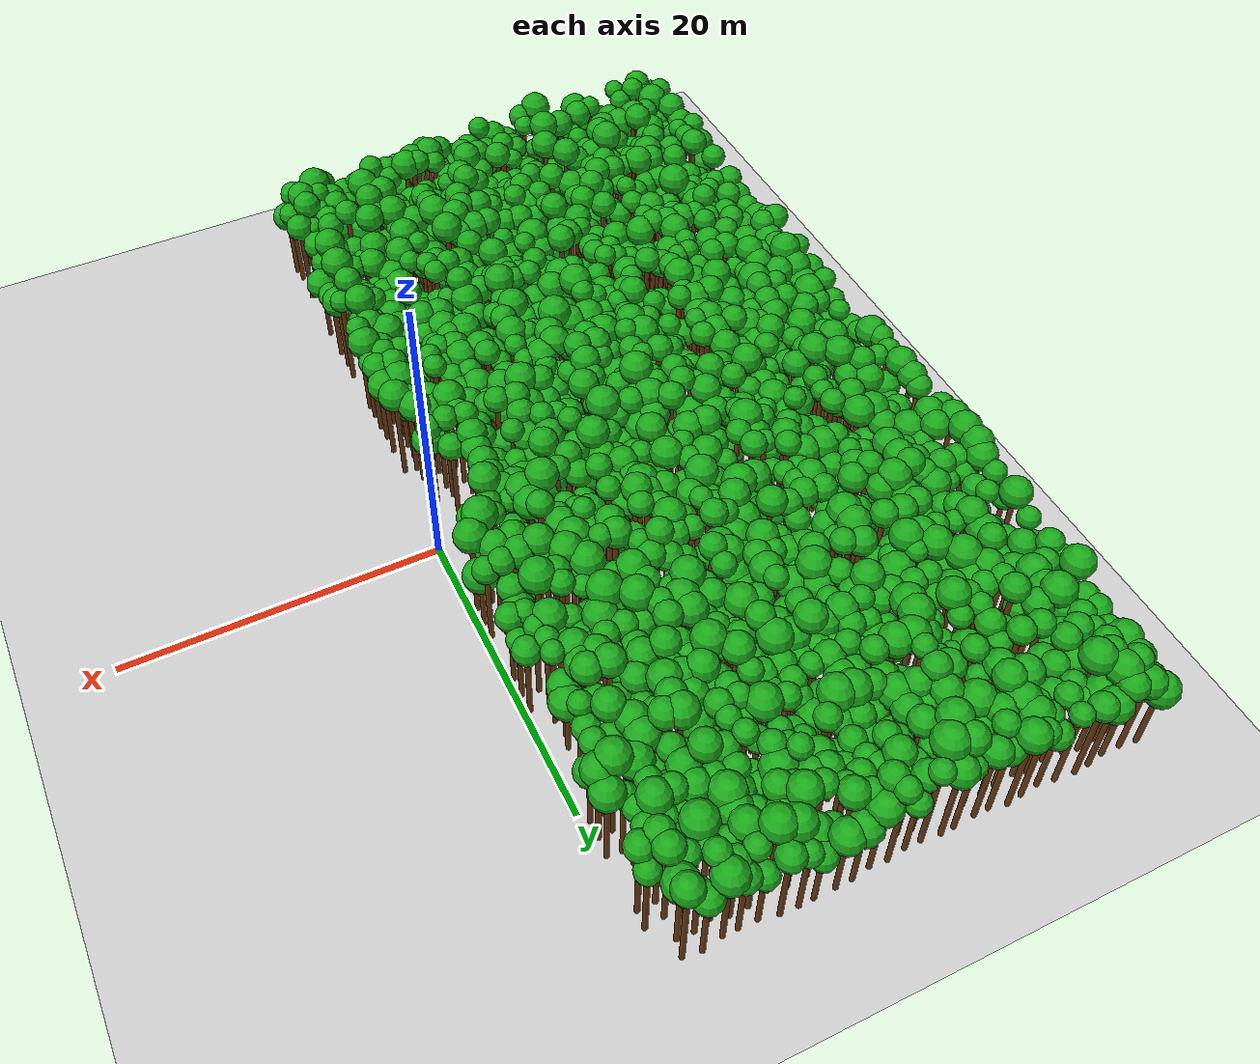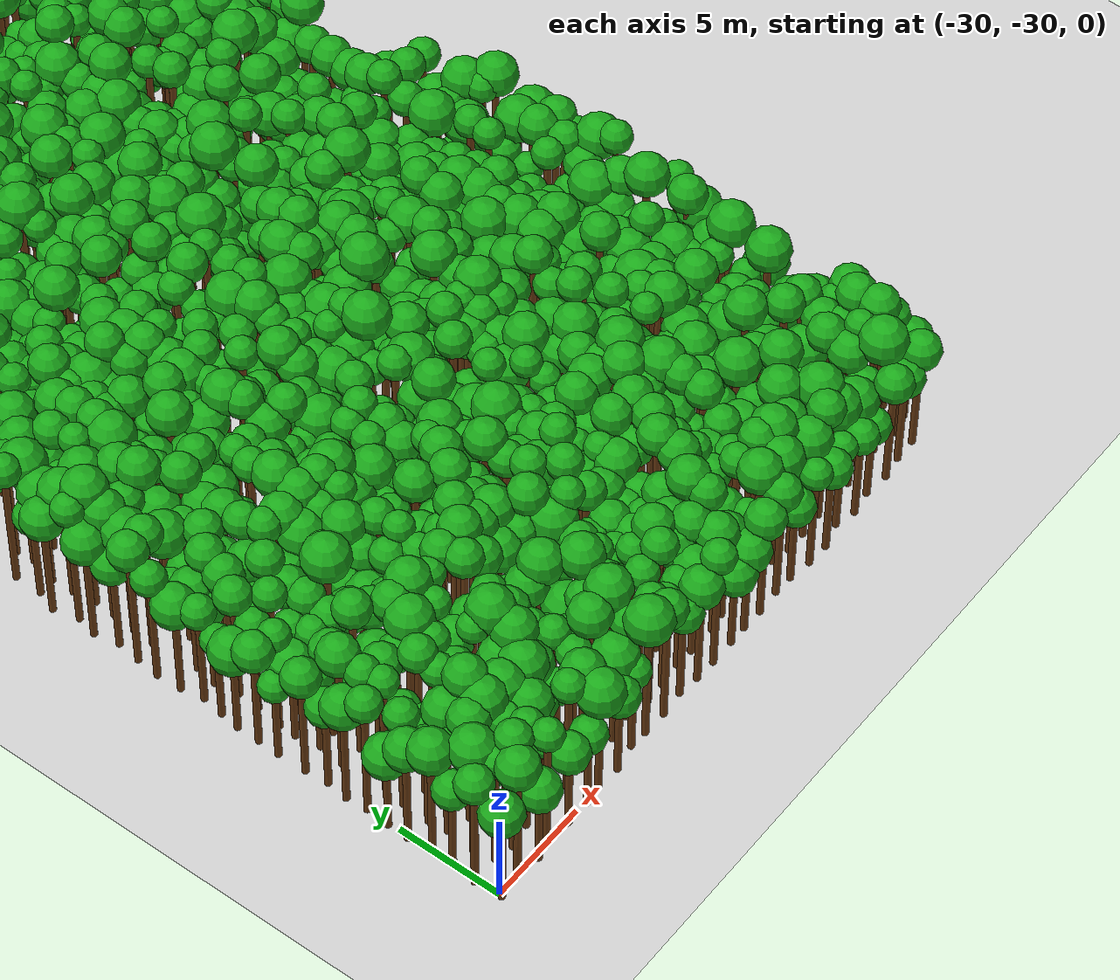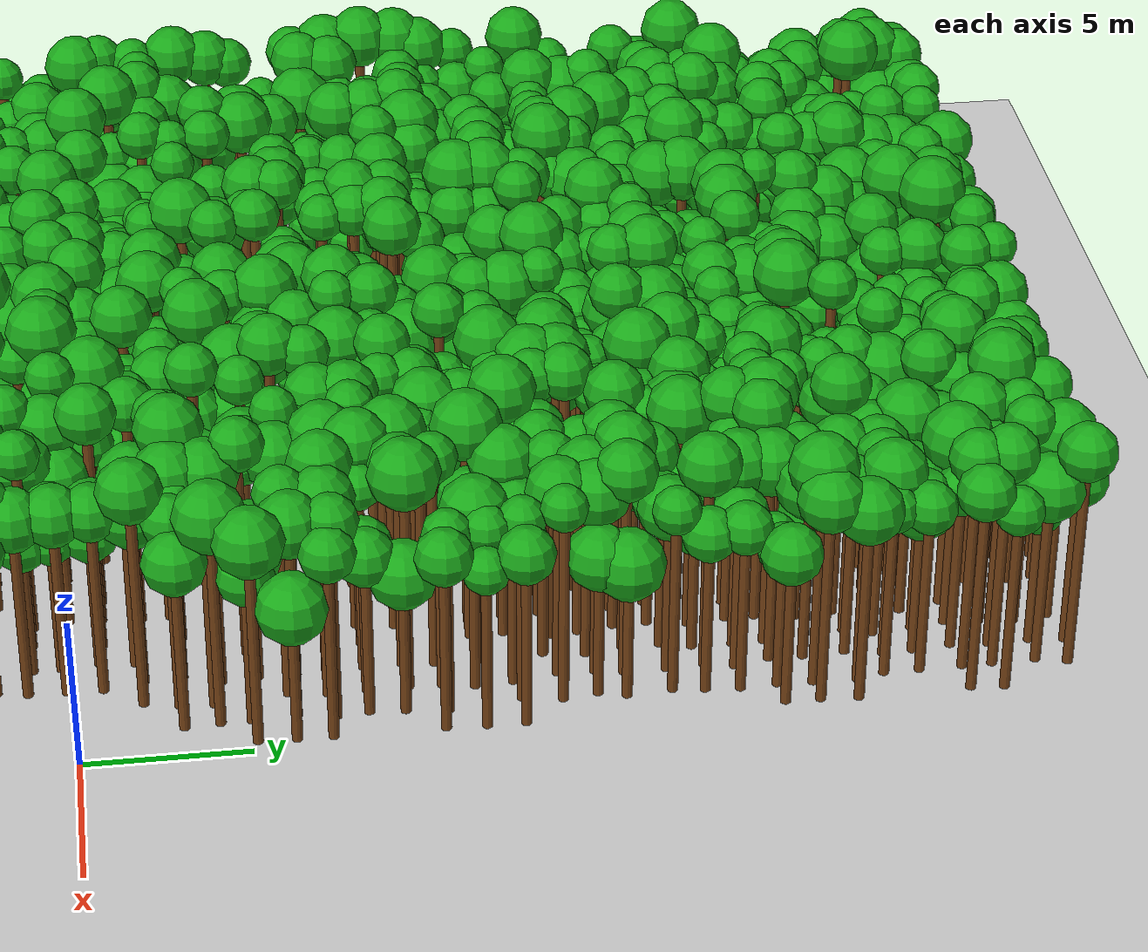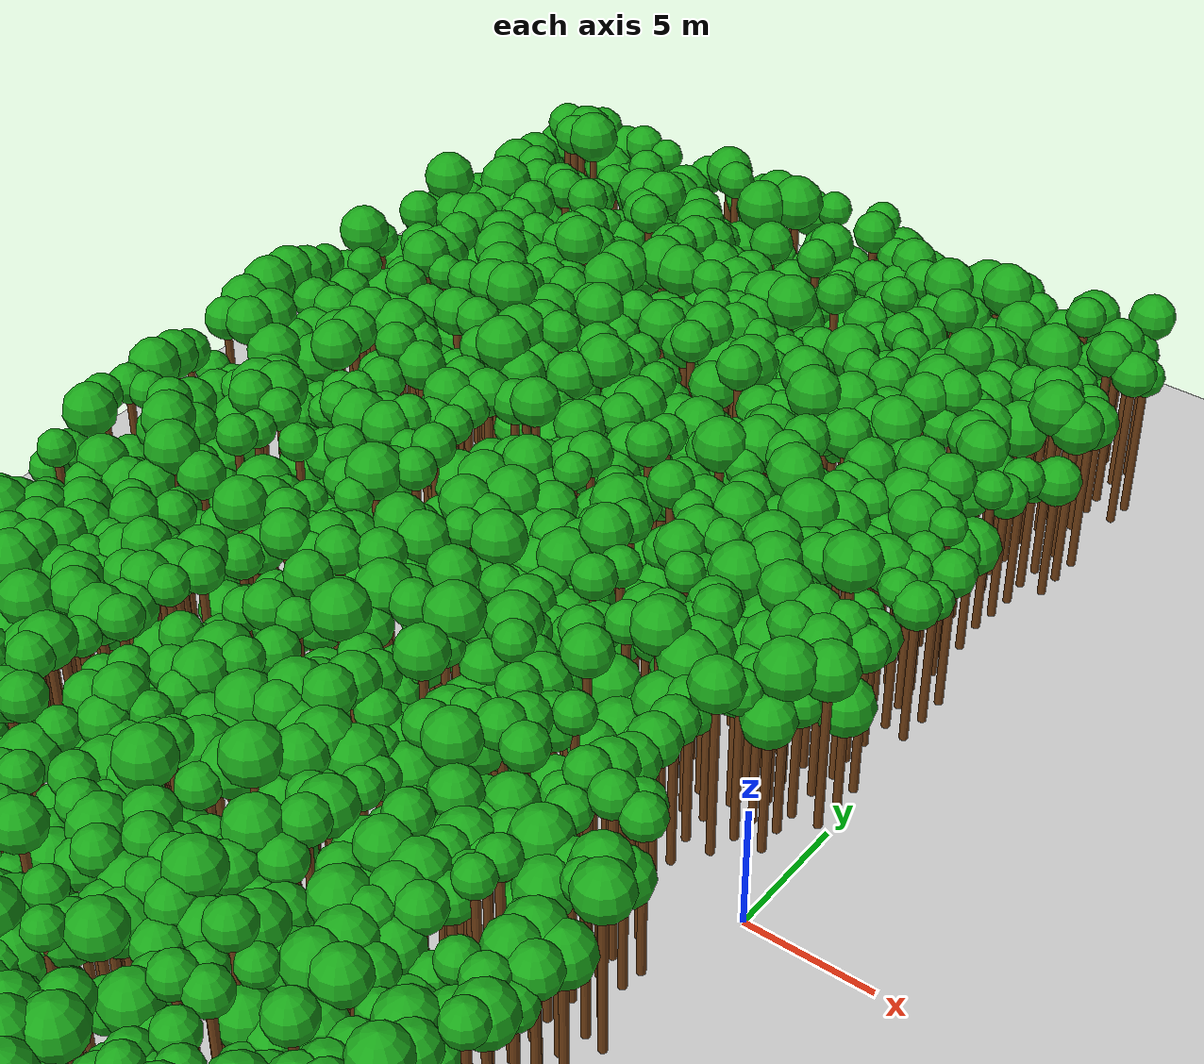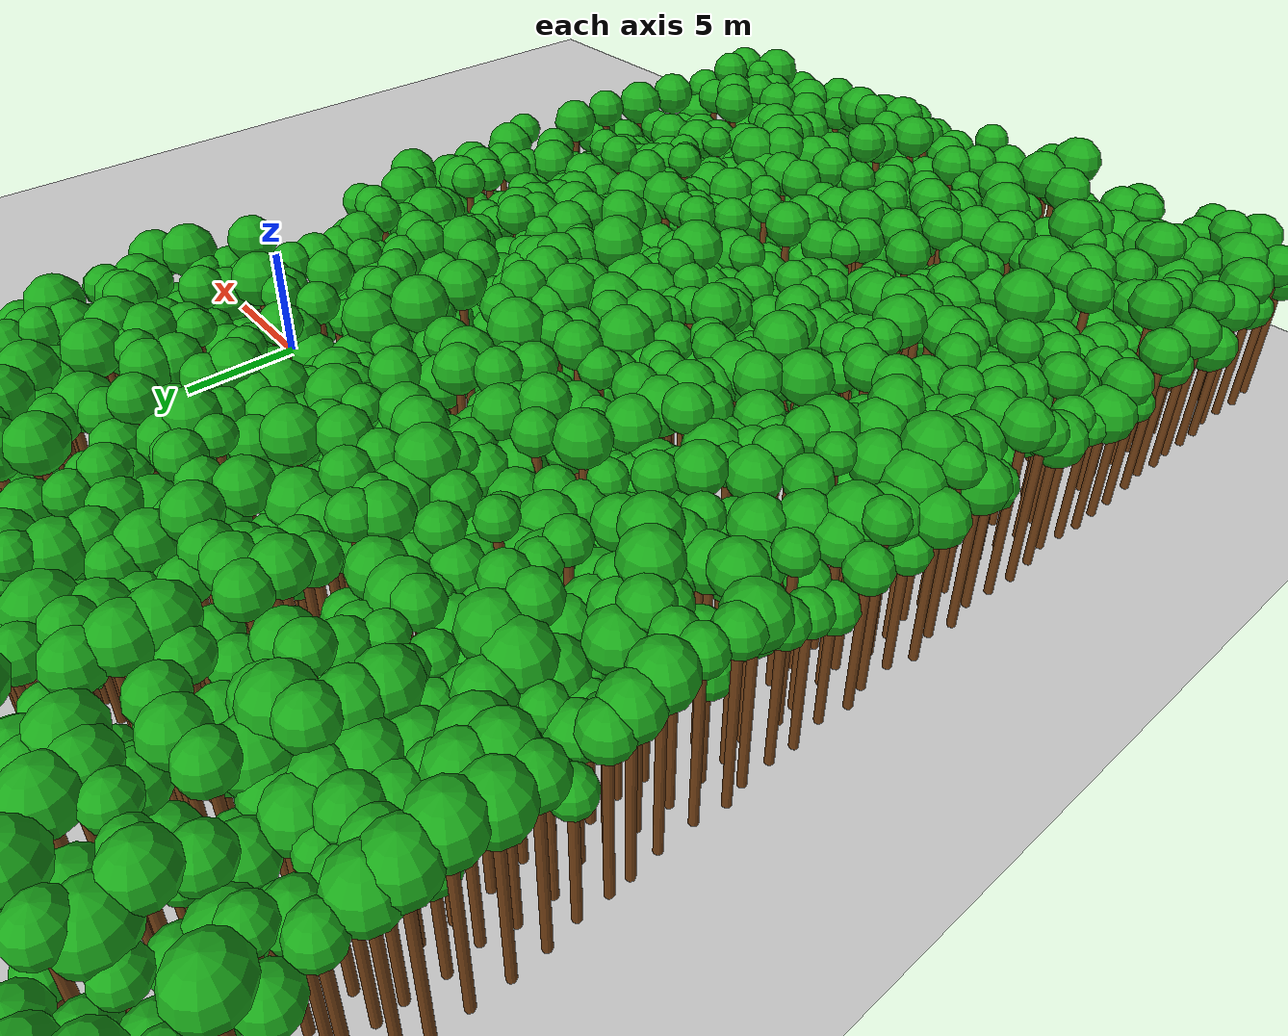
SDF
<sdf version="1.6">
 <world name="forest_world">
  <include><uri>model://sun</uri></include>
  <include><uri>model://ground_plane</uri></include>
  <model name="tree_0_trunk">
   <static>true</static>
   <pose>-30.06 -30.14 2.58 0 0 0</pose>
   <link name="link">
    <collision name="collision">
     <geometry><cylinder><radius>0.16</radius><length>5.17</length></cylinder></geometry>
    </collision>
    <visual name="visual">
     <geometry><cylinder><radius>0.16</radius><length>5.17</length></cylinder></geometry>
     <material><ambient>0.35 0.20 0.05 1</ambient><diffuse>0.45 0.25 0.08 1</diffuse></material>
    </visual>
   </link>
  </model>
  <model name="tree_0_leaf">
   <static>true</static>
   <pose>-30.06 -30.14 5.76 0 0 0</pose>
   <link name="link">
    <collision name="collision"><geometry><sphere><radius>0.98</radius></sphere></geometry></collision>
    <visual name="visual">
     <geometry><sphere><radius>0.98</radius></sphere></geometry>
     <material><ambient>0.05 0.45 0.05 1</ambient><diffuse>0.10 0.65 0.10 1</diffuse></material>
    </visual>
   </link>
  </model>
  <model name="tree_1_trunk">
   <static>true</static>
   <pose>-30.16 -28.88 3.14 0 0 0</pose>
   <link name="link">
    <collision name="collision">
     <geometry><cylinder><radius>0.16</radius><length>6.28</length></cylinder></geometry>
    </collision>
    <visual name="visual">
     <geometry><cylinder><radius>0.16</radius><length>6.28</length></cylinder></geometry>
     <material><ambient>0.35 0.20 0.05 1</ambient><diffuse>0.45 0.25 0.08 1</diffuse></material>
    </visual>
   </link>
  </model>
  <model name="tree_1_leaf">
   <static>true</static>
   <pose>-30.16 -28.88 6.79 0 0 0</pose>
   <link name="link">
    <collision name="collision"><geometry><sphere><radius>0.85</radius></sphere></geometry></collision>
    <visual name="visual">
     <geometry><sphere><radius>0.85</radius></sphere></geometry>
     <material><ambient>0.05 0.45 0.05 1</ambient><diffuse>0.10 0.65 0.10 1</diffuse></material>
    </visual>
   </link>
  </model>
  <model name="tree_2_trunk">
   <static>true</static>
   <pose>-30.05 -27.69 2.35 0 0 0</pose>
   <link name="link">
    <collision name="collision">
     <geometry><cylinder><radius>0.16</radius><length>4.70</length></cylinder></geometry>
    </collision>
    <visual name="visual">
     <geometry><cylinder><radius>0.16</radius><length>4.70</length></cylinder></geometry>
     <material><ambient>0.35 0.20 0.05 1</ambient><diffuse>0.45 0.25 0.08 1</diffuse></material>
    </visual>
   </link>
  </model>
  <model name="tree_2_leaf">
   <static>true</static>
   <pose>-30.05 -27.69 5.21 0 0 0</pose>
   <link name="link">
    <collision name="collision"><geometry><sphere><radius>0.85</radius></sphere></geometry></collision>
    <visual name="visual">
     <geometry><sphere><radius>0.85</radius></sphere></geometry>
     <material><ambient>0.05 0.45 0.05 1</ambient><diffuse>0.10 0.65 0.10 1</diffuse></material>
    </visual>
   </link>
  </model>
  <model name="tree_3_trunk">
   <static>true</static>
   <pose>-29.96 -26.59 3.09 0 0 0</pose>
   <link name="link">
    <collision name="collision">
     <geometry><cylinder><radius>0.16</radius><length>6.19</length></cylinder></geometry>
    </collision>
    <visual name="visual">
     <geometry><cylinder><radius>0.16</radius><length>6.19</length></cylinder></geometry>
     <material><ambient>0.35 0.20 0.05 1</ambient><diffuse>0.45 0.25 0.08 1</diffuse></material>
    </visual>
   </link>
  </model>
  <model name="tree_3_leaf">
   <static>true</static>
   <pose>-29.96 -26.59 6.78 0 0 0</pose>
   <link name="link">
    <collision name="collision"><geometry><sphere><radius>1.00</radius></sphere></geometry></collision>
    <visual name="visual">
     <geometry><sphere><radius>1.00</radius></sphere></geometry>
     <material><ambient>0.05 0.45 0.05 1</ambient><diffuse>0.10 0.65 0.10 1</diffuse></material>
    </visual>
   </link>
  </model>
  <model name="tree_4_trunk">
   <static>true</static>
   <pose>-30.14 -25.50 2.79 0 0 0</pose>
   <link name="link">
    <collision name="collision">
     <geometry><cylinder><radius>0.16</radius><length>5.59</length></cylinder></geometry>
    </collision>
    <visual name="visual">
     <geometry><cylinder><radius>0.16</radius><length>5.59</length></cylinder></geometry>
     <material><ambient>0.35 0.20 0.05 1</ambient><diffuse>0.45 0.25 0.08 1</diffuse></material>
    </visual>
   </link>
  </model>
  <model name="tree_4_leaf">
   <static>true</static>
   <pose>-30.14 -25.50 6.15 0 0 0</pose>
   <link name="link">
    <collision name="collision"><geometry><sphere><radius>0.94</radius></sphere></geometry></collision>
    <visual name="visual">
     <geometry><sphere><radius>0.94</radius></sphere></geometry>
     <material><ambient>0.05 0.45 0.05 1</ambient><diffuse>0.10 0.65 0.10 1</diffuse></material>
    </visual>
   </link>
  </model>
  <model name="tree_5_trunk">
   <static>true</static>
   <pose>-30.12 -24.48 2.09 0 0 0</pose>
   <link name="link">
    <collision name="collision">
     <geometry><cylinder><radius>0.16</radius><length>4.19</length></cylinder></geometry>
    </collision>
    <visual name="visual">
     <geometry><cylinder><radius>0.16</radius><length>4.19</length></cylinder></geometry>
     <material><ambient>0.35 0.20 0.05 1</ambient><diffuse>0.45 0.25 0.08 1</diffuse></material>
    </visual>
   </link>
  </model>
  <model name="tree_5_leaf">
   <static>true</static>
   <pose>-30.12 -24.48 4.79 0 0 0</pose>
   <link name="link">
    <collision name="collision"><geometry><sphere><radius>1.00</radius></sphere></geometry></collision>
    <visual name="visual">
     <geometry><sphere><radius>1.00</radius></sphere></geometry>
     <material><ambient>0.05 0.45 0.05 1</ambient><diffuse>0.10 0.65 0.10 1</diffuse></material>
    </visual>
   </link>
  </model>
  <model name="tree_6_trunk">
   <static>true</static>
   <pose>-30.05 -23.38 3.39 0 0 0</pose>
   <link name="link">
    <collision name="collision">
     <geometry><cylinder><radius>0.16</radius><length>6.77</length></cylinder></geometry>
    </collision>
    <visual name="visual">
     <geometry><cylinder><radius>0.16</radius><length>6.77</length></cylinder></geometry>
     <material><ambient>0.35 0.20 0.05 1</ambient><diffuse>0.45 0.25 0.08 1</diffuse></material>
    </visual>
   </link>
  </model>
  <model name="tree_6_leaf">
   <static>true</static>
   <pose>-30.05 -23.38 7.25 0 0 0</pose>
   <link name="link">
    <collision name="collision"><geometry><sphere><radius>0.79</radius></sphere></geometry></collision>
    <visual name="visual">
     <geometry><sphere><radius>0.79</radius></sphere></geometry>
     <material><ambient>0.05 0.45 0.05 1</ambient><diffuse>0.10 0.65 0.10 1</diffuse></material>
    </visual>
   </link>
  </model>
  <model name="tree_7_trunk">
   <static>true</static>
   <pose>-30.13 -22.36 2.84 0 0 0</pose>
   <link name="link">
    <collision name="collision">
     <geometry><cylinder><radius>0.16</radius><length>5.68</length></cylinder></geometry>
    </collision>
    <visual name="visual">
     <geometry><cylinder><radius>0.16</radius><length>5.68</length></cylinder></geometry>
     <material><ambient>0.35 0.20 0.05 1</ambient><diffuse>0.45 0.25 0.08 1</diffuse></material>
    </visual>
   </link>
  </model>
  <model name="tree_7_leaf">
   <static>true</static>
   <pose>-30.13 -22.36 6.27 0 0 0</pose>
   <link name="link">
    <collision name="collision"><geometry><sphere><radius>0.98</radius></sphere></geometry></collision>
    <visual name="visual">
     <geometry><sphere><radius>0.98</radius></sphere></geometry>
     <material><ambient>0.05 0.45 0.05 1</ambient><diffuse>0.10 0.65 0.10 1</diffuse></material>
    </visual>
   </link>
  </model>
  <model name="tree_8_trunk">
   <static>true</static>
   <pose>-30.00 -21.33 2.36 0 0 0</pose>
   <link name="link">
    <collision name="collision">
     <geometry><cylinder><radius>0.16</radius><length>4.72</length></cylinder></geometry>
    </collision>
    <visual name="visual">
     <geometry><cylinder><radius>0.16</radius><length>4.72</length></cylinder></geometry>
     <material><ambient>0.35 0.20 0.05 1</ambient><diffuse>0.45 0.25 0.08 1</diffuse></material>
    </visual>
   </link>
  </model>
  <model name="tree_8_leaf">
   <static>true</static>
   <pose>-30.00 -21.33 5.23 0 0 0</pose>
   <link name="link">
    <collision name="collision"><geometry><sphere><radius>0.86</radius></sphere></geometry></collision>
    <visual name="visual">
     <geometry><sphere><radius>0.86</radius></sphere></geometry>
     <material><ambient>0.05 0.45 0.05 1</ambient><diffuse>0.10 0.65 0.10 1</diffuse></material>
    </visual>
   </link>
  </model>
  <model name="tree_9_trunk">
   <static>true</static>
   <pose>-30.10 -20.23 2.94 0 0 0</pose>
   <link name="link">
    <collision name="collision">
     <geometry><cylinder><radius>0.16</radius><length>5.88</length></cylinder></geometry>
    </collision>
    <visual name="visual">
     <geometry><cylinder><radius>0.16</radius><length>5.88</length></cylinder></geometry>
     <material><ambient>0.35 0.20 0.05 1</ambient><diffuse>0.45 0.25 0.08 1</diffuse></material>
    </visual>
   </link>
  </model>
  <model name="tree_9_leaf">
   <static>true</static>
   <pose>-30.10 -20.23 6.40 0 0 0</pose>
   <link name="link">
    <collision name="collision"><geometry><sphere><radius>0.87</radius></sphere></geometry></collision>
    <visual name="visual">
     <geometry><sphere><radius>0.87</radius></sphere></geometry>
     <material><ambient>0.05 0.45 0.05 1</ambient><diffuse>0.10 0.65 0.10 1</diffuse></material>
    </visual>
   </link>
  </model>
  <model name="tree_10_trunk">
   <static>true</static>
   <pose>-30.13 -18.85 2.13 0 0 0</pose>
   <link name="link">
    <collision name="collision">
     <geometry><cylinder><radius>0.16</radius><length>4.27</length></cylinder></geometry>
    </collision>
    <visual name="visual">
     <geometry><cylinder><radius>0.16</radius><length>4.27</length></cylinder></geometry>
     <material><ambient>0.35 0.20 0.05 1</ambient><diffuse>0.45 0.25 0.08 1</diffuse></material>
    </visual>
   </link>
  </model>
  <model name="tree_10_leaf">
   <static>true</static>
   <pose>-30.13 -18.85 4.70 0 0 0</pose>
   <link name="link">
    <collision name="collision"><geometry><sphere><radius>0.72</radius></sphere></geometry></collision>
    <visual name="visual">
     <geometry><sphere><radius>0.72</radius></sphere></geometry>
     <material><ambient>0.05 0.45 0.05 1</ambient><diffuse>0.10 0.65 0.10 1</diffuse></material>
    </visual>
   </link>
  </model>
  <model name="tree_11_trunk">
   <static>true</static>
   <pose>-30.11 -17.81 2.78 0 0 0</pose>
   <link name="link">
    <collision name="collision">
     <geometry><cylinder><radius>0.16</radius><length>5.57</length></cylinder></geometry>
    </collision>
    <visual name="visual">
     <geometry><cylinder><radius>0.16</radius><length>5.57</length></cylinder></geometry>
     <material><ambient>0.35 0.20 0.05 1</ambient><diffuse>0.45 0.25 0.08 1</diffuse></material>
    </visual>
   </link>
  </model>
  <model name="tree_11_leaf">
   <static>true</static>
   <pose>-30.11 -17.81 6.11 0 0 0</pose>
   <link name="link">
    <collision name="collision"><geometry><sphere><radius>0.90</radius></sphere></geometry></collision>
    <visual name="visual">
     <geometry><sphere><radius>0.90</radius></sphere></geometry>
     <material><ambient>0.05 0.45 0.05 1</ambient><diffuse>0.10 0.65 0.10 1</diffuse></material>
    </visual>
   </link>
  </model>
  <model name="tree_12_trunk">
   <static>true</static>
   <pose>-30.12 -16.72 2.31 0 0 0</pose>
   <link name="link">
    <collision name="collision">
     <geometry><cylinder><radius>0.16</radius><length>4.62</length></cylinder></geometry>
    </collision>
    <visual name="visual">
     <geometry><cylinder><radius>0.16</radius><length>4.62</length></cylinder></geometry>
     <material><ambient>0.35 0.20 0.05 1</ambient><diffuse>0.45 0.25 0.08 1</diffuse></material>
    </visual>
   </link>
  </model>
  <model name="tree_12_leaf">
   <static>true</static>
   <pose>-30.12 -16.72 5.25 0 0 0</pose>
   <link name="link">
    <collision name="collision"><geometry><sphere><radius>1.06</radius></sphere></geometry></collision>
    <visual name="visual">
     <geometry><sphere><radius>1.06</radius></sphere></geometry>
     <material><ambient>0.05 0.45 0.05 1</ambient><diffuse>0.10 0.65 0.10 1</diffuse></material>
    </visual>
   </link>
  </model>
  <model name="tree_13_trunk">
   <static>true</static>
   <pose>-29.99 -15.78 2.33 0 0 0</pose>
   <link name="link">
    <collision name="collision">
     <geometry><cylinder><radius>0.16</radius><length>4.66</length></cylinder></geometry>
    </collision>
    <visual name="visual">
     <geometry><cylinder><radius>0.16</radius><length>4.66</length></cylinder></geometry>
     <material><ambient>0.35 0.20 0.05 1</ambient><diffuse>0.45 0.25 0.08 1</diffuse></material>
    </visual>
   </link>
  </model>
  <model name="tree_13_leaf">
   <static>true</static>
   <pose>-29.99 -15.78 5.08 0 0 0</pose>
   <link name="link">
    <collision name="collision"><geometry><sphere><radius>0.71</radius></sphere></geometry></collision>
    <visual name="visual">
     <geometry><sphere><radius>0.71</radius></sphere></geometry>
     <material><ambient>0.05 0.45 0.05 1</ambient><diffuse>0.10 0.65 0.10 1</diffuse></material>
    </visual>
   </link>
  </model>
  <model name="tree_14_trunk">
   <static>true</static>
   <pose>-29.84 -14.74 2.73 0 0 0</pose>
   <link name="link">
    <collision name="collision">
     <geometry><cylinder><radius>0.16</radius><length>5.46</length></cylinder></geometry>
    </collision>
    <visual name="visual">
     <geometry><cylinder><radius>0.16</radius><length>5.46</length></cylinder></geometry>
     <material><ambient>0.35 0.20 0.05 1</ambient><diffuse>0.45 0.25 0.08 1</diffuse></material>
    </visual>
   </link>
  </model>
  <model name="tree_14_leaf">
   <static>true</static>
   <pose>-29.84 -14.74 5.92 0 0 0</pose>
   <link name="link">
    <collision name="collision"><geometry><sphere><radius>0.78</radius></sphere></geometry></collision>
    <visual name="visual">
     <geometry><sphere><radius>0.78</radius></sphere></geometry>
     <material><ambient>0.05 0.45 0.05 1</ambient><diffuse>0.10 0.65 0.10 1</diffuse></material>
    </visual>
   </link>
  </model>
  <model name="tree_15_trunk">
   <static>true</static>
   <pose>-30.04 -13.66 2.52 0 0 0</pose>
   <link name="link">
    <collision name="collision">
     <geometry><cylinder><radius>0.16</radius><length>5.03</length></cylinder></geometry>
    </collision>
    <visual name="visual">
     <geometry><cylinder><radius>0.16</radius><length>5.03</length></cylinder></geometry>
     <material><ambient>0.35 0.20 0.05 1</ambient><diffuse>0.45 0.25 0.08 1</diffuse></material>
    </visual>
   </link>
  </model>
  <model name="tree_15_leaf">
   <static>true</static>
   <pose>-30.04 -13.66 5.64 0 0 0</pose>
   <link name="link">
    <collision name="collision"><geometry><sphere><radius>1.01</radius></sphere></geometry></collision>
    <visual name="visual">
     <geometry><sphere><radius>1.01</radius></sphere></geometry>
     <material><ambient>0.05 0.45 0.05 1</ambient><diffuse>0.10 0.65 0.10 1</diffuse></material>
    </visual>
   </link>
  </model>
  <model name="tree_16_trunk">
   <static>true</static>
   <pose>-30.11 -12.47 3.04 0 0 0</pose>
   <link name="link">
    <collision name="collision">
     <geometry><cylinder><radius>0.16</radius><length>6.08</length></cylinder></geometry>
    </collision>
    <visual name="visual">
     <geometry><cylinder><radius>0.16</radius><length>6.08</length></cylinder></geometry>
     <material><ambient>0.35 0.20 0.05 1</ambient><diffuse>0.45 0.25 0.08 1</diffuse></material>
    </visual>
   </link>
  </model>
  <model name="tree_16_leaf">
   <static>true</static>
   <pose>-30.11 -12.47 6.55 0 0 0</pose>
   <link name="link">
    <collision name="collision"><geometry><sphere><radius>0.79</radius></sphere></geometry></collision>
    <visual name="visual">
     <geometry><sphere><radius>0.79</radius></sphere></geometry>
     <material><ambient>0.05 0.45 0.05 1</ambient><diffuse>0.10 0.65 0.10 1</diffuse></material>
    </visual>
   </link>
  </model>
  <model name="tree_17_trunk">
   <static>true</static>
   <pose>-29.99 -11.35 3.40 0 0 0</pose>
   <link name="link">
    <collision name="collision">
     <geometry><cylinder><radius>0.16</radius><length>6.81</length></cylinder></geometry>
    </collision>
    <visual name="visual">
     <geometry><cylinder><radius>0.16</radius><length>6.81</length></cylinder></geometry>
     <material><ambient>0.35 0.20 0.05 1</ambient><diffuse>0.45 0.25 0.08 1</diffuse></material>
    </visual>
   </link>
  </model>
  <model name="tree_17_leaf">
   <static>true</static>
   <pose>-29.99 -11.35 7.35 0 0 0</pose>
   <link name="link">
    <collision name="collision"><geometry><sphere><radius>0.90</radius></sphere></geometry></collision>
    <visual name="visual">
     <geometry><sphere><radius>0.90</radius></sphere></geometry>
     <material><ambient>0.05 0.45 0.05 1</ambient><diffuse>0.10 0.65 0.10 1</diffuse></material>
    </visual>
   </link>
  </model>
  <model name="tree_18_trunk">
   <static>true</static>
   <pose>-29.84 -10.22 2.43 0 0 0</pose>
   <link name="link">
    <collision name="collision">
     <geometry><cylinder><radius>0.16</radius><length>4.86</length></cylinder></geometry>
    </collision>
    <visual name="visual">
     <geometry><cylinder><radius>0.16</radius><length>4.86</length></cylinder></geometry>
     <material><ambient>0.35 0.20 0.05 1</ambient><diffuse>0.45 0.25 0.08 1</diffuse></material>
    </visual>
   </link>
  </model>
  <model name="tree_18_leaf">
   <static>true</static>
   <pose>-29.84 -10.22 5.41 0 0 0</pose>
   <link name="link">
    <collision name="collision"><geometry><sphere><radius>0.91</radius></sphere></geometry></collision>
    <visual name="visual">
     <geometry><sphere><radius>0.91</radius></sphere></geometry>
     <material><ambient>0.05 0.45 0.05 1</ambient><diffuse>0.10 0.65 0.10 1</diffuse></material>
    </visual>
   </link>
  </model>
  <model name="tree_19_trunk">
   <static>true</static>
   <pose>-30.09 -9.06 2.80 0 0 0</pose>
   <link name="link">
    <collision name="collision">
     <geometry><cylinder><radius>0.16</radius><length>5.60</length></cylinder></geometry>
    </collision>
    <visual name="visual">
     <geometry><cylinder><radius>0.16</radius><length>5.60</length></cylinder></geometry>
     <material><ambient>0.35 0.20 0.05 1</ambient><diffuse>0.45 0.25 0.08 1</diffuse></material>
    </visual>
   </link>
  </model>
  <model name="tree_19_leaf">
   <static>true</static>
   <pose>-30.09 -9.06 6.20 0 0 0</pose>
   <link name="link">
    <collision name="collision"><geometry><sphere><radius>1.00</radius></sphere></geometry></collision>
    <visual name="visual">
     <geometry><sphere><radius>1.00</radius></sphere></geometry>
     <material><ambient>0.05 0.45 0.05 1</ambient><diffuse>0.10 0.65 0.10 1</diffuse></material>
    </visual>
   </link>
  </model>
  <model name="tree_20_trunk">
   <static>true</static>
   <pose>-29.86 -8.09 3.44 0 0 0</pose>
   <link name="link">
    <collision name="collision">
     <geometry><cylinder><radius>0.16</radius><length>6.88</length></cylinder></geometry>
    </collision>
    <visual name="visual">
     <geometry><cylinder><radius>0.16</radius><length>6.88</length></cylinder></geometry>
     <material><ambient>0.35 0.20 0.05 1</ambient><diffuse>0.45 0.25 0.08 1</diffuse></material>
    </visual>
   </link>
  </model>
  <model name="tree_20_leaf">
   <static>true</static>
   <pose>-29.86 -8.09 7.34 0 0 0</pose>
   <link name="link">
    <collision name="collision"><geometry><sphere><radius>0.76</radius></sphere></geometry></collision>
    <visual name="visual">
     <geometry><sphere><radius>0.76</radius></sphere></geometry>
     <material><ambient>0.05 0.45 0.05 1</ambient><diffuse>0.10 0.65 0.10 1</diffuse></material>
    </visual>
   </link>
  </model>
  <model name="tree_21_trunk">
   <static>true</static>
   <pose>-30.17 -6.90 2.77 0 0 0</pose>
   <link name="link">
    <collision name="collision">
     <geometry><cylinder><radius>0.16</radius><length>5.54</length></cylinder></geometry>
    </collision>
    <visual name="visual">
     <geometry><cylinder><radius>0.16</radius><length>5.54</length></cylinder></geometry>
     <material><ambient>0.35 0.20 0.05 1</ambient><diffuse>0.45 0.25 0.08 1</diffuse></material>
    </visual>
   </link>
  </model>
  <model name="tree_21_leaf">
   <static>true</static>
   <pose>-30.17 -6.90 6.13 0 0 0</pose>
   <link name="link">
    <collision name="collision"><geometry><sphere><radius>0.98</radius></sphere></geometry></collision>
    <visual name="visual">
     <geometry><sphere><radius>0.98</radius></sphere></geometry>
     <material><ambient>0.05 0.45 0.05 1</ambient><diffuse>0.10 0.65 0.10 1</diffuse></material>
    </visual>
   </link>
  </model>
  <model name="tree_22_trunk">
   <static>true</static>
   <pose>-29.83 -5.94 2.33 0 0 0</pose>
   <link name="link">
    <collision name="collision">
     <geometry><cylinder><radius>0.16</radius><length>4.66</length></cylinder></geometry>
    </collision>
    <visual name="visual">
     <geometry><cylinder><radius>0.16</radius><length>4.66</length></cylinder></geometry>
     <material><ambient>0.35 0.20 0.05 1</ambient><diffuse>0.45 0.25 0.08 1</diffuse></material>
    </visual>
   </link>
  </model>
  <model name="tree_22_leaf">
   <static>true</static>
   <pose>-29.83 -5.94 5.16 0 0 0</pose>
   <link name="link">
    <collision name="collision"><geometry><sphere><radius>0.82</radius></sphere></geometry></collision>
    <visual name="visual">
     <geometry><sphere><radius>0.82</radius></sphere></geometry>
     <material><ambient>0.05 0.45 0.05 1</ambient><diffuse>0.10 0.65 0.10 1</diffuse></material>
    </visual>
   </link>
  </model>
  <model name="tree_23_trunk">
   <static>true</static>
   <pose>-29.83 -4.62 3.33 0 0 0</pose>
   <link name="link">
    <collision name="collision">
     <geometry><cylinder><radius>0.16</radius><length>6.66</length></cylinder></geometry>
    </collision>
    <visual name="visual">
     <geometry><cylinder><radius>0.16</radius><length>6.66</length></cylinder></geometry>
     <material><ambient>0.35 0.20 0.05 1</ambient><diffuse>0.45 0.25 0.08 1</diffuse></material>
    </visual>
   </link>
  </model>
  <model name="tree_23_leaf">
   <static>true</static>
   <pose>-29.83 -4.62 7.12 0 0 0</pose>
   <link name="link">
    <collision name="collision"><geometry><sphere><radius>0.76</radius></sphere></geometry></collision>
    <visual name="visual">
     <geometry><sphere><radius>0.76</radius></sphere></geometry>
     <material><ambient>0.05 0.45 0.05 1</ambient><diffuse>0.10 0.65 0.10 1</diffuse></material>
    </visual>
   </link>
  </model>
  <model name="tree_24_trunk">
   <static>true</static>
   <pose>-30.06 -3.72 2.71 0 0 0</pose>
   <link name="link">
    <collision name="collision">
     <geometry><cylinder><radius>0.16</radius><length>5.43</length></cylinder></geometry>
    </collision>
    <visual name="visual">
     <geometry><cylinder><radius>0.16</radius><length>5.43</length></cylinder></geometry>
     <material><ambient>0.35 0.20 0.05 1</ambient><diffuse>0.45 0.25 0.08 1</diffuse></material>
    </visual>
   </link>
  </model>
  <model name="tree_24_leaf">
   <static>true</static>
   <pose>-30.06 -3.72 5.92 0 0 0</pose>
   <link name="link">
    <collision name="collision"><geometry><sphere><radius>0.81</radius></sphere></geometry></collision>
    <visual name="visual">
     <geometry><sphere><radius>0.81</radius></sphere></geometry>
     <material><ambient>0.05 0.45 0.05 1</ambient><diffuse>0.10 0.65 0.10 1</diffuse></material>
    </visual>
   </link>
  </model>
  <model name="tree_25_trunk">
   <static>true</static>
   <pose>-29.83 -2.58 2.21 0 0 0</pose>
   <link name="link">
    <collision name="collision">
     <geometry><cylinder><radius>0.16</radius><length>4.42</length></cylinder></geometry>
    </collision>
    <visual name="visual">
     <geometry><cylinder><radius>0.16</radius><length>4.42</length></cylinder></geometry>
     <material><ambient>0.35 0.20 0.05 1</ambient><diffuse>0.45 0.25 0.08 1</diffuse></material>
    </visual>
   </link>
  </model>
  <model name="tree_25_leaf">
   <static>true</static>
   <pose>-29.83 -2.58 4.92 0 0 0</pose>
   <link name="link">
    <collision name="collision"><geometry><sphere><radius>0.83</radius></sphere></geometry></collision>
    <visual name="visual">
     <geometry><sphere><radius>0.83</radius></sphere></geometry>
     <material><ambient>0.05 0.45 0.05 1</ambient><diffuse>0.10 0.65 0.10 1</diffuse></material>
    </visual>
   </link>
  </model>
  <model name="tree_26_trunk">
   <static>true</static>
   <pose>-29.98 -1.27 2.63 0 0 0</pose>
   <link name="link">
    <collision name="collision">
     <geometry><cylinder><radius>0.16</radius><length>5.26</length></cylinder></geometry>
    </collision>
    <visual name="visual">
     <geometry><cylinder><radius>0.16</radius><length>5.26</length></cylinder></geometry>
     <material><ambient>0.35 0.20 0.05 1</ambient><diffuse>0.45 0.25 0.08 1</diffuse></material>
    </visual>
   </link>
  </model>
  <model name="tree_26_leaf">
   <static>true</static>
   <pose>-29.98 -1.27 5.71 0 0 0</pose>
   <link name="link">
    <collision name="collision"><geometry><sphere><radius>0.76</radius></sphere></geometry></collision>
    <visual name="visual">
     <geometry><sphere><radius>0.76</radius></sphere></geometry>
     <material><ambient>0.05 0.45 0.05 1</ambient><diffuse>0.10 0.65 0.10 1</diffuse></material>
    </visual>
   </link>
  </model>
  <model name="tree_27_trunk">
   <static>true</static>
   <pose>-29.89 -0.29 2.73 0 0 0</pose>
   <link name="link">
    <collision name="collision">
     <geometry><cylinder><radius>0.16</radius><length>5.46</length></cylinder></geometry>
    </collision>
    <visual name="visual">
     <geometry><cylinder><radius>0.16</radius><length>5.46</length></cylinder></geometry>
     <material><ambient>0.35 0.20 0.05 1</ambient><diffuse>0.45 0.25 0.08 1</diffuse></material>
    </visual>
   </link>
  </model>
  <model name="tree_27_leaf">
   <static>true</static>
   <pose>-29.89 -0.29 5.94 0 0 0</pose>
   <link name="link">
    <collision name="collision"><geometry><sphere><radius>0.80</radius></sphere></geometry></collision>
    <visual name="visual">
     <geometry><sphere><radius>0.80</radius></sphere></geometry>
     <material><ambient>0.05 0.45 0.05 1</ambient><diffuse>0.10 0.65 0.10 1</diffuse></material>
    </visual>
   </link>
  </model>
  <model name="tree_28_trunk">
   <static>true</static>
   <pose>-29.91 0.91 3.22 0 0 0</pose>
   <link name="link">
    <collision name="collision">
     <geometry><cylinder><radius>0.16</radius><length>6.43</length></cylinder></geometry>
    </collision>
    <visual name="visual">
     <geometry><cylinder><radius>0.16</radius><length>6.43</length></cylinder></geometry>
     <material><ambient>0.35 0.20 0.05 1</ambient><diffuse>0.45 0.25 0.08 1</diffuse></material>
    </visual>
   </link>
  </model>
  <model name="tree_28_leaf">
   <static>true</static>
   <pose>-29.91 0.91 7.06 0 0 0</pose>
   <link name="link">
    <collision name="collision"><geometry><sphere><radius>1.04</radius></sphere></geometry></collision>
    <visual name="visual">
     <geometry><sphere><radius>1.04</radius></sphere></geometry>
     <material><ambient>0.05 0.45 0.05 1</ambient><diffuse>0.10 0.65 0.10 1</diffuse></material>
    </visual>
   </link>
  </model>
  <model name="tree_29_trunk">
   <static>true</static>
   <pose>-30.10 1.73 3.36 0 0 0</pose>
   <link name="link">
    <collision name="collision">
     <geometry><cylinder><radius>0.16</radius><length>6.72</length></cylinder></geometry>
    </collision>
    <visual name="visual">
     <geometry><cylinder><radius>0.16</radius><length>6.72</length></cylinder></geometry>
     <material><ambient>0.35 0.20 0.05 1</ambient><diffuse>0.45 0.25 0.08 1</diffuse></material>
    </visual>
   </link>
  </model>
  <model name="tree_29_leaf">
   <static>true</static>
   <pose>-30.10 1.73 7.20 0 0 0</pose>
   <link name="link">
    <collision name="collision"><geometry><sphere><radius>0.80</radius></sphere></geometry></collision>
    <visual name="visual">
     <geometry><sphere><radius>0.80</radius></sphere></geometry>
     <material><ambient>0.05 0.45 0.05 1</ambient><diffuse>0.10 0.65 0.10 1</diffuse></material>
    </visual>
   </link>
  </model>
  <model name="tree_30_trunk">
   <static>true</static>
   <pose>-29.91 2.88 3.34 0 0 0</pose>
   <link name="link">
    <collision name="collision">
     <geometry><cylinder><radius>0.16</radius><length>6.68</length></cylinder></geometry>
    </collision>
    <visual name="visual">
     <geometry><cylinder><radius>0.16</radius><length>6.68</length></cylinder></geometry>
     <material><ambient>0.35 0.20 0.05 1</ambient><diffuse>0.45 0.25 0.08 1</diffuse></material>
    </visual>
   </link>
  </model>
  <model name="tree_30_leaf">
   <static>true</static>
   <pose>-29.91 2.88 7.13 0 0 0</pose>
   <link name="link">
    <collision name="collision"><geometry><sphere><radius>0.77</radius></sphere></geometry></collision>
    <visual name="visual">
     <geometry><sphere><radius>0.77</radius></sphere></geometry>
     <material><ambient>0.05 0.45 0.05 1</ambient><diffuse>0.10 0.65 0.10 1</diffuse></material>
    </visual>
   </link>
  </model>
  <model name="tree_31_trunk">
   <static>true</static>
   <pose>-29.92 4.26 3.33 0 0 0</pose>
   <link name="link">
    <collision name="collision">
     <geometry><cylinder><radius>0.16</radius><length>6.65</length></cylinder></geometry>
    </collision>
    <visual name="visual">
     <geometry><cylinder><radius>0.16</radius><length>6.65</length></cylinder></geometry>
     <material><ambient>0.35 0.20 0.05 1</ambient><diffuse>0.45 0.25 0.08 1</diffuse></material>
    </visual>
   </link>
  </model>
  <model name="tree_31_leaf">
   <static>true</static>
   <pose>-29.92 4.26 7.26 0 0 0</pose>
   <link name="link">
    <collision name="collision"><geometry><sphere><radius>1.01</radius></sphere></geometry></collision>
    <visual name="visual">
     <geometry><sphere><radius>1.01</radius></sphere></geometry>
     <material><ambient>0.05 0.45 0.05 1</ambient><diffuse>0.10 0.65 0.10 1</diffuse></material>
    </visual>
   </link>
  </model>
  <model name="tree_32_trunk">
   <static>true</static>
   <pose>-30.02 5.37 3.23 0 0 0</pose>
   <link name="link">
    <collision name="collision">
     <geometry><cylinder><radius>0.16</radius><length>6.46</length></cylinder></geometry>
    </collision>
    <visual name="visual">
     <geometry><cylinder><radius>0.16</radius><length>6.46</length></cylinder></geometry>
     <material><ambient>0.35 0.20 0.05 1</ambient><diffuse>0.45 0.25 0.08 1</diffuse></material>
    </visual>
   </link>
  </model>
  <model name="tree_32_leaf">
   <static>true</static>
   <pose>-30.02 5.37 7.03 0 0 0</pose>
   <link name="link">
    <collision name="collision"><geometry><sphere><radius>0.95</radius></sphere></geometry></collision>
    <visual name="visual">
     <geometry><sphere><radius>0.95</radius></sphere></geometry>
     <material><ambient>0.05 0.45 0.05 1</ambient><diffuse>0.10 0.65 0.10 1</diffuse></material>
    </visual>
   </link>
  </model>
  <model name="tree_33_trunk">
   <static>true</static>
   <pose>-30.03 6.14 3.15 0 0 0</pose>
   <link name="link">
    <collision name="collision">
     <geometry><cylinder><radius>0.16</radius><length>6.29</length></cylinder></geometry>
    </collision>
    <visual name="visual">
     <geometry><cylinder><radius>0.16</radius><length>6.29</length></cylinder></geometry>
     <material><ambient>0.35 0.20 0.05 1</ambient><diffuse>0.45 0.25 0.08 1</diffuse></material>
    </visual>
   </link>
  </model>
  <model name="tree_33_leaf">
   <static>true</static>
   <pose>-30.03 6.14 6.79 0 0 0</pose>
   <link name="link">
    <collision name="collision"><geometry><sphere><radius>0.84</radius></sphere></geometry></collision>
    <visual name="visual">
     <geometry><sphere><radius>0.84</radius></sphere></geometry>
     <material><ambient>0.05 0.45 0.05 1</ambient><diffuse>0.10 0.65 0.10 1</diffuse></material>
    </visual>
   </link>
  </model>
  <model name="tree_34_trunk">
   <static>true</static>
   <pose>-30.00 7.24 2.48 0 0 0</pose>
   <link name="link">
    <collision name="collision">
     <geometry><cylinder><radius>0.16</radius><length>4.95</length></cylinder></geometry>
    </collision>
    <visual name="visual">
     <geometry><cylinder><radius>0.16</radius><length>4.95</length></cylinder></geometry>
     <material><ambient>0.35 0.20 0.05 1</ambient><diffuse>0.45 0.25 0.08 1</diffuse></material>
    </visual>
   </link>
  </model>
  <model name="tree_34_leaf">
   <static>true</static>
   <pose>-30.00 7.24 5.38 0 0 0</pose>
   <link name="link">
    <collision name="collision"><geometry><sphere><radius>0.71</radius></sphere></geometry></collision>
    <visual name="visual">
     <geometry><sphere><radius>0.71</radius></sphere></geometry>
     <material><ambient>0.05 0.45 0.05 1</ambient><diffuse>0.10 0.65 0.10 1</diffuse></material>
    </visual>
   </link>
  </model>
  <model name="tree_35_trunk">
   <static>true</static>
   <pose>-30.13 8.34 3.28 0 0 0</pose>
   <link name="link">
    <collision name="collision">
     <geometry><cylinder><radius>0.16</radius><length>6.56</length></cylinder></geometry>
    </collision>
    <visual name="visual">
     <geometry><cylinder><radius>0.16</radius><length>6.56</length></cylinder></geometry>
     <material><ambient>0.35 0.20 0.05 1</ambient><diffuse>0.45 0.25 0.08 1</diffuse></material>
    </visual>
   </link>
  </model>
  <model name="tree_35_leaf">
   <static>true</static>
   <pose>-30.13 8.34 7.07 0 0 0</pose>
   <link name="link">
    <collision name="collision"><geometry><sphere><radius>0.85</radius></sphere></geometry></collision>
    <visual name="visual">
     <geometry><sphere><radius>0.85</radius></sphere></geometry>
     <material><ambient>0.05 0.45 0.05 1</ambient><diffuse>0.10 0.65 0.10 1</diffuse></material>
    </visual>
   </link>
  </model>
  <model name="tree_36_trunk">
   <static>true</static>
   <pose>-30.16 9.52 3.30 0 0 0</pose>
   <link name="link">
    <collision name="collision">
     <geometry><cylinder><radius>0.16</radius><length>6.60</length></cylinder></geometry>
    </collision>
    <visual name="visual">
     <geometry><cylinder><radius>0.16</radius><length>6.60</length></cylinder></geometry>
     <material><ambient>0.35 0.20 0.05 1</ambient><diffuse>0.45 0.25 0.08 1</diffuse></material>
    </visual>
   </link>
  </model>
  <model name="tree_36_leaf">
   <static>true</static>
   <pose>-30.16 9.52 7.22 0 0 0</pose>
   <link name="link">
    <collision name="collision"><geometry><sphere><radius>1.05</radius></sphere></geometry></collision>
    <visual name="visual">
     <geometry><sphere><radius>1.05</radius></sphere></geometry>
     <material><ambient>0.05 0.45 0.05 1</ambient><diffuse>0.10 0.65 0.10 1</diffuse></material>
    </visual>
   </link>
  </model>
  <model name="tree_37_trunk">
   <static>true</static>
   <pose>-30.09 10.75 3.43 0 0 0</pose>
   <link name="link">
    <collision name="collision">
     <geometry><cylinder><radius>0.16</radius><length>6.86</length></cylinder></geometry>
    </collision>
    <visual name="visual">
     <geometry><cylinder><radius>0.16</radius><length>6.86</length></cylinder></geometry>
     <material><ambient>0.35 0.20 0.05 1</ambient><diffuse>0.45 0.25 0.08 1</diffuse></material>
    </visual>
   </link>
  </model>
  <model name="tree_37_leaf">
   <static>true</static>
   <pose>-30.09 10.75 7.49 0 0 0</pose>
   <link name="link">
    <collision name="collision"><geometry><sphere><radius>1.05</radius></sphere></geometry></collision>
    <visual name="visual">
     <geometry><sphere><radius>1.05</radius></sphere></geometry>
     <material><ambient>0.05 0.45 0.05 1</ambient><diffuse>0.10 0.65 0.10 1</diffuse></material>
    </visual>
   </link>
  </model>
  <model name="tree_38_trunk">
   <static>true</static>
   <pose>-30.15 11.94 3.37 0 0 0</pose>
   <link name="link">
    <collision name="collision">
     <geometry><cylinder><radius>0.16</radius><length>6.74</length></cylinder></geometry>
    </collision>
    <visual name="visual">
     <geometry><cylinder><radius>0.16</radius><length>6.74</length></cylinder></geometry>
     <material><ambient>0.35 0.20 0.05 1</ambient><diffuse>0.45 0.25 0.08 1</diffuse></material>
    </visual>
   </link>
  </model>
  <model name="tree_38_leaf">
   <static>true</static>
   <pose>-30.15 11.94 7.36 0 0 0</pose>
   <link name="link">
    <collision name="collision"><geometry><sphere><radius>1.03</radius></sphere></geometry></collision>
    <visual name="visual">
     <geometry><sphere><radius>1.03</radius></sphere></geometry>
     <material><ambient>0.05 0.45 0.05 1</ambient><diffuse>0.10 0.65 0.10 1</diffuse></material>
    </visual>
   </link>
  </model>
  <model name="tree_39_trunk">
   <static>true</static>
   <pose>-29.97 12.73 3.22 0 0 0</pose>
   <link name="link">
    <collision name="collision">
     <geometry><cylinder><radius>0.16</radius><length>6.44</length></cylinder></geometry>
    </collision>
    <visual name="visual">
     <geometry><cylinder><radius>0.16</radius><length>6.44</length></cylinder></geometry>
     <material><ambient>0.35 0.20 0.05 1</ambient><diffuse>0.45 0.25 0.08 1</diffuse></material>
    </visual>
   </link>
  </model>
  <model name="tree_39_leaf">
   <static>true</static>
   <pose>-29.97 12.73 7.05 0 0 0</pose>
   <link name="link">
    <collision name="collision"><geometry><sphere><radius>1.02</radius></sphere></geometry></collision>
    <visual name="visual">
     <geometry><sphere><radius>1.02</radius></sphere></geometry>
     <material><ambient>0.05 0.45 0.05 1</ambient><diffuse>0.10 0.65 0.10 1</diffuse></material>
    </visual>
   </link>
  </model>
  <model name="tree_40_trunk">
   <static>true</static>
   <pose>-30.07 13.97 3.17 0 0 0</pose>
   <link name="link">
    <collision name="collision">
     <geometry><cylinder><radius>0.16</radius><length>6.34</length></cylinder></geometry>
    </collision>
    <visual name="visual">
     <geometry><cylinder><radius>0.16</radius><length>6.34</length></cylinder></geometry>
     <material><ambient>0.35 0.20 0.05 1</ambient><diffuse>0.45 0.25 0.08 1</diffuse></material>
    </visual>
   </link>
  </model>
  <model name="tree_40_leaf">
   <static>true</static>
   <pose>-30.07 13.97 6.78 0 0 0</pose>
   <link name="link">
    <collision name="collision"><geometry><sphere><radius>0.75</radius></sphere></geometry></collision>
    <visual name="visual">
     <geometry><sphere><radius>0.75</radius></sphere></geometry>
     <material><ambient>0.05 0.45 0.05 1</ambient><diffuse>0.10 0.65 0.10 1</diffuse></material>
    </visual>
   </link>
  </model>
  <model name="tree_41_trunk">
   <static>true</static>
   <pose>-30.09 15.20 2.66 0 0 0</pose>
   <link name="link">
    <collision name="collision">
     <geometry><cylinder><radius>0.16</radius><length>5.33</length></cylinder></geometry>
    </collision>
    <visual name="visual">
     <geometry><cylinder><radius>0.16</radius><length>5.33</length></cylinder></geometry>
     <material><ambient>0.35 0.20 0.05 1</ambient><diffuse>0.45 0.25 0.08 1</diffuse></material>
    </visual>
   </link>
  </model>
  <model name="tree_41_leaf">
   <static>true</static>
   <pose>-30.09 15.20 5.81 0 0 0</pose>
   <link name="link">
    <collision name="collision"><geometry><sphere><radius>0.81</radius></sphere></geometry></collision>
    <visual name="visual">
     <geometry><sphere><radius>0.81</radius></sphere></geometry>
     <material><ambient>0.05 0.45 0.05 1</ambient><diffuse>0.10 0.65 0.10 1</diffuse></material>
    </visual>
   </link>
  </model>
  <model name="tree_42_trunk">
   <static>true</static>
   <pose>-29.87 16.13 3.35 0 0 0</pose>
   <link name="link">
    <collision name="collision">
     <geometry><cylinder><radius>0.16</radius><length>6.71</length></cylinder></geometry>
    </collision>
    <visual name="visual">
     <geometry><cylinder><radius>0.16</radius><length>6.71</length></cylinder></geometry>
     <material><ambient>0.35 0.20 0.05 1</ambient><diffuse>0.45 0.25 0.08 1</diffuse></material>
    </visual>
   </link>
  </model>
  <model name="tree_42_leaf">
   <static>true</static>
   <pose>-29.87 16.13 7.31 0 0 0</pose>
   <link name="link">
    <collision name="collision"><geometry><sphere><radius>1.00</radius></sphere></geometry></collision>
    <visual name="visual">
     <geometry><sphere><radius>1.00</radius></sphere></geometry>
     <material><ambient>0.05 0.45 0.05 1</ambient><diffuse>0.10 0.65 0.10 1</diffuse></material>
    </visual>
   </link>
  </model>
  <model name="tree_43_trunk">
   <static>true</static>
   <pose>-30.13 17.35 2.88 0 0 0</pose>
   <link name="link">
    <collision name="collision">
     <geometry><cylinder><radius>0.16</radius><length>5.76</length></cylinder></geometry>
    </collision>
    <visual name="visual">
     <geometry><cylinder><radius>0.16</radius><length>5.76</length></cylinder></geometry>
     <material><ambient>0.35 0.20 0.05 1</ambient><diffuse>0.45 0.25 0.08 1</diffuse></material>
    </visual>
   </link>
  </model>
  <model name="tree_43_leaf">
   <static>true</static>
   <pose>-30.13 17.35 6.19 0 0 0</pose>
   <link name="link">
    <collision name="collision"><geometry><sphere><radius>0.73</radius></sphere></geometry></collision>
    <visual name="visual">
     <geometry><sphere><radius>0.73</radius></sphere></geometry>
     <material><ambient>0.05 0.45 0.05 1</ambient><diffuse>0.10 0.65 0.10 1</diffuse></material>
    </visual>
   </link>
  </model>
  <model name="tree_44_trunk">
   <static>true</static>
   <pose>-29.98 18.32 2.12 0 0 0</pose>
   <link name="link">
    <collision name="collision">
     <geometry><cylinder><radius>0.16</radius><length>4.24</length></cylinder></geometry>
    </collision>
    <visual name="visual">
     <geometry><cylinder><radius>0.16</radius><length>4.24</length></cylinder></geometry>
     <material><ambient>0.35 0.20 0.05 1</ambient><diffuse>0.45 0.25 0.08 1</diffuse></material>
    </visual>
   </link>
  </model>
  <model name="tree_44_leaf">
   <static>true</static>
   <pose>-29.98 18.32 4.82 0 0 0</pose>
   <link name="link">
    <collision name="collision"><geometry><sphere><radius>0.96</radius></sphere></geometry></collision>
    <visual name="visual">
     <geometry><sphere><radius>0.96</radius></sphere></geometry>
     <material><ambient>0.05 0.45 0.05 1</ambient><diffuse>0.10 0.65 0.10 1</diffuse></material>
    </visual>
   </link>
  </model>
  <model name="tree_45_trunk">
   <static>true</static>
   <pose>-29.88 19.54 3.03 0 0 0</pose>
   <link name="link">
    <collision name="collision">
     <geometry><cylinder><radius>0.16</radius><length>6.06</length></cylinder></geometry>
    </collision>
    <visual name="visual">
     <geometry><cylinder><radius>0.16</radius><length>6.06</length></cylinder></geometry>
     <material><ambient>0.35 0.20 0.05 1</ambient><diffuse>0.45 0.25 0.08 1</diffuse></material>
    </visual>
   </link>
  </model>
  <model name="tree_45_leaf">
   <static>true</static>
   <pose>-29.88 19.54 6.57 0 0 0</pose>
   <link name="link">
    <collision name="collision"><geometry><sphere><radius>0.84</radius></sphere></geometry></collision>
    <visual name="visual">
     <geometry><sphere><radius>0.84</radius></sphere></geometry>
     <material><ambient>0.05 0.45 0.05 1</ambient><diffuse>0.10 0.65 0.10 1</diffuse></material>
    </visual>
   </link>
  </model>
  <model name="tree_46_trunk">
   <static>true</static>
   <pose>-30.15 20.47 2.51 0 0 0</pose>
   <link name="link">
    <collision name="collision">
     <geometry><cylinder><radius>0.16</radius><length>5.01</length></cylinder></geometry>
    </collision>
    <visual name="visual">
     <geometry><cylinder><radius>0.16</radius><length>5.01</length></cylinder></geometry>
     <material><ambient>0.35 0.20 0.05 1</ambient><diffuse>0.45 0.25 0.08 1</diffuse></material>
    </visual>
   </link>
  </model>
  <model name="tree_46_leaf">
   <static>true</static>
   <pose>-30.15 20.47 5.67 0 0 0</pose>
   <link name="link">
    <collision name="collision"><geometry><sphere><radius>1.09</radius></sphere></geometry></collision>
    <visual name="visual">
     <geometry><sphere><radius>1.09</radius></sphere></geometry>
     <material><ambient>0.05 0.45 0.05 1</ambient><diffuse>0.10 0.65 0.10 1</diffuse></material>
    </visual>
   </link>
  </model>
  <model name="tree_47_trunk">
   <static>true</static>
   <pose>-30.00 21.68 3.27 0 0 0</pose>
   <link name="link">
    <collision name="collision">
     <geometry><cylinder><radius>0.16</radius><length>6.54</length></cylinder></geometry>
    </collision>
    <visual name="visual">
     <geometry><cylinder><radius>0.16</radius><length>6.54</length></cylinder></geometry>
     <material><ambient>0.35 0.20 0.05 1</ambient><diffuse>0.45 0.25 0.08 1</diffuse></material>
    </visual>
   </link>
  </model>
  <model name="tree_47_leaf">
   <static>true</static>
   <pose>-30.00 21.68 7.16 0 0 0</pose>
   <link name="link">
    <collision name="collision"><geometry><sphere><radius>1.04</radius></sphere></geometry></collision>
    <visual name="visual">
     <geometry><sphere><radius>1.04</radius></sphere></geometry>
     <material><ambient>0.05 0.45 0.05 1</ambient><diffuse>0.10 0.65 0.10 1</diffuse></material>
    </visual>
   </link>
  </model>
  <model name="tree_48_trunk">
   <static>true</static>
   <pose>-30.04 22.86 2.45 0 0 0</pose>
   <link name="link">
    <collision name="collision">
     <geometry><cylinder><radius>0.16</radius><length>4.90</length></cylinder></geometry>
    </collision>
    <visual name="visual">
     <geometry><cylinder><radius>0.16</radius><length>4.90</length></cylinder></geometry>
     <material><ambient>0.35 0.20 0.05 1</ambient><diffuse>0.45 0.25 0.08 1</diffuse></material>
    </visual>
   </link>
  </model>
  <model name="tree_48_leaf">
   <static>true</static>
   <pose>-30.04 22.86 5.41 0 0 0</pose>
   <link name="link">
    <collision name="collision"><geometry><sphere><radius>0.85</radius></sphere></geometry></collision>
    <visual name="visual">
     <geometry><sphere><radius>0.85</radius></sphere></geometry>
     <material><ambient>0.05 0.45 0.05 1</ambient><diffuse>0.10 0.65 0.10 1</diffuse></material>
    </visual>
   </link>
  </model>
  <model name="tree_49_trunk">
   <static>true</static>
   <pose>-30.14 23.73 2.34 0 0 0</pose>
   <link name="link">
    <collision name="collision">
     <geometry><cylinder><radius>0.16</radius><length>4.68</length></cylinder></geometry>
    </collision>
    <visual name="visual">
     <geometry><cylinder><radius>0.16</radius><length>4.68</length></cylinder></geometry>
     <material><ambient>0.35 0.20 0.05 1</ambient><diffuse>0.45 0.25 0.08 1</diffuse></material>
    </visual>
   </link>
  </model>
  <model name="tree_49_leaf">
   <static>true</static>
   <pose>-30.14 23.73 5.25 0 0 0</pose>
   <link name="link">
    <collision name="collision"><geometry><sphere><radius>0.94</radius></sphere></geometry></collision>
    <visual name="visual">
     <geometry><sphere><radius>0.94</radius></sphere></geometry>
     <material><ambient>0.05 0.45 0.05 1</ambient><diffuse>0.10 0.65 0.10 1</diffuse></material>
    </visual>
   </link>
  </model>
  <model name="tree_50_trunk">
   <static>true</static>
   <pose>-29.92 25.08 2.40 0 0 0</pose>
   <link name="link">
    <collision name="collision">
     <geometry><cylinder><radius>0.16</radius><length>4.81</length></cylinder></geometry>
    </collision>
    <visual name="visual">
     <geometry><cylinder><radius>0.16</radius><length>4.81</length></cylinder></geometry>
     <material><ambient>0.35 0.20 0.05 1</ambient><diffuse>0.45 0.25 0.08 1</diffuse></material>
    </visual>
   </link>
  </model>
  <model name="tree_50_leaf">
   <static>true</static>
   <pose>-29.92 25.08 5.27 0 0 0</pose>
   <link name="link">
    <collision name="collision"><geometry><sphere><radius>0.78</radius></sphere></geometry></collision>
    <visual name="visual">
     <geometry><sphere><radius>0.78</radius></sphere></geometry>
     <material><ambient>0.05 0.45 0.05 1</ambient><diffuse>0.10 0.65 0.10 1</diffuse></material>
    </visual>
   </link>
  </model>
  <model name="tree_51_trunk">
   <static>true</static>
   <pose>-29.95 26.18 2.54 0 0 0</pose>
   <link name="link">
    <collision name="collision">
     <geometry><cylinder><radius>0.16</radius><length>5.07</length></cylinder></geometry>
    </collision>
    <visual name="visual">
     <geometry><cylinder><radius>0.16</radius><length>5.07</length></cylinder></geometry>
     <material><ambient>0.35 0.20 0.05 1</ambient><diffuse>0.45 0.25 0.08 1</diffuse></material>
    </visual>
   </link>
  </model>
  <model name="tree_51_leaf">
   <static>true</static>
   <pose>-29.95 26.18 5.72 0 0 0</pose>
   <link name="link">
    <collision name="collision"><geometry><sphere><radius>1.09</radius></sphere></geometry></collision>
    <visual name="visual">
     <geometry><sphere><radius>1.09</radius></sphere></geometry>
     <material><ambient>0.05 0.45 0.05 1</ambient><diffuse>0.10 0.65 0.10 1</diffuse></material>
    </visual>
   </link>
  </model>
  <model name="tree_52_trunk">
   <static>true</static>
   <pose>-29.90 27.38 2.45 0 0 0</pose>
   <link name="link">
    <collision name="collision">
     <geometry><cylinder><radius>0.16</radius><length>4.90</length></cylinder></geometry>
    </collision>
    <visual name="visual">
     <geometry><cylinder><radius>0.16</radius><length>4.90</length></cylinder></geometry>
     <material><ambient>0.35 0.20 0.05 1</ambient><diffuse>0.45 0.25 0.08 1</diffuse></material>
    </visual>
   </link>
  </model>
  <model name="tree_52_leaf">
   <static>true</static>
   <pose>-29.90 27.38 5.54 0 0 0</pose>
   <link name="link">
    <collision name="collision"><geometry><sphere><radius>1.06</radius></sphere></geometry></collision>
    <visual name="visual">
     <geometry><sphere><radius>1.06</radius></sphere></geometry>
     <material><ambient>0.05 0.45 0.05 1</ambient><diffuse>0.10 0.65 0.10 1</diffuse></material>
    </visual>
   </link>
  </model>
  <model name="tree_53_trunk">
   <static>true</static>
   <pose>-30.17 28.34 2.02 0 0 0</pose>
   <link name="link">
    <collision name="collision">
     <geometry><cylinder><radius>0.16</radius><length>4.05</length></cylinder></geometry>
    </collision>
    <visual name="visual">
     <geometry><cylinder><radius>0.16</radius><length>4.05</length></cylinder></geometry>
     <material><ambient>0.35 0.20 0.05 1</ambient><diffuse>0.45 0.25 0.08 1</diffuse></material>
    </visual>
   </link>
  </model>
  <model name="tree_53_leaf">
   <static>true</static>
   <pose>-30.17 28.34 4.65 0 0 0</pose>
   <link name="link">
    <collision name="collision"><geometry><sphere><radius>1.00</radius></sphere></geometry></collision>
    <visual name="visual">
     <geometry><sphere><radius>1.00</radius></sphere></geometry>
     <material><ambient>0.05 0.45 0.05 1</ambient><diffuse>0.10 0.65 0.10 1</diffuse></material>
    </visual>
   </link>
  </model>
  <model name="tree_54_trunk">
   <static>true</static>
   <pose>-29.94 29.43 2.27 0 0 0</pose>
   <link name="link">
    <collision name="collision">
     <geometry><cylinder><radius>0.16</radius><length>4.54</length></cylinder></geometry>
    </collision>
    <visual name="visual">
     <geometry><cylinder><radius>0.16</radius><length>4.54</length></cylinder></geometry>
     <material><ambient>0.35 0.20 0.05 1</ambient><diffuse>0.45 0.25 0.08 1</diffuse></material>
    </visual>
   </link>
  </model>
  <model name="tree_54_leaf">
   <static>true</static>
   <pose>-29.94 29.43 5.19 0 0 0</pose>
   <link name="link">
    <collision name="collision"><geometry><sphere><radius>1.09</radius></sphere></geometry></collision>
    <visual name="visual">
     <geometry><sphere><radius>1.09</radius></sphere></geometry>
     <material><ambient>0.05 0.45 0.05 1</ambient><diffuse>0.10 0.65 0.10 1</diffuse></material>
    </visual>
   </link>
  </model>
  <model name="tree_55_trunk">
   <static>true</static>
   <pose>-28.73 -29.90 3.30 0 0 0</pose>
   <link name="link">
    <collision name="collision">
     <geometry><cylinder><radius>0.16</radius><length>6.59</length></cylinder></geometry>
    </collision>
    <visual name="visual">
     <geometry><cylinder><radius>0.16</radius><length>6.59</length></cylinder></geometry>
     <material><ambient>0.35 0.20 0.05 1</ambient><diffuse>0.45 0.25 0.08 1</diffuse></material>
    </visual>
   </link>
  </model>
  <model name="tree_55_leaf">
   <static>true</static>
   <pose>-28.73 -29.90 7.17 0 0 0</pose>
   <link name="link">
    <collision name="collision"><geometry><sphere><radius>0.96</radius></sphere></geometry></collision>
    <visual name="visual">
     <geometry><sphere><radius>0.96</radius></sphere></geometry>
     <material><ambient>0.05 0.45 0.05 1</ambient><diffuse>0.10 0.65 0.10 1</diffuse></material>
    </visual>
   </link>
  </model>
  <model name="tree_56_trunk">
   <static>true</static>
   <pose>-28.81 -28.86 3.19 0 0 0</pose>
   <link name="link">
    <collision name="collision">
     <geometry><cylinder><radius>0.16</radius><length>6.38</length></cylinder></geometry>
    </collision>
    <visual name="visual">
     <geometry><cylinder><radius>0.16</radius><length>6.38</length></cylinder></geometry>
     <material><ambient>0.35 0.20 0.05 1</ambient><diffuse>0.45 0.25 0.08 1</diffuse></material>
    </visual>
   </link>
  </model>
  <model name="tree_56_leaf">
   <static>true</static>
   <pose>-28.81 -28.86 6.83 0 0 0</pose>
   <link name="link">
    <collision name="collision"><geometry><sphere><radius>0.74</radius></sphere></geometry></collision>
    <visual name="visual">
     <geometry><sphere><radius>0.74</radius></sphere></geometry>
     <material><ambient>0.05 0.45 0.05 1</ambient><diffuse>0.10 0.65 0.10 1</diffuse></material>
    </visual>
   </link>
  </model>
  <model name="tree_57_trunk">
   <static>true</static>
   <pose>-29.00 -27.91 3.19 0 0 0</pose>
   <link name="link">
    <collision name="collision">
     <geometry><cylinder><radius>0.16</radius><length>6.38</length></cylinder></geometry>
    </collision>
    <visual name="visual">
     <geometry><cylinder><radius>0.16</radius><length>6.38</length></cylinder></geometry>
     <material><ambient>0.35 0.20 0.05 1</ambient><diffuse>0.45 0.25 0.08 1</diffuse></material>
    </visual>
   </link>
  </model>
  <model name="tree_57_leaf">
   <static>true</static>
   <pose>-29.00 -27.91 7.01 0 0 0</pose>
   <link name="link">
    <collision name="collision"><geometry><sphere><radius>1.05</radius></sphere></geometry></collision>
    <visual name="visual">
     <geometry><sphere><radius>1.05</radius></sphere></geometry>
     <material><ambient>0.05 0.45 0.05 1</ambient><diffuse>0.10 0.65 0.10 1</diffuse></material>
    </visual>
   </link>
  </model>
  <model name="tree_58_trunk">
   <static>true</static>
   <pose>-28.90 -26.54 2.71 0 0 0</pose>
   <link name="link">
    <collision name="collision">
     <geometry><cylinder><radius>0.16</radius><length>5.42</length></cylinder></geometry>
    </collision>
    <visual name="visual">
     <geometry><cylinder><radius>0.16</radius><length>5.42</length></cylinder></geometry>
     <material><ambient>0.35 0.20 0.05 1</ambient><diffuse>0.45 0.25 0.08 1</diffuse></material>
    </visual>
   </link>
  </model>
  <model name="tree_58_leaf">
   <static>true</static>
   <pose>-28.90 -26.54 5.88 0 0 0</pose>
   <link name="link">
    <collision name="collision"><geometry><sphere><radius>0.76</radius></sphere></geometry></collision>
    <visual name="visual">
     <geometry><sphere><radius>0.76</radius></sphere></geometry>
     <material><ambient>0.05 0.45 0.05 1</ambient><diffuse>0.10 0.65 0.10 1</diffuse></material>
    </visual>
   </link>
  </model>
  <model name="tree_59_trunk">
   <static>true</static>
   <pose>-29.00 -25.64 2.53 0 0 0</pose>
   <link name="link">
    <collision name="collision">
     <geometry><cylinder><radius>0.16</radius><length>5.06</length></cylinder></geometry>
    </collision>
    <visual name="visual">
     <geometry><cylinder><radius>0.16</radius><length>5.06</length></cylinder></geometry>
     <material><ambient>0.35 0.20 0.05 1</ambient><diffuse>0.45 0.25 0.08 1</diffuse></material>
    </visual>
   </link>
  </model>
  <model name="tree_59_leaf">
   <static>true</static>
   <pose>-29.00 -25.64 5.50 0 0 0</pose>
   <link name="link">
    <collision name="collision"><geometry><sphere><radius>0.72</radius></sphere></geometry></collision>
    <visual name="visual">
     <geometry><sphere><radius>0.72</radius></sphere></geometry>
     <material><ambient>0.05 0.45 0.05 1</ambient><diffuse>0.10 0.65 0.10 1</diffuse></material>
    </visual>
   </link>
  </model>
  <model name="tree_60_trunk">
   <static>true</static>
   <pose>-28.97 -24.34 2.83 0 0 0</pose>
   <link name="link">
    <collision name="collision">
     <geometry><cylinder><radius>0.16</radius><length>5.65</length></cylinder></geometry>
    </collision>
    <visual name="visual">
     <geometry><cylinder><radius>0.16</radius><length>5.65</length></cylinder></geometry>
     <material><ambient>0.35 0.20 0.05 1</ambient><diffuse>0.45 0.25 0.08 1</diffuse></material>
    </visual>
   </link>
  </model>
  <model name="tree_60_leaf">
   <static>true</static>
   <pose>-28.97 -24.34 6.11 0 0 0</pose>
   <link name="link">
    <collision name="collision"><geometry><sphere><radius>0.77</radius></sphere></geometry></collision>
    <visual name="visual">
     <geometry><sphere><radius>0.77</radius></sphere></geometry>
     <material><ambient>0.05 0.45 0.05 1</ambient><diffuse>0.10 0.65 0.10 1</diffuse></material>
    </visual>
   </link>
  </model>
  <model name="tree_61_trunk">
   <static>true</static>
   <pose>-28.79 -23.30 3.43 0 0 0</pose>
   <link name="link">
    <collision name="collision">
     <geometry><cylinder><radius>0.16</radius><length>6.85</length></cylinder></geometry>
    </collision>
    <visual name="visual">
     <geometry><cylinder><radius>0.16</radius><length>6.85</length></cylinder></geometry>
     <material><ambient>0.35 0.20 0.05 1</ambient><diffuse>0.45 0.25 0.08 1</diffuse></material>
    </visual>
   </link>
  </model>
  <model name="tree_61_leaf">
   <static>true</static>
   <pose>-28.79 -23.30 7.28 0 0 0</pose>
   <link name="link">
    <collision name="collision"><geometry><sphere><radius>0.71</radius></sphere></geometry></collision>
    <visual name="visual">
     <geometry><sphere><radius>0.71</radius></sphere></geometry>
     <material><ambient>0.05 0.45 0.05 1</ambient><diffuse>0.10 0.65 0.10 1</diffuse></material>
    </visual>
   </link>
  </model>
  <model name="tree_62_trunk">
   <static>true</static>
   <pose>-28.91 -22.41 3.39 0 0 0</pose>
   <link name="link">
    <collision name="collision">
     <geometry><cylinder><radius>0.16</radius><length>6.79</length></cylinder></geometry>
    </collision>
    <visual name="visual">
     <geometry><cylinder><radius>0.16</radius><length>6.79</length></cylinder></geometry>
     <material><ambient>0.35 0.20 0.05 1</ambient><diffuse>0.45 0.25 0.08 1</diffuse></material>
    </visual>
   </link>
  </model>
  <model name="tree_62_leaf">
   <static>true</static>
   <pose>-28.91 -22.41 7.25 0 0 0</pose>
   <link name="link">
    <collision name="collision"><geometry><sphere><radius>0.78</radius></sphere></geometry></collision>
    <visual name="visual">
     <geometry><sphere><radius>0.78</radius></sphere></geometry>
     <material><ambient>0.05 0.45 0.05 1</ambient><diffuse>0.10 0.65 0.10 1</diffuse></material>
    </visual>
   </link>
  </model>
  <model name="tree_63_trunk">
   <static>true</static>
   <pose>-28.93 -21.19 3.44 0 0 0</pose>
   <link name="link">
    <collision name="collision">
     <geometry><cylinder><radius>0.16</radius><length>6.89</length></cylinder></geometry>
    </collision>
    <visual name="visual">
     <geometry><cylinder><radius>0.16</radius><length>6.89</length></cylinder></geometry>
     <material><ambient>0.35 0.20 0.05 1</ambient><diffuse>0.45 0.25 0.08 1</diffuse></material>
    </visual>
   </link>
  </model>
  <model name="tree_63_leaf">
   <static>true</static>
   <pose>-28.93 -21.19 7.45 0 0 0</pose>
   <link name="link">
    <collision name="collision"><geometry><sphere><radius>0.94</radius></sphere></geometry></collision>
    <visual name="visual">
     <geometry><sphere><radius>0.94</radius></sphere></geometry>
     <material><ambient>0.05 0.45 0.05 1</ambient><diffuse>0.10 0.65 0.10 1</diffuse></material>
    </visual>
   </link>
  </model>
  <model name="tree_64_trunk">
   <static>true</static>
   <pose>-28.81 -19.97 2.31 0 0 0</pose>
   <link name="link">
    <collision name="collision">
     <geometry><cylinder><radius>0.16</radius><length>4.63</length></cylinder></geometry>
    </collision>
    <visual name="visual">
     <geometry><cylinder><radius>0.16</radius><length>4.63</length></cylinder></geometry>
     <material><ambient>0.35 0.20 0.05 1</ambient><diffuse>0.45 0.25 0.08 1</diffuse></material>
    </visual>
   </link>
  </model>
  <model name="tree_64_leaf">
   <static>true</static>
   <pose>-28.81 -19.97 5.10 0 0 0</pose>
   <link name="link">
    <collision name="collision"><geometry><sphere><radius>0.79</radius></sphere></geometry></collision>
    <visual name="visual">
     <geometry><sphere><radius>0.79</radius></sphere></geometry>
     <material><ambient>0.05 0.45 0.05 1</ambient><diffuse>0.10 0.65 0.10 1</diffuse></material>
    </visual>
   </link>
  </model>
  <model name="tree_65_trunk">
   <static>true</static>
   <pose>-29.01 -18.82 2.16 0 0 0</pose>
   <link name="link">
    <collision name="collision">
     <geometry><cylinder><radius>0.16</radius><length>4.33</length></cylinder></geometry>
    </collision>
    <visual name="visual">
     <geometry><cylinder><radius>0.16</radius><length>4.33</length></cylinder></geometry>
     <material><ambient>0.35 0.20 0.05 1</ambient><diffuse>0.45 0.25 0.08 1</diffuse></material>
    </visual>
   </link>
  </model>
  <model name="tree_65_leaf">
   <static>true</static>
   <pose>-29.01 -18.82 4.97 0 0 0</pose>
   <link name="link">
    <collision name="collision"><geometry><sphere><radius>1.08</radius></sphere></geometry></collision>
    <visual name="visual">
     <geometry><sphere><radius>1.08</radius></sphere></geometry>
     <material><ambient>0.05 0.45 0.05 1</ambient><diffuse>0.10 0.65 0.10 1</diffuse></material>
    </visual>
   </link>
  </model>
  <model name="tree_66_trunk">
   <static>true</static>
   <pose>-29.04 -18.00 2.86 0 0 0</pose>
   <link name="link">
    <collision name="collision">
     <geometry><cylinder><radius>0.16</radius><length>5.73</length></cylinder></geometry>
    </collision>
    <visual name="visual">
     <geometry><cylinder><radius>0.16</radius><length>5.73</length></cylinder></geometry>
     <material><ambient>0.35 0.20 0.05 1</ambient><diffuse>0.45 0.25 0.08 1</diffuse></material>
    </visual>
   </link>
  </model>
  <model name="tree_66_leaf">
   <static>true</static>
   <pose>-29.04 -18.00 6.17 0 0 0</pose>
   <link name="link">
    <collision name="collision"><geometry><sphere><radius>0.73</radius></sphere></geometry></collision>
    <visual name="visual">
     <geometry><sphere><radius>0.73</radius></sphere></geometry>
     <material><ambient>0.05 0.45 0.05 1</ambient><diffuse>0.10 0.65 0.10 1</diffuse></material>
    </visual>
   </link>
  </model>
  <model name="tree_67_trunk">
   <static>true</static>
   <pose>-28.88 -16.77 2.61 0 0 0</pose>
   <link name="link">
    <collision name="collision">
     <geometry><cylinder><radius>0.16</radius><length>5.22</length></cylinder></geometry>
    </collision>
    <visual name="visual">
     <geometry><cylinder><radius>0.16</radius><length>5.22</length></cylinder></geometry>
     <material><ambient>0.35 0.20 0.05 1</ambient><diffuse>0.45 0.25 0.08 1</diffuse></material>
    </visual>
   </link>
  </model>
  <model name="tree_67_leaf">
   <static>true</static>
   <pose>-28.88 -16.77 5.68 0 0 0</pose>
   <link name="link">
    <collision name="collision"><geometry><sphere><radius>0.77</radius></sphere></geometry></collision>
    <visual name="visual">
     <geometry><sphere><radius>0.77</radius></sphere></geometry>
     <material><ambient>0.05 0.45 0.05 1</ambient><diffuse>0.10 0.65 0.10 1</diffuse></material>
    </visual>
   </link>
  </model>
  <model name="tree_68_trunk">
   <static>true</static>
   <pose>-28.78 -15.70 3.07 0 0 0</pose>
   <link name="link">
    <collision name="collision">
     <geometry><cylinder><radius>0.16</radius><length>6.15</length></cylinder></geometry>
    </collision>
    <visual name="visual">
     <geometry><cylinder><radius>0.16</radius><length>6.15</length></cylinder></geometry>
     <material><ambient>0.35 0.20 0.05 1</ambient><diffuse>0.45 0.25 0.08 1</diffuse></material>
    </visual>
   </link>
  </model>
  <model name="tree_68_leaf">
   <static>true</static>
   <pose>-28.78 -15.70 6.66 0 0 0</pose>
   <link name="link">
    <collision name="collision"><geometry><sphere><radius>0.85</radius></sphere></geometry></collision>
    <visual name="visual">
     <geometry><sphere><radius>0.85</radius></sphere></geometry>
     <material><ambient>0.05 0.45 0.05 1</ambient><diffuse>0.10 0.65 0.10 1</diffuse></material>
    </visual>
   </link>
  </model>
  <model name="tree_69_trunk">
   <static>true</static>
   <pose>-28.99 -14.58 2.33 0 0 0</pose>
   <link name="link">
    <collision name="collision">
     <geometry><cylinder><radius>0.16</radius><length>4.65</length></cylinder></geometry>
    </collision>
    <visual name="visual">
     <geometry><cylinder><radius>0.16</radius><length>4.65</length></cylinder></geometry>
     <material><ambient>0.35 0.20 0.05 1</ambient><diffuse>0.45 0.25 0.08 1</diffuse></material>
    </visual>
   </link>
  </model>
  <model name="tree_69_leaf">
   <static>true</static>
   <pose>-28.99 -14.58 5.08 0 0 0</pose>
   <link name="link">
    <collision name="collision"><geometry><sphere><radius>0.71</radius></sphere></geometry></collision>
    <visual name="visual">
     <geometry><sphere><radius>0.71</radius></sphere></geometry>
     <material><ambient>0.05 0.45 0.05 1</ambient><diffuse>0.10 0.65 0.10 1</diffuse></material>
    </visual>
   </link>
  </model>
  <model name="tree_70_trunk">
   <static>true</static>
   <pose>-28.83 -13.54 2.40 0 0 0</pose>
   <link name="link">
    <collision name="collision">
     <geometry><cylinder><radius>0.16</radius><length>4.80</length></cylinder></geometry>
    </collision>
    <visual name="visual">
     <geometry><cylinder><radius>0.16</radius><length>4.80</length></cylinder></geometry>
     <material><ambient>0.35 0.20 0.05 1</ambient><diffuse>0.45 0.25 0.08 1</diffuse></material>
    </visual>
   </link>
  </model>
  <model name="tree_70_leaf">
   <static>true</static>
   <pose>-28.83 -13.54 5.39 0 0 0</pose>
   <link name="link">
    <collision name="collision"><geometry><sphere><radius>0.98</radius></sphere></geometry></collision>
    <visual name="visual">
     <geometry><sphere><radius>0.98</radius></sphere></geometry>
     <material><ambient>0.05 0.45 0.05 1</ambient><diffuse>0.10 0.65 0.10 1</diffuse></material>
    </visual>
   </link>
  </model>
  <model name="tree_71_trunk">
   <static>true</static>
   <pose>-28.73 -12.42 2.08 0 0 0</pose>
   <link name="link">
    <collision name="collision">
     <geometry><cylinder><radius>0.16</radius><length>4.15</length></cylinder></geometry>
    </collision>
    <visual name="visual">
     <geometry><cylinder><radius>0.16</radius><length>4.15</length></cylinder></geometry>
     <material><ambient>0.35 0.20 0.05 1</ambient><diffuse>0.45 0.25 0.08 1</diffuse></material>
    </visual>
   </link>
  </model>
  <model name="tree_71_leaf">
   <static>true</static>
   <pose>-28.73 -12.42 4.62 0 0 0</pose>
   <link name="link">
    <collision name="collision"><geometry><sphere><radius>0.78</radius></sphere></geometry></collision>
    <visual name="visual">
     <geometry><sphere><radius>0.78</radius></sphere></geometry>
     <material><ambient>0.05 0.45 0.05 1</ambient><diffuse>0.10 0.65 0.10 1</diffuse></material>
    </visual>
   </link>
  </model>
  <model name="tree_72_trunk">
   <static>true</static>
   <pose>-28.98 -11.27 3.39 0 0 0</pose>
   <link name="link">
    <collision name="collision">
     <geometry><cylinder><radius>0.16</radius><length>6.78</length></cylinder></geometry>
    </collision>
    <visual name="visual">
     <geometry><cylinder><radius>0.16</radius><length>6.78</length></cylinder></geometry>
     <material><ambient>0.35 0.20 0.05 1</ambient><diffuse>0.45 0.25 0.08 1</diffuse></material>
    </visual>
   </link>
  </model>
  <model name="tree_72_leaf">
   <static>true</static>
   <pose>-28.98 -11.27 7.30 0 0 0</pose>
   <link name="link">
    <collision name="collision"><geometry><sphere><radius>0.86</radius></sphere></geometry></collision>
    <visual name="visual">
     <geometry><sphere><radius>0.86</radius></sphere></geometry>
     <material><ambient>0.05 0.45 0.05 1</ambient><diffuse>0.10 0.65 0.10 1</diffuse></material>
    </visual>
   </link>
  </model>
  <model name="tree_73_trunk">
   <static>true</static>
   <pose>-28.92 -10.21 2.96 0 0 0</pose>
   <link name="link">
    <collision name="collision">
     <geometry><cylinder><radius>0.16</radius><length>5.92</length></cylinder></geometry>
    </collision>
    <visual name="visual">
     <geometry><cylinder><radius>0.16</radius><length>5.92</length></cylinder></geometry>
     <material><ambient>0.35 0.20 0.05 1</ambient><diffuse>0.45 0.25 0.08 1</diffuse></material>
    </visual>
   </link>
  </model>
  <model name="tree_73_leaf">
   <static>true</static>
   <pose>-28.92 -10.21 6.57 0 0 0</pose>
   <link name="link">
    <collision name="collision"><geometry><sphere><radius>1.08</radius></sphere></geometry></collision>
    <visual name="visual">
     <geometry><sphere><radius>1.08</radius></sphere></geometry>
     <material><ambient>0.05 0.45 0.05 1</ambient><diffuse>0.10 0.65 0.10 1</diffuse></material>
    </visual>
   </link>
  </model>
  <model name="tree_74_trunk">
   <static>true</static>
   <pose>-28.84 -9.07 3.18 0 0 0</pose>
   <link name="link">
    <collision name="collision">
     <geometry><cylinder><radius>0.16</radius><length>6.36</length></cylinder></geometry>
    </collision>
    <visual name="visual">
     <geometry><cylinder><radius>0.16</radius><length>6.36</length></cylinder></geometry>
     <material><ambient>0.35 0.20 0.05 1</ambient><diffuse>0.45 0.25 0.08 1</diffuse></material>
    </visual>
   </link>
  </model>
  <model name="tree_74_leaf">
   <static>true</static>
   <pose>-28.84 -9.07 6.95 0 0 0</pose>
   <link name="link">
    <collision name="collision"><geometry><sphere><radius>0.98</radius></sphere></geometry></collision>
    <visual name="visual">
     <geometry><sphere><radius>0.98</radius></sphere></geometry>
     <material><ambient>0.05 0.45 0.05 1</ambient><diffuse>0.10 0.65 0.10 1</diffuse></material>
    </visual>
   </link>
  </model>
  <model name="tree_75_trunk">
   <static>true</static>
   <pose>-28.80 -8.07 3.46 0 0 0</pose>
   <link name="link">
    <collision name="collision">
     <geometry><cylinder><radius>0.16</radius><length>6.92</length></cylinder></geometry>
    </collision>
    <visual name="visual">
     <geometry><cylinder><radius>0.16</radius><length>6.92</length></cylinder></geometry>
     <material><ambient>0.35 0.20 0.05 1</ambient><diffuse>0.45 0.25 0.08 1</diffuse></material>
    </visual>
   </link>
  </model>
  <model name="tree_75_leaf">
   <static>true</static>
   <pose>-28.80 -8.07 7.55 0 0 0</pose>
   <link name="link">
    <collision name="collision"><geometry><sphere><radius>1.04</radius></sphere></geometry></collision>
    <visual name="visual">
     <geometry><sphere><radius>1.04</radius></sphere></geometry>
     <material><ambient>0.05 0.45 0.05 1</ambient><diffuse>0.10 0.65 0.10 1</diffuse></material>
    </visual>
   </link>
  </model>
  <model name="tree_76_trunk">
   <static>true</static>
   <pose>-28.99 -7.00 3.02 0 0 0</pose>
   <link name="link">
    <collision name="collision">
     <geometry><cylinder><radius>0.16</radius><length>6.03</length></cylinder></geometry>
    </collision>
    <visual name="visual">
     <geometry><cylinder><radius>0.16</radius><length>6.03</length></cylinder></geometry>
     <material><ambient>0.35 0.20 0.05 1</ambient><diffuse>0.45 0.25 0.08 1</diffuse></material>
    </visual>
   </link>
  </model>
  <model name="tree_76_leaf">
   <static>true</static>
   <pose>-28.99 -7.00 6.69 0 0 0</pose>
   <link name="link">
    <collision name="collision"><geometry><sphere><radius>1.10</radius></sphere></geometry></collision>
    <visual name="visual">
     <geometry><sphere><radius>1.10</radius></sphere></geometry>
     <material><ambient>0.05 0.45 0.05 1</ambient><diffuse>0.10 0.65 0.10 1</diffuse></material>
    </visual>
   </link>
  </model>
  <model name="tree_77_trunk">
   <static>true</static>
   <pose>-29.07 -5.91 2.70 0 0 0</pose>
   <link name="link">
    <collision name="collision">
     <geometry><cylinder><radius>0.16</radius><length>5.40</length></cylinder></geometry>
    </collision>
    <visual name="visual">
     <geometry><cylinder><radius>0.16</radius><length>5.40</length></cylinder></geometry>
     <material><ambient>0.35 0.20 0.05 1</ambient><diffuse>0.45 0.25 0.08 1</diffuse></material>
    </visual>
   </link>
  </model>
  <model name="tree_77_leaf">
   <static>true</static>
   <pose>-29.07 -5.91 6.05 0 0 0</pose>
   <link name="link">
    <collision name="collision"><geometry><sphere><radius>1.08</radius></sphere></geometry></collision>
    <visual name="visual">
     <geometry><sphere><radius>1.08</radius></sphere></geometry>
     <material><ambient>0.05 0.45 0.05 1</ambient><diffuse>0.10 0.65 0.10 1</diffuse></material>
    </visual>
   </link>
  </model>
  <model name="tree_78_trunk">
   <static>true</static>
   <pose>-28.74 -4.64 2.96 0 0 0</pose>
   <link name="link">
    <collision name="collision">
     <geometry><cylinder><radius>0.16</radius><length>5.91</length></cylinder></geometry>
    </collision>
    <visual name="visual">
     <geometry><cylinder><radius>0.16</radius><length>5.91</length></cylinder></geometry>
     <material><ambient>0.35 0.20 0.05 1</ambient><diffuse>0.45 0.25 0.08 1</diffuse></material>
    </visual>
   </link>
  </model>
  <model name="tree_78_leaf">
   <static>true</static>
   <pose>-28.74 -4.64 6.56 0 0 0</pose>
   <link name="link">
    <collision name="collision"><geometry><sphere><radius>1.08</radius></sphere></geometry></collision>
    <visual name="visual">
     <geometry><sphere><radius>1.08</radius></sphere></geometry>
     <material><ambient>0.05 0.45 0.05 1</ambient><diffuse>0.10 0.65 0.10 1</diffuse></material>
    </visual>
   </link>
  </model>
  <model name="tree_79_trunk">
   <static>true</static>
   <pose>-28.85 -3.77 2.85 0 0 0</pose>
   <link name="link">
    <collision name="collision">
     <geometry><cylinder><radius>0.16</radius><length>5.70</length></cylinder></geometry>
    </collision>
    <visual name="visual">
     <geometry><cylinder><radius>0.16</radius><length>5.70</length></cylinder></geometry>
     <material><ambient>0.35 0.20 0.05 1</ambient><diffuse>0.45 0.25 0.08 1</diffuse></material>
    </visual>
   </link>
  </model>
  <model name="tree_79_leaf">
   <static>true</static>
   <pose>-28.85 -3.77 6.22 0 0 0</pose>
   <link name="link">
    <collision name="collision"><geometry><sphere><radius>0.87</radius></sphere></geometry></collision>
    <visual name="visual">
     <geometry><sphere><radius>0.87</radius></sphere></geometry>
     <material><ambient>0.05 0.45 0.05 1</ambient><diffuse>0.10 0.65 0.10 1</diffuse></material>
    </visual>
   </link>
  </model>
  <model name="tree_80_trunk">
   <static>true</static>
   <pose>-28.93 -2.38 2.52 0 0 0</pose>
   <link name="link">
    <collision name="collision">
     <geometry><cylinder><radius>0.16</radius><length>5.05</length></cylinder></geometry>
    </collision>
    <visual name="visual">
     <geometry><cylinder><radius>0.16</radius><length>5.05</length></cylinder></geometry>
     <material><ambient>0.35 0.20 0.05 1</ambient><diffuse>0.45 0.25 0.08 1</diffuse></material>
    </visual>
   </link>
  </model>
  <model name="tree_80_leaf">
   <static>true</static>
   <pose>-28.93 -2.38 5.49 0 0 0</pose>
   <link name="link">
    <collision name="collision"><geometry><sphere><radius>0.74</radius></sphere></geometry></collision>
    <visual name="visual">
     <geometry><sphere><radius>0.74</radius></sphere></geometry>
     <material><ambient>0.05 0.45 0.05 1</ambient><diffuse>0.10 0.65 0.10 1</diffuse></material>
    </visual>
   </link>
  </model>
  <model name="tree_81_trunk">
   <static>true</static>
   <pose>-29.04 -1.57 3.37 0 0 0</pose>
   <link name="link">
    <collision name="collision">
     <geometry><cylinder><radius>0.16</radius><length>6.73</length></cylinder></geometry>
    </collision>
    <visual name="visual">
     <geometry><cylinder><radius>0.16</radius><length>6.73</length></cylinder></geometry>
     <material><ambient>0.35 0.20 0.05 1</ambient><diffuse>0.45 0.25 0.08 1</diffuse></material>
    </visual>
   </link>
  </model>
  <model name="tree_81_leaf">
   <static>true</static>
   <pose>-29.04 -1.57 7.16 0 0 0</pose>
   <link name="link">
    <collision name="collision"><geometry><sphere><radius>0.71</radius></sphere></geometry></collision>
    <visual name="visual">
     <geometry><sphere><radius>0.71</radius></sphere></geometry>
     <material><ambient>0.05 0.45 0.05 1</ambient><diffuse>0.10 0.65 0.10 1</diffuse></material>
    </visual>
   </link>
  </model>
  <model name="tree_82_trunk">
   <static>true</static>
   <pose>-28.77 -0.24 2.21 0 0 0</pose>
   <link name="link">
    <collision name="collision">
     <geometry><cylinder><radius>0.16</radius><length>4.42</length></cylinder></geometry>
    </collision>
    <visual name="visual">
     <geometry><cylinder><radius>0.16</radius><length>4.42</length></cylinder></geometry>
     <material><ambient>0.35 0.20 0.05 1</ambient><diffuse>0.45 0.25 0.08 1</diffuse></material>
    </visual>
   </link>
  </model>
  <model name="tree_82_leaf">
   <static>true</static>
   <pose>-28.77 -0.24 5.02 0 0 0</pose>
   <link name="link">
    <collision name="collision"><geometry><sphere><radius>1.01</radius></sphere></geometry></collision>
    <visual name="visual">
     <geometry><sphere><radius>1.01</radius></sphere></geometry>
     <material><ambient>0.05 0.45 0.05 1</ambient><diffuse>0.10 0.65 0.10 1</diffuse></material>
    </visual>
   </link>
  </model>
  <model name="tree_83_trunk">
   <static>true</static>
   <pose>-28.99 0.70 2.42 0 0 0</pose>
   <link name="link">
    <collision name="collision">
     <geometry><cylinder><radius>0.16</radius><length>4.84</length></cylinder></geometry>
    </collision>
    <visual name="visual">
     <geometry><cylinder><radius>0.16</radius><length>4.84</length></cylinder></geometry>
     <material><ambient>0.35 0.20 0.05 1</ambient><diffuse>0.45 0.25 0.08 1</diffuse></material>
    </visual>
   </link>
  </model>
  <model name="tree_83_leaf">
   <static>true</static>
   <pose>-28.99 0.70 5.27 0 0 0</pose>
   <link name="link">
    <collision name="collision"><geometry><sphere><radius>0.72</radius></sphere></geometry></collision>
    <visual name="visual">
     <geometry><sphere><radius>0.72</radius></sphere></geometry>
     <material><ambient>0.05 0.45 0.05 1</ambient><diffuse>0.10 0.65 0.10 1</diffuse></material>
    </visual>
   </link>
  </model>
  <model name="tree_84_trunk">
   <static>true</static>
   <pose>-29.00 1.72 2.12 0 0 0</pose>
   <link name="link">
    <collision name="collision">
     <geometry><cylinder><radius>0.16</radius><length>4.25</length></cylinder></geometry>
    </collision>
    <visual name="visual">
     <geometry><cylinder><radius>0.16</radius><length>4.25</length></cylinder></geometry>
     <material><ambient>0.35 0.20 0.05 1</ambient><diffuse>0.45 0.25 0.08 1</diffuse></material>
    </visual>
   </link>
  </model>
  <model name="tree_84_leaf">
   <static>true</static>
   <pose>-29.00 1.72 4.78 0 0 0</pose>
   <link name="link">
    <collision name="collision"><geometry><sphere><radius>0.89</radius></sphere></geometry></collision>
    <visual name="visual">
     <geometry><sphere><radius>0.89</radius></sphere></geometry>
     <material><ambient>0.05 0.45 0.05 1</ambient><diffuse>0.10 0.65 0.10 1</diffuse></material>
    </visual>
   </link>
  </model>
  <model name="tree_85_trunk">
   <static>true</static>
   <pose>-29.03 3.02 3.34 0 0 0</pose>
   <link name="link">
    <collision name="collision">
     <geometry><cylinder><radius>0.16</radius><length>6.67</length></cylinder></geometry>
    </collision>
    <visual name="visual">
     <geometry><cylinder><radius>0.16</radius><length>6.67</length></cylinder></geometry>
     <material><ambient>0.35 0.20 0.05 1</ambient><diffuse>0.45 0.25 0.08 1</diffuse></material>
    </visual>
   </link>
  </model>
  <model name="tree_85_leaf">
   <static>true</static>
   <pose>-29.03 3.02 7.12 0 0 0</pose>
   <link name="link">
    <collision name="collision"><geometry><sphere><radius>0.73</radius></sphere></geometry></collision>
    <visual name="visual">
     <geometry><sphere><radius>0.73</radius></sphere></geometry>
     <material><ambient>0.05 0.45 0.05 1</ambient><diffuse>0.10 0.65 0.10 1</diffuse></material>
    </visual>
   </link>
  </model>
  <model name="tree_86_trunk">
   <static>true</static>
   <pose>-28.99 4.27 2.51 0 0 0</pose>
   <link name="link">
    <collision name="collision">
     <geometry><cylinder><radius>0.16</radius><length>5.03</length></cylinder></geometry>
    </collision>
    <visual name="visual">
     <geometry><cylinder><radius>0.16</radius><length>5.03</length></cylinder></geometry>
     <material><ambient>0.35 0.20 0.05 1</ambient><diffuse>0.45 0.25 0.08 1</diffuse></material>
    </visual>
   </link>
  </model>
  <model name="tree_86_leaf">
   <static>true</static>
   <pose>-28.99 4.27 5.62 0 0 0</pose>
   <link name="link">
    <collision name="collision"><geometry><sphere><radius>0.99</radius></sphere></geometry></collision>
    <visual name="visual">
     <geometry><sphere><radius>0.99</radius></sphere></geometry>
     <material><ambient>0.05 0.45 0.05 1</ambient><diffuse>0.10 0.65 0.10 1</diffuse></material>
    </visual>
   </link>
  </model>
  <model name="tree_87_trunk">
   <static>true</static>
   <pose>-28.76 5.15 2.41 0 0 0</pose>
   <link name="link">
    <collision name="collision">
     <geometry><cylinder><radius>0.16</radius><length>4.81</length></cylinder></geometry>
    </collision>
    <visual name="visual">
     <geometry><cylinder><radius>0.16</radius><length>4.81</length></cylinder></geometry>
     <material><ambient>0.35 0.20 0.05 1</ambient><diffuse>0.45 0.25 0.08 1</diffuse></material>
    </visual>
   </link>
  </model>
  <model name="tree_87_leaf">
   <static>true</static>
   <pose>-28.76 5.15 5.25 0 0 0</pose>
   <link name="link">
    <collision name="collision"><geometry><sphere><radius>0.73</radius></sphere></geometry></collision>
    <visual name="visual">
     <geometry><sphere><radius>0.73</radius></sphere></geometry>
     <material><ambient>0.05 0.45 0.05 1</ambient><diffuse>0.10 0.65 0.10 1</diffuse></material>
    </visual>
   </link>
  </model>
  <model name="tree_88_trunk">
   <static>true</static>
   <pose>-28.72 6.12 2.48 0 0 0</pose>
   <link name="link">
    <collision name="collision">
     <geometry><cylinder><radius>0.16</radius><length>4.97</length></cylinder></geometry>
    </collision>
    <visual name="visual">
     <geometry><cylinder><radius>0.16</radius><length>4.97</length></cylinder></geometry>
     <material><ambient>0.35 0.20 0.05 1</ambient><diffuse>0.45 0.25 0.08 1</diffuse></material>
    </visual>
   </link>
  </model>
  <model name="tree_88_leaf">
   <static>true</static>
   <pose>-28.72 6.12 5.48 0 0 0</pose>
   <link name="link">
    <collision name="collision"><geometry><sphere><radius>0.85</radius></sphere></geometry></collision>
    <visual name="visual">
     <geometry><sphere><radius>0.85</radius></sphere></geometry>
     <material><ambient>0.05 0.45 0.05 1</ambient><diffuse>0.10 0.65 0.10 1</diffuse></material>
    </visual>
   </link>
  </model>
  <model name="tree_89_trunk">
   <static>true</static>
   <pose>-29.07 7.32 2.26 0 0 0</pose>
   <link name="link">
    <collision name="collision">
     <geometry><cylinder><radius>0.16</radius><length>4.53</length></cylinder></geometry>
    </collision>
    <visual name="visual">
     <geometry><cylinder><radius>0.16</radius><length>4.53</length></cylinder></geometry>
     <material><ambient>0.35 0.20 0.05 1</ambient><diffuse>0.45 0.25 0.08 1</diffuse></material>
    </visual>
   </link>
  </model>
  <model name="tree_89_leaf">
   <static>true</static>
   <pose>-29.07 7.32 4.99 0 0 0</pose>
   <link name="link">
    <collision name="collision"><geometry><sphere><radius>0.78</radius></sphere></geometry></collision>
    <visual name="visual">
     <geometry><sphere><radius>0.78</radius></sphere></geometry>
     <material><ambient>0.05 0.45 0.05 1</ambient><diffuse>0.10 0.65 0.10 1</diffuse></material>
    </visual>
   </link>
  </model>
  <model name="tree_90_trunk">
   <static>true</static>
   <pose>-29.08 8.55 3.34 0 0 0</pose>
   <link name="link">
    <collision name="collision">
     <geometry><cylinder><radius>0.16</radius><length>6.69</length></cylinder></geometry>
    </collision>
    <visual name="visual">
     <geometry><cylinder><radius>0.16</radius><length>6.69</length></cylinder></geometry>
     <material><ambient>0.35 0.20 0.05 1</ambient><diffuse>0.45 0.25 0.08 1</diffuse></material>
    </visual>
   </link>
  </model>
  <model name="tree_90_leaf">
   <static>true</static>
   <pose>-29.08 8.55 7.25 0 0 0</pose>
   <link name="link">
    <collision name="collision"><geometry><sphere><radius>0.95</radius></sphere></geometry></collision>
    <visual name="visual">
     <geometry><sphere><radius>0.95</radius></sphere></geometry>
     <material><ambient>0.05 0.45 0.05 1</ambient><diffuse>0.10 0.65 0.10 1</diffuse></material>
    </visual>
   </link>
  </model>
  <model name="tree_91_trunk">
   <static>true</static>
   <pose>-28.86 9.59 3.29 0 0 0</pose>
   <link name="link">
    <collision name="collision">
     <geometry><cylinder><radius>0.16</radius><length>6.57</length></cylinder></geometry>
    </collision>
    <visual name="visual">
     <geometry><cylinder><radius>0.16</radius><length>6.57</length></cylinder></geometry>
     <material><ambient>0.35 0.20 0.05 1</ambient><diffuse>0.45 0.25 0.08 1</diffuse></material>
    </visual>
   </link>
  </model>
  <model name="tree_91_leaf">
   <static>true</static>
   <pose>-28.86 9.59 7.15 0 0 0</pose>
   <link name="link">
    <collision name="collision"><geometry><sphere><radius>0.96</radius></sphere></geometry></collision>
    <visual name="visual">
     <geometry><sphere><radius>0.96</radius></sphere></geometry>
     <material><ambient>0.05 0.45 0.05 1</ambient><diffuse>0.10 0.65 0.10 1</diffuse></material>
    </visual>
   </link>
  </model>
  <model name="tree_92_trunk">
   <static>true</static>
   <pose>-28.99 10.71 2.15 0 0 0</pose>
   <link name="link">
    <collision name="collision">
     <geometry><cylinder><radius>0.16</radius><length>4.30</length></cylinder></geometry>
    </collision>
    <visual name="visual">
     <geometry><cylinder><radius>0.16</radius><length>4.30</length></cylinder></geometry>
     <material><ambient>0.35 0.20 0.05 1</ambient><diffuse>0.45 0.25 0.08 1</diffuse></material>
    </visual>
   </link>
  </model>
  <model name="tree_92_leaf">
   <static>true</static>
   <pose>-28.99 10.71 4.82 0 0 0</pose>
   <link name="link">
    <collision name="collision"><geometry><sphere><radius>0.87</radius></sphere></geometry></collision>
    <visual name="visual">
     <geometry><sphere><radius>0.87</radius></sphere></geometry>
     <material><ambient>0.05 0.45 0.05 1</ambient><diffuse>0.10 0.65 0.10 1</diffuse></material>
    </visual>
   </link>
  </model>
  <model name="tree_93_trunk">
   <static>true</static>
   <pose>-28.86 11.91 3.04 0 0 0</pose>
   <link name="link">
    <collision name="collision">
     <geometry><cylinder><radius>0.16</radius><length>6.09</length></cylinder></geometry>
    </collision>
    <visual name="visual">
     <geometry><cylinder><radius>0.16</radius><length>6.09</length></cylinder></geometry>
     <material><ambient>0.35 0.20 0.05 1</ambient><diffuse>0.45 0.25 0.08 1</diffuse></material>
    </visual>
   </link>
  </model>
  <model name="tree_93_leaf">
   <static>true</static>
   <pose>-28.86 11.91 6.60 0 0 0</pose>
   <link name="link">
    <collision name="collision"><geometry><sphere><radius>0.85</radius></sphere></geometry></collision>
    <visual name="visual">
     <geometry><sphere><radius>0.85</radius></sphere></geometry>
     <material><ambient>0.05 0.45 0.05 1</ambient><diffuse>0.10 0.65 0.10 1</diffuse></material>
    </visual>
   </link>
  </model>
  <model name="tree_94_trunk">
   <static>true</static>
   <pose>-28.88 12.73 2.78 0 0 0</pose>
   <link name="link">
    <collision name="collision">
     <geometry><cylinder><radius>0.16</radius><length>5.56</length></cylinder></geometry>
    </collision>
    <visual name="visual">
     <geometry><cylinder><radius>0.16</radius><length>5.56</length></cylinder></geometry>
     <material><ambient>0.35 0.20 0.05 1</ambient><diffuse>0.45 0.25 0.08 1</diffuse></material>
    </visual>
   </link>
  </model>
  <model name="tree_94_leaf">
   <static>true</static>
   <pose>-28.88 12.73 6.05 0 0 0</pose>
   <link name="link">
    <collision name="collision"><geometry><sphere><radius>0.81</radius></sphere></geometry></collision>
    <visual name="visual">
     <geometry><sphere><radius>0.81</radius></sphere></geometry>
     <material><ambient>0.05 0.45 0.05 1</ambient><diffuse>0.10 0.65 0.10 1</diffuse></material>
    </visual>
   </link>
  </model>
  <model name="tree_95_trunk">
   <static>true</static>
   <pose>-28.87 13.97 2.74 0 0 0</pose>
   <link name="link">
    <collision name="collision">
     <geometry><cylinder><radius>0.16</radius><length>5.47</length></cylinder></geometry>
    </collision>
    <visual name="visual">
     <geometry><cylinder><radius>0.16</radius><length>5.47</length></cylinder></geometry>
     <material><ambient>0.35 0.20 0.05 1</ambient><diffuse>0.45 0.25 0.08 1</diffuse></material>
    </visual>
   </link>
  </model>
  <model name="tree_95_leaf">
   <static>true</static>
   <pose>-28.87 13.97 5.98 0 0 0</pose>
   <link name="link">
    <collision name="collision"><geometry><sphere><radius>0.85</radius></sphere></geometry></collision>
    <visual name="visual">
     <geometry><sphere><radius>0.85</radius></sphere></geometry>
     <material><ambient>0.05 0.45 0.05 1</ambient><diffuse>0.10 0.65 0.10 1</diffuse></material>
    </visual>
   </link>
  </model>
  <model name="tree_96_trunk">
   <static>true</static>
   <pose>-28.86 14.96 3.12 0 0 0</pose>
   <link name="link">
    <collision name="collision">
     <geometry><cylinder><radius>0.16</radius><length>6.24</length></cylinder></geometry>
    </collision>
    <visual name="visual">
     <geometry><cylinder><radius>0.16</radius><length>6.24</length></cylinder></geometry>
     <material><ambient>0.35 0.20 0.05 1</ambient><diffuse>0.45 0.25 0.08 1</diffuse></material>
    </visual>
   </link>
  </model>
  <model name="tree_96_leaf">
   <static>true</static>
   <pose>-28.86 14.96 6.67 0 0 0</pose>
   <link name="link">
    <collision name="collision"><geometry><sphere><radius>0.71</radius></sphere></geometry></collision>
    <visual name="visual">
     <geometry><sphere><radius>0.71</radius></sphere></geometry>
     <material><ambient>0.05 0.45 0.05 1</ambient><diffuse>0.10 0.65 0.10 1</diffuse></material>
    </visual>
   </link>
  </model>
  <model name="tree_97_trunk">
   <static>true</static>
   <pose>-28.91 16.05 2.09 0 0 0</pose>
   <link name="link">
    <collision name="collision">
     <geometry><cylinder><radius>0.16</radius><length>4.18</length></cylinder></geometry>
    </collision>
    <visual name="visual">
     <geometry><cylinder><radius>0.16</radius><length>4.18</length></cylinder></geometry>
     <material><ambient>0.35 0.20 0.05 1</ambient><diffuse>0.45 0.25 0.08 1</diffuse></material>
    </visual>
   </link>
  </model>
  <model name="tree_97_leaf">
   <static>true</static>
   <pose>-28.91 16.05 4.61 0 0 0</pose>
   <link name="link">
    <collision name="collision"><geometry><sphere><radius>0.72</radius></sphere></geometry></collision>
    <visual name="visual">
     <geometry><sphere><radius>0.72</radius></sphere></geometry>
     <material><ambient>0.05 0.45 0.05 1</ambient><diffuse>0.10 0.65 0.10 1</diffuse></material>
    </visual>
   </link>
  </model>
  <model name="tree_98_trunk">
   <static>true</static>
   <pose>-28.81 17.25 2.24 0 0 0</pose>
   <link name="link">
    <collision name="collision">
     <geometry><cylinder><radius>0.16</radius><length>4.49</length></cylinder></geometry>
    </collision>
    <visual name="visual">
     <geometry><cylinder><radius>0.16</radius><length>4.49</length></cylinder></geometry>
     <material><ambient>0.35 0.20 0.05 1</ambient><diffuse>0.45 0.25 0.08 1</diffuse></material>
    </visual>
   </link>
  </model>
  <model name="tree_98_leaf">
   <static>true</static>
   <pose>-28.81 17.25 4.98 0 0 0</pose>
   <link name="link">
    <collision name="collision"><geometry><sphere><radius>0.82</radius></sphere></geometry></collision>
    <visual name="visual">
     <geometry><sphere><radius>0.82</radius></sphere></geometry>
     <material><ambient>0.05 0.45 0.05 1</ambient><diffuse>0.10 0.65 0.10 1</diffuse></material>
    </visual>
   </link>
  </model>
  <model name="tree_99_trunk">
   <static>true</static>
   <pose>-28.93 18.53 2.64 0 0 0</pose>
   <link name="link">
    <collision name="collision">
     <geometry><cylinder><radius>0.16</radius><length>5.28</length></cylinder></geometry>
    </collision>
    <visual name="visual">
     <geometry><cylinder><radius>0.16</radius><length>5.28</length></cylinder></geometry>
     <material><ambient>0.35 0.20 0.05 1</ambient><diffuse>0.45 0.25 0.08 1</diffuse></material>
    </visual>
   </link>
  </model>
  <model name="tree_99_leaf">
   <static>true</static>
   <pose>-28.93 18.53 5.82 0 0 0</pose>
   <link name="link">
    <collision name="collision"><geometry><sphere><radius>0.90</radius></sphere></geometry></collision>
    <visual name="visual">
     <geometry><sphere><radius>0.90</radius></sphere></geometry>
     <material><ambient>0.05 0.45 0.05 1</ambient><diffuse>0.10 0.65 0.10 1</diffuse></material>
    </visual>
   </link>
  </model>
  <model name="tree_100_trunk">
   <static>true</static>
   <pose>-28.94 19.54 2.08 0 0 0</pose>
   <link name="link">
    <collision name="collision">
     <geometry><cylinder><radius>0.16</radius><length>4.15</length></cylinder></geometry>
    </collision>
    <visual name="visual">
     <geometry><cylinder><radius>0.16</radius><length>4.15</length></cylinder></geometry>
     <material><ambient>0.35 0.20 0.05 1</ambient><diffuse>0.45 0.25 0.08 1</diffuse></material>
    </visual>
   </link>
  </model>
  <model name="tree_100_leaf">
   <static>true</static>
   <pose>-28.94 19.54 4.75 0 0 0</pose>
   <link name="link">
    <collision name="collision"><geometry><sphere><radius>0.99</radius></sphere></geometry></collision>
    <visual name="visual">
     <geometry><sphere><radius>0.99</radius></sphere></geometry>
     <material><ambient>0.05 0.45 0.05 1</ambient><diffuse>0.10 0.65 0.10 1</diffuse></material>
    </visual>
   </link>
  </model>
  <model name="tree_101_trunk">
   <static>true</static>
   <pose>-28.82 20.48 2.94 0 0 0</pose>
   <link name="link">
    <collision name="collision">
     <geometry><cylinder><radius>0.16</radius><length>5.88</length></cylinder></geometry>
    </collision>
    <visual name="visual">
     <geometry><cylinder><radius>0.16</radius><length>5.88</length></cylinder></geometry>
     <material><ambient>0.35 0.20 0.05 1</ambient><diffuse>0.45 0.25 0.08 1</diffuse></material>
    </visual>
   </link>
  </model>
  <model name="tree_101_leaf">
   <static>true</static>
   <pose>-28.82 20.48 6.40 0 0 0</pose>
   <link name="link">
    <collision name="collision"><geometry><sphere><radius>0.87</radius></sphere></geometry></collision>
    <visual name="visual">
     <geometry><sphere><radius>0.87</radius></sphere></geometry>
     <material><ambient>0.05 0.45 0.05 1</ambient><diffuse>0.10 0.65 0.10 1</diffuse></material>
    </visual>
   </link>
  </model>
  <model name="tree_102_trunk">
   <static>true</static>
   <pose>-28.75 21.66 2.67 0 0 0</pose>
   <link name="link">
    <collision name="collision">
     <geometry><cylinder><radius>0.16</radius><length>5.33</length></cylinder></geometry>
    </collision>
    <visual name="visual">
     <geometry><cylinder><radius>0.16</radius><length>5.33</length></cylinder></geometry>
     <material><ambient>0.35 0.20 0.05 1</ambient><diffuse>0.45 0.25 0.08 1</diffuse></material>
    </visual>
   </link>
  </model>
  <model name="tree_102_leaf">
   <static>true</static>
   <pose>-28.75 21.66 5.82 0 0 0</pose>
   <link name="link">
    <collision name="collision"><geometry><sphere><radius>0.81</radius></sphere></geometry></collision>
    <visual name="visual">
     <geometry><sphere><radius>0.81</radius></sphere></geometry>
     <material><ambient>0.05 0.45 0.05 1</ambient><diffuse>0.10 0.65 0.10 1</diffuse></material>
    </visual>
   </link>
  </model>
  <model name="tree_103_trunk">
   <static>true</static>
   <pose>-28.76 22.78 2.25 0 0 0</pose>
   <link name="link">
    <collision name="collision">
     <geometry><cylinder><radius>0.16</radius><length>4.50</length></cylinder></geometry>
    </collision>
    <visual name="visual">
     <geometry><cylinder><radius>0.16</radius><length>4.50</length></cylinder></geometry>
     <material><ambient>0.35 0.20 0.05 1</ambient><diffuse>0.45 0.25 0.08 1</diffuse></material>
    </visual>
   </link>
  </model>
  <model name="tree_103_leaf">
   <static>true</static>
   <pose>-28.76 22.78 5.07 0 0 0</pose>
   <link name="link">
    <collision name="collision"><geometry><sphere><radius>0.95</radius></sphere></geometry></collision>
    <visual name="visual">
     <geometry><sphere><radius>0.95</radius></sphere></geometry>
     <material><ambient>0.05 0.45 0.05 1</ambient><diffuse>0.10 0.65 0.10 1</diffuse></material>
    </visual>
   </link>
  </model>
  <model name="tree_104_trunk">
   <static>true</static>
   <pose>-29.03 23.83 2.53 0 0 0</pose>
   <link name="link">
    <collision name="collision">
     <geometry><cylinder><radius>0.16</radius><length>5.05</length></cylinder></geometry>
    </collision>
    <visual name="visual">
     <geometry><cylinder><radius>0.16</radius><length>5.05</length></cylinder></geometry>
     <material><ambient>0.35 0.20 0.05 1</ambient><diffuse>0.45 0.25 0.08 1</diffuse></material>
    </visual>
   </link>
  </model>
  <model name="tree_104_leaf">
   <static>true</static>
   <pose>-29.03 23.83 5.55 0 0 0</pose>
   <link name="link">
    <collision name="collision"><geometry><sphere><radius>0.83</radius></sphere></geometry></collision>
    <visual name="visual">
     <geometry><sphere><radius>0.83</radius></sphere></geometry>
     <material><ambient>0.05 0.45 0.05 1</ambient><diffuse>0.10 0.65 0.10 1</diffuse></material>
    </visual>
   </link>
  </model>
  <model name="tree_105_trunk">
   <static>true</static>
   <pose>-28.91 24.87 2.54 0 0 0</pose>
   <link name="link">
    <collision name="collision">
     <geometry><cylinder><radius>0.16</radius><length>5.07</length></cylinder></geometry>
    </collision>
    <visual name="visual">
     <geometry><cylinder><radius>0.16</radius><length>5.07</length></cylinder></geometry>
     <material><ambient>0.35 0.20 0.05 1</ambient><diffuse>0.45 0.25 0.08 1</diffuse></material>
    </visual>
   </link>
  </model>
  <model name="tree_105_leaf">
   <static>true</static>
   <pose>-28.91 24.87 5.55 0 0 0</pose>
   <link name="link">
    <collision name="collision"><geometry><sphere><radius>0.79</radius></sphere></geometry></collision>
    <visual name="visual">
     <geometry><sphere><radius>0.79</radius></sphere></geometry>
     <material><ambient>0.05 0.45 0.05 1</ambient><diffuse>0.10 0.65 0.10 1</diffuse></material>
    </visual>
   </link>
  </model>
  <model name="tree_106_trunk">
   <static>true</static>
   <pose>-28.84 26.10 2.75 0 0 0</pose>
   <link name="link">
    <collision name="collision">
     <geometry><cylinder><radius>0.16</radius><length>5.51</length></cylinder></geometry>
    </collision>
    <visual name="visual">
     <geometry><cylinder><radius>0.16</radius><length>5.51</length></cylinder></geometry>
     <material><ambient>0.35 0.20 0.05 1</ambient><diffuse>0.45 0.25 0.08 1</diffuse></material>
    </visual>
   </link>
  </model>
  <model name="tree_106_leaf">
   <static>true</static>
   <pose>-28.84 26.10 6.03 0 0 0</pose>
   <link name="link">
    <collision name="collision"><geometry><sphere><radius>0.88</radius></sphere></geometry></collision>
    <visual name="visual">
     <geometry><sphere><radius>0.88</radius></sphere></geometry>
     <material><ambient>0.05 0.45 0.05 1</ambient><diffuse>0.10 0.65 0.10 1</diffuse></material>
    </visual>
   </link>
  </model>
  <model name="tree_107_trunk">
   <static>true</static>
   <pose>-29.02 27.11 2.15 0 0 0</pose>
   <link name="link">
    <collision name="collision">
     <geometry><cylinder><radius>0.16</radius><length>4.31</length></cylinder></geometry>
    </collision>
    <visual name="visual">
     <geometry><cylinder><radius>0.16</radius><length>4.31</length></cylinder></geometry>
     <material><ambient>0.35 0.20 0.05 1</ambient><diffuse>0.45 0.25 0.08 1</diffuse></material>
    </visual>
   </link>
  </model>
  <model name="tree_107_leaf">
   <static>true</static>
   <pose>-29.02 27.11 4.77 0 0 0</pose>
   <link name="link">
    <collision name="collision"><geometry><sphere><radius>0.78</radius></sphere></geometry></collision>
    <visual name="visual">
     <geometry><sphere><radius>0.78</radius></sphere></geometry>
     <material><ambient>0.05 0.45 0.05 1</ambient><diffuse>0.10 0.65 0.10 1</diffuse></material>
    </visual>
   </link>
  </model>
  <model name="tree_108_trunk">
   <static>true</static>
   <pose>-28.73 28.21 3.36 0 0 0</pose>
   <link name="link">
    <collision name="collision">
     <geometry><cylinder><radius>0.16</radius><length>6.71</length></cylinder></geometry>
    </collision>
    <visual name="visual">
     <geometry><cylinder><radius>0.16</radius><length>6.71</length></cylinder></geometry>
     <material><ambient>0.35 0.20 0.05 1</ambient><diffuse>0.45 0.25 0.08 1</diffuse></material>
    </visual>
   </link>
  </model>
  <model name="tree_108_leaf">
   <static>true</static>
   <pose>-28.73 28.21 7.22 0 0 0</pose>
   <link name="link">
    <collision name="collision"><geometry><sphere><radius>0.86</radius></sphere></geometry></collision>
    <visual name="visual">
     <geometry><sphere><radius>0.86</radius></sphere></geometry>
     <material><ambient>0.05 0.45 0.05 1</ambient><diffuse>0.10 0.65 0.10 1</diffuse></material>
    </visual>
   </link>
  </model>
  <model name="tree_109_trunk">
   <static>true</static>
   <pose>-28.88 29.28 2.92 0 0 0</pose>
   <link name="link">
    <collision name="collision">
     <geometry><cylinder><radius>0.16</radius><length>5.85</length></cylinder></geometry>
    </collision>
    <visual name="visual">
     <geometry><cylinder><radius>0.16</radius><length>5.85</length></cylinder></geometry>
     <material><ambient>0.35 0.20 0.05 1</ambient><diffuse>0.45 0.25 0.08 1</diffuse></material>
    </visual>
   </link>
  </model>
  <model name="tree_109_leaf">
   <static>true</static>
   <pose>-28.88 29.28 6.43 0 0 0</pose>
   <link name="link">
    <collision name="collision"><geometry><sphere><radius>0.97</radius></sphere></geometry></collision>
    <visual name="visual">
     <geometry><sphere><radius>0.97</radius></sphere></geometry>
     <material><ambient>0.05 0.45 0.05 1</ambient><diffuse>0.10 0.65 0.10 1</diffuse></material>
    </visual>
   </link>
  </model>
  <model name="tree_110_trunk">
   <static>true</static>
   <pose>-27.72 -30.18 2.09 0 0 0</pose>
   <link name="link">
    <collision name="collision">
     <geometry><cylinder><radius>0.16</radius><length>4.19</length></cylinder></geometry>
    </collision>
    <visual name="visual">
     <geometry><cylinder><radius>0.16</radius><length>4.19</length></cylinder></geometry>
     <material><ambient>0.35 0.20 0.05 1</ambient><diffuse>0.45 0.25 0.08 1</diffuse></material>
    </visual>
   </link>
  </model>
  <model name="tree_110_leaf">
   <static>true</static>
   <pose>-27.72 -30.18 4.77 0 0 0</pose>
   <link name="link">
    <collision name="collision"><geometry><sphere><radius>0.97</radius></sphere></geometry></collision>
    <visual name="visual">
     <geometry><sphere><radius>0.97</radius></sphere></geometry>
     <material><ambient>0.05 0.45 0.05 1</ambient><diffuse>0.10 0.65 0.10 1</diffuse></material>
    </visual>
   </link>
  </model>
  <model name="tree_111_trunk">
   <static>true</static>
   <pose>-27.91 -29.05 3.46 0 0 0</pose>
   <link name="link">
    <collision name="collision">
     <geometry><cylinder><radius>0.16</radius><length>6.93</length></cylinder></geometry>
    </collision>
    <visual name="visual">
     <geometry><cylinder><radius>0.16</radius><length>6.93</length></cylinder></geometry>
     <material><ambient>0.35 0.20 0.05 1</ambient><diffuse>0.45 0.25 0.08 1</diffuse></material>
    </visual>
   </link>
  </model>
  <model name="tree_111_leaf">
   <static>true</static>
   <pose>-27.91 -29.05 7.43 0 0 0</pose>
   <link name="link">
    <collision name="collision"><geometry><sphere><radius>0.83</radius></sphere></geometry></collision>
    <visual name="visual">
     <geometry><sphere><radius>0.83</radius></sphere></geometry>
     <material><ambient>0.05 0.45 0.05 1</ambient><diffuse>0.10 0.65 0.10 1</diffuse></material>
    </visual>
   </link>
  </model>
  <model name="tree_112_trunk">
   <static>true</static>
   <pose>-27.86 -27.77 2.00 0 0 0</pose>
   <link name="link">
    <collision name="collision">
     <geometry><cylinder><radius>0.16</radius><length>4.00</length></cylinder></geometry>
    </collision>
    <visual name="visual">
     <geometry><cylinder><radius>0.16</radius><length>4.00</length></cylinder></geometry>
     <material><ambient>0.35 0.20 0.05 1</ambient><diffuse>0.45 0.25 0.08 1</diffuse></material>
    </visual>
   </link>
  </model>
  <model name="tree_112_leaf">
   <static>true</static>
   <pose>-27.86 -27.77 4.64 0 0 0</pose>
   <link name="link">
    <collision name="collision"><geometry><sphere><radius>1.06</radius></sphere></geometry></collision>
    <visual name="visual">
     <geometry><sphere><radius>1.06</radius></sphere></geometry>
     <material><ambient>0.05 0.45 0.05 1</ambient><diffuse>0.10 0.65 0.10 1</diffuse></material>
    </visual>
   </link>
  </model>
  <model name="tree_113_trunk">
   <static>true</static>
   <pose>-27.88 -26.84 3.13 0 0 0</pose>
   <link name="link">
    <collision name="collision">
     <geometry><cylinder><radius>0.16</radius><length>6.26</length></cylinder></geometry>
    </collision>
    <visual name="visual">
     <geometry><cylinder><radius>0.16</radius><length>6.26</length></cylinder></geometry>
     <material><ambient>0.35 0.20 0.05 1</ambient><diffuse>0.45 0.25 0.08 1</diffuse></material>
    </visual>
   </link>
  </model>
  <model name="tree_113_leaf">
   <static>true</static>
   <pose>-27.88 -26.84 6.82 0 0 0</pose>
   <link name="link">
    <collision name="collision"><geometry><sphere><radius>0.93</radius></sphere></geometry></collision>
    <visual name="visual">
     <geometry><sphere><radius>0.93</radius></sphere></geometry>
     <material><ambient>0.05 0.45 0.05 1</ambient><diffuse>0.10 0.65 0.10 1</diffuse></material>
    </visual>
   </link>
  </model>
  <model name="tree_114_trunk">
   <static>true</static>
   <pose>-27.73 -25.58 2.79 0 0 0</pose>
   <link name="link">
    <collision name="collision">
     <geometry><cylinder><radius>0.16</radius><length>5.58</length></cylinder></geometry>
    </collision>
    <visual name="visual">
     <geometry><cylinder><radius>0.16</radius><length>5.58</length></cylinder></geometry>
     <material><ambient>0.35 0.20 0.05 1</ambient><diffuse>0.45 0.25 0.08 1</diffuse></material>
    </visual>
   </link>
  </model>
  <model name="tree_114_leaf">
   <static>true</static>
   <pose>-27.73 -25.58 6.19 0 0 0</pose>
   <link name="link">
    <collision name="collision"><geometry><sphere><radius>1.01</radius></sphere></geometry></collision>
    <visual name="visual">
     <geometry><sphere><radius>1.01</radius></sphere></geometry>
     <material><ambient>0.05 0.45 0.05 1</ambient><diffuse>0.10 0.65 0.10 1</diffuse></material>
    </visual>
   </link>
  </model>
  <model name="tree_115_trunk">
   <static>true</static>
   <pose>-27.90 -24.61 2.03 0 0 0</pose>
   <link name="link">
    <collision name="collision">
     <geometry><cylinder><radius>0.16</radius><length>4.07</length></cylinder></geometry>
    </collision>
    <visual name="visual">
     <geometry><cylinder><radius>0.16</radius><length>4.07</length></cylinder></geometry>
     <material><ambient>0.35 0.20 0.05 1</ambient><diffuse>0.45 0.25 0.08 1</diffuse></material>
    </visual>
   </link>
  </model>
  <model name="tree_115_leaf">
   <static>true</static>
   <pose>-27.90 -24.61 4.59 0 0 0</pose>
   <link name="link">
    <collision name="collision"><geometry><sphere><radius>0.87</radius></sphere></geometry></collision>
    <visual name="visual">
     <geometry><sphere><radius>0.87</radius></sphere></geometry>
     <material><ambient>0.05 0.45 0.05 1</ambient><diffuse>0.10 0.65 0.10 1</diffuse></material>
    </visual>
   </link>
  </model>
  <model name="tree_116_trunk">
   <static>true</static>
   <pose>-27.92 -23.53 2.10 0 0 0</pose>
   <link name="link">
    <collision name="collision">
     <geometry><cylinder><radius>0.16</radius><length>4.20</length></cylinder></geometry>
    </collision>
    <visual name="visual">
     <geometry><cylinder><radius>0.16</radius><length>4.20</length></cylinder></geometry>
     <material><ambient>0.35 0.20 0.05 1</ambient><diffuse>0.45 0.25 0.08 1</diffuse></material>
    </visual>
   </link>
  </model>
  <model name="tree_116_leaf">
   <static>true</static>
   <pose>-27.92 -23.53 4.69 0 0 0</pose>
   <link name="link">
    <collision name="collision"><geometry><sphere><radius>0.82</radius></sphere></geometry></collision>
    <visual name="visual">
     <geometry><sphere><radius>0.82</radius></sphere></geometry>
     <material><ambient>0.05 0.45 0.05 1</ambient><diffuse>0.10 0.65 0.10 1</diffuse></material>
    </visual>
   </link>
  </model>
  <model name="tree_117_trunk">
   <static>true</static>
   <pose>-27.71 -22.36 3.00 0 0 0</pose>
   <link name="link">
    <collision name="collision">
     <geometry><cylinder><radius>0.16</radius><length>5.99</length></cylinder></geometry>
    </collision>
    <visual name="visual">
     <geometry><cylinder><radius>0.16</radius><length>5.99</length></cylinder></geometry>
     <material><ambient>0.35 0.20 0.05 1</ambient><diffuse>0.45 0.25 0.08 1</diffuse></material>
    </visual>
   </link>
  </model>
  <model name="tree_117_leaf">
   <static>true</static>
   <pose>-27.71 -22.36 6.53 0 0 0</pose>
   <link name="link">
    <collision name="collision"><geometry><sphere><radius>0.90</radius></sphere></geometry></collision>
    <visual name="visual">
     <geometry><sphere><radius>0.90</radius></sphere></geometry>
     <material><ambient>0.05 0.45 0.05 1</ambient><diffuse>0.10 0.65 0.10 1</diffuse></material>
    </visual>
   </link>
  </model>
  <model name="tree_118_trunk">
   <static>true</static>
   <pose>-27.91 -21.31 2.21 0 0 0</pose>
   <link name="link">
    <collision name="collision">
     <geometry><cylinder><radius>0.16</radius><length>4.43</length></cylinder></geometry>
    </collision>
    <visual name="visual">
     <geometry><cylinder><radius>0.16</radius><length>4.43</length></cylinder></geometry>
     <material><ambient>0.35 0.20 0.05 1</ambient><diffuse>0.45 0.25 0.08 1</diffuse></material>
    </visual>
   </link>
  </model>
  <model name="tree_118_leaf">
   <static>true</static>
   <pose>-27.91 -21.31 5.03 0 0 0</pose>
   <link name="link">
    <collision name="collision"><geometry><sphere><radius>1.00</radius></sphere></geometry></collision>
    <visual name="visual">
     <geometry><sphere><radius>1.00</radius></sphere></geometry>
     <material><ambient>0.05 0.45 0.05 1</ambient><diffuse>0.10 0.65 0.10 1</diffuse></material>
    </visual>
   </link>
  </model>
  <model name="tree_119_trunk">
   <static>true</static>
   <pose>-27.94 -19.94 2.53 0 0 0</pose>
   <link name="link">
    <collision name="collision">
     <geometry><cylinder><radius>0.16</radius><length>5.06</length></cylinder></geometry>
    </collision>
    <visual name="visual">
     <geometry><cylinder><radius>0.16</radius><length>5.06</length></cylinder></geometry>
     <material><ambient>0.35 0.20 0.05 1</ambient><diffuse>0.45 0.25 0.08 1</diffuse></material>
    </visual>
   </link>
  </model>
  <model name="tree_119_leaf">
   <static>true</static>
   <pose>-27.94 -19.94 5.62 0 0 0</pose>
   <link name="link">
    <collision name="collision"><geometry><sphere><radius>0.94</radius></sphere></geometry></collision>
    <visual name="visual">
     <geometry><sphere><radius>0.94</radius></sphere></geometry>
     <material><ambient>0.05 0.45 0.05 1</ambient><diffuse>0.10 0.65 0.10 1</diffuse></material>
    </visual>
   </link>
  </model>
  <model name="tree_120_trunk">
   <static>true</static>
   <pose>-27.66 -18.82 2.57 0 0 0</pose>
   <link name="link">
    <collision name="collision">
     <geometry><cylinder><radius>0.16</radius><length>5.13</length></cylinder></geometry>
    </collision>
    <visual name="visual">
     <geometry><cylinder><radius>0.16</radius><length>5.13</length></cylinder></geometry>
     <material><ambient>0.35 0.20 0.05 1</ambient><diffuse>0.45 0.25 0.08 1</diffuse></material>
    </visual>
   </link>
  </model>
  <model name="tree_120_leaf">
   <static>true</static>
   <pose>-27.66 -18.82 5.60 0 0 0</pose>
   <link name="link">
    <collision name="collision"><geometry><sphere><radius>0.77</radius></sphere></geometry></collision>
    <visual name="visual">
     <geometry><sphere><radius>0.77</radius></sphere></geometry>
     <material><ambient>0.05 0.45 0.05 1</ambient><diffuse>0.10 0.65 0.10 1</diffuse></material>
    </visual>
   </link>
  </model>
  <model name="tree_121_trunk">
   <static>true</static>
   <pose>-27.91 -17.87 2.48 0 0 0</pose>
   <link name="link">
    <collision name="collision">
     <geometry><cylinder><radius>0.16</radius><length>4.97</length></cylinder></geometry>
    </collision>
    <visual name="visual">
     <geometry><cylinder><radius>0.16</radius><length>4.97</length></cylinder></geometry>
     <material><ambient>0.35 0.20 0.05 1</ambient><diffuse>0.45 0.25 0.08 1</diffuse></material>
    </visual>
   </link>
  </model>
  <model name="tree_121_leaf">
   <static>true</static>
   <pose>-27.91 -17.87 5.43 0 0 0</pose>
   <link name="link">
    <collision name="collision"><geometry><sphere><radius>0.77</radius></sphere></geometry></collision>
    <visual name="visual">
     <geometry><sphere><radius>0.77</radius></sphere></geometry>
     <material><ambient>0.05 0.45 0.05 1</ambient><diffuse>0.10 0.65 0.10 1</diffuse></material>
    </visual>
   </link>
  </model>
  <model name="tree_122_trunk">
   <static>true</static>
   <pose>-27.85 -16.81 3.11 0 0 0</pose>
   <link name="link">
    <collision name="collision">
     <geometry><cylinder><radius>0.16</radius><length>6.22</length></cylinder></geometry>
    </collision>
    <visual name="visual">
     <geometry><cylinder><radius>0.16</radius><length>6.22</length></cylinder></geometry>
     <material><ambient>0.35 0.20 0.05 1</ambient><diffuse>0.45 0.25 0.08 1</diffuse></material>
    </visual>
   </link>
  </model>
  <model name="tree_122_leaf">
   <static>true</static>
   <pose>-27.85 -16.81 6.68 0 0 0</pose>
   <link name="link">
    <collision name="collision"><geometry><sphere><radius>0.75</radius></sphere></geometry></collision>
    <visual name="visual">
     <geometry><sphere><radius>0.75</radius></sphere></geometry>
     <material><ambient>0.05 0.45 0.05 1</ambient><diffuse>0.10 0.65 0.10 1</diffuse></material>
    </visual>
   </link>
  </model>
  <model name="tree_123_trunk">
   <static>true</static>
   <pose>-27.72 -15.76 2.30 0 0 0</pose>
   <link name="link">
    <collision name="collision">
     <geometry><cylinder><radius>0.16</radius><length>4.60</length></cylinder></geometry>
    </collision>
    <visual name="visual">
     <geometry><cylinder><radius>0.16</radius><length>4.60</length></cylinder></geometry>
     <material><ambient>0.35 0.20 0.05 1</ambient><diffuse>0.45 0.25 0.08 1</diffuse></material>
    </visual>
   </link>
  </model>
  <model name="tree_123_leaf">
   <static>true</static>
   <pose>-27.72 -15.76 5.12 0 0 0</pose>
   <link name="link">
    <collision name="collision"><geometry><sphere><radius>0.87</radius></sphere></geometry></collision>
    <visual name="visual">
     <geometry><sphere><radius>0.87</radius></sphere></geometry>
     <material><ambient>0.05 0.45 0.05 1</ambient><diffuse>0.10 0.65 0.10 1</diffuse></material>
    </visual>
   </link>
  </model>
  <model name="tree_124_trunk">
   <static>true</static>
   <pose>-27.95 -14.52 2.85 0 0 0</pose>
   <link name="link">
    <collision name="collision">
     <geometry><cylinder><radius>0.16</radius><length>5.70</length></cylinder></geometry>
    </collision>
    <visual name="visual">
     <geometry><cylinder><radius>0.16</radius><length>5.70</length></cylinder></geometry>
     <material><ambient>0.35 0.20 0.05 1</ambient><diffuse>0.45 0.25 0.08 1</diffuse></material>
    </visual>
   </link>
  </model>
  <model name="tree_124_leaf">
   <static>true</static>
   <pose>-27.95 -14.52 6.24 0 0 0</pose>
   <link name="link">
    <collision name="collision"><geometry><sphere><radius>0.90</radius></sphere></geometry></collision>
    <visual name="visual">
     <geometry><sphere><radius>0.90</radius></sphere></geometry>
     <material><ambient>0.05 0.45 0.05 1</ambient><diffuse>0.10 0.65 0.10 1</diffuse></material>
    </visual>
   </link>
  </model>
  <model name="tree_125_trunk">
   <static>true</static>
   <pose>-27.77 -13.44 3.02 0 0 0</pose>
   <link name="link">
    <collision name="collision">
     <geometry><cylinder><radius>0.16</radius><length>6.05</length></cylinder></geometry>
    </collision>
    <visual name="visual">
     <geometry><cylinder><radius>0.16</radius><length>6.05</length></cylinder></geometry>
     <material><ambient>0.35 0.20 0.05 1</ambient><diffuse>0.45 0.25 0.08 1</diffuse></material>
    </visual>
   </link>
  </model>
  <model name="tree_125_leaf">
   <static>true</static>
   <pose>-27.77 -13.44 6.56 0 0 0</pose>
   <link name="link">
    <collision name="collision"><geometry><sphere><radius>0.86</radius></sphere></geometry></collision>
    <visual name="visual">
     <geometry><sphere><radius>0.86</radius></sphere></geometry>
     <material><ambient>0.05 0.45 0.05 1</ambient><diffuse>0.10 0.65 0.10 1</diffuse></material>
    </visual>
   </link>
  </model>
  <model name="tree_126_trunk">
   <static>true</static>
   <pose>-27.80 -12.30 2.07 0 0 0</pose>
   <link name="link">
    <collision name="collision">
     <geometry><cylinder><radius>0.16</radius><length>4.15</length></cylinder></geometry>
    </collision>
    <visual name="visual">
     <geometry><cylinder><radius>0.16</radius><length>4.15</length></cylinder></geometry>
     <material><ambient>0.35 0.20 0.05 1</ambient><diffuse>0.45 0.25 0.08 1</diffuse></material>
    </visual>
   </link>
  </model>
  <model name="tree_126_leaf">
   <static>true</static>
   <pose>-27.80 -12.30 4.63 0 0 0</pose>
   <link name="link">
    <collision name="collision"><geometry><sphere><radius>0.80</radius></sphere></geometry></collision>
    <visual name="visual">
     <geometry><sphere><radius>0.80</radius></sphere></geometry>
     <material><ambient>0.05 0.45 0.05 1</ambient><diffuse>0.10 0.65 0.10 1</diffuse></material>
    </visual>
   </link>
  </model>
  <model name="tree_127_trunk">
   <static>true</static>
   <pose>-27.82 -11.27 2.76 0 0 0</pose>
   <link name="link">
    <collision name="collision">
     <geometry><cylinder><radius>0.16</radius><length>5.53</length></cylinder></geometry>
    </collision>
    <visual name="visual">
     <geometry><cylinder><radius>0.16</radius><length>5.53</length></cylinder></geometry>
     <material><ambient>0.35 0.20 0.05 1</ambient><diffuse>0.45 0.25 0.08 1</diffuse></material>
    </visual>
   </link>
  </model>
  <model name="tree_127_leaf">
   <static>true</static>
   <pose>-27.82 -11.27 6.15 0 0 0</pose>
   <link name="link">
    <collision name="collision"><geometry><sphere><radius>1.04</radius></sphere></geometry></collision>
    <visual name="visual">
     <geometry><sphere><radius>1.04</radius></sphere></geometry>
     <material><ambient>0.05 0.45 0.05 1</ambient><diffuse>0.10 0.65 0.10 1</diffuse></material>
    </visual>
   </link>
  </model>
  <model name="tree_128_trunk">
   <static>true</static>
   <pose>-27.68 -10.07 2.28 0 0 0</pose>
   <link name="link">
    <collision name="collision">
     <geometry><cylinder><radius>0.16</radius><length>4.57</length></cylinder></geometry>
    </collision>
    <visual name="visual">
     <geometry><cylinder><radius>0.16</radius><length>4.57</length></cylinder></geometry>
     <material><ambient>0.35 0.20 0.05 1</ambient><diffuse>0.45 0.25 0.08 1</diffuse></material>
    </visual>
   </link>
  </model>
  <model name="tree_128_leaf">
   <static>true</static>
   <pose>-27.68 -10.07 5.16 0 0 0</pose>
   <link name="link">
    <collision name="collision"><geometry><sphere><radius>0.99</radius></sphere></geometry></collision>
    <visual name="visual">
     <geometry><sphere><radius>0.99</radius></sphere></geometry>
     <material><ambient>0.05 0.45 0.05 1</ambient><diffuse>0.10 0.65 0.10 1</diffuse></material>
    </visual>
   </link>
  </model>
  <model name="tree_129_trunk">
   <static>true</static>
   <pose>-27.76 -9.18 3.05 0 0 0</pose>
   <link name="link">
    <collision name="collision">
     <geometry><cylinder><radius>0.16</radius><length>6.11</length></cylinder></geometry>
    </collision>
    <visual name="visual">
     <geometry><cylinder><radius>0.16</radius><length>6.11</length></cylinder></geometry>
     <material><ambient>0.35 0.20 0.05 1</ambient><diffuse>0.45 0.25 0.08 1</diffuse></material>
    </visual>
   </link>
  </model>
  <model name="tree_129_leaf">
   <static>true</static>
   <pose>-27.76 -9.18 6.63 0 0 0</pose>
   <link name="link">
    <collision name="collision"><geometry><sphere><radius>0.87</radius></sphere></geometry></collision>
    <visual name="visual">
     <geometry><sphere><radius>0.87</radius></sphere></geometry>
     <material><ambient>0.05 0.45 0.05 1</ambient><diffuse>0.10 0.65 0.10 1</diffuse></material>
    </visual>
   </link>
  </model>
  <model name="tree_130_trunk">
   <static>true</static>
   <pose>-27.64 -7.89 2.68 0 0 0</pose>
   <link name="link">
    <collision name="collision">
     <geometry><cylinder><radius>0.16</radius><length>5.36</length></cylinder></geometry>
    </collision>
    <visual name="visual">
     <geometry><cylinder><radius>0.16</radius><length>5.36</length></cylinder></geometry>
     <material><ambient>0.35 0.20 0.05 1</ambient><diffuse>0.45 0.25 0.08 1</diffuse></material>
    </visual>
   </link>
  </model>
  <model name="tree_130_leaf">
   <static>true</static>
   <pose>-27.64 -7.89 5.87 0 0 0</pose>
   <link name="link">
    <collision name="collision"><geometry><sphere><radius>0.84</radius></sphere></geometry></collision>
    <visual name="visual">
     <geometry><sphere><radius>0.84</radius></sphere></geometry>
     <material><ambient>0.05 0.45 0.05 1</ambient><diffuse>0.10 0.65 0.10 1</diffuse></material>
    </visual>
   </link>
  </model>
  <model name="tree_131_trunk">
   <static>true</static>
   <pose>-27.68 -6.92 3.10 0 0 0</pose>
   <link name="link">
    <collision name="collision">
     <geometry><cylinder><radius>0.16</radius><length>6.21</length></cylinder></geometry>
    </collision>
    <visual name="visual">
     <geometry><cylinder><radius>0.16</radius><length>6.21</length></cylinder></geometry>
     <material><ambient>0.35 0.20 0.05 1</ambient><diffuse>0.45 0.25 0.08 1</diffuse></material>
    </visual>
   </link>
  </model>
  <model name="tree_131_leaf">
   <static>true</static>
   <pose>-27.68 -6.92 6.82 0 0 0</pose>
   <link name="link">
    <collision name="collision"><geometry><sphere><radius>1.02</radius></sphere></geometry></collision>
    <visual name="visual">
     <geometry><sphere><radius>1.02</radius></sphere></geometry>
     <material><ambient>0.05 0.45 0.05 1</ambient><diffuse>0.10 0.65 0.10 1</diffuse></material>
    </visual>
   </link>
  </model>
  <model name="tree_132_trunk">
   <static>true</static>
   <pose>-27.88 -5.86 2.66 0 0 0</pose>
   <link name="link">
    <collision name="collision">
     <geometry><cylinder><radius>0.16</radius><length>5.31</length></cylinder></geometry>
    </collision>
    <visual name="visual">
     <geometry><cylinder><radius>0.16</radius><length>5.31</length></cylinder></geometry>
     <material><ambient>0.35 0.20 0.05 1</ambient><diffuse>0.45 0.25 0.08 1</diffuse></material>
    </visual>
   </link>
  </model>
  <model name="tree_132_leaf">
   <static>true</static>
   <pose>-27.88 -5.86 5.75 0 0 0</pose>
   <link name="link">
    <collision name="collision"><geometry><sphere><radius>0.73</radius></sphere></geometry></collision>
    <visual name="visual">
     <geometry><sphere><radius>0.73</radius></sphere></geometry>
     <material><ambient>0.05 0.45 0.05 1</ambient><diffuse>0.10 0.65 0.10 1</diffuse></material>
    </visual>
   </link>
  </model>
  <model name="tree_133_trunk">
   <static>true</static>
   <pose>-27.68 -4.78 2.44 0 0 0</pose>
   <link name="link">
    <collision name="collision">
     <geometry><cylinder><radius>0.16</radius><length>4.88</length></cylinder></geometry>
    </collision>
    <visual name="visual">
     <geometry><cylinder><radius>0.16</radius><length>4.88</length></cylinder></geometry>
     <material><ambient>0.35 0.20 0.05 1</ambient><diffuse>0.45 0.25 0.08 1</diffuse></material>
    </visual>
   </link>
  </model>
  <model name="tree_133_leaf">
   <static>true</static>
   <pose>-27.68 -4.78 5.50 0 0 0</pose>
   <link name="link">
    <collision name="collision"><geometry><sphere><radius>1.04</radius></sphere></geometry></collision>
    <visual name="visual">
     <geometry><sphere><radius>1.04</radius></sphere></geometry>
     <material><ambient>0.05 0.45 0.05 1</ambient><diffuse>0.10 0.65 0.10 1</diffuse></material>
    </visual>
   </link>
  </model>
  <model name="tree_134_trunk">
   <static>true</static>
   <pose>-27.73 -3.58 2.90 0 0 0</pose>
   <link name="link">
    <collision name="collision">
     <geometry><cylinder><radius>0.16</radius><length>5.80</length></cylinder></geometry>
    </collision>
    <visual name="visual">
     <geometry><cylinder><radius>0.16</radius><length>5.80</length></cylinder></geometry>
     <material><ambient>0.35 0.20 0.05 1</ambient><diffuse>0.45 0.25 0.08 1</diffuse></material>
    </visual>
   </link>
  </model>
  <model name="tree_134_leaf">
   <static>true</static>
   <pose>-27.73 -3.58 6.36 0 0 0</pose>
   <link name="link">
    <collision name="collision"><geometry><sphere><radius>0.93</radius></sphere></geometry></collision>
    <visual name="visual">
     <geometry><sphere><radius>0.93</radius></sphere></geometry>
     <material><ambient>0.05 0.45 0.05 1</ambient><diffuse>0.10 0.65 0.10 1</diffuse></material>
    </visual>
   </link>
  </model>
  <model name="tree_135_trunk">
   <static>true</static>
   <pose>-27.81 -2.53 2.61 0 0 0</pose>
   <link name="link">
    <collision name="collision">
     <geometry><cylinder><radius>0.16</radius><length>5.22</length></cylinder></geometry>
    </collision>
    <visual name="visual">
     <geometry><cylinder><radius>0.16</radius><length>5.22</length></cylinder></geometry>
     <material><ambient>0.35 0.20 0.05 1</ambient><diffuse>0.45 0.25 0.08 1</diffuse></material>
    </visual>
   </link>
  </model>
  <model name="tree_135_leaf">
   <static>true</static>
   <pose>-27.81 -2.53 5.67 0 0 0</pose>
   <link name="link">
    <collision name="collision"><geometry><sphere><radius>0.76</radius></sphere></geometry></collision>
    <visual name="visual">
     <geometry><sphere><radius>0.76</radius></sphere></geometry>
     <material><ambient>0.05 0.45 0.05 1</ambient><diffuse>0.10 0.65 0.10 1</diffuse></material>
    </visual>
   </link>
  </model>
  <model name="tree_136_trunk">
   <static>true</static>
   <pose>-27.96 -1.33 2.73 0 0 0</pose>
   <link name="link">
    <collision name="collision">
     <geometry><cylinder><radius>0.16</radius><length>5.46</length></cylinder></geometry>
    </collision>
    <visual name="visual">
     <geometry><cylinder><radius>0.16</radius><length>5.46</length></cylinder></geometry>
     <material><ambient>0.35 0.20 0.05 1</ambient><diffuse>0.45 0.25 0.08 1</diffuse></material>
    </visual>
   </link>
  </model>
  <model name="tree_136_leaf">
   <static>true</static>
   <pose>-27.96 -1.33 5.95 0 0 0</pose>
   <link name="link">
    <collision name="collision"><geometry><sphere><radius>0.82</radius></sphere></geometry></collision>
    <visual name="visual">
     <geometry><sphere><radius>0.82</radius></sphere></geometry>
     <material><ambient>0.05 0.45 0.05 1</ambient><diffuse>0.10 0.65 0.10 1</diffuse></material>
    </visual>
   </link>
  </model>
  <model name="tree_137_trunk">
   <static>true</static>
   <pose>-27.96 -0.44 2.94 0 0 0</pose>
   <link name="link">
    <collision name="collision">
     <geometry><cylinder><radius>0.16</radius><length>5.88</length></cylinder></geometry>
    </collision>
    <visual name="visual">
     <geometry><cylinder><radius>0.16</radius><length>5.88</length></cylinder></geometry>
     <material><ambient>0.35 0.20 0.05 1</ambient><diffuse>0.45 0.25 0.08 1</diffuse></material>
    </visual>
   </link>
  </model>
  <model name="tree_137_leaf">
   <static>true</static>
   <pose>-27.96 -0.44 6.45 0 0 0</pose>
   <link name="link">
    <collision name="collision"><geometry><sphere><radius>0.96</radius></sphere></geometry></collision>
    <visual name="visual">
     <geometry><sphere><radius>0.96</radius></sphere></geometry>
     <material><ambient>0.05 0.45 0.05 1</ambient><diffuse>0.10 0.65 0.10 1</diffuse></material>
    </visual>
   </link>
  </model>
  <model name="tree_138_trunk">
   <static>true</static>
   <pose>-27.93 0.91 2.15 0 0 0</pose>
   <link name="link">
    <collision name="collision">
     <geometry><cylinder><radius>0.16</radius><length>4.29</length></cylinder></geometry>
    </collision>
    <visual name="visual">
     <geometry><cylinder><radius>0.16</radius><length>4.29</length></cylinder></geometry>
     <material><ambient>0.35 0.20 0.05 1</ambient><diffuse>0.45 0.25 0.08 1</diffuse></material>
    </visual>
   </link>
  </model>
  <model name="tree_138_leaf">
   <static>true</static>
   <pose>-27.93 0.91 4.79 0 0 0</pose>
   <link name="link">
    <collision name="collision"><geometry><sphere><radius>0.82</radius></sphere></geometry></collision>
    <visual name="visual">
     <geometry><sphere><radius>0.82</radius></sphere></geometry>
     <material><ambient>0.05 0.45 0.05 1</ambient><diffuse>0.10 0.65 0.10 1</diffuse></material>
    </visual>
   </link>
  </model>
  <model name="tree_139_trunk">
   <static>true</static>
   <pose>-27.67 2.04 3.02 0 0 0</pose>
   <link name="link">
    <collision name="collision">
     <geometry><cylinder><radius>0.16</radius><length>6.03</length></cylinder></geometry>
    </collision>
    <visual name="visual">
     <geometry><cylinder><radius>0.16</radius><length>6.03</length></cylinder></geometry>
     <material><ambient>0.35 0.20 0.05 1</ambient><diffuse>0.45 0.25 0.08 1</diffuse></material>
    </visual>
   </link>
  </model>
  <model name="tree_139_leaf">
   <static>true</static>
   <pose>-27.67 2.04 6.51 0 0 0</pose>
   <link name="link">
    <collision name="collision"><geometry><sphere><radius>0.80</radius></sphere></geometry></collision>
    <visual name="visual">
     <geometry><sphere><radius>0.80</radius></sphere></geometry>
     <material><ambient>0.05 0.45 0.05 1</ambient><diffuse>0.10 0.65 0.10 1</diffuse></material>
    </visual>
   </link>
  </model>
  <model name="tree_140_trunk">
   <static>true</static>
   <pose>-27.86 2.97 3.34 0 0 0</pose>
   <link name="link">
    <collision name="collision">
     <geometry><cylinder><radius>0.16</radius><length>6.68</length></cylinder></geometry>
    </collision>
    <visual name="visual">
     <geometry><cylinder><radius>0.16</radius><length>6.68</length></cylinder></geometry>
     <material><ambient>0.35 0.20 0.05 1</ambient><diffuse>0.45 0.25 0.08 1</diffuse></material>
    </visual>
   </link>
  </model>
  <model name="tree_140_leaf">
   <static>true</static>
   <pose>-27.86 2.97 7.20 0 0 0</pose>
   <link name="link">
    <collision name="collision"><geometry><sphere><radius>0.87</radius></sphere></geometry></collision>
    <visual name="visual">
     <geometry><sphere><radius>0.87</radius></sphere></geometry>
     <material><ambient>0.05 0.45 0.05 1</ambient><diffuse>0.10 0.65 0.10 1</diffuse></material>
    </visual>
   </link>
  </model>
  <model name="tree_141_trunk">
   <static>true</static>
   <pose>-27.81 3.98 2.98 0 0 0</pose>
   <link name="link">
    <collision name="collision">
     <geometry><cylinder><radius>0.16</radius><length>5.96</length></cylinder></geometry>
    </collision>
    <visual name="visual">
     <geometry><cylinder><radius>0.16</radius><length>5.96</length></cylinder></geometry>
     <material><ambient>0.35 0.20 0.05 1</ambient><diffuse>0.45 0.25 0.08 1</diffuse></material>
    </visual>
   </link>
  </model>
  <model name="tree_141_leaf">
   <static>true</static>
   <pose>-27.81 3.98 6.54 0 0 0</pose>
   <link name="link">
    <collision name="collision"><geometry><sphere><radius>0.96</radius></sphere></geometry></collision>
    <visual name="visual">
     <geometry><sphere><radius>0.96</radius></sphere></geometry>
     <material><ambient>0.05 0.45 0.05 1</ambient><diffuse>0.10 0.65 0.10 1</diffuse></material>
    </visual>
   </link>
  </model>
  <model name="tree_142_trunk">
   <static>true</static>
   <pose>-27.92 5.08 2.08 0 0 0</pose>
   <link name="link">
    <collision name="collision">
     <geometry><cylinder><radius>0.16</radius><length>4.15</length></cylinder></geometry>
    </collision>
    <visual name="visual">
     <geometry><cylinder><radius>0.16</radius><length>4.15</length></cylinder></geometry>
     <material><ambient>0.35 0.20 0.05 1</ambient><diffuse>0.45 0.25 0.08 1</diffuse></material>
    </visual>
   </link>
  </model>
  <model name="tree_142_leaf">
   <static>true</static>
   <pose>-27.92 5.08 4.69 0 0 0</pose>
   <link name="link">
    <collision name="collision"><geometry><sphere><radius>0.90</radius></sphere></geometry></collision>
    <visual name="visual">
     <geometry><sphere><radius>0.90</radius></sphere></geometry>
     <material><ambient>0.05 0.45 0.05 1</ambient><diffuse>0.10 0.65 0.10 1</diffuse></material>
    </visual>
   </link>
  </model>
  <model name="tree_143_trunk">
   <static>true</static>
   <pose>-27.83 6.43 2.71 0 0 0</pose>
   <link name="link">
    <collision name="collision">
     <geometry><cylinder><radius>0.16</radius><length>5.41</length></cylinder></geometry>
    </collision>
    <visual name="visual">
     <geometry><cylinder><radius>0.16</radius><length>5.41</length></cylinder></geometry>
     <material><ambient>0.35 0.20 0.05 1</ambient><diffuse>0.45 0.25 0.08 1</diffuse></material>
    </visual>
   </link>
  </model>
  <model name="tree_143_leaf">
   <static>true</static>
   <pose>-27.83 6.43 5.84 0 0 0</pose>
   <link name="link">
    <collision name="collision"><geometry><sphere><radius>0.71</radius></sphere></geometry></collision>
    <visual name="visual">
     <geometry><sphere><radius>0.71</radius></sphere></geometry>
     <material><ambient>0.05 0.45 0.05 1</ambient><diffuse>0.10 0.65 0.10 1</diffuse></material>
    </visual>
   </link>
  </model>
  <model name="tree_144_trunk">
   <static>true</static>
   <pose>-27.65 7.30 2.39 0 0 0</pose>
   <link name="link">
    <collision name="collision">
     <geometry><cylinder><radius>0.16</radius><length>4.78</length></cylinder></geometry>
    </collision>
    <visual name="visual">
     <geometry><cylinder><radius>0.16</radius><length>4.78</length></cylinder></geometry>
     <material><ambient>0.35 0.20 0.05 1</ambient><diffuse>0.45 0.25 0.08 1</diffuse></material>
    </visual>
   </link>
  </model>
  <model name="tree_144_leaf">
   <static>true</static>
   <pose>-27.65 7.30 5.28 0 0 0</pose>
   <link name="link">
    <collision name="collision"><geometry><sphere><radius>0.83</radius></sphere></geometry></collision>
    <visual name="visual">
     <geometry><sphere><radius>0.83</radius></sphere></geometry>
     <material><ambient>0.05 0.45 0.05 1</ambient><diffuse>0.10 0.65 0.10 1</diffuse></material>
    </visual>
   </link>
  </model>
  <model name="tree_145_trunk">
   <static>true</static>
   <pose>-27.82 8.49 2.88 0 0 0</pose>
   <link name="link">
    <collision name="collision">
     <geometry><cylinder><radius>0.16</radius><length>5.76</length></cylinder></geometry>
    </collision>
    <visual name="visual">
     <geometry><cylinder><radius>0.16</radius><length>5.76</length></cylinder></geometry>
     <material><ambient>0.35 0.20 0.05 1</ambient><diffuse>0.45 0.25 0.08 1</diffuse></material>
    </visual>
   </link>
  </model>
  <model name="tree_145_leaf">
   <static>true</static>
   <pose>-27.82 8.49 6.41 0 0 0</pose>
   <link name="link">
    <collision name="collision"><geometry><sphere><radius>1.08</radius></sphere></geometry></collision>
    <visual name="visual">
     <geometry><sphere><radius>1.08</radius></sphere></geometry>
     <material><ambient>0.05 0.45 0.05 1</ambient><diffuse>0.10 0.65 0.10 1</diffuse></material>
    </visual>
   </link>
  </model>
  <model name="tree_146_trunk">
   <static>true</static>
   <pose>-27.91 9.78 2.90 0 0 0</pose>
   <link name="link">
    <collision name="collision">
     <geometry><cylinder><radius>0.16</radius><length>5.81</length></cylinder></geometry>
    </collision>
    <visual name="visual">
     <geometry><cylinder><radius>0.16</radius><length>5.81</length></cylinder></geometry>
     <material><ambient>0.35 0.20 0.05 1</ambient><diffuse>0.45 0.25 0.08 1</diffuse></material>
    </visual>
   </link>
  </model>
  <model name="tree_146_leaf">
   <static>true</static>
   <pose>-27.91 9.78 6.27 0 0 0</pose>
   <link name="link">
    <collision name="collision"><geometry><sphere><radius>0.77</radius></sphere></geometry></collision>
    <visual name="visual">
     <geometry><sphere><radius>0.77</radius></sphere></geometry>
     <material><ambient>0.05 0.45 0.05 1</ambient><diffuse>0.10 0.65 0.10 1</diffuse></material>
    </visual>
   </link>
  </model>
  <model name="tree_147_trunk">
   <static>true</static>
   <pose>-27.86 10.82 2.74 0 0 0</pose>
   <link name="link">
    <collision name="collision">
     <geometry><cylinder><radius>0.16</radius><length>5.48</length></cylinder></geometry>
    </collision>
    <visual name="visual">
     <geometry><cylinder><radius>0.16</radius><length>5.48</length></cylinder></geometry>
     <material><ambient>0.35 0.20 0.05 1</ambient><diffuse>0.45 0.25 0.08 1</diffuse></material>
    </visual>
   </link>
  </model>
  <model name="tree_147_leaf">
   <static>true</static>
   <pose>-27.86 10.82 6.05 0 0 0</pose>
   <link name="link">
    <collision name="collision"><geometry><sphere><radius>0.95</radius></sphere></geometry></collision>
    <visual name="visual">
     <geometry><sphere><radius>0.95</radius></sphere></geometry>
     <material><ambient>0.05 0.45 0.05 1</ambient><diffuse>0.10 0.65 0.10 1</diffuse></material>
    </visual>
   </link>
  </model>
  <model name="tree_148_trunk">
   <static>true</static>
   <pose>-27.79 11.93 3.04 0 0 0</pose>
   <link name="link">
    <collision name="collision">
     <geometry><cylinder><radius>0.16</radius><length>6.08</length></cylinder></geometry>
    </collision>
    <visual name="visual">
     <geometry><cylinder><radius>0.16</radius><length>6.08</length></cylinder></geometry>
     <material><ambient>0.35 0.20 0.05 1</ambient><diffuse>0.45 0.25 0.08 1</diffuse></material>
    </visual>
   </link>
  </model>
  <model name="tree_148_leaf">
   <static>true</static>
   <pose>-27.79 11.93 6.61 0 0 0</pose>
   <link name="link">
    <collision name="collision"><geometry><sphere><radius>0.88</radius></sphere></geometry></collision>
    <visual name="visual">
     <geometry><sphere><radius>0.88</radius></sphere></geometry>
     <material><ambient>0.05 0.45 0.05 1</ambient><diffuse>0.10 0.65 0.10 1</diffuse></material>
    </visual>
   </link>
  </model>
  <model name="tree_149_trunk">
   <static>true</static>
   <pose>-27.81 12.76 2.75 0 0 0</pose>
   <link name="link">
    <collision name="collision">
     <geometry><cylinder><radius>0.16</radius><length>5.49</length></cylinder></geometry>
    </collision>
    <visual name="visual">
     <geometry><cylinder><radius>0.16</radius><length>5.49</length></cylinder></geometry>
     <material><ambient>0.35 0.20 0.05 1</ambient><diffuse>0.45 0.25 0.08 1</diffuse></material>
    </visual>
   </link>
  </model>
  <model name="tree_149_leaf">
   <static>true</static>
   <pose>-27.81 12.76 5.92 0 0 0</pose>
   <link name="link">
    <collision name="collision"><geometry><sphere><radius>0.71</radius></sphere></geometry></collision>
    <visual name="visual">
     <geometry><sphere><radius>0.71</radius></sphere></geometry>
     <material><ambient>0.05 0.45 0.05 1</ambient><diffuse>0.10 0.65 0.10 1</diffuse></material>
    </visual>
   </link>
  </model>
  <model name="tree_150_trunk">
   <static>true</static>
   <pose>-27.97 14.10 2.28 0 0 0</pose>
   <link name="link">
    <collision name="collision">
     <geometry><cylinder><radius>0.16</radius><length>4.56</length></cylinder></geometry>
    </collision>
    <visual name="visual">
     <geometry><cylinder><radius>0.16</radius><length>4.56</length></cylinder></geometry>
     <material><ambient>0.35 0.20 0.05 1</ambient><diffuse>0.45 0.25 0.08 1</diffuse></material>
    </visual>
   </link>
  </model>
  <model name="tree_150_leaf">
   <static>true</static>
   <pose>-27.97 14.10 5.00 0 0 0</pose>
   <link name="link">
    <collision name="collision"><geometry><sphere><radius>0.73</radius></sphere></geometry></collision>
    <visual name="visual">
     <geometry><sphere><radius>0.73</radius></sphere></geometry>
     <material><ambient>0.05 0.45 0.05 1</ambient><diffuse>0.10 0.65 0.10 1</diffuse></material>
    </visual>
   </link>
  </model>
  <model name="tree_151_trunk">
   <static>true</static>
   <pose>-27.96 15.19 2.43 0 0 0</pose>
   <link name="link">
    <collision name="collision">
     <geometry><cylinder><radius>0.16</radius><length>4.85</length></cylinder></geometry>
    </collision>
    <visual name="visual">
     <geometry><cylinder><radius>0.16</radius><length>4.85</length></cylinder></geometry>
     <material><ambient>0.35 0.20 0.05 1</ambient><diffuse>0.45 0.25 0.08 1</diffuse></material>
    </visual>
   </link>
  </model>
  <model name="tree_151_leaf">
   <static>true</static>
   <pose>-27.96 15.19 5.47 0 0 0</pose>
   <link name="link">
    <collision name="collision"><geometry><sphere><radius>1.03</radius></sphere></geometry></collision>
    <visual name="visual">
     <geometry><sphere><radius>1.03</radius></sphere></geometry>
     <material><ambient>0.05 0.45 0.05 1</ambient><diffuse>0.10 0.65 0.10 1</diffuse></material>
    </visual>
   </link>
  </model>
  <model name="tree_152_trunk">
   <static>true</static>
   <pose>-27.73 16.19 2.40 0 0 0</pose>
   <link name="link">
    <collision name="collision">
     <geometry><cylinder><radius>0.16</radius><length>4.81</length></cylinder></geometry>
    </collision>
    <visual name="visual">
     <geometry><cylinder><radius>0.16</radius><length>4.81</length></cylinder></geometry>
     <material><ambient>0.35 0.20 0.05 1</ambient><diffuse>0.45 0.25 0.08 1</diffuse></material>
    </visual>
   </link>
  </model>
  <model name="tree_152_leaf">
   <static>true</static>
   <pose>-27.73 16.19 5.28 0 0 0</pose>
   <link name="link">
    <collision name="collision"><geometry><sphere><radius>0.79</radius></sphere></geometry></collision>
    <visual name="visual">
     <geometry><sphere><radius>0.79</radius></sphere></geometry>
     <material><ambient>0.05 0.45 0.05 1</ambient><diffuse>0.10 0.65 0.10 1</diffuse></material>
    </visual>
   </link>
  </model>
  <model name="tree_153_trunk">
   <static>true</static>
   <pose>-27.69 17.32 2.78 0 0 0</pose>
   <link name="link">
    <collision name="collision">
     <geometry><cylinder><radius>0.16</radius><length>5.55</length></cylinder></geometry>
    </collision>
    <visual name="visual">
     <geometry><cylinder><radius>0.16</radius><length>5.55</length></cylinder></geometry>
     <material><ambient>0.35 0.20 0.05 1</ambient><diffuse>0.45 0.25 0.08 1</diffuse></material>
    </visual>
   </link>
  </model>
  <model name="tree_153_leaf">
   <static>true</static>
   <pose>-27.69 17.32 5.98 0 0 0</pose>
   <link name="link">
    <collision name="collision"><geometry><sphere><radius>0.71</radius></sphere></geometry></collision>
    <visual name="visual">
     <geometry><sphere><radius>0.71</radius></sphere></geometry>
     <material><ambient>0.05 0.45 0.05 1</ambient><diffuse>0.10 0.65 0.10 1</diffuse></material>
    </visual>
   </link>
  </model>
  <model name="tree_154_trunk">
   <static>true</static>
   <pose>-27.76 18.32 2.19 0 0 0</pose>
   <link name="link">
    <collision name="collision">
     <geometry><cylinder><radius>0.16</radius><length>4.38</length></cylinder></geometry>
    </collision>
    <visual name="visual">
     <geometry><cylinder><radius>0.16</radius><length>4.38</length></cylinder></geometry>
     <material><ambient>0.35 0.20 0.05 1</ambient><diffuse>0.45 0.25 0.08 1</diffuse></material>
    </visual>
   </link>
  </model>
  <model name="tree_154_leaf">
   <static>true</static>
   <pose>-27.76 18.32 4.88 0 0 0</pose>
   <link name="link">
    <collision name="collision"><geometry><sphere><radius>0.83</radius></sphere></geometry></collision>
    <visual name="visual">
     <geometry><sphere><radius>0.83</radius></sphere></geometry>
     <material><ambient>0.05 0.45 0.05 1</ambient><diffuse>0.10 0.65 0.10 1</diffuse></material>
    </visual>
   </link>
  </model>
  <model name="tree_155_trunk">
   <static>true</static>
   <pose>-27.71 19.55 2.34 0 0 0</pose>
   <link name="link">
    <collision name="collision">
     <geometry><cylinder><radius>0.16</radius><length>4.69</length></cylinder></geometry>
    </collision>
    <visual name="visual">
     <geometry><cylinder><radius>0.16</radius><length>4.69</length></cylinder></geometry>
     <material><ambient>0.35 0.20 0.05 1</ambient><diffuse>0.45 0.25 0.08 1</diffuse></material>
    </visual>
   </link>
  </model>
  <model name="tree_155_leaf">
   <static>true</static>
   <pose>-27.71 19.55 5.29 0 0 0</pose>
   <link name="link">
    <collision name="collision"><geometry><sphere><radius>1.00</radius></sphere></geometry></collision>
    <visual name="visual">
     <geometry><sphere><radius>1.00</radius></sphere></geometry>
     <material><ambient>0.05 0.45 0.05 1</ambient><diffuse>0.10 0.65 0.10 1</diffuse></material>
    </visual>
   </link>
  </model>
  <model name="tree_156_trunk">
   <static>true</static>
   <pose>-27.89 20.71 2.90 0 0 0</pose>
   <link name="link">
    <collision name="collision">
     <geometry><cylinder><radius>0.16</radius><length>5.80</length></cylinder></geometry>
    </collision>
    <visual name="visual">
     <geometry><cylinder><radius>0.16</radius><length>5.80</length></cylinder></geometry>
     <material><ambient>0.35 0.20 0.05 1</ambient><diffuse>0.45 0.25 0.08 1</diffuse></material>
    </visual>
   </link>
  </model>
  <model name="tree_156_leaf">
   <static>true</static>
   <pose>-27.89 20.71 6.42 0 0 0</pose>
   <link name="link">
    <collision name="collision"><geometry><sphere><radius>1.03</radius></sphere></geometry></collision>
    <visual name="visual">
     <geometry><sphere><radius>1.03</radius></sphere></geometry>
     <material><ambient>0.05 0.45 0.05 1</ambient><diffuse>0.10 0.65 0.10 1</diffuse></material>
    </visual>
   </link>
  </model>
  <model name="tree_157_trunk">
   <static>true</static>
   <pose>-27.75 21.81 2.94 0 0 0</pose>
   <link name="link">
    <collision name="collision">
     <geometry><cylinder><radius>0.16</radius><length>5.88</length></cylinder></geometry>
    </collision>
    <visual name="visual">
     <geometry><cylinder><radius>0.16</radius><length>5.88</length></cylinder></geometry>
     <material><ambient>0.35 0.20 0.05 1</ambient><diffuse>0.45 0.25 0.08 1</diffuse></material>
    </visual>
   </link>
  </model>
  <model name="tree_157_leaf">
   <static>true</static>
   <pose>-27.75 21.81 6.46 0 0 0</pose>
   <link name="link">
    <collision name="collision"><geometry><sphere><radius>0.97</radius></sphere></geometry></collision>
    <visual name="visual">
     <geometry><sphere><radius>0.97</radius></sphere></geometry>
     <material><ambient>0.05 0.45 0.05 1</ambient><diffuse>0.10 0.65 0.10 1</diffuse></material>
    </visual>
   </link>
  </model>
  <model name="tree_158_trunk">
   <static>true</static>
   <pose>-27.83 22.75 3.29 0 0 0</pose>
   <link name="link">
    <collision name="collision">
     <geometry><cylinder><radius>0.16</radius><length>6.58</length></cylinder></geometry>
    </collision>
    <visual name="visual">
     <geometry><cylinder><radius>0.16</radius><length>6.58</length></cylinder></geometry>
     <material><ambient>0.35 0.20 0.05 1</ambient><diffuse>0.45 0.25 0.08 1</diffuse></material>
    </visual>
   </link>
  </model>
  <model name="tree_158_leaf">
   <static>true</static>
   <pose>-27.83 22.75 7.22 0 0 0</pose>
   <link name="link">
    <collision name="collision"><geometry><sphere><radius>1.06</radius></sphere></geometry></collision>
    <visual name="visual">
     <geometry><sphere><radius>1.06</radius></sphere></geometry>
     <material><ambient>0.05 0.45 0.05 1</ambient><diffuse>0.10 0.65 0.10 1</diffuse></material>
    </visual>
   </link>
  </model>
  <model name="tree_159_trunk">
   <static>true</static>
   <pose>-27.85 23.80 2.13 0 0 0</pose>
   <link name="link">
    <collision name="collision">
     <geometry><cylinder><radius>0.16</radius><length>4.26</length></cylinder></geometry>
    </collision>
    <visual name="visual">
     <geometry><cylinder><radius>0.16</radius><length>4.26</length></cylinder></geometry>
     <material><ambient>0.35 0.20 0.05 1</ambient><diffuse>0.45 0.25 0.08 1</diffuse></material>
    </visual>
   </link>
  </model>
  <model name="tree_159_leaf">
   <static>true</static>
   <pose>-27.85 23.80 4.73 0 0 0</pose>
   <link name="link">
    <collision name="collision"><geometry><sphere><radius>0.79</radius></sphere></geometry></collision>
    <visual name="visual">
     <geometry><sphere><radius>0.79</radius></sphere></geometry>
     <material><ambient>0.05 0.45 0.05 1</ambient><diffuse>0.10 0.65 0.10 1</diffuse></material>
    </visual>
   </link>
  </model>
  <model name="tree_160_trunk">
   <static>true</static>
   <pose>-27.73 24.83 2.93 0 0 0</pose>
   <link name="link">
    <collision name="collision">
     <geometry><cylinder><radius>0.16</radius><length>5.87</length></cylinder></geometry>
    </collision>
    <visual name="visual">
     <geometry><cylinder><radius>0.16</radius><length>5.87</length></cylinder></geometry>
     <material><ambient>0.35 0.20 0.05 1</ambient><diffuse>0.45 0.25 0.08 1</diffuse></material>
    </visual>
   </link>
  </model>
  <model name="tree_160_leaf">
   <static>true</static>
   <pose>-27.73 24.83 6.38 0 0 0</pose>
   <link name="link">
    <collision name="collision"><geometry><sphere><radius>0.85</radius></sphere></geometry></collision>
    <visual name="visual">
     <geometry><sphere><radius>0.85</radius></sphere></geometry>
     <material><ambient>0.05 0.45 0.05 1</ambient><diffuse>0.10 0.65 0.10 1</diffuse></material>
    </visual>
   </link>
  </model>
  <model name="tree_161_trunk">
   <static>true</static>
   <pose>-27.87 26.25 2.09 0 0 0</pose>
   <link name="link">
    <collision name="collision">
     <geometry><cylinder><radius>0.16</radius><length>4.17</length></cylinder></geometry>
    </collision>
    <visual name="visual">
     <geometry><cylinder><radius>0.16</radius><length>4.17</length></cylinder></geometry>
     <material><ambient>0.35 0.20 0.05 1</ambient><diffuse>0.45 0.25 0.08 1</diffuse></material>
    </visual>
   </link>
  </model>
  <model name="tree_161_leaf">
   <static>true</static>
   <pose>-27.87 26.25 4.77 0 0 0</pose>
   <link name="link">
    <collision name="collision"><geometry><sphere><radius>1.00</radius></sphere></geometry></collision>
    <visual name="visual">
     <geometry><sphere><radius>1.00</radius></sphere></geometry>
     <material><ambient>0.05 0.45 0.05 1</ambient><diffuse>0.10 0.65 0.10 1</diffuse></material>
    </visual>
   </link>
  </model>
  <model name="tree_162_trunk">
   <static>true</static>
   <pose>-27.70 27.28 3.47 0 0 0</pose>
   <link name="link">
    <collision name="collision">
     <geometry><cylinder><radius>0.16</radius><length>6.94</length></cylinder></geometry>
    </collision>
    <visual name="visual">
     <geometry><cylinder><radius>0.16</radius><length>6.94</length></cylinder></geometry>
     <material><ambient>0.35 0.20 0.05 1</ambient><diffuse>0.45 0.25 0.08 1</diffuse></material>
    </visual>
   </link>
  </model>
  <model name="tree_162_leaf">
   <static>true</static>
   <pose>-27.70 27.28 7.43 0 0 0</pose>
   <link name="link">
    <collision name="collision"><geometry><sphere><radius>0.83</radius></sphere></geometry></collision>
    <visual name="visual">
     <geometry><sphere><radius>0.83</radius></sphere></geometry>
     <material><ambient>0.05 0.45 0.05 1</ambient><diffuse>0.10 0.65 0.10 1</diffuse></material>
    </visual>
   </link>
  </model>
  <model name="tree_163_trunk">
   <static>true</static>
   <pose>-27.77 28.32 3.24 0 0 0</pose>
   <link name="link">
    <collision name="collision">
     <geometry><cylinder><radius>0.16</radius><length>6.48</length></cylinder></geometry>
    </collision>
    <visual name="visual">
     <geometry><cylinder><radius>0.16</radius><length>6.48</length></cylinder></geometry>
     <material><ambient>0.35 0.20 0.05 1</ambient><diffuse>0.45 0.25 0.08 1</diffuse></material>
    </visual>
   </link>
  </model>
  <model name="tree_163_leaf">
   <static>true</static>
   <pose>-27.77 28.32 7.12 0 0 0</pose>
   <link name="link">
    <collision name="collision"><geometry><sphere><radius>1.08</radius></sphere></geometry></collision>
    <visual name="visual">
     <geometry><sphere><radius>1.08</radius></sphere></geometry>
     <material><ambient>0.05 0.45 0.05 1</ambient><diffuse>0.10 0.65 0.10 1</diffuse></material>
    </visual>
   </link>
  </model>
  <model name="tree_164_trunk">
   <static>true</static>
   <pose>-27.67 29.26 3.15 0 0 0</pose>
   <link name="link">
    <collision name="collision">
     <geometry><cylinder><radius>0.16</radius><length>6.30</length></cylinder></geometry>
    </collision>
    <visual name="visual">
     <geometry><cylinder><radius>0.16</radius><length>6.30</length></cylinder></geometry>
     <material><ambient>0.35 0.20 0.05 1</ambient><diffuse>0.45 0.25 0.08 1</diffuse></material>
    </visual>
   </link>
  </model>
  <model name="tree_164_leaf">
   <static>true</static>
   <pose>-27.67 29.26 6.85 0 0 0</pose>
   <link name="link">
    <collision name="collision"><geometry><sphere><radius>0.92</radius></sphere></geometry></collision>
    <visual name="visual">
     <geometry><sphere><radius>0.92</radius></sphere></geometry>
     <material><ambient>0.05 0.45 0.05 1</ambient><diffuse>0.10 0.65 0.10 1</diffuse></material>
    </visual>
   </link>
  </model>
  <model name="tree_165_trunk">
   <static>true</static>
   <pose>-26.79 -29.87 3.37 0 0 0</pose>
   <link name="link">
    <collision name="collision">
     <geometry><cylinder><radius>0.16</radius><length>6.74</length></cylinder></geometry>
    </collision>
    <visual name="visual">
     <geometry><cylinder><radius>0.16</radius><length>6.74</length></cylinder></geometry>
     <material><ambient>0.35 0.20 0.05 1</ambient><diffuse>0.45 0.25 0.08 1</diffuse></material>
    </visual>
   </link>
  </model>
  <model name="tree_165_leaf">
   <static>true</static>
   <pose>-26.79 -29.87 7.17 0 0 0</pose>
   <link name="link">
    <collision name="collision"><geometry><sphere><radius>0.72</radius></sphere></geometry></collision>
    <visual name="visual">
     <geometry><sphere><radius>0.72</radius></sphere></geometry>
     <material><ambient>0.05 0.45 0.05 1</ambient><diffuse>0.10 0.65 0.10 1</diffuse></material>
    </visual>
   </link>
  </model>
  <model name="tree_166_trunk">
   <static>true</static>
   <pose>-26.78 -28.84 3.20 0 0 0</pose>
   <link name="link">
    <collision name="collision">
     <geometry><cylinder><radius>0.16</radius><length>6.40</length></cylinder></geometry>
    </collision>
    <visual name="visual">
     <geometry><cylinder><radius>0.16</radius><length>6.40</length></cylinder></geometry>
     <material><ambient>0.35 0.20 0.05 1</ambient><diffuse>0.45 0.25 0.08 1</diffuse></material>
    </visual>
   </link>
  </model>
  <model name="tree_166_leaf">
   <static>true</static>
   <pose>-26.78 -28.84 6.87 0 0 0</pose>
   <link name="link">
    <collision name="collision"><geometry><sphere><radius>0.77</radius></sphere></geometry></collision>
    <visual name="visual">
     <geometry><sphere><radius>0.77</radius></sphere></geometry>
     <material><ambient>0.05 0.45 0.05 1</ambient><diffuse>0.10 0.65 0.10 1</diffuse></material>
    </visual>
   </link>
  </model>
  <model name="tree_167_trunk">
   <static>true</static>
   <pose>-26.68 -27.72 2.87 0 0 0</pose>
   <link name="link">
    <collision name="collision">
     <geometry><cylinder><radius>0.16</radius><length>5.74</length></cylinder></geometry>
    </collision>
    <visual name="visual">
     <geometry><cylinder><radius>0.16</radius><length>5.74</length></cylinder></geometry>
     <material><ambient>0.35 0.20 0.05 1</ambient><diffuse>0.45 0.25 0.08 1</diffuse></material>
    </visual>
   </link>
  </model>
  <model name="tree_167_leaf">
   <static>true</static>
   <pose>-26.68 -27.72 6.21 0 0 0</pose>
   <link name="link">
    <collision name="collision"><geometry><sphere><radius>0.79</radius></sphere></geometry></collision>
    <visual name="visual">
     <geometry><sphere><radius>0.79</radius></sphere></geometry>
     <material><ambient>0.05 0.45 0.05 1</ambient><diffuse>0.10 0.65 0.10 1</diffuse></material>
    </visual>
   </link>
  </model>
  <model name="tree_168_trunk">
   <static>true</static>
   <pose>-26.86 -26.74 3.16 0 0 0</pose>
   <link name="link">
    <collision name="collision">
     <geometry><cylinder><radius>0.16</radius><length>6.32</length></cylinder></geometry>
    </collision>
    <visual name="visual">
     <geometry><cylinder><radius>0.16</radius><length>6.32</length></cylinder></geometry>
     <material><ambient>0.35 0.20 0.05 1</ambient><diffuse>0.45 0.25 0.08 1</diffuse></material>
    </visual>
   </link>
  </model>
  <model name="tree_168_leaf">
   <static>true</static>
   <pose>-26.86 -26.74 6.95 0 0 0</pose>
   <link name="link">
    <collision name="collision"><geometry><sphere><radius>1.04</radius></sphere></geometry></collision>
    <visual name="visual">
     <geometry><sphere><radius>1.04</radius></sphere></geometry>
     <material><ambient>0.05 0.45 0.05 1</ambient><diffuse>0.10 0.65 0.10 1</diffuse></material>
    </visual>
   </link>
  </model>
  <model name="tree_169_trunk">
   <static>true</static>
   <pose>-26.68 -25.74 3.42 0 0 0</pose>
   <link name="link">
    <collision name="collision">
     <geometry><cylinder><radius>0.16</radius><length>6.83</length></cylinder></geometry>
    </collision>
    <visual name="visual">
     <geometry><cylinder><radius>0.16</radius><length>6.83</length></cylinder></geometry>
     <material><ambient>0.35 0.20 0.05 1</ambient><diffuse>0.45 0.25 0.08 1</diffuse></material>
    </visual>
   </link>
  </model>
  <model name="tree_169_leaf">
   <static>true</static>
   <pose>-26.68 -25.74 7.40 0 0 0</pose>
   <link name="link">
    <collision name="collision"><geometry><sphere><radius>0.96</radius></sphere></geometry></collision>
    <visual name="visual">
     <geometry><sphere><radius>0.96</radius></sphere></geometry>
     <material><ambient>0.05 0.45 0.05 1</ambient><diffuse>0.10 0.65 0.10 1</diffuse></material>
    </visual>
   </link>
  </model>
  <model name="tree_170_trunk">
   <static>true</static>
   <pose>-26.67 -24.36 3.10 0 0 0</pose>
   <link name="link">
    <collision name="collision">
     <geometry><cylinder><radius>0.16</radius><length>6.20</length></cylinder></geometry>
    </collision>
    <visual name="visual">
     <geometry><cylinder><radius>0.16</radius><length>6.20</length></cylinder></geometry>
     <material><ambient>0.35 0.20 0.05 1</ambient><diffuse>0.45 0.25 0.08 1</diffuse></material>
    </visual>
   </link>
  </model>
  <model name="tree_170_leaf">
   <static>true</static>
   <pose>-26.67 -24.36 6.65 0 0 0</pose>
   <link name="link">
    <collision name="collision"><geometry><sphere><radius>0.74</radius></sphere></geometry></collision>
    <visual name="visual">
     <geometry><sphere><radius>0.74</radius></sphere></geometry>
     <material><ambient>0.05 0.45 0.05 1</ambient><diffuse>0.10 0.65 0.10 1</diffuse></material>
    </visual>
   </link>
  </model>
  <model name="tree_171_trunk">
   <static>true</static>
   <pose>-26.81 -23.48 3.33 0 0 0</pose>
   <link name="link">
    <collision name="collision">
     <geometry><cylinder><radius>0.16</radius><length>6.67</length></cylinder></geometry>
    </collision>
    <visual name="visual">
     <geometry><cylinder><radius>0.16</radius><length>6.67</length></cylinder></geometry>
     <material><ambient>0.35 0.20 0.05 1</ambient><diffuse>0.45 0.25 0.08 1</diffuse></material>
    </visual>
   </link>
  </model>
  <model name="tree_171_leaf">
   <static>true</static>
   <pose>-26.81 -23.48 7.16 0 0 0</pose>
   <link name="link">
    <collision name="collision"><geometry><sphere><radius>0.83</radius></sphere></geometry></collision>
    <visual name="visual">
     <geometry><sphere><radius>0.83</radius></sphere></geometry>
     <material><ambient>0.05 0.45 0.05 1</ambient><diffuse>0.10 0.65 0.10 1</diffuse></material>
    </visual>
   </link>
  </model>
  <model name="tree_172_trunk">
   <static>true</static>
   <pose>-26.75 -22.33 2.83 0 0 0</pose>
   <link name="link">
    <collision name="collision">
     <geometry><cylinder><radius>0.16</radius><length>5.66</length></cylinder></geometry>
    </collision>
    <visual name="visual">
     <geometry><cylinder><radius>0.16</radius><length>5.66</length></cylinder></geometry>
     <material><ambient>0.35 0.20 0.05 1</ambient><diffuse>0.45 0.25 0.08 1</diffuse></material>
    </visual>
   </link>
  </model>
  <model name="tree_172_leaf">
   <static>true</static>
   <pose>-26.75 -22.33 6.17 0 0 0</pose>
   <link name="link">
    <collision name="collision"><geometry><sphere><radius>0.85</radius></sphere></geometry></collision>
    <visual name="visual">
     <geometry><sphere><radius>0.85</radius></sphere></geometry>
     <material><ambient>0.05 0.45 0.05 1</ambient><diffuse>0.10 0.65 0.10 1</diffuse></material>
    </visual>
   </link>
  </model>
  <model name="tree_173_trunk">
   <static>true</static>
   <pose>-26.79 -21.36 2.35 0 0 0</pose>
   <link name="link">
    <collision name="collision">
     <geometry><cylinder><radius>0.16</radius><length>4.71</length></cylinder></geometry>
    </collision>
    <visual name="visual">
     <geometry><cylinder><radius>0.16</radius><length>4.71</length></cylinder></geometry>
     <material><ambient>0.35 0.20 0.05 1</ambient><diffuse>0.45 0.25 0.08 1</diffuse></material>
    </visual>
   </link>
  </model>
  <model name="tree_173_leaf">
   <static>true</static>
   <pose>-26.79 -21.36 5.33 0 0 0</pose>
   <link name="link">
    <collision name="collision"><geometry><sphere><radius>1.04</radius></sphere></geometry></collision>
    <visual name="visual">
     <geometry><sphere><radius>1.04</radius></sphere></geometry>
     <material><ambient>0.05 0.45 0.05 1</ambient><diffuse>0.10 0.65 0.10 1</diffuse></material>
    </visual>
   </link>
  </model>
  <model name="tree_174_trunk">
   <static>true</static>
   <pose>-26.85 -20.23 3.48 0 0 0</pose>
   <link name="link">
    <collision name="collision">
     <geometry><cylinder><radius>0.16</radius><length>6.97</length></cylinder></geometry>
    </collision>
    <visual name="visual">
     <geometry><cylinder><radius>0.16</radius><length>6.97</length></cylinder></geometry>
     <material><ambient>0.35 0.20 0.05 1</ambient><diffuse>0.45 0.25 0.08 1</diffuse></material>
    </visual>
   </link>
  </model>
  <model name="tree_174_leaf">
   <static>true</static>
   <pose>-26.85 -20.23 7.48 0 0 0</pose>
   <link name="link">
    <collision name="collision"><geometry><sphere><radius>0.86</radius></sphere></geometry></collision>
    <visual name="visual">
     <geometry><sphere><radius>0.86</radius></sphere></geometry>
     <material><ambient>0.05 0.45 0.05 1</ambient><diffuse>0.10 0.65 0.10 1</diffuse></material>
    </visual>
   </link>
  </model>
  <model name="tree_175_trunk">
   <static>true</static>
   <pose>-26.71 -18.88 2.58 0 0 0</pose>
   <link name="link">
    <collision name="collision">
     <geometry><cylinder><radius>0.16</radius><length>5.16</length></cylinder></geometry>
    </collision>
    <visual name="visual">
     <geometry><cylinder><radius>0.16</radius><length>5.16</length></cylinder></geometry>
     <material><ambient>0.35 0.20 0.05 1</ambient><diffuse>0.45 0.25 0.08 1</diffuse></material>
    </visual>
   </link>
  </model>
  <model name="tree_175_leaf">
   <static>true</static>
   <pose>-26.71 -18.88 5.69 0 0 0</pose>
   <link name="link">
    <collision name="collision"><geometry><sphere><radius>0.88</radius></sphere></geometry></collision>
    <visual name="visual">
     <geometry><sphere><radius>0.88</radius></sphere></geometry>
     <material><ambient>0.05 0.45 0.05 1</ambient><diffuse>0.10 0.65 0.10 1</diffuse></material>
    </visual>
   </link>
  </model>
  <model name="tree_176_trunk">
   <static>true</static>
   <pose>-26.71 -17.73 2.79 0 0 0</pose>
   <link name="link">
    <collision name="collision">
     <geometry><cylinder><radius>0.16</radius><length>5.58</length></cylinder></geometry>
    </collision>
    <visual name="visual">
     <geometry><cylinder><radius>0.16</radius><length>5.58</length></cylinder></geometry>
     <material><ambient>0.35 0.20 0.05 1</ambient><diffuse>0.45 0.25 0.08 1</diffuse></material>
    </visual>
   </link>
  </model>
  <model name="tree_176_leaf">
   <static>true</static>
   <pose>-26.71 -17.73 6.08 0 0 0</pose>
   <link name="link">
    <collision name="collision"><geometry><sphere><radius>0.84</radius></sphere></geometry></collision>
    <visual name="visual">
     <geometry><sphere><radius>0.84</radius></sphere></geometry>
     <material><ambient>0.05 0.45 0.05 1</ambient><diffuse>0.10 0.65 0.10 1</diffuse></material>
    </visual>
   </link>
  </model>
  <model name="tree_177_trunk">
   <static>true</static>
   <pose>-26.71 -16.80 2.69 0 0 0</pose>
   <link name="link">
    <collision name="collision">
     <geometry><cylinder><radius>0.16</radius><length>5.38</length></cylinder></geometry>
    </collision>
    <visual name="visual">
     <geometry><cylinder><radius>0.16</radius><length>5.38</length></cylinder></geometry>
     <material><ambient>0.35 0.20 0.05 1</ambient><diffuse>0.45 0.25 0.08 1</diffuse></material>
    </visual>
   </link>
  </model>
  <model name="tree_177_leaf">
   <static>true</static>
   <pose>-26.71 -16.80 5.94 0 0 0</pose>
   <link name="link">
    <collision name="collision"><geometry><sphere><radius>0.93</radius></sphere></geometry></collision>
    <visual name="visual">
     <geometry><sphere><radius>0.93</radius></sphere></geometry>
     <material><ambient>0.05 0.45 0.05 1</ambient><diffuse>0.10 0.65 0.10 1</diffuse></material>
    </visual>
   </link>
  </model>
  <model name="tree_178_trunk">
   <static>true</static>
   <pose>-26.84 -15.78 3.30 0 0 0</pose>
   <link name="link">
    <collision name="collision">
     <geometry><cylinder><radius>0.16</radius><length>6.61</length></cylinder></geometry>
    </collision>
    <visual name="visual">
     <geometry><cylinder><radius>0.16</radius><length>6.61</length></cylinder></geometry>
     <material><ambient>0.35 0.20 0.05 1</ambient><diffuse>0.45 0.25 0.08 1</diffuse></material>
    </visual>
   </link>
  </model>
  <model name="tree_178_leaf">
   <static>true</static>
   <pose>-26.84 -15.78 7.10 0 0 0</pose>
   <link name="link">
    <collision name="collision"><geometry><sphere><radius>0.82</radius></sphere></geometry></collision>
    <visual name="visual">
     <geometry><sphere><radius>0.82</radius></sphere></geometry>
     <material><ambient>0.05 0.45 0.05 1</ambient><diffuse>0.10 0.65 0.10 1</diffuse></material>
    </visual>
   </link>
  </model>
  <model name="tree_179_trunk">
   <static>true</static>
   <pose>-26.72 -14.70 2.72 0 0 0</pose>
   <link name="link">
    <collision name="collision">
     <geometry><cylinder><radius>0.16</radius><length>5.44</length></cylinder></geometry>
    </collision>
    <visual name="visual">
     <geometry><cylinder><radius>0.16</radius><length>5.44</length></cylinder></geometry>
     <material><ambient>0.35 0.20 0.05 1</ambient><diffuse>0.45 0.25 0.08 1</diffuse></material>
    </visual>
   </link>
  </model>
  <model name="tree_179_leaf">
   <static>true</static>
   <pose>-26.72 -14.70 5.98 0 0 0</pose>
   <link name="link">
    <collision name="collision"><geometry><sphere><radius>0.90</radius></sphere></geometry></collision>
    <visual name="visual">
     <geometry><sphere><radius>0.90</radius></sphere></geometry>
     <material><ambient>0.05 0.45 0.05 1</ambient><diffuse>0.10 0.65 0.10 1</diffuse></material>
    </visual>
   </link>
  </model>
  <model name="tree_180_trunk">
   <static>true</static>
   <pose>-26.86 -13.41 2.29 0 0 0</pose>
   <link name="link">
    <collision name="collision">
     <geometry><cylinder><radius>0.16</radius><length>4.58</length></cylinder></geometry>
    </collision>
    <visual name="visual">
     <geometry><cylinder><radius>0.16</radius><length>4.58</length></cylinder></geometry>
     <material><ambient>0.35 0.20 0.05 1</ambient><diffuse>0.45 0.25 0.08 1</diffuse></material>
    </visual>
   </link>
  </model>
  <model name="tree_180_leaf">
   <static>true</static>
   <pose>-26.86 -13.41 5.18 0 0 0</pose>
   <link name="link">
    <collision name="collision"><geometry><sphere><radius>1.00</radius></sphere></geometry></collision>
    <visual name="visual">
     <geometry><sphere><radius>1.00</radius></sphere></geometry>
     <material><ambient>0.05 0.45 0.05 1</ambient><diffuse>0.10 0.65 0.10 1</diffuse></material>
    </visual>
   </link>
  </model>
  <model name="tree_181_trunk">
   <static>true</static>
   <pose>-26.84 -12.55 2.98 0 0 0</pose>
   <link name="link">
    <collision name="collision">
     <geometry><cylinder><radius>0.16</radius><length>5.96</length></cylinder></geometry>
    </collision>
    <visual name="visual">
     <geometry><cylinder><radius>0.16</radius><length>5.96</length></cylinder></geometry>
     <material><ambient>0.35 0.20 0.05 1</ambient><diffuse>0.45 0.25 0.08 1</diffuse></material>
    </visual>
   </link>
  </model>
  <model name="tree_181_leaf">
   <static>true</static>
   <pose>-26.84 -12.55 6.47 0 0 0</pose>
   <link name="link">
    <collision name="collision"><geometry><sphere><radius>0.86</radius></sphere></geometry></collision>
    <visual name="visual">
     <geometry><sphere><radius>0.86</radius></sphere></geometry>
     <material><ambient>0.05 0.45 0.05 1</ambient><diffuse>0.10 0.65 0.10 1</diffuse></material>
    </visual>
   </link>
  </model>
  <model name="tree_182_trunk">
   <static>true</static>
   <pose>-26.76 -11.40 2.63 0 0 0</pose>
   <link name="link">
    <collision name="collision">
     <geometry><cylinder><radius>0.16</radius><length>5.26</length></cylinder></geometry>
    </collision>
    <visual name="visual">
     <geometry><cylinder><radius>0.16</radius><length>5.26</length></cylinder></geometry>
     <material><ambient>0.35 0.20 0.05 1</ambient><diffuse>0.45 0.25 0.08 1</diffuse></material>
    </visual>
   </link>
  </model>
  <model name="tree_182_leaf">
   <static>true</static>
   <pose>-26.76 -11.40 5.76 0 0 0</pose>
   <link name="link">
    <collision name="collision"><geometry><sphere><radius>0.83</radius></sphere></geometry></collision>
    <visual name="visual">
     <geometry><sphere><radius>0.83</radius></sphere></geometry>
     <material><ambient>0.05 0.45 0.05 1</ambient><diffuse>0.10 0.65 0.10 1</diffuse></material>
    </visual>
   </link>
  </model>
  <model name="tree_183_trunk">
   <static>true</static>
   <pose>-26.68 -10.05 2.52 0 0 0</pose>
   <link name="link">
    <collision name="collision">
     <geometry><cylinder><radius>0.16</radius><length>5.04</length></cylinder></geometry>
    </collision>
    <visual name="visual">
     <geometry><cylinder><radius>0.16</radius><length>5.04</length></cylinder></geometry>
     <material><ambient>0.35 0.20 0.05 1</ambient><diffuse>0.45 0.25 0.08 1</diffuse></material>
    </visual>
   </link>
  </model>
  <model name="tree_183_leaf">
   <static>true</static>
   <pose>-26.68 -10.05 5.64 0 0 0</pose>
   <link name="link">
    <collision name="collision"><geometry><sphere><radius>1.01</radius></sphere></geometry></collision>
    <visual name="visual">
     <geometry><sphere><radius>1.01</radius></sphere></geometry>
     <material><ambient>0.05 0.45 0.05 1</ambient><diffuse>0.10 0.65 0.10 1</diffuse></material>
    </visual>
   </link>
  </model>
  <model name="tree_184_trunk">
   <static>true</static>
   <pose>-26.61 -9.03 3.45 0 0 0</pose>
   <link name="link">
    <collision name="collision">
     <geometry><cylinder><radius>0.16</radius><length>6.90</length></cylinder></geometry>
    </collision>
    <visual name="visual">
     <geometry><cylinder><radius>0.16</radius><length>6.90</length></cylinder></geometry>
     <material><ambient>0.35 0.20 0.05 1</ambient><diffuse>0.45 0.25 0.08 1</diffuse></material>
    </visual>
   </link>
  </model>
  <model name="tree_184_leaf">
   <static>true</static>
   <pose>-26.61 -9.03 7.46 0 0 0</pose>
   <link name="link">
    <collision name="collision"><geometry><sphere><radius>0.95</radius></sphere></geometry></collision>
    <visual name="visual">
     <geometry><sphere><radius>0.95</radius></sphere></geometry>
     <material><ambient>0.05 0.45 0.05 1</ambient><diffuse>0.10 0.65 0.10 1</diffuse></material>
    </visual>
   </link>
  </model>
  <model name="tree_185_trunk">
   <static>true</static>
   <pose>-26.75 -8.04 3.26 0 0 0</pose>
   <link name="link">
    <collision name="collision">
     <geometry><cylinder><radius>0.16</radius><length>6.51</length></cylinder></geometry>
    </collision>
    <visual name="visual">
     <geometry><cylinder><radius>0.16</radius><length>6.51</length></cylinder></geometry>
     <material><ambient>0.35 0.20 0.05 1</ambient><diffuse>0.45 0.25 0.08 1</diffuse></material>
    </visual>
   </link>
  </model>
  <model name="tree_185_leaf">
   <static>true</static>
   <pose>-26.75 -8.04 7.08 0 0 0</pose>
   <link name="link">
    <collision name="collision"><geometry><sphere><radius>0.95</radius></sphere></geometry></collision>
    <visual name="visual">
     <geometry><sphere><radius>0.95</radius></sphere></geometry>
     <material><ambient>0.05 0.45 0.05 1</ambient><diffuse>0.10 0.65 0.10 1</diffuse></material>
    </visual>
   </link>
  </model>
  <model name="tree_186_trunk">
   <static>true</static>
   <pose>-26.86 -6.91 2.26 0 0 0</pose>
   <link name="link">
    <collision name="collision">
     <geometry><cylinder><radius>0.16</radius><length>4.51</length></cylinder></geometry>
    </collision>
    <visual name="visual">
     <geometry><cylinder><radius>0.16</radius><length>4.51</length></cylinder></geometry>
     <material><ambient>0.35 0.20 0.05 1</ambient><diffuse>0.45 0.25 0.08 1</diffuse></material>
    </visual>
   </link>
  </model>
  <model name="tree_186_leaf">
   <static>true</static>
   <pose>-26.86 -6.91 5.10 0 0 0</pose>
   <link name="link">
    <collision name="collision"><geometry><sphere><radius>0.98</radius></sphere></geometry></collision>
    <visual name="visual">
     <geometry><sphere><radius>0.98</radius></sphere></geometry>
     <material><ambient>0.05 0.45 0.05 1</ambient><diffuse>0.10 0.65 0.10 1</diffuse></material>
    </visual>
   </link>
  </model>
  <model name="tree_187_trunk">
   <static>true</static>
   <pose>-26.83 -5.84 3.35 0 0 0</pose>
   <link name="link">
    <collision name="collision">
     <geometry><cylinder><radius>0.16</radius><length>6.70</length></cylinder></geometry>
    </collision>
    <visual name="visual">
     <geometry><cylinder><radius>0.16</radius><length>6.70</length></cylinder></geometry>
     <material><ambient>0.35 0.20 0.05 1</ambient><diffuse>0.45 0.25 0.08 1</diffuse></material>
    </visual>
   </link>
  </model>
  <model name="tree_187_leaf">
   <static>true</static>
   <pose>-26.83 -5.84 7.12 0 0 0</pose>
   <link name="link">
    <collision name="collision"><geometry><sphere><radius>0.71</radius></sphere></geometry></collision>
    <visual name="visual">
     <geometry><sphere><radius>0.71</radius></sphere></geometry>
     <material><ambient>0.05 0.45 0.05 1</ambient><diffuse>0.10 0.65 0.10 1</diffuse></material>
    </visual>
   </link>
  </model>
  <model name="tree_188_trunk">
   <static>true</static>
   <pose>-26.85 -4.58 3.14 0 0 0</pose>
   <link name="link">
    <collision name="collision">
     <geometry><cylinder><radius>0.16</radius><length>6.27</length></cylinder></geometry>
    </collision>
    <visual name="visual">
     <geometry><cylinder><radius>0.16</radius><length>6.27</length></cylinder></geometry>
     <material><ambient>0.35 0.20 0.05 1</ambient><diffuse>0.45 0.25 0.08 1</diffuse></material>
    </visual>
   </link>
  </model>
  <model name="tree_188_leaf">
   <static>true</static>
   <pose>-26.85 -4.58 6.78 0 0 0</pose>
   <link name="link">
    <collision name="collision"><geometry><sphere><radius>0.84</radius></sphere></geometry></collision>
    <visual name="visual">
     <geometry><sphere><radius>0.84</radius></sphere></geometry>
     <material><ambient>0.05 0.45 0.05 1</ambient><diffuse>0.10 0.65 0.10 1</diffuse></material>
    </visual>
   </link>
  </model>
  <model name="tree_189_trunk">
   <static>true</static>
   <pose>-26.86 -3.75 2.15 0 0 0</pose>
   <link name="link">
    <collision name="collision">
     <geometry><cylinder><radius>0.16</radius><length>4.30</length></cylinder></geometry>
    </collision>
    <visual name="visual">
     <geometry><cylinder><radius>0.16</radius><length>4.30</length></cylinder></geometry>
     <material><ambient>0.35 0.20 0.05 1</ambient><diffuse>0.45 0.25 0.08 1</diffuse></material>
    </visual>
   </link>
  </model>
  <model name="tree_189_leaf">
   <static>true</static>
   <pose>-26.86 -3.75 4.84 0 0 0</pose>
   <link name="link">
    <collision name="collision"><geometry><sphere><radius>0.90</radius></sphere></geometry></collision>
    <visual name="visual">
     <geometry><sphere><radius>0.90</radius></sphere></geometry>
     <material><ambient>0.05 0.45 0.05 1</ambient><diffuse>0.10 0.65 0.10 1</diffuse></material>
    </visual>
   </link>
  </model>
  <model name="tree_190_trunk">
   <static>true</static>
   <pose>-26.83 -2.44 2.79 0 0 0</pose>
   <link name="link">
    <collision name="collision">
     <geometry><cylinder><radius>0.16</radius><length>5.58</length></cylinder></geometry>
    </collision>
    <visual name="visual">
     <geometry><cylinder><radius>0.16</radius><length>5.58</length></cylinder></geometry>
     <material><ambient>0.35 0.20 0.05 1</ambient><diffuse>0.45 0.25 0.08 1</diffuse></material>
    </visual>
   </link>
  </model>
  <model name="tree_190_leaf">
   <static>true</static>
   <pose>-26.83 -2.44 6.18 0 0 0</pose>
   <link name="link">
    <collision name="collision"><geometry><sphere><radius>0.99</radius></sphere></geometry></collision>
    <visual name="visual">
     <geometry><sphere><radius>0.99</radius></sphere></geometry>
     <material><ambient>0.05 0.45 0.05 1</ambient><diffuse>0.10 0.65 0.10 1</diffuse></material>
    </visual>
   </link>
  </model>
  <model name="tree_191_trunk">
   <static>true</static>
   <pose>-26.85 -1.33 2.11 0 0 0</pose>
   <link name="link">
    <collision name="collision">
     <geometry><cylinder><radius>0.16</radius><length>4.23</length></cylinder></geometry>
    </collision>
    <visual name="visual">
     <geometry><cylinder><radius>0.16</radius><length>4.23</length></cylinder></geometry>
     <material><ambient>0.35 0.20 0.05 1</ambient><diffuse>0.45 0.25 0.08 1</diffuse></material>
    </visual>
   </link>
  </model>
  <model name="tree_191_leaf">
   <static>true</static>
   <pose>-26.85 -1.33 4.73 0 0 0</pose>
   <link name="link">
    <collision name="collision"><geometry><sphere><radius>0.83</radius></sphere></geometry></collision>
    <visual name="visual">
     <geometry><sphere><radius>0.83</radius></sphere></geometry>
     <material><ambient>0.05 0.45 0.05 1</ambient><diffuse>0.10 0.65 0.10 1</diffuse></material>
    </visual>
   </link>
  </model>
  <model name="tree_192_trunk">
   <static>true</static>
   <pose>-26.85 -0.42 2.66 0 0 0</pose>
   <link name="link">
    <collision name="collision">
     <geometry><cylinder><radius>0.16</radius><length>5.32</length></cylinder></geometry>
    </collision>
    <visual name="visual">
     <geometry><cylinder><radius>0.16</radius><length>5.32</length></cylinder></geometry>
     <material><ambient>0.35 0.20 0.05 1</ambient><diffuse>0.45 0.25 0.08 1</diffuse></material>
    </visual>
   </link>
  </model>
  <model name="tree_192_leaf">
   <static>true</static>
   <pose>-26.85 -0.42 5.91 0 0 0</pose>
   <link name="link">
    <collision name="collision"><geometry><sphere><radius>0.98</radius></sphere></geometry></collision>
    <visual name="visual">
     <geometry><sphere><radius>0.98</radius></sphere></geometry>
     <material><ambient>0.05 0.45 0.05 1</ambient><diffuse>0.10 0.65 0.10 1</diffuse></material>
    </visual>
   </link>
  </model>
  <model name="tree_193_trunk">
   <static>true</static>
   <pose>-26.57 0.86 2.58 0 0 0</pose>
   <link name="link">
    <collision name="collision">
     <geometry><cylinder><radius>0.16</radius><length>5.17</length></cylinder></geometry>
    </collision>
    <visual name="visual">
     <geometry><cylinder><radius>0.16</radius><length>5.17</length></cylinder></geometry>
     <material><ambient>0.35 0.20 0.05 1</ambient><diffuse>0.45 0.25 0.08 1</diffuse></material>
    </visual>
   </link>
  </model>
  <model name="tree_193_leaf">
   <static>true</static>
   <pose>-26.57 0.86 5.61 0 0 0</pose>
   <link name="link">
    <collision name="collision"><geometry><sphere><radius>0.73</radius></sphere></geometry></collision>
    <visual name="visual">
     <geometry><sphere><radius>0.73</radius></sphere></geometry>
     <material><ambient>0.05 0.45 0.05 1</ambient><diffuse>0.10 0.65 0.10 1</diffuse></material>
    </visual>
   </link>
  </model>
  <model name="tree_194_trunk">
   <static>true</static>
   <pose>-26.84 1.92 3.42 0 0 0</pose>
   <link name="link">
    <collision name="collision">
     <geometry><cylinder><radius>0.16</radius><length>6.84</length></cylinder></geometry>
    </collision>
    <visual name="visual">
     <geometry><cylinder><radius>0.16</radius><length>6.84</length></cylinder></geometry>
     <material><ambient>0.35 0.20 0.05 1</ambient><diffuse>0.45 0.25 0.08 1</diffuse></material>
    </visual>
   </link>
  </model>
  <model name="tree_194_leaf">
   <static>true</static>
   <pose>-26.84 1.92 7.46 0 0 0</pose>
   <link name="link">
    <collision name="collision"><geometry><sphere><radius>1.02</radius></sphere></geometry></collision>
    <visual name="visual">
     <geometry><sphere><radius>1.02</radius></sphere></geometry>
     <material><ambient>0.05 0.45 0.05 1</ambient><diffuse>0.10 0.65 0.10 1</diffuse></material>
    </visual>
   </link>
  </model>
  <model name="tree_195_trunk">
   <static>true</static>
   <pose>-26.82 3.13 2.94 0 0 0</pose>
   <link name="link">
    <collision name="collision">
     <geometry><cylinder><radius>0.16</radius><length>5.89</length></cylinder></geometry>
    </collision>
    <visual name="visual">
     <geometry><cylinder><radius>0.16</radius><length>5.89</length></cylinder></geometry>
     <material><ambient>0.35 0.20 0.05 1</ambient><diffuse>0.45 0.25 0.08 1</diffuse></material>
    </visual>
   </link>
  </model>
  <model name="tree_195_leaf">
   <static>true</static>
   <pose>-26.82 3.13 6.41 0 0 0</pose>
   <link name="link">
    <collision name="collision"><geometry><sphere><radius>0.86</radius></sphere></geometry></collision>
    <visual name="visual">
     <geometry><sphere><radius>0.86</radius></sphere></geometry>
     <material><ambient>0.05 0.45 0.05 1</ambient><diffuse>0.10 0.65 0.10 1</diffuse></material>
    </visual>
   </link>
  </model>
  <model name="tree_196_trunk">
   <static>true</static>
   <pose>-26.65 4.26 2.03 0 0 0</pose>
   <link name="link">
    <collision name="collision">
     <geometry><cylinder><radius>0.16</radius><length>4.07</length></cylinder></geometry>
    </collision>
    <visual name="visual">
     <geometry><cylinder><radius>0.16</radius><length>4.07</length></cylinder></geometry>
     <material><ambient>0.35 0.20 0.05 1</ambient><diffuse>0.45 0.25 0.08 1</diffuse></material>
    </visual>
   </link>
  </model>
  <model name="tree_196_leaf">
   <static>true</static>
   <pose>-26.65 4.26 4.66 0 0 0</pose>
   <link name="link">
    <collision name="collision"><geometry><sphere><radius>0.99</radius></sphere></geometry></collision>
    <visual name="visual">
     <geometry><sphere><radius>0.99</radius></sphere></geometry>
     <material><ambient>0.05 0.45 0.05 1</ambient><diffuse>0.10 0.65 0.10 1</diffuse></material>
    </visual>
   </link>
  </model>
  <model name="tree_197_trunk">
   <static>true</static>
   <pose>-26.78 5.30 2.40 0 0 0</pose>
   <link name="link">
    <collision name="collision">
     <geometry><cylinder><radius>0.16</radius><length>4.79</length></cylinder></geometry>
    </collision>
    <visual name="visual">
     <geometry><cylinder><radius>0.16</radius><length>4.79</length></cylinder></geometry>
     <material><ambient>0.35 0.20 0.05 1</ambient><diffuse>0.45 0.25 0.08 1</diffuse></material>
    </visual>
   </link>
  </model>
  <model name="tree_197_leaf">
   <static>true</static>
   <pose>-26.78 5.30 5.42 0 0 0</pose>
   <link name="link">
    <collision name="collision"><geometry><sphere><radius>1.04</radius></sphere></geometry></collision>
    <visual name="visual">
     <geometry><sphere><radius>1.04</radius></sphere></geometry>
     <material><ambient>0.05 0.45 0.05 1</ambient><diffuse>0.10 0.65 0.10 1</diffuse></material>
    </visual>
   </link>
  </model>
  <model name="tree_198_trunk">
   <static>true</static>
   <pose>-26.55 6.26 2.93 0 0 0</pose>
   <link name="link">
    <collision name="collision">
     <geometry><cylinder><radius>0.16</radius><length>5.86</length></cylinder></geometry>
    </collision>
    <visual name="visual">
     <geometry><cylinder><radius>0.16</radius><length>5.86</length></cylinder></geometry>
     <material><ambient>0.35 0.20 0.05 1</ambient><diffuse>0.45 0.25 0.08 1</diffuse></material>
    </visual>
   </link>
  </model>
  <model name="tree_198_leaf">
   <static>true</static>
   <pose>-26.55 6.26 6.51 0 0 0</pose>
   <link name="link">
    <collision name="collision"><geometry><sphere><radius>1.10</radius></sphere></geometry></collision>
    <visual name="visual">
     <geometry><sphere><radius>1.10</radius></sphere></geometry>
     <material><ambient>0.05 0.45 0.05 1</ambient><diffuse>0.10 0.65 0.10 1</diffuse></material>
    </visual>
   </link>
  </model>
  <model name="tree_199_trunk">
   <static>true</static>
   <pose>-26.68 7.42 2.81 0 0 0</pose>
   <link name="link">
    <collision name="collision">
     <geometry><cylinder><radius>0.16</radius><length>5.62</length></cylinder></geometry>
    </collision>
    <visual name="visual">
     <geometry><cylinder><radius>0.16</radius><length>5.62</length></cylinder></geometry>
     <material><ambient>0.35 0.20 0.05 1</ambient><diffuse>0.45 0.25 0.08 1</diffuse></material>
    </visual>
   </link>
  </model>
  <model name="tree_199_leaf">
   <static>true</static>
   <pose>-26.68 7.42 6.18 0 0 0</pose>
   <link name="link">
    <collision name="collision"><geometry><sphere><radius>0.94</radius></sphere></geometry></collision>
    <visual name="visual">
     <geometry><sphere><radius>0.94</radius></sphere></geometry>
     <material><ambient>0.05 0.45 0.05 1</ambient><diffuse>0.10 0.65 0.10 1</diffuse></material>
    </visual>
   </link>
  </model>
  <model name="tree_200_trunk">
   <static>true</static>
   <pose>-26.58 8.52 2.21 0 0 0</pose>
   <link name="link">
    <collision name="collision">
     <geometry><cylinder><radius>0.16</radius><length>4.42</length></cylinder></geometry>
    </collision>
    <visual name="visual">
     <geometry><cylinder><radius>0.16</radius><length>4.42</length></cylinder></geometry>
     <material><ambient>0.35 0.20 0.05 1</ambient><diffuse>0.45 0.25 0.08 1</diffuse></material>
    </visual>
   </link>
  </model>
  <model name="tree_200_leaf">
   <static>true</static>
   <pose>-26.58 8.52 4.89 0 0 0</pose>
   <link name="link">
    <collision name="collision"><geometry><sphere><radius>0.78</radius></sphere></geometry></collision>
    <visual name="visual">
     <geometry><sphere><radius>0.78</radius></sphere></geometry>
     <material><ambient>0.05 0.45 0.05 1</ambient><diffuse>0.10 0.65 0.10 1</diffuse></material>
    </visual>
   </link>
  </model>
  <model name="tree_201_trunk">
   <static>true</static>
   <pose>-26.76 9.61 2.59 0 0 0</pose>
   <link name="link">
    <collision name="collision">
     <geometry><cylinder><radius>0.16</radius><length>5.19</length></cylinder></geometry>
    </collision>
    <visual name="visual">
     <geometry><cylinder><radius>0.16</radius><length>5.19</length></cylinder></geometry>
     <material><ambient>0.35 0.20 0.05 1</ambient><diffuse>0.45 0.25 0.08 1</diffuse></material>
    </visual>
   </link>
  </model>
  <model name="tree_201_leaf">
   <static>true</static>
   <pose>-26.76 9.61 5.82 0 0 0</pose>
   <link name="link">
    <collision name="collision"><geometry><sphere><radius>1.05</radius></sphere></geometry></collision>
    <visual name="visual">
     <geometry><sphere><radius>1.05</radius></sphere></geometry>
     <material><ambient>0.05 0.45 0.05 1</ambient><diffuse>0.10 0.65 0.10 1</diffuse></material>
    </visual>
   </link>
  </model>
  <model name="tree_202_trunk">
   <static>true</static>
   <pose>-26.60 10.84 2.88 0 0 0</pose>
   <link name="link">
    <collision name="collision">
     <geometry><cylinder><radius>0.16</radius><length>5.75</length></cylinder></geometry>
    </collision>
    <visual name="visual">
     <geometry><cylinder><radius>0.16</radius><length>5.75</length></cylinder></geometry>
     <material><ambient>0.35 0.20 0.05 1</ambient><diffuse>0.45 0.25 0.08 1</diffuse></material>
    </visual>
   </link>
  </model>
  <model name="tree_202_leaf">
   <static>true</static>
   <pose>-26.60 10.84 6.35 0 0 0</pose>
   <link name="link">
    <collision name="collision"><geometry><sphere><radius>1.00</radius></sphere></geometry></collision>
    <visual name="visual">
     <geometry><sphere><radius>1.00</radius></sphere></geometry>
     <material><ambient>0.05 0.45 0.05 1</ambient><diffuse>0.10 0.65 0.10 1</diffuse></material>
    </visual>
   </link>
  </model>
  <model name="tree_203_trunk">
   <static>true</static>
   <pose>-26.53 11.98 2.97 0 0 0</pose>
   <link name="link">
    <collision name="collision">
     <geometry><cylinder><radius>0.16</radius><length>5.95</length></cylinder></geometry>
    </collision>
    <visual name="visual">
     <geometry><cylinder><radius>0.16</radius><length>5.95</length></cylinder></geometry>
     <material><ambient>0.35 0.20 0.05 1</ambient><diffuse>0.45 0.25 0.08 1</diffuse></material>
    </visual>
   </link>
  </model>
  <model name="tree_203_leaf">
   <static>true</static>
   <pose>-26.53 11.98 6.46 0 0 0</pose>
   <link name="link">
    <collision name="collision"><geometry><sphere><radius>0.86</radius></sphere></geometry></collision>
    <visual name="visual">
     <geometry><sphere><radius>0.86</radius></sphere></geometry>
     <material><ambient>0.05 0.45 0.05 1</ambient><diffuse>0.10 0.65 0.10 1</diffuse></material>
    </visual>
   </link>
  </model>
  <model name="tree_204_trunk">
   <static>true</static>
   <pose>-26.79 12.74 2.77 0 0 0</pose>
   <link name="link">
    <collision name="collision">
     <geometry><cylinder><radius>0.16</radius><length>5.55</length></cylinder></geometry>
    </collision>
    <visual name="visual">
     <geometry><cylinder><radius>0.16</radius><length>5.55</length></cylinder></geometry>
     <material><ambient>0.35 0.20 0.05 1</ambient><diffuse>0.45 0.25 0.08 1</diffuse></material>
    </visual>
   </link>
  </model>
  <model name="tree_204_leaf">
   <static>true</static>
   <pose>-26.79 12.74 6.14 0 0 0</pose>
   <link name="link">
    <collision name="collision"><geometry><sphere><radius>0.99</radius></sphere></geometry></collision>
    <visual name="visual">
     <geometry><sphere><radius>0.99</radius></sphere></geometry>
     <material><ambient>0.05 0.45 0.05 1</ambient><diffuse>0.10 0.65 0.10 1</diffuse></material>
    </visual>
   </link>
  </model>
  <model name="tree_205_trunk">
   <static>true</static>
   <pose>-26.61 14.12 2.54 0 0 0</pose>
   <link name="link">
    <collision name="collision">
     <geometry><cylinder><radius>0.16</radius><length>5.07</length></cylinder></geometry>
    </collision>
    <visual name="visual">
     <geometry><cylinder><radius>0.16</radius><length>5.07</length></cylinder></geometry>
     <material><ambient>0.35 0.20 0.05 1</ambient><diffuse>0.45 0.25 0.08 1</diffuse></material>
    </visual>
   </link>
  </model>
  <model name="tree_205_leaf">
   <static>true</static>
   <pose>-26.61 14.12 5.61 0 0 0</pose>
   <link name="link">
    <collision name="collision"><geometry><sphere><radius>0.91</radius></sphere></geometry></collision>
    <visual name="visual">
     <geometry><sphere><radius>0.91</radius></sphere></geometry>
     <material><ambient>0.05 0.45 0.05 1</ambient><diffuse>0.10 0.65 0.10 1</diffuse></material>
    </visual>
   </link>
  </model>
  <model name="tree_206_trunk">
   <static>true</static>
   <pose>-26.74 15.01 3.05 0 0 0</pose>
   <link name="link">
    <collision name="collision">
     <geometry><cylinder><radius>0.16</radius><length>6.10</length></cylinder></geometry>
    </collision>
    <visual name="visual">
     <geometry><cylinder><radius>0.16</radius><length>6.10</length></cylinder></geometry>
     <material><ambient>0.35 0.20 0.05 1</ambient><diffuse>0.45 0.25 0.08 1</diffuse></material>
    </visual>
   </link>
  </model>
  <model name="tree_206_leaf">
   <static>true</static>
   <pose>-26.74 15.01 6.61 0 0 0</pose>
   <link name="link">
    <collision name="collision"><geometry><sphere><radius>0.84</radius></sphere></geometry></collision>
    <visual name="visual">
     <geometry><sphere><radius>0.84</radius></sphere></geometry>
     <material><ambient>0.05 0.45 0.05 1</ambient><diffuse>0.10 0.65 0.10 1</diffuse></material>
    </visual>
   </link>
  </model>
  <model name="tree_207_trunk">
   <static>true</static>
   <pose>-26.70 16.23 3.38 0 0 0</pose>
   <link name="link">
    <collision name="collision">
     <geometry><cylinder><radius>0.16</radius><length>6.77</length></cylinder></geometry>
    </collision>
    <visual name="visual">
     <geometry><cylinder><radius>0.16</radius><length>6.77</length></cylinder></geometry>
     <material><ambient>0.35 0.20 0.05 1</ambient><diffuse>0.45 0.25 0.08 1</diffuse></material>
    </visual>
   </link>
  </model>
  <model name="tree_207_leaf">
   <static>true</static>
   <pose>-26.70 16.23 7.33 0 0 0</pose>
   <link name="link">
    <collision name="collision"><geometry><sphere><radius>0.95</radius></sphere></geometry></collision>
    <visual name="visual">
     <geometry><sphere><radius>0.95</radius></sphere></geometry>
     <material><ambient>0.05 0.45 0.05 1</ambient><diffuse>0.10 0.65 0.10 1</diffuse></material>
    </visual>
   </link>
  </model>
  <model name="tree_208_trunk">
   <static>true</static>
   <pose>-26.85 17.39 3.07 0 0 0</pose>
   <link name="link">
    <collision name="collision">
     <geometry><cylinder><radius>0.16</radius><length>6.14</length></cylinder></geometry>
    </collision>
    <visual name="visual">
     <geometry><cylinder><radius>0.16</radius><length>6.14</length></cylinder></geometry>
     <material><ambient>0.35 0.20 0.05 1</ambient><diffuse>0.45 0.25 0.08 1</diffuse></material>
    </visual>
   </link>
  </model>
  <model name="tree_208_leaf">
   <static>true</static>
   <pose>-26.85 17.39 6.79 0 0 0</pose>
   <link name="link">
    <collision name="collision"><geometry><sphere><radius>1.08</radius></sphere></geometry></collision>
    <visual name="visual">
     <geometry><sphere><radius>1.08</radius></sphere></geometry>
     <material><ambient>0.05 0.45 0.05 1</ambient><diffuse>0.10 0.65 0.10 1</diffuse></material>
    </visual>
   </link>
  </model>
  <model name="tree_209_trunk">
   <static>true</static>
   <pose>-26.64 18.25 3.42 0 0 0</pose>
   <link name="link">
    <collision name="collision">
     <geometry><cylinder><radius>0.16</radius><length>6.85</length></cylinder></geometry>
    </collision>
    <visual name="visual">
     <geometry><cylinder><radius>0.16</radius><length>6.85</length></cylinder></geometry>
     <material><ambient>0.35 0.20 0.05 1</ambient><diffuse>0.45 0.25 0.08 1</diffuse></material>
    </visual>
   </link>
  </model>
  <model name="tree_209_leaf">
   <static>true</static>
   <pose>-26.64 18.25 7.35 0 0 0</pose>
   <link name="link">
    <collision name="collision"><geometry><sphere><radius>0.83</radius></sphere></geometry></collision>
    <visual name="visual">
     <geometry><sphere><radius>0.83</radius></sphere></geometry>
     <material><ambient>0.05 0.45 0.05 1</ambient><diffuse>0.10 0.65 0.10 1</diffuse></material>
    </visual>
   </link>
  </model>
  <model name="tree_210_trunk">
   <static>true</static>
   <pose>-26.71 19.39 2.30 0 0 0</pose>
   <link name="link">
    <collision name="collision">
     <geometry><cylinder><radius>0.16</radius><length>4.60</length></cylinder></geometry>
    </collision>
    <visual name="visual">
     <geometry><cylinder><radius>0.16</radius><length>4.60</length></cylinder></geometry>
     <material><ambient>0.35 0.20 0.05 1</ambient><diffuse>0.45 0.25 0.08 1</diffuse></material>
    </visual>
   </link>
  </model>
  <model name="tree_210_leaf">
   <static>true</static>
   <pose>-26.71 19.39 5.13 0 0 0</pose>
   <link name="link">
    <collision name="collision"><geometry><sphere><radius>0.89</radius></sphere></geometry></collision>
    <visual name="visual">
     <geometry><sphere><radius>0.89</radius></sphere></geometry>
     <material><ambient>0.05 0.45 0.05 1</ambient><diffuse>0.10 0.65 0.10 1</diffuse></material>
    </visual>
   </link>
  </model>
  <model name="tree_211_trunk">
   <static>true</static>
   <pose>-26.87 20.45 2.43 0 0 0</pose>
   <link name="link">
    <collision name="collision">
     <geometry><cylinder><radius>0.16</radius><length>4.87</length></cylinder></geometry>
    </collision>
    <visual name="visual">
     <geometry><cylinder><radius>0.16</radius><length>4.87</length></cylinder></geometry>
     <material><ambient>0.35 0.20 0.05 1</ambient><diffuse>0.45 0.25 0.08 1</diffuse></material>
    </visual>
   </link>
  </model>
  <model name="tree_211_leaf">
   <static>true</static>
   <pose>-26.87 20.45 5.30 0 0 0</pose>
   <link name="link">
    <collision name="collision"><geometry><sphere><radius>0.72</radius></sphere></geometry></collision>
    <visual name="visual">
     <geometry><sphere><radius>0.72</radius></sphere></geometry>
     <material><ambient>0.05 0.45 0.05 1</ambient><diffuse>0.10 0.65 0.10 1</diffuse></material>
    </visual>
   </link>
  </model>
  <model name="tree_212_trunk">
   <static>true</static>
   <pose>-26.58 21.57 2.16 0 0 0</pose>
   <link name="link">
    <collision name="collision">
     <geometry><cylinder><radius>0.16</radius><length>4.32</length></cylinder></geometry>
    </collision>
    <visual name="visual">
     <geometry><cylinder><radius>0.16</radius><length>4.32</length></cylinder></geometry>
     <material><ambient>0.35 0.20 0.05 1</ambient><diffuse>0.45 0.25 0.08 1</diffuse></material>
    </visual>
   </link>
  </model>
  <model name="tree_212_leaf">
   <static>true</static>
   <pose>-26.58 21.57 4.84 0 0 0</pose>
   <link name="link">
    <collision name="collision"><geometry><sphere><radius>0.87</radius></sphere></geometry></collision>
    <visual name="visual">
     <geometry><sphere><radius>0.87</radius></sphere></geometry>
     <material><ambient>0.05 0.45 0.05 1</ambient><diffuse>0.10 0.65 0.10 1</diffuse></material>
    </visual>
   </link>
  </model>
  <model name="tree_213_trunk">
   <static>true</static>
   <pose>-26.67 22.68 2.98 0 0 0</pose>
   <link name="link">
    <collision name="collision">
     <geometry><cylinder><radius>0.16</radius><length>5.96</length></cylinder></geometry>
    </collision>
    <visual name="visual">
     <geometry><cylinder><radius>0.16</radius><length>5.96</length></cylinder></geometry>
     <material><ambient>0.35 0.20 0.05 1</ambient><diffuse>0.45 0.25 0.08 1</diffuse></material>
    </visual>
   </link>
  </model>
  <model name="tree_213_leaf">
   <static>true</static>
   <pose>-26.67 22.68 6.52 0 0 0</pose>
   <link name="link">
    <collision name="collision"><geometry><sphere><radius>0.93</radius></sphere></geometry></collision>
    <visual name="visual">
     <geometry><sphere><radius>0.93</radius></sphere></geometry>
     <material><ambient>0.05 0.45 0.05 1</ambient><diffuse>0.10 0.65 0.10 1</diffuse></material>
    </visual>
   </link>
  </model>
  <model name="tree_214_trunk">
   <static>true</static>
   <pose>-26.71 24.00 2.22 0 0 0</pose>
   <link name="link">
    <collision name="collision">
     <geometry><cylinder><radius>0.16</radius><length>4.44</length></cylinder></geometry>
    </collision>
    <visual name="visual">
     <geometry><cylinder><radius>0.16</radius><length>4.44</length></cylinder></geometry>
     <material><ambient>0.35 0.20 0.05 1</ambient><diffuse>0.45 0.25 0.08 1</diffuse></material>
    </visual>
   </link>
  </model>
  <model name="tree_214_leaf">
   <static>true</static>
   <pose>-26.71 24.00 4.97 0 0 0</pose>
   <link name="link">
    <collision name="collision"><geometry><sphere><radius>0.89</radius></sphere></geometry></collision>
    <visual name="visual">
     <geometry><sphere><radius>0.89</radius></sphere></geometry>
     <material><ambient>0.05 0.45 0.05 1</ambient><diffuse>0.10 0.65 0.10 1</diffuse></material>
    </visual>
   </link>
  </model>
  <model name="tree_215_trunk">
   <static>true</static>
   <pose>-26.74 25.11 2.94 0 0 0</pose>
   <link name="link">
    <collision name="collision">
     <geometry><cylinder><radius>0.16</radius><length>5.88</length></cylinder></geometry>
    </collision>
    <visual name="visual">
     <geometry><cylinder><radius>0.16</radius><length>5.88</length></cylinder></geometry>
     <material><ambient>0.35 0.20 0.05 1</ambient><diffuse>0.45 0.25 0.08 1</diffuse></material>
    </visual>
   </link>
  </model>
  <model name="tree_215_leaf">
   <static>true</static>
   <pose>-26.74 25.11 6.40 0 0 0</pose>
   <link name="link">
    <collision name="collision"><geometry><sphere><radius>0.86</radius></sphere></geometry></collision>
    <visual name="visual">
     <geometry><sphere><radius>0.86</radius></sphere></geometry>
     <material><ambient>0.05 0.45 0.05 1</ambient><diffuse>0.10 0.65 0.10 1</diffuse></material>
    </visual>
   </link>
  </model>
  <model name="tree_216_trunk">
   <static>true</static>
   <pose>-26.76 25.96 2.40 0 0 0</pose>
   <link name="link">
    <collision name="collision">
     <geometry><cylinder><radius>0.16</radius><length>4.80</length></cylinder></geometry>
    </collision>
    <visual name="visual">
     <geometry><cylinder><radius>0.16</radius><length>4.80</length></cylinder></geometry>
     <material><ambient>0.35 0.20 0.05 1</ambient><diffuse>0.45 0.25 0.08 1</diffuse></material>
    </visual>
   </link>
  </model>
  <model name="tree_216_leaf">
   <static>true</static>
   <pose>-26.76 25.96 5.42 0 0 0</pose>
   <link name="link">
    <collision name="collision"><geometry><sphere><radius>1.03</radius></sphere></geometry></collision>
    <visual name="visual">
     <geometry><sphere><radius>1.03</radius></sphere></geometry>
     <material><ambient>0.05 0.45 0.05 1</ambient><diffuse>0.10 0.65 0.10 1</diffuse></material>
    </visual>
   </link>
  </model>
  <model name="tree_217_trunk">
   <static>true</static>
   <pose>-26.72 27.34 3.49 0 0 0</pose>
   <link name="link">
    <collision name="collision">
     <geometry><cylinder><radius>0.16</radius><length>6.97</length></cylinder></geometry>
    </collision>
    <visual name="visual">
     <geometry><cylinder><radius>0.16</radius><length>6.97</length></cylinder></geometry>
     <material><ambient>0.35 0.20 0.05 1</ambient><diffuse>0.45 0.25 0.08 1</diffuse></material>
    </visual>
   </link>
  </model>
  <model name="tree_217_leaf">
   <static>true</static>
   <pose>-26.72 27.34 7.61 0 0 0</pose>
   <link name="link">
    <collision name="collision"><geometry><sphere><radius>1.05</radius></sphere></geometry></collision>
    <visual name="visual">
     <geometry><sphere><radius>1.05</radius></sphere></geometry>
     <material><ambient>0.05 0.45 0.05 1</ambient><diffuse>0.10 0.65 0.10 1</diffuse></material>
    </visual>
   </link>
  </model>
  <model name="tree_218_trunk">
   <static>true</static>
   <pose>-26.68 28.43 2.50 0 0 0</pose>
   <link name="link">
    <collision name="collision">
     <geometry><cylinder><radius>0.16</radius><length>5.00</length></cylinder></geometry>
    </collision>
    <visual name="visual">
     <geometry><cylinder><radius>0.16</radius><length>5.00</length></cylinder></geometry>
     <material><ambient>0.35 0.20 0.05 1</ambient><diffuse>0.45 0.25 0.08 1</diffuse></material>
    </visual>
   </link>
  </model>
  <model name="tree_218_leaf">
   <static>true</static>
   <pose>-26.68 28.43 5.66 0 0 0</pose>
   <link name="link">
    <collision name="collision"><geometry><sphere><radius>1.09</radius></sphere></geometry></collision>
    <visual name="visual">
     <geometry><sphere><radius>1.09</radius></sphere></geometry>
     <material><ambient>0.05 0.45 0.05 1</ambient><diffuse>0.10 0.65 0.10 1</diffuse></material>
    </visual>
   </link>
  </model>
  <model name="tree_219_trunk">
   <static>true</static>
   <pose>-26.57 29.47 2.71 0 0 0</pose>
   <link name="link">
    <collision name="collision">
     <geometry><cylinder><radius>0.16</radius><length>5.41</length></cylinder></geometry>
    </collision>
    <visual name="visual">
     <geometry><cylinder><radius>0.16</radius><length>5.41</length></cylinder></geometry>
     <material><ambient>0.35 0.20 0.05 1</ambient><diffuse>0.45 0.25 0.08 1</diffuse></material>
    </visual>
   </link>
  </model>
  <model name="tree_219_leaf">
   <static>true</static>
   <pose>-26.57 29.47 6.05 0 0 0</pose>
   <link name="link">
    <collision name="collision"><geometry><sphere><radius>1.07</radius></sphere></geometry></collision>
    <visual name="visual">
     <geometry><sphere><radius>1.07</radius></sphere></geometry>
     <material><ambient>0.05 0.45 0.05 1</ambient><diffuse>0.10 0.65 0.10 1</diffuse></material>
    </visual>
   </link>
  </model>
  <model name="tree_220_trunk">
   <static>true</static>
   <pose>-25.66 -30.09 2.16 0 0 0</pose>
   <link name="link">
    <collision name="collision">
     <geometry><cylinder><radius>0.16</radius><length>4.32</length></cylinder></geometry>
    </collision>
    <visual name="visual">
     <geometry><cylinder><radius>0.16</radius><length>4.32</length></cylinder></geometry>
     <material><ambient>0.35 0.20 0.05 1</ambient><diffuse>0.45 0.25 0.08 1</diffuse></material>
    </visual>
   </link>
  </model>
  <model name="tree_220_leaf">
   <static>true</static>
   <pose>-25.66 -30.09 4.86 0 0 0</pose>
   <link name="link">
    <collision name="collision"><geometry><sphere><radius>0.91</radius></sphere></geometry></collision>
    <visual name="visual">
     <geometry><sphere><radius>0.91</radius></sphere></geometry>
     <material><ambient>0.05 0.45 0.05 1</ambient><diffuse>0.10 0.65 0.10 1</diffuse></material>
    </visual>
   </link>
  </model>
  <model name="tree_221_trunk">
   <static>true</static>
   <pose>-25.71 -28.99 2.23 0 0 0</pose>
   <link name="link">
    <collision name="collision">
     <geometry><cylinder><radius>0.16</radius><length>4.46</length></cylinder></geometry>
    </collision>
    <visual name="visual">
     <geometry><cylinder><radius>0.16</radius><length>4.46</length></cylinder></geometry>
     <material><ambient>0.35 0.20 0.05 1</ambient><diffuse>0.45 0.25 0.08 1</diffuse></material>
    </visual>
   </link>
  </model>
  <model name="tree_221_leaf">
   <static>true</static>
   <pose>-25.71 -28.99 4.96 0 0 0</pose>
   <link name="link">
    <collision name="collision"><geometry><sphere><radius>0.84</radius></sphere></geometry></collision>
    <visual name="visual">
     <geometry><sphere><radius>0.84</radius></sphere></geometry>
     <material><ambient>0.05 0.45 0.05 1</ambient><diffuse>0.10 0.65 0.10 1</diffuse></material>
    </visual>
   </link>
  </model>
  <model name="tree_222_trunk">
   <static>true</static>
   <pose>-25.46 -27.97 2.83 0 0 0</pose>
   <link name="link">
    <collision name="collision">
     <geometry><cylinder><radius>0.16</radius><length>5.65</length></cylinder></geometry>
    </collision>
    <visual name="visual">
     <geometry><cylinder><radius>0.16</radius><length>5.65</length></cylinder></geometry>
     <material><ambient>0.35 0.20 0.05 1</ambient><diffuse>0.45 0.25 0.08 1</diffuse></material>
    </visual>
   </link>
  </model>
  <model name="tree_222_leaf">
   <static>true</static>
   <pose>-25.46 -27.97 6.25 0 0 0</pose>
   <link name="link">
    <collision name="collision"><geometry><sphere><radius>0.99</radius></sphere></geometry></collision>
    <visual name="visual">
     <geometry><sphere><radius>0.99</radius></sphere></geometry>
     <material><ambient>0.05 0.45 0.05 1</ambient><diffuse>0.10 0.65 0.10 1</diffuse></material>
    </visual>
   </link>
  </model>
  <model name="tree_223_trunk">
   <static>true</static>
   <pose>-25.68 -26.72 2.97 0 0 0</pose>
   <link name="link">
    <collision name="collision">
     <geometry><cylinder><radius>0.16</radius><length>5.95</length></cylinder></geometry>
    </collision>
    <visual name="visual">
     <geometry><cylinder><radius>0.16</radius><length>5.95</length></cylinder></geometry>
     <material><ambient>0.35 0.20 0.05 1</ambient><diffuse>0.45 0.25 0.08 1</diffuse></material>
    </visual>
   </link>
  </model>
  <model name="tree_223_leaf">
   <static>true</static>
   <pose>-25.68 -26.72 6.59 0 0 0</pose>
   <link name="link">
    <collision name="collision"><geometry><sphere><radius>1.08</radius></sphere></geometry></collision>
    <visual name="visual">
     <geometry><sphere><radius>1.08</radius></sphere></geometry>
     <material><ambient>0.05 0.45 0.05 1</ambient><diffuse>0.10 0.65 0.10 1</diffuse></material>
    </visual>
   </link>
  </model>
  <model name="tree_224_trunk">
   <static>true</static>
   <pose>-25.56 -25.50 2.40 0 0 0</pose>
   <link name="link">
    <collision name="collision">
     <geometry><cylinder><radius>0.16</radius><length>4.79</length></cylinder></geometry>
    </collision>
    <visual name="visual">
     <geometry><cylinder><radius>0.16</radius><length>4.79</length></cylinder></geometry>
     <material><ambient>0.35 0.20 0.05 1</ambient><diffuse>0.45 0.25 0.08 1</diffuse></material>
    </visual>
   </link>
  </model>
  <model name="tree_224_leaf">
   <static>true</static>
   <pose>-25.56 -25.50 5.23 0 0 0</pose>
   <link name="link">
    <collision name="collision"><geometry><sphere><radius>0.74</radius></sphere></geometry></collision>
    <visual name="visual">
     <geometry><sphere><radius>0.74</radius></sphere></geometry>
     <material><ambient>0.05 0.45 0.05 1</ambient><diffuse>0.10 0.65 0.10 1</diffuse></material>
    </visual>
   </link>
  </model>
  <model name="tree_225_trunk">
   <static>true</static>
   <pose>-25.67 -24.42 2.61 0 0 0</pose>
   <link name="link">
    <collision name="collision">
     <geometry><cylinder><radius>0.16</radius><length>5.22</length></cylinder></geometry>
    </collision>
    <visual name="visual">
     <geometry><cylinder><radius>0.16</radius><length>5.22</length></cylinder></geometry>
     <material><ambient>0.35 0.20 0.05 1</ambient><diffuse>0.45 0.25 0.08 1</diffuse></material>
    </visual>
   </link>
  </model>
  <model name="tree_225_leaf">
   <static>true</static>
   <pose>-25.67 -24.42 5.77 0 0 0</pose>
   <link name="link">
    <collision name="collision"><geometry><sphere><radius>0.90</radius></sphere></geometry></collision>
    <visual name="visual">
     <geometry><sphere><radius>0.90</radius></sphere></geometry>
     <material><ambient>0.05 0.45 0.05 1</ambient><diffuse>0.10 0.65 0.10 1</diffuse></material>
    </visual>
   </link>
  </model>
  <model name="tree_226_trunk">
   <static>true</static>
   <pose>-25.66 -23.26 3.09 0 0 0</pose>
   <link name="link">
    <collision name="collision">
     <geometry><cylinder><radius>0.16</radius><length>6.19</length></cylinder></geometry>
    </collision>
    <visual name="visual">
     <geometry><cylinder><radius>0.16</radius><length>6.19</length></cylinder></geometry>
     <material><ambient>0.35 0.20 0.05 1</ambient><diffuse>0.45 0.25 0.08 1</diffuse></material>
    </visual>
   </link>
  </model>
  <model name="tree_226_leaf">
   <static>true</static>
   <pose>-25.66 -23.26 6.65 0 0 0</pose>
   <link name="link">
    <collision name="collision"><geometry><sphere><radius>0.78</radius></sphere></geometry></collision>
    <visual name="visual">
     <geometry><sphere><radius>0.78</radius></sphere></geometry>
     <material><ambient>0.05 0.45 0.05 1</ambient><diffuse>0.10 0.65 0.10 1</diffuse></material>
    </visual>
   </link>
  </model>
  <model name="tree_227_trunk">
   <static>true</static>
   <pose>-25.66 -22.15 3.23 0 0 0</pose>
   <link name="link">
    <collision name="collision">
     <geometry><cylinder><radius>0.16</radius><length>6.45</length></cylinder></geometry>
    </collision>
    <visual name="visual">
     <geometry><cylinder><radius>0.16</radius><length>6.45</length></cylinder></geometry>
     <material><ambient>0.35 0.20 0.05 1</ambient><diffuse>0.45 0.25 0.08 1</diffuse></material>
    </visual>
   </link>
  </model>
  <model name="tree_227_leaf">
   <static>true</static>
   <pose>-25.66 -22.15 7.10 0 0 0</pose>
   <link name="link">
    <collision name="collision"><geometry><sphere><radius>1.08</radius></sphere></geometry></collision>
    <visual name="visual">
     <geometry><sphere><radius>1.08</radius></sphere></geometry>
     <material><ambient>0.05 0.45 0.05 1</ambient><diffuse>0.10 0.65 0.10 1</diffuse></material>
    </visual>
   </link>
  </model>
  <model name="tree_228_trunk">
   <static>true</static>
   <pose>-25.44 -21.14 3.33 0 0 0</pose>
   <link name="link">
    <collision name="collision">
     <geometry><cylinder><radius>0.16</radius><length>6.65</length></cylinder></geometry>
    </collision>
    <visual name="visual">
     <geometry><cylinder><radius>0.16</radius><length>6.65</length></cylinder></geometry>
     <material><ambient>0.35 0.20 0.05 1</ambient><diffuse>0.45 0.25 0.08 1</diffuse></material>
    </visual>
   </link>
  </model>
  <model name="tree_228_leaf">
   <static>true</static>
   <pose>-25.44 -21.14 7.21 0 0 0</pose>
   <link name="link">
    <collision name="collision"><geometry><sphere><radius>0.92</radius></sphere></geometry></collision>
    <visual name="visual">
     <geometry><sphere><radius>0.92</radius></sphere></geometry>
     <material><ambient>0.05 0.45 0.05 1</ambient><diffuse>0.10 0.65 0.10 1</diffuse></material>
    </visual>
   </link>
  </model>
  <model name="tree_229_trunk">
   <static>true</static>
   <pose>-25.57 -20.13 2.77 0 0 0</pose>
   <link name="link">
    <collision name="collision">
     <geometry><cylinder><radius>0.16</radius><length>5.55</length></cylinder></geometry>
    </collision>
    <visual name="visual">
     <geometry><cylinder><radius>0.16</radius><length>5.55</length></cylinder></geometry>
     <material><ambient>0.35 0.20 0.05 1</ambient><diffuse>0.45 0.25 0.08 1</diffuse></material>
    </visual>
   </link>
  </model>
  <model name="tree_229_leaf">
   <static>true</static>
   <pose>-25.57 -20.13 6.09 0 0 0</pose>
   <link name="link">
    <collision name="collision"><geometry><sphere><radius>0.91</radius></sphere></geometry></collision>
    <visual name="visual">
     <geometry><sphere><radius>0.91</radius></sphere></geometry>
     <material><ambient>0.05 0.45 0.05 1</ambient><diffuse>0.10 0.65 0.10 1</diffuse></material>
    </visual>
   </link>
  </model>
  <model name="tree_230_trunk">
   <static>true</static>
   <pose>-25.53 -19.01 2.20 0 0 0</pose>
   <link name="link">
    <collision name="collision">
     <geometry><cylinder><radius>0.16</radius><length>4.39</length></cylinder></geometry>
    </collision>
    <visual name="visual">
     <geometry><cylinder><radius>0.16</radius><length>4.39</length></cylinder></geometry>
     <material><ambient>0.35 0.20 0.05 1</ambient><diffuse>0.45 0.25 0.08 1</diffuse></material>
    </visual>
   </link>
  </model>
  <model name="tree_230_leaf">
   <static>true</static>
   <pose>-25.53 -19.01 4.98 0 0 0</pose>
   <link name="link">
    <collision name="collision"><geometry><sphere><radius>0.99</radius></sphere></geometry></collision>
    <visual name="visual">
     <geometry><sphere><radius>0.99</radius></sphere></geometry>
     <material><ambient>0.05 0.45 0.05 1</ambient><diffuse>0.10 0.65 0.10 1</diffuse></material>
    </visual>
   </link>
  </model>
  <model name="tree_231_trunk">
   <static>true</static>
   <pose>-25.54 -17.86 3.44 0 0 0</pose>
   <link name="link">
    <collision name="collision">
     <geometry><cylinder><radius>0.16</radius><length>6.88</length></cylinder></geometry>
    </collision>
    <visual name="visual">
     <geometry><cylinder><radius>0.16</radius><length>6.88</length></cylinder></geometry>
     <material><ambient>0.35 0.20 0.05 1</ambient><diffuse>0.45 0.25 0.08 1</diffuse></material>
    </visual>
   </link>
  </model>
  <model name="tree_231_leaf">
   <static>true</static>
   <pose>-25.54 -17.86 7.53 0 0 0</pose>
   <link name="link">
    <collision name="collision"><geometry><sphere><radius>1.09</radius></sphere></geometry></collision>
    <visual name="visual">
     <geometry><sphere><radius>1.09</radius></sphere></geometry>
     <material><ambient>0.05 0.45 0.05 1</ambient><diffuse>0.10 0.65 0.10 1</diffuse></material>
    </visual>
   </link>
  </model>
  <model name="tree_232_trunk">
   <static>true</static>
   <pose>-25.54 -16.89 2.29 0 0 0</pose>
   <link name="link">
    <collision name="collision">
     <geometry><cylinder><radius>0.16</radius><length>4.58</length></cylinder></geometry>
    </collision>
    <visual name="visual">
     <geometry><cylinder><radius>0.16</radius><length>4.58</length></cylinder></geometry>
     <material><ambient>0.35 0.20 0.05 1</ambient><diffuse>0.45 0.25 0.08 1</diffuse></material>
    </visual>
   </link>
  </model>
  <model name="tree_232_leaf">
   <static>true</static>
   <pose>-25.54 -16.89 5.04 0 0 0</pose>
   <link name="link">
    <collision name="collision"><geometry><sphere><radius>0.77</radius></sphere></geometry></collision>
    <visual name="visual">
     <geometry><sphere><radius>0.77</radius></sphere></geometry>
     <material><ambient>0.05 0.45 0.05 1</ambient><diffuse>0.10 0.65 0.10 1</diffuse></material>
    </visual>
   </link>
  </model>
  <model name="tree_233_trunk">
   <static>true</static>
   <pose>-25.63 -15.86 2.27 0 0 0</pose>
   <link name="link">
    <collision name="collision">
     <geometry><cylinder><radius>0.16</radius><length>4.53</length></cylinder></geometry>
    </collision>
    <visual name="visual">
     <geometry><cylinder><radius>0.16</radius><length>4.53</length></cylinder></geometry>
     <material><ambient>0.35 0.20 0.05 1</ambient><diffuse>0.45 0.25 0.08 1</diffuse></material>
    </visual>
   </link>
  </model>
  <model name="tree_233_leaf">
   <static>true</static>
   <pose>-25.63 -15.86 5.13 0 0 0</pose>
   <link name="link">
    <collision name="collision"><geometry><sphere><radius>0.99</radius></sphere></geometry></collision>
    <visual name="visual">
     <geometry><sphere><radius>0.99</radius></sphere></geometry>
     <material><ambient>0.05 0.45 0.05 1</ambient><diffuse>0.10 0.65 0.10 1</diffuse></material>
    </visual>
   </link>
  </model>
  <model name="tree_234_trunk">
   <static>true</static>
   <pose>-25.47 -14.59 3.24 0 0 0</pose>
   <link name="link">
    <collision name="collision">
     <geometry><cylinder><radius>0.16</radius><length>6.47</length></cylinder></geometry>
    </collision>
    <visual name="visual">
     <geometry><cylinder><radius>0.16</radius><length>6.47</length></cylinder></geometry>
     <material><ambient>0.35 0.20 0.05 1</ambient><diffuse>0.45 0.25 0.08 1</diffuse></material>
    </visual>
   </link>
  </model>
  <model name="tree_234_leaf">
   <static>true</static>
   <pose>-25.47 -14.59 6.95 0 0 0</pose>
   <link name="link">
    <collision name="collision"><geometry><sphere><radius>0.79</radius></sphere></geometry></collision>
    <visual name="visual">
     <geometry><sphere><radius>0.79</radius></sphere></geometry>
     <material><ambient>0.05 0.45 0.05 1</ambient><diffuse>0.10 0.65 0.10 1</diffuse></material>
    </visual>
   </link>
  </model>
  <model name="tree_235_trunk">
   <static>true</static>
   <pose>-25.75 -13.66 3.18 0 0 0</pose>
   <link name="link">
    <collision name="collision">
     <geometry><cylinder><radius>0.16</radius><length>6.36</length></cylinder></geometry>
    </collision>
    <visual name="visual">
     <geometry><cylinder><radius>0.16</radius><length>6.36</length></cylinder></geometry>
     <material><ambient>0.35 0.20 0.05 1</ambient><diffuse>0.45 0.25 0.08 1</diffuse></material>
    </visual>
   </link>
  </model>
  <model name="tree_235_leaf">
   <static>true</static>
   <pose>-25.75 -13.66 6.85 0 0 0</pose>
   <link name="link">
    <collision name="collision"><geometry><sphere><radius>0.81</radius></sphere></geometry></collision>
    <visual name="visual">
     <geometry><sphere><radius>0.81</radius></sphere></geometry>
     <material><ambient>0.05 0.45 0.05 1</ambient><diffuse>0.10 0.65 0.10 1</diffuse></material>
    </visual>
   </link>
  </model>
  <model name="tree_236_trunk">
   <static>true</static>
   <pose>-25.44 -12.40 2.76 0 0 0</pose>
   <link name="link">
    <collision name="collision">
     <geometry><cylinder><radius>0.16</radius><length>5.52</length></cylinder></geometry>
    </collision>
    <visual name="visual">
     <geometry><cylinder><radius>0.16</radius><length>5.52</length></cylinder></geometry>
     <material><ambient>0.35 0.20 0.05 1</ambient><diffuse>0.45 0.25 0.08 1</diffuse></material>
    </visual>
   </link>
  </model>
  <model name="tree_236_leaf">
   <static>true</static>
   <pose>-25.44 -12.40 6.10 0 0 0</pose>
   <link name="link">
    <collision name="collision"><geometry><sphere><radius>0.98</radius></sphere></geometry></collision>
    <visual name="visual">
     <geometry><sphere><radius>0.98</radius></sphere></geometry>
     <material><ambient>0.05 0.45 0.05 1</ambient><diffuse>0.10 0.65 0.10 1</diffuse></material>
    </visual>
   </link>
  </model>
  <model name="tree_237_trunk">
   <static>true</static>
   <pose>-25.45 -11.43 2.60 0 0 0</pose>
   <link name="link">
    <collision name="collision">
     <geometry><cylinder><radius>0.16</radius><length>5.19</length></cylinder></geometry>
    </collision>
    <visual name="visual">
     <geometry><cylinder><radius>0.16</radius><length>5.19</length></cylinder></geometry>
     <material><ambient>0.35 0.20 0.05 1</ambient><diffuse>0.45 0.25 0.08 1</diffuse></material>
    </visual>
   </link>
  </model>
  <model name="tree_237_leaf">
   <static>true</static>
   <pose>-25.45 -11.43 5.79 0 0 0</pose>
   <link name="link">
    <collision name="collision"><geometry><sphere><radius>0.99</radius></sphere></geometry></collision>
    <visual name="visual">
     <geometry><sphere><radius>0.99</radius></sphere></geometry>
     <material><ambient>0.05 0.45 0.05 1</ambient><diffuse>0.10 0.65 0.10 1</diffuse></material>
    </visual>
   </link>
  </model>
  <model name="tree_238_trunk">
   <static>true</static>
   <pose>-25.58 -10.37 3.33 0 0 0</pose>
   <link name="link">
    <collision name="collision">
     <geometry><cylinder><radius>0.16</radius><length>6.67</length></cylinder></geometry>
    </collision>
    <visual name="visual">
     <geometry><cylinder><radius>0.16</radius><length>6.67</length></cylinder></geometry>
     <material><ambient>0.35 0.20 0.05 1</ambient><diffuse>0.45 0.25 0.08 1</diffuse></material>
    </visual>
   </link>
  </model>
  <model name="tree_238_leaf">
   <static>true</static>
   <pose>-25.58 -10.37 7.20 0 0 0</pose>
   <link name="link">
    <collision name="collision"><geometry><sphere><radius>0.89</radius></sphere></geometry></collision>
    <visual name="visual">
     <geometry><sphere><radius>0.89</radius></sphere></geometry>
     <material><ambient>0.05 0.45 0.05 1</ambient><diffuse>0.10 0.65 0.10 1</diffuse></material>
    </visual>
   </link>
  </model>
  <model name="tree_239_trunk">
   <static>true</static>
   <pose>-25.52 -8.92 2.98 0 0 0</pose>
   <link name="link">
    <collision name="collision">
     <geometry><cylinder><radius>0.16</radius><length>5.95</length></cylinder></geometry>
    </collision>
    <visual name="visual">
     <geometry><cylinder><radius>0.16</radius><length>5.95</length></cylinder></geometry>
     <material><ambient>0.35 0.20 0.05 1</ambient><diffuse>0.45 0.25 0.08 1</diffuse></material>
    </visual>
   </link>
  </model>
  <model name="tree_239_leaf">
   <static>true</static>
   <pose>-25.52 -8.92 6.38 0 0 0</pose>
   <link name="link">
    <collision name="collision"><geometry><sphere><radius>0.72</radius></sphere></geometry></collision>
    <visual name="visual">
     <geometry><sphere><radius>0.72</radius></sphere></geometry>
     <material><ambient>0.05 0.45 0.05 1</ambient><diffuse>0.10 0.65 0.10 1</diffuse></material>
    </visual>
   </link>
  </model>
  <model name="tree_240_trunk">
   <static>true</static>
   <pose>-25.78 -8.06 3.06 0 0 0</pose>
   <link name="link">
    <collision name="collision">
     <geometry><cylinder><radius>0.16</radius><length>6.12</length></cylinder></geometry>
    </collision>
    <visual name="visual">
     <geometry><cylinder><radius>0.16</radius><length>6.12</length></cylinder></geometry>
     <material><ambient>0.35 0.20 0.05 1</ambient><diffuse>0.45 0.25 0.08 1</diffuse></material>
    </visual>
   </link>
  </model>
  <model name="tree_240_leaf">
   <static>true</static>
   <pose>-25.78 -8.06 6.56 0 0 0</pose>
   <link name="link">
    <collision name="collision"><geometry><sphere><radius>0.72</radius></sphere></geometry></collision>
    <visual name="visual">
     <geometry><sphere><radius>0.72</radius></sphere></geometry>
     <material><ambient>0.05 0.45 0.05 1</ambient><diffuse>0.10 0.65 0.10 1</diffuse></material>
    </visual>
   </link>
  </model>
  <model name="tree_241_trunk">
   <static>true</static>
   <pose>-25.72 -6.81 3.17 0 0 0</pose>
   <link name="link">
    <collision name="collision">
     <geometry><cylinder><radius>0.16</radius><length>6.35</length></cylinder></geometry>
    </collision>
    <visual name="visual">
     <geometry><cylinder><radius>0.16</radius><length>6.35</length></cylinder></geometry>
     <material><ambient>0.35 0.20 0.05 1</ambient><diffuse>0.45 0.25 0.08 1</diffuse></material>
    </visual>
   </link>
  </model>
  <model name="tree_241_leaf">
   <static>true</static>
   <pose>-25.72 -6.81 7.01 0 0 0</pose>
   <link name="link">
    <collision name="collision"><geometry><sphere><radius>1.10</radius></sphere></geometry></collision>
    <visual name="visual">
     <geometry><sphere><radius>1.10</radius></sphere></geometry>
     <material><ambient>0.05 0.45 0.05 1</ambient><diffuse>0.10 0.65 0.10 1</diffuse></material>
    </visual>
   </link>
  </model>
  <model name="tree_242_trunk">
   <static>true</static>
   <pose>-25.57 -5.91 3.37 0 0 0</pose>
   <link name="link">
    <collision name="collision">
     <geometry><cylinder><radius>0.16</radius><length>6.75</length></cylinder></geometry>
    </collision>
    <visual name="visual">
     <geometry><cylinder><radius>0.16</radius><length>6.75</length></cylinder></geometry>
     <material><ambient>0.35 0.20 0.05 1</ambient><diffuse>0.45 0.25 0.08 1</diffuse></material>
    </visual>
   </link>
  </model>
  <model name="tree_242_leaf">
   <static>true</static>
   <pose>-25.57 -5.91 7.25 0 0 0</pose>
   <link name="link">
    <collision name="collision"><geometry><sphere><radius>0.84</radius></sphere></geometry></collision>
    <visual name="visual">
     <geometry><sphere><radius>0.84</radius></sphere></geometry>
     <material><ambient>0.05 0.45 0.05 1</ambient><diffuse>0.10 0.65 0.10 1</diffuse></material>
    </visual>
   </link>
  </model>
  <model name="tree_243_trunk">
   <static>true</static>
   <pose>-25.47 -4.66 3.24 0 0 0</pose>
   <link name="link">
    <collision name="collision">
     <geometry><cylinder><radius>0.16</radius><length>6.47</length></cylinder></geometry>
    </collision>
    <visual name="visual">
     <geometry><cylinder><radius>0.16</radius><length>6.47</length></cylinder></geometry>
     <material><ambient>0.35 0.20 0.05 1</ambient><diffuse>0.45 0.25 0.08 1</diffuse></material>
    </visual>
   </link>
  </model>
  <model name="tree_243_leaf">
   <static>true</static>
   <pose>-25.47 -4.66 6.99 0 0 0</pose>
   <link name="link">
    <collision name="collision"><geometry><sphere><radius>0.87</radius></sphere></geometry></collision>
    <visual name="visual">
     <geometry><sphere><radius>0.87</radius></sphere></geometry>
     <material><ambient>0.05 0.45 0.05 1</ambient><diffuse>0.10 0.65 0.10 1</diffuse></material>
    </visual>
   </link>
  </model>
  <model name="tree_244_trunk">
   <static>true</static>
   <pose>-25.46 -3.66 3.01 0 0 0</pose>
   <link name="link">
    <collision name="collision">
     <geometry><cylinder><radius>0.16</radius><length>6.01</length></cylinder></geometry>
    </collision>
    <visual name="visual">
     <geometry><cylinder><radius>0.16</radius><length>6.01</length></cylinder></geometry>
     <material><ambient>0.35 0.20 0.05 1</ambient><diffuse>0.45 0.25 0.08 1</diffuse></material>
    </visual>
   </link>
  </model>
  <model name="tree_244_leaf">
   <static>true</static>
   <pose>-25.46 -3.66 6.60 0 0 0</pose>
   <link name="link">
    <collision name="collision"><geometry><sphere><radius>0.97</radius></sphere></geometry></collision>
    <visual name="visual">
     <geometry><sphere><radius>0.97</radius></sphere></geometry>
     <material><ambient>0.05 0.45 0.05 1</ambient><diffuse>0.10 0.65 0.10 1</diffuse></material>
    </visual>
   </link>
  </model>
  <model name="tree_245_trunk">
   <static>true</static>
   <pose>-25.77 -2.49 2.58 0 0 0</pose>
   <link name="link">
    <collision name="collision">
     <geometry><cylinder><radius>0.16</radius><length>5.17</length></cylinder></geometry>
    </collision>
    <visual name="visual">
     <geometry><cylinder><radius>0.16</radius><length>5.17</length></cylinder></geometry>
     <material><ambient>0.35 0.20 0.05 1</ambient><diffuse>0.45 0.25 0.08 1</diffuse></material>
    </visual>
   </link>
  </model>
  <model name="tree_245_leaf">
   <static>true</static>
   <pose>-25.77 -2.49 5.62 0 0 0</pose>
   <link name="link">
    <collision name="collision"><geometry><sphere><radius>0.74</radius></sphere></geometry></collision>
    <visual name="visual">
     <geometry><sphere><radius>0.74</radius></sphere></geometry>
     <material><ambient>0.05 0.45 0.05 1</ambient><diffuse>0.10 0.65 0.10 1</diffuse></material>
    </visual>
   </link>
  </model>
  <model name="tree_246_trunk">
   <static>true</static>
   <pose>-25.55 -1.35 2.94 0 0 0</pose>
   <link name="link">
    <collision name="collision">
     <geometry><cylinder><radius>0.16</radius><length>5.88</length></cylinder></geometry>
    </collision>
    <visual name="visual">
     <geometry><cylinder><radius>0.16</radius><length>5.88</length></cylinder></geometry>
     <material><ambient>0.35 0.20 0.05 1</ambient><diffuse>0.45 0.25 0.08 1</diffuse></material>
    </visual>
   </link>
  </model>
  <model name="tree_246_leaf">
   <static>true</static>
   <pose>-25.55 -1.35 6.32 0 0 0</pose>
   <link name="link">
    <collision name="collision"><geometry><sphere><radius>0.74</radius></sphere></geometry></collision>
    <visual name="visual">
     <geometry><sphere><radius>0.74</radius></sphere></geometry>
     <material><ambient>0.05 0.45 0.05 1</ambient><diffuse>0.10 0.65 0.10 1</diffuse></material>
    </visual>
   </link>
  </model>
  <model name="tree_247_trunk">
   <static>true</static>
   <pose>-25.76 -0.22 2.87 0 0 0</pose>
   <link name="link">
    <collision name="collision">
     <geometry><cylinder><radius>0.16</radius><length>5.74</length></cylinder></geometry>
    </collision>
    <visual name="visual">
     <geometry><cylinder><radius>0.16</radius><length>5.74</length></cylinder></geometry>
     <material><ambient>0.35 0.20 0.05 1</ambient><diffuse>0.45 0.25 0.08 1</diffuse></material>
    </visual>
   </link>
  </model>
  <model name="tree_247_leaf">
   <static>true</static>
   <pose>-25.76 -0.22 6.26 0 0 0</pose>
   <link name="link">
    <collision name="collision"><geometry><sphere><radius>0.88</radius></sphere></geometry></collision>
    <visual name="visual">
     <geometry><sphere><radius>0.88</radius></sphere></geometry>
     <material><ambient>0.05 0.45 0.05 1</ambient><diffuse>0.10 0.65 0.10 1</diffuse></material>
    </visual>
   </link>
  </model>
  <model name="tree_248_trunk">
   <static>true</static>
   <pose>-25.67 0.86 3.33 0 0 0</pose>
   <link name="link">
    <collision name="collision">
     <geometry><cylinder><radius>0.16</radius><length>6.66</length></cylinder></geometry>
    </collision>
    <visual name="visual">
     <geometry><cylinder><radius>0.16</radius><length>6.66</length></cylinder></geometry>
     <material><ambient>0.35 0.20 0.05 1</ambient><diffuse>0.45 0.25 0.08 1</diffuse></material>
    </visual>
   </link>
  </model>
  <model name="tree_248_leaf">
   <static>true</static>
   <pose>-25.67 0.86 7.27 0 0 0</pose>
   <link name="link">
    <collision name="collision"><geometry><sphere><radius>1.02</radius></sphere></geometry></collision>
    <visual name="visual">
     <geometry><sphere><radius>1.02</radius></sphere></geometry>
     <material><ambient>0.05 0.45 0.05 1</ambient><diffuse>0.10 0.65 0.10 1</diffuse></material>
    </visual>
   </link>
  </model>
  <model name="tree_249_trunk">
   <static>true</static>
   <pose>-25.53 2.00 2.74 0 0 0</pose>
   <link name="link">
    <collision name="collision">
     <geometry><cylinder><radius>0.16</radius><length>5.48</length></cylinder></geometry>
    </collision>
    <visual name="visual">
     <geometry><cylinder><radius>0.16</radius><length>5.48</length></cylinder></geometry>
     <material><ambient>0.35 0.20 0.05 1</ambient><diffuse>0.45 0.25 0.08 1</diffuse></material>
    </visual>
   </link>
  </model>
  <model name="tree_249_leaf">
   <static>true</static>
   <pose>-25.53 2.00 5.92 0 0 0</pose>
   <link name="link">
    <collision name="collision"><geometry><sphere><radius>0.73</radius></sphere></geometry></collision>
    <visual name="visual">
     <geometry><sphere><radius>0.73</radius></sphere></geometry>
     <material><ambient>0.05 0.45 0.05 1</ambient><diffuse>0.10 0.65 0.10 1</diffuse></material>
    </visual>
   </link>
  </model>
  <model name="tree_250_trunk">
   <static>true</static>
   <pose>-25.51 3.00 2.41 0 0 0</pose>
   <link name="link">
    <collision name="collision">
     <geometry><cylinder><radius>0.16</radius><length>4.81</length></cylinder></geometry>
    </collision>
    <visual name="visual">
     <geometry><cylinder><radius>0.16</radius><length>4.81</length></cylinder></geometry>
     <material><ambient>0.35 0.20 0.05 1</ambient><diffuse>0.45 0.25 0.08 1</diffuse></material>
    </visual>
   </link>
  </model>
  <model name="tree_250_leaf">
   <static>true</static>
   <pose>-25.51 3.00 5.37 0 0 0</pose>
   <link name="link">
    <collision name="collision"><geometry><sphere><radius>0.93</radius></sphere></geometry></collision>
    <visual name="visual">
     <geometry><sphere><radius>0.93</radius></sphere></geometry>
     <material><ambient>0.05 0.45 0.05 1</ambient><diffuse>0.10 0.65 0.10 1</diffuse></material>
    </visual>
   </link>
  </model>
  <model name="tree_251_trunk">
   <static>true</static>
   <pose>-25.64 4.05 2.39 0 0 0</pose>
   <link name="link">
    <collision name="collision">
     <geometry><cylinder><radius>0.16</radius><length>4.77</length></cylinder></geometry>
    </collision>
    <visual name="visual">
     <geometry><cylinder><radius>0.16</radius><length>4.77</length></cylinder></geometry>
     <material><ambient>0.35 0.20 0.05 1</ambient><diffuse>0.45 0.25 0.08 1</diffuse></material>
    </visual>
   </link>
  </model>
  <model name="tree_251_leaf">
   <static>true</static>
   <pose>-25.64 4.05 5.35 0 0 0</pose>
   <link name="link">
    <collision name="collision"><geometry><sphere><radius>0.96</radius></sphere></geometry></collision>
    <visual name="visual">
     <geometry><sphere><radius>0.96</radius></sphere></geometry>
     <material><ambient>0.05 0.45 0.05 1</ambient><diffuse>0.10 0.65 0.10 1</diffuse></material>
    </visual>
   </link>
  </model>
  <model name="tree_252_trunk">
   <static>true</static>
   <pose>-25.74 5.09 3.36 0 0 0</pose>
   <link name="link">
    <collision name="collision">
     <geometry><cylinder><radius>0.16</radius><length>6.72</length></cylinder></geometry>
    </collision>
    <visual name="visual">
     <geometry><cylinder><radius>0.16</radius><length>6.72</length></cylinder></geometry>
     <material><ambient>0.35 0.20 0.05 1</ambient><diffuse>0.45 0.25 0.08 1</diffuse></material>
    </visual>
   </link>
  </model>
  <model name="tree_252_leaf">
   <static>true</static>
   <pose>-25.74 5.09 7.24 0 0 0</pose>
   <link name="link">
    <collision name="collision"><geometry><sphere><radius>0.86</radius></sphere></geometry></collision>
    <visual name="visual">
     <geometry><sphere><radius>0.86</radius></sphere></geometry>
     <material><ambient>0.05 0.45 0.05 1</ambient><diffuse>0.10 0.65 0.10 1</diffuse></material>
    </visual>
   </link>
  </model>
  <model name="tree_253_trunk">
   <static>true</static>
   <pose>-25.50 6.36 3.11 0 0 0</pose>
   <link name="link">
    <collision name="collision">
     <geometry><cylinder><radius>0.16</radius><length>6.22</length></cylinder></geometry>
    </collision>
    <visual name="visual">
     <geometry><cylinder><radius>0.16</radius><length>6.22</length></cylinder></geometry>
     <material><ambient>0.35 0.20 0.05 1</ambient><diffuse>0.45 0.25 0.08 1</diffuse></material>
    </visual>
   </link>
  </model>
  <model name="tree_253_leaf">
   <static>true</static>
   <pose>-25.50 6.36 6.84 0 0 0</pose>
   <link name="link">
    <collision name="collision"><geometry><sphere><radius>1.04</radius></sphere></geometry></collision>
    <visual name="visual">
     <geometry><sphere><radius>1.04</radius></sphere></geometry>
     <material><ambient>0.05 0.45 0.05 1</ambient><diffuse>0.10 0.65 0.10 1</diffuse></material>
    </visual>
   </link>
  </model>
  <model name="tree_254_trunk">
   <static>true</static>
   <pose>-25.69 7.40 2.15 0 0 0</pose>
   <link name="link">
    <collision name="collision">
     <geometry><cylinder><radius>0.16</radius><length>4.29</length></cylinder></geometry>
    </collision>
    <visual name="visual">
     <geometry><cylinder><radius>0.16</radius><length>4.29</length></cylinder></geometry>
     <material><ambient>0.35 0.20 0.05 1</ambient><diffuse>0.45 0.25 0.08 1</diffuse></material>
    </visual>
   </link>
  </model>
  <model name="tree_254_leaf">
   <static>true</static>
   <pose>-25.69 7.40 4.90 0 0 0</pose>
   <link name="link">
    <collision name="collision"><geometry><sphere><radius>1.01</radius></sphere></geometry></collision>
    <visual name="visual">
     <geometry><sphere><radius>1.01</radius></sphere></geometry>
     <material><ambient>0.05 0.45 0.05 1</ambient><diffuse>0.10 0.65 0.10 1</diffuse></material>
    </visual>
   </link>
  </model>
  <model name="tree_255_trunk">
   <static>true</static>
   <pose>-25.46 8.33 2.30 0 0 0</pose>
   <link name="link">
    <collision name="collision">
     <geometry><cylinder><radius>0.16</radius><length>4.60</length></cylinder></geometry>
    </collision>
    <visual name="visual">
     <geometry><cylinder><radius>0.16</radius><length>4.60</length></cylinder></geometry>
     <material><ambient>0.35 0.20 0.05 1</ambient><diffuse>0.45 0.25 0.08 1</diffuse></material>
    </visual>
   </link>
  </model>
  <model name="tree_255_leaf">
   <static>true</static>
   <pose>-25.46 8.33 5.09 0 0 0</pose>
   <link name="link">
    <collision name="collision"><geometry><sphere><radius>0.82</radius></sphere></geometry></collision>
    <visual name="visual">
     <geometry><sphere><radius>0.82</radius></sphere></geometry>
     <material><ambient>0.05 0.45 0.05 1</ambient><diffuse>0.10 0.65 0.10 1</diffuse></material>
    </visual>
   </link>
  </model>
  <model name="tree_256_trunk">
   <static>true</static>
   <pose>-25.53 9.52 3.24 0 0 0</pose>
   <link name="link">
    <collision name="collision">
     <geometry><cylinder><radius>0.16</radius><length>6.47</length></cylinder></geometry>
    </collision>
    <visual name="visual">
     <geometry><cylinder><radius>0.16</radius><length>6.47</length></cylinder></geometry>
     <material><ambient>0.35 0.20 0.05 1</ambient><diffuse>0.45 0.25 0.08 1</diffuse></material>
    </visual>
   </link>
  </model>
  <model name="tree_256_leaf">
   <static>true</static>
   <pose>-25.53 9.52 7.06 0 0 0</pose>
   <link name="link">
    <collision name="collision"><geometry><sphere><radius>0.98</radius></sphere></geometry></collision>
    <visual name="visual">
     <geometry><sphere><radius>0.98</radius></sphere></geometry>
     <material><ambient>0.05 0.45 0.05 1</ambient><diffuse>0.10 0.65 0.10 1</diffuse></material>
    </visual>
   </link>
  </model>
  <model name="tree_257_trunk">
   <static>true</static>
   <pose>-25.53 10.56 3.30 0 0 0</pose>
   <link name="link">
    <collision name="collision">
     <geometry><cylinder><radius>0.16</radius><length>6.61</length></cylinder></geometry>
    </collision>
    <visual name="visual">
     <geometry><cylinder><radius>0.16</radius><length>6.61</length></cylinder></geometry>
     <material><ambient>0.35 0.20 0.05 1</ambient><diffuse>0.45 0.25 0.08 1</diffuse></material>
    </visual>
   </link>
  </model>
  <model name="tree_257_leaf">
   <static>true</static>
   <pose>-25.53 10.56 7.17 0 0 0</pose>
   <link name="link">
    <collision name="collision"><geometry><sphere><radius>0.94</radius></sphere></geometry></collision>
    <visual name="visual">
     <geometry><sphere><radius>0.94</radius></sphere></geometry>
     <material><ambient>0.05 0.45 0.05 1</ambient><diffuse>0.10 0.65 0.10 1</diffuse></material>
    </visual>
   </link>
  </model>
  <model name="tree_258_trunk">
   <static>true</static>
   <pose>-25.58 11.66 3.48 0 0 0</pose>
   <link name="link">
    <collision name="collision">
     <geometry><cylinder><radius>0.16</radius><length>6.96</length></cylinder></geometry>
    </collision>
    <visual name="visual">
     <geometry><cylinder><radius>0.16</radius><length>6.96</length></cylinder></geometry>
     <material><ambient>0.35 0.20 0.05 1</ambient><diffuse>0.45 0.25 0.08 1</diffuse></material>
    </visual>
   </link>
  </model>
  <model name="tree_258_leaf">
   <static>true</static>
   <pose>-25.58 11.66 7.50 0 0 0</pose>
   <link name="link">
    <collision name="collision"><geometry><sphere><radius>0.89</radius></sphere></geometry></collision>
    <visual name="visual">
     <geometry><sphere><radius>0.89</radius></sphere></geometry>
     <material><ambient>0.05 0.45 0.05 1</ambient><diffuse>0.10 0.65 0.10 1</diffuse></material>
    </visual>
   </link>
  </model>
  <model name="tree_259_trunk">
   <static>true</static>
   <pose>-25.49 12.80 2.45 0 0 0</pose>
   <link name="link">
    <collision name="collision">
     <geometry><cylinder><radius>0.16</radius><length>4.91</length></cylinder></geometry>
    </collision>
    <visual name="visual">
     <geometry><cylinder><radius>0.16</radius><length>4.91</length></cylinder></geometry>
     <material><ambient>0.35 0.20 0.05 1</ambient><diffuse>0.45 0.25 0.08 1</diffuse></material>
    </visual>
   </link>
  </model>
  <model name="tree_259_leaf">
   <static>true</static>
   <pose>-25.49 12.80 5.49 0 0 0</pose>
   <link name="link">
    <collision name="collision"><geometry><sphere><radius>0.97</radius></sphere></geometry></collision>
    <visual name="visual">
     <geometry><sphere><radius>0.97</radius></sphere></geometry>
     <material><ambient>0.05 0.45 0.05 1</ambient><diffuse>0.10 0.65 0.10 1</diffuse></material>
    </visual>
   </link>
  </model>
  <model name="tree_260_trunk">
   <static>true</static>
   <pose>-25.70 14.00 2.23 0 0 0</pose>
   <link name="link">
    <collision name="collision">
     <geometry><cylinder><radius>0.16</radius><length>4.45</length></cylinder></geometry>
    </collision>
    <visual name="visual">
     <geometry><cylinder><radius>0.16</radius><length>4.45</length></cylinder></geometry>
     <material><ambient>0.35 0.20 0.05 1</ambient><diffuse>0.45 0.25 0.08 1</diffuse></material>
    </visual>
   </link>
  </model>
  <model name="tree_260_leaf">
   <static>true</static>
   <pose>-25.70 14.00 4.95 0 0 0</pose>
   <link name="link">
    <collision name="collision"><geometry><sphere><radius>0.83</radius></sphere></geometry></collision>
    <visual name="visual">
     <geometry><sphere><radius>0.83</radius></sphere></geometry>
     <material><ambient>0.05 0.45 0.05 1</ambient><diffuse>0.10 0.65 0.10 1</diffuse></material>
    </visual>
   </link>
  </model>
  <model name="tree_261_trunk">
   <static>true</static>
   <pose>-25.68 15.21 2.33 0 0 0</pose>
   <link name="link">
    <collision name="collision">
     <geometry><cylinder><radius>0.16</radius><length>4.66</length></cylinder></geometry>
    </collision>
    <visual name="visual">
     <geometry><cylinder><radius>0.16</radius><length>4.66</length></cylinder></geometry>
     <material><ambient>0.35 0.20 0.05 1</ambient><diffuse>0.45 0.25 0.08 1</diffuse></material>
    </visual>
   </link>
  </model>
  <model name="tree_261_leaf">
   <static>true</static>
   <pose>-25.68 15.21 5.16 0 0 0</pose>
   <link name="link">
    <collision name="collision"><geometry><sphere><radius>0.83</radius></sphere></geometry></collision>
    <visual name="visual">
     <geometry><sphere><radius>0.83</radius></sphere></geometry>
     <material><ambient>0.05 0.45 0.05 1</ambient><diffuse>0.10 0.65 0.10 1</diffuse></material>
    </visual>
   </link>
  </model>
  <model name="tree_262_trunk">
   <static>true</static>
   <pose>-25.67 16.15 3.25 0 0 0</pose>
   <link name="link">
    <collision name="collision">
     <geometry><cylinder><radius>0.16</radius><length>6.51</length></cylinder></geometry>
    </collision>
    <visual name="visual">
     <geometry><cylinder><radius>0.16</radius><length>6.51</length></cylinder></geometry>
     <material><ambient>0.35 0.20 0.05 1</ambient><diffuse>0.45 0.25 0.08 1</diffuse></material>
    </visual>
   </link>
  </model>
  <model name="tree_262_leaf">
   <static>true</static>
   <pose>-25.67 16.15 6.93 0 0 0</pose>
   <link name="link">
    <collision name="collision"><geometry><sphere><radius>0.70</radius></sphere></geometry></collision>
    <visual name="visual">
     <geometry><sphere><radius>0.70</radius></sphere></geometry>
     <material><ambient>0.05 0.45 0.05 1</ambient><diffuse>0.10 0.65 0.10 1</diffuse></material>
    </visual>
   </link>
  </model>
  <model name="tree_263_trunk">
   <static>true</static>
   <pose>-25.66 17.33 2.01 0 0 0</pose>
   <link name="link">
    <collision name="collision">
     <geometry><cylinder><radius>0.16</radius><length>4.02</length></cylinder></geometry>
    </collision>
    <visual name="visual">
     <geometry><cylinder><radius>0.16</radius><length>4.02</length></cylinder></geometry>
     <material><ambient>0.35 0.20 0.05 1</ambient><diffuse>0.45 0.25 0.08 1</diffuse></material>
    </visual>
   </link>
  </model>
  <model name="tree_263_leaf">
   <static>true</static>
   <pose>-25.66 17.33 4.51 0 0 0</pose>
   <link name="link">
    <collision name="collision"><geometry><sphere><radius>0.82</radius></sphere></geometry></collision>
    <visual name="visual">
     <geometry><sphere><radius>0.82</radius></sphere></geometry>
     <material><ambient>0.05 0.45 0.05 1</ambient><diffuse>0.10 0.65 0.10 1</diffuse></material>
    </visual>
   </link>
  </model>
  <model name="tree_264_trunk">
   <static>true</static>
   <pose>-25.60 18.54 2.07 0 0 0</pose>
   <link name="link">
    <collision name="collision">
     <geometry><cylinder><radius>0.16</radius><length>4.13</length></cylinder></geometry>
    </collision>
    <visual name="visual">
     <geometry><cylinder><radius>0.16</radius><length>4.13</length></cylinder></geometry>
     <material><ambient>0.35 0.20 0.05 1</ambient><diffuse>0.45 0.25 0.08 1</diffuse></material>
    </visual>
   </link>
  </model>
  <model name="tree_264_leaf">
   <static>true</static>
   <pose>-25.60 18.54 4.57 0 0 0</pose>
   <link name="link">
    <collision name="collision"><geometry><sphere><radius>0.72</radius></sphere></geometry></collision>
    <visual name="visual">
     <geometry><sphere><radius>0.72</radius></sphere></geometry>
     <material><ambient>0.05 0.45 0.05 1</ambient><diffuse>0.10 0.65 0.10 1</diffuse></material>
    </visual>
   </link>
  </model>
  <model name="tree_265_trunk">
   <static>true</static>
   <pose>-25.43 19.59 3.27 0 0 0</pose>
   <link name="link">
    <collision name="collision">
     <geometry><cylinder><radius>0.16</radius><length>6.55</length></cylinder></geometry>
    </collision>
    <visual name="visual">
     <geometry><cylinder><radius>0.16</radius><length>6.55</length></cylinder></geometry>
     <material><ambient>0.35 0.20 0.05 1</ambient><diffuse>0.45 0.25 0.08 1</diffuse></material>
    </visual>
   </link>
  </model>
  <model name="tree_265_leaf">
   <static>true</static>
   <pose>-25.43 19.59 7.11 0 0 0</pose>
   <link name="link">
    <collision name="collision"><geometry><sphere><radius>0.93</radius></sphere></geometry></collision>
    <visual name="visual">
     <geometry><sphere><radius>0.93</radius></sphere></geometry>
     <material><ambient>0.05 0.45 0.05 1</ambient><diffuse>0.10 0.65 0.10 1</diffuse></material>
    </visual>
   </link>
  </model>
  <model name="tree_266_trunk">
   <static>true</static>
   <pose>-25.55 20.74 3.42 0 0 0</pose>
   <link name="link">
    <collision name="collision">
     <geometry><cylinder><radius>0.16</radius><length>6.85</length></cylinder></geometry>
    </collision>
    <visual name="visual">
     <geometry><cylinder><radius>0.16</radius><length>6.85</length></cylinder></geometry>
     <material><ambient>0.35 0.20 0.05 1</ambient><diffuse>0.45 0.25 0.08 1</diffuse></material>
    </visual>
   </link>
  </model>
  <model name="tree_266_leaf">
   <static>true</static>
   <pose>-25.55 20.74 7.31 0 0 0</pose>
   <link name="link">
    <collision name="collision"><geometry><sphere><radius>0.76</radius></sphere></geometry></collision>
    <visual name="visual">
     <geometry><sphere><radius>0.76</radius></sphere></geometry>
     <material><ambient>0.05 0.45 0.05 1</ambient><diffuse>0.10 0.65 0.10 1</diffuse></material>
    </visual>
   </link>
  </model>
  <model name="tree_267_trunk">
   <static>true</static>
   <pose>-25.57 21.76 3.48 0 0 0</pose>
   <link name="link">
    <collision name="collision">
     <geometry><cylinder><radius>0.16</radius><length>6.95</length></cylinder></geometry>
    </collision>
    <visual name="visual">
     <geometry><cylinder><radius>0.16</radius><length>6.95</length></cylinder></geometry>
     <material><ambient>0.35 0.20 0.05 1</ambient><diffuse>0.45 0.25 0.08 1</diffuse></material>
    </visual>
   </link>
  </model>
  <model name="tree_267_leaf">
   <static>true</static>
   <pose>-25.57 21.76 7.48 0 0 0</pose>
   <link name="link">
    <collision name="collision"><geometry><sphere><radius>0.88</radius></sphere></geometry></collision>
    <visual name="visual">
     <geometry><sphere><radius>0.88</radius></sphere></geometry>
     <material><ambient>0.05 0.45 0.05 1</ambient><diffuse>0.10 0.65 0.10 1</diffuse></material>
    </visual>
   </link>
  </model>
  <model name="tree_268_trunk">
   <static>true</static>
   <pose>-25.64 22.86 2.24 0 0 0</pose>
   <link name="link">
    <collision name="collision">
     <geometry><cylinder><radius>0.16</radius><length>4.49</length></cylinder></geometry>
    </collision>
    <visual name="visual">
     <geometry><cylinder><radius>0.16</radius><length>4.49</length></cylinder></geometry>
     <material><ambient>0.35 0.20 0.05 1</ambient><diffuse>0.45 0.25 0.08 1</diffuse></material>
    </visual>
   </link>
  </model>
  <model name="tree_268_leaf">
   <static>true</static>
   <pose>-25.64 22.86 4.93 0 0 0</pose>
   <link name="link">
    <collision name="collision"><geometry><sphere><radius>0.74</radius></sphere></geometry></collision>
    <visual name="visual">
     <geometry><sphere><radius>0.74</radius></sphere></geometry>
     <material><ambient>0.05 0.45 0.05 1</ambient><diffuse>0.10 0.65 0.10 1</diffuse></material>
    </visual>
   </link>
  </model>
  <model name="tree_269_trunk">
   <static>true</static>
   <pose>-25.71 24.06 3.25 0 0 0</pose>
   <link name="link">
    <collision name="collision">
     <geometry><cylinder><radius>0.16</radius><length>6.50</length></cylinder></geometry>
    </collision>
    <visual name="visual">
     <geometry><cylinder><radius>0.16</radius><length>6.50</length></cylinder></geometry>
     <material><ambient>0.35 0.20 0.05 1</ambient><diffuse>0.45 0.25 0.08 1</diffuse></material>
    </visual>
   </link>
  </model>
  <model name="tree_269_leaf">
   <static>true</static>
   <pose>-25.71 24.06 6.99 0 0 0</pose>
   <link name="link">
    <collision name="collision"><geometry><sphere><radius>0.82</radius></sphere></geometry></collision>
    <visual name="visual">
     <geometry><sphere><radius>0.82</radius></sphere></geometry>
     <material><ambient>0.05 0.45 0.05 1</ambient><diffuse>0.10 0.65 0.10 1</diffuse></material>
    </visual>
   </link>
  </model>
  <model name="tree_270_trunk">
   <static>true</static>
   <pose>-25.50 25.12 2.32 0 0 0</pose>
   <link name="link">
    <collision name="collision">
     <geometry><cylinder><radius>0.16</radius><length>4.64</length></cylinder></geometry>
    </collision>
    <visual name="visual">
     <geometry><cylinder><radius>0.16</radius><length>4.64</length></cylinder></geometry>
     <material><ambient>0.35 0.20 0.05 1</ambient><diffuse>0.45 0.25 0.08 1</diffuse></material>
    </visual>
   </link>
  </model>
  <model name="tree_270_leaf">
   <static>true</static>
   <pose>-25.50 25.12 5.18 0 0 0</pose>
   <link name="link">
    <collision name="collision"><geometry><sphere><radius>0.91</radius></sphere></geometry></collision>
    <visual name="visual">
     <geometry><sphere><radius>0.91</radius></sphere></geometry>
     <material><ambient>0.05 0.45 0.05 1</ambient><diffuse>0.10 0.65 0.10 1</diffuse></material>
    </visual>
   </link>
  </model>
  <model name="tree_271_trunk">
   <static>true</static>
   <pose>-25.52 25.94 2.59 0 0 0</pose>
   <link name="link">
    <collision name="collision">
     <geometry><cylinder><radius>0.16</radius><length>5.19</length></cylinder></geometry>
    </collision>
    <visual name="visual">
     <geometry><cylinder><radius>0.16</radius><length>5.19</length></cylinder></geometry>
     <material><ambient>0.35 0.20 0.05 1</ambient><diffuse>0.45 0.25 0.08 1</diffuse></material>
    </visual>
   </link>
  </model>
  <model name="tree_271_leaf">
   <static>true</static>
   <pose>-25.52 25.94 5.69 0 0 0</pose>
   <link name="link">
    <collision name="collision"><geometry><sphere><radius>0.84</radius></sphere></geometry></collision>
    <visual name="visual">
     <geometry><sphere><radius>0.84</radius></sphere></geometry>
     <material><ambient>0.05 0.45 0.05 1</ambient><diffuse>0.10 0.65 0.10 1</diffuse></material>
    </visual>
   </link>
  </model>
  <model name="tree_272_trunk">
   <static>true</static>
   <pose>-25.62 27.35 2.66 0 0 0</pose>
   <link name="link">
    <collision name="collision">
     <geometry><cylinder><radius>0.16</radius><length>5.31</length></cylinder></geometry>
    </collision>
    <visual name="visual">
     <geometry><cylinder><radius>0.16</radius><length>5.31</length></cylinder></geometry>
     <material><ambient>0.35 0.20 0.05 1</ambient><diffuse>0.45 0.25 0.08 1</diffuse></material>
    </visual>
   </link>
  </model>
  <model name="tree_272_leaf">
   <static>true</static>
   <pose>-25.62 27.35 5.77 0 0 0</pose>
   <link name="link">
    <collision name="collision"><geometry><sphere><radius>0.76</radius></sphere></geometry></collision>
    <visual name="visual">
     <geometry><sphere><radius>0.76</radius></sphere></geometry>
     <material><ambient>0.05 0.45 0.05 1</ambient><diffuse>0.10 0.65 0.10 1</diffuse></material>
    </visual>
   </link>
  </model>
  <model name="tree_273_trunk">
   <static>true</static>
   <pose>-25.77 28.23 2.36 0 0 0</pose>
   <link name="link">
    <collision name="collision">
     <geometry><cylinder><radius>0.16</radius><length>4.73</length></cylinder></geometry>
    </collision>
    <visual name="visual">
     <geometry><cylinder><radius>0.16</radius><length>4.73</length></cylinder></geometry>
     <material><ambient>0.35 0.20 0.05 1</ambient><diffuse>0.45 0.25 0.08 1</diffuse></material>
    </visual>
   </link>
  </model>
  <model name="tree_273_leaf">
   <static>true</static>
   <pose>-25.77 28.23 5.29 0 0 0</pose>
   <link name="link">
    <collision name="collision"><geometry><sphere><radius>0.94</radius></sphere></geometry></collision>
    <visual name="visual">
     <geometry><sphere><radius>0.94</radius></sphere></geometry>
     <material><ambient>0.05 0.45 0.05 1</ambient><diffuse>0.10 0.65 0.10 1</diffuse></material>
    </visual>
   </link>
  </model>
  <model name="tree_274_trunk">
   <static>true</static>
   <pose>-25.62 29.53 3.04 0 0 0</pose>
   <link name="link">
    <collision name="collision">
     <geometry><cylinder><radius>0.16</radius><length>6.08</length></cylinder></geometry>
    </collision>
    <visual name="visual">
     <geometry><cylinder><radius>0.16</radius><length>6.08</length></cylinder></geometry>
     <material><ambient>0.35 0.20 0.05 1</ambient><diffuse>0.45 0.25 0.08 1</diffuse></material>
    </visual>
   </link>
  </model>
  <model name="tree_274_leaf">
   <static>true</static>
   <pose>-25.62 29.53 6.59 0 0 0</pose>
   <link name="link">
    <collision name="collision"><geometry><sphere><radius>0.85</radius></sphere></geometry></collision>
    <visual name="visual">
     <geometry><sphere><radius>0.85</radius></sphere></geometry>
     <material><ambient>0.05 0.45 0.05 1</ambient><diffuse>0.10 0.65 0.10 1</diffuse></material>
    </visual>
   </link>
  </model>
  <model name="tree_275_trunk">
   <static>true</static>
   <pose>-24.44 -30.11 2.12 0 0 0</pose>
   <link name="link">
    <collision name="collision">
     <geometry><cylinder><radius>0.16</radius><length>4.25</length></cylinder></geometry>
    </collision>
    <visual name="visual">
     <geometry><cylinder><radius>0.16</radius><length>4.25</length></cylinder></geometry>
     <material><ambient>0.35 0.20 0.05 1</ambient><diffuse>0.45 0.25 0.08 1</diffuse></material>
    </visual>
   </link>
  </model>
  <model name="tree_275_leaf">
   <static>true</static>
   <pose>-24.44 -30.11 4.75 0 0 0</pose>
   <link name="link">
    <collision name="collision"><geometry><sphere><radius>0.84</radius></sphere></geometry></collision>
    <visual name="visual">
     <geometry><sphere><radius>0.84</radius></sphere></geometry>
     <material><ambient>0.05 0.45 0.05 1</ambient><diffuse>0.10 0.65 0.10 1</diffuse></material>
    </visual>
   </link>
  </model>
  <model name="tree_276_trunk">
   <static>true</static>
   <pose>-24.34 -29.03 3.27 0 0 0</pose>
   <link name="link">
    <collision name="collision">
     <geometry><cylinder><radius>0.16</radius><length>6.54</length></cylinder></geometry>
    </collision>
    <visual name="visual">
     <geometry><cylinder><radius>0.16</radius><length>6.54</length></cylinder></geometry>
     <material><ambient>0.35 0.20 0.05 1</ambient><diffuse>0.45 0.25 0.08 1</diffuse></material>
    </visual>
   </link>
  </model>
  <model name="tree_276_leaf">
   <static>true</static>
   <pose>-24.34 -29.03 6.98 0 0 0</pose>
   <link name="link">
    <collision name="collision"><geometry><sphere><radius>0.74</radius></sphere></geometry></collision>
    <visual name="visual">
     <geometry><sphere><radius>0.74</radius></sphere></geometry>
     <material><ambient>0.05 0.45 0.05 1</ambient><diffuse>0.10 0.65 0.10 1</diffuse></material>
    </visual>
   </link>
  </model>
  <model name="tree_277_trunk">
   <static>true</static>
   <pose>-24.58 -27.73 2.20 0 0 0</pose>
   <link name="link">
    <collision name="collision">
     <geometry><cylinder><radius>0.16</radius><length>4.41</length></cylinder></geometry>
    </collision>
    <visual name="visual">
     <geometry><cylinder><radius>0.16</radius><length>4.41</length></cylinder></geometry>
     <material><ambient>0.35 0.20 0.05 1</ambient><diffuse>0.45 0.25 0.08 1</diffuse></material>
    </visual>
   </link>
  </model>
  <model name="tree_277_leaf">
   <static>true</static>
   <pose>-24.58 -27.73 4.91 0 0 0</pose>
   <link name="link">
    <collision name="collision"><geometry><sphere><radius>0.83</radius></sphere></geometry></collision>
    <visual name="visual">
     <geometry><sphere><radius>0.83</radius></sphere></geometry>
     <material><ambient>0.05 0.45 0.05 1</ambient><diffuse>0.10 0.65 0.10 1</diffuse></material>
    </visual>
   </link>
  </model>
  <model name="tree_278_trunk">
   <static>true</static>
   <pose>-24.36 -26.78 2.96 0 0 0</pose>
   <link name="link">
    <collision name="collision">
     <geometry><cylinder><radius>0.16</radius><length>5.92</length></cylinder></geometry>
    </collision>
    <visual name="visual">
     <geometry><cylinder><radius>0.16</radius><length>5.92</length></cylinder></geometry>
     <material><ambient>0.35 0.20 0.05 1</ambient><diffuse>0.45 0.25 0.08 1</diffuse></material>
    </visual>
   </link>
  </model>
  <model name="tree_278_leaf">
   <static>true</static>
   <pose>-24.36 -26.78 6.56 0 0 0</pose>
   <link name="link">
    <collision name="collision"><geometry><sphere><radius>1.08</radius></sphere></geometry></collision>
    <visual name="visual">
     <geometry><sphere><radius>1.08</radius></sphere></geometry>
     <material><ambient>0.05 0.45 0.05 1</ambient><diffuse>0.10 0.65 0.10 1</diffuse></material>
    </visual>
   </link>
  </model>
  <model name="tree_279_trunk">
   <static>true</static>
   <pose>-24.41 -25.70 2.80 0 0 0</pose>
   <link name="link">
    <collision name="collision">
     <geometry><cylinder><radius>0.16</radius><length>5.61</length></cylinder></geometry>
    </collision>
    <visual name="visual">
     <geometry><cylinder><radius>0.16</radius><length>5.61</length></cylinder></geometry>
     <material><ambient>0.35 0.20 0.05 1</ambient><diffuse>0.45 0.25 0.08 1</diffuse></material>
    </visual>
   </link>
  </model>
  <model name="tree_279_leaf">
   <static>true</static>
   <pose>-24.41 -25.70 6.19 0 0 0</pose>
   <link name="link">
    <collision name="collision"><geometry><sphere><radius>0.96</radius></sphere></geometry></collision>
    <visual name="visual">
     <geometry><sphere><radius>0.96</radius></sphere></geometry>
     <material><ambient>0.05 0.45 0.05 1</ambient><diffuse>0.10 0.65 0.10 1</diffuse></material>
    </visual>
   </link>
  </model>
  <model name="tree_280_trunk">
   <static>true</static>
   <pose>-24.39 -24.34 3.30 0 0 0</pose>
   <link name="link">
    <collision name="collision">
     <geometry><cylinder><radius>0.16</radius><length>6.61</length></cylinder></geometry>
    </collision>
    <visual name="visual">
     <geometry><cylinder><radius>0.16</radius><length>6.61</length></cylinder></geometry>
     <material><ambient>0.35 0.20 0.05 1</ambient><diffuse>0.45 0.25 0.08 1</diffuse></material>
    </visual>
   </link>
  </model>
  <model name="tree_280_leaf">
   <static>true</static>
   <pose>-24.39 -24.34 7.03 0 0 0</pose>
   <link name="link">
    <collision name="collision"><geometry><sphere><radius>0.70</radius></sphere></geometry></collision>
    <visual name="visual">
     <geometry><sphere><radius>0.70</radius></sphere></geometry>
     <material><ambient>0.05 0.45 0.05 1</ambient><diffuse>0.10 0.65 0.10 1</diffuse></material>
    </visual>
   </link>
  </model>
  <model name="tree_281_trunk">
   <static>true</static>
   <pose>-24.52 -23.56 2.67 0 0 0</pose>
   <link name="link">
    <collision name="collision">
     <geometry><cylinder><radius>0.16</radius><length>5.33</length></cylinder></geometry>
    </collision>
    <visual name="visual">
     <geometry><cylinder><radius>0.16</radius><length>5.33</length></cylinder></geometry>
     <material><ambient>0.35 0.20 0.05 1</ambient><diffuse>0.45 0.25 0.08 1</diffuse></material>
    </visual>
   </link>
  </model>
  <model name="tree_281_leaf">
   <static>true</static>
   <pose>-24.52 -23.56 5.88 0 0 0</pose>
   <link name="link">
    <collision name="collision"><geometry><sphere><radius>0.92</radius></sphere></geometry></collision>
    <visual name="visual">
     <geometry><sphere><radius>0.92</radius></sphere></geometry>
     <material><ambient>0.05 0.45 0.05 1</ambient><diffuse>0.10 0.65 0.10 1</diffuse></material>
    </visual>
   </link>
  </model>
  <model name="tree_282_trunk">
   <static>true</static>
   <pose>-24.32 -22.35 3.23 0 0 0</pose>
   <link name="link">
    <collision name="collision">
     <geometry><cylinder><radius>0.16</radius><length>6.46</length></cylinder></geometry>
    </collision>
    <visual name="visual">
     <geometry><cylinder><radius>0.16</radius><length>6.46</length></cylinder></geometry>
     <material><ambient>0.35 0.20 0.05 1</ambient><diffuse>0.45 0.25 0.08 1</diffuse></material>
    </visual>
   </link>
  </model>
  <model name="tree_282_leaf">
   <static>true</static>
   <pose>-24.32 -22.35 6.90 0 0 0</pose>
   <link name="link">
    <collision name="collision"><geometry><sphere><radius>0.72</radius></sphere></geometry></collision>
    <visual name="visual">
     <geometry><sphere><radius>0.72</radius></sphere></geometry>
     <material><ambient>0.05 0.45 0.05 1</ambient><diffuse>0.10 0.65 0.10 1</diffuse></material>
    </visual>
   </link>
  </model>
  <model name="tree_283_trunk">
   <static>true</static>
   <pose>-24.37 -21.08 3.40 0 0 0</pose>
   <link name="link">
    <collision name="collision">
     <geometry><cylinder><radius>0.16</radius><length>6.80</length></cylinder></geometry>
    </collision>
    <visual name="visual">
     <geometry><cylinder><radius>0.16</radius><length>6.80</length></cylinder></geometry>
     <material><ambient>0.35 0.20 0.05 1</ambient><diffuse>0.45 0.25 0.08 1</diffuse></material>
    </visual>
   </link>
  </model>
  <model name="tree_283_leaf">
   <static>true</static>
   <pose>-24.37 -21.08 7.41 0 0 0</pose>
   <link name="link">
    <collision name="collision"><geometry><sphere><radius>1.01</radius></sphere></geometry></collision>
    <visual name="visual">
     <geometry><sphere><radius>1.01</radius></sphere></geometry>
     <material><ambient>0.05 0.45 0.05 1</ambient><diffuse>0.10 0.65 0.10 1</diffuse></material>
    </visual>
   </link>
  </model>
  <model name="tree_284_trunk">
   <static>true</static>
   <pose>-24.62 -20.22 2.65 0 0 0</pose>
   <link name="link">
    <collision name="collision">
     <geometry><cylinder><radius>0.16</radius><length>5.30</length></cylinder></geometry>
    </collision>
    <visual name="visual">
     <geometry><cylinder><radius>0.16</radius><length>5.30</length></cylinder></geometry>
     <material><ambient>0.35 0.20 0.05 1</ambient><diffuse>0.45 0.25 0.08 1</diffuse></material>
    </visual>
   </link>
  </model>
  <model name="tree_284_leaf">
   <static>true</static>
   <pose>-24.62 -20.22 5.82 0 0 0</pose>
   <link name="link">
    <collision name="collision"><geometry><sphere><radius>0.88</radius></sphere></geometry></collision>
    <visual name="visual">
     <geometry><sphere><radius>0.88</radius></sphere></geometry>
     <material><ambient>0.05 0.45 0.05 1</ambient><diffuse>0.10 0.65 0.10 1</diffuse></material>
    </visual>
   </link>
  </model>
  <model name="tree_285_trunk">
   <static>true</static>
   <pose>-24.39 -18.99 2.09 0 0 0</pose>
   <link name="link">
    <collision name="collision">
     <geometry><cylinder><radius>0.16</radius><length>4.17</length></cylinder></geometry>
    </collision>
    <visual name="visual">
     <geometry><cylinder><radius>0.16</radius><length>4.17</length></cylinder></geometry>
     <material><ambient>0.35 0.20 0.05 1</ambient><diffuse>0.45 0.25 0.08 1</diffuse></material>
    </visual>
   </link>
  </model>
  <model name="tree_285_leaf">
   <static>true</static>
   <pose>-24.39 -18.99 4.79 0 0 0</pose>
   <link name="link">
    <collision name="collision"><geometry><sphere><radius>1.03</radius></sphere></geometry></collision>
    <visual name="visual">
     <geometry><sphere><radius>1.03</radius></sphere></geometry>
     <material><ambient>0.05 0.45 0.05 1</ambient><diffuse>0.10 0.65 0.10 1</diffuse></material>
    </visual>
   </link>
  </model>
  <model name="tree_286_trunk">
   <static>true</static>
   <pose>-24.44 -17.92 2.14 0 0 0</pose>
   <link name="link">
    <collision name="collision">
     <geometry><cylinder><radius>0.16</radius><length>4.27</length></cylinder></geometry>
    </collision>
    <visual name="visual">
     <geometry><cylinder><radius>0.16</radius><length>4.27</length></cylinder></geometry>
     <material><ambient>0.35 0.20 0.05 1</ambient><diffuse>0.45 0.25 0.08 1</diffuse></material>
    </visual>
   </link>
  </model>
  <model name="tree_286_leaf">
   <static>true</static>
   <pose>-24.44 -17.92 4.74 0 0 0</pose>
   <link name="link">
    <collision name="collision"><geometry><sphere><radius>0.78</radius></sphere></geometry></collision>
    <visual name="visual">
     <geometry><sphere><radius>0.78</radius></sphere></geometry>
     <material><ambient>0.05 0.45 0.05 1</ambient><diffuse>0.10 0.65 0.10 1</diffuse></material>
    </visual>
   </link>
  </model>
  <model name="tree_287_trunk">
   <static>true</static>
   <pose>-24.65 -16.85 2.87 0 0 0</pose>
   <link name="link">
    <collision name="collision">
     <geometry><cylinder><radius>0.16</radius><length>5.75</length></cylinder></geometry>
    </collision>
    <visual name="visual">
     <geometry><cylinder><radius>0.16</radius><length>5.75</length></cylinder></geometry>
     <material><ambient>0.35 0.20 0.05 1</ambient><diffuse>0.45 0.25 0.08 1</diffuse></material>
    </visual>
   </link>
  </model>
  <model name="tree_287_leaf">
   <static>true</static>
   <pose>-24.65 -16.85 6.26 0 0 0</pose>
   <link name="link">
    <collision name="collision"><geometry><sphere><radius>0.86</radius></sphere></geometry></collision>
    <visual name="visual">
     <geometry><sphere><radius>0.86</radius></sphere></geometry>
     <material><ambient>0.05 0.45 0.05 1</ambient><diffuse>0.10 0.65 0.10 1</diffuse></material>
    </visual>
   </link>
  </model>
  <model name="tree_288_trunk">
   <static>true</static>
   <pose>-24.39 -15.67 2.78 0 0 0</pose>
   <link name="link">
    <collision name="collision">
     <geometry><cylinder><radius>0.16</radius><length>5.56</length></cylinder></geometry>
    </collision>
    <visual name="visual">
     <geometry><cylinder><radius>0.16</radius><length>5.56</length></cylinder></geometry>
     <material><ambient>0.35 0.20 0.05 1</ambient><diffuse>0.45 0.25 0.08 1</diffuse></material>
    </visual>
   </link>
  </model>
  <model name="tree_288_leaf">
   <static>true</static>
   <pose>-24.39 -15.67 6.21 0 0 0</pose>
   <link name="link">
    <collision name="collision"><geometry><sphere><radius>1.08</radius></sphere></geometry></collision>
    <visual name="visual">
     <geometry><sphere><radius>1.08</radius></sphere></geometry>
     <material><ambient>0.05 0.45 0.05 1</ambient><diffuse>0.10 0.65 0.10 1</diffuse></material>
    </visual>
   </link>
  </model>
  <model name="tree_289_trunk">
   <static>true</static>
   <pose>-24.52 -14.72 3.10 0 0 0</pose>
   <link name="link">
    <collision name="collision">
     <geometry><cylinder><radius>0.16</radius><length>6.21</length></cylinder></geometry>
    </collision>
    <visual name="visual">
     <geometry><cylinder><radius>0.16</radius><length>6.21</length></cylinder></geometry>
     <material><ambient>0.35 0.20 0.05 1</ambient><diffuse>0.45 0.25 0.08 1</diffuse></material>
    </visual>
   </link>
  </model>
  <model name="tree_289_leaf">
   <static>true</static>
   <pose>-24.52 -14.72 6.80 0 0 0</pose>
   <link name="link">
    <collision name="collision"><geometry><sphere><radius>0.99</radius></sphere></geometry></collision>
    <visual name="visual">
     <geometry><sphere><radius>0.99</radius></sphere></geometry>
     <material><ambient>0.05 0.45 0.05 1</ambient><diffuse>0.10 0.65 0.10 1</diffuse></material>
    </visual>
   </link>
  </model>
  <model name="tree_290_trunk">
   <static>true</static>
   <pose>-24.38 -13.59 2.35 0 0 0</pose>
   <link name="link">
    <collision name="collision">
     <geometry><cylinder><radius>0.16</radius><length>4.70</length></cylinder></geometry>
    </collision>
    <visual name="visual">
     <geometry><cylinder><radius>0.16</radius><length>4.70</length></cylinder></geometry>
     <material><ambient>0.35 0.20 0.05 1</ambient><diffuse>0.45 0.25 0.08 1</diffuse></material>
    </visual>
   </link>
  </model>
  <model name="tree_290_leaf">
   <static>true</static>
   <pose>-24.38 -13.59 5.12 0 0 0</pose>
   <link name="link">
    <collision name="collision"><geometry><sphere><radius>0.71</radius></sphere></geometry></collision>
    <visual name="visual">
     <geometry><sphere><radius>0.71</radius></sphere></geometry>
     <material><ambient>0.05 0.45 0.05 1</ambient><diffuse>0.10 0.65 0.10 1</diffuse></material>
    </visual>
   </link>
  </model>
  <model name="tree_291_trunk">
   <static>true</static>
   <pose>-24.40 -12.35 2.10 0 0 0</pose>
   <link name="link">
    <collision name="collision">
     <geometry><cylinder><radius>0.16</radius><length>4.20</length></cylinder></geometry>
    </collision>
    <visual name="visual">
     <geometry><cylinder><radius>0.16</radius><length>4.20</length></cylinder></geometry>
     <material><ambient>0.35 0.20 0.05 1</ambient><diffuse>0.45 0.25 0.08 1</diffuse></material>
    </visual>
   </link>
  </model>
  <model name="tree_291_leaf">
   <static>true</static>
   <pose>-24.40 -12.35 4.70 0 0 0</pose>
   <link name="link">
    <collision name="collision"><geometry><sphere><radius>0.83</radius></sphere></geometry></collision>
    <visual name="visual">
     <geometry><sphere><radius>0.83</radius></sphere></geometry>
     <material><ambient>0.05 0.45 0.05 1</ambient><diffuse>0.10 0.65 0.10 1</diffuse></material>
    </visual>
   </link>
  </model>
  <model name="tree_292_trunk">
   <static>true</static>
   <pose>-24.46 -11.14 2.49 0 0 0</pose>
   <link name="link">
    <collision name="collision">
     <geometry><cylinder><radius>0.16</radius><length>4.97</length></cylinder></geometry>
    </collision>
    <visual name="visual">
     <geometry><cylinder><radius>0.16</radius><length>4.97</length></cylinder></geometry>
     <material><ambient>0.35 0.20 0.05 1</ambient><diffuse>0.45 0.25 0.08 1</diffuse></material>
    </visual>
   </link>
  </model>
  <model name="tree_292_leaf">
   <static>true</static>
   <pose>-24.46 -11.14 5.60 0 0 0</pose>
   <link name="link">
    <collision name="collision"><geometry><sphere><radius>1.03</radius></sphere></geometry></collision>
    <visual name="visual">
     <geometry><sphere><radius>1.03</radius></sphere></geometry>
     <material><ambient>0.05 0.45 0.05 1</ambient><diffuse>0.10 0.65 0.10 1</diffuse></material>
    </visual>
   </link>
  </model>
  <model name="tree_293_trunk">
   <static>true</static>
   <pose>-24.45 -10.21 3.34 0 0 0</pose>
   <link name="link">
    <collision name="collision">
     <geometry><cylinder><radius>0.16</radius><length>6.68</length></cylinder></geometry>
    </collision>
    <visual name="visual">
     <geometry><cylinder><radius>0.16</radius><length>6.68</length></cylinder></geometry>
     <material><ambient>0.35 0.20 0.05 1</ambient><diffuse>0.45 0.25 0.08 1</diffuse></material>
    </visual>
   </link>
  </model>
  <model name="tree_293_leaf">
   <static>true</static>
   <pose>-24.45 -10.21 7.19 0 0 0</pose>
   <link name="link">
    <collision name="collision"><geometry><sphere><radius>0.85</radius></sphere></geometry></collision>
    <visual name="visual">
     <geometry><sphere><radius>0.85</radius></sphere></geometry>
     <material><ambient>0.05 0.45 0.05 1</ambient><diffuse>0.10 0.65 0.10 1</diffuse></material>
    </visual>
   </link>
  </model>
  <model name="tree_294_trunk">
   <static>true</static>
   <pose>-24.49 -9.25 2.17 0 0 0</pose>
   <link name="link">
    <collision name="collision">
     <geometry><cylinder><radius>0.16</radius><length>4.34</length></cylinder></geometry>
    </collision>
    <visual name="visual">
     <geometry><cylinder><radius>0.16</radius><length>4.34</length></cylinder></geometry>
     <material><ambient>0.35 0.20 0.05 1</ambient><diffuse>0.45 0.25 0.08 1</diffuse></material>
    </visual>
   </link>
  </model>
  <model name="tree_294_leaf">
   <static>true</static>
   <pose>-24.49 -9.25 4.98 0 0 0</pose>
   <link name="link">
    <collision name="collision"><geometry><sphere><radius>1.07</radius></sphere></geometry></collision>
    <visual name="visual">
     <geometry><sphere><radius>1.07</radius></sphere></geometry>
     <material><ambient>0.05 0.45 0.05 1</ambient><diffuse>0.10 0.65 0.10 1</diffuse></material>
    </visual>
   </link>
  </model>
  <model name="tree_295_trunk">
   <static>true</static>
   <pose>-24.62 -8.03 2.41 0 0 0</pose>
   <link name="link">
    <collision name="collision">
     <geometry><cylinder><radius>0.16</radius><length>4.82</length></cylinder></geometry>
    </collision>
    <visual name="visual">
     <geometry><cylinder><radius>0.16</radius><length>4.82</length></cylinder></geometry>
     <material><ambient>0.35 0.20 0.05 1</ambient><diffuse>0.45 0.25 0.08 1</diffuse></material>
    </visual>
   </link>
  </model>
  <model name="tree_295_leaf">
   <static>true</static>
   <pose>-24.62 -8.03 5.39 0 0 0</pose>
   <link name="link">
    <collision name="collision"><geometry><sphere><radius>0.95</radius></sphere></geometry></collision>
    <visual name="visual">
     <geometry><sphere><radius>0.95</radius></sphere></geometry>
     <material><ambient>0.05 0.45 0.05 1</ambient><diffuse>0.10 0.65 0.10 1</diffuse></material>
    </visual>
   </link>
  </model>
  <model name="tree_296_trunk">
   <static>true</static>
   <pose>-24.67 -7.07 2.32 0 0 0</pose>
   <link name="link">
    <collision name="collision">
     <geometry><cylinder><radius>0.16</radius><length>4.64</length></cylinder></geometry>
    </collision>
    <visual name="visual">
     <geometry><cylinder><radius>0.16</radius><length>4.64</length></cylinder></geometry>
     <material><ambient>0.35 0.20 0.05 1</ambient><diffuse>0.45 0.25 0.08 1</diffuse></material>
    </visual>
   </link>
  </model>
  <model name="tree_296_leaf">
   <static>true</static>
   <pose>-24.67 -7.07 5.17 0 0 0</pose>
   <link name="link">
    <collision name="collision"><geometry><sphere><radius>0.89</radius></sphere></geometry></collision>
    <visual name="visual">
     <geometry><sphere><radius>0.89</radius></sphere></geometry>
     <material><ambient>0.05 0.45 0.05 1</ambient><diffuse>0.10 0.65 0.10 1</diffuse></material>
    </visual>
   </link>
  </model>
  <model name="tree_297_trunk">
   <static>true</static>
   <pose>-24.50 -5.62 2.92 0 0 0</pose>
   <link name="link">
    <collision name="collision">
     <geometry><cylinder><radius>0.16</radius><length>5.84</length></cylinder></geometry>
    </collision>
    <visual name="visual">
     <geometry><cylinder><radius>0.16</radius><length>5.84</length></cylinder></geometry>
     <material><ambient>0.35 0.20 0.05 1</ambient><diffuse>0.45 0.25 0.08 1</diffuse></material>
    </visual>
   </link>
  </model>
  <model name="tree_297_leaf">
   <static>true</static>
   <pose>-24.50 -5.62 6.37 0 0 0</pose>
   <link name="link">
    <collision name="collision"><geometry><sphere><radius>0.89</radius></sphere></geometry></collision>
    <visual name="visual">
     <geometry><sphere><radius>0.89</radius></sphere></geometry>
     <material><ambient>0.05 0.45 0.05 1</ambient><diffuse>0.10 0.65 0.10 1</diffuse></material>
    </visual>
   </link>
  </model>
  <model name="tree_298_trunk">
   <static>true</static>
   <pose>-24.41 -4.67 2.93 0 0 0</pose>
   <link name="link">
    <collision name="collision">
     <geometry><cylinder><radius>0.16</radius><length>5.86</length></cylinder></geometry>
    </collision>
    <visual name="visual">
     <geometry><cylinder><radius>0.16</radius><length>5.86</length></cylinder></geometry>
     <material><ambient>0.35 0.20 0.05 1</ambient><diffuse>0.45 0.25 0.08 1</diffuse></material>
    </visual>
   </link>
  </model>
  <model name="tree_298_leaf">
   <static>true</static>
   <pose>-24.41 -4.67 6.37 0 0 0</pose>
   <link name="link">
    <collision name="collision"><geometry><sphere><radius>0.85</radius></sphere></geometry></collision>
    <visual name="visual">
     <geometry><sphere><radius>0.85</radius></sphere></geometry>
     <material><ambient>0.05 0.45 0.05 1</ambient><diffuse>0.10 0.65 0.10 1</diffuse></material>
    </visual>
   </link>
  </model>
  <model name="tree_299_trunk">
   <static>true</static>
   <pose>-24.42 -3.54 2.99 0 0 0</pose>
   <link name="link">
    <collision name="collision">
     <geometry><cylinder><radius>0.16</radius><length>5.98</length></cylinder></geometry>
    </collision>
    <visual name="visual">
     <geometry><cylinder><radius>0.16</radius><length>5.98</length></cylinder></geometry>
     <material><ambient>0.35 0.20 0.05 1</ambient><diffuse>0.45 0.25 0.08 1</diffuse></material>
    </visual>
   </link>
  </model>
  <model name="tree_299_leaf">
   <static>true</static>
   <pose>-24.42 -3.54 6.44 0 0 0</pose>
   <link name="link">
    <collision name="collision"><geometry><sphere><radius>0.76</radius></sphere></geometry></collision>
    <visual name="visual">
     <geometry><sphere><radius>0.76</radius></sphere></geometry>
     <material><ambient>0.05 0.45 0.05 1</ambient><diffuse>0.10 0.65 0.10 1</diffuse></material>
    </visual>
   </link>
  </model>
  <model name="tree_300_trunk">
   <static>true</static>
   <pose>-24.37 -2.33 3.16 0 0 0</pose>
   <link name="link">
    <collision name="collision">
     <geometry><cylinder><radius>0.16</radius><length>6.31</length></cylinder></geometry>
    </collision>
    <visual name="visual">
     <geometry><cylinder><radius>0.16</radius><length>6.31</length></cylinder></geometry>
     <material><ambient>0.35 0.20 0.05 1</ambient><diffuse>0.45 0.25 0.08 1</diffuse></material>
    </visual>
   </link>
  </model>
  <model name="tree_300_leaf">
   <static>true</static>
   <pose>-24.37 -2.33 6.87 0 0 0</pose>
   <link name="link">
    <collision name="collision"><geometry><sphere><radius>0.92</radius></sphere></geometry></collision>
    <visual name="visual">
     <geometry><sphere><radius>0.92</radius></sphere></geometry>
     <material><ambient>0.05 0.45 0.05 1</ambient><diffuse>0.10 0.65 0.10 1</diffuse></material>
    </visual>
   </link>
  </model>
  <model name="tree_301_trunk">
   <static>true</static>
   <pose>-24.35 -1.28 2.31 0 0 0</pose>
   <link name="link">
    <collision name="collision">
     <geometry><cylinder><radius>0.16</radius><length>4.61</length></cylinder></geometry>
    </collision>
    <visual name="visual">
     <geometry><cylinder><radius>0.16</radius><length>4.61</length></cylinder></geometry>
     <material><ambient>0.35 0.20 0.05 1</ambient><diffuse>0.45 0.25 0.08 1</diffuse></material>
    </visual>
   </link>
  </model>
  <model name="tree_301_leaf">
   <static>true</static>
   <pose>-24.35 -1.28 5.23 0 0 0</pose>
   <link name="link">
    <collision name="collision"><geometry><sphere><radius>1.03</radius></sphere></geometry></collision>
    <visual name="visual">
     <geometry><sphere><radius>1.03</radius></sphere></geometry>
     <material><ambient>0.05 0.45 0.05 1</ambient><diffuse>0.10 0.65 0.10 1</diffuse></material>
    </visual>
   </link>
  </model>
  <model name="tree_302_trunk">
   <static>true</static>
   <pose>-24.44 -0.19 2.59 0 0 0</pose>
   <link name="link">
    <collision name="collision">
     <geometry><cylinder><radius>0.16</radius><length>5.19</length></cylinder></geometry>
    </collision>
    <visual name="visual">
     <geometry><cylinder><radius>0.16</radius><length>5.19</length></cylinder></geometry>
     <material><ambient>0.35 0.20 0.05 1</ambient><diffuse>0.45 0.25 0.08 1</diffuse></material>
    </visual>
   </link>
  </model>
  <model name="tree_302_leaf">
   <static>true</static>
   <pose>-24.44 -0.19 5.68 0 0 0</pose>
   <link name="link">
    <collision name="collision"><geometry><sphere><radius>0.82</radius></sphere></geometry></collision>
    <visual name="visual">
     <geometry><sphere><radius>0.82</radius></sphere></geometry>
     <material><ambient>0.05 0.45 0.05 1</ambient><diffuse>0.10 0.65 0.10 1</diffuse></material>
    </visual>
   </link>
  </model>
  <model name="tree_303_trunk">
   <static>true</static>
   <pose>-24.36 0.94 3.00 0 0 0</pose>
   <link name="link">
    <collision name="collision">
     <geometry><cylinder><radius>0.16</radius><length>6.01</length></cylinder></geometry>
    </collision>
    <visual name="visual">
     <geometry><cylinder><radius>0.16</radius><length>6.01</length></cylinder></geometry>
     <material><ambient>0.35 0.20 0.05 1</ambient><diffuse>0.45 0.25 0.08 1</diffuse></material>
    </visual>
   </link>
  </model>
  <model name="tree_303_leaf">
   <static>true</static>
   <pose>-24.36 0.94 6.54 0 0 0</pose>
   <link name="link">
    <collision name="collision"><geometry><sphere><radius>0.90</radius></sphere></geometry></collision>
    <visual name="visual">
     <geometry><sphere><radius>0.90</radius></sphere></geometry>
     <material><ambient>0.05 0.45 0.05 1</ambient><diffuse>0.10 0.65 0.10 1</diffuse></material>
    </visual>
   </link>
  </model>
  <model name="tree_304_trunk">
   <static>true</static>
   <pose>-24.58 1.95 2.17 0 0 0</pose>
   <link name="link">
    <collision name="collision">
     <geometry><cylinder><radius>0.16</radius><length>4.34</length></cylinder></geometry>
    </collision>
    <visual name="visual">
     <geometry><cylinder><radius>0.16</radius><length>4.34</length></cylinder></geometry>
     <material><ambient>0.35 0.20 0.05 1</ambient><diffuse>0.45 0.25 0.08 1</diffuse></material>
    </visual>
   </link>
  </model>
  <model name="tree_304_leaf">
   <static>true</static>
   <pose>-24.58 1.95 4.96 0 0 0</pose>
   <link name="link">
    <collision name="collision"><geometry><sphere><radius>1.03</radius></sphere></geometry></collision>
    <visual name="visual">
     <geometry><sphere><radius>1.03</radius></sphere></geometry>
     <material><ambient>0.05 0.45 0.05 1</ambient><diffuse>0.10 0.65 0.10 1</diffuse></material>
    </visual>
   </link>
  </model>
  <model name="tree_305_trunk">
   <static>true</static>
   <pose>-24.47 2.96 3.32 0 0 0</pose>
   <link name="link">
    <collision name="collision">
     <geometry><cylinder><radius>0.16</radius><length>6.65</length></cylinder></geometry>
    </collision>
    <visual name="visual">
     <geometry><cylinder><radius>0.16</radius><length>6.65</length></cylinder></geometry>
     <material><ambient>0.35 0.20 0.05 1</ambient><diffuse>0.45 0.25 0.08 1</diffuse></material>
    </visual>
   </link>
  </model>
  <model name="tree_305_leaf">
   <static>true</static>
   <pose>-24.47 2.96 7.12 0 0 0</pose>
   <link name="link">
    <collision name="collision"><geometry><sphere><radius>0.78</radius></sphere></geometry></collision>
    <visual name="visual">
     <geometry><sphere><radius>0.78</radius></sphere></geometry>
     <material><ambient>0.05 0.45 0.05 1</ambient><diffuse>0.10 0.65 0.10 1</diffuse></material>
    </visual>
   </link>
  </model>
  <model name="tree_306_trunk">
   <static>true</static>
   <pose>-24.41 3.92 3.20 0 0 0</pose>
   <link name="link">
    <collision name="collision">
     <geometry><cylinder><radius>0.16</radius><length>6.41</length></cylinder></geometry>
    </collision>
    <visual name="visual">
     <geometry><cylinder><radius>0.16</radius><length>6.41</length></cylinder></geometry>
     <material><ambient>0.35 0.20 0.05 1</ambient><diffuse>0.45 0.25 0.08 1</diffuse></material>
    </visual>
   </link>
  </model>
  <model name="tree_306_leaf">
   <static>true</static>
   <pose>-24.41 3.92 6.85 0 0 0</pose>
   <link name="link">
    <collision name="collision"><geometry><sphere><radius>0.73</radius></sphere></geometry></collision>
    <visual name="visual">
     <geometry><sphere><radius>0.73</radius></sphere></geometry>
     <material><ambient>0.05 0.45 0.05 1</ambient><diffuse>0.10 0.65 0.10 1</diffuse></material>
    </visual>
   </link>
  </model>
  <model name="tree_307_trunk">
   <static>true</static>
   <pose>-24.40 5.13 3.28 0 0 0</pose>
   <link name="link">
    <collision name="collision">
     <geometry><cylinder><radius>0.16</radius><length>6.55</length></cylinder></geometry>
    </collision>
    <visual name="visual">
     <geometry><cylinder><radius>0.16</radius><length>6.55</length></cylinder></geometry>
     <material><ambient>0.35 0.20 0.05 1</ambient><diffuse>0.45 0.25 0.08 1</diffuse></material>
    </visual>
   </link>
  </model>
  <model name="tree_307_leaf">
   <static>true</static>
   <pose>-24.40 5.13 7.04 0 0 0</pose>
   <link name="link">
    <collision name="collision"><geometry><sphere><radius>0.81</radius></sphere></geometry></collision>
    <visual name="visual">
     <geometry><sphere><radius>0.81</radius></sphere></geometry>
     <material><ambient>0.05 0.45 0.05 1</ambient><diffuse>0.10 0.65 0.10 1</diffuse></material>
    </visual>
   </link>
  </model>
  <model name="tree_308_trunk">
   <static>true</static>
   <pose>-24.47 6.23 2.03 0 0 0</pose>
   <link name="link">
    <collision name="collision">
     <geometry><cylinder><radius>0.16</radius><length>4.05</length></cylinder></geometry>
    </collision>
    <visual name="visual">
     <geometry><cylinder><radius>0.16</radius><length>4.05</length></cylinder></geometry>
     <material><ambient>0.35 0.20 0.05 1</ambient><diffuse>0.45 0.25 0.08 1</diffuse></material>
    </visual>
   </link>
  </model>
  <model name="tree_308_leaf">
   <static>true</static>
   <pose>-24.47 6.23 4.61 0 0 0</pose>
   <link name="link">
    <collision name="collision"><geometry><sphere><radius>0.94</radius></sphere></geometry></collision>
    <visual name="visual">
     <geometry><sphere><radius>0.94</radius></sphere></geometry>
     <material><ambient>0.05 0.45 0.05 1</ambient><diffuse>0.10 0.65 0.10 1</diffuse></material>
    </visual>
   </link>
  </model>
  <model name="tree_309_trunk">
   <static>true</static>
   <pose>-24.34 7.55 2.59 0 0 0</pose>
   <link name="link">
    <collision name="collision">
     <geometry><cylinder><radius>0.16</radius><length>5.18</length></cylinder></geometry>
    </collision>
    <visual name="visual">
     <geometry><cylinder><radius>0.16</radius><length>5.18</length></cylinder></geometry>
     <material><ambient>0.35 0.20 0.05 1</ambient><diffuse>0.45 0.25 0.08 1</diffuse></material>
    </visual>
   </link>
  </model>
  <model name="tree_309_leaf">
   <static>true</static>
   <pose>-24.34 7.55 5.62 0 0 0</pose>
   <link name="link">
    <collision name="collision"><geometry><sphere><radius>0.73</radius></sphere></geometry></collision>
    <visual name="visual">
     <geometry><sphere><radius>0.73</radius></sphere></geometry>
     <material><ambient>0.05 0.45 0.05 1</ambient><diffuse>0.10 0.65 0.10 1</diffuse></material>
    </visual>
   </link>
  </model>
  <model name="tree_310_trunk">
   <static>true</static>
   <pose>-24.53 8.58 2.74 0 0 0</pose>
   <link name="link">
    <collision name="collision">
     <geometry><cylinder><radius>0.16</radius><length>5.48</length></cylinder></geometry>
    </collision>
    <visual name="visual">
     <geometry><cylinder><radius>0.16</radius><length>5.48</length></cylinder></geometry>
     <material><ambient>0.35 0.20 0.05 1</ambient><diffuse>0.45 0.25 0.08 1</diffuse></material>
    </visual>
   </link>
  </model>
  <model name="tree_310_leaf">
   <static>true</static>
   <pose>-24.53 8.58 5.92 0 0 0</pose>
   <link name="link">
    <collision name="collision"><geometry><sphere><radius>0.74</radius></sphere></geometry></collision>
    <visual name="visual">
     <geometry><sphere><radius>0.74</radius></sphere></geometry>
     <material><ambient>0.05 0.45 0.05 1</ambient><diffuse>0.10 0.65 0.10 1</diffuse></material>
    </visual>
   </link>
  </model>
  <model name="tree_311_trunk">
   <static>true</static>
   <pose>-24.48 9.42 2.13 0 0 0</pose>
   <link name="link">
    <collision name="collision">
     <geometry><cylinder><radius>0.16</radius><length>4.26</length></cylinder></geometry>
    </collision>
    <visual name="visual">
     <geometry><cylinder><radius>0.16</radius><length>4.26</length></cylinder></geometry>
     <material><ambient>0.35 0.20 0.05 1</ambient><diffuse>0.45 0.25 0.08 1</diffuse></material>
    </visual>
   </link>
  </model>
  <model name="tree_311_leaf">
   <static>true</static>
   <pose>-24.48 9.42 4.73 0 0 0</pose>
   <link name="link">
    <collision name="collision"><geometry><sphere><radius>0.79</radius></sphere></geometry></collision>
    <visual name="visual">
     <geometry><sphere><radius>0.79</radius></sphere></geometry>
     <material><ambient>0.05 0.45 0.05 1</ambient><diffuse>0.10 0.65 0.10 1</diffuse></material>
    </visual>
   </link>
  </model>
  <model name="tree_312_trunk">
   <static>true</static>
   <pose>-24.55 10.74 2.54 0 0 0</pose>
   <link name="link">
    <collision name="collision">
     <geometry><cylinder><radius>0.16</radius><length>5.09</length></cylinder></geometry>
    </collision>
    <visual name="visual">
     <geometry><cylinder><radius>0.16</radius><length>5.09</length></cylinder></geometry>
     <material><ambient>0.35 0.20 0.05 1</ambient><diffuse>0.45 0.25 0.08 1</diffuse></material>
    </visual>
   </link>
  </model>
  <model name="tree_312_leaf">
   <static>true</static>
   <pose>-24.55 10.74 5.57 0 0 0</pose>
   <link name="link">
    <collision name="collision"><geometry><sphere><radius>0.81</radius></sphere></geometry></collision>
    <visual name="visual">
     <geometry><sphere><radius>0.81</radius></sphere></geometry>
     <material><ambient>0.05 0.45 0.05 1</ambient><diffuse>0.10 0.65 0.10 1</diffuse></material>
    </visual>
   </link>
  </model>
  <model name="tree_313_trunk">
   <static>true</static>
   <pose>-24.37 11.88 3.24 0 0 0</pose>
   <link name="link">
    <collision name="collision">
     <geometry><cylinder><radius>0.16</radius><length>6.47</length></cylinder></geometry>
    </collision>
    <visual name="visual">
     <geometry><cylinder><radius>0.16</radius><length>6.47</length></cylinder></geometry>
     <material><ambient>0.35 0.20 0.05 1</ambient><diffuse>0.45 0.25 0.08 1</diffuse></material>
    </visual>
   </link>
  </model>
  <model name="tree_313_leaf">
   <static>true</static>
   <pose>-24.37 11.88 7.12 0 0 0</pose>
   <link name="link">
    <collision name="collision"><geometry><sphere><radius>1.08</radius></sphere></geometry></collision>
    <visual name="visual">
     <geometry><sphere><radius>1.08</radius></sphere></geometry>
     <material><ambient>0.05 0.45 0.05 1</ambient><diffuse>0.10 0.65 0.10 1</diffuse></material>
    </visual>
   </link>
  </model>
  <model name="tree_314_trunk">
   <static>true</static>
   <pose>-24.61 12.76 2.76 0 0 0</pose>
   <link name="link">
    <collision name="collision">
     <geometry><cylinder><radius>0.16</radius><length>5.52</length></cylinder></geometry>
    </collision>
    <visual name="visual">
     <geometry><cylinder><radius>0.16</radius><length>5.52</length></cylinder></geometry>
     <material><ambient>0.35 0.20 0.05 1</ambient><diffuse>0.45 0.25 0.08 1</diffuse></material>
    </visual>
   </link>
  </model>
  <model name="tree_314_leaf">
   <static>true</static>
   <pose>-24.61 12.76 6.18 0 0 0</pose>
   <link name="link">
    <collision name="collision"><geometry><sphere><radius>1.10</radius></sphere></geometry></collision>
    <visual name="visual">
     <geometry><sphere><radius>1.10</radius></sphere></geometry>
     <material><ambient>0.05 0.45 0.05 1</ambient><diffuse>0.10 0.65 0.10 1</diffuse></material>
    </visual>
   </link>
  </model>
  <model name="tree_315_trunk">
   <static>true</static>
   <pose>-24.67 13.90 3.17 0 0 0</pose>
   <link name="link">
    <collision name="collision">
     <geometry><cylinder><radius>0.16</radius><length>6.35</length></cylinder></geometry>
    </collision>
    <visual name="visual">
     <geometry><cylinder><radius>0.16</radius><length>6.35</length></cylinder></geometry>
     <material><ambient>0.35 0.20 0.05 1</ambient><diffuse>0.45 0.25 0.08 1</diffuse></material>
    </visual>
   </link>
  </model>
  <model name="tree_315_leaf">
   <static>true</static>
   <pose>-24.67 13.90 6.87 0 0 0</pose>
   <link name="link">
    <collision name="collision"><geometry><sphere><radius>0.87</radius></sphere></geometry></collision>
    <visual name="visual">
     <geometry><sphere><radius>0.87</radius></sphere></geometry>
     <material><ambient>0.05 0.45 0.05 1</ambient><diffuse>0.10 0.65 0.10 1</diffuse></material>
    </visual>
   </link>
  </model>
  <model name="tree_316_trunk">
   <static>true</static>
   <pose>-24.40 15.16 2.14 0 0 0</pose>
   <link name="link">
    <collision name="collision">
     <geometry><cylinder><radius>0.16</radius><length>4.27</length></cylinder></geometry>
    </collision>
    <visual name="visual">
     <geometry><cylinder><radius>0.16</radius><length>4.27</length></cylinder></geometry>
     <material><ambient>0.35 0.20 0.05 1</ambient><diffuse>0.45 0.25 0.08 1</diffuse></material>
    </visual>
   </link>
  </model>
  <model name="tree_316_leaf">
   <static>true</static>
   <pose>-24.40 15.16 4.80 0 0 0</pose>
   <link name="link">
    <collision name="collision"><geometry><sphere><radius>0.88</radius></sphere></geometry></collision>
    <visual name="visual">
     <geometry><sphere><radius>0.88</radius></sphere></geometry>
     <material><ambient>0.05 0.45 0.05 1</ambient><diffuse>0.10 0.65 0.10 1</diffuse></material>
    </visual>
   </link>
  </model>
  <model name="tree_317_trunk">
   <static>true</static>
   <pose>-24.45 16.03 3.33 0 0 0</pose>
   <link name="link">
    <collision name="collision">
     <geometry><cylinder><radius>0.16</radius><length>6.67</length></cylinder></geometry>
    </collision>
    <visual name="visual">
     <geometry><cylinder><radius>0.16</radius><length>6.67</length></cylinder></geometry>
     <material><ambient>0.35 0.20 0.05 1</ambient><diffuse>0.45 0.25 0.08 1</diffuse></material>
    </visual>
   </link>
  </model>
  <model name="tree_317_leaf">
   <static>true</static>
   <pose>-24.45 16.03 7.12 0 0 0</pose>
   <link name="link">
    <collision name="collision"><geometry><sphere><radius>0.76</radius></sphere></geometry></collision>
    <visual name="visual">
     <geometry><sphere><radius>0.76</radius></sphere></geometry>
     <material><ambient>0.05 0.45 0.05 1</ambient><diffuse>0.10 0.65 0.10 1</diffuse></material>
    </visual>
   </link>
  </model>
  <model name="tree_318_trunk">
   <static>true</static>
   <pose>-24.48 17.39 2.18 0 0 0</pose>
   <link name="link">
    <collision name="collision">
     <geometry><cylinder><radius>0.16</radius><length>4.35</length></cylinder></geometry>
    </collision>
    <visual name="visual">
     <geometry><cylinder><radius>0.16</radius><length>4.35</length></cylinder></geometry>
     <material><ambient>0.35 0.20 0.05 1</ambient><diffuse>0.45 0.25 0.08 1</diffuse></material>
    </visual>
   </link>
  </model>
  <model name="tree_318_leaf">
   <static>true</static>
   <pose>-24.48 17.39 5.01 0 0 0</pose>
   <link name="link">
    <collision name="collision"><geometry><sphere><radius>1.10</radius></sphere></geometry></collision>
    <visual name="visual">
     <geometry><sphere><radius>1.10</radius></sphere></geometry>
     <material><ambient>0.05 0.45 0.05 1</ambient><diffuse>0.10 0.65 0.10 1</diffuse></material>
    </visual>
   </link>
  </model>
  <model name="tree_319_trunk">
   <static>true</static>
   <pose>-24.61 18.41 3.30 0 0 0</pose>
   <link name="link">
    <collision name="collision">
     <geometry><cylinder><radius>0.16</radius><length>6.59</length></cylinder></geometry>
    </collision>
    <visual name="visual">
     <geometry><cylinder><radius>0.16</radius><length>6.59</length></cylinder></geometry>
     <material><ambient>0.35 0.20 0.05 1</ambient><diffuse>0.45 0.25 0.08 1</diffuse></material>
    </visual>
   </link>
  </model>
  <model name="tree_319_leaf">
   <static>true</static>
   <pose>-24.61 18.41 7.24 0 0 0</pose>
   <link name="link">
    <collision name="collision"><geometry><sphere><radius>1.09</radius></sphere></geometry></collision>
    <visual name="visual">
     <geometry><sphere><radius>1.09</radius></sphere></geometry>
     <material><ambient>0.05 0.45 0.05 1</ambient><diffuse>0.10 0.65 0.10 1</diffuse></material>
    </visual>
   </link>
  </model>
  <model name="tree_320_trunk">
   <static>true</static>
   <pose>-24.57 19.58 2.87 0 0 0</pose>
   <link name="link">
    <collision name="collision">
     <geometry><cylinder><radius>0.16</radius><length>5.75</length></cylinder></geometry>
    </collision>
    <visual name="visual">
     <geometry><cylinder><radius>0.16</radius><length>5.75</length></cylinder></geometry>
     <material><ambient>0.35 0.20 0.05 1</ambient><diffuse>0.45 0.25 0.08 1</diffuse></material>
    </visual>
   </link>
  </model>
  <model name="tree_320_leaf">
   <static>true</static>
   <pose>-24.57 19.58 6.40 0 0 0</pose>
   <link name="link">
    <collision name="collision"><geometry><sphere><radius>1.08</radius></sphere></geometry></collision>
    <visual name="visual">
     <geometry><sphere><radius>1.08</radius></sphere></geometry>
     <material><ambient>0.05 0.45 0.05 1</ambient><diffuse>0.10 0.65 0.10 1</diffuse></material>
    </visual>
   </link>
  </model>
  <model name="tree_321_trunk">
   <static>true</static>
   <pose>-24.53 20.59 3.22 0 0 0</pose>
   <link name="link">
    <collision name="collision">
     <geometry><cylinder><radius>0.16</radius><length>6.43</length></cylinder></geometry>
    </collision>
    <visual name="visual">
     <geometry><cylinder><radius>0.16</radius><length>6.43</length></cylinder></geometry>
     <material><ambient>0.35 0.20 0.05 1</ambient><diffuse>0.45 0.25 0.08 1</diffuse></material>
    </visual>
   </link>
  </model>
  <model name="tree_321_leaf">
   <static>true</static>
   <pose>-24.53 20.59 6.94 0 0 0</pose>
   <link name="link">
    <collision name="collision"><geometry><sphere><radius>0.84</radius></sphere></geometry></collision>
    <visual name="visual">
     <geometry><sphere><radius>0.84</radius></sphere></geometry>
     <material><ambient>0.05 0.45 0.05 1</ambient><diffuse>0.10 0.65 0.10 1</diffuse></material>
    </visual>
   </link>
  </model>
  <model name="tree_322_trunk">
   <static>true</static>
   <pose>-24.65 21.78 2.17 0 0 0</pose>
   <link name="link">
    <collision name="collision">
     <geometry><cylinder><radius>0.16</radius><length>4.33</length></cylinder></geometry>
    </collision>
    <visual name="visual">
     <geometry><cylinder><radius>0.16</radius><length>4.33</length></cylinder></geometry>
     <material><ambient>0.35 0.20 0.05 1</ambient><diffuse>0.45 0.25 0.08 1</diffuse></material>
    </visual>
   </link>
  </model>
  <model name="tree_322_leaf">
   <static>true</static>
   <pose>-24.65 21.78 4.78 0 0 0</pose>
   <link name="link">
    <collision name="collision"><geometry><sphere><radius>0.74</radius></sphere></geometry></collision>
    <visual name="visual">
     <geometry><sphere><radius>0.74</radius></sphere></geometry>
     <material><ambient>0.05 0.45 0.05 1</ambient><diffuse>0.10 0.65 0.10 1</diffuse></material>
    </visual>
   </link>
  </model>
  <model name="tree_323_trunk">
   <static>true</static>
   <pose>-24.33 22.82 2.57 0 0 0</pose>
   <link name="link">
    <collision name="collision">
     <geometry><cylinder><radius>0.16</radius><length>5.13</length></cylinder></geometry>
    </collision>
    <visual name="visual">
     <geometry><cylinder><radius>0.16</radius><length>5.13</length></cylinder></geometry>
     <material><ambient>0.35 0.20 0.05 1</ambient><diffuse>0.45 0.25 0.08 1</diffuse></material>
    </visual>
   </link>
  </model>
  <model name="tree_323_leaf">
   <static>true</static>
   <pose>-24.33 22.82 5.67 0 0 0</pose>
   <link name="link">
    <collision name="collision"><geometry><sphere><radius>0.89</radius></sphere></geometry></collision>
    <visual name="visual">
     <geometry><sphere><radius>0.89</radius></sphere></geometry>
     <material><ambient>0.05 0.45 0.05 1</ambient><diffuse>0.10 0.65 0.10 1</diffuse></material>
    </visual>
   </link>
  </model>
  <model name="tree_324_trunk">
   <static>true</static>
   <pose>-24.48 23.97 3.24 0 0 0</pose>
   <link name="link">
    <collision name="collision">
     <geometry><cylinder><radius>0.16</radius><length>6.48</length></cylinder></geometry>
    </collision>
    <visual name="visual">
     <geometry><cylinder><radius>0.16</radius><length>6.48</length></cylinder></geometry>
     <material><ambient>0.35 0.20 0.05 1</ambient><diffuse>0.45 0.25 0.08 1</diffuse></material>
    </visual>
   </link>
  </model>
  <model name="tree_324_leaf">
   <static>true</static>
   <pose>-24.48 23.97 6.99 0 0 0</pose>
   <link name="link">
    <collision name="collision"><geometry><sphere><radius>0.84</radius></sphere></geometry></collision>
    <visual name="visual">
     <geometry><sphere><radius>0.84</radius></sphere></geometry>
     <material><ambient>0.05 0.45 0.05 1</ambient><diffuse>0.10 0.65 0.10 1</diffuse></material>
    </visual>
   </link>
  </model>
  <model name="tree_325_trunk">
   <static>true</static>
   <pose>-24.40 25.06 2.20 0 0 0</pose>
   <link name="link">
    <collision name="collision">
     <geometry><cylinder><radius>0.16</radius><length>4.40</length></cylinder></geometry>
    </collision>
    <visual name="visual">
     <geometry><cylinder><radius>0.16</radius><length>4.40</length></cylinder></geometry>
     <material><ambient>0.35 0.20 0.05 1</ambient><diffuse>0.45 0.25 0.08 1</diffuse></material>
    </visual>
   </link>
  </model>
  <model name="tree_325_leaf">
   <static>true</static>
   <pose>-24.40 25.06 4.91 0 0 0</pose>
   <link name="link">
    <collision name="collision"><geometry><sphere><radius>0.84</radius></sphere></geometry></collision>
    <visual name="visual">
     <geometry><sphere><radius>0.84</radius></sphere></geometry>
     <material><ambient>0.05 0.45 0.05 1</ambient><diffuse>0.10 0.65 0.10 1</diffuse></material>
    </visual>
   </link>
  </model>
  <model name="tree_326_trunk">
   <static>true</static>
   <pose>-24.50 26.02 2.06 0 0 0</pose>
   <link name="link">
    <collision name="collision">
     <geometry><cylinder><radius>0.16</radius><length>4.12</length></cylinder></geometry>
    </collision>
    <visual name="visual">
     <geometry><cylinder><radius>0.16</radius><length>4.12</length></cylinder></geometry>
     <material><ambient>0.35 0.20 0.05 1</ambient><diffuse>0.45 0.25 0.08 1</diffuse></material>
    </visual>
   </link>
  </model>
  <model name="tree_326_leaf">
   <static>true</static>
   <pose>-24.50 26.02 4.59 0 0 0</pose>
   <link name="link">
    <collision name="collision"><geometry><sphere><radius>0.77</radius></sphere></geometry></collision>
    <visual name="visual">
     <geometry><sphere><radius>0.77</radius></sphere></geometry>
     <material><ambient>0.05 0.45 0.05 1</ambient><diffuse>0.10 0.65 0.10 1</diffuse></material>
    </visual>
   </link>
  </model>
  <model name="tree_327_trunk">
   <static>true</static>
   <pose>-24.38 27.24 2.52 0 0 0</pose>
   <link name="link">
    <collision name="collision">
     <geometry><cylinder><radius>0.16</radius><length>5.05</length></cylinder></geometry>
    </collision>
    <visual name="visual">
     <geometry><cylinder><radius>0.16</radius><length>5.05</length></cylinder></geometry>
     <material><ambient>0.35 0.20 0.05 1</ambient><diffuse>0.45 0.25 0.08 1</diffuse></material>
    </visual>
   </link>
  </model>
  <model name="tree_327_leaf">
   <static>true</static>
   <pose>-24.38 27.24 5.56 0 0 0</pose>
   <link name="link">
    <collision name="collision"><geometry><sphere><radius>0.86</radius></sphere></geometry></collision>
    <visual name="visual">
     <geometry><sphere><radius>0.86</radius></sphere></geometry>
     <material><ambient>0.05 0.45 0.05 1</ambient><diffuse>0.10 0.65 0.10 1</diffuse></material>
    </visual>
   </link>
  </model>
  <model name="tree_328_trunk">
   <static>true</static>
   <pose>-24.48 28.14 3.02 0 0 0</pose>
   <link name="link">
    <collision name="collision">
     <geometry><cylinder><radius>0.16</radius><length>6.04</length></cylinder></geometry>
    </collision>
    <visual name="visual">
     <geometry><cylinder><radius>0.16</radius><length>6.04</length></cylinder></geometry>
     <material><ambient>0.35 0.20 0.05 1</ambient><diffuse>0.45 0.25 0.08 1</diffuse></material>
    </visual>
   </link>
  </model>
  <model name="tree_328_leaf">
   <static>true</static>
   <pose>-24.48 28.14 6.51 0 0 0</pose>
   <link name="link">
    <collision name="collision"><geometry><sphere><radius>0.77</radius></sphere></geometry></collision>
    <visual name="visual">
     <geometry><sphere><radius>0.77</radius></sphere></geometry>
     <material><ambient>0.05 0.45 0.05 1</ambient><diffuse>0.10 0.65 0.10 1</diffuse></material>
    </visual>
   </link>
  </model>
  <model name="tree_329_trunk">
   <static>true</static>
   <pose>-24.34 29.41 3.07 0 0 0</pose>
   <link name="link">
    <collision name="collision">
     <geometry><cylinder><radius>0.16</radius><length>6.14</length></cylinder></geometry>
    </collision>
    <visual name="visual">
     <geometry><cylinder><radius>0.16</radius><length>6.14</length></cylinder></geometry>
     <material><ambient>0.35 0.20 0.05 1</ambient><diffuse>0.45 0.25 0.08 1</diffuse></material>
    </visual>
   </link>
  </model>
  <model name="tree_329_leaf">
   <static>true</static>
   <pose>-24.34 29.41 6.56 0 0 0</pose>
   <link name="link">
    <collision name="collision"><geometry><sphere><radius>0.70</radius></sphere></geometry></collision>
    <visual name="visual">
     <geometry><sphere><radius>0.70</radius></sphere></geometry>
     <material><ambient>0.05 0.45 0.05 1</ambient><diffuse>0.10 0.65 0.10 1</diffuse></material>
    </visual>
   </link>
  </model>
  <model name="tree_330_trunk">
   <static>true</static>
   <pose>-23.54 -29.99 2.92 0 0 0</pose>
   <link name="link">
    <collision name="collision">
     <geometry><cylinder><radius>0.16</radius><length>5.85</length></cylinder></geometry>
    </collision>
    <visual name="visual">
     <geometry><cylinder><radius>0.16</radius><length>5.85</length></cylinder></geometry>
     <material><ambient>0.35 0.20 0.05 1</ambient><diffuse>0.45 0.25 0.08 1</diffuse></material>
    </visual>
   </link>
  </model>
  <model name="tree_330_leaf">
   <static>true</static>
   <pose>-23.54 -29.99 6.49 0 0 0</pose>
   <link name="link">
    <collision name="collision"><geometry><sphere><radius>1.07</radius></sphere></geometry></collision>
    <visual name="visual">
     <geometry><sphere><radius>1.07</radius></sphere></geometry>
     <material><ambient>0.05 0.45 0.05 1</ambient><diffuse>0.10 0.65 0.10 1</diffuse></material>
    </visual>
   </link>
  </model>
  <model name="tree_331_trunk">
   <static>true</static>
   <pose>-23.28 -28.93 3.05 0 0 0</pose>
   <link name="link">
    <collision name="collision">
     <geometry><cylinder><radius>0.16</radius><length>6.10</length></cylinder></geometry>
    </collision>
    <visual name="visual">
     <geometry><cylinder><radius>0.16</radius><length>6.10</length></cylinder></geometry>
     <material><ambient>0.35 0.20 0.05 1</ambient><diffuse>0.45 0.25 0.08 1</diffuse></material>
    </visual>
   </link>
  </model>
  <model name="tree_331_leaf">
   <static>true</static>
   <pose>-23.28 -28.93 6.69 0 0 0</pose>
   <link name="link">
    <collision name="collision"><geometry><sphere><radius>0.98</radius></sphere></geometry></collision>
    <visual name="visual">
     <geometry><sphere><radius>0.98</radius></sphere></geometry>
     <material><ambient>0.05 0.45 0.05 1</ambient><diffuse>0.10 0.65 0.10 1</diffuse></material>
    </visual>
   </link>
  </model>
  <model name="tree_332_trunk">
   <static>true</static>
   <pose>-23.25 -27.63 2.03 0 0 0</pose>
   <link name="link">
    <collision name="collision">
     <geometry><cylinder><radius>0.16</radius><length>4.05</length></cylinder></geometry>
    </collision>
    <visual name="visual">
     <geometry><cylinder><radius>0.16</radius><length>4.05</length></cylinder></geometry>
     <material><ambient>0.35 0.20 0.05 1</ambient><diffuse>0.45 0.25 0.08 1</diffuse></material>
    </visual>
   </link>
  </model>
  <model name="tree_332_leaf">
   <static>true</static>
   <pose>-23.25 -27.63 4.54 0 0 0</pose>
   <link name="link">
    <collision name="collision"><geometry><sphere><radius>0.81</radius></sphere></geometry></collision>
    <visual name="visual">
     <geometry><sphere><radius>0.81</radius></sphere></geometry>
     <material><ambient>0.05 0.45 0.05 1</ambient><diffuse>0.10 0.65 0.10 1</diffuse></material>
    </visual>
   </link>
  </model>
  <model name="tree_333_trunk">
   <static>true</static>
   <pose>-23.57 -26.60 2.55 0 0 0</pose>
   <link name="link">
    <collision name="collision">
     <geometry><cylinder><radius>0.16</radius><length>5.10</length></cylinder></geometry>
    </collision>
    <visual name="visual">
     <geometry><cylinder><radius>0.16</radius><length>5.10</length></cylinder></geometry>
     <material><ambient>0.35 0.20 0.05 1</ambient><diffuse>0.45 0.25 0.08 1</diffuse></material>
    </visual>
   </link>
  </model>
  <model name="tree_333_leaf">
   <static>true</static>
   <pose>-23.57 -26.60 5.69 0 0 0</pose>
   <link name="link">
    <collision name="collision"><geometry><sphere><radius>0.98</radius></sphere></geometry></collision>
    <visual name="visual">
     <geometry><sphere><radius>0.98</radius></sphere></geometry>
     <material><ambient>0.05 0.45 0.05 1</ambient><diffuse>0.10 0.65 0.10 1</diffuse></material>
    </visual>
   </link>
  </model>
  <model name="tree_334_trunk">
   <static>true</static>
   <pose>-23.56 -25.74 3.25 0 0 0</pose>
   <link name="link">
    <collision name="collision">
     <geometry><cylinder><radius>0.16</radius><length>6.49</length></cylinder></geometry>
    </collision>
    <visual name="visual">
     <geometry><cylinder><radius>0.16</radius><length>6.49</length></cylinder></geometry>
     <material><ambient>0.35 0.20 0.05 1</ambient><diffuse>0.45 0.25 0.08 1</diffuse></material>
    </visual>
   </link>
  </model>
  <model name="tree_334_leaf">
   <static>true</static>
   <pose>-23.56 -25.74 7.10 0 0 0</pose>
   <link name="link">
    <collision name="collision"><geometry><sphere><radius>1.01</radius></sphere></geometry></collision>
    <visual name="visual">
     <geometry><sphere><radius>1.01</radius></sphere></geometry>
     <material><ambient>0.05 0.45 0.05 1</ambient><diffuse>0.10 0.65 0.10 1</diffuse></material>
    </visual>
   </link>
  </model>
  <model name="tree_335_trunk">
   <static>true</static>
   <pose>-23.54 -24.56 3.42 0 0 0</pose>
   <link name="link">
    <collision name="collision">
     <geometry><cylinder><radius>0.16</radius><length>6.84</length></cylinder></geometry>
    </collision>
    <visual name="visual">
     <geometry><cylinder><radius>0.16</radius><length>6.84</length></cylinder></geometry>
     <material><ambient>0.35 0.20 0.05 1</ambient><diffuse>0.45 0.25 0.08 1</diffuse></material>
    </visual>
   </link>
  </model>
  <model name="tree_335_leaf">
   <static>true</static>
   <pose>-23.54 -24.56 7.48 0 0 0</pose>
   <link name="link">
    <collision name="collision"><geometry><sphere><radius>1.07</radius></sphere></geometry></collision>
    <visual name="visual">
     <geometry><sphere><radius>1.07</radius></sphere></geometry>
     <material><ambient>0.05 0.45 0.05 1</ambient><diffuse>0.10 0.65 0.10 1</diffuse></material>
    </visual>
   </link>
  </model>
  <model name="tree_336_trunk">
   <static>true</static>
   <pose>-23.39 -23.46 2.74 0 0 0</pose>
   <link name="link">
    <collision name="collision">
     <geometry><cylinder><radius>0.16</radius><length>5.48</length></cylinder></geometry>
    </collision>
    <visual name="visual">
     <geometry><cylinder><radius>0.16</radius><length>5.48</length></cylinder></geometry>
     <material><ambient>0.35 0.20 0.05 1</ambient><diffuse>0.45 0.25 0.08 1</diffuse></material>
    </visual>
   </link>
  </model>
  <model name="tree_336_leaf">
   <static>true</static>
   <pose>-23.39 -23.46 6.01 0 0 0</pose>
   <link name="link">
    <collision name="collision"><geometry><sphere><radius>0.88</radius></sphere></geometry></collision>
    <visual name="visual">
     <geometry><sphere><radius>0.88</radius></sphere></geometry>
     <material><ambient>0.05 0.45 0.05 1</ambient><diffuse>0.10 0.65 0.10 1</diffuse></material>
    </visual>
   </link>
  </model>
  <model name="tree_337_trunk">
   <static>true</static>
   <pose>-23.39 -22.43 2.06 0 0 0</pose>
   <link name="link">
    <collision name="collision">
     <geometry><cylinder><radius>0.16</radius><length>4.11</length></cylinder></geometry>
    </collision>
    <visual name="visual">
     <geometry><cylinder><radius>0.16</radius><length>4.11</length></cylinder></geometry>
     <material><ambient>0.35 0.20 0.05 1</ambient><diffuse>0.45 0.25 0.08 1</diffuse></material>
    </visual>
   </link>
  </model>
  <model name="tree_337_leaf">
   <static>true</static>
   <pose>-23.39 -22.43 4.54 0 0 0</pose>
   <link name="link">
    <collision name="collision"><geometry><sphere><radius>0.71</radius></sphere></geometry></collision>
    <visual name="visual">
     <geometry><sphere><radius>0.71</radius></sphere></geometry>
     <material><ambient>0.05 0.45 0.05 1</ambient><diffuse>0.10 0.65 0.10 1</diffuse></material>
    </visual>
   </link>
  </model>
  <model name="tree_338_trunk">
   <static>true</static>
   <pose>-23.40 -21.36 3.32 0 0 0</pose>
   <link name="link">
    <collision name="collision">
     <geometry><cylinder><radius>0.16</radius><length>6.63</length></cylinder></geometry>
    </collision>
    <visual name="visual">
     <geometry><cylinder><radius>0.16</radius><length>6.63</length></cylinder></geometry>
     <material><ambient>0.35 0.20 0.05 1</ambient><diffuse>0.45 0.25 0.08 1</diffuse></material>
    </visual>
   </link>
  </model>
  <model name="tree_338_leaf">
   <static>true</static>
   <pose>-23.40 -21.36 7.07 0 0 0</pose>
   <link name="link">
    <collision name="collision"><geometry><sphere><radius>0.73</radius></sphere></geometry></collision>
    <visual name="visual">
     <geometry><sphere><radius>0.73</radius></sphere></geometry>
     <material><ambient>0.05 0.45 0.05 1</ambient><diffuse>0.10 0.65 0.10 1</diffuse></material>
    </visual>
   </link>
  </model>
  <model name="tree_339_trunk">
   <static>true</static>
   <pose>-23.27 -20.02 2.35 0 0 0</pose>
   <link name="link">
    <collision name="collision">
     <geometry><cylinder><radius>0.16</radius><length>4.69</length></cylinder></geometry>
    </collision>
    <visual name="visual">
     <geometry><cylinder><radius>0.16</radius><length>4.69</length></cylinder></geometry>
     <material><ambient>0.35 0.20 0.05 1</ambient><diffuse>0.45 0.25 0.08 1</diffuse></material>
    </visual>
   </link>
  </model>
  <model name="tree_339_leaf">
   <static>true</static>
   <pose>-23.27 -20.02 5.23 0 0 0</pose>
   <link name="link">
    <collision name="collision"><geometry><sphere><radius>0.89</radius></sphere></geometry></collision>
    <visual name="visual">
     <geometry><sphere><radius>0.89</radius></sphere></geometry>
     <material><ambient>0.05 0.45 0.05 1</ambient><diffuse>0.10 0.65 0.10 1</diffuse></material>
    </visual>
   </link>
  </model>
  <model name="tree_340_trunk">
   <static>true</static>
   <pose>-23.26 -19.15 2.93 0 0 0</pose>
   <link name="link">
    <collision name="collision">
     <geometry><cylinder><radius>0.16</radius><length>5.85</length></cylinder></geometry>
    </collision>
    <visual name="visual">
     <geometry><cylinder><radius>0.16</radius><length>5.85</length></cylinder></geometry>
     <material><ambient>0.35 0.20 0.05 1</ambient><diffuse>0.45 0.25 0.08 1</diffuse></material>
    </visual>
   </link>
  </model>
  <model name="tree_340_leaf">
   <static>true</static>
   <pose>-23.26 -19.15 6.34 0 0 0</pose>
   <link name="link">
    <collision name="collision"><geometry><sphere><radius>0.81</radius></sphere></geometry></collision>
    <visual name="visual">
     <geometry><sphere><radius>0.81</radius></sphere></geometry>
     <material><ambient>0.05 0.45 0.05 1</ambient><diffuse>0.10 0.65 0.10 1</diffuse></material>
    </visual>
   </link>
  </model>
  <model name="tree_341_trunk">
   <static>true</static>
   <pose>-23.31 -17.81 2.50 0 0 0</pose>
   <link name="link">
    <collision name="collision">
     <geometry><cylinder><radius>0.16</radius><length>5.00</length></cylinder></geometry>
    </collision>
    <visual name="visual">
     <geometry><cylinder><radius>0.16</radius><length>5.00</length></cylinder></geometry>
     <material><ambient>0.35 0.20 0.05 1</ambient><diffuse>0.45 0.25 0.08 1</diffuse></material>
    </visual>
   </link>
  </model>
  <model name="tree_341_leaf">
   <static>true</static>
   <pose>-23.31 -17.81 5.53 0 0 0</pose>
   <link name="link">
    <collision name="collision"><geometry><sphere><radius>0.89</radius></sphere></geometry></collision>
    <visual name="visual">
     <geometry><sphere><radius>0.89</radius></sphere></geometry>
     <material><ambient>0.05 0.45 0.05 1</ambient><diffuse>0.10 0.65 0.10 1</diffuse></material>
    </visual>
   </link>
  </model>
  <model name="tree_342_trunk">
   <static>true</static>
   <pose>-23.26 -16.91 3.03 0 0 0</pose>
   <link name="link">
    <collision name="collision">
     <geometry><cylinder><radius>0.16</radius><length>6.07</length></cylinder></geometry>
    </collision>
    <visual name="visual">
     <geometry><cylinder><radius>0.16</radius><length>6.07</length></cylinder></geometry>
     <material><ambient>0.35 0.20 0.05 1</ambient><diffuse>0.45 0.25 0.08 1</diffuse></material>
    </visual>
   </link>
  </model>
  <model name="tree_342_leaf">
   <static>true</static>
   <pose>-23.26 -16.91 6.66 0 0 0</pose>
   <link name="link">
    <collision name="collision"><geometry><sphere><radius>0.98</radius></sphere></geometry></collision>
    <visual name="visual">
     <geometry><sphere><radius>0.98</radius></sphere></geometry>
     <material><ambient>0.05 0.45 0.05 1</ambient><diffuse>0.10 0.65 0.10 1</diffuse></material>
    </visual>
   </link>
  </model>
  <model name="tree_343_trunk">
   <static>true</static>
   <pose>-23.24 -15.67 2.97 0 0 0</pose>
   <link name="link">
    <collision name="collision">
     <geometry><cylinder><radius>0.16</radius><length>5.94</length></cylinder></geometry>
    </collision>
    <visual name="visual">
     <geometry><cylinder><radius>0.16</radius><length>5.94</length></cylinder></geometry>
     <material><ambient>0.35 0.20 0.05 1</ambient><diffuse>0.45 0.25 0.08 1</diffuse></material>
    </visual>
   </link>
  </model>
  <model name="tree_343_leaf">
   <static>true</static>
   <pose>-23.24 -15.67 6.48 0 0 0</pose>
   <link name="link">
    <collision name="collision"><geometry><sphere><radius>0.90</radius></sphere></geometry></collision>
    <visual name="visual">
     <geometry><sphere><radius>0.90</radius></sphere></geometry>
     <material><ambient>0.05 0.45 0.05 1</ambient><diffuse>0.10 0.65 0.10 1</diffuse></material>
    </visual>
   </link>
  </model>
  <model name="tree_344_trunk">
   <static>true</static>
   <pose>-23.29 -14.58 3.18 0 0 0</pose>
   <link name="link">
    <collision name="collision">
     <geometry><cylinder><radius>0.16</radius><length>6.36</length></cylinder></geometry>
    </collision>
    <visual name="visual">
     <geometry><cylinder><radius>0.16</radius><length>6.36</length></cylinder></geometry>
     <material><ambient>0.35 0.20 0.05 1</ambient><diffuse>0.45 0.25 0.08 1</diffuse></material>
    </visual>
   </link>
  </model>
  <model name="tree_344_leaf">
   <static>true</static>
   <pose>-23.29 -14.58 6.96 0 0 0</pose>
   <link name="link">
    <collision name="collision"><geometry><sphere><radius>1.01</radius></sphere></geometry></collision>
    <visual name="visual">
     <geometry><sphere><radius>1.01</radius></sphere></geometry>
     <material><ambient>0.05 0.45 0.05 1</ambient><diffuse>0.10 0.65 0.10 1</diffuse></material>
    </visual>
   </link>
  </model>
  <model name="tree_345_trunk">
   <static>true</static>
   <pose>-23.29 -13.42 3.29 0 0 0</pose>
   <link name="link">
    <collision name="collision">
     <geometry><cylinder><radius>0.16</radius><length>6.57</length></cylinder></geometry>
    </collision>
    <visual name="visual">
     <geometry><cylinder><radius>0.16</radius><length>6.57</length></cylinder></geometry>
     <material><ambient>0.35 0.20 0.05 1</ambient><diffuse>0.45 0.25 0.08 1</diffuse></material>
    </visual>
   </link>
  </model>
  <model name="tree_345_leaf">
   <static>true</static>
   <pose>-23.29 -13.42 7.18 0 0 0</pose>
   <link name="link">
    <collision name="collision"><geometry><sphere><radius>1.02</radius></sphere></geometry></collision>
    <visual name="visual">
     <geometry><sphere><radius>1.02</radius></sphere></geometry>
     <material><ambient>0.05 0.45 0.05 1</ambient><diffuse>0.10 0.65 0.10 1</diffuse></material>
    </visual>
   </link>
  </model>
  <model name="tree_346_trunk">
   <static>true</static>
   <pose>-23.45 -12.23 3.28 0 0 0</pose>
   <link name="link">
    <collision name="collision">
     <geometry><cylinder><radius>0.16</radius><length>6.56</length></cylinder></geometry>
    </collision>
    <visual name="visual">
     <geometry><cylinder><radius>0.16</radius><length>6.56</length></cylinder></geometry>
     <material><ambient>0.35 0.20 0.05 1</ambient><diffuse>0.45 0.25 0.08 1</diffuse></material>
    </visual>
   </link>
  </model>
  <model name="tree_346_leaf">
   <static>true</static>
   <pose>-23.45 -12.23 7.02 0 0 0</pose>
   <link name="link">
    <collision name="collision"><geometry><sphere><radius>0.77</radius></sphere></geometry></collision>
    <visual name="visual">
     <geometry><sphere><radius>0.77</radius></sphere></geometry>
     <material><ambient>0.05 0.45 0.05 1</ambient><diffuse>0.10 0.65 0.10 1</diffuse></material>
    </visual>
   </link>
  </model>
  <model name="tree_347_trunk">
   <static>true</static>
   <pose>-23.22 -11.30 3.25 0 0 0</pose>
   <link name="link">
    <collision name="collision">
     <geometry><cylinder><radius>0.16</radius><length>6.51</length></cylinder></geometry>
    </collision>
    <visual name="visual">
     <geometry><cylinder><radius>0.16</radius><length>6.51</length></cylinder></geometry>
     <material><ambient>0.35 0.20 0.05 1</ambient><diffuse>0.45 0.25 0.08 1</diffuse></material>
    </visual>
   </link>
  </model>
  <model name="tree_347_leaf">
   <static>true</static>
   <pose>-23.22 -11.30 6.94 0 0 0</pose>
   <link name="link">
    <collision name="collision"><geometry><sphere><radius>0.72</radius></sphere></geometry></collision>
    <visual name="visual">
     <geometry><sphere><radius>0.72</radius></sphere></geometry>
     <material><ambient>0.05 0.45 0.05 1</ambient><diffuse>0.10 0.65 0.10 1</diffuse></material>
    </visual>
   </link>
  </model>
  <model name="tree_348_trunk">
   <static>true</static>
   <pose>-23.41 -10.03 3.04 0 0 0</pose>
   <link name="link">
    <collision name="collision">
     <geometry><cylinder><radius>0.16</radius><length>6.07</length></cylinder></geometry>
    </collision>
    <visual name="visual">
     <geometry><cylinder><radius>0.16</radius><length>6.07</length></cylinder></geometry>
     <material><ambient>0.35 0.20 0.05 1</ambient><diffuse>0.45 0.25 0.08 1</diffuse></material>
    </visual>
   </link>
  </model>
  <model name="tree_348_leaf">
   <static>true</static>
   <pose>-23.41 -10.03 6.52 0 0 0</pose>
   <link name="link">
    <collision name="collision"><geometry><sphere><radius>0.75</radius></sphere></geometry></collision>
    <visual name="visual">
     <geometry><sphere><radius>0.75</radius></sphere></geometry>
     <material><ambient>0.05 0.45 0.05 1</ambient><diffuse>0.10 0.65 0.10 1</diffuse></material>
    </visual>
   </link>
  </model>
  <model name="tree_349_trunk">
   <static>true</static>
   <pose>-23.52 -9.06 2.37 0 0 0</pose>
   <link name="link">
    <collision name="collision">
     <geometry><cylinder><radius>0.16</radius><length>4.73</length></cylinder></geometry>
    </collision>
    <visual name="visual">
     <geometry><cylinder><radius>0.16</radius><length>4.73</length></cylinder></geometry>
     <material><ambient>0.35 0.20 0.05 1</ambient><diffuse>0.45 0.25 0.08 1</diffuse></material>
    </visual>
   </link>
  </model>
  <model name="tree_349_leaf">
   <static>true</static>
   <pose>-23.52 -9.06 5.31 0 0 0</pose>
   <link name="link">
    <collision name="collision"><geometry><sphere><radius>0.96</radius></sphere></geometry></collision>
    <visual name="visual">
     <geometry><sphere><radius>0.96</radius></sphere></geometry>
     <material><ambient>0.05 0.45 0.05 1</ambient><diffuse>0.10 0.65 0.10 1</diffuse></material>
    </visual>
   </link>
  </model>
  <model name="tree_350_trunk">
   <static>true</static>
   <pose>-23.55 -8.07 3.33 0 0 0</pose>
   <link name="link">
    <collision name="collision">
     <geometry><cylinder><radius>0.16</radius><length>6.66</length></cylinder></geometry>
    </collision>
    <visual name="visual">
     <geometry><cylinder><radius>0.16</radius><length>6.66</length></cylinder></geometry>
     <material><ambient>0.35 0.20 0.05 1</ambient><diffuse>0.45 0.25 0.08 1</diffuse></material>
    </visual>
   </link>
  </model>
  <model name="tree_350_leaf">
   <static>true</static>
   <pose>-23.55 -8.07 7.26 0 0 0</pose>
   <link name="link">
    <collision name="collision"><geometry><sphere><radius>0.99</radius></sphere></geometry></collision>
    <visual name="visual">
     <geometry><sphere><radius>0.99</radius></sphere></geometry>
     <material><ambient>0.05 0.45 0.05 1</ambient><diffuse>0.10 0.65 0.10 1</diffuse></material>
    </visual>
   </link>
  </model>
  <model name="tree_351_trunk">
   <static>true</static>
   <pose>-23.28 -6.93 2.46 0 0 0</pose>
   <link name="link">
    <collision name="collision">
     <geometry><cylinder><radius>0.16</radius><length>4.92</length></cylinder></geometry>
    </collision>
    <visual name="visual">
     <geometry><cylinder><radius>0.16</radius><length>4.92</length></cylinder></geometry>
     <material><ambient>0.35 0.20 0.05 1</ambient><diffuse>0.45 0.25 0.08 1</diffuse></material>
    </visual>
   </link>
  </model>
  <model name="tree_351_leaf">
   <static>true</static>
   <pose>-23.28 -6.93 5.42 0 0 0</pose>
   <link name="link">
    <collision name="collision"><geometry><sphere><radius>0.84</radius></sphere></geometry></collision>
    <visual name="visual">
     <geometry><sphere><radius>0.84</radius></sphere></geometry>
     <material><ambient>0.05 0.45 0.05 1</ambient><diffuse>0.10 0.65 0.10 1</diffuse></material>
    </visual>
   </link>
  </model>
  <model name="tree_352_trunk">
   <static>true</static>
   <pose>-23.56 -5.86 3.07 0 0 0</pose>
   <link name="link">
    <collision name="collision">
     <geometry><cylinder><radius>0.16</radius><length>6.14</length></cylinder></geometry>
    </collision>
    <visual name="visual">
     <geometry><cylinder><radius>0.16</radius><length>6.14</length></cylinder></geometry>
     <material><ambient>0.35 0.20 0.05 1</ambient><diffuse>0.45 0.25 0.08 1</diffuse></material>
    </visual>
   </link>
  </model>
  <model name="tree_352_leaf">
   <static>true</static>
   <pose>-23.56 -5.86 6.69 0 0 0</pose>
   <link name="link">
    <collision name="collision"><geometry><sphere><radius>0.92</radius></sphere></geometry></collision>
    <visual name="visual">
     <geometry><sphere><radius>0.92</radius></sphere></geometry>
     <material><ambient>0.05 0.45 0.05 1</ambient><diffuse>0.10 0.65 0.10 1</diffuse></material>
    </visual>
   </link>
  </model>
  <model name="tree_353_trunk">
   <static>true</static>
   <pose>-23.42 -4.80 2.68 0 0 0</pose>
   <link name="link">
    <collision name="collision">
     <geometry><cylinder><radius>0.16</radius><length>5.36</length></cylinder></geometry>
    </collision>
    <visual name="visual">
     <geometry><cylinder><radius>0.16</radius><length>5.36</length></cylinder></geometry>
     <material><ambient>0.35 0.20 0.05 1</ambient><diffuse>0.45 0.25 0.08 1</diffuse></material>
    </visual>
   </link>
  </model>
  <model name="tree_353_leaf">
   <static>true</static>
   <pose>-23.42 -4.80 5.95 0 0 0</pose>
   <link name="link">
    <collision name="collision"><geometry><sphere><radius>0.97</radius></sphere></geometry></collision>
    <visual name="visual">
     <geometry><sphere><radius>0.97</radius></sphere></geometry>
     <material><ambient>0.05 0.45 0.05 1</ambient><diffuse>0.10 0.65 0.10 1</diffuse></material>
    </visual>
   </link>
  </model>
  <model name="tree_354_trunk">
   <static>true</static>
   <pose>-23.54 -3.72 2.85 0 0 0</pose>
   <link name="link">
    <collision name="collision">
     <geometry><cylinder><radius>0.16</radius><length>5.70</length></cylinder></geometry>
    </collision>
    <visual name="visual">
     <geometry><cylinder><radius>0.16</radius><length>5.70</length></cylinder></geometry>
     <material><ambient>0.35 0.20 0.05 1</ambient><diffuse>0.45 0.25 0.08 1</diffuse></material>
    </visual>
   </link>
  </model>
  <model name="tree_354_leaf">
   <static>true</static>
   <pose>-23.54 -3.72 6.35 0 0 0</pose>
   <link name="link">
    <collision name="collision"><geometry><sphere><radius>1.08</radius></sphere></geometry></collision>
    <visual name="visual">
     <geometry><sphere><radius>1.08</radius></sphere></geometry>
     <material><ambient>0.05 0.45 0.05 1</ambient><diffuse>0.10 0.65 0.10 1</diffuse></material>
    </visual>
   </link>
  </model>
  <model name="tree_355_trunk">
   <static>true</static>
   <pose>-23.45 -2.37 2.70 0 0 0</pose>
   <link name="link">
    <collision name="collision">
     <geometry><cylinder><radius>0.16</radius><length>5.40</length></cylinder></geometry>
    </collision>
    <visual name="visual">
     <geometry><cylinder><radius>0.16</radius><length>5.40</length></cylinder></geometry>
     <material><ambient>0.35 0.20 0.05 1</ambient><diffuse>0.45 0.25 0.08 1</diffuse></material>
    </visual>
   </link>
  </model>
  <model name="tree_355_leaf">
   <static>true</static>
   <pose>-23.45 -2.37 5.98 0 0 0</pose>
   <link name="link">
    <collision name="collision"><geometry><sphere><radius>0.97</radius></sphere></geometry></collision>
    <visual name="visual">
     <geometry><sphere><radius>0.97</radius></sphere></geometry>
     <material><ambient>0.05 0.45 0.05 1</ambient><diffuse>0.10 0.65 0.10 1</diffuse></material>
    </visual>
   </link>
  </model>
  <model name="tree_356_trunk">
   <static>true</static>
   <pose>-23.51 -1.28 3.07 0 0 0</pose>
   <link name="link">
    <collision name="collision">
     <geometry><cylinder><radius>0.16</radius><length>6.15</length></cylinder></geometry>
    </collision>
    <visual name="visual">
     <geometry><cylinder><radius>0.16</radius><length>6.15</length></cylinder></geometry>
     <material><ambient>0.35 0.20 0.05 1</ambient><diffuse>0.45 0.25 0.08 1</diffuse></material>
    </visual>
   </link>
  </model>
  <model name="tree_356_leaf">
   <static>true</static>
   <pose>-23.51 -1.28 6.63 0 0 0</pose>
   <link name="link">
    <collision name="collision"><geometry><sphere><radius>0.81</radius></sphere></geometry></collision>
    <visual name="visual">
     <geometry><sphere><radius>0.81</radius></sphere></geometry>
     <material><ambient>0.05 0.45 0.05 1</ambient><diffuse>0.10 0.65 0.10 1</diffuse></material>
    </visual>
   </link>
  </model>
  <model name="tree_357_trunk">
   <static>true</static>
   <pose>-23.30 -0.38 2.47 0 0 0</pose>
   <link name="link">
    <collision name="collision">
     <geometry><cylinder><radius>0.16</radius><length>4.94</length></cylinder></geometry>
    </collision>
    <visual name="visual">
     <geometry><cylinder><radius>0.16</radius><length>4.94</length></cylinder></geometry>
     <material><ambient>0.35 0.20 0.05 1</ambient><diffuse>0.45 0.25 0.08 1</diffuse></material>
    </visual>
   </link>
  </model>
  <model name="tree_357_leaf">
   <static>true</static>
   <pose>-23.30 -0.38 5.38 0 0 0</pose>
   <link name="link">
    <collision name="collision"><geometry><sphere><radius>0.73</radius></sphere></geometry></collision>
    <visual name="visual">
     <geometry><sphere><radius>0.73</radius></sphere></geometry>
     <material><ambient>0.05 0.45 0.05 1</ambient><diffuse>0.10 0.65 0.10 1</diffuse></material>
    </visual>
   </link>
  </model>
  <model name="tree_358_trunk">
   <static>true</static>
   <pose>-23.40 0.67 2.24 0 0 0</pose>
   <link name="link">
    <collision name="collision">
     <geometry><cylinder><radius>0.16</radius><length>4.48</length></cylinder></geometry>
    </collision>
    <visual name="visual">
     <geometry><cylinder><radius>0.16</radius><length>4.48</length></cylinder></geometry>
     <material><ambient>0.35 0.20 0.05 1</ambient><diffuse>0.45 0.25 0.08 1</diffuse></material>
    </visual>
   </link>
  </model>
  <model name="tree_358_leaf">
   <static>true</static>
   <pose>-23.40 0.67 4.92 0 0 0</pose>
   <link name="link">
    <collision name="collision"><geometry><sphere><radius>0.73</radius></sphere></geometry></collision>
    <visual name="visual">
     <geometry><sphere><radius>0.73</radius></sphere></geometry>
     <material><ambient>0.05 0.45 0.05 1</ambient><diffuse>0.10 0.65 0.10 1</diffuse></material>
    </visual>
   </link>
  </model>
  <model name="tree_359_trunk">
   <static>true</static>
   <pose>-23.23 2.05 2.03 0 0 0</pose>
   <link name="link">
    <collision name="collision">
     <geometry><cylinder><radius>0.16</radius><length>4.07</length></cylinder></geometry>
    </collision>
    <visual name="visual">
     <geometry><cylinder><radius>0.16</radius><length>4.07</length></cylinder></geometry>
     <material><ambient>0.35 0.20 0.05 1</ambient><diffuse>0.45 0.25 0.08 1</diffuse></material>
    </visual>
   </link>
  </model>
  <model name="tree_359_leaf">
   <static>true</static>
   <pose>-23.23 2.05 4.71 0 0 0</pose>
   <link name="link">
    <collision name="collision"><geometry><sphere><radius>1.07</radius></sphere></geometry></collision>
    <visual name="visual">
     <geometry><sphere><radius>1.07</radius></sphere></geometry>
     <material><ambient>0.05 0.45 0.05 1</ambient><diffuse>0.10 0.65 0.10 1</diffuse></material>
    </visual>
   </link>
  </model>
  <model name="tree_360_trunk">
   <static>true</static>
   <pose>-23.35 2.97 2.37 0 0 0</pose>
   <link name="link">
    <collision name="collision">
     <geometry><cylinder><radius>0.16</radius><length>4.74</length></cylinder></geometry>
    </collision>
    <visual name="visual">
     <geometry><cylinder><radius>0.16</radius><length>4.74</length></cylinder></geometry>
     <material><ambient>0.35 0.20 0.05 1</ambient><diffuse>0.45 0.25 0.08 1</diffuse></material>
    </visual>
   </link>
  </model>
  <model name="tree_360_leaf">
   <static>true</static>
   <pose>-23.35 2.97 5.39 0 0 0</pose>
   <link name="link">
    <collision name="collision"><geometry><sphere><radius>1.09</radius></sphere></geometry></collision>
    <visual name="visual">
     <geometry><sphere><radius>1.09</radius></sphere></geometry>
     <material><ambient>0.05 0.45 0.05 1</ambient><diffuse>0.10 0.65 0.10 1</diffuse></material>
    </visual>
   </link>
  </model>
  <model name="tree_361_trunk">
   <static>true</static>
   <pose>-23.28 4.09 2.01 0 0 0</pose>
   <link name="link">
    <collision name="collision">
     <geometry><cylinder><radius>0.16</radius><length>4.03</length></cylinder></geometry>
    </collision>
    <visual name="visual">
     <geometry><cylinder><radius>0.16</radius><length>4.03</length></cylinder></geometry>
     <material><ambient>0.35 0.20 0.05 1</ambient><diffuse>0.45 0.25 0.08 1</diffuse></material>
    </visual>
   </link>
  </model>
  <model name="tree_361_leaf">
   <static>true</static>
   <pose>-23.28 4.09 4.48 0 0 0</pose>
   <link name="link">
    <collision name="collision"><geometry><sphere><radius>0.75</radius></sphere></geometry></collision>
    <visual name="visual">
     <geometry><sphere><radius>0.75</radius></sphere></geometry>
     <material><ambient>0.05 0.45 0.05 1</ambient><diffuse>0.10 0.65 0.10 1</diffuse></material>
    </visual>
   </link>
  </model>
  <model name="tree_362_trunk">
   <static>true</static>
   <pose>-23.32 5.11 2.14 0 0 0</pose>
   <link name="link">
    <collision name="collision">
     <geometry><cylinder><radius>0.16</radius><length>4.27</length></cylinder></geometry>
    </collision>
    <visual name="visual">
     <geometry><cylinder><radius>0.16</radius><length>4.27</length></cylinder></geometry>
     <material><ambient>0.35 0.20 0.05 1</ambient><diffuse>0.45 0.25 0.08 1</diffuse></material>
    </visual>
   </link>
  </model>
  <model name="tree_362_leaf">
   <static>true</static>
   <pose>-23.32 5.11 4.88 0 0 0</pose>
   <link name="link">
    <collision name="collision"><geometry><sphere><radius>1.02</radius></sphere></geometry></collision>
    <visual name="visual">
     <geometry><sphere><radius>1.02</radius></sphere></geometry>
     <material><ambient>0.05 0.45 0.05 1</ambient><diffuse>0.10 0.65 0.10 1</diffuse></material>
    </visual>
   </link>
  </model>
  <model name="tree_363_trunk">
   <static>true</static>
   <pose>-23.24 6.21 2.24 0 0 0</pose>
   <link name="link">
    <collision name="collision">
     <geometry><cylinder><radius>0.16</radius><length>4.48</length></cylinder></geometry>
    </collision>
    <visual name="visual">
     <geometry><cylinder><radius>0.16</radius><length>4.48</length></cylinder></geometry>
     <material><ambient>0.35 0.20 0.05 1</ambient><diffuse>0.45 0.25 0.08 1</diffuse></material>
    </visual>
   </link>
  </model>
  <model name="tree_363_leaf">
   <static>true</static>
   <pose>-23.24 6.21 5.02 0 0 0</pose>
   <link name="link">
    <collision name="collision"><geometry><sphere><radius>0.90</radius></sphere></geometry></collision>
    <visual name="visual">
     <geometry><sphere><radius>0.90</radius></sphere></geometry>
     <material><ambient>0.05 0.45 0.05 1</ambient><diffuse>0.10 0.65 0.10 1</diffuse></material>
    </visual>
   </link>
  </model>
  <model name="tree_364_trunk">
   <static>true</static>
   <pose>-23.29 7.26 3.05 0 0 0</pose>
   <link name="link">
    <collision name="collision">
     <geometry><cylinder><radius>0.16</radius><length>6.10</length></cylinder></geometry>
    </collision>
    <visual name="visual">
     <geometry><cylinder><radius>0.16</radius><length>6.10</length></cylinder></geometry>
     <material><ambient>0.35 0.20 0.05 1</ambient><diffuse>0.45 0.25 0.08 1</diffuse></material>
    </visual>
   </link>
  </model>
  <model name="tree_364_leaf">
   <static>true</static>
   <pose>-23.29 7.26 6.59 0 0 0</pose>
   <link name="link">
    <collision name="collision"><geometry><sphere><radius>0.83</radius></sphere></geometry></collision>
    <visual name="visual">
     <geometry><sphere><radius>0.83</radius></sphere></geometry>
     <material><ambient>0.05 0.45 0.05 1</ambient><diffuse>0.10 0.65 0.10 1</diffuse></material>
    </visual>
   </link>
  </model>
  <model name="tree_365_trunk">
   <static>true</static>
   <pose>-23.56 8.47 2.99 0 0 0</pose>
   <link name="link">
    <collision name="collision">
     <geometry><cylinder><radius>0.16</radius><length>5.97</length></cylinder></geometry>
    </collision>
    <visual name="visual">
     <geometry><cylinder><radius>0.16</radius><length>5.97</length></cylinder></geometry>
     <material><ambient>0.35 0.20 0.05 1</ambient><diffuse>0.45 0.25 0.08 1</diffuse></material>
    </visual>
   </link>
  </model>
  <model name="tree_365_leaf">
   <static>true</static>
   <pose>-23.56 8.47 6.41 0 0 0</pose>
   <link name="link">
    <collision name="collision"><geometry><sphere><radius>0.72</radius></sphere></geometry></collision>
    <visual name="visual">
     <geometry><sphere><radius>0.72</radius></sphere></geometry>
     <material><ambient>0.05 0.45 0.05 1</ambient><diffuse>0.10 0.65 0.10 1</diffuse></material>
    </visual>
   </link>
  </model>
  <model name="tree_366_trunk">
   <static>true</static>
   <pose>-23.23 9.57 2.94 0 0 0</pose>
   <link name="link">
    <collision name="collision">
     <geometry><cylinder><radius>0.16</radius><length>5.88</length></cylinder></geometry>
    </collision>
    <visual name="visual">
     <geometry><cylinder><radius>0.16</radius><length>5.88</length></cylinder></geometry>
     <material><ambient>0.35 0.20 0.05 1</ambient><diffuse>0.45 0.25 0.08 1</diffuse></material>
    </visual>
   </link>
  </model>
  <model name="tree_366_leaf">
   <static>true</static>
   <pose>-23.23 9.57 6.41 0 0 0</pose>
   <link name="link">
    <collision name="collision"><geometry><sphere><radius>0.88</radius></sphere></geometry></collision>
    <visual name="visual">
     <geometry><sphere><radius>0.88</radius></sphere></geometry>
     <material><ambient>0.05 0.45 0.05 1</ambient><diffuse>0.10 0.65 0.10 1</diffuse></material>
    </visual>
   </link>
  </model>
  <model name="tree_367_trunk">
   <static>true</static>
   <pose>-23.47 10.63 3.44 0 0 0</pose>
   <link name="link">
    <collision name="collision">
     <geometry><cylinder><radius>0.16</radius><length>6.88</length></cylinder></geometry>
    </collision>
    <visual name="visual">
     <geometry><cylinder><radius>0.16</radius><length>6.88</length></cylinder></geometry>
     <material><ambient>0.35 0.20 0.05 1</ambient><diffuse>0.45 0.25 0.08 1</diffuse></material>
    </visual>
   </link>
  </model>
  <model name="tree_367_leaf">
   <static>true</static>
   <pose>-23.47 10.63 7.37 0 0 0</pose>
   <link name="link">
    <collision name="collision"><geometry><sphere><radius>0.81</radius></sphere></geometry></collision>
    <visual name="visual">
     <geometry><sphere><radius>0.81</radius></sphere></geometry>
     <material><ambient>0.05 0.45 0.05 1</ambient><diffuse>0.10 0.65 0.10 1</diffuse></material>
    </visual>
   </link>
  </model>
  <model name="tree_368_trunk">
   <static>true</static>
   <pose>-23.55 11.93 3.01 0 0 0</pose>
   <link name="link">
    <collision name="collision">
     <geometry><cylinder><radius>0.16</radius><length>6.02</length></cylinder></geometry>
    </collision>
    <visual name="visual">
     <geometry><cylinder><radius>0.16</radius><length>6.02</length></cylinder></geometry>
     <material><ambient>0.35 0.20 0.05 1</ambient><diffuse>0.45 0.25 0.08 1</diffuse></material>
    </visual>
   </link>
  </model>
  <model name="tree_368_leaf">
   <static>true</static>
   <pose>-23.55 11.93 6.59 0 0 0</pose>
   <link name="link">
    <collision name="collision"><geometry><sphere><radius>0.95</radius></sphere></geometry></collision>
    <visual name="visual">
     <geometry><sphere><radius>0.95</radius></sphere></geometry>
     <material><ambient>0.05 0.45 0.05 1</ambient><diffuse>0.10 0.65 0.10 1</diffuse></material>
    </visual>
   </link>
  </model>
  <model name="tree_369_trunk">
   <static>true</static>
   <pose>-23.35 12.83 2.14 0 0 0</pose>
   <link name="link">
    <collision name="collision">
     <geometry><cylinder><radius>0.16</radius><length>4.28</length></cylinder></geometry>
    </collision>
    <visual name="visual">
     <geometry><cylinder><radius>0.16</radius><length>4.28</length></cylinder></geometry>
     <material><ambient>0.35 0.20 0.05 1</ambient><diffuse>0.45 0.25 0.08 1</diffuse></material>
    </visual>
   </link>
  </model>
  <model name="tree_369_leaf">
   <static>true</static>
   <pose>-23.35 12.83 4.92 0 0 0</pose>
   <link name="link">
    <collision name="collision"><geometry><sphere><radius>1.06</radius></sphere></geometry></collision>
    <visual name="visual">
     <geometry><sphere><radius>1.06</radius></sphere></geometry>
     <material><ambient>0.05 0.45 0.05 1</ambient><diffuse>0.10 0.65 0.10 1</diffuse></material>
    </visual>
   </link>
  </model>
  <model name="tree_370_trunk">
   <static>true</static>
   <pose>-23.43 14.15 3.21 0 0 0</pose>
   <link name="link">
    <collision name="collision">
     <geometry><cylinder><radius>0.16</radius><length>6.42</length></cylinder></geometry>
    </collision>
    <visual name="visual">
     <geometry><cylinder><radius>0.16</radius><length>6.42</length></cylinder></geometry>
     <material><ambient>0.35 0.20 0.05 1</ambient><diffuse>0.45 0.25 0.08 1</diffuse></material>
    </visual>
   </link>
  </model>
  <model name="tree_370_leaf">
   <static>true</static>
   <pose>-23.43 14.15 6.98 0 0 0</pose>
   <link name="link">
    <collision name="collision"><geometry><sphere><radius>0.94</radius></sphere></geometry></collision>
    <visual name="visual">
     <geometry><sphere><radius>0.94</radius></sphere></geometry>
     <material><ambient>0.05 0.45 0.05 1</ambient><diffuse>0.10 0.65 0.10 1</diffuse></material>
    </visual>
   </link>
  </model>
  <model name="tree_371_trunk">
   <static>true</static>
   <pose>-23.48 15.25 2.79 0 0 0</pose>
   <link name="link">
    <collision name="collision">
     <geometry><cylinder><radius>0.16</radius><length>5.57</length></cylinder></geometry>
    </collision>
    <visual name="visual">
     <geometry><cylinder><radius>0.16</radius><length>5.57</length></cylinder></geometry>
     <material><ambient>0.35 0.20 0.05 1</ambient><diffuse>0.45 0.25 0.08 1</diffuse></material>
    </visual>
   </link>
  </model>
  <model name="tree_371_leaf">
   <static>true</static>
   <pose>-23.48 15.25 6.10 0 0 0</pose>
   <link name="link">
    <collision name="collision"><geometry><sphere><radius>0.87</radius></sphere></geometry></collision>
    <visual name="visual">
     <geometry><sphere><radius>0.87</radius></sphere></geometry>
     <material><ambient>0.05 0.45 0.05 1</ambient><diffuse>0.10 0.65 0.10 1</diffuse></material>
    </visual>
   </link>
  </model>
  <model name="tree_372_trunk">
   <static>true</static>
   <pose>-23.27 16.18 3.38 0 0 0</pose>
   <link name="link">
    <collision name="collision">
     <geometry><cylinder><radius>0.16</radius><length>6.75</length></cylinder></geometry>
    </collision>
    <visual name="visual">
     <geometry><cylinder><radius>0.16</radius><length>6.75</length></cylinder></geometry>
     <material><ambient>0.35 0.20 0.05 1</ambient><diffuse>0.45 0.25 0.08 1</diffuse></material>
    </visual>
   </link>
  </model>
  <model name="tree_372_leaf">
   <static>true</static>
   <pose>-23.27 16.18 7.32 0 0 0</pose>
   <link name="link">
    <collision name="collision"><geometry><sphere><radius>0.95</radius></sphere></geometry></collision>
    <visual name="visual">
     <geometry><sphere><radius>0.95</radius></sphere></geometry>
     <material><ambient>0.05 0.45 0.05 1</ambient><diffuse>0.10 0.65 0.10 1</diffuse></material>
    </visual>
   </link>
  </model>
  <model name="tree_373_trunk">
   <static>true</static>
   <pose>-23.55 17.20 3.37 0 0 0</pose>
   <link name="link">
    <collision name="collision">
     <geometry><cylinder><radius>0.16</radius><length>6.74</length></cylinder></geometry>
    </collision>
    <visual name="visual">
     <geometry><cylinder><radius>0.16</radius><length>6.74</length></cylinder></geometry>
     <material><ambient>0.35 0.20 0.05 1</ambient><diffuse>0.45 0.25 0.08 1</diffuse></material>
    </visual>
   </link>
  </model>
  <model name="tree_373_leaf">
   <static>true</static>
   <pose>-23.55 17.20 7.37 0 0 0</pose>
   <link name="link">
    <collision name="collision"><geometry><sphere><radius>1.04</radius></sphere></geometry></collision>
    <visual name="visual">
     <geometry><sphere><radius>1.04</radius></sphere></geometry>
     <material><ambient>0.05 0.45 0.05 1</ambient><diffuse>0.10 0.65 0.10 1</diffuse></material>
    </visual>
   </link>
  </model>
  <model name="tree_374_trunk">
   <static>true</static>
   <pose>-23.28 18.51 2.16 0 0 0</pose>
   <link name="link">
    <collision name="collision">
     <geometry><cylinder><radius>0.16</radius><length>4.33</length></cylinder></geometry>
    </collision>
    <visual name="visual">
     <geometry><cylinder><radius>0.16</radius><length>4.33</length></cylinder></geometry>
     <material><ambient>0.35 0.20 0.05 1</ambient><diffuse>0.45 0.25 0.08 1</diffuse></material>
    </visual>
   </link>
  </model>
  <model name="tree_374_leaf">
   <static>true</static>
   <pose>-23.28 18.51 4.95 0 0 0</pose>
   <link name="link">
    <collision name="collision"><geometry><sphere><radius>1.05</radius></sphere></geometry></collision>
    <visual name="visual">
     <geometry><sphere><radius>1.05</radius></sphere></geometry>
     <material><ambient>0.05 0.45 0.05 1</ambient><diffuse>0.10 0.65 0.10 1</diffuse></material>
    </visual>
   </link>
  </model>
  <model name="tree_375_trunk">
   <static>true</static>
   <pose>-23.26 19.58 2.82 0 0 0</pose>
   <link name="link">
    <collision name="collision">
     <geometry><cylinder><radius>0.16</radius><length>5.64</length></cylinder></geometry>
    </collision>
    <visual name="visual">
     <geometry><cylinder><radius>0.16</radius><length>5.64</length></cylinder></geometry>
     <material><ambient>0.35 0.20 0.05 1</ambient><diffuse>0.45 0.25 0.08 1</diffuse></material>
    </visual>
   </link>
  </model>
  <model name="tree_375_leaf">
   <static>true</static>
   <pose>-23.26 19.58 6.26 0 0 0</pose>
   <link name="link">
    <collision name="collision"><geometry><sphere><radius>1.03</radius></sphere></geometry></collision>
    <visual name="visual">
     <geometry><sphere><radius>1.03</radius></sphere></geometry>
     <material><ambient>0.05 0.45 0.05 1</ambient><diffuse>0.10 0.65 0.10 1</diffuse></material>
    </visual>
   </link>
  </model>
  <model name="tree_376_trunk">
   <static>true</static>
   <pose>-23.38 20.69 3.21 0 0 0</pose>
   <link name="link">
    <collision name="collision">
     <geometry><cylinder><radius>0.16</radius><length>6.43</length></cylinder></geometry>
    </collision>
    <visual name="visual">
     <geometry><cylinder><radius>0.16</radius><length>6.43</length></cylinder></geometry>
     <material><ambient>0.35 0.20 0.05 1</ambient><diffuse>0.45 0.25 0.08 1</diffuse></material>
    </visual>
   </link>
  </model>
  <model name="tree_376_leaf">
   <static>true</static>
   <pose>-23.38 20.69 6.91 0 0 0</pose>
   <link name="link">
    <collision name="collision"><geometry><sphere><radius>0.80</radius></sphere></geometry></collision>
    <visual name="visual">
     <geometry><sphere><radius>0.80</radius></sphere></geometry>
     <material><ambient>0.05 0.45 0.05 1</ambient><diffuse>0.10 0.65 0.10 1</diffuse></material>
    </visual>
   </link>
  </model>
  <model name="tree_377_trunk">
   <static>true</static>
   <pose>-23.48 21.64 3.28 0 0 0</pose>
   <link name="link">
    <collision name="collision">
     <geometry><cylinder><radius>0.16</radius><length>6.57</length></cylinder></geometry>
    </collision>
    <visual name="visual">
     <geometry><cylinder><radius>0.16</radius><length>6.57</length></cylinder></geometry>
     <material><ambient>0.35 0.20 0.05 1</ambient><diffuse>0.45 0.25 0.08 1</diffuse></material>
    </visual>
   </link>
  </model>
  <model name="tree_377_leaf">
   <static>true</static>
   <pose>-23.48 21.64 7.01 0 0 0</pose>
   <link name="link">
    <collision name="collision"><geometry><sphere><radius>0.74</radius></sphere></geometry></collision>
    <visual name="visual">
     <geometry><sphere><radius>0.74</radius></sphere></geometry>
     <material><ambient>0.05 0.45 0.05 1</ambient><diffuse>0.10 0.65 0.10 1</diffuse></material>
    </visual>
   </link>
  </model>
  <model name="tree_378_trunk">
   <static>true</static>
   <pose>-23.46 22.66 3.05 0 0 0</pose>
   <link name="link">
    <collision name="collision">
     <geometry><cylinder><radius>0.16</radius><length>6.11</length></cylinder></geometry>
    </collision>
    <visual name="visual">
     <geometry><cylinder><radius>0.16</radius><length>6.11</length></cylinder></geometry>
     <material><ambient>0.35 0.20 0.05 1</ambient><diffuse>0.45 0.25 0.08 1</diffuse></material>
    </visual>
   </link>
  </model>
  <model name="tree_378_leaf">
   <static>true</static>
   <pose>-23.46 22.66 6.64 0 0 0</pose>
   <link name="link">
    <collision name="collision"><geometry><sphere><radius>0.88</radius></sphere></geometry></collision>
    <visual name="visual">
     <geometry><sphere><radius>0.88</radius></sphere></geometry>
     <material><ambient>0.05 0.45 0.05 1</ambient><diffuse>0.10 0.65 0.10 1</diffuse></material>
    </visual>
   </link>
  </model>
  <model name="tree_379_trunk">
   <static>true</static>
   <pose>-23.38 23.73 2.86 0 0 0</pose>
   <link name="link">
    <collision name="collision">
     <geometry><cylinder><radius>0.16</radius><length>5.72</length></cylinder></geometry>
    </collision>
    <visual name="visual">
     <geometry><cylinder><radius>0.16</radius><length>5.72</length></cylinder></geometry>
     <material><ambient>0.35 0.20 0.05 1</ambient><diffuse>0.45 0.25 0.08 1</diffuse></material>
    </visual>
   </link>
  </model>
  <model name="tree_379_leaf">
   <static>true</static>
   <pose>-23.38 23.73 6.17 0 0 0</pose>
   <link name="link">
    <collision name="collision"><geometry><sphere><radius>0.75</radius></sphere></geometry></collision>
    <visual name="visual">
     <geometry><sphere><radius>0.75</radius></sphere></geometry>
     <material><ambient>0.05 0.45 0.05 1</ambient><diffuse>0.10 0.65 0.10 1</diffuse></material>
    </visual>
   </link>
  </model>
  <model name="tree_380_trunk">
   <static>true</static>
   <pose>-23.52 24.82 2.08 0 0 0</pose>
   <link name="link">
    <collision name="collision">
     <geometry><cylinder><radius>0.16</radius><length>4.17</length></cylinder></geometry>
    </collision>
    <visual name="visual">
     <geometry><cylinder><radius>0.16</radius><length>4.17</length></cylinder></geometry>
     <material><ambient>0.35 0.20 0.05 1</ambient><diffuse>0.45 0.25 0.08 1</diffuse></material>
    </visual>
   </link>
  </model>
  <model name="tree_380_leaf">
   <static>true</static>
   <pose>-23.52 24.82 4.59 0 0 0</pose>
   <link name="link">
    <collision name="collision"><geometry><sphere><radius>0.70</radius></sphere></geometry></collision>
    <visual name="visual">
     <geometry><sphere><radius>0.70</radius></sphere></geometry>
     <material><ambient>0.05 0.45 0.05 1</ambient><diffuse>0.10 0.65 0.10 1</diffuse></material>
    </visual>
   </link>
  </model>
  <model name="tree_381_trunk">
   <static>true</static>
   <pose>-23.24 26.11 3.05 0 0 0</pose>
   <link name="link">
    <collision name="collision">
     <geometry><cylinder><radius>0.16</radius><length>6.09</length></cylinder></geometry>
    </collision>
    <visual name="visual">
     <geometry><cylinder><radius>0.16</radius><length>6.09</length></cylinder></geometry>
     <material><ambient>0.35 0.20 0.05 1</ambient><diffuse>0.45 0.25 0.08 1</diffuse></material>
    </visual>
   </link>
  </model>
  <model name="tree_381_leaf">
   <static>true</static>
   <pose>-23.24 26.11 6.71 0 0 0</pose>
   <link name="link">
    <collision name="collision"><geometry><sphere><radius>1.03</radius></sphere></geometry></collision>
    <visual name="visual">
     <geometry><sphere><radius>1.03</radius></sphere></geometry>
     <material><ambient>0.05 0.45 0.05 1</ambient><diffuse>0.10 0.65 0.10 1</diffuse></material>
    </visual>
   </link>
  </model>
  <model name="tree_382_trunk">
   <static>true</static>
   <pose>-23.30 27.37 2.36 0 0 0</pose>
   <link name="link">
    <collision name="collision">
     <geometry><cylinder><radius>0.16</radius><length>4.72</length></cylinder></geometry>
    </collision>
    <visual name="visual">
     <geometry><cylinder><radius>0.16</radius><length>4.72</length></cylinder></geometry>
     <material><ambient>0.35 0.20 0.05 1</ambient><diffuse>0.45 0.25 0.08 1</diffuse></material>
    </visual>
   </link>
  </model>
  <model name="tree_382_leaf">
   <static>true</static>
   <pose>-23.30 27.37 5.32 0 0 0</pose>
   <link name="link">
    <collision name="collision"><geometry><sphere><radius>1.00</radius></sphere></geometry></collision>
    <visual name="visual">
     <geometry><sphere><radius>1.00</radius></sphere></geometry>
     <material><ambient>0.05 0.45 0.05 1</ambient><diffuse>0.10 0.65 0.10 1</diffuse></material>
    </visual>
   </link>
  </model>
  <model name="tree_383_trunk">
   <static>true</static>
   <pose>-23.26 28.36 2.67 0 0 0</pose>
   <link name="link">
    <collision name="collision">
     <geometry><cylinder><radius>0.16</radius><length>5.34</length></cylinder></geometry>
    </collision>
    <visual name="visual">
     <geometry><cylinder><radius>0.16</radius><length>5.34</length></cylinder></geometry>
     <material><ambient>0.35 0.20 0.05 1</ambient><diffuse>0.45 0.25 0.08 1</diffuse></material>
    </visual>
   </link>
  </model>
  <model name="tree_383_leaf">
   <static>true</static>
   <pose>-23.26 28.36 5.83 0 0 0</pose>
   <link name="link">
    <collision name="collision"><geometry><sphere><radius>0.81</radius></sphere></geometry></collision>
    <visual name="visual">
     <geometry><sphere><radius>0.81</radius></sphere></geometry>
     <material><ambient>0.05 0.45 0.05 1</ambient><diffuse>0.10 0.65 0.10 1</diffuse></material>
    </visual>
   </link>
  </model>
  <model name="tree_384_trunk">
   <static>true</static>
   <pose>-23.29 29.23 2.31 0 0 0</pose>
   <link name="link">
    <collision name="collision">
     <geometry><cylinder><radius>0.16</radius><length>4.62</length></cylinder></geometry>
    </collision>
    <visual name="visual">
     <geometry><cylinder><radius>0.16</radius><length>4.62</length></cylinder></geometry>
     <material><ambient>0.35 0.20 0.05 1</ambient><diffuse>0.45 0.25 0.08 1</diffuse></material>
    </visual>
   </link>
  </model>
  <model name="tree_384_leaf">
   <static>true</static>
   <pose>-23.29 29.23 5.17 0 0 0</pose>
   <link name="link">
    <collision name="collision"><geometry><sphere><radius>0.91</radius></sphere></geometry></collision>
    <visual name="visual">
     <geometry><sphere><radius>0.91</radius></sphere></geometry>
     <material><ambient>0.05 0.45 0.05 1</ambient><diffuse>0.10 0.65 0.10 1</diffuse></material>
    </visual>
   </link>
  </model>
  <model name="tree_385_trunk">
   <static>true</static>
   <pose>-22.38 -30.08 2.24 0 0 0</pose>
   <link name="link">
    <collision name="collision">
     <geometry><cylinder><radius>0.16</radius><length>4.47</length></cylinder></geometry>
    </collision>
    <visual name="visual">
     <geometry><cylinder><radius>0.16</radius><length>4.47</length></cylinder></geometry>
     <material><ambient>0.35 0.20 0.05 1</ambient><diffuse>0.45 0.25 0.08 1</diffuse></material>
    </visual>
   </link>
  </model>
  <model name="tree_385_leaf">
   <static>true</static>
   <pose>-22.38 -30.08 5.03 0 0 0</pose>
   <link name="link">
    <collision name="collision"><geometry><sphere><radius>0.92</radius></sphere></geometry></collision>
    <visual name="visual">
     <geometry><sphere><radius>0.92</radius></sphere></geometry>
     <material><ambient>0.05 0.45 0.05 1</ambient><diffuse>0.10 0.65 0.10 1</diffuse></material>
    </visual>
   </link>
  </model>
  <model name="tree_386_trunk">
   <static>true</static>
   <pose>-22.13 -28.84 2.15 0 0 0</pose>
   <link name="link">
    <collision name="collision">
     <geometry><cylinder><radius>0.16</radius><length>4.31</length></cylinder></geometry>
    </collision>
    <visual name="visual">
     <geometry><cylinder><radius>0.16</radius><length>4.31</length></cylinder></geometry>
     <material><ambient>0.35 0.20 0.05 1</ambient><diffuse>0.45 0.25 0.08 1</diffuse></material>
    </visual>
   </link>
  </model>
  <model name="tree_386_leaf">
   <static>true</static>
   <pose>-22.13 -28.84 4.84 0 0 0</pose>
   <link name="link">
    <collision name="collision"><geometry><sphere><radius>0.89</radius></sphere></geometry></collision>
    <visual name="visual">
     <geometry><sphere><radius>0.89</radius></sphere></geometry>
     <material><ambient>0.05 0.45 0.05 1</ambient><diffuse>0.10 0.65 0.10 1</diffuse></material>
    </visual>
   </link>
  </model>
  <model name="tree_387_trunk">
   <static>true</static>
   <pose>-22.32 -27.77 2.74 0 0 0</pose>
   <link name="link">
    <collision name="collision">
     <geometry><cylinder><radius>0.16</radius><length>5.47</length></cylinder></geometry>
    </collision>
    <visual name="visual">
     <geometry><cylinder><radius>0.16</radius><length>5.47</length></cylinder></geometry>
     <material><ambient>0.35 0.20 0.05 1</ambient><diffuse>0.45 0.25 0.08 1</diffuse></material>
    </visual>
   </link>
  </model>
  <model name="tree_387_leaf">
   <static>true</static>
   <pose>-22.32 -27.77 5.94 0 0 0</pose>
   <link name="link">
    <collision name="collision"><geometry><sphere><radius>0.78</radius></sphere></geometry></collision>
    <visual name="visual">
     <geometry><sphere><radius>0.78</radius></sphere></geometry>
     <material><ambient>0.05 0.45 0.05 1</ambient><diffuse>0.10 0.65 0.10 1</diffuse></material>
    </visual>
   </link>
  </model>
  <model name="tree_388_trunk">
   <static>true</static>
   <pose>-22.26 -26.69 2.95 0 0 0</pose>
   <link name="link">
    <collision name="collision">
     <geometry><cylinder><radius>0.16</radius><length>5.89</length></cylinder></geometry>
    </collision>
    <visual name="visual">
     <geometry><cylinder><radius>0.16</radius><length>5.89</length></cylinder></geometry>
     <material><ambient>0.35 0.20 0.05 1</ambient><diffuse>0.45 0.25 0.08 1</diffuse></material>
    </visual>
   </link>
  </model>
  <model name="tree_388_leaf">
   <static>true</static>
   <pose>-22.26 -26.69 6.34 0 0 0</pose>
   <link name="link">
    <collision name="collision"><geometry><sphere><radius>0.75</radius></sphere></geometry></collision>
    <visual name="visual">
     <geometry><sphere><radius>0.75</radius></sphere></geometry>
     <material><ambient>0.05 0.45 0.05 1</ambient><diffuse>0.10 0.65 0.10 1</diffuse></material>
    </visual>
   </link>
  </model>
  <model name="tree_389_trunk">
   <static>true</static>
   <pose>-22.48 -25.61 2.69 0 0 0</pose>
   <link name="link">
    <collision name="collision">
     <geometry><cylinder><radius>0.16</radius><length>5.37</length></cylinder></geometry>
    </collision>
    <visual name="visual">
     <geometry><cylinder><radius>0.16</radius><length>5.37</length></cylinder></geometry>
     <material><ambient>0.35 0.20 0.05 1</ambient><diffuse>0.45 0.25 0.08 1</diffuse></material>
    </visual>
   </link>
  </model>
  <model name="tree_389_leaf">
   <static>true</static>
   <pose>-22.48 -25.61 5.91 0 0 0</pose>
   <link name="link">
    <collision name="collision"><geometry><sphere><radius>0.90</radius></sphere></geometry></collision>
    <visual name="visual">
     <geometry><sphere><radius>0.90</radius></sphere></geometry>
     <material><ambient>0.05 0.45 0.05 1</ambient><diffuse>0.10 0.65 0.10 1</diffuse></material>
    </visual>
   </link>
  </model>
  <model name="tree_390_trunk">
   <static>true</static>
   <pose>-22.48 -24.56 2.86 0 0 0</pose>
   <link name="link">
    <collision name="collision">
     <geometry><cylinder><radius>0.16</radius><length>5.72</length></cylinder></geometry>
    </collision>
    <visual name="visual">
     <geometry><cylinder><radius>0.16</radius><length>5.72</length></cylinder></geometry>
     <material><ambient>0.35 0.20 0.05 1</ambient><diffuse>0.45 0.25 0.08 1</diffuse></material>
    </visual>
   </link>
  </model>
  <model name="tree_390_leaf">
   <static>true</static>
   <pose>-22.48 -24.56 6.32 0 0 0</pose>
   <link name="link">
    <collision name="collision"><geometry><sphere><radius>1.00</radius></sphere></geometry></collision>
    <visual name="visual">
     <geometry><sphere><radius>1.00</radius></sphere></geometry>
     <material><ambient>0.05 0.45 0.05 1</ambient><diffuse>0.10 0.65 0.10 1</diffuse></material>
    </visual>
   </link>
  </model>
  <model name="tree_391_trunk">
   <static>true</static>
   <pose>-22.16 -23.41 2.85 0 0 0</pose>
   <link name="link">
    <collision name="collision">
     <geometry><cylinder><radius>0.16</radius><length>5.70</length></cylinder></geometry>
    </collision>
    <visual name="visual">
     <geometry><cylinder><radius>0.16</radius><length>5.70</length></cylinder></geometry>
     <material><ambient>0.35 0.20 0.05 1</ambient><diffuse>0.45 0.25 0.08 1</diffuse></material>
    </visual>
   </link>
  </model>
  <model name="tree_391_leaf">
   <static>true</static>
   <pose>-22.16 -23.41 6.18 0 0 0</pose>
   <link name="link">
    <collision name="collision"><geometry><sphere><radius>0.80</radius></sphere></geometry></collision>
    <visual name="visual">
     <geometry><sphere><radius>0.80</radius></sphere></geometry>
     <material><ambient>0.05 0.45 0.05 1</ambient><diffuse>0.10 0.65 0.10 1</diffuse></material>
    </visual>
   </link>
  </model>
  <model name="tree_392_trunk">
   <static>true</static>
   <pose>-22.18 -22.18 3.47 0 0 0</pose>
   <link name="link">
    <collision name="collision">
     <geometry><cylinder><radius>0.16</radius><length>6.94</length></cylinder></geometry>
    </collision>
    <visual name="visual">
     <geometry><cylinder><radius>0.16</radius><length>6.94</length></cylinder></geometry>
     <material><ambient>0.35 0.20 0.05 1</ambient><diffuse>0.45 0.25 0.08 1</diffuse></material>
    </visual>
   </link>
  </model>
  <model name="tree_392_leaf">
   <static>true</static>
   <pose>-22.18 -22.18 7.46 0 0 0</pose>
   <link name="link">
    <collision name="collision"><geometry><sphere><radius>0.86</radius></sphere></geometry></collision>
    <visual name="visual">
     <geometry><sphere><radius>0.86</radius></sphere></geometry>
     <material><ambient>0.05 0.45 0.05 1</ambient><diffuse>0.10 0.65 0.10 1</diffuse></material>
    </visual>
   </link>
  </model>
  <model name="tree_393_trunk">
   <static>true</static>
   <pose>-22.35 -21.14 3.41 0 0 0</pose>
   <link name="link">
    <collision name="collision">
     <geometry><cylinder><radius>0.16</radius><length>6.81</length></cylinder></geometry>
    </collision>
    <visual name="visual">
     <geometry><cylinder><radius>0.16</radius><length>6.81</length></cylinder></geometry>
     <material><ambient>0.35 0.20 0.05 1</ambient><diffuse>0.45 0.25 0.08 1</diffuse></material>
    </visual>
   </link>
  </model>
  <model name="tree_393_leaf">
   <static>true</static>
   <pose>-22.35 -21.14 7.34 0 0 0</pose>
   <link name="link">
    <collision name="collision"><geometry><sphere><radius>0.88</radius></sphere></geometry></collision>
    <visual name="visual">
     <geometry><sphere><radius>0.88</radius></sphere></geometry>
     <material><ambient>0.05 0.45 0.05 1</ambient><diffuse>0.10 0.65 0.10 1</diffuse></material>
    </visual>
   </link>
  </model>
  <model name="tree_394_trunk">
   <static>true</static>
   <pose>-22.46 -20.07 3.05 0 0 0</pose>
   <link name="link">
    <collision name="collision">
     <geometry><cylinder><radius>0.16</radius><length>6.10</length></cylinder></geometry>
    </collision>
    <visual name="visual">
     <geometry><cylinder><radius>0.16</radius><length>6.10</length></cylinder></geometry>
     <material><ambient>0.35 0.20 0.05 1</ambient><diffuse>0.45 0.25 0.08 1</diffuse></material>
    </visual>
   </link>
  </model>
  <model name="tree_394_leaf">
   <static>true</static>
   <pose>-22.46 -20.07 6.56 0 0 0</pose>
   <link name="link">
    <collision name="collision"><geometry><sphere><radius>0.76</radius></sphere></geometry></collision>
    <visual name="visual">
     <geometry><sphere><radius>0.76</radius></sphere></geometry>
     <material><ambient>0.05 0.45 0.05 1</ambient><diffuse>0.10 0.65 0.10 1</diffuse></material>
    </visual>
   </link>
  </model>
  <model name="tree_395_trunk">
   <static>true</static>
   <pose>-22.38 -19.02 3.38 0 0 0</pose>
   <link name="link">
    <collision name="collision">
     <geometry><cylinder><radius>0.16</radius><length>6.76</length></cylinder></geometry>
    </collision>
    <visual name="visual">
     <geometry><cylinder><radius>0.16</radius><length>6.76</length></cylinder></geometry>
     <material><ambient>0.35 0.20 0.05 1</ambient><diffuse>0.45 0.25 0.08 1</diffuse></material>
    </visual>
   </link>
  </model>
  <model name="tree_395_leaf">
   <static>true</static>
   <pose>-22.38 -19.02 7.18 0 0 0</pose>
   <link name="link">
    <collision name="collision"><geometry><sphere><radius>0.70</radius></sphere></geometry></collision>
    <visual name="visual">
     <geometry><sphere><radius>0.70</radius></sphere></geometry>
     <material><ambient>0.05 0.45 0.05 1</ambient><diffuse>0.10 0.65 0.10 1</diffuse></material>
    </visual>
   </link>
  </model>
  <model name="tree_396_trunk">
   <static>true</static>
   <pose>-22.23 -17.76 3.14 0 0 0</pose>
   <link name="link">
    <collision name="collision">
     <geometry><cylinder><radius>0.16</radius><length>6.27</length></cylinder></geometry>
    </collision>
    <visual name="visual">
     <geometry><cylinder><radius>0.16</radius><length>6.27</length></cylinder></geometry>
     <material><ambient>0.35 0.20 0.05 1</ambient><diffuse>0.45 0.25 0.08 1</diffuse></material>
    </visual>
   </link>
  </model>
  <model name="tree_396_leaf">
   <static>true</static>
   <pose>-22.23 -17.76 6.75 0 0 0</pose>
   <link name="link">
    <collision name="collision"><geometry><sphere><radius>0.80</radius></sphere></geometry></collision>
    <visual name="visual">
     <geometry><sphere><radius>0.80</radius></sphere></geometry>
     <material><ambient>0.05 0.45 0.05 1</ambient><diffuse>0.10 0.65 0.10 1</diffuse></material>
    </visual>
   </link>
  </model>
  <model name="tree_397_trunk">
   <static>true</static>
   <pose>-22.28 -16.64 2.09 0 0 0</pose>
   <link name="link">
    <collision name="collision">
     <geometry><cylinder><radius>0.16</radius><length>4.17</length></cylinder></geometry>
    </collision>
    <visual name="visual">
     <geometry><cylinder><radius>0.16</radius><length>4.17</length></cylinder></geometry>
     <material><ambient>0.35 0.20 0.05 1</ambient><diffuse>0.45 0.25 0.08 1</diffuse></material>
    </visual>
   </link>
  </model>
  <model name="tree_397_leaf">
   <static>true</static>
   <pose>-22.28 -16.64 4.64 0 0 0</pose>
   <link name="link">
    <collision name="collision"><geometry><sphere><radius>0.77</radius></sphere></geometry></collision>
    <visual name="visual">
     <geometry><sphere><radius>0.77</radius></sphere></geometry>
     <material><ambient>0.05 0.45 0.05 1</ambient><diffuse>0.10 0.65 0.10 1</diffuse></material>
    </visual>
   </link>
  </model>
  <model name="tree_398_trunk">
   <static>true</static>
   <pose>-22.18 -15.83 3.29 0 0 0</pose>
   <link name="link">
    <collision name="collision">
     <geometry><cylinder><radius>0.16</radius><length>6.58</length></cylinder></geometry>
    </collision>
    <visual name="visual">
     <geometry><cylinder><radius>0.16</radius><length>6.58</length></cylinder></geometry>
     <material><ambient>0.35 0.20 0.05 1</ambient><diffuse>0.45 0.25 0.08 1</diffuse></material>
    </visual>
   </link>
  </model>
  <model name="tree_398_leaf">
   <static>true</static>
   <pose>-22.18 -15.83 7.01 0 0 0</pose>
   <link name="link">
    <collision name="collision"><geometry><sphere><radius>0.72</radius></sphere></geometry></collision>
    <visual name="visual">
     <geometry><sphere><radius>0.72</radius></sphere></geometry>
     <material><ambient>0.05 0.45 0.05 1</ambient><diffuse>0.10 0.65 0.10 1</diffuse></material>
    </visual>
   </link>
  </model>
  <model name="tree_399_trunk">
   <static>true</static>
   <pose>-22.28 -14.77 3.34 0 0 0</pose>
   <link name="link">
    <collision name="collision">
     <geometry><cylinder><radius>0.16</radius><length>6.67</length></cylinder></geometry>
    </collision>
    <visual name="visual">
     <geometry><cylinder><radius>0.16</radius><length>6.67</length></cylinder></geometry>
     <material><ambient>0.35 0.20 0.05 1</ambient><diffuse>0.45 0.25 0.08 1</diffuse></material>
    </visual>
   </link>
  </model>
  <model name="tree_399_leaf">
   <static>true</static>
   <pose>-22.28 -14.77 7.18 0 0 0</pose>
   <link name="link">
    <collision name="collision"><geometry><sphere><radius>0.85</radius></sphere></geometry></collision>
    <visual name="visual">
     <geometry><sphere><radius>0.85</radius></sphere></geometry>
     <material><ambient>0.05 0.45 0.05 1</ambient><diffuse>0.10 0.65 0.10 1</diffuse></material>
    </visual>
   </link>
  </model>
  <model name="tree_400_trunk">
   <static>true</static>
   <pose>-22.37 -13.39 2.30 0 0 0</pose>
   <link name="link">
    <collision name="collision">
     <geometry><cylinder><radius>0.16</radius><length>4.61</length></cylinder></geometry>
    </collision>
    <visual name="visual">
     <geometry><cylinder><radius>0.16</radius><length>4.61</length></cylinder></geometry>
     <material><ambient>0.35 0.20 0.05 1</ambient><diffuse>0.45 0.25 0.08 1</diffuse></material>
    </visual>
   </link>
  </model>
  <model name="tree_400_leaf">
   <static>true</static>
   <pose>-22.37 -13.39 5.23 0 0 0</pose>
   <link name="link">
    <collision name="collision"><geometry><sphere><radius>1.04</radius></sphere></geometry></collision>
    <visual name="visual">
     <geometry><sphere><radius>1.04</radius></sphere></geometry>
     <material><ambient>0.05 0.45 0.05 1</ambient><diffuse>0.10 0.65 0.10 1</diffuse></material>
    </visual>
   </link>
  </model>
  <model name="tree_401_trunk">
   <static>true</static>
   <pose>-22.44 -12.47 2.89 0 0 0</pose>
   <link name="link">
    <collision name="collision">
     <geometry><cylinder><radius>0.16</radius><length>5.77</length></cylinder></geometry>
    </collision>
    <visual name="visual">
     <geometry><cylinder><radius>0.16</radius><length>5.77</length></cylinder></geometry>
     <material><ambient>0.35 0.20 0.05 1</ambient><diffuse>0.45 0.25 0.08 1</diffuse></material>
    </visual>
   </link>
  </model>
  <model name="tree_401_leaf">
   <static>true</static>
   <pose>-22.44 -12.47 6.36 0 0 0</pose>
   <link name="link">
    <collision name="collision"><geometry><sphere><radius>0.99</radius></sphere></geometry></collision>
    <visual name="visual">
     <geometry><sphere><radius>0.99</radius></sphere></geometry>
     <material><ambient>0.05 0.45 0.05 1</ambient><diffuse>0.10 0.65 0.10 1</diffuse></material>
    </visual>
   </link>
  </model>
  <model name="tree_402_trunk">
   <static>true</static>
   <pose>-22.41 -11.28 3.12 0 0 0</pose>
   <link name="link">
    <collision name="collision">
     <geometry><cylinder><radius>0.16</radius><length>6.25</length></cylinder></geometry>
    </collision>
    <visual name="visual">
     <geometry><cylinder><radius>0.16</radius><length>6.25</length></cylinder></geometry>
     <material><ambient>0.35 0.20 0.05 1</ambient><diffuse>0.45 0.25 0.08 1</diffuse></material>
    </visual>
   </link>
  </model>
  <model name="tree_402_leaf">
   <static>true</static>
   <pose>-22.41 -11.28 6.72 0 0 0</pose>
   <link name="link">
    <collision name="collision"><geometry><sphere><radius>0.78</radius></sphere></geometry></collision>
    <visual name="visual">
     <geometry><sphere><radius>0.78</radius></sphere></geometry>
     <material><ambient>0.05 0.45 0.05 1</ambient><diffuse>0.10 0.65 0.10 1</diffuse></material>
    </visual>
   </link>
  </model>
  <model name="tree_403_trunk">
   <static>true</static>
   <pose>-22.22 -10.14 2.07 0 0 0</pose>
   <link name="link">
    <collision name="collision">
     <geometry><cylinder><radius>0.16</radius><length>4.15</length></cylinder></geometry>
    </collision>
    <visual name="visual">
     <geometry><cylinder><radius>0.16</radius><length>4.15</length></cylinder></geometry>
     <material><ambient>0.35 0.20 0.05 1</ambient><diffuse>0.45 0.25 0.08 1</diffuse></material>
    </visual>
   </link>
  </model>
  <model name="tree_403_leaf">
   <static>true</static>
   <pose>-22.22 -10.14 4.74 0 0 0</pose>
   <link name="link">
    <collision name="collision"><geometry><sphere><radius>0.98</radius></sphere></geometry></collision>
    <visual name="visual">
     <geometry><sphere><radius>0.98</radius></sphere></geometry>
     <material><ambient>0.05 0.45 0.05 1</ambient><diffuse>0.10 0.65 0.10 1</diffuse></material>
    </visual>
   </link>
  </model>
  <model name="tree_404_trunk">
   <static>true</static>
   <pose>-22.42 -9.04 2.87 0 0 0</pose>
   <link name="link">
    <collision name="collision">
     <geometry><cylinder><radius>0.16</radius><length>5.74</length></cylinder></geometry>
    </collision>
    <visual name="visual">
     <geometry><cylinder><radius>0.16</radius><length>5.74</length></cylinder></geometry>
     <material><ambient>0.35 0.20 0.05 1</ambient><diffuse>0.45 0.25 0.08 1</diffuse></material>
    </visual>
   </link>
  </model>
  <model name="tree_404_leaf">
   <static>true</static>
   <pose>-22.42 -9.04 6.35 0 0 0</pose>
   <link name="link">
    <collision name="collision"><geometry><sphere><radius>1.01</radius></sphere></geometry></collision>
    <visual name="visual">
     <geometry><sphere><radius>1.01</radius></sphere></geometry>
     <material><ambient>0.05 0.45 0.05 1</ambient><diffuse>0.10 0.65 0.10 1</diffuse></material>
    </visual>
   </link>
  </model>
  <model name="tree_405_trunk">
   <static>true</static>
   <pose>-22.24 -7.93 2.96 0 0 0</pose>
   <link name="link">
    <collision name="collision">
     <geometry><cylinder><radius>0.16</radius><length>5.92</length></cylinder></geometry>
    </collision>
    <visual name="visual">
     <geometry><cylinder><radius>0.16</radius><length>5.92</length></cylinder></geometry>
     <material><ambient>0.35 0.20 0.05 1</ambient><diffuse>0.45 0.25 0.08 1</diffuse></material>
    </visual>
   </link>
  </model>
  <model name="tree_405_leaf">
   <static>true</static>
   <pose>-22.24 -7.93 6.35 0 0 0</pose>
   <link name="link">
    <collision name="collision"><geometry><sphere><radius>0.72</radius></sphere></geometry></collision>
    <visual name="visual">
     <geometry><sphere><radius>0.72</radius></sphere></geometry>
     <material><ambient>0.05 0.45 0.05 1</ambient><diffuse>0.10 0.65 0.10 1</diffuse></material>
    </visual>
   </link>
  </model>
  <model name="tree_406_trunk">
   <static>true</static>
   <pose>-22.46 -6.89 3.35 0 0 0</pose>
   <link name="link">
    <collision name="collision">
     <geometry><cylinder><radius>0.16</radius><length>6.71</length></cylinder></geometry>
    </collision>
    <visual name="visual">
     <geometry><cylinder><radius>0.16</radius><length>6.71</length></cylinder></geometry>
     <material><ambient>0.35 0.20 0.05 1</ambient><diffuse>0.45 0.25 0.08 1</diffuse></material>
    </visual>
   </link>
  </model>
  <model name="tree_406_leaf">
   <static>true</static>
   <pose>-22.46 -6.89 7.26 0 0 0</pose>
   <link name="link">
    <collision name="collision"><geometry><sphere><radius>0.91</radius></sphere></geometry></collision>
    <visual name="visual">
     <geometry><sphere><radius>0.91</radius></sphere></geometry>
     <material><ambient>0.05 0.45 0.05 1</ambient><diffuse>0.10 0.65 0.10 1</diffuse></material>
    </visual>
   </link>
  </model>
  <model name="tree_407_trunk">
   <static>true</static>
   <pose>-22.47 -5.70 2.28 0 0 0</pose>
   <link name="link">
    <collision name="collision">
     <geometry><cylinder><radius>0.16</radius><length>4.56</length></cylinder></geometry>
    </collision>
    <visual name="visual">
     <geometry><cylinder><radius>0.16</radius><length>4.56</length></cylinder></geometry>
     <material><ambient>0.35 0.20 0.05 1</ambient><diffuse>0.45 0.25 0.08 1</diffuse></material>
    </visual>
   </link>
  </model>
  <model name="tree_407_leaf">
   <static>true</static>
   <pose>-22.47 -5.70 5.17 0 0 0</pose>
   <link name="link">
    <collision name="collision"><geometry><sphere><radius>1.02</radius></sphere></geometry></collision>
    <visual name="visual">
     <geometry><sphere><radius>1.02</radius></sphere></geometry>
     <material><ambient>0.05 0.45 0.05 1</ambient><diffuse>0.10 0.65 0.10 1</diffuse></material>
    </visual>
   </link>
  </model>
  <model name="tree_408_trunk">
   <static>true</static>
   <pose>-22.22 -4.81 3.18 0 0 0</pose>
   <link name="link">
    <collision name="collision">
     <geometry><cylinder><radius>0.16</radius><length>6.35</length></cylinder></geometry>
    </collision>
    <visual name="visual">
     <geometry><cylinder><radius>0.16</radius><length>6.35</length></cylinder></geometry>
     <material><ambient>0.35 0.20 0.05 1</ambient><diffuse>0.45 0.25 0.08 1</diffuse></material>
    </visual>
   </link>
  </model>
  <model name="tree_408_leaf">
   <static>true</static>
   <pose>-22.22 -4.81 6.86 0 0 0</pose>
   <link name="link">
    <collision name="collision"><geometry><sphere><radius>0.84</radius></sphere></geometry></collision>
    <visual name="visual">
     <geometry><sphere><radius>0.84</radius></sphere></geometry>
     <material><ambient>0.05 0.45 0.05 1</ambient><diffuse>0.10 0.65 0.10 1</diffuse></material>
    </visual>
   </link>
  </model>
  <model name="tree_409_trunk">
   <static>true</static>
   <pose>-22.38 -3.65 3.45 0 0 0</pose>
   <link name="link">
    <collision name="collision">
     <geometry><cylinder><radius>0.16</radius><length>6.90</length></cylinder></geometry>
    </collision>
    <visual name="visual">
     <geometry><cylinder><radius>0.16</radius><length>6.90</length></cylinder></geometry>
     <material><ambient>0.35 0.20 0.05 1</ambient><diffuse>0.45 0.25 0.08 1</diffuse></material>
    </visual>
   </link>
  </model>
  <model name="tree_409_leaf">
   <static>true</static>
   <pose>-22.38 -3.65 7.42 0 0 0</pose>
   <link name="link">
    <collision name="collision"><geometry><sphere><radius>0.87</radius></sphere></geometry></collision>
    <visual name="visual">
     <geometry><sphere><radius>0.87</radius></sphere></geometry>
     <material><ambient>0.05 0.45 0.05 1</ambient><diffuse>0.10 0.65 0.10 1</diffuse></material>
    </visual>
   </link>
  </model>
  <model name="tree_410_trunk">
   <static>true</static>
   <pose>-22.35 -2.32 2.49 0 0 0</pose>
   <link name="link">
    <collision name="collision">
     <geometry><cylinder><radius>0.16</radius><length>4.98</length></cylinder></geometry>
    </collision>
    <visual name="visual">
     <geometry><cylinder><radius>0.16</radius><length>4.98</length></cylinder></geometry>
     <material><ambient>0.35 0.20 0.05 1</ambient><diffuse>0.45 0.25 0.08 1</diffuse></material>
    </visual>
   </link>
  </model>
  <model name="tree_410_leaf">
   <static>true</static>
   <pose>-22.35 -2.32 5.60 0 0 0</pose>
   <link name="link">
    <collision name="collision"><geometry><sphere><radius>1.03</radius></sphere></geometry></collision>
    <visual name="visual">
     <geometry><sphere><radius>1.03</radius></sphere></geometry>
     <material><ambient>0.05 0.45 0.05 1</ambient><diffuse>0.10 0.65 0.10 1</diffuse></material>
    </visual>
   </link>
  </model>
  <model name="tree_411_trunk">
   <static>true</static>
   <pose>-22.19 -1.49 2.34 0 0 0</pose>
   <link name="link">
    <collision name="collision">
     <geometry><cylinder><radius>0.16</radius><length>4.67</length></cylinder></geometry>
    </collision>
    <visual name="visual">
     <geometry><cylinder><radius>0.16</radius><length>4.67</length></cylinder></geometry>
     <material><ambient>0.35 0.20 0.05 1</ambient><diffuse>0.45 0.25 0.08 1</diffuse></material>
    </visual>
   </link>
  </model>
  <model name="tree_411_leaf">
   <static>true</static>
   <pose>-22.19 -1.49 5.29 0 0 0</pose>
   <link name="link">
    <collision name="collision"><geometry><sphere><radius>1.03</radius></sphere></geometry></collision>
    <visual name="visual">
     <geometry><sphere><radius>1.03</radius></sphere></geometry>
     <material><ambient>0.05 0.45 0.05 1</ambient><diffuse>0.10 0.65 0.10 1</diffuse></material>
    </visual>
   </link>
  </model>
  <model name="tree_412_trunk">
   <static>true</static>
   <pose>-22.23 -0.40 2.86 0 0 0</pose>
   <link name="link">
    <collision name="collision">
     <geometry><cylinder><radius>0.16</radius><length>5.71</length></cylinder></geometry>
    </collision>
    <visual name="visual">
     <geometry><cylinder><radius>0.16</radius><length>5.71</length></cylinder></geometry>
     <material><ambient>0.35 0.20 0.05 1</ambient><diffuse>0.45 0.25 0.08 1</diffuse></material>
    </visual>
   </link>
  </model>
  <model name="tree_412_leaf">
   <static>true</static>
   <pose>-22.23 -0.40 6.14 0 0 0</pose>
   <link name="link">
    <collision name="collision"><geometry><sphere><radius>0.71</radius></sphere></geometry></collision>
    <visual name="visual">
     <geometry><sphere><radius>0.71</radius></sphere></geometry>
     <material><ambient>0.05 0.45 0.05 1</ambient><diffuse>0.10 0.65 0.10 1</diffuse></material>
    </visual>
   </link>
  </model>
  <model name="tree_413_trunk">
   <static>true</static>
   <pose>-22.20 0.65 2.48 0 0 0</pose>
   <link name="link">
    <collision name="collision">
     <geometry><cylinder><radius>0.16</radius><length>4.96</length></cylinder></geometry>
    </collision>
    <visual name="visual">
     <geometry><cylinder><radius>0.16</radius><length>4.96</length></cylinder></geometry>
     <material><ambient>0.35 0.20 0.05 1</ambient><diffuse>0.45 0.25 0.08 1</diffuse></material>
    </visual>
   </link>
  </model>
  <model name="tree_413_leaf">
   <static>true</static>
   <pose>-22.20 0.65 5.51 0 0 0</pose>
   <link name="link">
    <collision name="collision"><geometry><sphere><radius>0.92</radius></sphere></geometry></collision>
    <visual name="visual">
     <geometry><sphere><radius>0.92</radius></sphere></geometry>
     <material><ambient>0.05 0.45 0.05 1</ambient><diffuse>0.10 0.65 0.10 1</diffuse></material>
    </visual>
   </link>
  </model>
  <model name="tree_414_trunk">
   <static>true</static>
   <pose>-22.16 1.96 2.54 0 0 0</pose>
   <link name="link">
    <collision name="collision">
     <geometry><cylinder><radius>0.16</radius><length>5.09</length></cylinder></geometry>
    </collision>
    <visual name="visual">
     <geometry><cylinder><radius>0.16</radius><length>5.09</length></cylinder></geometry>
     <material><ambient>0.35 0.20 0.05 1</ambient><diffuse>0.45 0.25 0.08 1</diffuse></material>
    </visual>
   </link>
  </model>
  <model name="tree_414_leaf">
   <static>true</static>
   <pose>-22.16 1.96 5.69 0 0 0</pose>
   <link name="link">
    <collision name="collision"><geometry><sphere><radius>1.00</radius></sphere></geometry></collision>
    <visual name="visual">
     <geometry><sphere><radius>1.00</radius></sphere></geometry>
     <material><ambient>0.05 0.45 0.05 1</ambient><diffuse>0.10 0.65 0.10 1</diffuse></material>
    </visual>
   </link>
  </model>
  <model name="tree_415_trunk">
   <static>true</static>
   <pose>-22.47 2.96 2.34 0 0 0</pose>
   <link name="link">
    <collision name="collision">
     <geometry><cylinder><radius>0.16</radius><length>4.67</length></cylinder></geometry>
    </collision>
    <visual name="visual">
     <geometry><cylinder><radius>0.16</radius><length>4.67</length></cylinder></geometry>
     <material><ambient>0.35 0.20 0.05 1</ambient><diffuse>0.45 0.25 0.08 1</diffuse></material>
    </visual>
   </link>
  </model>
  <model name="tree_415_leaf">
   <static>true</static>
   <pose>-22.47 2.96 5.20 0 0 0</pose>
   <link name="link">
    <collision name="collision"><geometry><sphere><radius>0.88</radius></sphere></geometry></collision>
    <visual name="visual">
     <geometry><sphere><radius>0.88</radius></sphere></geometry>
     <material><ambient>0.05 0.45 0.05 1</ambient><diffuse>0.10 0.65 0.10 1</diffuse></material>
    </visual>
   </link>
  </model>
  <model name="tree_416_trunk">
   <static>true</static>
   <pose>-22.40 3.95 3.34 0 0 0</pose>
   <link name="link">
    <collision name="collision">
     <geometry><cylinder><radius>0.16</radius><length>6.69</length></cylinder></geometry>
    </collision>
    <visual name="visual">
     <geometry><cylinder><radius>0.16</radius><length>6.69</length></cylinder></geometry>
     <material><ambient>0.35 0.20 0.05 1</ambient><diffuse>0.45 0.25 0.08 1</diffuse></material>
    </visual>
   </link>
  </model>
  <model name="tree_416_leaf">
   <static>true</static>
   <pose>-22.40 3.95 7.12 0 0 0</pose>
   <link name="link">
    <collision name="collision"><geometry><sphere><radius>0.72</radius></sphere></geometry></collision>
    <visual name="visual">
     <geometry><sphere><radius>0.72</radius></sphere></geometry>
     <material><ambient>0.05 0.45 0.05 1</ambient><diffuse>0.10 0.65 0.10 1</diffuse></material>
    </visual>
   </link>
  </model>
  <model name="tree_417_trunk">
   <static>true</static>
   <pose>-22.14 5.25 2.63 0 0 0</pose>
   <link name="link">
    <collision name="collision">
     <geometry><cylinder><radius>0.16</radius><length>5.26</length></cylinder></geometry>
    </collision>
    <visual name="visual">
     <geometry><cylinder><radius>0.16</radius><length>5.26</length></cylinder></geometry>
     <material><ambient>0.35 0.20 0.05 1</ambient><diffuse>0.45 0.25 0.08 1</diffuse></material>
    </visual>
   </link>
  </model>
  <model name="tree_417_leaf">
   <static>true</static>
   <pose>-22.14 5.25 5.79 0 0 0</pose>
   <link name="link">
    <collision name="collision"><geometry><sphere><radius>0.89</radius></sphere></geometry></collision>
    <visual name="visual">
     <geometry><sphere><radius>0.89</radius></sphere></geometry>
     <material><ambient>0.05 0.45 0.05 1</ambient><diffuse>0.10 0.65 0.10 1</diffuse></material>
    </visual>
   </link>
  </model>
  <model name="tree_418_trunk">
   <static>true</static>
   <pose>-22.42 6.35 2.55 0 0 0</pose>
   <link name="link">
    <collision name="collision">
     <geometry><cylinder><radius>0.16</radius><length>5.11</length></cylinder></geometry>
    </collision>
    <visual name="visual">
     <geometry><cylinder><radius>0.16</radius><length>5.11</length></cylinder></geometry>
     <material><ambient>0.35 0.20 0.05 1</ambient><diffuse>0.45 0.25 0.08 1</diffuse></material>
    </visual>
   </link>
  </model>
  <model name="tree_418_leaf">
   <static>true</static>
   <pose>-22.42 6.35 5.54 0 0 0</pose>
   <link name="link">
    <collision name="collision"><geometry><sphere><radius>0.72</radius></sphere></geometry></collision>
    <visual name="visual">
     <geometry><sphere><radius>0.72</radius></sphere></geometry>
     <material><ambient>0.05 0.45 0.05 1</ambient><diffuse>0.10 0.65 0.10 1</diffuse></material>
    </visual>
   </link>
  </model>
  <model name="tree_419_trunk">
   <static>true</static>
   <pose>-22.45 7.28 2.84 0 0 0</pose>
   <link name="link">
    <collision name="collision">
     <geometry><cylinder><radius>0.16</radius><length>5.67</length></cylinder></geometry>
    </collision>
    <visual name="visual">
     <geometry><cylinder><radius>0.16</radius><length>5.67</length></cylinder></geometry>
     <material><ambient>0.35 0.20 0.05 1</ambient><diffuse>0.45 0.25 0.08 1</diffuse></material>
    </visual>
   </link>
  </model>
  <model name="tree_419_leaf">
   <static>true</static>
   <pose>-22.45 7.28 6.32 0 0 0</pose>
   <link name="link">
    <collision name="collision"><geometry><sphere><radius>1.08</radius></sphere></geometry></collision>
    <visual name="visual">
     <geometry><sphere><radius>1.08</radius></sphere></geometry>
     <material><ambient>0.05 0.45 0.05 1</ambient><diffuse>0.10 0.65 0.10 1</diffuse></material>
    </visual>
   </link>
  </model>
  <model name="tree_420_trunk">
   <static>true</static>
   <pose>-22.36 8.62 2.62 0 0 0</pose>
   <link name="link">
    <collision name="collision">
     <geometry><cylinder><radius>0.16</radius><length>5.25</length></cylinder></geometry>
    </collision>
    <visual name="visual">
     <geometry><cylinder><radius>0.16</radius><length>5.25</length></cylinder></geometry>
     <material><ambient>0.35 0.20 0.05 1</ambient><diffuse>0.45 0.25 0.08 1</diffuse></material>
    </visual>
   </link>
  </model>
  <model name="tree_420_leaf">
   <static>true</static>
   <pose>-22.36 8.62 5.75 0 0 0</pose>
   <link name="link">
    <collision name="collision"><geometry><sphere><radius>0.83</radius></sphere></geometry></collision>
    <visual name="visual">
     <geometry><sphere><radius>0.83</radius></sphere></geometry>
     <material><ambient>0.05 0.45 0.05 1</ambient><diffuse>0.10 0.65 0.10 1</diffuse></material>
    </visual>
   </link>
  </model>
  <model name="tree_421_trunk">
   <static>true</static>
   <pose>-22.38 9.73 2.01 0 0 0</pose>
   <link name="link">
    <collision name="collision">
     <geometry><cylinder><radius>0.16</radius><length>4.01</length></cylinder></geometry>
    </collision>
    <visual name="visual">
     <geometry><cylinder><radius>0.16</radius><length>4.01</length></cylinder></geometry>
     <material><ambient>0.35 0.20 0.05 1</ambient><diffuse>0.45 0.25 0.08 1</diffuse></material>
    </visual>
   </link>
  </model>
  <model name="tree_421_leaf">
   <static>true</static>
   <pose>-22.38 9.73 4.58 0 0 0</pose>
   <link name="link">
    <collision name="collision"><geometry><sphere><radius>0.95</radius></sphere></geometry></collision>
    <visual name="visual">
     <geometry><sphere><radius>0.95</radius></sphere></geometry>
     <material><ambient>0.05 0.45 0.05 1</ambient><diffuse>0.10 0.65 0.10 1</diffuse></material>
    </visual>
   </link>
  </model>
  <model name="tree_422_trunk">
   <static>true</static>
   <pose>-22.35 10.73 3.11 0 0 0</pose>
   <link name="link">
    <collision name="collision">
     <geometry><cylinder><radius>0.16</radius><length>6.22</length></cylinder></geometry>
    </collision>
    <visual name="visual">
     <geometry><cylinder><radius>0.16</radius><length>6.22</length></cylinder></geometry>
     <material><ambient>0.35 0.20 0.05 1</ambient><diffuse>0.45 0.25 0.08 1</diffuse></material>
    </visual>
   </link>
  </model>
  <model name="tree_422_leaf">
   <static>true</static>
   <pose>-22.35 10.73 6.78 0 0 0</pose>
   <link name="link">
    <collision name="collision"><geometry><sphere><radius>0.94</radius></sphere></geometry></collision>
    <visual name="visual">
     <geometry><sphere><radius>0.94</radius></sphere></geometry>
     <material><ambient>0.05 0.45 0.05 1</ambient><diffuse>0.10 0.65 0.10 1</diffuse></material>
    </visual>
   </link>
  </model>
  <model name="tree_423_trunk">
   <static>true</static>
   <pose>-22.47 11.97 2.42 0 0 0</pose>
   <link name="link">
    <collision name="collision">
     <geometry><cylinder><radius>0.16</radius><length>4.83</length></cylinder></geometry>
    </collision>
    <visual name="visual">
     <geometry><cylinder><radius>0.16</radius><length>4.83</length></cylinder></geometry>
     <material><ambient>0.35 0.20 0.05 1</ambient><diffuse>0.45 0.25 0.08 1</diffuse></material>
    </visual>
   </link>
  </model>
  <model name="tree_423_leaf">
   <static>true</static>
   <pose>-22.47 11.97 5.31 0 0 0</pose>
   <link name="link">
    <collision name="collision"><geometry><sphere><radius>0.80</radius></sphere></geometry></collision>
    <visual name="visual">
     <geometry><sphere><radius>0.80</radius></sphere></geometry>
     <material><ambient>0.05 0.45 0.05 1</ambient><diffuse>0.10 0.65 0.10 1</diffuse></material>
    </visual>
   </link>
  </model>
  <model name="tree_424_trunk">
   <static>true</static>
   <pose>-22.29 12.72 2.47 0 0 0</pose>
   <link name="link">
    <collision name="collision">
     <geometry><cylinder><radius>0.16</radius><length>4.94</length></cylinder></geometry>
    </collision>
    <visual name="visual">
     <geometry><cylinder><radius>0.16</radius><length>4.94</length></cylinder></geometry>
     <material><ambient>0.35 0.20 0.05 1</ambient><diffuse>0.45 0.25 0.08 1</diffuse></material>
    </visual>
   </link>
  </model>
  <model name="tree_424_leaf">
   <static>true</static>
   <pose>-22.29 12.72 5.45 0 0 0</pose>
   <link name="link">
    <collision name="collision"><geometry><sphere><radius>0.85</radius></sphere></geometry></collision>
    <visual name="visual">
     <geometry><sphere><radius>0.85</radius></sphere></geometry>
     <material><ambient>0.05 0.45 0.05 1</ambient><diffuse>0.10 0.65 0.10 1</diffuse></material>
    </visual>
   </link>
  </model>
  <model name="tree_425_trunk">
   <static>true</static>
   <pose>-22.26 14.05 3.31 0 0 0</pose>
   <link name="link">
    <collision name="collision">
     <geometry><cylinder><radius>0.16</radius><length>6.62</length></cylinder></geometry>
    </collision>
    <visual name="visual">
     <geometry><cylinder><radius>0.16</radius><length>6.62</length></cylinder></geometry>
     <material><ambient>0.35 0.20 0.05 1</ambient><diffuse>0.45 0.25 0.08 1</diffuse></material>
    </visual>
   </link>
  </model>
  <model name="tree_425_leaf">
   <static>true</static>
   <pose>-22.26 14.05 7.14 0 0 0</pose>
   <link name="link">
    <collision name="collision"><geometry><sphere><radius>0.87</radius></sphere></geometry></collision>
    <visual name="visual">
     <geometry><sphere><radius>0.87</radius></sphere></geometry>
     <material><ambient>0.05 0.45 0.05 1</ambient><diffuse>0.10 0.65 0.10 1</diffuse></material>
    </visual>
   </link>
  </model>
  <model name="tree_426_trunk">
   <static>true</static>
   <pose>-22.38 15.13 2.36 0 0 0</pose>
   <link name="link">
    <collision name="collision">
     <geometry><cylinder><radius>0.16</radius><length>4.73</length></cylinder></geometry>
    </collision>
    <visual name="visual">
     <geometry><cylinder><radius>0.16</radius><length>4.73</length></cylinder></geometry>
     <material><ambient>0.35 0.20 0.05 1</ambient><diffuse>0.45 0.25 0.08 1</diffuse></material>
    </visual>
   </link>
  </model>
  <model name="tree_426_leaf">
   <static>true</static>
   <pose>-22.38 15.13 5.21 0 0 0</pose>
   <link name="link">
    <collision name="collision"><geometry><sphere><radius>0.80</radius></sphere></geometry></collision>
    <visual name="visual">
     <geometry><sphere><radius>0.80</radius></sphere></geometry>
     <material><ambient>0.05 0.45 0.05 1</ambient><diffuse>0.10 0.65 0.10 1</diffuse></material>
    </visual>
   </link>
  </model>
  <model name="tree_427_trunk">
   <static>true</static>
   <pose>-22.29 16.17 3.43 0 0 0</pose>
   <link name="link">
    <collision name="collision">
     <geometry><cylinder><radius>0.16</radius><length>6.86</length></cylinder></geometry>
    </collision>
    <visual name="visual">
     <geometry><cylinder><radius>0.16</radius><length>6.86</length></cylinder></geometry>
     <material><ambient>0.35 0.20 0.05 1</ambient><diffuse>0.45 0.25 0.08 1</diffuse></material>
    </visual>
   </link>
  </model>
  <model name="tree_427_leaf">
   <static>true</static>
   <pose>-22.29 16.17 7.48 0 0 0</pose>
   <link name="link">
    <collision name="collision"><geometry><sphere><radius>1.03</radius></sphere></geometry></collision>
    <visual name="visual">
     <geometry><sphere><radius>1.03</radius></sphere></geometry>
     <material><ambient>0.05 0.45 0.05 1</ambient><diffuse>0.10 0.65 0.10 1</diffuse></material>
    </visual>
   </link>
  </model>
  <model name="tree_428_trunk">
   <static>true</static>
   <pose>-22.34 17.13 3.41 0 0 0</pose>
   <link name="link">
    <collision name="collision">
     <geometry><cylinder><radius>0.16</radius><length>6.82</length></cylinder></geometry>
    </collision>
    <visual name="visual">
     <geometry><cylinder><radius>0.16</radius><length>6.82</length></cylinder></geometry>
     <material><ambient>0.35 0.20 0.05 1</ambient><diffuse>0.45 0.25 0.08 1</diffuse></material>
    </visual>
   </link>
  </model>
  <model name="tree_428_leaf">
   <static>true</static>
   <pose>-22.34 17.13 7.25 0 0 0</pose>
   <link name="link">
    <collision name="collision"><geometry><sphere><radius>0.71</radius></sphere></geometry></collision>
    <visual name="visual">
     <geometry><sphere><radius>0.71</radius></sphere></geometry>
     <material><ambient>0.05 0.45 0.05 1</ambient><diffuse>0.10 0.65 0.10 1</diffuse></material>
    </visual>
   </link>
  </model>
  <model name="tree_429_trunk">
   <static>true</static>
   <pose>-22.31 18.50 3.15 0 0 0</pose>
   <link name="link">
    <collision name="collision">
     <geometry><cylinder><radius>0.16</radius><length>6.30</length></cylinder></geometry>
    </collision>
    <visual name="visual">
     <geometry><cylinder><radius>0.16</radius><length>6.30</length></cylinder></geometry>
     <material><ambient>0.35 0.20 0.05 1</ambient><diffuse>0.45 0.25 0.08 1</diffuse></material>
    </visual>
   </link>
  </model>
  <model name="tree_429_leaf">
   <static>true</static>
   <pose>-22.31 18.50 6.77 0 0 0</pose>
   <link name="link">
    <collision name="collision"><geometry><sphere><radius>0.78</radius></sphere></geometry></collision>
    <visual name="visual">
     <geometry><sphere><radius>0.78</radius></sphere></geometry>
     <material><ambient>0.05 0.45 0.05 1</ambient><diffuse>0.10 0.65 0.10 1</diffuse></material>
    </visual>
   </link>
  </model>
  <model name="tree_430_trunk">
   <static>true</static>
   <pose>-22.13 19.65 2.85 0 0 0</pose>
   <link name="link">
    <collision name="collision">
     <geometry><cylinder><radius>0.16</radius><length>5.71</length></cylinder></geometry>
    </collision>
    <visual name="visual">
     <geometry><cylinder><radius>0.16</radius><length>5.71</length></cylinder></geometry>
     <material><ambient>0.35 0.20 0.05 1</ambient><diffuse>0.45 0.25 0.08 1</diffuse></material>
    </visual>
   </link>
  </model>
  <model name="tree_430_leaf">
   <static>true</static>
   <pose>-22.13 19.65 6.18 0 0 0</pose>
   <link name="link">
    <collision name="collision"><geometry><sphere><radius>0.79</radius></sphere></geometry></collision>
    <visual name="visual">
     <geometry><sphere><radius>0.79</radius></sphere></geometry>
     <material><ambient>0.05 0.45 0.05 1</ambient><diffuse>0.10 0.65 0.10 1</diffuse></material>
    </visual>
   </link>
  </model>
  <model name="tree_431_trunk">
   <static>true</static>
   <pose>-22.37 20.61 3.41 0 0 0</pose>
   <link name="link">
    <collision name="collision">
     <geometry><cylinder><radius>0.16</radius><length>6.81</length></cylinder></geometry>
    </collision>
    <visual name="visual">
     <geometry><cylinder><radius>0.16</radius><length>6.81</length></cylinder></geometry>
     <material><ambient>0.35 0.20 0.05 1</ambient><diffuse>0.45 0.25 0.08 1</diffuse></material>
    </visual>
   </link>
  </model>
  <model name="tree_431_leaf">
   <static>true</static>
   <pose>-22.37 20.61 7.41 0 0 0</pose>
   <link name="link">
    <collision name="collision"><geometry><sphere><radius>0.99</radius></sphere></geometry></collision>
    <visual name="visual">
     <geometry><sphere><radius>0.99</radius></sphere></geometry>
     <material><ambient>0.05 0.45 0.05 1</ambient><diffuse>0.10 0.65 0.10 1</diffuse></material>
    </visual>
   </link>
  </model>
  <model name="tree_432_trunk">
   <static>true</static>
   <pose>-22.21 21.65 3.17 0 0 0</pose>
   <link name="link">
    <collision name="collision">
     <geometry><cylinder><radius>0.16</radius><length>6.34</length></cylinder></geometry>
    </collision>
    <visual name="visual">
     <geometry><cylinder><radius>0.16</radius><length>6.34</length></cylinder></geometry>
     <material><ambient>0.35 0.20 0.05 1</ambient><diffuse>0.45 0.25 0.08 1</diffuse></material>
    </visual>
   </link>
  </model>
  <model name="tree_432_leaf">
   <static>true</static>
   <pose>-22.21 21.65 6.78 0 0 0</pose>
   <link name="link">
    <collision name="collision"><geometry><sphere><radius>0.74</radius></sphere></geometry></collision>
    <visual name="visual">
     <geometry><sphere><radius>0.74</radius></sphere></geometry>
     <material><ambient>0.05 0.45 0.05 1</ambient><diffuse>0.10 0.65 0.10 1</diffuse></material>
    </visual>
   </link>
  </model>
  <model name="tree_433_trunk">
   <static>true</static>
   <pose>-22.16 22.80 2.35 0 0 0</pose>
   <link name="link">
    <collision name="collision">
     <geometry><cylinder><radius>0.16</radius><length>4.69</length></cylinder></geometry>
    </collision>
    <visual name="visual">
     <geometry><cylinder><radius>0.16</radius><length>4.69</length></cylinder></geometry>
     <material><ambient>0.35 0.20 0.05 1</ambient><diffuse>0.45 0.25 0.08 1</diffuse></material>
    </visual>
   </link>
  </model>
  <model name="tree_433_leaf">
   <static>true</static>
   <pose>-22.16 22.80 5.33 0 0 0</pose>
   <link name="link">
    <collision name="collision"><geometry><sphere><radius>1.07</radius></sphere></geometry></collision>
    <visual name="visual">
     <geometry><sphere><radius>1.07</radius></sphere></geometry>
     <material><ambient>0.05 0.45 0.05 1</ambient><diffuse>0.10 0.65 0.10 1</diffuse></material>
    </visual>
   </link>
  </model>
  <model name="tree_434_trunk">
   <static>true</static>
   <pose>-22.43 24.03 2.61 0 0 0</pose>
   <link name="link">
    <collision name="collision">
     <geometry><cylinder><radius>0.16</radius><length>5.23</length></cylinder></geometry>
    </collision>
    <visual name="visual">
     <geometry><cylinder><radius>0.16</radius><length>5.23</length></cylinder></geometry>
     <material><ambient>0.35 0.20 0.05 1</ambient><diffuse>0.45 0.25 0.08 1</diffuse></material>
    </visual>
   </link>
  </model>
  <model name="tree_434_leaf">
   <static>true</static>
   <pose>-22.43 24.03 5.72 0 0 0</pose>
   <link name="link">
    <collision name="collision"><geometry><sphere><radius>0.82</radius></sphere></geometry></collision>
    <visual name="visual">
     <geometry><sphere><radius>0.82</radius></sphere></geometry>
     <material><ambient>0.05 0.45 0.05 1</ambient><diffuse>0.10 0.65 0.10 1</diffuse></material>
    </visual>
   </link>
  </model>
  <model name="tree_435_trunk">
   <static>true</static>
   <pose>-22.34 25.12 3.02 0 0 0</pose>
   <link name="link">
    <collision name="collision">
     <geometry><cylinder><radius>0.16</radius><length>6.03</length></cylinder></geometry>
    </collision>
    <visual name="visual">
     <geometry><cylinder><radius>0.16</radius><length>6.03</length></cylinder></geometry>
     <material><ambient>0.35 0.20 0.05 1</ambient><diffuse>0.45 0.25 0.08 1</diffuse></material>
    </visual>
   </link>
  </model>
  <model name="tree_435_leaf">
   <static>true</static>
   <pose>-22.34 25.12 6.61 0 0 0</pose>
   <link name="link">
    <collision name="collision"><geometry><sphere><radius>0.96</radius></sphere></geometry></collision>
    <visual name="visual">
     <geometry><sphere><radius>0.96</radius></sphere></geometry>
     <material><ambient>0.05 0.45 0.05 1</ambient><diffuse>0.10 0.65 0.10 1</diffuse></material>
    </visual>
   </link>
  </model>
  <model name="tree_436_trunk">
   <static>true</static>
   <pose>-22.13 26.09 3.23 0 0 0</pose>
   <link name="link">
    <collision name="collision">
     <geometry><cylinder><radius>0.16</radius><length>6.46</length></cylinder></geometry>
    </collision>
    <visual name="visual">
     <geometry><cylinder><radius>0.16</radius><length>6.46</length></cylinder></geometry>
     <material><ambient>0.35 0.20 0.05 1</ambient><diffuse>0.45 0.25 0.08 1</diffuse></material>
    </visual>
   </link>
  </model>
  <model name="tree_436_leaf">
   <static>true</static>
   <pose>-22.13 26.09 7.03 0 0 0</pose>
   <link name="link">
    <collision name="collision"><geometry><sphere><radius>0.96</radius></sphere></geometry></collision>
    <visual name="visual">
     <geometry><sphere><radius>0.96</radius></sphere></geometry>
     <material><ambient>0.05 0.45 0.05 1</ambient><diffuse>0.10 0.65 0.10 1</diffuse></material>
    </visual>
   </link>
  </model>
  <model name="tree_437_trunk">
   <static>true</static>
   <pose>-22.31 27.19 2.79 0 0 0</pose>
   <link name="link">
    <collision name="collision">
     <geometry><cylinder><radius>0.16</radius><length>5.58</length></cylinder></geometry>
    </collision>
    <visual name="visual">
     <geometry><cylinder><radius>0.16</radius><length>5.58</length></cylinder></geometry>
     <material><ambient>0.35 0.20 0.05 1</ambient><diffuse>0.45 0.25 0.08 1</diffuse></material>
    </visual>
   </link>
  </model>
  <model name="tree_437_leaf">
   <static>true</static>
   <pose>-22.31 27.19 6.24 0 0 0</pose>
   <link name="link">
    <collision name="collision"><geometry><sphere><radius>1.10</radius></sphere></geometry></collision>
    <visual name="visual">
     <geometry><sphere><radius>1.10</radius></sphere></geometry>
     <material><ambient>0.05 0.45 0.05 1</ambient><diffuse>0.10 0.65 0.10 1</diffuse></material>
    </visual>
   </link>
  </model>
  <model name="tree_438_trunk">
   <static>true</static>
   <pose>-22.47 28.15 2.74 0 0 0</pose>
   <link name="link">
    <collision name="collision">
     <geometry><cylinder><radius>0.16</radius><length>5.47</length></cylinder></geometry>
    </collision>
    <visual name="visual">
     <geometry><cylinder><radius>0.16</radius><length>5.47</length></cylinder></geometry>
     <material><ambient>0.35 0.20 0.05 1</ambient><diffuse>0.45 0.25 0.08 1</diffuse></material>
    </visual>
   </link>
  </model>
  <model name="tree_438_leaf">
   <static>true</static>
   <pose>-22.47 28.15 6.12 0 0 0</pose>
   <link name="link">
    <collision name="collision"><geometry><sphere><radius>1.08</radius></sphere></geometry></collision>
    <visual name="visual">
     <geometry><sphere><radius>1.08</radius></sphere></geometry>
     <material><ambient>0.05 0.45 0.05 1</ambient><diffuse>0.10 0.65 0.10 1</diffuse></material>
    </visual>
   </link>
  </model>
  <model name="tree_439_trunk">
   <static>true</static>
   <pose>-22.12 29.37 2.97 0 0 0</pose>
   <link name="link">
    <collision name="collision">
     <geometry><cylinder><radius>0.16</radius><length>5.93</length></cylinder></geometry>
    </collision>
    <visual name="visual">
     <geometry><cylinder><radius>0.16</radius><length>5.93</length></cylinder></geometry>
     <material><ambient>0.35 0.20 0.05 1</ambient><diffuse>0.45 0.25 0.08 1</diffuse></material>
    </visual>
   </link>
  </model>
  <model name="tree_439_leaf">
   <static>true</static>
   <pose>-22.12 29.37 6.42 0 0 0</pose>
   <link name="link">
    <collision name="collision"><geometry><sphere><radius>0.81</radius></sphere></geometry></collision>
    <visual name="visual">
     <geometry><sphere><radius>0.81</radius></sphere></geometry>
     <material><ambient>0.05 0.45 0.05 1</ambient><diffuse>0.10 0.65 0.10 1</diffuse></material>
    </visual>
   </link>
  </model>
  <model name="tree_440_trunk">
   <static>true</static>
   <pose>-21.14 -29.84 2.35 0 0 0</pose>
   <link name="link">
    <collision name="collision">
     <geometry><cylinder><radius>0.16</radius><length>4.70</length></cylinder></geometry>
    </collision>
    <visual name="visual">
     <geometry><cylinder><radius>0.16</radius><length>4.70</length></cylinder></geometry>
     <material><ambient>0.35 0.20 0.05 1</ambient><diffuse>0.45 0.25 0.08 1</diffuse></material>
    </visual>
   </link>
  </model>
  <model name="tree_440_leaf">
   <static>true</static>
   <pose>-21.14 -29.84 5.16 0 0 0</pose>
   <link name="link">
    <collision name="collision"><geometry><sphere><radius>0.77</radius></sphere></geometry></collision>
    <visual name="visual">
     <geometry><sphere><radius>0.77</radius></sphere></geometry>
     <material><ambient>0.05 0.45 0.05 1</ambient><diffuse>0.10 0.65 0.10 1</diffuse></material>
    </visual>
   </link>
  </model>
  <model name="tree_441_trunk">
   <static>true</static>
   <pose>-21.31 -29.03 2.49 0 0 0</pose>
   <link name="link">
    <collision name="collision">
     <geometry><cylinder><radius>0.16</radius><length>4.98</length></cylinder></geometry>
    </collision>
    <visual name="visual">
     <geometry><cylinder><radius>0.16</radius><length>4.98</length></cylinder></geometry>
     <material><ambient>0.35 0.20 0.05 1</ambient><diffuse>0.45 0.25 0.08 1</diffuse></material>
    </visual>
   </link>
  </model>
  <model name="tree_441_leaf">
   <static>true</static>
   <pose>-21.31 -29.03 5.63 0 0 0</pose>
   <link name="link">
    <collision name="collision"><geometry><sphere><radius>1.08</radius></sphere></geometry></collision>
    <visual name="visual">
     <geometry><sphere><radius>1.08</radius></sphere></geometry>
     <material><ambient>0.05 0.45 0.05 1</ambient><diffuse>0.10 0.65 0.10 1</diffuse></material>
    </visual>
   </link>
  </model>
  <model name="tree_442_trunk">
   <static>true</static>
   <pose>-21.24 -27.72 3.33 0 0 0</pose>
   <link name="link">
    <collision name="collision">
     <geometry><cylinder><radius>0.16</radius><length>6.66</length></cylinder></geometry>
    </collision>
    <visual name="visual">
     <geometry><cylinder><radius>0.16</radius><length>6.66</length></cylinder></geometry>
     <material><ambient>0.35 0.20 0.05 1</ambient><diffuse>0.45 0.25 0.08 1</diffuse></material>
    </visual>
   </link>
  </model>
  <model name="tree_442_leaf">
   <static>true</static>
   <pose>-21.24 -27.72 7.24 0 0 0</pose>
   <link name="link">
    <collision name="collision"><geometry><sphere><radius>0.98</radius></sphere></geometry></collision>
    <visual name="visual">
     <geometry><sphere><radius>0.98</radius></sphere></geometry>
     <material><ambient>0.05 0.45 0.05 1</ambient><diffuse>0.10 0.65 0.10 1</diffuse></material>
    </visual>
   </link>
  </model>
  <model name="tree_443_trunk">
   <static>true</static>
   <pose>-21.24 -26.85 2.18 0 0 0</pose>
   <link name="link">
    <collision name="collision">
     <geometry><cylinder><radius>0.16</radius><length>4.36</length></cylinder></geometry>
    </collision>
    <visual name="visual">
     <geometry><cylinder><radius>0.16</radius><length>4.36</length></cylinder></geometry>
     <material><ambient>0.35 0.20 0.05 1</ambient><diffuse>0.45 0.25 0.08 1</diffuse></material>
    </visual>
   </link>
  </model>
  <model name="tree_443_leaf">
   <static>true</static>
   <pose>-21.24 -26.85 4.98 0 0 0</pose>
   <link name="link">
    <collision name="collision"><geometry><sphere><radius>1.03</radius></sphere></geometry></collision>
    <visual name="visual">
     <geometry><sphere><radius>1.03</radius></sphere></geometry>
     <material><ambient>0.05 0.45 0.05 1</ambient><diffuse>0.10 0.65 0.10 1</diffuse></material>
    </visual>
   </link>
  </model>
  <model name="tree_444_trunk">
   <static>true</static>
   <pose>-21.24 -25.62 2.06 0 0 0</pose>
   <link name="link">
    <collision name="collision">
     <geometry><cylinder><radius>0.16</radius><length>4.12</length></cylinder></geometry>
    </collision>
    <visual name="visual">
     <geometry><cylinder><radius>0.16</radius><length>4.12</length></cylinder></geometry>
     <material><ambient>0.35 0.20 0.05 1</ambient><diffuse>0.45 0.25 0.08 1</diffuse></material>
    </visual>
   </link>
  </model>
  <model name="tree_444_leaf">
   <static>true</static>
   <pose>-21.24 -25.62 4.54 0 0 0</pose>
   <link name="link">
    <collision name="collision"><geometry><sphere><radius>0.71</radius></sphere></geometry></collision>
    <visual name="visual">
     <geometry><sphere><radius>0.71</radius></sphere></geometry>
     <material><ambient>0.05 0.45 0.05 1</ambient><diffuse>0.10 0.65 0.10 1</diffuse></material>
    </visual>
   </link>
  </model>
  <model name="tree_445_trunk">
   <static>true</static>
   <pose>-21.06 -24.43 2.87 0 0 0</pose>
   <link name="link">
    <collision name="collision">
     <geometry><cylinder><radius>0.16</radius><length>5.74</length></cylinder></geometry>
    </collision>
    <visual name="visual">
     <geometry><cylinder><radius>0.16</radius><length>5.74</length></cylinder></geometry>
     <material><ambient>0.35 0.20 0.05 1</ambient><diffuse>0.45 0.25 0.08 1</diffuse></material>
    </visual>
   </link>
  </model>
  <model name="tree_445_leaf">
   <static>true</static>
   <pose>-21.06 -24.43 6.31 0 0 0</pose>
   <link name="link">
    <collision name="collision"><geometry><sphere><radius>0.96</radius></sphere></geometry></collision>
    <visual name="visual">
     <geometry><sphere><radius>0.96</radius></sphere></geometry>
     <material><ambient>0.05 0.45 0.05 1</ambient><diffuse>0.10 0.65 0.10 1</diffuse></material>
    </visual>
   </link>
  </model>
  <model name="tree_446_trunk">
   <static>true</static>
   <pose>-21.10 -23.54 2.30 0 0 0</pose>
   <link name="link">
    <collision name="collision">
     <geometry><cylinder><radius>0.16</radius><length>4.59</length></cylinder></geometry>
    </collision>
    <visual name="visual">
     <geometry><cylinder><radius>0.16</radius><length>4.59</length></cylinder></geometry>
     <material><ambient>0.35 0.20 0.05 1</ambient><diffuse>0.45 0.25 0.08 1</diffuse></material>
    </visual>
   </link>
  </model>
  <model name="tree_446_leaf">
   <static>true</static>
   <pose>-21.10 -23.54 5.07 0 0 0</pose>
   <link name="link">
    <collision name="collision"><geometry><sphere><radius>0.80</radius></sphere></geometry></collision>
    <visual name="visual">
     <geometry><sphere><radius>0.80</radius></sphere></geometry>
     <material><ambient>0.05 0.45 0.05 1</ambient><diffuse>0.10 0.65 0.10 1</diffuse></material>
    </visual>
   </link>
  </model>
  <model name="tree_447_trunk">
   <static>true</static>
   <pose>-21.33 -22.38 3.15 0 0 0</pose>
   <link name="link">
    <collision name="collision">
     <geometry><cylinder><radius>0.16</radius><length>6.30</length></cylinder></geometry>
    </collision>
    <visual name="visual">
     <geometry><cylinder><radius>0.16</radius><length>6.30</length></cylinder></geometry>
     <material><ambient>0.35 0.20 0.05 1</ambient><diffuse>0.45 0.25 0.08 1</diffuse></material>
    </visual>
   </link>
  </model>
  <model name="tree_447_leaf">
   <static>true</static>
   <pose>-21.33 -22.38 6.84 0 0 0</pose>
   <link name="link">
    <collision name="collision"><geometry><sphere><radius>0.89</radius></sphere></geometry></collision>
    <visual name="visual">
     <geometry><sphere><radius>0.89</radius></sphere></geometry>
     <material><ambient>0.05 0.45 0.05 1</ambient><diffuse>0.10 0.65 0.10 1</diffuse></material>
    </visual>
   </link>
  </model>
  <model name="tree_448_trunk">
   <static>true</static>
   <pose>-21.11 -21.12 3.47 0 0 0</pose>
   <link name="link">
    <collision name="collision">
     <geometry><cylinder><radius>0.16</radius><length>6.94</length></cylinder></geometry>
    </collision>
    <visual name="visual">
     <geometry><cylinder><radius>0.16</radius><length>6.94</length></cylinder></geometry>
     <material><ambient>0.35 0.20 0.05 1</ambient><diffuse>0.45 0.25 0.08 1</diffuse></material>
    </visual>
   </link>
  </model>
  <model name="tree_448_leaf">
   <static>true</static>
   <pose>-21.11 -21.12 7.51 0 0 0</pose>
   <link name="link">
    <collision name="collision"><geometry><sphere><radius>0.95</radius></sphere></geometry></collision>
    <visual name="visual">
     <geometry><sphere><radius>0.95</radius></sphere></geometry>
     <material><ambient>0.05 0.45 0.05 1</ambient><diffuse>0.10 0.65 0.10 1</diffuse></material>
    </visual>
   </link>
  </model>
  <model name="tree_449_trunk">
   <static>true</static>
   <pose>-21.11 -20.25 2.99 0 0 0</pose>
   <link name="link">
    <collision name="collision">
     <geometry><cylinder><radius>0.16</radius><length>5.98</length></cylinder></geometry>
    </collision>
    <visual name="visual">
     <geometry><cylinder><radius>0.16</radius><length>5.98</length></cylinder></geometry>
     <material><ambient>0.35 0.20 0.05 1</ambient><diffuse>0.45 0.25 0.08 1</diffuse></material>
    </visual>
   </link>
  </model>
  <model name="tree_449_leaf">
   <static>true</static>
   <pose>-21.11 -20.25 6.50 0 0 0</pose>
   <link name="link">
    <collision name="collision"><geometry><sphere><radius>0.86</radius></sphere></geometry></collision>
    <visual name="visual">
     <geometry><sphere><radius>0.86</radius></sphere></geometry>
     <material><ambient>0.05 0.45 0.05 1</ambient><diffuse>0.10 0.65 0.10 1</diffuse></material>
    </visual>
   </link>
  </model>
  <model name="tree_450_trunk">
   <static>true</static>
   <pose>-21.09 -19.10 2.43 0 0 0</pose>
   <link name="link">
    <collision name="collision">
     <geometry><cylinder><radius>0.16</radius><length>4.86</length></cylinder></geometry>
    </collision>
    <visual name="visual">
     <geometry><cylinder><radius>0.16</radius><length>4.86</length></cylinder></geometry>
     <material><ambient>0.35 0.20 0.05 1</ambient><diffuse>0.45 0.25 0.08 1</diffuse></material>
    </visual>
   </link>
  </model>
  <model name="tree_450_leaf">
   <static>true</static>
   <pose>-21.09 -19.10 5.46 0 0 0</pose>
   <link name="link">
    <collision name="collision"><geometry><sphere><radius>0.99</radius></sphere></geometry></collision>
    <visual name="visual">
     <geometry><sphere><radius>0.99</radius></sphere></geometry>
     <material><ambient>0.05 0.45 0.05 1</ambient><diffuse>0.10 0.65 0.10 1</diffuse></material>
    </visual>
   </link>
  </model>
  <model name="tree_451_trunk">
   <static>true</static>
   <pose>-21.27 -17.77 2.75 0 0 0</pose>
   <link name="link">
    <collision name="collision">
     <geometry><cylinder><radius>0.16</radius><length>5.51</length></cylinder></geometry>
    </collision>
    <visual name="visual">
     <geometry><cylinder><radius>0.16</radius><length>5.51</length></cylinder></geometry>
     <material><ambient>0.35 0.20 0.05 1</ambient><diffuse>0.45 0.25 0.08 1</diffuse></material>
    </visual>
   </link>
  </model>
  <model name="tree_451_leaf">
   <static>true</static>
   <pose>-21.27 -17.77 6.00 0 0 0</pose>
   <link name="link">
    <collision name="collision"><geometry><sphere><radius>0.82</radius></sphere></geometry></collision>
    <visual name="visual">
     <geometry><sphere><radius>0.82</radius></sphere></geometry>
     <material><ambient>0.05 0.45 0.05 1</ambient><diffuse>0.10 0.65 0.10 1</diffuse></material>
    </visual>
   </link>
  </model>
  <model name="tree_452_trunk">
   <static>true</static>
   <pose>-21.34 -16.81 2.02 0 0 0</pose>
   <link name="link">
    <collision name="collision">
     <geometry><cylinder><radius>0.16</radius><length>4.05</length></cylinder></geometry>
    </collision>
    <visual name="visual">
     <geometry><cylinder><radius>0.16</radius><length>4.05</length></cylinder></geometry>
     <material><ambient>0.35 0.20 0.05 1</ambient><diffuse>0.45 0.25 0.08 1</diffuse></material>
    </visual>
   </link>
  </model>
  <model name="tree_452_leaf">
   <static>true</static>
   <pose>-21.34 -16.81 4.68 0 0 0</pose>
   <link name="link">
    <collision name="collision"><geometry><sphere><radius>1.06</radius></sphere></geometry></collision>
    <visual name="visual">
     <geometry><sphere><radius>1.06</radius></sphere></geometry>
     <material><ambient>0.05 0.45 0.05 1</ambient><diffuse>0.10 0.65 0.10 1</diffuse></material>
    </visual>
   </link>
  </model>
  <model name="tree_453_trunk">
   <static>true</static>
   <pose>-21.11 -15.52 2.40 0 0 0</pose>
   <link name="link">
    <collision name="collision">
     <geometry><cylinder><radius>0.16</radius><length>4.80</length></cylinder></geometry>
    </collision>
    <visual name="visual">
     <geometry><cylinder><radius>0.16</radius><length>4.80</length></cylinder></geometry>
     <material><ambient>0.35 0.20 0.05 1</ambient><diffuse>0.45 0.25 0.08 1</diffuse></material>
    </visual>
   </link>
  </model>
  <model name="tree_453_leaf">
   <static>true</static>
   <pose>-21.11 -15.52 5.43 0 0 0</pose>
   <link name="link">
    <collision name="collision"><geometry><sphere><radius>1.05</radius></sphere></geometry></collision>
    <visual name="visual">
     <geometry><sphere><radius>1.05</radius></sphere></geometry>
     <material><ambient>0.05 0.45 0.05 1</ambient><diffuse>0.10 0.65 0.10 1</diffuse></material>
    </visual>
   </link>
  </model>
  <model name="tree_454_trunk">
   <static>true</static>
   <pose>-21.30 -14.66 3.09 0 0 0</pose>
   <link name="link">
    <collision name="collision">
     <geometry><cylinder><radius>0.16</radius><length>6.17</length></cylinder></geometry>
    </collision>
    <visual name="visual">
     <geometry><cylinder><radius>0.16</radius><length>6.17</length></cylinder></geometry>
     <material><ambient>0.35 0.20 0.05 1</ambient><diffuse>0.45 0.25 0.08 1</diffuse></material>
    </visual>
   </link>
  </model>
  <model name="tree_454_leaf">
   <static>true</static>
   <pose>-21.30 -14.66 6.80 0 0 0</pose>
   <link name="link">
    <collision name="collision"><geometry><sphere><radius>1.04</radius></sphere></geometry></collision>
    <visual name="visual">
     <geometry><sphere><radius>1.04</radius></sphere></geometry>
     <material><ambient>0.05 0.45 0.05 1</ambient><diffuse>0.10 0.65 0.10 1</diffuse></material>
    </visual>
   </link>
  </model>
  <model name="tree_455_trunk">
   <static>true</static>
   <pose>-21.20 -13.65 2.37 0 0 0</pose>
   <link name="link">
    <collision name="collision">
     <geometry><cylinder><radius>0.16</radius><length>4.74</length></cylinder></geometry>
    </collision>
    <visual name="visual">
     <geometry><cylinder><radius>0.16</radius><length>4.74</length></cylinder></geometry>
     <material><ambient>0.35 0.20 0.05 1</ambient><diffuse>0.45 0.25 0.08 1</diffuse></material>
    </visual>
   </link>
  </model>
  <model name="tree_455_leaf">
   <static>true</static>
   <pose>-21.20 -13.65 5.35 0 0 0</pose>
   <link name="link">
    <collision name="collision"><geometry><sphere><radius>1.02</radius></sphere></geometry></collision>
    <visual name="visual">
     <geometry><sphere><radius>1.02</radius></sphere></geometry>
     <material><ambient>0.05 0.45 0.05 1</ambient><diffuse>0.10 0.65 0.10 1</diffuse></material>
    </visual>
   </link>
  </model>
  <model name="tree_456_trunk">
   <static>true</static>
   <pose>-21.13 -12.36 2.61 0 0 0</pose>
   <link name="link">
    <collision name="collision">
     <geometry><cylinder><radius>0.16</radius><length>5.23</length></cylinder></geometry>
    </collision>
    <visual name="visual">
     <geometry><cylinder><radius>0.16</radius><length>5.23</length></cylinder></geometry>
     <material><ambient>0.35 0.20 0.05 1</ambient><diffuse>0.45 0.25 0.08 1</diffuse></material>
    </visual>
   </link>
  </model>
  <model name="tree_456_leaf">
   <static>true</static>
   <pose>-21.13 -12.36 5.66 0 0 0</pose>
   <link name="link">
    <collision name="collision"><geometry><sphere><radius>0.71</radius></sphere></geometry></collision>
    <visual name="visual">
     <geometry><sphere><radius>0.71</radius></sphere></geometry>
     <material><ambient>0.05 0.45 0.05 1</ambient><diffuse>0.10 0.65 0.10 1</diffuse></material>
    </visual>
   </link>
  </model>
  <model name="tree_457_trunk">
   <static>true</static>
   <pose>-21.15 -11.25 2.99 0 0 0</pose>
   <link name="link">
    <collision name="collision">
     <geometry><cylinder><radius>0.16</radius><length>5.98</length></cylinder></geometry>
    </collision>
    <visual name="visual">
     <geometry><cylinder><radius>0.16</radius><length>5.98</length></cylinder></geometry>
     <material><ambient>0.35 0.20 0.05 1</ambient><diffuse>0.45 0.25 0.08 1</diffuse></material>
    </visual>
   </link>
  </model>
  <model name="tree_457_leaf">
   <static>true</static>
   <pose>-21.15 -11.25 6.56 0 0 0</pose>
   <link name="link">
    <collision name="collision"><geometry><sphere><radius>0.96</radius></sphere></geometry></collision>
    <visual name="visual">
     <geometry><sphere><radius>0.96</radius></sphere></geometry>
     <material><ambient>0.05 0.45 0.05 1</ambient><diffuse>0.10 0.65 0.10 1</diffuse></material>
    </visual>
   </link>
  </model>
  <model name="tree_458_trunk">
   <static>true</static>
   <pose>-21.20 -10.04 3.41 0 0 0</pose>
   <link name="link">
    <collision name="collision">
     <geometry><cylinder><radius>0.16</radius><length>6.82</length></cylinder></geometry>
    </collision>
    <visual name="visual">
     <geometry><cylinder><radius>0.16</radius><length>6.82</length></cylinder></geometry>
     <material><ambient>0.35 0.20 0.05 1</ambient><diffuse>0.45 0.25 0.08 1</diffuse></material>
    </visual>
   </link>
  </model>
  <model name="tree_458_leaf">
   <static>true</static>
   <pose>-21.20 -10.04 7.33 0 0 0</pose>
   <link name="link">
    <collision name="collision"><geometry><sphere><radius>0.85</radius></sphere></geometry></collision>
    <visual name="visual">
     <geometry><sphere><radius>0.85</radius></sphere></geometry>
     <material><ambient>0.05 0.45 0.05 1</ambient><diffuse>0.10 0.65 0.10 1</diffuse></material>
    </visual>
   </link>
  </model>
  <model name="tree_459_trunk">
   <static>true</static>
   <pose>-21.35 -9.18 3.34 0 0 0</pose>
   <link name="link">
    <collision name="collision">
     <geometry><cylinder><radius>0.16</radius><length>6.68</length></cylinder></geometry>
    </collision>
    <visual name="visual">
     <geometry><cylinder><radius>0.16</radius><length>6.68</length></cylinder></geometry>
     <material><ambient>0.35 0.20 0.05 1</ambient><diffuse>0.45 0.25 0.08 1</diffuse></material>
    </visual>
   </link>
  </model>
  <model name="tree_459_leaf">
   <static>true</static>
   <pose>-21.35 -9.18 7.29 0 0 0</pose>
   <link name="link">
    <collision name="collision"><geometry><sphere><radius>1.02</radius></sphere></geometry></collision>
    <visual name="visual">
     <geometry><sphere><radius>1.02</radius></sphere></geometry>
     <material><ambient>0.05 0.45 0.05 1</ambient><diffuse>0.10 0.65 0.10 1</diffuse></material>
    </visual>
   </link>
  </model>
  <model name="tree_460_trunk">
   <static>true</static>
   <pose>-21.06 -8.04 3.21 0 0 0</pose>
   <link name="link">
    <collision name="collision">
     <geometry><cylinder><radius>0.16</radius><length>6.41</length></cylinder></geometry>
    </collision>
    <visual name="visual">
     <geometry><cylinder><radius>0.16</radius><length>6.41</length></cylinder></geometry>
     <material><ambient>0.35 0.20 0.05 1</ambient><diffuse>0.45 0.25 0.08 1</diffuse></material>
    </visual>
   </link>
  </model>
  <model name="tree_460_leaf">
   <static>true</static>
   <pose>-21.06 -8.04 6.85 0 0 0</pose>
   <link name="link">
    <collision name="collision"><geometry><sphere><radius>0.72</radius></sphere></geometry></collision>
    <visual name="visual">
     <geometry><sphere><radius>0.72</radius></sphere></geometry>
     <material><ambient>0.05 0.45 0.05 1</ambient><diffuse>0.10 0.65 0.10 1</diffuse></material>
    </visual>
   </link>
  </model>
  <model name="tree_461_trunk">
   <static>true</static>
   <pose>-21.37 -6.93 3.12 0 0 0</pose>
   <link name="link">
    <collision name="collision">
     <geometry><cylinder><radius>0.16</radius><length>6.25</length></cylinder></geometry>
    </collision>
    <visual name="visual">
     <geometry><cylinder><radius>0.16</radius><length>6.25</length></cylinder></geometry>
     <material><ambient>0.35 0.20 0.05 1</ambient><diffuse>0.45 0.25 0.08 1</diffuse></material>
    </visual>
   </link>
  </model>
  <model name="tree_461_leaf">
   <static>true</static>
   <pose>-21.37 -6.93 6.89 0 0 0</pose>
   <link name="link">
    <collision name="collision"><geometry><sphere><radius>1.08</radius></sphere></geometry></collision>
    <visual name="visual">
     <geometry><sphere><radius>1.08</radius></sphere></geometry>
     <material><ambient>0.05 0.45 0.05 1</ambient><diffuse>0.10 0.65 0.10 1</diffuse></material>
    </visual>
   </link>
  </model>
  <model name="tree_462_trunk">
   <static>true</static>
   <pose>-21.11 -5.85 2.97 0 0 0</pose>
   <link name="link">
    <collision name="collision">
     <geometry><cylinder><radius>0.16</radius><length>5.94</length></cylinder></geometry>
    </collision>
    <visual name="visual">
     <geometry><cylinder><radius>0.16</radius><length>5.94</length></cylinder></geometry>
     <material><ambient>0.35 0.20 0.05 1</ambient><diffuse>0.45 0.25 0.08 1</diffuse></material>
    </visual>
   </link>
  </model>
  <model name="tree_462_leaf">
   <static>true</static>
   <pose>-21.11 -5.85 6.57 0 0 0</pose>
   <link name="link">
    <collision name="collision"><geometry><sphere><radius>1.05</radius></sphere></geometry></collision>
    <visual name="visual">
     <geometry><sphere><radius>1.05</radius></sphere></geometry>
     <material><ambient>0.05 0.45 0.05 1</ambient><diffuse>0.10 0.65 0.10 1</diffuse></material>
    </visual>
   </link>
  </model>
  <model name="tree_463_trunk">
   <static>true</static>
   <pose>-21.25 -4.82 3.31 0 0 0</pose>
   <link name="link">
    <collision name="collision">
     <geometry><cylinder><radius>0.16</radius><length>6.62</length></cylinder></geometry>
    </collision>
    <visual name="visual">
     <geometry><cylinder><radius>0.16</radius><length>6.62</length></cylinder></geometry>
     <material><ambient>0.35 0.20 0.05 1</ambient><diffuse>0.45 0.25 0.08 1</diffuse></material>
    </visual>
   </link>
  </model>
  <model name="tree_463_leaf">
   <static>true</static>
   <pose>-21.25 -4.82 7.17 0 0 0</pose>
   <link name="link">
    <collision name="collision"><geometry><sphere><radius>0.92</radius></sphere></geometry></collision>
    <visual name="visual">
     <geometry><sphere><radius>0.92</radius></sphere></geometry>
     <material><ambient>0.05 0.45 0.05 1</ambient><diffuse>0.10 0.65 0.10 1</diffuse></material>
    </visual>
   </link>
  </model>
  <model name="tree_464_trunk">
   <static>true</static>
   <pose>-21.11 -3.66 3.09 0 0 0</pose>
   <link name="link">
    <collision name="collision">
     <geometry><cylinder><radius>0.16</radius><length>6.18</length></cylinder></geometry>
    </collision>
    <visual name="visual">
     <geometry><cylinder><radius>0.16</radius><length>6.18</length></cylinder></geometry>
     <material><ambient>0.35 0.20 0.05 1</ambient><diffuse>0.45 0.25 0.08 1</diffuse></material>
    </visual>
   </link>
  </model>
  <model name="tree_464_leaf">
   <static>true</static>
   <pose>-21.11 -3.66 6.82 0 0 0</pose>
   <link name="link">
    <collision name="collision"><geometry><sphere><radius>1.06</radius></sphere></geometry></collision>
    <visual name="visual">
     <geometry><sphere><radius>1.06</radius></sphere></geometry>
     <material><ambient>0.05 0.45 0.05 1</ambient><diffuse>0.10 0.65 0.10 1</diffuse></material>
    </visual>
   </link>
  </model>
  <model name="tree_465_trunk">
   <static>true</static>
   <pose>-21.10 -2.40 3.04 0 0 0</pose>
   <link name="link">
    <collision name="collision">
     <geometry><cylinder><radius>0.16</radius><length>6.09</length></cylinder></geometry>
    </collision>
    <visual name="visual">
     <geometry><cylinder><radius>0.16</radius><length>6.09</length></cylinder></geometry>
     <material><ambient>0.35 0.20 0.05 1</ambient><diffuse>0.45 0.25 0.08 1</diffuse></material>
    </visual>
   </link>
  </model>
  <model name="tree_465_leaf">
   <static>true</static>
   <pose>-21.10 -2.40 6.69 0 0 0</pose>
   <link name="link">
    <collision name="collision"><geometry><sphere><radius>1.01</radius></sphere></geometry></collision>
    <visual name="visual">
     <geometry><sphere><radius>1.01</radius></sphere></geometry>
     <material><ambient>0.05 0.45 0.05 1</ambient><diffuse>0.10 0.65 0.10 1</diffuse></material>
    </visual>
   </link>
  </model>
  <model name="tree_466_trunk">
   <static>true</static>
   <pose>-21.31 -1.56 2.31 0 0 0</pose>
   <link name="link">
    <collision name="collision">
     <geometry><cylinder><radius>0.16</radius><length>4.63</length></cylinder></geometry>
    </collision>
    <visual name="visual">
     <geometry><cylinder><radius>0.16</radius><length>4.63</length></cylinder></geometry>
     <material><ambient>0.35 0.20 0.05 1</ambient><diffuse>0.45 0.25 0.08 1</diffuse></material>
    </visual>
   </link>
  </model>
  <model name="tree_466_leaf">
   <static>true</static>
   <pose>-21.31 -1.56 5.12 0 0 0</pose>
   <link name="link">
    <collision name="collision"><geometry><sphere><radius>0.82</radius></sphere></geometry></collision>
    <visual name="visual">
     <geometry><sphere><radius>0.82</radius></sphere></geometry>
     <material><ambient>0.05 0.45 0.05 1</ambient><diffuse>0.10 0.65 0.10 1</diffuse></material>
    </visual>
   </link>
  </model>
  <model name="tree_467_trunk">
   <static>true</static>
   <pose>-21.35 -0.14 3.38 0 0 0</pose>
   <link name="link">
    <collision name="collision">
     <geometry><cylinder><radius>0.16</radius><length>6.77</length></cylinder></geometry>
    </collision>
    <visual name="visual">
     <geometry><cylinder><radius>0.16</radius><length>6.77</length></cylinder></geometry>
     <material><ambient>0.35 0.20 0.05 1</ambient><diffuse>0.45 0.25 0.08 1</diffuse></material>
    </visual>
   </link>
  </model>
  <model name="tree_467_leaf">
   <static>true</static>
   <pose>-21.35 -0.14 7.36 0 0 0</pose>
   <link name="link">
    <collision name="collision"><geometry><sphere><radius>0.99</radius></sphere></geometry></collision>
    <visual name="visual">
     <geometry><sphere><radius>0.99</radius></sphere></geometry>
     <material><ambient>0.05 0.45 0.05 1</ambient><diffuse>0.10 0.65 0.10 1</diffuse></material>
    </visual>
   </link>
  </model>
  <model name="tree_468_trunk">
   <static>true</static>
   <pose>-21.10 0.86 2.64 0 0 0</pose>
   <link name="link">
    <collision name="collision">
     <geometry><cylinder><radius>0.16</radius><length>5.28</length></cylinder></geometry>
    </collision>
    <visual name="visual">
     <geometry><cylinder><radius>0.16</radius><length>5.28</length></cylinder></geometry>
     <material><ambient>0.35 0.20 0.05 1</ambient><diffuse>0.45 0.25 0.08 1</diffuse></material>
    </visual>
   </link>
  </model>
  <model name="tree_468_leaf">
   <static>true</static>
   <pose>-21.10 0.86 5.74 0 0 0</pose>
   <link name="link">
    <collision name="collision"><geometry><sphere><radius>0.76</radius></sphere></geometry></collision>
    <visual name="visual">
     <geometry><sphere><radius>0.76</radius></sphere></geometry>
     <material><ambient>0.05 0.45 0.05 1</ambient><diffuse>0.10 0.65 0.10 1</diffuse></material>
    </visual>
   </link>
  </model>
  <model name="tree_469_trunk">
   <static>true</static>
   <pose>-21.32 1.99 2.28 0 0 0</pose>
   <link name="link">
    <collision name="collision">
     <geometry><cylinder><radius>0.16</radius><length>4.55</length></cylinder></geometry>
    </collision>
    <visual name="visual">
     <geometry><cylinder><radius>0.16</radius><length>4.55</length></cylinder></geometry>
     <material><ambient>0.35 0.20 0.05 1</ambient><diffuse>0.45 0.25 0.08 1</diffuse></material>
    </visual>
   </link>
  </model>
  <model name="tree_469_leaf">
   <static>true</static>
   <pose>-21.32 1.99 5.09 0 0 0</pose>
   <link name="link">
    <collision name="collision"><geometry><sphere><radius>0.89</radius></sphere></geometry></collision>
    <visual name="visual">
     <geometry><sphere><radius>0.89</radius></sphere></geometry>
     <material><ambient>0.05 0.45 0.05 1</ambient><diffuse>0.10 0.65 0.10 1</diffuse></material>
    </visual>
   </link>
  </model>
  <model name="tree_470_trunk">
   <static>true</static>
   <pose>-21.06 2.89 2.68 0 0 0</pose>
   <link name="link">
    <collision name="collision">
     <geometry><cylinder><radius>0.16</radius><length>5.36</length></cylinder></geometry>
    </collision>
    <visual name="visual">
     <geometry><cylinder><radius>0.16</radius><length>5.36</length></cylinder></geometry>
     <material><ambient>0.35 0.20 0.05 1</ambient><diffuse>0.45 0.25 0.08 1</diffuse></material>
    </visual>
   </link>
  </model>
  <model name="tree_470_leaf">
   <static>true</static>
   <pose>-21.06 2.89 5.79 0 0 0</pose>
   <link name="link">
    <collision name="collision"><geometry><sphere><radius>0.72</radius></sphere></geometry></collision>
    <visual name="visual">
     <geometry><sphere><radius>0.72</radius></sphere></geometry>
     <material><ambient>0.05 0.45 0.05 1</ambient><diffuse>0.10 0.65 0.10 1</diffuse></material>
    </visual>
   </link>
  </model>
  <model name="tree_471_trunk">
   <static>true</static>
   <pose>-21.36 4.10 2.02 0 0 0</pose>
   <link name="link">
    <collision name="collision">
     <geometry><cylinder><radius>0.16</radius><length>4.04</length></cylinder></geometry>
    </collision>
    <visual name="visual">
     <geometry><cylinder><radius>0.16</radius><length>4.04</length></cylinder></geometry>
     <material><ambient>0.35 0.20 0.05 1</ambient><diffuse>0.45 0.25 0.08 1</diffuse></material>
    </visual>
   </link>
  </model>
  <model name="tree_471_leaf">
   <static>true</static>
   <pose>-21.36 4.10 4.63 0 0 0</pose>
   <link name="link">
    <collision name="collision"><geometry><sphere><radius>0.99</radius></sphere></geometry></collision>
    <visual name="visual">
     <geometry><sphere><radius>0.99</radius></sphere></geometry>
     <material><ambient>0.05 0.45 0.05 1</ambient><diffuse>0.10 0.65 0.10 1</diffuse></material>
    </visual>
   </link>
  </model>
  <model name="tree_472_trunk">
   <static>true</static>
   <pose>-21.26 5.19 3.12 0 0 0</pose>
   <link name="link">
    <collision name="collision">
     <geometry><cylinder><radius>0.16</radius><length>6.24</length></cylinder></geometry>
    </collision>
    <visual name="visual">
     <geometry><cylinder><radius>0.16</radius><length>6.24</length></cylinder></geometry>
     <material><ambient>0.35 0.20 0.05 1</ambient><diffuse>0.45 0.25 0.08 1</diffuse></material>
    </visual>
   </link>
  </model>
  <model name="tree_472_leaf">
   <static>true</static>
   <pose>-21.26 5.19 6.72 0 0 0</pose>
   <link name="link">
    <collision name="collision"><geometry><sphere><radius>0.80</radius></sphere></geometry></collision>
    <visual name="visual">
     <geometry><sphere><radius>0.80</radius></sphere></geometry>
     <material><ambient>0.05 0.45 0.05 1</ambient><diffuse>0.10 0.65 0.10 1</diffuse></material>
    </visual>
   </link>
  </model>
  <model name="tree_473_trunk">
   <static>true</static>
   <pose>-21.08 6.14 2.68 0 0 0</pose>
   <link name="link">
    <collision name="collision">
     <geometry><cylinder><radius>0.16</radius><length>5.36</length></cylinder></geometry>
    </collision>
    <visual name="visual">
     <geometry><cylinder><radius>0.16</radius><length>5.36</length></cylinder></geometry>
     <material><ambient>0.35 0.20 0.05 1</ambient><diffuse>0.45 0.25 0.08 1</diffuse></material>
    </visual>
   </link>
  </model>
  <model name="tree_473_leaf">
   <static>true</static>
   <pose>-21.08 6.14 5.86 0 0 0</pose>
   <link name="link">
    <collision name="collision"><geometry><sphere><radius>0.83</radius></sphere></geometry></collision>
    <visual name="visual">
     <geometry><sphere><radius>0.83</radius></sphere></geometry>
     <material><ambient>0.05 0.45 0.05 1</ambient><diffuse>0.10 0.65 0.10 1</diffuse></material>
    </visual>
   </link>
  </model>
  <model name="tree_474_trunk">
   <static>true</static>
   <pose>-21.16 7.29 2.87 0 0 0</pose>
   <link name="link">
    <collision name="collision">
     <geometry><cylinder><radius>0.16</radius><length>5.75</length></cylinder></geometry>
    </collision>
    <visual name="visual">
     <geometry><cylinder><radius>0.16</radius><length>5.75</length></cylinder></geometry>
     <material><ambient>0.35 0.20 0.05 1</ambient><diffuse>0.45 0.25 0.08 1</diffuse></material>
    </visual>
   </link>
  </model>
  <model name="tree_474_leaf">
   <static>true</static>
   <pose>-21.16 7.29 6.34 0 0 0</pose>
   <link name="link">
    <collision name="collision"><geometry><sphere><radius>0.98</radius></sphere></geometry></collision>
    <visual name="visual">
     <geometry><sphere><radius>0.98</radius></sphere></geometry>
     <material><ambient>0.05 0.45 0.05 1</ambient><diffuse>0.10 0.65 0.10 1</diffuse></material>
    </visual>
   </link>
  </model>
  <model name="tree_475_trunk">
   <static>true</static>
   <pose>-21.07 8.37 2.32 0 0 0</pose>
   <link name="link">
    <collision name="collision">
     <geometry><cylinder><radius>0.16</radius><length>4.64</length></cylinder></geometry>
    </collision>
    <visual name="visual">
     <geometry><cylinder><radius>0.16</radius><length>4.64</length></cylinder></geometry>
     <material><ambient>0.35 0.20 0.05 1</ambient><diffuse>0.45 0.25 0.08 1</diffuse></material>
    </visual>
   </link>
  </model>
  <model name="tree_475_leaf">
   <static>true</static>
   <pose>-21.07 8.37 5.12 0 0 0</pose>
   <link name="link">
    <collision name="collision"><geometry><sphere><radius>0.79</radius></sphere></geometry></collision>
    <visual name="visual">
     <geometry><sphere><radius>0.79</radius></sphere></geometry>
     <material><ambient>0.05 0.45 0.05 1</ambient><diffuse>0.10 0.65 0.10 1</diffuse></material>
    </visual>
   </link>
  </model>
  <model name="tree_476_trunk">
   <static>true</static>
   <pose>-21.05 9.62 2.01 0 0 0</pose>
   <link name="link">
    <collision name="collision">
     <geometry><cylinder><radius>0.16</radius><length>4.01</length></cylinder></geometry>
    </collision>
    <visual name="visual">
     <geometry><cylinder><radius>0.16</radius><length>4.01</length></cylinder></geometry>
     <material><ambient>0.35 0.20 0.05 1</ambient><diffuse>0.45 0.25 0.08 1</diffuse></material>
    </visual>
   </link>
  </model>
  <model name="tree_476_leaf">
   <static>true</static>
   <pose>-21.05 9.62 4.52 0 0 0</pose>
   <link name="link">
    <collision name="collision"><geometry><sphere><radius>0.84</radius></sphere></geometry></collision>
    <visual name="visual">
     <geometry><sphere><radius>0.84</radius></sphere></geometry>
     <material><ambient>0.05 0.45 0.05 1</ambient><diffuse>0.10 0.65 0.10 1</diffuse></material>
    </visual>
   </link>
  </model>
  <model name="tree_477_trunk">
   <static>true</static>
   <pose>-21.23 10.64 2.27 0 0 0</pose>
   <link name="link">
    <collision name="collision">
     <geometry><cylinder><radius>0.16</radius><length>4.54</length></cylinder></geometry>
    </collision>
    <visual name="visual">
     <geometry><cylinder><radius>0.16</radius><length>4.54</length></cylinder></geometry>
     <material><ambient>0.35 0.20 0.05 1</ambient><diffuse>0.45 0.25 0.08 1</diffuse></material>
    </visual>
   </link>
  </model>
  <model name="tree_477_leaf">
   <static>true</static>
   <pose>-21.23 10.64 5.14 0 0 0</pose>
   <link name="link">
    <collision name="collision"><geometry><sphere><radius>1.01</radius></sphere></geometry></collision>
    <visual name="visual">
     <geometry><sphere><radius>1.01</radius></sphere></geometry>
     <material><ambient>0.05 0.45 0.05 1</ambient><diffuse>0.10 0.65 0.10 1</diffuse></material>
    </visual>
   </link>
  </model>
  <model name="tree_478_trunk">
   <static>true</static>
   <pose>-21.28 11.74 2.62 0 0 0</pose>
   <link name="link">
    <collision name="collision">
     <geometry><cylinder><radius>0.16</radius><length>5.25</length></cylinder></geometry>
    </collision>
    <visual name="visual">
     <geometry><cylinder><radius>0.16</radius><length>5.25</length></cylinder></geometry>
     <material><ambient>0.35 0.20 0.05 1</ambient><diffuse>0.45 0.25 0.08 1</diffuse></material>
    </visual>
   </link>
  </model>
  <model name="tree_478_leaf">
   <static>true</static>
   <pose>-21.28 11.74 5.74 0 0 0</pose>
   <link name="link">
    <collision name="collision"><geometry><sphere><radius>0.82</radius></sphere></geometry></collision>
    <visual name="visual">
     <geometry><sphere><radius>0.82</radius></sphere></geometry>
     <material><ambient>0.05 0.45 0.05 1</ambient><diffuse>0.10 0.65 0.10 1</diffuse></material>
    </visual>
   </link>
  </model>
  <model name="tree_479_trunk">
   <static>true</static>
   <pose>-21.24 12.94 3.19 0 0 0</pose>
   <link name="link">
    <collision name="collision">
     <geometry><cylinder><radius>0.16</radius><length>6.38</length></cylinder></geometry>
    </collision>
    <visual name="visual">
     <geometry><cylinder><radius>0.16</radius><length>6.38</length></cylinder></geometry>
     <material><ambient>0.35 0.20 0.05 1</ambient><diffuse>0.45 0.25 0.08 1</diffuse></material>
    </visual>
   </link>
  </model>
  <model name="tree_479_leaf">
   <static>true</static>
   <pose>-21.24 12.94 6.87 0 0 0</pose>
   <link name="link">
    <collision name="collision"><geometry><sphere><radius>0.82</radius></sphere></geometry></collision>
    <visual name="visual">
     <geometry><sphere><radius>0.82</radius></sphere></geometry>
     <material><ambient>0.05 0.45 0.05 1</ambient><diffuse>0.10 0.65 0.10 1</diffuse></material>
    </visual>
   </link>
  </model>
  <model name="tree_480_trunk">
   <static>true</static>
   <pose>-21.26 14.01 2.22 0 0 0</pose>
   <link name="link">
    <collision name="collision">
     <geometry><cylinder><radius>0.16</radius><length>4.45</length></cylinder></geometry>
    </collision>
    <visual name="visual">
     <geometry><cylinder><radius>0.16</radius><length>4.45</length></cylinder></geometry>
     <material><ambient>0.35 0.20 0.05 1</ambient><diffuse>0.45 0.25 0.08 1</diffuse></material>
    </visual>
   </link>
  </model>
  <model name="tree_480_leaf">
   <static>true</static>
   <pose>-21.26 14.01 4.90 0 0 0</pose>
   <link name="link">
    <collision name="collision"><geometry><sphere><radius>0.75</radius></sphere></geometry></collision>
    <visual name="visual">
     <geometry><sphere><radius>0.75</radius></sphere></geometry>
     <material><ambient>0.05 0.45 0.05 1</ambient><diffuse>0.10 0.65 0.10 1</diffuse></material>
    </visual>
   </link>
  </model>
  <model name="tree_481_trunk">
   <static>true</static>
   <pose>-21.28 15.23 2.29 0 0 0</pose>
   <link name="link">
    <collision name="collision">
     <geometry><cylinder><radius>0.16</radius><length>4.59</length></cylinder></geometry>
    </collision>
    <visual name="visual">
     <geometry><cylinder><radius>0.16</radius><length>4.59</length></cylinder></geometry>
     <material><ambient>0.35 0.20 0.05 1</ambient><diffuse>0.45 0.25 0.08 1</diffuse></material>
    </visual>
   </link>
  </model>
  <model name="tree_481_leaf">
   <static>true</static>
   <pose>-21.28 15.23 5.01 0 0 0</pose>
   <link name="link">
    <collision name="collision"><geometry><sphere><radius>0.70</radius></sphere></geometry></collision>
    <visual name="visual">
     <geometry><sphere><radius>0.70</radius></sphere></geometry>
     <material><ambient>0.05 0.45 0.05 1</ambient><diffuse>0.10 0.65 0.10 1</diffuse></material>
    </visual>
   </link>
  </model>
  <model name="tree_482_trunk">
   <static>true</static>
   <pose>-21.32 16.36 2.96 0 0 0</pose>
   <link name="link">
    <collision name="collision">
     <geometry><cylinder><radius>0.16</radius><length>5.92</length></cylinder></geometry>
    </collision>
    <visual name="visual">
     <geometry><cylinder><radius>0.16</radius><length>5.92</length></cylinder></geometry>
     <material><ambient>0.35 0.20 0.05 1</ambient><diffuse>0.45 0.25 0.08 1</diffuse></material>
    </visual>
   </link>
  </model>
  <model name="tree_482_leaf">
   <static>true</static>
   <pose>-21.32 16.36 6.37 0 0 0</pose>
   <link name="link">
    <collision name="collision"><geometry><sphere><radius>0.75</radius></sphere></geometry></collision>
    <visual name="visual">
     <geometry><sphere><radius>0.75</radius></sphere></geometry>
     <material><ambient>0.05 0.45 0.05 1</ambient><diffuse>0.10 0.65 0.10 1</diffuse></material>
    </visual>
   </link>
  </model>
  <model name="tree_483_trunk">
   <static>true</static>
   <pose>-21.17 17.20 2.81 0 0 0</pose>
   <link name="link">
    <collision name="collision">
     <geometry><cylinder><radius>0.16</radius><length>5.62</length></cylinder></geometry>
    </collision>
    <visual name="visual">
     <geometry><cylinder><radius>0.16</radius><length>5.62</length></cylinder></geometry>
     <material><ambient>0.35 0.20 0.05 1</ambient><diffuse>0.45 0.25 0.08 1</diffuse></material>
    </visual>
   </link>
  </model>
  <model name="tree_483_leaf">
   <static>true</static>
   <pose>-21.17 17.20 6.28 0 0 0</pose>
   <link name="link">
    <collision name="collision"><geometry><sphere><radius>1.10</radius></sphere></geometry></collision>
    <visual name="visual">
     <geometry><sphere><radius>1.10</radius></sphere></geometry>
     <material><ambient>0.05 0.45 0.05 1</ambient><diffuse>0.10 0.65 0.10 1</diffuse></material>
    </visual>
   </link>
  </model>
  <model name="tree_484_trunk">
   <static>true</static>
   <pose>-21.31 18.54 3.04 0 0 0</pose>
   <link name="link">
    <collision name="collision">
     <geometry><cylinder><radius>0.16</radius><length>6.09</length></cylinder></geometry>
    </collision>
    <visual name="visual">
     <geometry><cylinder><radius>0.16</radius><length>6.09</length></cylinder></geometry>
     <material><ambient>0.35 0.20 0.05 1</ambient><diffuse>0.45 0.25 0.08 1</diffuse></material>
    </visual>
   </link>
  </model>
  <model name="tree_484_leaf">
   <static>true</static>
   <pose>-21.31 18.54 6.61 0 0 0</pose>
   <link name="link">
    <collision name="collision"><geometry><sphere><radius>0.86</radius></sphere></geometry></collision>
    <visual name="visual">
     <geometry><sphere><radius>0.86</radius></sphere></geometry>
     <material><ambient>0.05 0.45 0.05 1</ambient><diffuse>0.10 0.65 0.10 1</diffuse></material>
    </visual>
   </link>
  </model>
  <model name="tree_485_trunk">
   <static>true</static>
   <pose>-21.32 19.59 2.06 0 0 0</pose>
   <link name="link">
    <collision name="collision">
     <geometry><cylinder><radius>0.16</radius><length>4.13</length></cylinder></geometry>
    </collision>
    <visual name="visual">
     <geometry><cylinder><radius>0.16</radius><length>4.13</length></cylinder></geometry>
     <material><ambient>0.35 0.20 0.05 1</ambient><diffuse>0.45 0.25 0.08 1</diffuse></material>
    </visual>
   </link>
  </model>
  <model name="tree_485_leaf">
   <static>true</static>
   <pose>-21.32 19.59 4.70 0 0 0</pose>
   <link name="link">
    <collision name="collision"><geometry><sphere><radius>0.95</radius></sphere></geometry></collision>
    <visual name="visual">
     <geometry><sphere><radius>0.95</radius></sphere></geometry>
     <material><ambient>0.05 0.45 0.05 1</ambient><diffuse>0.10 0.65 0.10 1</diffuse></material>
    </visual>
   </link>
  </model>
  <model name="tree_486_trunk">
   <static>true</static>
   <pose>-21.34 20.57 2.50 0 0 0</pose>
   <link name="link">
    <collision name="collision">
     <geometry><cylinder><radius>0.16</radius><length>5.00</length></cylinder></geometry>
    </collision>
    <visual name="visual">
     <geometry><cylinder><radius>0.16</radius><length>5.00</length></cylinder></geometry>
     <material><ambient>0.35 0.20 0.05 1</ambient><diffuse>0.45 0.25 0.08 1</diffuse></material>
    </visual>
   </link>
  </model>
  <model name="tree_486_leaf">
   <static>true</static>
   <pose>-21.34 20.57 5.44 0 0 0</pose>
   <link name="link">
    <collision name="collision"><geometry><sphere><radius>0.73</radius></sphere></geometry></collision>
    <visual name="visual">
     <geometry><sphere><radius>0.73</radius></sphere></geometry>
     <material><ambient>0.05 0.45 0.05 1</ambient><diffuse>0.10 0.65 0.10 1</diffuse></material>
    </visual>
   </link>
  </model>
  <model name="tree_487_trunk">
   <static>true</static>
   <pose>-21.11 21.74 2.09 0 0 0</pose>
   <link name="link">
    <collision name="collision">
     <geometry><cylinder><radius>0.16</radius><length>4.19</length></cylinder></geometry>
    </collision>
    <visual name="visual">
     <geometry><cylinder><radius>0.16</radius><length>4.19</length></cylinder></geometry>
     <material><ambient>0.35 0.20 0.05 1</ambient><diffuse>0.45 0.25 0.08 1</diffuse></material>
    </visual>
   </link>
  </model>
  <model name="tree_487_leaf">
   <static>true</static>
   <pose>-21.11 21.74 4.81 0 0 0</pose>
   <link name="link">
    <collision name="collision"><geometry><sphere><radius>1.04</radius></sphere></geometry></collision>
    <visual name="visual">
     <geometry><sphere><radius>1.04</radius></sphere></geometry>
     <material><ambient>0.05 0.45 0.05 1</ambient><diffuse>0.10 0.65 0.10 1</diffuse></material>
    </visual>
   </link>
  </model>
  <model name="tree_488_trunk">
   <static>true</static>
   <pose>-21.22 22.96 2.26 0 0 0</pose>
   <link name="link">
    <collision name="collision">
     <geometry><cylinder><radius>0.16</radius><length>4.51</length></cylinder></geometry>
    </collision>
    <visual name="visual">
     <geometry><cylinder><radius>0.16</radius><length>4.51</length></cylinder></geometry>
     <material><ambient>0.35 0.20 0.05 1</ambient><diffuse>0.45 0.25 0.08 1</diffuse></material>
    </visual>
   </link>
  </model>
  <model name="tree_488_leaf">
   <static>true</static>
   <pose>-21.22 22.96 5.13 0 0 0</pose>
   <link name="link">
    <collision name="collision"><geometry><sphere><radius>1.03</radius></sphere></geometry></collision>
    <visual name="visual">
     <geometry><sphere><radius>1.03</radius></sphere></geometry>
     <material><ambient>0.05 0.45 0.05 1</ambient><diffuse>0.10 0.65 0.10 1</diffuse></material>
    </visual>
   </link>
  </model>
  <model name="tree_489_trunk">
   <static>true</static>
   <pose>-21.35 24.01 3.45 0 0 0</pose>
   <link name="link">
    <collision name="collision">
     <geometry><cylinder><radius>0.16</radius><length>6.91</length></cylinder></geometry>
    </collision>
    <visual name="visual">
     <geometry><cylinder><radius>0.16</radius><length>6.91</length></cylinder></geometry>
     <material><ambient>0.35 0.20 0.05 1</ambient><diffuse>0.45 0.25 0.08 1</diffuse></material>
    </visual>
   </link>
  </model>
  <model name="tree_489_leaf">
   <static>true</static>
   <pose>-21.35 24.01 7.37 0 0 0</pose>
   <link name="link">
    <collision name="collision"><geometry><sphere><radius>0.78</radius></sphere></geometry></collision>
    <visual name="visual">
     <geometry><sphere><radius>0.78</radius></sphere></geometry>
     <material><ambient>0.05 0.45 0.05 1</ambient><diffuse>0.10 0.65 0.10 1</diffuse></material>
    </visual>
   </link>
  </model>
  <model name="tree_490_trunk">
   <static>true</static>
   <pose>-21.21 24.87 2.78 0 0 0</pose>
   <link name="link">
    <collision name="collision">
     <geometry><cylinder><radius>0.16</radius><length>5.56</length></cylinder></geometry>
    </collision>
    <visual name="visual">
     <geometry><cylinder><radius>0.16</radius><length>5.56</length></cylinder></geometry>
     <material><ambient>0.35 0.20 0.05 1</ambient><diffuse>0.45 0.25 0.08 1</diffuse></material>
    </visual>
   </link>
  </model>
  <model name="tree_490_leaf">
   <static>true</static>
   <pose>-21.21 24.87 5.98 0 0 0</pose>
   <link name="link">
    <collision name="collision"><geometry><sphere><radius>0.70</radius></sphere></geometry></collision>
    <visual name="visual">
     <geometry><sphere><radius>0.70</radius></sphere></geometry>
     <material><ambient>0.05 0.45 0.05 1</ambient><diffuse>0.10 0.65 0.10 1</diffuse></material>
    </visual>
   </link>
  </model>
  <model name="tree_491_trunk">
   <static>true</static>
   <pose>-21.13 25.93 2.20 0 0 0</pose>
   <link name="link">
    <collision name="collision">
     <geometry><cylinder><radius>0.16</radius><length>4.39</length></cylinder></geometry>
    </collision>
    <visual name="visual">
     <geometry><cylinder><radius>0.16</radius><length>4.39</length></cylinder></geometry>
     <material><ambient>0.35 0.20 0.05 1</ambient><diffuse>0.45 0.25 0.08 1</diffuse></material>
    </visual>
   </link>
  </model>
  <model name="tree_491_leaf">
   <static>true</static>
   <pose>-21.13 25.93 5.00 0 0 0</pose>
   <link name="link">
    <collision name="collision"><geometry><sphere><radius>1.01</radius></sphere></geometry></collision>
    <visual name="visual">
     <geometry><sphere><radius>1.01</radius></sphere></geometry>
     <material><ambient>0.05 0.45 0.05 1</ambient><diffuse>0.10 0.65 0.10 1</diffuse></material>
    </visual>
   </link>
  </model>
  <model name="tree_492_trunk">
   <static>true</static>
   <pose>-21.03 27.20 2.80 0 0 0</pose>
   <link name="link">
    <collision name="collision">
     <geometry><cylinder><radius>0.16</radius><length>5.60</length></cylinder></geometry>
    </collision>
    <visual name="visual">
     <geometry><cylinder><radius>0.16</radius><length>5.60</length></cylinder></geometry>
     <material><ambient>0.35 0.20 0.05 1</ambient><diffuse>0.45 0.25 0.08 1</diffuse></material>
    </visual>
   </link>
  </model>
  <model name="tree_492_leaf">
   <static>true</static>
   <pose>-21.03 27.20 6.16 0 0 0</pose>
   <link name="link">
    <collision name="collision"><geometry><sphere><radius>0.93</radius></sphere></geometry></collision>
    <visual name="visual">
     <geometry><sphere><radius>0.93</radius></sphere></geometry>
     <material><ambient>0.05 0.45 0.05 1</ambient><diffuse>0.10 0.65 0.10 1</diffuse></material>
    </visual>
   </link>
  </model>
  <model name="tree_493_trunk">
   <static>true</static>
   <pose>-21.18 28.23 2.16 0 0 0</pose>
   <link name="link">
    <collision name="collision">
     <geometry><cylinder><radius>0.16</radius><length>4.31</length></cylinder></geometry>
    </collision>
    <visual name="visual">
     <geometry><cylinder><radius>0.16</radius><length>4.31</length></cylinder></geometry>
     <material><ambient>0.35 0.20 0.05 1</ambient><diffuse>0.45 0.25 0.08 1</diffuse></material>
    </visual>
   </link>
  </model>
  <model name="tree_493_leaf">
   <static>true</static>
   <pose>-21.18 28.23 4.76 0 0 0</pose>
   <link name="link">
    <collision name="collision"><geometry><sphere><radius>0.75</radius></sphere></geometry></collision>
    <visual name="visual">
     <geometry><sphere><radius>0.75</radius></sphere></geometry>
     <material><ambient>0.05 0.45 0.05 1</ambient><diffuse>0.10 0.65 0.10 1</diffuse></material>
    </visual>
   </link>
  </model>
  <model name="tree_494_trunk">
   <static>true</static>
   <pose>-21.14 29.50 3.18 0 0 0</pose>
   <link name="link">
    <collision name="collision">
     <geometry><cylinder><radius>0.16</radius><length>6.37</length></cylinder></geometry>
    </collision>
    <visual name="visual">
     <geometry><cylinder><radius>0.16</radius><length>6.37</length></cylinder></geometry>
     <material><ambient>0.35 0.20 0.05 1</ambient><diffuse>0.45 0.25 0.08 1</diffuse></material>
    </visual>
   </link>
  </model>
  <model name="tree_494_leaf">
   <static>true</static>
   <pose>-21.14 29.50 6.96 0 0 0</pose>
   <link name="link">
    <collision name="collision"><geometry><sphere><radius>0.99</radius></sphere></geometry></collision>
    <visual name="visual">
     <geometry><sphere><radius>0.99</radius></sphere></geometry>
     <material><ambient>0.05 0.45 0.05 1</ambient><diffuse>0.10 0.65 0.10 1</diffuse></material>
    </visual>
   </link>
  </model>
  <model name="tree_495_trunk">
   <static>true</static>
   <pose>-20.26 -29.89 3.48 0 0 0</pose>
   <link name="link">
    <collision name="collision">
     <geometry><cylinder><radius>0.16</radius><length>6.96</length></cylinder></geometry>
    </collision>
    <visual name="visual">
     <geometry><cylinder><radius>0.16</radius><length>6.96</length></cylinder></geometry>
     <material><ambient>0.35 0.20 0.05 1</ambient><diffuse>0.45 0.25 0.08 1</diffuse></material>
    </visual>
   </link>
  </model>
  <model name="tree_495_leaf">
   <static>true</static>
   <pose>-20.26 -29.89 7.61 0 0 0</pose>
   <link name="link">
    <collision name="collision"><geometry><sphere><radius>1.09</radius></sphere></geometry></collision>
    <visual name="visual">
     <geometry><sphere><radius>1.09</radius></sphere></geometry>
     <material><ambient>0.05 0.45 0.05 1</ambient><diffuse>0.10 0.65 0.10 1</diffuse></material>
    </visual>
   </link>
  </model>
  <model name="tree_496_trunk">
   <static>true</static>
   <pose>-20.13 -28.80 3.02 0 0 0</pose>
   <link name="link">
    <collision name="collision">
     <geometry><cylinder><radius>0.16</radius><length>6.05</length></cylinder></geometry>
    </collision>
    <visual name="visual">
     <geometry><cylinder><radius>0.16</radius><length>6.05</length></cylinder></geometry>
     <material><ambient>0.35 0.20 0.05 1</ambient><diffuse>0.45 0.25 0.08 1</diffuse></material>
    </visual>
   </link>
  </model>
  <model name="tree_496_leaf">
   <static>true</static>
   <pose>-20.13 -28.80 6.53 0 0 0</pose>
   <link name="link">
    <collision name="collision"><geometry><sphere><radius>0.80</radius></sphere></geometry></collision>
    <visual name="visual">
     <geometry><sphere><radius>0.80</radius></sphere></geometry>
     <material><ambient>0.05 0.45 0.05 1</ambient><diffuse>0.10 0.65 0.10 1</diffuse></material>
    </visual>
   </link>
  </model>
  <model name="tree_497_trunk">
   <static>true</static>
   <pose>-19.93 -27.65 3.46 0 0 0</pose>
   <link name="link">
    <collision name="collision">
     <geometry><cylinder><radius>0.16</radius><length>6.92</length></cylinder></geometry>
    </collision>
    <visual name="visual">
     <geometry><cylinder><radius>0.16</radius><length>6.92</length></cylinder></geometry>
     <material><ambient>0.35 0.20 0.05 1</ambient><diffuse>0.45 0.25 0.08 1</diffuse></material>
    </visual>
   </link>
  </model>
  <model name="tree_497_leaf">
   <static>true</static>
   <pose>-19.93 -27.65 7.54 0 0 0</pose>
   <link name="link">
    <collision name="collision"><geometry><sphere><radius>1.04</radius></sphere></geometry></collision>
    <visual name="visual">
     <geometry><sphere><radius>1.04</radius></sphere></geometry>
     <material><ambient>0.05 0.45 0.05 1</ambient><diffuse>0.10 0.65 0.10 1</diffuse></material>
    </visual>
   </link>
  </model>
  <model name="tree_498_trunk">
   <static>true</static>
   <pose>-20.04 -26.53 2.83 0 0 0</pose>
   <link name="link">
    <collision name="collision">
     <geometry><cylinder><radius>0.16</radius><length>5.67</length></cylinder></geometry>
    </collision>
    <visual name="visual">
     <geometry><cylinder><radius>0.16</radius><length>5.67</length></cylinder></geometry>
     <material><ambient>0.35 0.20 0.05 1</ambient><diffuse>0.45 0.25 0.08 1</diffuse></material>
    </visual>
   </link>
  </model>
  <model name="tree_498_leaf">
   <static>true</static>
   <pose>-20.04 -26.53 6.15 0 0 0</pose>
   <link name="link">
    <collision name="collision"><geometry><sphere><radius>0.80</radius></sphere></geometry></collision>
    <visual name="visual">
     <geometry><sphere><radius>0.80</radius></sphere></geometry>
     <material><ambient>0.05 0.45 0.05 1</ambient><diffuse>0.10 0.65 0.10 1</diffuse></material>
    </visual>
   </link>
  </model>
  <model name="tree_499_trunk">
   <static>true</static>
   <pose>-19.93 -25.60 2.04 0 0 0</pose>
   <link name="link">
    <collision name="collision">
     <geometry><cylinder><radius>0.16</radius><length>4.08</length></cylinder></geometry>
    </collision>
    <visual name="visual">
     <geometry><cylinder><radius>0.16</radius><length>4.08</length></cylinder></geometry>
     <material><ambient>0.35 0.20 0.05 1</ambient><diffuse>0.45 0.25 0.08 1</diffuse></material>
    </visual>
   </link>
  </model>
  <model name="tree_499_leaf">
   <static>true</static>
   <pose>-19.93 -25.60 4.73 0 0 0</pose>
   <link name="link">
    <collision name="collision"><geometry><sphere><radius>1.08</radius></sphere></geometry></collision>
    <visual name="visual">
     <geometry><sphere><radius>1.08</radius></sphere></geometry>
     <material><ambient>0.05 0.45 0.05 1</ambient><diffuse>0.10 0.65 0.10 1</diffuse></material>
    </visual>
   </link>
  </model>
  <model name="tree_500_trunk">
   <static>true</static>
   <pose>-20.26 -24.54 3.25 0 0 0</pose>
   <link name="link">
    <collision name="collision">
     <geometry><cylinder><radius>0.16</radius><length>6.51</length></cylinder></geometry>
    </collision>
    <visual name="visual">
     <geometry><cylinder><radius>0.16</radius><length>6.51</length></cylinder></geometry>
     <material><ambient>0.35 0.20 0.05 1</ambient><diffuse>0.45 0.25 0.08 1</diffuse></material>
    </visual>
   </link>
  </model>
  <model name="tree_500_leaf">
   <static>true</static>
   <pose>-20.26 -24.54 7.12 0 0 0</pose>
   <link name="link">
    <collision name="collision"><geometry><sphere><radius>1.02</radius></sphere></geometry></collision>
    <visual name="visual">
     <geometry><sphere><radius>1.02</radius></sphere></geometry>
     <material><ambient>0.05 0.45 0.05 1</ambient><diffuse>0.10 0.65 0.10 1</diffuse></material>
    </visual>
   </link>
  </model>
  <model name="tree_501_trunk">
   <static>true</static>
   <pose>-20.01 -23.26 2.01 0 0 0</pose>
   <link name="link">
    <collision name="collision">
     <geometry><cylinder><radius>0.16</radius><length>4.03</length></cylinder></geometry>
    </collision>
    <visual name="visual">
     <geometry><cylinder><radius>0.16</radius><length>4.03</length></cylinder></geometry>
     <material><ambient>0.35 0.20 0.05 1</ambient><diffuse>0.45 0.25 0.08 1</diffuse></material>
    </visual>
   </link>
  </model>
  <model name="tree_501_leaf">
   <static>true</static>
   <pose>-20.01 -23.26 4.46 0 0 0</pose>
   <link name="link">
    <collision name="collision"><geometry><sphere><radius>0.73</radius></sphere></geometry></collision>
    <visual name="visual">
     <geometry><sphere><radius>0.73</radius></sphere></geometry>
     <material><ambient>0.05 0.45 0.05 1</ambient><diffuse>0.10 0.65 0.10 1</diffuse></material>
    </visual>
   </link>
  </model>
  <model name="tree_502_trunk">
   <static>true</static>
   <pose>-20.03 -22.26 2.64 0 0 0</pose>
   <link name="link">
    <collision name="collision">
     <geometry><cylinder><radius>0.16</radius><length>5.27</length></cylinder></geometry>
    </collision>
    <visual name="visual">
     <geometry><cylinder><radius>0.16</radius><length>5.27</length></cylinder></geometry>
     <material><ambient>0.35 0.20 0.05 1</ambient><diffuse>0.45 0.25 0.08 1</diffuse></material>
    </visual>
   </link>
  </model>
  <model name="tree_502_leaf">
   <static>true</static>
   <pose>-20.03 -22.26 5.88 0 0 0</pose>
   <link name="link">
    <collision name="collision"><geometry><sphere><radius>1.01</radius></sphere></geometry></collision>
    <visual name="visual">
     <geometry><sphere><radius>1.01</radius></sphere></geometry>
     <material><ambient>0.05 0.45 0.05 1</ambient><diffuse>0.10 0.65 0.10 1</diffuse></material>
    </visual>
   </link>
  </model>
  <model name="tree_503_trunk">
   <static>true</static>
   <pose>-20.11 -21.17 3.15 0 0 0</pose>
   <link name="link">
    <collision name="collision">
     <geometry><cylinder><radius>0.16</radius><length>6.30</length></cylinder></geometry>
    </collision>
    <visual name="visual">
     <geometry><cylinder><radius>0.16</radius><length>6.30</length></cylinder></geometry>
     <material><ambient>0.35 0.20 0.05 1</ambient><diffuse>0.45 0.25 0.08 1</diffuse></material>
    </visual>
   </link>
  </model>
  <model name="tree_503_leaf">
   <static>true</static>
   <pose>-20.11 -21.17 6.89 0 0 0</pose>
   <link name="link">
    <collision name="collision"><geometry><sphere><radius>0.98</radius></sphere></geometry></collision>
    <visual name="visual">
     <geometry><sphere><radius>0.98</radius></sphere></geometry>
     <material><ambient>0.05 0.45 0.05 1</ambient><diffuse>0.10 0.65 0.10 1</diffuse></material>
    </visual>
   </link>
  </model>
  <model name="tree_504_trunk">
   <static>true</static>
   <pose>-20.20 -20.12 3.47 0 0 0</pose>
   <link name="link">
    <collision name="collision">
     <geometry><cylinder><radius>0.16</radius><length>6.94</length></cylinder></geometry>
    </collision>
    <visual name="visual">
     <geometry><cylinder><radius>0.16</radius><length>6.94</length></cylinder></geometry>
     <material><ambient>0.35 0.20 0.05 1</ambient><diffuse>0.45 0.25 0.08 1</diffuse></material>
    </visual>
   </link>
  </model>
  <model name="tree_504_leaf">
   <static>true</static>
   <pose>-20.20 -20.12 7.47 0 0 0</pose>
   <link name="link">
    <collision name="collision"><geometry><sphere><radius>0.88</radius></sphere></geometry></collision>
    <visual name="visual">
     <geometry><sphere><radius>0.88</radius></sphere></geometry>
     <material><ambient>0.05 0.45 0.05 1</ambient><diffuse>0.10 0.65 0.10 1</diffuse></material>
    </visual>
   </link>
  </model>
  <model name="tree_505_trunk">
   <static>true</static>
   <pose>-19.94 -19.09 2.28 0 0 0</pose>
   <link name="link">
    <collision name="collision">
     <geometry><cylinder><radius>0.16</radius><length>4.56</length></cylinder></geometry>
    </collision>
    <visual name="visual">
     <geometry><cylinder><radius>0.16</radius><length>4.56</length></cylinder></geometry>
     <material><ambient>0.35 0.20 0.05 1</ambient><diffuse>0.45 0.25 0.08 1</diffuse></material>
    </visual>
   </link>
  </model>
  <model name="tree_505_leaf">
   <static>true</static>
   <pose>-19.94 -19.09 5.14 0 0 0</pose>
   <link name="link">
    <collision name="collision"><geometry><sphere><radius>0.96</radius></sphere></geometry></collision>
    <visual name="visual">
     <geometry><sphere><radius>0.96</radius></sphere></geometry>
     <material><ambient>0.05 0.45 0.05 1</ambient><diffuse>0.10 0.65 0.10 1</diffuse></material>
    </visual>
   </link>
  </model>
  <model name="tree_506_trunk">
   <static>true</static>
   <pose>-20.09 -18.03 3.27 0 0 0</pose>
   <link name="link">
    <collision name="collision">
     <geometry><cylinder><radius>0.16</radius><length>6.53</length></cylinder></geometry>
    </collision>
    <visual name="visual">
     <geometry><cylinder><radius>0.16</radius><length>6.53</length></cylinder></geometry>
     <material><ambient>0.35 0.20 0.05 1</ambient><diffuse>0.45 0.25 0.08 1</diffuse></material>
    </visual>
   </link>
  </model>
  <model name="tree_506_leaf">
   <static>true</static>
   <pose>-20.09 -18.03 7.08 0 0 0</pose>
   <link name="link">
    <collision name="collision"><geometry><sphere><radius>0.92</radius></sphere></geometry></collision>
    <visual name="visual">
     <geometry><sphere><radius>0.92</radius></sphere></geometry>
     <material><ambient>0.05 0.45 0.05 1</ambient><diffuse>0.10 0.65 0.10 1</diffuse></material>
    </visual>
   </link>
  </model>
  <model name="tree_507_trunk">
   <static>true</static>
   <pose>-20.20 -16.71 2.17 0 0 0</pose>
   <link name="link">
    <collision name="collision">
     <geometry><cylinder><radius>0.16</radius><length>4.35</length></cylinder></geometry>
    </collision>
    <visual name="visual">
     <geometry><cylinder><radius>0.16</radius><length>4.35</length></cylinder></geometry>
     <material><ambient>0.35 0.20 0.05 1</ambient><diffuse>0.45 0.25 0.08 1</diffuse></material>
    </visual>
   </link>
  </model>
  <model name="tree_507_leaf">
   <static>true</static>
   <pose>-20.20 -16.71 4.77 0 0 0</pose>
   <link name="link">
    <collision name="collision"><geometry><sphere><radius>0.71</radius></sphere></geometry></collision>
    <visual name="visual">
     <geometry><sphere><radius>0.71</radius></sphere></geometry>
     <material><ambient>0.05 0.45 0.05 1</ambient><diffuse>0.10 0.65 0.10 1</diffuse></material>
    </visual>
   </link>
  </model>
  <model name="tree_508_trunk">
   <static>true</static>
   <pose>-19.97 -15.73 2.75 0 0 0</pose>
   <link name="link">
    <collision name="collision">
     <geometry><cylinder><radius>0.16</radius><length>5.51</length></cylinder></geometry>
    </collision>
    <visual name="visual">
     <geometry><cylinder><radius>0.16</radius><length>5.51</length></cylinder></geometry>
     <material><ambient>0.35 0.20 0.05 1</ambient><diffuse>0.45 0.25 0.08 1</diffuse></material>
    </visual>
   </link>
  </model>
  <model name="tree_508_leaf">
   <static>true</static>
   <pose>-19.97 -15.73 6.09 0 0 0</pose>
   <link name="link">
    <collision name="collision"><geometry><sphere><radius>0.97</radius></sphere></geometry></collision>
    <visual name="visual">
     <geometry><sphere><radius>0.97</radius></sphere></geometry>
     <material><ambient>0.05 0.45 0.05 1</ambient><diffuse>0.10 0.65 0.10 1</diffuse></material>
    </visual>
   </link>
  </model>
  <model name="tree_509_trunk">
   <static>true</static>
   <pose>-20.24 -14.55 2.19 0 0 0</pose>
   <link name="link">
    <collision name="collision">
     <geometry><cylinder><radius>0.16</radius><length>4.38</length></cylinder></geometry>
    </collision>
    <visual name="visual">
     <geometry><cylinder><radius>0.16</radius><length>4.38</length></cylinder></geometry>
     <material><ambient>0.35 0.20 0.05 1</ambient><diffuse>0.45 0.25 0.08 1</diffuse></material>
    </visual>
   </link>
  </model>
  <model name="tree_509_leaf">
   <static>true</static>
   <pose>-20.24 -14.55 5.04 0 0 0</pose>
   <link name="link">
    <collision name="collision"><geometry><sphere><radius>1.10</radius></sphere></geometry></collision>
    <visual name="visual">
     <geometry><sphere><radius>1.10</radius></sphere></geometry>
     <material><ambient>0.05 0.45 0.05 1</ambient><diffuse>0.10 0.65 0.10 1</diffuse></material>
    </visual>
   </link>
  </model>
  <model name="tree_510_trunk">
   <static>true</static>
   <pose>-20.03 -13.64 2.54 0 0 0</pose>
   <link name="link">
    <collision name="collision">
     <geometry><cylinder><radius>0.16</radius><length>5.07</length></cylinder></geometry>
    </collision>
    <visual name="visual">
     <geometry><cylinder><radius>0.16</radius><length>5.07</length></cylinder></geometry>
     <material><ambient>0.35 0.20 0.05 1</ambient><diffuse>0.45 0.25 0.08 1</diffuse></material>
    </visual>
   </link>
  </model>
  <model name="tree_510_leaf">
   <static>true</static>
   <pose>-20.03 -13.64 5.57 0 0 0</pose>
   <link name="link">
    <collision name="collision"><geometry><sphere><radius>0.82</radius></sphere></geometry></collision>
    <visual name="visual">
     <geometry><sphere><radius>0.82</radius></sphere></geometry>
     <material><ambient>0.05 0.45 0.05 1</ambient><diffuse>0.10 0.65 0.10 1</diffuse></material>
    </visual>
   </link>
  </model>
  <model name="tree_511_trunk">
   <static>true</static>
   <pose>-20.04 -12.32 2.44 0 0 0</pose>
   <link name="link">
    <collision name="collision">
     <geometry><cylinder><radius>0.16</radius><length>4.88</length></cylinder></geometry>
    </collision>
    <visual name="visual">
     <geometry><cylinder><radius>0.16</radius><length>4.88</length></cylinder></geometry>
     <material><ambient>0.35 0.20 0.05 1</ambient><diffuse>0.45 0.25 0.08 1</diffuse></material>
    </visual>
   </link>
  </model>
  <model name="tree_511_leaf">
   <static>true</static>
   <pose>-20.04 -12.32 5.32 0 0 0</pose>
   <link name="link">
    <collision name="collision"><geometry><sphere><radius>0.72</radius></sphere></geometry></collision>
    <visual name="visual">
     <geometry><sphere><radius>0.72</radius></sphere></geometry>
     <material><ambient>0.05 0.45 0.05 1</ambient><diffuse>0.10 0.65 0.10 1</diffuse></material>
    </visual>
   </link>
  </model>
  <model name="tree_512_trunk">
   <static>true</static>
   <pose>-20.14 -11.41 3.30 0 0 0</pose>
   <link name="link">
    <collision name="collision">
     <geometry><cylinder><radius>0.16</radius><length>6.61</length></cylinder></geometry>
    </collision>
    <visual name="visual">
     <geometry><cylinder><radius>0.16</radius><length>6.61</length></cylinder></geometry>
     <material><ambient>0.35 0.20 0.05 1</ambient><diffuse>0.45 0.25 0.08 1</diffuse></material>
    </visual>
   </link>
  </model>
  <model name="tree_512_leaf">
   <static>true</static>
   <pose>-20.14 -11.41 7.13 0 0 0</pose>
   <link name="link">
    <collision name="collision"><geometry><sphere><radius>0.87</radius></sphere></geometry></collision>
    <visual name="visual">
     <geometry><sphere><radius>0.87</radius></sphere></geometry>
     <material><ambient>0.05 0.45 0.05 1</ambient><diffuse>0.10 0.65 0.10 1</diffuse></material>
    </visual>
   </link>
  </model>
  <model name="tree_513_trunk">
   <static>true</static>
   <pose>-20.07 -10.08 2.15 0 0 0</pose>
   <link name="link">
    <collision name="collision">
     <geometry><cylinder><radius>0.16</radius><length>4.29</length></cylinder></geometry>
    </collision>
    <visual name="visual">
     <geometry><cylinder><radius>0.16</radius><length>4.29</length></cylinder></geometry>
     <material><ambient>0.35 0.20 0.05 1</ambient><diffuse>0.45 0.25 0.08 1</diffuse></material>
    </visual>
   </link>
  </model>
  <model name="tree_513_leaf">
   <static>true</static>
   <pose>-20.07 -10.08 4.72 0 0 0</pose>
   <link name="link">
    <collision name="collision"><geometry><sphere><radius>0.71</radius></sphere></geometry></collision>
    <visual name="visual">
     <geometry><sphere><radius>0.71</radius></sphere></geometry>
     <material><ambient>0.05 0.45 0.05 1</ambient><diffuse>0.10 0.65 0.10 1</diffuse></material>
    </visual>
   </link>
  </model>
  <model name="tree_514_trunk">
   <static>true</static>
   <pose>-19.96 -8.98 2.49 0 0 0</pose>
   <link name="link">
    <collision name="collision">
     <geometry><cylinder><radius>0.16</radius><length>4.98</length></cylinder></geometry>
    </collision>
    <visual name="visual">
     <geometry><cylinder><radius>0.16</radius><length>4.98</length></cylinder></geometry>
     <material><ambient>0.35 0.20 0.05 1</ambient><diffuse>0.45 0.25 0.08 1</diffuse></material>
    </visual>
   </link>
  </model>
  <model name="tree_514_leaf">
   <static>true</static>
   <pose>-19.96 -8.98 5.51 0 0 0</pose>
   <link name="link">
    <collision name="collision"><geometry><sphere><radius>0.89</radius></sphere></geometry></collision>
    <visual name="visual">
     <geometry><sphere><radius>0.89</radius></sphere></geometry>
     <material><ambient>0.05 0.45 0.05 1</ambient><diffuse>0.10 0.65 0.10 1</diffuse></material>
    </visual>
   </link>
  </model>
  <model name="tree_515_trunk">
   <static>true</static>
   <pose>-20.21 -8.07 2.54 0 0 0</pose>
   <link name="link">
    <collision name="collision">
     <geometry><cylinder><radius>0.16</radius><length>5.08</length></cylinder></geometry>
    </collision>
    <visual name="visual">
     <geometry><cylinder><radius>0.16</radius><length>5.08</length></cylinder></geometry>
     <material><ambient>0.35 0.20 0.05 1</ambient><diffuse>0.45 0.25 0.08 1</diffuse></material>
    </visual>
   </link>
  </model>
  <model name="tree_515_leaf">
   <static>true</static>
   <pose>-20.21 -8.07 5.55 0 0 0</pose>
   <link name="link">
    <collision name="collision"><geometry><sphere><radius>0.79</radius></sphere></geometry></collision>
    <visual name="visual">
     <geometry><sphere><radius>0.79</radius></sphere></geometry>
     <material><ambient>0.05 0.45 0.05 1</ambient><diffuse>0.10 0.65 0.10 1</diffuse></material>
    </visual>
   </link>
  </model>
  <model name="tree_516_trunk">
   <static>true</static>
   <pose>-20.22 -6.97 3.44 0 0 0</pose>
   <link name="link">
    <collision name="collision">
     <geometry><cylinder><radius>0.16</radius><length>6.88</length></cylinder></geometry>
    </collision>
    <visual name="visual">
     <geometry><cylinder><radius>0.16</radius><length>6.88</length></cylinder></geometry>
     <material><ambient>0.35 0.20 0.05 1</ambient><diffuse>0.45 0.25 0.08 1</diffuse></material>
    </visual>
   </link>
  </model>
  <model name="tree_516_leaf">
   <static>true</static>
   <pose>-20.22 -6.97 7.37 0 0 0</pose>
   <link name="link">
    <collision name="collision"><geometry><sphere><radius>0.81</radius></sphere></geometry></collision>
    <visual name="visual">
     <geometry><sphere><radius>0.81</radius></sphere></geometry>
     <material><ambient>0.05 0.45 0.05 1</ambient><diffuse>0.10 0.65 0.10 1</diffuse></material>
    </visual>
   </link>
  </model>
  <model name="tree_517_trunk">
   <static>true</static>
   <pose>-19.97 -5.75 2.38 0 0 0</pose>
   <link name="link">
    <collision name="collision">
     <geometry><cylinder><radius>0.16</radius><length>4.76</length></cylinder></geometry>
    </collision>
    <visual name="visual">
     <geometry><cylinder><radius>0.16</radius><length>4.76</length></cylinder></geometry>
     <material><ambient>0.35 0.20 0.05 1</ambient><diffuse>0.45 0.25 0.08 1</diffuse></material>
    </visual>
   </link>
  </model>
  <model name="tree_517_leaf">
   <static>true</static>
   <pose>-19.97 -5.75 5.32 0 0 0</pose>
   <link name="link">
    <collision name="collision"><geometry><sphere><radius>0.94</radius></sphere></geometry></collision>
    <visual name="visual">
     <geometry><sphere><radius>0.94</radius></sphere></geometry>
     <material><ambient>0.05 0.45 0.05 1</ambient><diffuse>0.10 0.65 0.10 1</diffuse></material>
    </visual>
   </link>
  </model>
  <model name="tree_518_trunk">
   <static>true</static>
   <pose>-20.26 -4.76 3.40 0 0 0</pose>
   <link name="link">
    <collision name="collision">
     <geometry><cylinder><radius>0.16</radius><length>6.80</length></cylinder></geometry>
    </collision>
    <visual name="visual">
     <geometry><cylinder><radius>0.16</radius><length>6.80</length></cylinder></geometry>
     <material><ambient>0.35 0.20 0.05 1</ambient><diffuse>0.45 0.25 0.08 1</diffuse></material>
    </visual>
   </link>
  </model>
  <model name="tree_518_leaf">
   <static>true</static>
   <pose>-20.26 -4.76 7.25 0 0 0</pose>
   <link name="link">
    <collision name="collision"><geometry><sphere><radius>0.74</radius></sphere></geometry></collision>
    <visual name="visual">
     <geometry><sphere><radius>0.74</radius></sphere></geometry>
     <material><ambient>0.05 0.45 0.05 1</ambient><diffuse>0.10 0.65 0.10 1</diffuse></material>
    </visual>
   </link>
  </model>
  <model name="tree_519_trunk">
   <static>true</static>
   <pose>-20.05 -3.45 3.32 0 0 0</pose>
   <link name="link">
    <collision name="collision">
     <geometry><cylinder><radius>0.16</radius><length>6.64</length></cylinder></geometry>
    </collision>
    <visual name="visual">
     <geometry><cylinder><radius>0.16</radius><length>6.64</length></cylinder></geometry>
     <material><ambient>0.35 0.20 0.05 1</ambient><diffuse>0.45 0.25 0.08 1</diffuse></material>
    </visual>
   </link>
  </model>
  <model name="tree_519_leaf">
   <static>true</static>
   <pose>-20.05 -3.45 7.14 0 0 0</pose>
   <link name="link">
    <collision name="collision"><geometry><sphere><radius>0.84</radius></sphere></geometry></collision>
    <visual name="visual">
     <geometry><sphere><radius>0.84</radius></sphere></geometry>
     <material><ambient>0.05 0.45 0.05 1</ambient><diffuse>0.10 0.65 0.10 1</diffuse></material>
    </visual>
   </link>
  </model>
  <model name="tree_520_trunk">
   <static>true</static>
   <pose>-20.15 -2.43 2.09 0 0 0</pose>
   <link name="link">
    <collision name="collision">
     <geometry><cylinder><radius>0.16</radius><length>4.19</length></cylinder></geometry>
    </collision>
    <visual name="visual">
     <geometry><cylinder><radius>0.16</radius><length>4.19</length></cylinder></geometry>
     <material><ambient>0.35 0.20 0.05 1</ambient><diffuse>0.45 0.25 0.08 1</diffuse></material>
    </visual>
   </link>
  </model>
  <model name="tree_520_leaf">
   <static>true</static>
   <pose>-20.15 -2.43 4.77 0 0 0</pose>
   <link name="link">
    <collision name="collision"><geometry><sphere><radius>0.97</radius></sphere></geometry></collision>
    <visual name="visual">
     <geometry><sphere><radius>0.97</radius></sphere></geometry>
     <material><ambient>0.05 0.45 0.05 1</ambient><diffuse>0.10 0.65 0.10 1</diffuse></material>
    </visual>
   </link>
  </model>
  <model name="tree_521_trunk">
   <static>true</static>
   <pose>-20.23 -1.39 2.91 0 0 0</pose>
   <link name="link">
    <collision name="collision">
     <geometry><cylinder><radius>0.16</radius><length>5.82</length></cylinder></geometry>
    </collision>
    <visual name="visual">
     <geometry><cylinder><radius>0.16</radius><length>5.82</length></cylinder></geometry>
     <material><ambient>0.35 0.20 0.05 1</ambient><diffuse>0.45 0.25 0.08 1</diffuse></material>
    </visual>
   </link>
  </model>
  <model name="tree_521_leaf">
   <static>true</static>
   <pose>-20.23 -1.39 6.31 0 0 0</pose>
   <link name="link">
    <collision name="collision"><geometry><sphere><radius>0.82</radius></sphere></geometry></collision>
    <visual name="visual">
     <geometry><sphere><radius>0.82</radius></sphere></geometry>
     <material><ambient>0.05 0.45 0.05 1</ambient><diffuse>0.10 0.65 0.10 1</diffuse></material>
    </visual>
   </link>
  </model>
  <model name="tree_522_trunk">
   <static>true</static>
   <pose>-20.18 -0.48 2.79 0 0 0</pose>
   <link name="link">
    <collision name="collision">
     <geometry><cylinder><radius>0.16</radius><length>5.57</length></cylinder></geometry>
    </collision>
    <visual name="visual">
     <geometry><cylinder><radius>0.16</radius><length>5.57</length></cylinder></geometry>
     <material><ambient>0.35 0.20 0.05 1</ambient><diffuse>0.45 0.25 0.08 1</diffuse></material>
    </visual>
   </link>
  </model>
  <model name="tree_522_leaf">
   <static>true</static>
   <pose>-20.18 -0.48 6.10 0 0 0</pose>
   <link name="link">
    <collision name="collision"><geometry><sphere><radius>0.88</radius></sphere></geometry></collision>
    <visual name="visual">
     <geometry><sphere><radius>0.88</radius></sphere></geometry>
     <material><ambient>0.05 0.45 0.05 1</ambient><diffuse>0.10 0.65 0.10 1</diffuse></material>
    </visual>
   </link>
  </model>
  <model name="tree_523_trunk">
   <static>true</static>
   <pose>-19.93 0.68 3.35 0 0 0</pose>
   <link name="link">
    <collision name="collision">
     <geometry><cylinder><radius>0.16</radius><length>6.71</length></cylinder></geometry>
    </collision>
    <visual name="visual">
     <geometry><cylinder><radius>0.16</radius><length>6.71</length></cylinder></geometry>
     <material><ambient>0.35 0.20 0.05 1</ambient><diffuse>0.45 0.25 0.08 1</diffuse></material>
    </visual>
   </link>
  </model>
  <model name="tree_523_leaf">
   <static>true</static>
   <pose>-19.93 0.68 7.20 0 0 0</pose>
   <link name="link">
    <collision name="collision"><geometry><sphere><radius>0.82</radius></sphere></geometry></collision>
    <visual name="visual">
     <geometry><sphere><radius>0.82</radius></sphere></geometry>
     <material><ambient>0.05 0.45 0.05 1</ambient><diffuse>0.10 0.65 0.10 1</diffuse></material>
    </visual>
   </link>
  </model>
  <model name="tree_524_trunk">
   <static>true</static>
   <pose>-20.16 1.72 2.31 0 0 0</pose>
   <link name="link">
    <collision name="collision">
     <geometry><cylinder><radius>0.16</radius><length>4.62</length></cylinder></geometry>
    </collision>
    <visual name="visual">
     <geometry><cylinder><radius>0.16</radius><length>4.62</length></cylinder></geometry>
     <material><ambient>0.35 0.20 0.05 1</ambient><diffuse>0.45 0.25 0.08 1</diffuse></material>
    </visual>
   </link>
  </model>
  <model name="tree_524_leaf">
   <static>true</static>
   <pose>-20.16 1.72 5.22 0 0 0</pose>
   <link name="link">
    <collision name="collision"><geometry><sphere><radius>1.00</radius></sphere></geometry></collision>
    <visual name="visual">
     <geometry><sphere><radius>1.00</radius></sphere></geometry>
     <material><ambient>0.05 0.45 0.05 1</ambient><diffuse>0.10 0.65 0.10 1</diffuse></material>
    </visual>
   </link>
  </model>
  <model name="tree_525_trunk">
   <static>true</static>
   <pose>-20.26 3.12 2.08 0 0 0</pose>
   <link name="link">
    <collision name="collision">
     <geometry><cylinder><radius>0.16</radius><length>4.15</length></cylinder></geometry>
    </collision>
    <visual name="visual">
     <geometry><cylinder><radius>0.16</radius><length>4.15</length></cylinder></geometry>
     <material><ambient>0.35 0.20 0.05 1</ambient><diffuse>0.45 0.25 0.08 1</diffuse></material>
    </visual>
   </link>
  </model>
  <model name="tree_525_leaf">
   <static>true</static>
   <pose>-20.26 3.12 4.77 0 0 0</pose>
   <link name="link">
    <collision name="collision"><geometry><sphere><radius>1.04</radius></sphere></geometry></collision>
    <visual name="visual">
     <geometry><sphere><radius>1.04</radius></sphere></geometry>
     <material><ambient>0.05 0.45 0.05 1</ambient><diffuse>0.10 0.65 0.10 1</diffuse></material>
    </visual>
   </link>
  </model>
  <model name="tree_526_trunk">
   <static>true</static>
   <pose>-20.12 3.93 2.99 0 0 0</pose>
   <link name="link">
    <collision name="collision">
     <geometry><cylinder><radius>0.16</radius><length>5.98</length></cylinder></geometry>
    </collision>
    <visual name="visual">
     <geometry><cylinder><radius>0.16</radius><length>5.98</length></cylinder></geometry>
     <material><ambient>0.35 0.20 0.05 1</ambient><diffuse>0.45 0.25 0.08 1</diffuse></material>
    </visual>
   </link>
  </model>
  <model name="tree_526_leaf">
   <static>true</static>
   <pose>-20.12 3.93 6.48 0 0 0</pose>
   <link name="link">
    <collision name="collision"><geometry><sphere><radius>0.84</radius></sphere></geometry></collision>
    <visual name="visual">
     <geometry><sphere><radius>0.84</radius></sphere></geometry>
     <material><ambient>0.05 0.45 0.05 1</ambient><diffuse>0.10 0.65 0.10 1</diffuse></material>
    </visual>
   </link>
  </model>
  <model name="tree_527_trunk">
   <static>true</static>
   <pose>-19.96 5.14 2.09 0 0 0</pose>
   <link name="link">
    <collision name="collision">
     <geometry><cylinder><radius>0.16</radius><length>4.18</length></cylinder></geometry>
    </collision>
    <visual name="visual">
     <geometry><cylinder><radius>0.16</radius><length>4.18</length></cylinder></geometry>
     <material><ambient>0.35 0.20 0.05 1</ambient><diffuse>0.45 0.25 0.08 1</diffuse></material>
    </visual>
   </link>
  </model>
  <model name="tree_527_leaf">
   <static>true</static>
   <pose>-19.96 5.14 4.82 0 0 0</pose>
   <link name="link">
    <collision name="collision"><geometry><sphere><radius>1.07</radius></sphere></geometry></collision>
    <visual name="visual">
     <geometry><sphere><radius>1.07</radius></sphere></geometry>
     <material><ambient>0.05 0.45 0.05 1</ambient><diffuse>0.10 0.65 0.10 1</diffuse></material>
    </visual>
   </link>
  </model>
  <model name="tree_528_trunk">
   <static>true</static>
   <pose>-20.27 6.40 3.39 0 0 0</pose>
   <link name="link">
    <collision name="collision">
     <geometry><cylinder><radius>0.16</radius><length>6.78</length></cylinder></geometry>
    </collision>
    <visual name="visual">
     <geometry><cylinder><radius>0.16</radius><length>6.78</length></cylinder></geometry>
     <material><ambient>0.35 0.20 0.05 1</ambient><diffuse>0.45 0.25 0.08 1</diffuse></material>
    </visual>
   </link>
  </model>
  <model name="tree_528_leaf">
   <static>true</static>
   <pose>-20.27 6.40 7.35 0 0 0</pose>
   <link name="link">
    <collision name="collision"><geometry><sphere><radius>0.95</radius></sphere></geometry></collision>
    <visual name="visual">
     <geometry><sphere><radius>0.95</radius></sphere></geometry>
     <material><ambient>0.05 0.45 0.05 1</ambient><diffuse>0.10 0.65 0.10 1</diffuse></material>
    </visual>
   </link>
  </model>
  <model name="tree_529_trunk">
   <static>true</static>
   <pose>-19.92 7.23 3.50 0 0 0</pose>
   <link name="link">
    <collision name="collision">
     <geometry><cylinder><radius>0.16</radius><length>6.99</length></cylinder></geometry>
    </collision>
    <visual name="visual">
     <geometry><cylinder><radius>0.16</radius><length>6.99</length></cylinder></geometry>
     <material><ambient>0.35 0.20 0.05 1</ambient><diffuse>0.45 0.25 0.08 1</diffuse></material>
    </visual>
   </link>
  </model>
  <model name="tree_529_leaf">
   <static>true</static>
   <pose>-19.92 7.23 7.48 0 0 0</pose>
   <link name="link">
    <collision name="collision"><geometry><sphere><radius>0.81</radius></sphere></geometry></collision>
    <visual name="visual">
     <geometry><sphere><radius>0.81</radius></sphere></geometry>
     <material><ambient>0.05 0.45 0.05 1</ambient><diffuse>0.10 0.65 0.10 1</diffuse></material>
    </visual>
   </link>
  </model>
  <model name="tree_530_trunk">
   <static>true</static>
   <pose>-19.93 8.59 3.04 0 0 0</pose>
   <link name="link">
    <collision name="collision">
     <geometry><cylinder><radius>0.16</radius><length>6.08</length></cylinder></geometry>
    </collision>
    <visual name="visual">
     <geometry><cylinder><radius>0.16</radius><length>6.08</length></cylinder></geometry>
     <material><ambient>0.35 0.20 0.05 1</ambient><diffuse>0.45 0.25 0.08 1</diffuse></material>
    </visual>
   </link>
  </model>
  <model name="tree_530_leaf">
   <static>true</static>
   <pose>-19.93 8.59 6.58 0 0 0</pose>
   <link name="link">
    <collision name="collision"><geometry><sphere><radius>0.83</radius></sphere></geometry></collision>
    <visual name="visual">
     <geometry><sphere><radius>0.83</radius></sphere></geometry>
     <material><ambient>0.05 0.45 0.05 1</ambient><diffuse>0.10 0.65 0.10 1</diffuse></material>
    </visual>
   </link>
  </model>
  <model name="tree_531_trunk">
   <static>true</static>
   <pose>-20.09 9.63 3.26 0 0 0</pose>
   <link name="link">
    <collision name="collision">
     <geometry><cylinder><radius>0.16</radius><length>6.52</length></cylinder></geometry>
    </collision>
    <visual name="visual">
     <geometry><cylinder><radius>0.16</radius><length>6.52</length></cylinder></geometry>
     <material><ambient>0.35 0.20 0.05 1</ambient><diffuse>0.45 0.25 0.08 1</diffuse></material>
    </visual>
   </link>
  </model>
  <model name="tree_531_leaf">
   <static>true</static>
   <pose>-20.09 9.63 7.09 0 0 0</pose>
   <link name="link">
    <collision name="collision"><geometry><sphere><radius>0.95</radius></sphere></geometry></collision>
    <visual name="visual">
     <geometry><sphere><radius>0.95</radius></sphere></geometry>
     <material><ambient>0.05 0.45 0.05 1</ambient><diffuse>0.10 0.65 0.10 1</diffuse></material>
    </visual>
   </link>
  </model>
  <model name="tree_532_trunk">
   <static>true</static>
   <pose>-20.21 10.77 3.24 0 0 0</pose>
   <link name="link">
    <collision name="collision">
     <geometry><cylinder><radius>0.16</radius><length>6.48</length></cylinder></geometry>
    </collision>
    <visual name="visual">
     <geometry><cylinder><radius>0.16</radius><length>6.48</length></cylinder></geometry>
     <material><ambient>0.35 0.20 0.05 1</ambient><diffuse>0.45 0.25 0.08 1</diffuse></material>
    </visual>
   </link>
  </model>
  <model name="tree_532_leaf">
   <static>true</static>
   <pose>-20.21 10.77 7.01 0 0 0</pose>
   <link name="link">
    <collision name="collision"><geometry><sphere><radius>0.89</radius></sphere></geometry></collision>
    <visual name="visual">
     <geometry><sphere><radius>0.89</radius></sphere></geometry>
     <material><ambient>0.05 0.45 0.05 1</ambient><diffuse>0.10 0.65 0.10 1</diffuse></material>
    </visual>
   </link>
  </model>
  <model name="tree_533_trunk">
   <static>true</static>
   <pose>-20.14 11.78 2.74 0 0 0</pose>
   <link name="link">
    <collision name="collision">
     <geometry><cylinder><radius>0.16</radius><length>5.49</length></cylinder></geometry>
    </collision>
    <visual name="visual">
     <geometry><cylinder><radius>0.16</radius><length>5.49</length></cylinder></geometry>
     <material><ambient>0.35 0.20 0.05 1</ambient><diffuse>0.45 0.25 0.08 1</diffuse></material>
    </visual>
   </link>
  </model>
  <model name="tree_533_leaf">
   <static>true</static>
   <pose>-20.14 11.78 5.98 0 0 0</pose>
   <link name="link">
    <collision name="collision"><geometry><sphere><radius>0.82</radius></sphere></geometry></collision>
    <visual name="visual">
     <geometry><sphere><radius>0.82</radius></sphere></geometry>
     <material><ambient>0.05 0.45 0.05 1</ambient><diffuse>0.10 0.65 0.10 1</diffuse></material>
    </visual>
   </link>
  </model>
  <model name="tree_534_trunk">
   <static>true</static>
   <pose>-20.20 13.02 3.39 0 0 0</pose>
   <link name="link">
    <collision name="collision">
     <geometry><cylinder><radius>0.16</radius><length>6.78</length></cylinder></geometry>
    </collision>
    <visual name="visual">
     <geometry><cylinder><radius>0.16</radius><length>6.78</length></cylinder></geometry>
     <material><ambient>0.35 0.20 0.05 1</ambient><diffuse>0.45 0.25 0.08 1</diffuse></material>
    </visual>
   </link>
  </model>
  <model name="tree_534_leaf">
   <static>true</static>
   <pose>-20.20 13.02 7.42 0 0 0</pose>
   <link name="link">
    <collision name="collision"><geometry><sphere><radius>1.06</radius></sphere></geometry></collision>
    <visual name="visual">
     <geometry><sphere><radius>1.06</radius></sphere></geometry>
     <material><ambient>0.05 0.45 0.05 1</ambient><diffuse>0.10 0.65 0.10 1</diffuse></material>
    </visual>
   </link>
  </model>
  <model name="tree_535_trunk">
   <static>true</static>
   <pose>-20.19 14.02 3.42 0 0 0</pose>
   <link name="link">
    <collision name="collision">
     <geometry><cylinder><radius>0.16</radius><length>6.84</length></cylinder></geometry>
    </collision>
    <visual name="visual">
     <geometry><cylinder><radius>0.16</radius><length>6.84</length></cylinder></geometry>
     <material><ambient>0.35 0.20 0.05 1</ambient><diffuse>0.45 0.25 0.08 1</diffuse></material>
    </visual>
   </link>
  </model>
  <model name="tree_535_leaf">
   <static>true</static>
   <pose>-20.19 14.02 7.46 0 0 0</pose>
   <link name="link">
    <collision name="collision"><geometry><sphere><radius>1.03</radius></sphere></geometry></collision>
    <visual name="visual">
     <geometry><sphere><radius>1.03</radius></sphere></geometry>
     <material><ambient>0.05 0.45 0.05 1</ambient><diffuse>0.10 0.65 0.10 1</diffuse></material>
    </visual>
   </link>
  </model>
  <model name="tree_536_trunk">
   <static>true</static>
   <pose>-19.98 15.21 3.34 0 0 0</pose>
   <link name="link">
    <collision name="collision">
     <geometry><cylinder><radius>0.16</radius><length>6.67</length></cylinder></geometry>
    </collision>
    <visual name="visual">
     <geometry><cylinder><radius>0.16</radius><length>6.67</length></cylinder></geometry>
     <material><ambient>0.35 0.20 0.05 1</ambient><diffuse>0.45 0.25 0.08 1</diffuse></material>
    </visual>
   </link>
  </model>
  <model name="tree_536_leaf">
   <static>true</static>
   <pose>-19.98 15.21 7.23 0 0 0</pose>
   <link name="link">
    <collision name="collision"><geometry><sphere><radius>0.93</radius></sphere></geometry></collision>
    <visual name="visual">
     <geometry><sphere><radius>0.93</radius></sphere></geometry>
     <material><ambient>0.05 0.45 0.05 1</ambient><diffuse>0.10 0.65 0.10 1</diffuse></material>
    </visual>
   </link>
  </model>
  <model name="tree_537_trunk">
   <static>true</static>
   <pose>-20.18 16.02 2.23 0 0 0</pose>
   <link name="link">
    <collision name="collision">
     <geometry><cylinder><radius>0.16</radius><length>4.46</length></cylinder></geometry>
    </collision>
    <visual name="visual">
     <geometry><cylinder><radius>0.16</radius><length>4.46</length></cylinder></geometry>
     <material><ambient>0.35 0.20 0.05 1</ambient><diffuse>0.45 0.25 0.08 1</diffuse></material>
    </visual>
   </link>
  </model>
  <model name="tree_537_leaf">
   <static>true</static>
   <pose>-20.18 16.02 4.94 0 0 0</pose>
   <link name="link">
    <collision name="collision"><geometry><sphere><radius>0.79</radius></sphere></geometry></collision>
    <visual name="visual">
     <geometry><sphere><radius>0.79</radius></sphere></geometry>
     <material><ambient>0.05 0.45 0.05 1</ambient><diffuse>0.10 0.65 0.10 1</diffuse></material>
    </visual>
   </link>
  </model>
  <model name="tree_538_trunk">
   <static>true</static>
   <pose>-20.15 17.18 2.53 0 0 0</pose>
   <link name="link">
    <collision name="collision">
     <geometry><cylinder><radius>0.16</radius><length>5.06</length></cylinder></geometry>
    </collision>
    <visual name="visual">
     <geometry><cylinder><radius>0.16</radius><length>5.06</length></cylinder></geometry>
     <material><ambient>0.35 0.20 0.05 1</ambient><diffuse>0.45 0.25 0.08 1</diffuse></material>
    </visual>
   </link>
  </model>
  <model name="tree_538_leaf">
   <static>true</static>
   <pose>-20.15 17.18 5.60 0 0 0</pose>
   <link name="link">
    <collision name="collision"><geometry><sphere><radius>0.91</radius></sphere></geometry></collision>
    <visual name="visual">
     <geometry><sphere><radius>0.91</radius></sphere></geometry>
     <material><ambient>0.05 0.45 0.05 1</ambient><diffuse>0.10 0.65 0.10 1</diffuse></material>
    </visual>
   </link>
  </model>
  <model name="tree_539_trunk">
   <static>true</static>
   <pose>-19.96 18.40 2.92 0 0 0</pose>
   <link name="link">
    <collision name="collision">
     <geometry><cylinder><radius>0.16</radius><length>5.85</length></cylinder></geometry>
    </collision>
    <visual name="visual">
     <geometry><cylinder><radius>0.16</radius><length>5.85</length></cylinder></geometry>
     <material><ambient>0.35 0.20 0.05 1</ambient><diffuse>0.45 0.25 0.08 1</diffuse></material>
    </visual>
   </link>
  </model>
  <model name="tree_539_leaf">
   <static>true</static>
   <pose>-19.96 18.40 6.40 0 0 0</pose>
   <link name="link">
    <collision name="collision"><geometry><sphere><radius>0.93</radius></sphere></geometry></collision>
    <visual name="visual">
     <geometry><sphere><radius>0.93</radius></sphere></geometry>
     <material><ambient>0.05 0.45 0.05 1</ambient><diffuse>0.10 0.65 0.10 1</diffuse></material>
    </visual>
   </link>
  </model>
  <model name="tree_540_trunk">
   <static>true</static>
   <pose>-20.17 19.67 3.14 0 0 0</pose>
   <link name="link">
    <collision name="collision">
     <geometry><cylinder><radius>0.16</radius><length>6.27</length></cylinder></geometry>
    </collision>
    <visual name="visual">
     <geometry><cylinder><radius>0.16</radius><length>6.27</length></cylinder></geometry>
     <material><ambient>0.35 0.20 0.05 1</ambient><diffuse>0.45 0.25 0.08 1</diffuse></material>
    </visual>
   </link>
  </model>
  <model name="tree_540_leaf">
   <static>true</static>
   <pose>-20.17 19.67 6.91 0 0 0</pose>
   <link name="link">
    <collision name="collision"><geometry><sphere><radius>1.07</radius></sphere></geometry></collision>
    <visual name="visual">
     <geometry><sphere><radius>1.07</radius></sphere></geometry>
     <material><ambient>0.05 0.45 0.05 1</ambient><diffuse>0.10 0.65 0.10 1</diffuse></material>
    </visual>
   </link>
  </model>
  <model name="tree_541_trunk">
   <static>true</static>
   <pose>-20.06 20.53 3.23 0 0 0</pose>
   <link name="link">
    <collision name="collision">
     <geometry><cylinder><radius>0.16</radius><length>6.46</length></cylinder></geometry>
    </collision>
    <visual name="visual">
     <geometry><cylinder><radius>0.16</radius><length>6.46</length></cylinder></geometry>
     <material><ambient>0.35 0.20 0.05 1</ambient><diffuse>0.45 0.25 0.08 1</diffuse></material>
    </visual>
   </link>
  </model>
  <model name="tree_541_leaf">
   <static>true</static>
   <pose>-20.06 20.53 7.10 0 0 0</pose>
   <link name="link">
    <collision name="collision"><geometry><sphere><radius>1.06</radius></sphere></geometry></collision>
    <visual name="visual">
     <geometry><sphere><radius>1.06</radius></sphere></geometry>
     <material><ambient>0.05 0.45 0.05 1</ambient><diffuse>0.10 0.65 0.10 1</diffuse></material>
    </visual>
   </link>
  </model>
  <model name="tree_542_trunk">
   <static>true</static>
   <pose>-19.96 21.58 2.86 0 0 0</pose>
   <link name="link">
    <collision name="collision">
     <geometry><cylinder><radius>0.16</radius><length>5.72</length></cylinder></geometry>
    </collision>
    <visual name="visual">
     <geometry><cylinder><radius>0.16</radius><length>5.72</length></cylinder></geometry>
     <material><ambient>0.35 0.20 0.05 1</ambient><diffuse>0.45 0.25 0.08 1</diffuse></material>
    </visual>
   </link>
  </model>
  <model name="tree_542_leaf">
   <static>true</static>
   <pose>-19.96 21.58 6.34 0 0 0</pose>
   <link name="link">
    <collision name="collision"><geometry><sphere><radius>1.03</radius></sphere></geometry></collision>
    <visual name="visual">
     <geometry><sphere><radius>1.03</radius></sphere></geometry>
     <material><ambient>0.05 0.45 0.05 1</ambient><diffuse>0.10 0.65 0.10 1</diffuse></material>
    </visual>
   </link>
  </model>
  <model name="tree_543_trunk">
   <static>true</static>
   <pose>-20.00 22.92 2.60 0 0 0</pose>
   <link name="link">
    <collision name="collision">
     <geometry><cylinder><radius>0.16</radius><length>5.19</length></cylinder></geometry>
    </collision>
    <visual name="visual">
     <geometry><cylinder><radius>0.16</radius><length>5.19</length></cylinder></geometry>
     <material><ambient>0.35 0.20 0.05 1</ambient><diffuse>0.45 0.25 0.08 1</diffuse></material>
    </visual>
   </link>
  </model>
  <model name="tree_543_leaf">
   <static>true</static>
   <pose>-20.00 22.92 5.74 0 0 0</pose>
   <link name="link">
    <collision name="collision"><geometry><sphere><radius>0.92</radius></sphere></geometry></collision>
    <visual name="visual">
     <geometry><sphere><radius>0.92</radius></sphere></geometry>
     <material><ambient>0.05 0.45 0.05 1</ambient><diffuse>0.10 0.65 0.10 1</diffuse></material>
    </visual>
   </link>
  </model>
  <model name="tree_544_trunk">
   <static>true</static>
   <pose>-20.03 23.84 2.88 0 0 0</pose>
   <link name="link">
    <collision name="collision">
     <geometry><cylinder><radius>0.16</radius><length>5.77</length></cylinder></geometry>
    </collision>
    <visual name="visual">
     <geometry><cylinder><radius>0.16</radius><length>5.77</length></cylinder></geometry>
     <material><ambient>0.35 0.20 0.05 1</ambient><diffuse>0.45 0.25 0.08 1</diffuse></material>
    </visual>
   </link>
  </model>
  <model name="tree_544_leaf">
   <static>true</static>
   <pose>-20.03 23.84 6.36 0 0 0</pose>
   <link name="link">
    <collision name="collision"><geometry><sphere><radius>0.99</radius></sphere></geometry></collision>
    <visual name="visual">
     <geometry><sphere><radius>0.99</radius></sphere></geometry>
     <material><ambient>0.05 0.45 0.05 1</ambient><diffuse>0.10 0.65 0.10 1</diffuse></material>
    </visual>
   </link>
  </model>
  <model name="tree_545_trunk">
   <static>true</static>
   <pose>-20.01 24.87 2.13 0 0 0</pose>
   <link name="link">
    <collision name="collision">
     <geometry><cylinder><radius>0.16</radius><length>4.26</length></cylinder></geometry>
    </collision>
    <visual name="visual">
     <geometry><cylinder><radius>0.16</radius><length>4.26</length></cylinder></geometry>
     <material><ambient>0.35 0.20 0.05 1</ambient><diffuse>0.45 0.25 0.08 1</diffuse></material>
    </visual>
   </link>
  </model>
  <model name="tree_545_leaf">
   <static>true</static>
   <pose>-20.01 24.87 4.71 0 0 0</pose>
   <link name="link">
    <collision name="collision"><geometry><sphere><radius>0.75</radius></sphere></geometry></collision>
    <visual name="visual">
     <geometry><sphere><radius>0.75</radius></sphere></geometry>
     <material><ambient>0.05 0.45 0.05 1</ambient><diffuse>0.10 0.65 0.10 1</diffuse></material>
    </visual>
   </link>
  </model>
  <model name="tree_546_trunk">
   <static>true</static>
   <pose>-20.26 26.11 2.80 0 0 0</pose>
   <link name="link">
    <collision name="collision">
     <geometry><cylinder><radius>0.16</radius><length>5.60</length></cylinder></geometry>
    </collision>
    <visual name="visual">
     <geometry><cylinder><radius>0.16</radius><length>5.60</length></cylinder></geometry>
     <material><ambient>0.35 0.20 0.05 1</ambient><diffuse>0.45 0.25 0.08 1</diffuse></material>
    </visual>
   </link>
  </model>
  <model name="tree_546_leaf">
   <static>true</static>
   <pose>-20.26 26.11 6.24 0 0 0</pose>
   <link name="link">
    <collision name="collision"><geometry><sphere><radius>1.07</radius></sphere></geometry></collision>
    <visual name="visual">
     <geometry><sphere><radius>1.07</radius></sphere></geometry>
     <material><ambient>0.05 0.45 0.05 1</ambient><diffuse>0.10 0.65 0.10 1</diffuse></material>
    </visual>
   </link>
  </model>
  <model name="tree_547_trunk">
   <static>true</static>
   <pose>-20.02 27.16 2.35 0 0 0</pose>
   <link name="link">
    <collision name="collision">
     <geometry><cylinder><radius>0.16</radius><length>4.70</length></cylinder></geometry>
    </collision>
    <visual name="visual">
     <geometry><cylinder><radius>0.16</radius><length>4.70</length></cylinder></geometry>
     <material><ambient>0.35 0.20 0.05 1</ambient><diffuse>0.45 0.25 0.08 1</diffuse></material>
    </visual>
   </link>
  </model>
  <model name="tree_547_leaf">
   <static>true</static>
   <pose>-20.02 27.16 5.20 0 0 0</pose>
   <link name="link">
    <collision name="collision"><geometry><sphere><radius>0.83</radius></sphere></geometry></collision>
    <visual name="visual">
     <geometry><sphere><radius>0.83</radius></sphere></geometry>
     <material><ambient>0.05 0.45 0.05 1</ambient><diffuse>0.10 0.65 0.10 1</diffuse></material>
    </visual>
   </link>
  </model>
  <model name="tree_548_trunk">
   <static>true</static>
   <pose>-20.11 28.46 3.43 0 0 0</pose>
   <link name="link">
    <collision name="collision">
     <geometry><cylinder><radius>0.16</radius><length>6.85</length></cylinder></geometry>
    </collision>
    <visual name="visual">
     <geometry><cylinder><radius>0.16</radius><length>6.85</length></cylinder></geometry>
     <material><ambient>0.35 0.20 0.05 1</ambient><diffuse>0.45 0.25 0.08 1</diffuse></material>
    </visual>
   </link>
  </model>
  <model name="tree_548_leaf">
   <static>true</static>
   <pose>-20.11 28.46 7.31 0 0 0</pose>
   <link name="link">
    <collision name="collision"><geometry><sphere><radius>0.76</radius></sphere></geometry></collision>
    <visual name="visual">
     <geometry><sphere><radius>0.76</radius></sphere></geometry>
     <material><ambient>0.05 0.45 0.05 1</ambient><diffuse>0.10 0.65 0.10 1</diffuse></material>
    </visual>
   </link>
  </model>
  <model name="tree_549_trunk">
   <static>true</static>
   <pose>-20.05 29.25 2.77 0 0 0</pose>
   <link name="link">
    <collision name="collision">
     <geometry><cylinder><radius>0.16</radius><length>5.55</length></cylinder></geometry>
    </collision>
    <visual name="visual">
     <geometry><cylinder><radius>0.16</radius><length>5.55</length></cylinder></geometry>
     <material><ambient>0.35 0.20 0.05 1</ambient><diffuse>0.45 0.25 0.08 1</diffuse></material>
    </visual>
   </link>
  </model>
  <model name="tree_549_leaf">
   <static>true</static>
   <pose>-20.05 29.25 6.09 0 0 0</pose>
   <link name="link">
    <collision name="collision"><geometry><sphere><radius>0.90</radius></sphere></geometry></collision>
    <visual name="visual">
     <geometry><sphere><radius>0.90</radius></sphere></geometry>
     <material><ambient>0.05 0.45 0.05 1</ambient><diffuse>0.10 0.65 0.10 1</diffuse></material>
    </visual>
   </link>
  </model>
  <model name="tree_550_trunk">
   <static>true</static>
   <pose>-19.07 -29.93 3.30 0 0 0</pose>
   <link name="link">
    <collision name="collision">
     <geometry><cylinder><radius>0.16</radius><length>6.59</length></cylinder></geometry>
    </collision>
    <visual name="visual">
     <geometry><cylinder><radius>0.16</radius><length>6.59</length></cylinder></geometry>
     <material><ambient>0.35 0.20 0.05 1</ambient><diffuse>0.45 0.25 0.08 1</diffuse></material>
    </visual>
   </link>
  </model>
  <model name="tree_550_leaf">
   <static>true</static>
   <pose>-19.07 -29.93 7.12 0 0 0</pose>
   <link name="link">
    <collision name="collision"><geometry><sphere><radius>0.87</radius></sphere></geometry></collision>
    <visual name="visual">
     <geometry><sphere><radius>0.87</radius></sphere></geometry>
     <material><ambient>0.05 0.45 0.05 1</ambient><diffuse>0.10 0.65 0.10 1</diffuse></material>
    </visual>
   </link>
  </model>
  <model name="tree_551_trunk">
   <static>true</static>
   <pose>-18.96 -29.05 3.23 0 0 0</pose>
   <link name="link">
    <collision name="collision">
     <geometry><cylinder><radius>0.16</radius><length>6.45</length></cylinder></geometry>
    </collision>
    <visual name="visual">
     <geometry><cylinder><radius>0.16</radius><length>6.45</length></cylinder></geometry>
     <material><ambient>0.35 0.20 0.05 1</ambient><diffuse>0.45 0.25 0.08 1</diffuse></material>
    </visual>
   </link>
  </model>
  <model name="tree_551_leaf">
   <static>true</static>
   <pose>-18.96 -29.05 6.90 0 0 0</pose>
   <link name="link">
    <collision name="collision"><geometry><sphere><radius>0.75</radius></sphere></geometry></collision>
    <visual name="visual">
     <geometry><sphere><radius>0.75</radius></sphere></geometry>
     <material><ambient>0.05 0.45 0.05 1</ambient><diffuse>0.10 0.65 0.10 1</diffuse></material>
    </visual>
   </link>
  </model>
  <model name="tree_552_trunk">
   <static>true</static>
   <pose>-19.03 -27.68 2.12 0 0 0</pose>
   <link name="link">
    <collision name="collision">
     <geometry><cylinder><radius>0.16</radius><length>4.24</length></cylinder></geometry>
    </collision>
    <visual name="visual">
     <geometry><cylinder><radius>0.16</radius><length>4.24</length></cylinder></geometry>
     <material><ambient>0.35 0.20 0.05 1</ambient><diffuse>0.45 0.25 0.08 1</diffuse></material>
    </visual>
   </link>
  </model>
  <model name="tree_552_leaf">
   <static>true</static>
   <pose>-19.03 -27.68 4.70 0 0 0</pose>
   <link name="link">
    <collision name="collision"><geometry><sphere><radius>0.76</radius></sphere></geometry></collision>
    <visual name="visual">
     <geometry><sphere><radius>0.76</radius></sphere></geometry>
     <material><ambient>0.05 0.45 0.05 1</ambient><diffuse>0.10 0.65 0.10 1</diffuse></material>
    </visual>
   </link>
  </model>
  <model name="tree_553_trunk">
   <static>true</static>
   <pose>-18.87 -26.77 2.98 0 0 0</pose>
   <link name="link">
    <collision name="collision">
     <geometry><cylinder><radius>0.16</radius><length>5.95</length></cylinder></geometry>
    </collision>
    <visual name="visual">
     <geometry><cylinder><radius>0.16</radius><length>5.95</length></cylinder></geometry>
     <material><ambient>0.35 0.20 0.05 1</ambient><diffuse>0.45 0.25 0.08 1</diffuse></material>
    </visual>
   </link>
  </model>
  <model name="tree_553_leaf">
   <static>true</static>
   <pose>-18.87 -26.77 6.41 0 0 0</pose>
   <link name="link">
    <collision name="collision"><geometry><sphere><radius>0.76</radius></sphere></geometry></collision>
    <visual name="visual">
     <geometry><sphere><radius>0.76</radius></sphere></geometry>
     <material><ambient>0.05 0.45 0.05 1</ambient><diffuse>0.10 0.65 0.10 1</diffuse></material>
    </visual>
   </link>
  </model>
  <model name="tree_554_trunk">
   <static>true</static>
   <pose>-19.16 -25.74 3.38 0 0 0</pose>
   <link name="link">
    <collision name="collision">
     <geometry><cylinder><radius>0.16</radius><length>6.75</length></cylinder></geometry>
    </collision>
    <visual name="visual">
     <geometry><cylinder><radius>0.16</radius><length>6.75</length></cylinder></geometry>
     <material><ambient>0.35 0.20 0.05 1</ambient><diffuse>0.45 0.25 0.08 1</diffuse></material>
    </visual>
   </link>
  </model>
  <model name="tree_554_leaf">
   <static>true</static>
   <pose>-19.16 -25.74 7.35 0 0 0</pose>
   <link name="link">
    <collision name="collision"><geometry><sphere><radius>1.00</radius></sphere></geometry></collision>
    <visual name="visual">
     <geometry><sphere><radius>1.00</radius></sphere></geometry>
     <material><ambient>0.05 0.45 0.05 1</ambient><diffuse>0.10 0.65 0.10 1</diffuse></material>
    </visual>
   </link>
  </model>
  <model name="tree_555_trunk">
   <static>true</static>
   <pose>-18.85 -24.63 2.58 0 0 0</pose>
   <link name="link">
    <collision name="collision">
     <geometry><cylinder><radius>0.16</radius><length>5.16</length></cylinder></geometry>
    </collision>
    <visual name="visual">
     <geometry><cylinder><radius>0.16</radius><length>5.16</length></cylinder></geometry>
     <material><ambient>0.35 0.20 0.05 1</ambient><diffuse>0.45 0.25 0.08 1</diffuse></material>
    </visual>
   </link>
  </model>
  <model name="tree_555_leaf">
   <static>true</static>
   <pose>-18.85 -24.63 5.59 0 0 0</pose>
   <link name="link">
    <collision name="collision"><geometry><sphere><radius>0.72</radius></sphere></geometry></collision>
    <visual name="visual">
     <geometry><sphere><radius>0.72</radius></sphere></geometry>
     <material><ambient>0.05 0.45 0.05 1</ambient><diffuse>0.10 0.65 0.10 1</diffuse></material>
    </visual>
   </link>
  </model>
  <model name="tree_556_trunk">
   <static>true</static>
   <pose>-18.90 -23.27 2.10 0 0 0</pose>
   <link name="link">
    <collision name="collision">
     <geometry><cylinder><radius>0.16</radius><length>4.19</length></cylinder></geometry>
    </collision>
    <visual name="visual">
     <geometry><cylinder><radius>0.16</radius><length>4.19</length></cylinder></geometry>
     <material><ambient>0.35 0.20 0.05 1</ambient><diffuse>0.45 0.25 0.08 1</diffuse></material>
    </visual>
   </link>
  </model>
  <model name="tree_556_leaf">
   <static>true</static>
   <pose>-18.90 -23.27 4.84 0 0 0</pose>
   <link name="link">
    <collision name="collision"><geometry><sphere><radius>1.08</radius></sphere></geometry></collision>
    <visual name="visual">
     <geometry><sphere><radius>1.08</radius></sphere></geometry>
     <material><ambient>0.05 0.45 0.05 1</ambient><diffuse>0.10 0.65 0.10 1</diffuse></material>
    </visual>
   </link>
  </model>
  <model name="tree_557_trunk">
   <static>true</static>
   <pose>-18.90 -22.44 2.80 0 0 0</pose>
   <link name="link">
    <collision name="collision">
     <geometry><cylinder><radius>0.16</radius><length>5.61</length></cylinder></geometry>
    </collision>
    <visual name="visual">
     <geometry><cylinder><radius>0.16</radius><length>5.61</length></cylinder></geometry>
     <material><ambient>0.35 0.20 0.05 1</ambient><diffuse>0.45 0.25 0.08 1</diffuse></material>
    </visual>
   </link>
  </model>
  <model name="tree_557_leaf">
   <static>true</static>
   <pose>-18.90 -22.44 6.08 0 0 0</pose>
   <link name="link">
    <collision name="collision"><geometry><sphere><radius>0.80</radius></sphere></geometry></collision>
    <visual name="visual">
     <geometry><sphere><radius>0.80</radius></sphere></geometry>
     <material><ambient>0.05 0.45 0.05 1</ambient><diffuse>0.10 0.65 0.10 1</diffuse></material>
    </visual>
   </link>
  </model>
  <model name="tree_558_trunk">
   <static>true</static>
   <pose>-19.17 -21.24 3.15 0 0 0</pose>
   <link name="link">
    <collision name="collision">
     <geometry><cylinder><radius>0.16</radius><length>6.31</length></cylinder></geometry>
    </collision>
    <visual name="visual">
     <geometry><cylinder><radius>0.16</radius><length>6.31</length></cylinder></geometry>
     <material><ambient>0.35 0.20 0.05 1</ambient><diffuse>0.45 0.25 0.08 1</diffuse></material>
    </visual>
   </link>
  </model>
  <model name="tree_558_leaf">
   <static>true</static>
   <pose>-19.17 -21.24 6.90 0 0 0</pose>
   <link name="link">
    <collision name="collision"><geometry><sphere><radius>1.00</radius></sphere></geometry></collision>
    <visual name="visual">
     <geometry><sphere><radius>1.00</radius></sphere></geometry>
     <material><ambient>0.05 0.45 0.05 1</ambient><diffuse>0.10 0.65 0.10 1</diffuse></material>
    </visual>
   </link>
  </model>
  <model name="tree_559_trunk">
   <static>true</static>
   <pose>-19.10 -20.20 2.99 0 0 0</pose>
   <link name="link">
    <collision name="collision">
     <geometry><cylinder><radius>0.16</radius><length>5.99</length></cylinder></geometry>
    </collision>
    <visual name="visual">
     <geometry><cylinder><radius>0.16</radius><length>5.99</length></cylinder></geometry>
     <material><ambient>0.35 0.20 0.05 1</ambient><diffuse>0.45 0.25 0.08 1</diffuse></material>
    </visual>
   </link>
  </model>
  <model name="tree_559_leaf">
   <static>true</static>
   <pose>-19.10 -20.20 6.55 0 0 0</pose>
   <link name="link">
    <collision name="collision"><geometry><sphere><radius>0.94</radius></sphere></geometry></collision>
    <visual name="visual">
     <geometry><sphere><radius>0.94</radius></sphere></geometry>
     <material><ambient>0.05 0.45 0.05 1</ambient><diffuse>0.10 0.65 0.10 1</diffuse></material>
    </visual>
   </link>
  </model>
  <model name="tree_560_trunk">
   <static>true</static>
   <pose>-18.96 -18.91 3.41 0 0 0</pose>
   <link name="link">
    <collision name="collision">
     <geometry><cylinder><radius>0.16</radius><length>6.82</length></cylinder></geometry>
    </collision>
    <visual name="visual">
     <geometry><cylinder><radius>0.16</radius><length>6.82</length></cylinder></geometry>
     <material><ambient>0.35 0.20 0.05 1</ambient><diffuse>0.45 0.25 0.08 1</diffuse></material>
    </visual>
   </link>
  </model>
  <model name="tree_560_leaf">
   <static>true</static>
   <pose>-18.96 -18.91 7.36 0 0 0</pose>
   <link name="link">
    <collision name="collision"><geometry><sphere><radius>0.90</radius></sphere></geometry></collision>
    <visual name="visual">
     <geometry><sphere><radius>0.90</radius></sphere></geometry>
     <material><ambient>0.05 0.45 0.05 1</ambient><diffuse>0.10 0.65 0.10 1</diffuse></material>
    </visual>
   </link>
  </model>
  <model name="tree_561_trunk">
   <static>true</static>
   <pose>-18.90 -17.84 2.46 0 0 0</pose>
   <link name="link">
    <collision name="collision">
     <geometry><cylinder><radius>0.16</radius><length>4.91</length></cylinder></geometry>
    </collision>
    <visual name="visual">
     <geometry><cylinder><radius>0.16</radius><length>4.91</length></cylinder></geometry>
     <material><ambient>0.35 0.20 0.05 1</ambient><diffuse>0.45 0.25 0.08 1</diffuse></material>
    </visual>
   </link>
  </model>
  <model name="tree_561_leaf">
   <static>true</static>
   <pose>-18.90 -17.84 5.40 0 0 0</pose>
   <link name="link">
    <collision name="collision"><geometry><sphere><radius>0.81</radius></sphere></geometry></collision>
    <visual name="visual">
     <geometry><sphere><radius>0.81</radius></sphere></geometry>
     <material><ambient>0.05 0.45 0.05 1</ambient><diffuse>0.10 0.65 0.10 1</diffuse></material>
    </visual>
   </link>
  </model>
  <model name="tree_562_trunk">
   <static>true</static>
   <pose>-19.09 -16.92 2.30 0 0 0</pose>
   <link name="link">
    <collision name="collision">
     <geometry><cylinder><radius>0.16</radius><length>4.60</length></cylinder></geometry>
    </collision>
    <visual name="visual">
     <geometry><cylinder><radius>0.16</radius><length>4.60</length></cylinder></geometry>
     <material><ambient>0.35 0.20 0.05 1</ambient><diffuse>0.45 0.25 0.08 1</diffuse></material>
    </visual>
   </link>
  </model>
  <model name="tree_562_leaf">
   <static>true</static>
   <pose>-19.09 -16.92 5.17 0 0 0</pose>
   <link name="link">
    <collision name="collision"><geometry><sphere><radius>0.96</radius></sphere></geometry></collision>
    <visual name="visual">
     <geometry><sphere><radius>0.96</radius></sphere></geometry>
     <material><ambient>0.05 0.45 0.05 1</ambient><diffuse>0.10 0.65 0.10 1</diffuse></material>
    </visual>
   </link>
  </model>
  <model name="tree_563_trunk">
   <static>true</static>
   <pose>-18.96 -15.69 2.19 0 0 0</pose>
   <link name="link">
    <collision name="collision">
     <geometry><cylinder><radius>0.16</radius><length>4.39</length></cylinder></geometry>
    </collision>
    <visual name="visual">
     <geometry><cylinder><radius>0.16</radius><length>4.39</length></cylinder></geometry>
     <material><ambient>0.35 0.20 0.05 1</ambient><diffuse>0.45 0.25 0.08 1</diffuse></material>
    </visual>
   </link>
  </model>
  <model name="tree_563_leaf">
   <static>true</static>
   <pose>-18.96 -15.69 4.93 0 0 0</pose>
   <link name="link">
    <collision name="collision"><geometry><sphere><radius>0.91</radius></sphere></geometry></collision>
    <visual name="visual">
     <geometry><sphere><radius>0.91</radius></sphere></geometry>
     <material><ambient>0.05 0.45 0.05 1</ambient><diffuse>0.10 0.65 0.10 1</diffuse></material>
    </visual>
   </link>
  </model>
  <model name="tree_564_trunk">
   <static>true</static>
   <pose>-18.98 -14.74 2.85 0 0 0</pose>
   <link name="link">
    <collision name="collision">
     <geometry><cylinder><radius>0.16</radius><length>5.71</length></cylinder></geometry>
    </collision>
    <visual name="visual">
     <geometry><cylinder><radius>0.16</radius><length>5.71</length></cylinder></geometry>
     <material><ambient>0.35 0.20 0.05 1</ambient><diffuse>0.45 0.25 0.08 1</diffuse></material>
    </visual>
   </link>
  </model>
  <model name="tree_564_leaf">
   <static>true</static>
   <pose>-18.98 -14.74 6.17 0 0 0</pose>
   <link name="link">
    <collision name="collision"><geometry><sphere><radius>0.77</radius></sphere></geometry></collision>
    <visual name="visual">
     <geometry><sphere><radius>0.77</radius></sphere></geometry>
     <material><ambient>0.05 0.45 0.05 1</ambient><diffuse>0.10 0.65 0.10 1</diffuse></material>
    </visual>
   </link>
  </model>
  <model name="tree_565_trunk">
   <static>true</static>
   <pose>-18.91 -13.62 2.90 0 0 0</pose>
   <link name="link">
    <collision name="collision">
     <geometry><cylinder><radius>0.16</radius><length>5.80</length></cylinder></geometry>
    </collision>
    <visual name="visual">
     <geometry><cylinder><radius>0.16</radius><length>5.80</length></cylinder></geometry>
     <material><ambient>0.35 0.20 0.05 1</ambient><diffuse>0.45 0.25 0.08 1</diffuse></material>
    </visual>
   </link>
  </model>
  <model name="tree_565_leaf">
   <static>true</static>
   <pose>-18.91 -13.62 6.26 0 0 0</pose>
   <link name="link">
    <collision name="collision"><geometry><sphere><radius>0.76</radius></sphere></geometry></collision>
    <visual name="visual">
     <geometry><sphere><radius>0.76</radius></sphere></geometry>
     <material><ambient>0.05 0.45 0.05 1</ambient><diffuse>0.10 0.65 0.10 1</diffuse></material>
    </visual>
   </link>
  </model>
  <model name="tree_566_trunk">
   <static>true</static>
   <pose>-19.13 -12.27 2.59 0 0 0</pose>
   <link name="link">
    <collision name="collision">
     <geometry><cylinder><radius>0.16</radius><length>5.19</length></cylinder></geometry>
    </collision>
    <visual name="visual">
     <geometry><cylinder><radius>0.16</radius><length>5.19</length></cylinder></geometry>
     <material><ambient>0.35 0.20 0.05 1</ambient><diffuse>0.45 0.25 0.08 1</diffuse></material>
    </visual>
   </link>
  </model>
  <model name="tree_566_leaf">
   <static>true</static>
   <pose>-19.13 -12.27 5.82 0 0 0</pose>
   <link name="link">
    <collision name="collision"><geometry><sphere><radius>1.06</radius></sphere></geometry></collision>
    <visual name="visual">
     <geometry><sphere><radius>1.06</radius></sphere></geometry>
     <material><ambient>0.05 0.45 0.05 1</ambient><diffuse>0.10 0.65 0.10 1</diffuse></material>
    </visual>
   </link>
  </model>
  <model name="tree_567_trunk">
   <static>true</static>
   <pose>-18.89 -11.21 2.90 0 0 0</pose>
   <link name="link">
    <collision name="collision">
     <geometry><cylinder><radius>0.16</radius><length>5.81</length></cylinder></geometry>
    </collision>
    <visual name="visual">
     <geometry><cylinder><radius>0.16</radius><length>5.81</length></cylinder></geometry>
     <material><ambient>0.35 0.20 0.05 1</ambient><diffuse>0.45 0.25 0.08 1</diffuse></material>
    </visual>
   </link>
  </model>
  <model name="tree_567_leaf">
   <static>true</static>
   <pose>-18.89 -11.21 6.28 0 0 0</pose>
   <link name="link">
    <collision name="collision"><geometry><sphere><radius>0.79</radius></sphere></geometry></collision>
    <visual name="visual">
     <geometry><sphere><radius>0.79</radius></sphere></geometry>
     <material><ambient>0.05 0.45 0.05 1</ambient><diffuse>0.10 0.65 0.10 1</diffuse></material>
    </visual>
   </link>
  </model>
  <model name="tree_568_trunk">
   <static>true</static>
   <pose>-18.95 -10.38 2.14 0 0 0</pose>
   <link name="link">
    <collision name="collision">
     <geometry><cylinder><radius>0.16</radius><length>4.28</length></cylinder></geometry>
    </collision>
    <visual name="visual">
     <geometry><cylinder><radius>0.16</radius><length>4.28</length></cylinder></geometry>
     <material><ambient>0.35 0.20 0.05 1</ambient><diffuse>0.45 0.25 0.08 1</diffuse></material>
    </visual>
   </link>
  </model>
  <model name="tree_568_leaf">
   <static>true</static>
   <pose>-18.95 -10.38 4.85 0 0 0</pose>
   <link name="link">
    <collision name="collision"><geometry><sphere><radius>0.94</radius></sphere></geometry></collision>
    <visual name="visual">
     <geometry><sphere><radius>0.94</radius></sphere></geometry>
     <material><ambient>0.05 0.45 0.05 1</ambient><diffuse>0.10 0.65 0.10 1</diffuse></material>
    </visual>
   </link>
  </model>
  <model name="tree_569_trunk">
   <static>true</static>
   <pose>-18.88 -9.00 2.25 0 0 0</pose>
   <link name="link">
    <collision name="collision">
     <geometry><cylinder><radius>0.16</radius><length>4.50</length></cylinder></geometry>
    </collision>
    <visual name="visual">
     <geometry><cylinder><radius>0.16</radius><length>4.50</length></cylinder></geometry>
     <material><ambient>0.35 0.20 0.05 1</ambient><diffuse>0.45 0.25 0.08 1</diffuse></material>
    </visual>
   </link>
  </model>
  <model name="tree_569_leaf">
   <static>true</static>
   <pose>-18.88 -9.00 5.00 0 0 0</pose>
   <link name="link">
    <collision name="collision"><geometry><sphere><radius>0.84</radius></sphere></geometry></collision>
    <visual name="visual">
     <geometry><sphere><radius>0.84</radius></sphere></geometry>
     <material><ambient>0.05 0.45 0.05 1</ambient><diffuse>0.10 0.65 0.10 1</diffuse></material>
    </visual>
   </link>
  </model>
  <model name="tree_570_trunk">
   <static>true</static>
   <pose>-18.91 -8.02 3.09 0 0 0</pose>
   <link name="link">
    <collision name="collision">
     <geometry><cylinder><radius>0.16</radius><length>6.18</length></cylinder></geometry>
    </collision>
    <visual name="visual">
     <geometry><cylinder><radius>0.16</radius><length>6.18</length></cylinder></geometry>
     <material><ambient>0.35 0.20 0.05 1</ambient><diffuse>0.45 0.25 0.08 1</diffuse></material>
    </visual>
   </link>
  </model>
  <model name="tree_570_leaf">
   <static>true</static>
   <pose>-18.91 -8.02 6.63 0 0 0</pose>
   <link name="link">
    <collision name="collision"><geometry><sphere><radius>0.75</radius></sphere></geometry></collision>
    <visual name="visual">
     <geometry><sphere><radius>0.75</radius></sphere></geometry>
     <material><ambient>0.05 0.45 0.05 1</ambient><diffuse>0.10 0.65 0.10 1</diffuse></material>
    </visual>
   </link>
  </model>
  <model name="tree_571_trunk">
   <static>true</static>
   <pose>-19.11 -6.90 2.21 0 0 0</pose>
   <link name="link">
    <collision name="collision">
     <geometry><cylinder><radius>0.16</radius><length>4.41</length></cylinder></geometry>
    </collision>
    <visual name="visual">
     <geometry><cylinder><radius>0.16</radius><length>4.41</length></cylinder></geometry>
     <material><ambient>0.35 0.20 0.05 1</ambient><diffuse>0.45 0.25 0.08 1</diffuse></material>
    </visual>
   </link>
  </model>
  <model name="tree_571_leaf">
   <static>true</static>
   <pose>-19.11 -6.90 4.92 0 0 0</pose>
   <link name="link">
    <collision name="collision"><geometry><sphere><radius>0.85</radius></sphere></geometry></collision>
    <visual name="visual">
     <geometry><sphere><radius>0.85</radius></sphere></geometry>
     <material><ambient>0.05 0.45 0.05 1</ambient><diffuse>0.10 0.65 0.10 1</diffuse></material>
    </visual>
   </link>
  </model>
  <model name="tree_572_trunk">
   <static>true</static>
   <pose>-18.82 -5.71 3.04 0 0 0</pose>
   <link name="link">
    <collision name="collision">
     <geometry><cylinder><radius>0.16</radius><length>6.07</length></cylinder></geometry>
    </collision>
    <visual name="visual">
     <geometry><cylinder><radius>0.16</radius><length>6.07</length></cylinder></geometry>
     <material><ambient>0.35 0.20 0.05 1</ambient><diffuse>0.45 0.25 0.08 1</diffuse></material>
    </visual>
   </link>
  </model>
  <model name="tree_572_leaf">
   <static>true</static>
   <pose>-18.82 -5.71 6.54 0 0 0</pose>
   <link name="link">
    <collision name="collision"><geometry><sphere><radius>0.77</radius></sphere></geometry></collision>
    <visual name="visual">
     <geometry><sphere><radius>0.77</radius></sphere></geometry>
     <material><ambient>0.05 0.45 0.05 1</ambient><diffuse>0.10 0.65 0.10 1</diffuse></material>
    </visual>
   </link>
  </model>
  <model name="tree_573_trunk">
   <static>true</static>
   <pose>-18.87 -4.84 2.52 0 0 0</pose>
   <link name="link">
    <collision name="collision">
     <geometry><cylinder><radius>0.16</radius><length>5.04</length></cylinder></geometry>
    </collision>
    <visual name="visual">
     <geometry><cylinder><radius>0.16</radius><length>5.04</length></cylinder></geometry>
     <material><ambient>0.35 0.20 0.05 1</ambient><diffuse>0.45 0.25 0.08 1</diffuse></material>
    </visual>
   </link>
  </model>
  <model name="tree_573_leaf">
   <static>true</static>
   <pose>-18.87 -4.84 5.47 0 0 0</pose>
   <link name="link">
    <collision name="collision"><geometry><sphere><radius>0.71</radius></sphere></geometry></collision>
    <visual name="visual">
     <geometry><sphere><radius>0.71</radius></sphere></geometry>
     <material><ambient>0.05 0.45 0.05 1</ambient><diffuse>0.10 0.65 0.10 1</diffuse></material>
    </visual>
   </link>
  </model>
  <model name="tree_574_trunk">
   <static>true</static>
   <pose>-19.04 -3.70 2.10 0 0 0</pose>
   <link name="link">
    <collision name="collision">
     <geometry><cylinder><radius>0.16</radius><length>4.21</length></cylinder></geometry>
    </collision>
    <visual name="visual">
     <geometry><cylinder><radius>0.16</radius><length>4.21</length></cylinder></geometry>
     <material><ambient>0.35 0.20 0.05 1</ambient><diffuse>0.45 0.25 0.08 1</diffuse></material>
    </visual>
   </link>
  </model>
  <model name="tree_574_leaf">
   <static>true</static>
   <pose>-19.04 -3.70 4.76 0 0 0</pose>
   <link name="link">
    <collision name="collision"><geometry><sphere><radius>0.92</radius></sphere></geometry></collision>
    <visual name="visual">
     <geometry><sphere><radius>0.92</radius></sphere></geometry>
     <material><ambient>0.05 0.45 0.05 1</ambient><diffuse>0.10 0.65 0.10 1</diffuse></material>
    </visual>
   </link>
  </model>
  <model name="tree_575_trunk">
   <static>true</static>
   <pose>-18.86 -2.62 2.56 0 0 0</pose>
   <link name="link">
    <collision name="collision">
     <geometry><cylinder><radius>0.16</radius><length>5.12</length></cylinder></geometry>
    </collision>
    <visual name="visual">
     <geometry><cylinder><radius>0.16</radius><length>5.12</length></cylinder></geometry>
     <material><ambient>0.35 0.20 0.05 1</ambient><diffuse>0.45 0.25 0.08 1</diffuse></material>
    </visual>
   </link>
  </model>
  <model name="tree_575_leaf">
   <static>true</static>
   <pose>-18.86 -2.62 5.59 0 0 0</pose>
   <link name="link">
    <collision name="collision"><geometry><sphere><radius>0.78</radius></sphere></geometry></collision>
    <visual name="visual">
     <geometry><sphere><radius>0.78</radius></sphere></geometry>
     <material><ambient>0.05 0.45 0.05 1</ambient><diffuse>0.10 0.65 0.10 1</diffuse></material>
    </visual>
   </link>
  </model>
  <model name="tree_576_trunk">
   <static>true</static>
   <pose>-18.85 -1.26 2.42 0 0 0</pose>
   <link name="link">
    <collision name="collision">
     <geometry><cylinder><radius>0.16</radius><length>4.84</length></cylinder></geometry>
    </collision>
    <visual name="visual">
     <geometry><cylinder><radius>0.16</radius><length>4.84</length></cylinder></geometry>
     <material><ambient>0.35 0.20 0.05 1</ambient><diffuse>0.45 0.25 0.08 1</diffuse></material>
    </visual>
   </link>
  </model>
  <model name="tree_576_leaf">
   <static>true</static>
   <pose>-18.85 -1.26 5.32 0 0 0</pose>
   <link name="link">
    <collision name="collision"><geometry><sphere><radius>0.81</radius></sphere></geometry></collision>
    <visual name="visual">
     <geometry><sphere><radius>0.81</radius></sphere></geometry>
     <material><ambient>0.05 0.45 0.05 1</ambient><diffuse>0.10 0.65 0.10 1</diffuse></material>
    </visual>
   </link>
  </model>
  <model name="tree_577_trunk">
   <static>true</static>
   <pose>-18.91 -0.47 3.41 0 0 0</pose>
   <link name="link">
    <collision name="collision">
     <geometry><cylinder><radius>0.16</radius><length>6.82</length></cylinder></geometry>
    </collision>
    <visual name="visual">
     <geometry><cylinder><radius>0.16</radius><length>6.82</length></cylinder></geometry>
     <material><ambient>0.35 0.20 0.05 1</ambient><diffuse>0.45 0.25 0.08 1</diffuse></material>
    </visual>
   </link>
  </model>
  <model name="tree_577_leaf">
   <static>true</static>
   <pose>-18.91 -0.47 7.37 0 0 0</pose>
   <link name="link">
    <collision name="collision"><geometry><sphere><radius>0.91</radius></sphere></geometry></collision>
    <visual name="visual">
     <geometry><sphere><radius>0.91</radius></sphere></geometry>
     <material><ambient>0.05 0.45 0.05 1</ambient><diffuse>0.10 0.65 0.10 1</diffuse></material>
    </visual>
   </link>
  </model>
  <model name="tree_578_trunk">
   <static>true</static>
   <pose>-19.04 0.87 2.38 0 0 0</pose>
   <link name="link">
    <collision name="collision">
     <geometry><cylinder><radius>0.16</radius><length>4.77</length></cylinder></geometry>
    </collision>
    <visual name="visual">
     <geometry><cylinder><radius>0.16</radius><length>4.77</length></cylinder></geometry>
     <material><ambient>0.35 0.20 0.05 1</ambient><diffuse>0.45 0.25 0.08 1</diffuse></material>
    </visual>
   </link>
  </model>
  <model name="tree_578_leaf">
   <static>true</static>
   <pose>-19.04 0.87 5.41 0 0 0</pose>
   <link name="link">
    <collision name="collision"><geometry><sphere><radius>1.06</radius></sphere></geometry></collision>
    <visual name="visual">
     <geometry><sphere><radius>1.06</radius></sphere></geometry>
     <material><ambient>0.05 0.45 0.05 1</ambient><diffuse>0.10 0.65 0.10 1</diffuse></material>
    </visual>
   </link>
  </model>
  <model name="tree_579_trunk">
   <static>true</static>
   <pose>-18.88 2.08 2.61 0 0 0</pose>
   <link name="link">
    <collision name="collision">
     <geometry><cylinder><radius>0.16</radius><length>5.22</length></cylinder></geometry>
    </collision>
    <visual name="visual">
     <geometry><cylinder><radius>0.16</radius><length>5.22</length></cylinder></geometry>
     <material><ambient>0.35 0.20 0.05 1</ambient><diffuse>0.45 0.25 0.08 1</diffuse></material>
    </visual>
   </link>
  </model>
  <model name="tree_579_leaf">
   <static>true</static>
   <pose>-18.88 2.08 5.78 0 0 0</pose>
   <link name="link">
    <collision name="collision"><geometry><sphere><radius>0.93</radius></sphere></geometry></collision>
    <visual name="visual">
     <geometry><sphere><radius>0.93</radius></sphere></geometry>
     <material><ambient>0.05 0.45 0.05 1</ambient><diffuse>0.10 0.65 0.10 1</diffuse></material>
    </visual>
   </link>
  </model>
  <model name="tree_580_trunk">
   <static>true</static>
   <pose>-18.89 2.98 3.21 0 0 0</pose>
   <link name="link">
    <collision name="collision">
     <geometry><cylinder><radius>0.16</radius><length>6.42</length></cylinder></geometry>
    </collision>
    <visual name="visual">
     <geometry><cylinder><radius>0.16</radius><length>6.42</length></cylinder></geometry>
     <material><ambient>0.35 0.20 0.05 1</ambient><diffuse>0.45 0.25 0.08 1</diffuse></material>
    </visual>
   </link>
  </model>
  <model name="tree_580_leaf">
   <static>true</static>
   <pose>-18.89 2.98 6.86 0 0 0</pose>
   <link name="link">
    <collision name="collision"><geometry><sphere><radius>0.72</radius></sphere></geometry></collision>
    <visual name="visual">
     <geometry><sphere><radius>0.72</radius></sphere></geometry>
     <material><ambient>0.05 0.45 0.05 1</ambient><diffuse>0.10 0.65 0.10 1</diffuse></material>
    </visual>
   </link>
  </model>
  <model name="tree_581_trunk">
   <static>true</static>
   <pose>-18.86 4.07 3.35 0 0 0</pose>
   <link name="link">
    <collision name="collision">
     <geometry><cylinder><radius>0.16</radius><length>6.71</length></cylinder></geometry>
    </collision>
    <visual name="visual">
     <geometry><cylinder><radius>0.16</radius><length>6.71</length></cylinder></geometry>
     <material><ambient>0.35 0.20 0.05 1</ambient><diffuse>0.45 0.25 0.08 1</diffuse></material>
    </visual>
   </link>
  </model>
  <model name="tree_581_leaf">
   <static>true</static>
   <pose>-18.86 4.07 7.34 0 0 0</pose>
   <link name="link">
    <collision name="collision"><geometry><sphere><radius>1.06</radius></sphere></geometry></collision>
    <visual name="visual">
     <geometry><sphere><radius>1.06</radius></sphere></geometry>
     <material><ambient>0.05 0.45 0.05 1</ambient><diffuse>0.10 0.65 0.10 1</diffuse></material>
    </visual>
   </link>
  </model>
  <model name="tree_582_trunk">
   <static>true</static>
   <pose>-18.93 5.11 2.93 0 0 0</pose>
   <link name="link">
    <collision name="collision">
     <geometry><cylinder><radius>0.16</radius><length>5.86</length></cylinder></geometry>
    </collision>
    <visual name="visual">
     <geometry><cylinder><radius>0.16</radius><length>5.86</length></cylinder></geometry>
     <material><ambient>0.35 0.20 0.05 1</ambient><diffuse>0.45 0.25 0.08 1</diffuse></material>
    </visual>
   </link>
  </model>
  <model name="tree_582_leaf">
   <static>true</static>
   <pose>-18.93 5.11 6.51 0 0 0</pose>
   <link name="link">
    <collision name="collision"><geometry><sphere><radius>1.08</radius></sphere></geometry></collision>
    <visual name="visual">
     <geometry><sphere><radius>1.08</radius></sphere></geometry>
     <material><ambient>0.05 0.45 0.05 1</ambient><diffuse>0.10 0.65 0.10 1</diffuse></material>
    </visual>
   </link>
  </model>
  <model name="tree_583_trunk">
   <static>true</static>
   <pose>-19.05 6.14 3.30 0 0 0</pose>
   <link name="link">
    <collision name="collision">
     <geometry><cylinder><radius>0.16</radius><length>6.59</length></cylinder></geometry>
    </collision>
    <visual name="visual">
     <geometry><cylinder><radius>0.16</radius><length>6.59</length></cylinder></geometry>
     <material><ambient>0.35 0.20 0.05 1</ambient><diffuse>0.45 0.25 0.08 1</diffuse></material>
    </visual>
   </link>
  </model>
  <model name="tree_583_leaf">
   <static>true</static>
   <pose>-19.05 6.14 7.03 0 0 0</pose>
   <link name="link">
    <collision name="collision"><geometry><sphere><radius>0.72</radius></sphere></geometry></collision>
    <visual name="visual">
     <geometry><sphere><radius>0.72</radius></sphere></geometry>
     <material><ambient>0.05 0.45 0.05 1</ambient><diffuse>0.10 0.65 0.10 1</diffuse></material>
    </visual>
   </link>
  </model>
  <model name="tree_584_trunk">
   <static>true</static>
   <pose>-19.03 7.28 2.56 0 0 0</pose>
   <link name="link">
    <collision name="collision">
     <geometry><cylinder><radius>0.16</radius><length>5.11</length></cylinder></geometry>
    </collision>
    <visual name="visual">
     <geometry><cylinder><radius>0.16</radius><length>5.11</length></cylinder></geometry>
     <material><ambient>0.35 0.20 0.05 1</ambient><diffuse>0.45 0.25 0.08 1</diffuse></material>
    </visual>
   </link>
  </model>
  <model name="tree_584_leaf">
   <static>true</static>
   <pose>-19.03 7.28 5.57 0 0 0</pose>
   <link name="link">
    <collision name="collision"><geometry><sphere><radius>0.76</radius></sphere></geometry></collision>
    <visual name="visual">
     <geometry><sphere><radius>0.76</radius></sphere></geometry>
     <material><ambient>0.05 0.45 0.05 1</ambient><diffuse>0.10 0.65 0.10 1</diffuse></material>
    </visual>
   </link>
  </model>
  <model name="tree_585_trunk">
   <static>true</static>
   <pose>-19.02 8.58 3.11 0 0 0</pose>
   <link name="link">
    <collision name="collision">
     <geometry><cylinder><radius>0.16</radius><length>6.21</length></cylinder></geometry>
    </collision>
    <visual name="visual">
     <geometry><cylinder><radius>0.16</radius><length>6.21</length></cylinder></geometry>
     <material><ambient>0.35 0.20 0.05 1</ambient><diffuse>0.45 0.25 0.08 1</diffuse></material>
    </visual>
   </link>
  </model>
  <model name="tree_585_leaf">
   <static>true</static>
   <pose>-19.02 8.58 6.67 0 0 0</pose>
   <link name="link">
    <collision name="collision"><geometry><sphere><radius>0.76</radius></sphere></geometry></collision>
    <visual name="visual">
     <geometry><sphere><radius>0.76</radius></sphere></geometry>
     <material><ambient>0.05 0.45 0.05 1</ambient><diffuse>0.10 0.65 0.10 1</diffuse></material>
    </visual>
   </link>
  </model>
  <model name="tree_586_trunk">
   <static>true</static>
   <pose>-19.17 9.63 3.15 0 0 0</pose>
   <link name="link">
    <collision name="collision">
     <geometry><cylinder><radius>0.16</radius><length>6.29</length></cylinder></geometry>
    </collision>
    <visual name="visual">
     <geometry><cylinder><radius>0.16</radius><length>6.29</length></cylinder></geometry>
     <material><ambient>0.35 0.20 0.05 1</ambient><diffuse>0.45 0.25 0.08 1</diffuse></material>
    </visual>
   </link>
  </model>
  <model name="tree_586_leaf">
   <static>true</static>
   <pose>-19.17 9.63 6.81 0 0 0</pose>
   <link name="link">
    <collision name="collision"><geometry><sphere><radius>0.86</radius></sphere></geometry></collision>
    <visual name="visual">
     <geometry><sphere><radius>0.86</radius></sphere></geometry>
     <material><ambient>0.05 0.45 0.05 1</ambient><diffuse>0.10 0.65 0.10 1</diffuse></material>
    </visual>
   </link>
  </model>
  <model name="tree_587_trunk">
   <static>true</static>
   <pose>-19.01 10.59 3.23 0 0 0</pose>
   <link name="link">
    <collision name="collision">
     <geometry><cylinder><radius>0.16</radius><length>6.46</length></cylinder></geometry>
    </collision>
    <visual name="visual">
     <geometry><cylinder><radius>0.16</radius><length>6.46</length></cylinder></geometry>
     <material><ambient>0.35 0.20 0.05 1</ambient><diffuse>0.45 0.25 0.08 1</diffuse></material>
    </visual>
   </link>
  </model>
  <model name="tree_587_leaf">
   <static>true</static>
   <pose>-19.01 10.59 7.01 0 0 0</pose>
   <link name="link">
    <collision name="collision"><geometry><sphere><radius>0.93</radius></sphere></geometry></collision>
    <visual name="visual">
     <geometry><sphere><radius>0.93</radius></sphere></geometry>
     <material><ambient>0.05 0.45 0.05 1</ambient><diffuse>0.10 0.65 0.10 1</diffuse></material>
    </visual>
   </link>
  </model>
  <model name="tree_588_trunk">
   <static>true</static>
   <pose>-18.83 11.93 2.10 0 0 0</pose>
   <link name="link">
    <collision name="collision">
     <geometry><cylinder><radius>0.16</radius><length>4.19</length></cylinder></geometry>
    </collision>
    <visual name="visual">
     <geometry><cylinder><radius>0.16</radius><length>4.19</length></cylinder></geometry>
     <material><ambient>0.35 0.20 0.05 1</ambient><diffuse>0.45 0.25 0.08 1</diffuse></material>
    </visual>
   </link>
  </model>
  <model name="tree_588_leaf">
   <static>true</static>
   <pose>-18.83 11.93 4.68 0 0 0</pose>
   <link name="link">
    <collision name="collision"><geometry><sphere><radius>0.81</radius></sphere></geometry></collision>
    <visual name="visual">
     <geometry><sphere><radius>0.81</radius></sphere></geometry>
     <material><ambient>0.05 0.45 0.05 1</ambient><diffuse>0.10 0.65 0.10 1</diffuse></material>
    </visual>
   </link>
  </model>
  <model name="tree_589_trunk">
   <static>true</static>
   <pose>-19.18 12.92 3.00 0 0 0</pose>
   <link name="link">
    <collision name="collision">
     <geometry><cylinder><radius>0.16</radius><length>5.99</length></cylinder></geometry>
    </collision>
    <visual name="visual">
     <geometry><cylinder><radius>0.16</radius><length>5.99</length></cylinder></geometry>
     <material><ambient>0.35 0.20 0.05 1</ambient><diffuse>0.45 0.25 0.08 1</diffuse></material>
    </visual>
   </link>
  </model>
  <model name="tree_589_leaf">
   <static>true</static>
   <pose>-19.18 12.92 6.53 0 0 0</pose>
   <link name="link">
    <collision name="collision"><geometry><sphere><radius>0.89</radius></sphere></geometry></collision>
    <visual name="visual">
     <geometry><sphere><radius>0.89</radius></sphere></geometry>
     <material><ambient>0.05 0.45 0.05 1</ambient><diffuse>0.10 0.65 0.10 1</diffuse></material>
    </visual>
   </link>
  </model>
  <model name="tree_590_trunk">
   <static>true</static>
   <pose>-19.12 13.95 3.06 0 0 0</pose>
   <link name="link">
    <collision name="collision">
     <geometry><cylinder><radius>0.16</radius><length>6.12</length></cylinder></geometry>
    </collision>
    <visual name="visual">
     <geometry><cylinder><radius>0.16</radius><length>6.12</length></cylinder></geometry>
     <material><ambient>0.35 0.20 0.05 1</ambient><diffuse>0.45 0.25 0.08 1</diffuse></material>
    </visual>
   </link>
  </model>
  <model name="tree_590_leaf">
   <static>true</static>
   <pose>-19.12 13.95 6.58 0 0 0</pose>
   <link name="link">
    <collision name="collision"><geometry><sphere><radius>0.77</radius></sphere></geometry></collision>
    <visual name="visual">
     <geometry><sphere><radius>0.77</radius></sphere></geometry>
     <material><ambient>0.05 0.45 0.05 1</ambient><diffuse>0.10 0.65 0.10 1</diffuse></material>
    </visual>
   </link>
  </model>
  <model name="tree_591_trunk">
   <static>true</static>
   <pose>-18.92 14.93 3.48 0 0 0</pose>
   <link name="link">
    <collision name="collision">
     <geometry><cylinder><radius>0.16</radius><length>6.97</length></cylinder></geometry>
    </collision>
    <visual name="visual">
     <geometry><cylinder><radius>0.16</radius><length>6.97</length></cylinder></geometry>
     <material><ambient>0.35 0.20 0.05 1</ambient><diffuse>0.45 0.25 0.08 1</diffuse></material>
    </visual>
   </link>
  </model>
  <model name="tree_591_leaf">
   <static>true</static>
   <pose>-18.92 14.93 7.45 0 0 0</pose>
   <link name="link">
    <collision name="collision"><geometry><sphere><radius>0.81</radius></sphere></geometry></collision>
    <visual name="visual">
     <geometry><sphere><radius>0.81</radius></sphere></geometry>
     <material><ambient>0.05 0.45 0.05 1</ambient><diffuse>0.10 0.65 0.10 1</diffuse></material>
    </visual>
   </link>
  </model>
  <model name="tree_592_trunk">
   <static>true</static>
   <pose>-19.07 16.09 2.43 0 0 0</pose>
   <link name="link">
    <collision name="collision">
     <geometry><cylinder><radius>0.16</radius><length>4.85</length></cylinder></geometry>
    </collision>
    <visual name="visual">
     <geometry><cylinder><radius>0.16</radius><length>4.85</length></cylinder></geometry>
     <material><ambient>0.35 0.20 0.05 1</ambient><diffuse>0.45 0.25 0.08 1</diffuse></material>
    </visual>
   </link>
  </model>
  <model name="tree_592_leaf">
   <static>true</static>
   <pose>-19.07 16.09 5.31 0 0 0</pose>
   <link name="link">
    <collision name="collision"><geometry><sphere><radius>0.76</radius></sphere></geometry></collision>
    <visual name="visual">
     <geometry><sphere><radius>0.76</radius></sphere></geometry>
     <material><ambient>0.05 0.45 0.05 1</ambient><diffuse>0.10 0.65 0.10 1</diffuse></material>
    </visual>
   </link>
  </model>
  <model name="tree_593_trunk">
   <static>true</static>
   <pose>-18.94 17.44 3.31 0 0 0</pose>
   <link name="link">
    <collision name="collision">
     <geometry><cylinder><radius>0.16</radius><length>6.62</length></cylinder></geometry>
    </collision>
    <visual name="visual">
     <geometry><cylinder><radius>0.16</radius><length>6.62</length></cylinder></geometry>
     <material><ambient>0.35 0.20 0.05 1</ambient><diffuse>0.45 0.25 0.08 1</diffuse></material>
    </visual>
   </link>
  </model>
  <model name="tree_593_leaf">
   <static>true</static>
   <pose>-18.94 17.44 7.21 0 0 0</pose>
   <link name="link">
    <collision name="collision"><geometry><sphere><radius>0.98</radius></sphere></geometry></collision>
    <visual name="visual">
     <geometry><sphere><radius>0.98</radius></sphere></geometry>
     <material><ambient>0.05 0.45 0.05 1</ambient><diffuse>0.10 0.65 0.10 1</diffuse></material>
    </visual>
   </link>
  </model>
  <model name="tree_594_trunk">
   <static>true</static>
   <pose>-19.18 18.55 2.90 0 0 0</pose>
   <link name="link">
    <collision name="collision">
     <geometry><cylinder><radius>0.16</radius><length>5.80</length></cylinder></geometry>
    </collision>
    <visual name="visual">
     <geometry><cylinder><radius>0.16</radius><length>5.80</length></cylinder></geometry>
     <material><ambient>0.35 0.20 0.05 1</ambient><diffuse>0.45 0.25 0.08 1</diffuse></material>
    </visual>
   </link>
  </model>
  <model name="tree_594_leaf">
   <static>true</static>
   <pose>-19.18 18.55 6.30 0 0 0</pose>
   <link name="link">
    <collision name="collision"><geometry><sphere><radius>0.84</radius></sphere></geometry></collision>
    <visual name="visual">
     <geometry><sphere><radius>0.84</radius></sphere></geometry>
     <material><ambient>0.05 0.45 0.05 1</ambient><diffuse>0.10 0.65 0.10 1</diffuse></material>
    </visual>
   </link>
  </model>
  <model name="tree_595_trunk">
   <static>true</static>
   <pose>-19.12 19.53 2.37 0 0 0</pose>
   <link name="link">
    <collision name="collision">
     <geometry><cylinder><radius>0.16</radius><length>4.74</length></cylinder></geometry>
    </collision>
    <visual name="visual">
     <geometry><cylinder><radius>0.16</radius><length>4.74</length></cylinder></geometry>
     <material><ambient>0.35 0.20 0.05 1</ambient><diffuse>0.45 0.25 0.08 1</diffuse></material>
    </visual>
   </link>
  </model>
  <model name="tree_595_leaf">
   <static>true</static>
   <pose>-19.12 19.53 5.17 0 0 0</pose>
   <link name="link">
    <collision name="collision"><geometry><sphere><radius>0.72</radius></sphere></geometry></collision>
    <visual name="visual">
     <geometry><sphere><radius>0.72</radius></sphere></geometry>
     <material><ambient>0.05 0.45 0.05 1</ambient><diffuse>0.10 0.65 0.10 1</diffuse></material>
    </visual>
   </link>
  </model>
  <model name="tree_596_trunk">
   <static>true</static>
   <pose>-18.86 20.74 2.14 0 0 0</pose>
   <link name="link">
    <collision name="collision">
     <geometry><cylinder><radius>0.16</radius><length>4.29</length></cylinder></geometry>
    </collision>
    <visual name="visual">
     <geometry><cylinder><radius>0.16</radius><length>4.29</length></cylinder></geometry>
     <material><ambient>0.35 0.20 0.05 1</ambient><diffuse>0.45 0.25 0.08 1</diffuse></material>
    </visual>
   </link>
  </model>
  <model name="tree_596_leaf">
   <static>true</static>
   <pose>-18.86 20.74 4.82 0 0 0</pose>
   <link name="link">
    <collision name="collision"><geometry><sphere><radius>0.89</radius></sphere></geometry></collision>
    <visual name="visual">
     <geometry><sphere><radius>0.89</radius></sphere></geometry>
     <material><ambient>0.05 0.45 0.05 1</ambient><diffuse>0.10 0.65 0.10 1</diffuse></material>
    </visual>
   </link>
  </model>
  <model name="tree_597_trunk">
   <static>true</static>
   <pose>-19.03 21.70 3.23 0 0 0</pose>
   <link name="link">
    <collision name="collision">
     <geometry><cylinder><radius>0.16</radius><length>6.47</length></cylinder></geometry>
    </collision>
    <visual name="visual">
     <geometry><cylinder><radius>0.16</radius><length>6.47</length></cylinder></geometry>
     <material><ambient>0.35 0.20 0.05 1</ambient><diffuse>0.45 0.25 0.08 1</diffuse></material>
    </visual>
   </link>
  </model>
  <model name="tree_597_leaf">
   <static>true</static>
   <pose>-19.03 21.70 7.11 0 0 0</pose>
   <link name="link">
    <collision name="collision"><geometry><sphere><radius>1.07</radius></sphere></geometry></collision>
    <visual name="visual">
     <geometry><sphere><radius>1.07</radius></sphere></geometry>
     <material><ambient>0.05 0.45 0.05 1</ambient><diffuse>0.10 0.65 0.10 1</diffuse></material>
    </visual>
   </link>
  </model>
  <model name="tree_598_trunk">
   <static>true</static>
   <pose>-18.99 22.76 3.49 0 0 0</pose>
   <link name="link">
    <collision name="collision">
     <geometry><cylinder><radius>0.16</radius><length>6.99</length></cylinder></geometry>
    </collision>
    <visual name="visual">
     <geometry><cylinder><radius>0.16</radius><length>6.99</length></cylinder></geometry>
     <material><ambient>0.35 0.20 0.05 1</ambient><diffuse>0.45 0.25 0.08 1</diffuse></material>
    </visual>
   </link>
  </model>
  <model name="tree_598_leaf">
   <static>true</static>
   <pose>-18.99 22.76 7.43 0 0 0</pose>
   <link name="link">
    <collision name="collision"><geometry><sphere><radius>0.74</radius></sphere></geometry></collision>
    <visual name="visual">
     <geometry><sphere><radius>0.74</radius></sphere></geometry>
     <material><ambient>0.05 0.45 0.05 1</ambient><diffuse>0.10 0.65 0.10 1</diffuse></material>
    </visual>
   </link>
  </model>
  <model name="tree_599_trunk">
   <static>true</static>
   <pose>-19.00 23.97 3.32 0 0 0</pose>
   <link name="link">
    <collision name="collision">
     <geometry><cylinder><radius>0.16</radius><length>6.64</length></cylinder></geometry>
    </collision>
    <visual name="visual">
     <geometry><cylinder><radius>0.16</radius><length>6.64</length></cylinder></geometry>
     <material><ambient>0.35 0.20 0.05 1</ambient><diffuse>0.45 0.25 0.08 1</diffuse></material>
    </visual>
   </link>
  </model>
  <model name="tree_599_leaf">
   <static>true</static>
   <pose>-19.00 23.97 7.16 0 0 0</pose>
   <link name="link">
    <collision name="collision"><geometry><sphere><radius>0.87</radius></sphere></geometry></collision>
    <visual name="visual">
     <geometry><sphere><radius>0.87</radius></sphere></geometry>
     <material><ambient>0.05 0.45 0.05 1</ambient><diffuse>0.10 0.65 0.10 1</diffuse></material>
    </visual>
   </link>
  </model>
  <model name="tree_600_trunk">
   <static>true</static>
   <pose>-18.99 25.10 2.89 0 0 0</pose>
   <link name="link">
    <collision name="collision">
     <geometry><cylinder><radius>0.16</radius><length>5.79</length></cylinder></geometry>
    </collision>
    <visual name="visual">
     <geometry><cylinder><radius>0.16</radius><length>5.79</length></cylinder></geometry>
     <material><ambient>0.35 0.20 0.05 1</ambient><diffuse>0.45 0.25 0.08 1</diffuse></material>
    </visual>
   </link>
  </model>
  <model name="tree_600_leaf">
   <static>true</static>
   <pose>-18.99 25.10 6.38 0 0 0</pose>
   <link name="link">
    <collision name="collision"><geometry><sphere><radius>0.99</radius></sphere></geometry></collision>
    <visual name="visual">
     <geometry><sphere><radius>0.99</radius></sphere></geometry>
     <material><ambient>0.05 0.45 0.05 1</ambient><diffuse>0.10 0.65 0.10 1</diffuse></material>
    </visual>
   </link>
  </model>
  <model name="tree_601_trunk">
   <static>true</static>
   <pose>-19.14 26.06 2.70 0 0 0</pose>
   <link name="link">
    <collision name="collision">
     <geometry><cylinder><radius>0.16</radius><length>5.40</length></cylinder></geometry>
    </collision>
    <visual name="visual">
     <geometry><cylinder><radius>0.16</radius><length>5.40</length></cylinder></geometry>
     <material><ambient>0.35 0.20 0.05 1</ambient><diffuse>0.45 0.25 0.08 1</diffuse></material>
    </visual>
   </link>
  </model>
  <model name="tree_601_leaf">
   <static>true</static>
   <pose>-19.14 26.06 5.88 0 0 0</pose>
   <link name="link">
    <collision name="collision"><geometry><sphere><radius>0.80</radius></sphere></geometry></collision>
    <visual name="visual">
     <geometry><sphere><radius>0.80</radius></sphere></geometry>
     <material><ambient>0.05 0.45 0.05 1</ambient><diffuse>0.10 0.65 0.10 1</diffuse></material>
    </visual>
   </link>
  </model>
  <model name="tree_602_trunk">
   <static>true</static>
   <pose>-18.82 27.03 2.31 0 0 0</pose>
   <link name="link">
    <collision name="collision">
     <geometry><cylinder><radius>0.16</radius><length>4.63</length></cylinder></geometry>
    </collision>
    <visual name="visual">
     <geometry><cylinder><radius>0.16</radius><length>4.63</length></cylinder></geometry>
     <material><ambient>0.35 0.20 0.05 1</ambient><diffuse>0.45 0.25 0.08 1</diffuse></material>
    </visual>
   </link>
  </model>
  <model name="tree_602_leaf">
   <static>true</static>
   <pose>-18.82 27.03 5.26 0 0 0</pose>
   <link name="link">
    <collision name="collision"><geometry><sphere><radius>1.05</radius></sphere></geometry></collision>
    <visual name="visual">
     <geometry><sphere><radius>1.05</radius></sphere></geometry>
     <material><ambient>0.05 0.45 0.05 1</ambient><diffuse>0.10 0.65 0.10 1</diffuse></material>
    </visual>
   </link>
  </model>
  <model name="tree_603_trunk">
   <static>true</static>
   <pose>-18.92 28.47 2.68 0 0 0</pose>
   <link name="link">
    <collision name="collision">
     <geometry><cylinder><radius>0.16</radius><length>5.37</length></cylinder></geometry>
    </collision>
    <visual name="visual">
     <geometry><cylinder><radius>0.16</radius><length>5.37</length></cylinder></geometry>
     <material><ambient>0.35 0.20 0.05 1</ambient><diffuse>0.45 0.25 0.08 1</diffuse></material>
    </visual>
   </link>
  </model>
  <model name="tree_603_leaf">
   <static>true</static>
   <pose>-18.92 28.47 5.86 0 0 0</pose>
   <link name="link">
    <collision name="collision"><geometry><sphere><radius>0.82</radius></sphere></geometry></collision>
    <visual name="visual">
     <geometry><sphere><radius>0.82</radius></sphere></geometry>
     <material><ambient>0.05 0.45 0.05 1</ambient><diffuse>0.10 0.65 0.10 1</diffuse></material>
    </visual>
   </link>
  </model>
  <model name="tree_604_trunk">
   <static>true</static>
   <pose>-19.13 29.26 3.00 0 0 0</pose>
   <link name="link">
    <collision name="collision">
     <geometry><cylinder><radius>0.16</radius><length>6.00</length></cylinder></geometry>
    </collision>
    <visual name="visual">
     <geometry><cylinder><radius>0.16</radius><length>6.00</length></cylinder></geometry>
     <material><ambient>0.35 0.20 0.05 1</ambient><diffuse>0.45 0.25 0.08 1</diffuse></material>
    </visual>
   </link>
  </model>
  <model name="tree_604_leaf">
   <static>true</static>
   <pose>-19.13 29.26 6.54 0 0 0</pose>
   <link name="link">
    <collision name="collision"><geometry><sphere><radius>0.91</radius></sphere></geometry></collision>
    <visual name="visual">
     <geometry><sphere><radius>0.91</radius></sphere></geometry>
     <material><ambient>0.05 0.45 0.05 1</ambient><diffuse>0.10 0.65 0.10 1</diffuse></material>
    </visual>
   </link>
  </model>
  <model name="tree_605_trunk">
   <static>true</static>
   <pose>-17.84 -29.84 2.49 0 0 0</pose>
   <link name="link">
    <collision name="collision">
     <geometry><cylinder><radius>0.16</radius><length>4.98</length></cylinder></geometry>
    </collision>
    <visual name="visual">
     <geometry><cylinder><radius>0.16</radius><length>4.98</length></cylinder></geometry>
     <material><ambient>0.35 0.20 0.05 1</ambient><diffuse>0.45 0.25 0.08 1</diffuse></material>
    </visual>
   </link>
  </model>
  <model name="tree_605_leaf">
   <static>true</static>
   <pose>-17.84 -29.84 5.52 0 0 0</pose>
   <link name="link">
    <collision name="collision"><geometry><sphere><radius>0.90</radius></sphere></geometry></collision>
    <visual name="visual">
     <geometry><sphere><radius>0.90</radius></sphere></geometry>
     <material><ambient>0.05 0.45 0.05 1</ambient><diffuse>0.10 0.65 0.10 1</diffuse></material>
    </visual>
   </link>
  </model>
  <model name="tree_606_trunk">
   <static>true</static>
   <pose>-17.92 -28.99 2.44 0 0 0</pose>
   <link name="link">
    <collision name="collision">
     <geometry><cylinder><radius>0.16</radius><length>4.88</length></cylinder></geometry>
    </collision>
    <visual name="visual">
     <geometry><cylinder><radius>0.16</radius><length>4.88</length></cylinder></geometry>
     <material><ambient>0.35 0.20 0.05 1</ambient><diffuse>0.45 0.25 0.08 1</diffuse></material>
    </visual>
   </link>
  </model>
  <model name="tree_606_leaf">
   <static>true</static>
   <pose>-17.92 -28.99 5.45 0 0 0</pose>
   <link name="link">
    <collision name="collision"><geometry><sphere><radius>0.94</radius></sphere></geometry></collision>
    <visual name="visual">
     <geometry><sphere><radius>0.94</radius></sphere></geometry>
     <material><ambient>0.05 0.45 0.05 1</ambient><diffuse>0.10 0.65 0.10 1</diffuse></material>
    </visual>
   </link>
  </model>
  <model name="tree_607_trunk">
   <static>true</static>
   <pose>-17.73 -27.68 2.91 0 0 0</pose>
   <link name="link">
    <collision name="collision">
     <geometry><cylinder><radius>0.16</radius><length>5.83</length></cylinder></geometry>
    </collision>
    <visual name="visual">
     <geometry><cylinder><radius>0.16</radius><length>5.83</length></cylinder></geometry>
     <material><ambient>0.35 0.20 0.05 1</ambient><diffuse>0.45 0.25 0.08 1</diffuse></material>
    </visual>
   </link>
  </model>
  <model name="tree_607_leaf">
   <static>true</static>
   <pose>-17.73 -27.68 6.29 0 0 0</pose>
   <link name="link">
    <collision name="collision"><geometry><sphere><radius>0.77</radius></sphere></geometry></collision>
    <visual name="visual">
     <geometry><sphere><radius>0.77</radius></sphere></geometry>
     <material><ambient>0.05 0.45 0.05 1</ambient><diffuse>0.10 0.65 0.10 1</diffuse></material>
    </visual>
   </link>
  </model>
  <model name="tree_608_trunk">
   <static>true</static>
   <pose>-18.04 -26.61 2.36 0 0 0</pose>
   <link name="link">
    <collision name="collision">
     <geometry><cylinder><radius>0.16</radius><length>4.73</length></cylinder></geometry>
    </collision>
    <visual name="visual">
     <geometry><cylinder><radius>0.16</radius><length>4.73</length></cylinder></geometry>
     <material><ambient>0.35 0.20 0.05 1</ambient><diffuse>0.45 0.25 0.08 1</diffuse></material>
    </visual>
   </link>
  </model>
  <model name="tree_608_leaf">
   <static>true</static>
   <pose>-18.04 -26.61 5.19 0 0 0</pose>
   <link name="link">
    <collision name="collision"><geometry><sphere><radius>0.77</radius></sphere></geometry></collision>
    <visual name="visual">
     <geometry><sphere><radius>0.77</radius></sphere></geometry>
     <material><ambient>0.05 0.45 0.05 1</ambient><diffuse>0.10 0.65 0.10 1</diffuse></material>
    </visual>
   </link>
  </model>
  <model name="tree_609_trunk">
   <static>true</static>
   <pose>-17.76 -25.42 2.77 0 0 0</pose>
   <link name="link">
    <collision name="collision">
     <geometry><cylinder><radius>0.16</radius><length>5.55</length></cylinder></geometry>
    </collision>
    <visual name="visual">
     <geometry><cylinder><radius>0.16</radius><length>5.55</length></cylinder></geometry>
     <material><ambient>0.35 0.20 0.05 1</ambient><diffuse>0.45 0.25 0.08 1</diffuse></material>
    </visual>
   </link>
  </model>
  <model name="tree_609_leaf">
   <static>true</static>
   <pose>-17.76 -25.42 5.99 0 0 0</pose>
   <link name="link">
    <collision name="collision"><geometry><sphere><radius>0.74</radius></sphere></geometry></collision>
    <visual name="visual">
     <geometry><sphere><radius>0.74</radius></sphere></geometry>
     <material><ambient>0.05 0.45 0.05 1</ambient><diffuse>0.10 0.65 0.10 1</diffuse></material>
    </visual>
   </link>
  </model>
  <model name="tree_610_trunk">
   <static>true</static>
   <pose>-17.85 -24.62 2.72 0 0 0</pose>
   <link name="link">
    <collision name="collision">
     <geometry><cylinder><radius>0.16</radius><length>5.44</length></cylinder></geometry>
    </collision>
    <visual name="visual">
     <geometry><cylinder><radius>0.16</radius><length>5.44</length></cylinder></geometry>
     <material><ambient>0.35 0.20 0.05 1</ambient><diffuse>0.45 0.25 0.08 1</diffuse></material>
    </visual>
   </link>
  </model>
  <model name="tree_610_leaf">
   <static>true</static>
   <pose>-17.85 -24.62 5.98 0 0 0</pose>
   <link name="link">
    <collision name="collision"><geometry><sphere><radius>0.90</radius></sphere></geometry></collision>
    <visual name="visual">
     <geometry><sphere><radius>0.90</radius></sphere></geometry>
     <material><ambient>0.05 0.45 0.05 1</ambient><diffuse>0.10 0.65 0.10 1</diffuse></material>
    </visual>
   </link>
  </model>
  <model name="tree_611_trunk">
   <static>true</static>
   <pose>-17.72 -23.22 2.80 0 0 0</pose>
   <link name="link">
    <collision name="collision">
     <geometry><cylinder><radius>0.16</radius><length>5.59</length></cylinder></geometry>
    </collision>
    <visual name="visual">
     <geometry><cylinder><radius>0.16</radius><length>5.59</length></cylinder></geometry>
     <material><ambient>0.35 0.20 0.05 1</ambient><diffuse>0.45 0.25 0.08 1</diffuse></material>
    </visual>
   </link>
  </model>
  <model name="tree_611_leaf">
   <static>true</static>
   <pose>-17.72 -23.22 6.25 0 0 0</pose>
   <link name="link">
    <collision name="collision"><geometry><sphere><radius>1.10</radius></sphere></geometry></collision>
    <visual name="visual">
     <geometry><sphere><radius>1.10</radius></sphere></geometry>
     <material><ambient>0.05 0.45 0.05 1</ambient><diffuse>0.10 0.65 0.10 1</diffuse></material>
    </visual>
   </link>
  </model>
  <model name="tree_612_trunk">
   <static>true</static>
   <pose>-18.03 -22.15 3.41 0 0 0</pose>
   <link name="link">
    <collision name="collision">
     <geometry><cylinder><radius>0.16</radius><length>6.81</length></cylinder></geometry>
    </collision>
    <visual name="visual">
     <geometry><cylinder><radius>0.16</radius><length>6.81</length></cylinder></geometry>
     <material><ambient>0.35 0.20 0.05 1</ambient><diffuse>0.45 0.25 0.08 1</diffuse></material>
    </visual>
   </link>
  </model>
  <model name="tree_612_leaf">
   <static>true</static>
   <pose>-18.03 -22.15 7.36 0 0 0</pose>
   <link name="link">
    <collision name="collision"><geometry><sphere><radius>0.91</radius></sphere></geometry></collision>
    <visual name="visual">
     <geometry><sphere><radius>0.91</radius></sphere></geometry>
     <material><ambient>0.05 0.45 0.05 1</ambient><diffuse>0.10 0.65 0.10 1</diffuse></material>
    </visual>
   </link>
  </model>
  <model name="tree_613_trunk">
   <static>true</static>
   <pose>-18.01 -21.23 2.32 0 0 0</pose>
   <link name="link">
    <collision name="collision">
     <geometry><cylinder><radius>0.16</radius><length>4.63</length></cylinder></geometry>
    </collision>
    <visual name="visual">
     <geometry><cylinder><radius>0.16</radius><length>4.63</length></cylinder></geometry>
     <material><ambient>0.35 0.20 0.05 1</ambient><diffuse>0.45 0.25 0.08 1</diffuse></material>
    </visual>
   </link>
  </model>
  <model name="tree_613_leaf">
   <static>true</static>
   <pose>-18.01 -21.23 5.27 0 0 0</pose>
   <link name="link">
    <collision name="collision"><geometry><sphere><radius>1.07</radius></sphere></geometry></collision>
    <visual name="visual">
     <geometry><sphere><radius>1.07</radius></sphere></geometry>
     <material><ambient>0.05 0.45 0.05 1</ambient><diffuse>0.10 0.65 0.10 1</diffuse></material>
    </visual>
   </link>
  </model>
  <model name="tree_614_trunk">
   <static>true</static>
   <pose>-18.02 -20.01 2.36 0 0 0</pose>
   <link name="link">
    <collision name="collision">
     <geometry><cylinder><radius>0.16</radius><length>4.72</length></cylinder></geometry>
    </collision>
    <visual name="visual">
     <geometry><cylinder><radius>0.16</radius><length>4.72</length></cylinder></geometry>
     <material><ambient>0.35 0.20 0.05 1</ambient><diffuse>0.45 0.25 0.08 1</diffuse></material>
    </visual>
   </link>
  </model>
  <model name="tree_614_leaf">
   <static>true</static>
   <pose>-18.02 -20.01 5.35 0 0 0</pose>
   <link name="link">
    <collision name="collision"><geometry><sphere><radius>1.04</radius></sphere></geometry></collision>
    <visual name="visual">
     <geometry><sphere><radius>1.04</radius></sphere></geometry>
     <material><ambient>0.05 0.45 0.05 1</ambient><diffuse>0.10 0.65 0.10 1</diffuse></material>
    </visual>
   </link>
  </model>
  <model name="tree_615_trunk">
   <static>true</static>
   <pose>-17.77 -19.16 2.60 0 0 0</pose>
   <link name="link">
    <collision name="collision">
     <geometry><cylinder><radius>0.16</radius><length>5.21</length></cylinder></geometry>
    </collision>
    <visual name="visual">
     <geometry><cylinder><radius>0.16</radius><length>5.21</length></cylinder></geometry>
     <material><ambient>0.35 0.20 0.05 1</ambient><diffuse>0.45 0.25 0.08 1</diffuse></material>
    </visual>
   </link>
  </model>
  <model name="tree_615_leaf">
   <static>true</static>
   <pose>-17.77 -19.16 5.67 0 0 0</pose>
   <link name="link">
    <collision name="collision"><geometry><sphere><radius>0.77</radius></sphere></geometry></collision>
    <visual name="visual">
     <geometry><sphere><radius>0.77</radius></sphere></geometry>
     <material><ambient>0.05 0.45 0.05 1</ambient><diffuse>0.10 0.65 0.10 1</diffuse></material>
    </visual>
   </link>
  </model>
  <model name="tree_616_trunk">
   <static>true</static>
   <pose>-17.99 -17.73 3.16 0 0 0</pose>
   <link name="link">
    <collision name="collision">
     <geometry><cylinder><radius>0.16</radius><length>6.32</length></cylinder></geometry>
    </collision>
    <visual name="visual">
     <geometry><cylinder><radius>0.16</radius><length>6.32</length></cylinder></geometry>
     <material><ambient>0.35 0.20 0.05 1</ambient><diffuse>0.45 0.25 0.08 1</diffuse></material>
    </visual>
   </link>
  </model>
  <model name="tree_616_leaf">
   <static>true</static>
   <pose>-17.99 -17.73 6.88 0 0 0</pose>
   <link name="link">
    <collision name="collision"><geometry><sphere><radius>0.94</radius></sphere></geometry></collision>
    <visual name="visual">
     <geometry><sphere><radius>0.94</radius></sphere></geometry>
     <material><ambient>0.05 0.45 0.05 1</ambient><diffuse>0.10 0.65 0.10 1</diffuse></material>
    </visual>
   </link>
  </model>
  <model name="tree_617_trunk">
   <static>true</static>
   <pose>-17.78 -16.91 3.15 0 0 0</pose>
   <link name="link">
    <collision name="collision">
     <geometry><cylinder><radius>0.16</radius><length>6.30</length></cylinder></geometry>
    </collision>
    <visual name="visual">
     <geometry><cylinder><radius>0.16</radius><length>6.30</length></cylinder></geometry>
     <material><ambient>0.35 0.20 0.05 1</ambient><diffuse>0.45 0.25 0.08 1</diffuse></material>
    </visual>
   </link>
  </model>
  <model name="tree_617_leaf">
   <static>true</static>
   <pose>-17.78 -16.91 6.75 0 0 0</pose>
   <link name="link">
    <collision name="collision"><geometry><sphere><radius>0.74</radius></sphere></geometry></collision>
    <visual name="visual">
     <geometry><sphere><radius>0.74</radius></sphere></geometry>
     <material><ambient>0.05 0.45 0.05 1</ambient><diffuse>0.10 0.65 0.10 1</diffuse></material>
    </visual>
   </link>
  </model>
  <model name="tree_618_trunk">
   <static>true</static>
   <pose>-18.06 -15.69 2.62 0 0 0</pose>
   <link name="link">
    <collision name="collision">
     <geometry><cylinder><radius>0.16</radius><length>5.23</length></cylinder></geometry>
    </collision>
    <visual name="visual">
     <geometry><cylinder><radius>0.16</radius><length>5.23</length></cylinder></geometry>
     <material><ambient>0.35 0.20 0.05 1</ambient><diffuse>0.45 0.25 0.08 1</diffuse></material>
    </visual>
   </link>
  </model>
  <model name="tree_618_leaf">
   <static>true</static>
   <pose>-18.06 -15.69 5.78 0 0 0</pose>
   <link name="link">
    <collision name="collision"><geometry><sphere><radius>0.92</radius></sphere></geometry></collision>
    <visual name="visual">
     <geometry><sphere><radius>0.92</radius></sphere></geometry>
     <material><ambient>0.05 0.45 0.05 1</ambient><diffuse>0.10 0.65 0.10 1</diffuse></material>
    </visual>
   </link>
  </model>
  <model name="tree_619_trunk">
   <static>true</static>
   <pose>-17.84 -14.76 2.80 0 0 0</pose>
   <link name="link">
    <collision name="collision">
     <geometry><cylinder><radius>0.16</radius><length>5.61</length></cylinder></geometry>
    </collision>
    <visual name="visual">
     <geometry><cylinder><radius>0.16</radius><length>5.61</length></cylinder></geometry>
     <material><ambient>0.35 0.20 0.05 1</ambient><diffuse>0.45 0.25 0.08 1</diffuse></material>
    </visual>
   </link>
  </model>
  <model name="tree_619_leaf">
   <static>true</static>
   <pose>-17.84 -14.76 6.12 0 0 0</pose>
   <link name="link">
    <collision name="collision"><geometry><sphere><radius>0.85</radius></sphere></geometry></collision>
    <visual name="visual">
     <geometry><sphere><radius>0.85</radius></sphere></geometry>
     <material><ambient>0.05 0.45 0.05 1</ambient><diffuse>0.10 0.65 0.10 1</diffuse></material>
    </visual>
   </link>
  </model>
  <model name="tree_620_trunk">
   <static>true</static>
   <pose>-18.04 -13.54 3.09 0 0 0</pose>
   <link name="link">
    <collision name="collision">
     <geometry><cylinder><radius>0.16</radius><length>6.18</length></cylinder></geometry>
    </collision>
    <visual name="visual">
     <geometry><cylinder><radius>0.16</radius><length>6.18</length></cylinder></geometry>
     <material><ambient>0.35 0.20 0.05 1</ambient><diffuse>0.45 0.25 0.08 1</diffuse></material>
    </visual>
   </link>
  </model>
  <model name="tree_620_leaf">
   <static>true</static>
   <pose>-18.04 -13.54 6.63 0 0 0</pose>
   <link name="link">
    <collision name="collision"><geometry><sphere><radius>0.76</radius></sphere></geometry></collision>
    <visual name="visual">
     <geometry><sphere><radius>0.76</radius></sphere></geometry>
     <material><ambient>0.05 0.45 0.05 1</ambient><diffuse>0.10 0.65 0.10 1</diffuse></material>
    </visual>
   </link>
  </model>
  <model name="tree_621_trunk">
   <static>true</static>
   <pose>-17.98 -12.44 2.03 0 0 0</pose>
   <link name="link">
    <collision name="collision">
     <geometry><cylinder><radius>0.16</radius><length>4.06</length></cylinder></geometry>
    </collision>
    <visual name="visual">
     <geometry><cylinder><radius>0.16</radius><length>4.06</length></cylinder></geometry>
     <material><ambient>0.35 0.20 0.05 1</ambient><diffuse>0.45 0.25 0.08 1</diffuse></material>
    </visual>
   </link>
  </model>
  <model name="tree_621_leaf">
   <static>true</static>
   <pose>-17.98 -12.44 4.50 0 0 0</pose>
   <link name="link">
    <collision name="collision"><geometry><sphere><radius>0.73</radius></sphere></geometry></collision>
    <visual name="visual">
     <geometry><sphere><radius>0.73</radius></sphere></geometry>
     <material><ambient>0.05 0.45 0.05 1</ambient><diffuse>0.10 0.65 0.10 1</diffuse></material>
    </visual>
   </link>
  </model>
  <model name="tree_622_trunk">
   <static>true</static>
   <pose>-17.92 -11.43 2.23 0 0 0</pose>
   <link name="link">
    <collision name="collision">
     <geometry><cylinder><radius>0.16</radius><length>4.47</length></cylinder></geometry>
    </collision>
    <visual name="visual">
     <geometry><cylinder><radius>0.16</radius><length>4.47</length></cylinder></geometry>
     <material><ambient>0.35 0.20 0.05 1</ambient><diffuse>0.45 0.25 0.08 1</diffuse></material>
    </visual>
   </link>
  </model>
  <model name="tree_622_leaf">
   <static>true</static>
   <pose>-17.92 -11.43 5.00 0 0 0</pose>
   <link name="link">
    <collision name="collision"><geometry><sphere><radius>0.90</radius></sphere></geometry></collision>
    <visual name="visual">
     <geometry><sphere><radius>0.90</radius></sphere></geometry>
     <material><ambient>0.05 0.45 0.05 1</ambient><diffuse>0.10 0.65 0.10 1</diffuse></material>
    </visual>
   </link>
  </model>
  <model name="tree_623_trunk">
   <static>true</static>
   <pose>-17.89 -10.14 2.94 0 0 0</pose>
   <link name="link">
    <collision name="collision">
     <geometry><cylinder><radius>0.16</radius><length>5.88</length></cylinder></geometry>
    </collision>
    <visual name="visual">
     <geometry><cylinder><radius>0.16</radius><length>5.88</length></cylinder></geometry>
     <material><ambient>0.35 0.20 0.05 1</ambient><diffuse>0.45 0.25 0.08 1</diffuse></material>
    </visual>
   </link>
  </model>
  <model name="tree_623_leaf">
   <static>true</static>
   <pose>-17.89 -10.14 6.42 0 0 0</pose>
   <link name="link">
    <collision name="collision"><geometry><sphere><radius>0.91</radius></sphere></geometry></collision>
    <visual name="visual">
     <geometry><sphere><radius>0.91</radius></sphere></geometry>
     <material><ambient>0.05 0.45 0.05 1</ambient><diffuse>0.10 0.65 0.10 1</diffuse></material>
    </visual>
   </link>
  </model>
  <model name="tree_624_trunk">
   <static>true</static>
   <pose>-17.98 -9.25 3.21 0 0 0</pose>
   <link name="link">
    <collision name="collision">
     <geometry><cylinder><radius>0.16</radius><length>6.41</length></cylinder></geometry>
    </collision>
    <visual name="visual">
     <geometry><cylinder><radius>0.16</radius><length>6.41</length></cylinder></geometry>
     <material><ambient>0.35 0.20 0.05 1</ambient><diffuse>0.45 0.25 0.08 1</diffuse></material>
    </visual>
   </link>
  </model>
  <model name="tree_624_leaf">
   <static>true</static>
   <pose>-17.98 -9.25 6.99 0 0 0</pose>
   <link name="link">
    <collision name="collision"><geometry><sphere><radius>0.95</radius></sphere></geometry></collision>
    <visual name="visual">
     <geometry><sphere><radius>0.95</radius></sphere></geometry>
     <material><ambient>0.05 0.45 0.05 1</ambient><diffuse>0.10 0.65 0.10 1</diffuse></material>
    </visual>
   </link>
  </model>
  <model name="tree_625_trunk">
   <static>true</static>
   <pose>-17.99 -8.06 2.23 0 0 0</pose>
   <link name="link">
    <collision name="collision">
     <geometry><cylinder><radius>0.16</radius><length>4.45</length></cylinder></geometry>
    </collision>
    <visual name="visual">
     <geometry><cylinder><radius>0.16</radius><length>4.45</length></cylinder></geometry>
     <material><ambient>0.35 0.20 0.05 1</ambient><diffuse>0.45 0.25 0.08 1</diffuse></material>
    </visual>
   </link>
  </model>
  <model name="tree_625_leaf">
   <static>true</static>
   <pose>-17.99 -8.06 5.02 0 0 0</pose>
   <link name="link">
    <collision name="collision"><geometry><sphere><radius>0.95</radius></sphere></geometry></collision>
    <visual name="visual">
     <geometry><sphere><radius>0.95</radius></sphere></geometry>
     <material><ambient>0.05 0.45 0.05 1</ambient><diffuse>0.10 0.65 0.10 1</diffuse></material>
    </visual>
   </link>
  </model>
  <model name="tree_626_trunk">
   <static>true</static>
   <pose>-18.00 -7.05 2.93 0 0 0</pose>
   <link name="link">
    <collision name="collision">
     <geometry><cylinder><radius>0.16</radius><length>5.86</length></cylinder></geometry>
    </collision>
    <visual name="visual">
     <geometry><cylinder><radius>0.16</radius><length>5.86</length></cylinder></geometry>
     <material><ambient>0.35 0.20 0.05 1</ambient><diffuse>0.45 0.25 0.08 1</diffuse></material>
    </visual>
   </link>
  </model>
  <model name="tree_626_leaf">
   <static>true</static>
   <pose>-18.00 -7.05 6.36 0 0 0</pose>
   <link name="link">
    <collision name="collision"><geometry><sphere><radius>0.82</radius></sphere></geometry></collision>
    <visual name="visual">
     <geometry><sphere><radius>0.82</radius></sphere></geometry>
     <material><ambient>0.05 0.45 0.05 1</ambient><diffuse>0.10 0.65 0.10 1</diffuse></material>
    </visual>
   </link>
  </model>
  <model name="tree_627_trunk">
   <static>true</static>
   <pose>-17.91 -5.79 2.79 0 0 0</pose>
   <link name="link">
    <collision name="collision">
     <geometry><cylinder><radius>0.16</radius><length>5.58</length></cylinder></geometry>
    </collision>
    <visual name="visual">
     <geometry><cylinder><radius>0.16</radius><length>5.58</length></cylinder></geometry>
     <material><ambient>0.35 0.20 0.05 1</ambient><diffuse>0.45 0.25 0.08 1</diffuse></material>
    </visual>
   </link>
  </model>
  <model name="tree_627_leaf">
   <static>true</static>
   <pose>-17.91 -5.79 6.03 0 0 0</pose>
   <link name="link">
    <collision name="collision"><geometry><sphere><radius>0.75</radius></sphere></geometry></collision>
    <visual name="visual">
     <geometry><sphere><radius>0.75</radius></sphere></geometry>
     <material><ambient>0.05 0.45 0.05 1</ambient><diffuse>0.10 0.65 0.10 1</diffuse></material>
    </visual>
   </link>
  </model>
  <model name="tree_628_trunk">
   <static>true</static>
   <pose>-17.73 -4.66 2.78 0 0 0</pose>
   <link name="link">
    <collision name="collision">
     <geometry><cylinder><radius>0.16</radius><length>5.57</length></cylinder></geometry>
    </collision>
    <visual name="visual">
     <geometry><cylinder><radius>0.16</radius><length>5.57</length></cylinder></geometry>
     <material><ambient>0.35 0.20 0.05 1</ambient><diffuse>0.45 0.25 0.08 1</diffuse></material>
    </visual>
   </link>
  </model>
  <model name="tree_628_leaf">
   <static>true</static>
   <pose>-17.73 -4.66 6.01 0 0 0</pose>
   <link name="link">
    <collision name="collision"><geometry><sphere><radius>0.74</radius></sphere></geometry></collision>
    <visual name="visual">
     <geometry><sphere><radius>0.74</radius></sphere></geometry>
     <material><ambient>0.05 0.45 0.05 1</ambient><diffuse>0.10 0.65 0.10 1</diffuse></material>
    </visual>
   </link>
  </model>
  <model name="tree_629_trunk">
   <static>true</static>
   <pose>-17.88 -3.65 3.11 0 0 0</pose>
   <link name="link">
    <collision name="collision">
     <geometry><cylinder><radius>0.16</radius><length>6.22</length></cylinder></geometry>
    </collision>
    <visual name="visual">
     <geometry><cylinder><radius>0.16</radius><length>6.22</length></cylinder></geometry>
     <material><ambient>0.35 0.20 0.05 1</ambient><diffuse>0.45 0.25 0.08 1</diffuse></material>
    </visual>
   </link>
  </model>
  <model name="tree_629_leaf">
   <static>true</static>
   <pose>-17.88 -3.65 6.69 0 0 0</pose>
   <link name="link">
    <collision name="collision"><geometry><sphere><radius>0.79</radius></sphere></geometry></collision>
    <visual name="visual">
     <geometry><sphere><radius>0.79</radius></sphere></geometry>
     <material><ambient>0.05 0.45 0.05 1</ambient><diffuse>0.10 0.65 0.10 1</diffuse></material>
    </visual>
   </link>
  </model>
  <model name="tree_630_trunk">
   <static>true</static>
   <pose>-18.03 -2.48 2.48 0 0 0</pose>
   <link name="link">
    <collision name="collision">
     <geometry><cylinder><radius>0.16</radius><length>4.96</length></cylinder></geometry>
    </collision>
    <visual name="visual">
     <geometry><cylinder><radius>0.16</radius><length>4.96</length></cylinder></geometry>
     <material><ambient>0.35 0.20 0.05 1</ambient><diffuse>0.45 0.25 0.08 1</diffuse></material>
    </visual>
   </link>
  </model>
  <model name="tree_630_leaf">
   <static>true</static>
   <pose>-18.03 -2.48 5.56 0 0 0</pose>
   <link name="link">
    <collision name="collision"><geometry><sphere><radius>0.99</radius></sphere></geometry></collision>
    <visual name="visual">
     <geometry><sphere><radius>0.99</radius></sphere></geometry>
     <material><ambient>0.05 0.45 0.05 1</ambient><diffuse>0.10 0.65 0.10 1</diffuse></material>
    </visual>
   </link>
  </model>
  <model name="tree_631_trunk">
   <static>true</static>
   <pose>-17.72 -1.48 2.78 0 0 0</pose>
   <link name="link">
    <collision name="collision">
     <geometry><cylinder><radius>0.16</radius><length>5.55</length></cylinder></geometry>
    </collision>
    <visual name="visual">
     <geometry><cylinder><radius>0.16</radius><length>5.55</length></cylinder></geometry>
     <material><ambient>0.35 0.20 0.05 1</ambient><diffuse>0.45 0.25 0.08 1</diffuse></material>
    </visual>
   </link>
  </model>
  <model name="tree_631_leaf">
   <static>true</static>
   <pose>-17.72 -1.48 6.05 0 0 0</pose>
   <link name="link">
    <collision name="collision"><geometry><sphere><radius>0.82</radius></sphere></geometry></collision>
    <visual name="visual">
     <geometry><sphere><radius>0.82</radius></sphere></geometry>
     <material><ambient>0.05 0.45 0.05 1</ambient><diffuse>0.10 0.65 0.10 1</diffuse></material>
    </visual>
   </link>
  </model>
  <model name="tree_632_trunk">
   <static>true</static>
   <pose>-17.94 -0.13 3.17 0 0 0</pose>
   <link name="link">
    <collision name="collision">
     <geometry><cylinder><radius>0.16</radius><length>6.35</length></cylinder></geometry>
    </collision>
    <visual name="visual">
     <geometry><cylinder><radius>0.16</radius><length>6.35</length></cylinder></geometry>
     <material><ambient>0.35 0.20 0.05 1</ambient><diffuse>0.45 0.25 0.08 1</diffuse></material>
    </visual>
   </link>
  </model>
  <model name="tree_632_leaf">
   <static>true</static>
   <pose>-17.94 -0.13 6.82 0 0 0</pose>
   <link name="link">
    <collision name="collision"><geometry><sphere><radius>0.79</radius></sphere></geometry></collision>
    <visual name="visual">
     <geometry><sphere><radius>0.79</radius></sphere></geometry>
     <material><ambient>0.05 0.45 0.05 1</ambient><diffuse>0.10 0.65 0.10 1</diffuse></material>
    </visual>
   </link>
  </model>
  <model name="tree_633_trunk">
   <static>true</static>
   <pose>-17.99 0.67 3.14 0 0 0</pose>
   <link name="link">
    <collision name="collision">
     <geometry><cylinder><radius>0.16</radius><length>6.28</length></cylinder></geometry>
    </collision>
    <visual name="visual">
     <geometry><cylinder><radius>0.16</radius><length>6.28</length></cylinder></geometry>
     <material><ambient>0.35 0.20 0.05 1</ambient><diffuse>0.45 0.25 0.08 1</diffuse></material>
    </visual>
   </link>
  </model>
  <model name="tree_633_leaf">
   <static>true</static>
   <pose>-17.99 0.67 6.88 0 0 0</pose>
   <link name="link">
    <collision name="collision"><geometry><sphere><radius>0.99</radius></sphere></geometry></collision>
    <visual name="visual">
     <geometry><sphere><radius>0.99</radius></sphere></geometry>
     <material><ambient>0.05 0.45 0.05 1</ambient><diffuse>0.10 0.65 0.10 1</diffuse></material>
    </visual>
   </link>
  </model>
  <model name="tree_634_trunk">
   <static>true</static>
   <pose>-18.01 1.93 2.82 0 0 0</pose>
   <link name="link">
    <collision name="collision">
     <geometry><cylinder><radius>0.16</radius><length>5.64</length></cylinder></geometry>
    </collision>
    <visual name="visual">
     <geometry><cylinder><radius>0.16</radius><length>5.64</length></cylinder></geometry>
     <material><ambient>0.35 0.20 0.05 1</ambient><diffuse>0.45 0.25 0.08 1</diffuse></material>
    </visual>
   </link>
  </model>
  <model name="tree_634_leaf">
   <static>true</static>
   <pose>-18.01 1.93 6.19 0 0 0</pose>
   <link name="link">
    <collision name="collision"><geometry><sphere><radius>0.91</radius></sphere></geometry></collision>
    <visual name="visual">
     <geometry><sphere><radius>0.91</radius></sphere></geometry>
     <material><ambient>0.05 0.45 0.05 1</ambient><diffuse>0.10 0.65 0.10 1</diffuse></material>
    </visual>
   </link>
  </model>
  <model name="tree_635_trunk">
   <static>true</static>
   <pose>-17.75 2.90 2.15 0 0 0</pose>
   <link name="link">
    <collision name="collision">
     <geometry><cylinder><radius>0.16</radius><length>4.30</length></cylinder></geometry>
    </collision>
    <visual name="visual">
     <geometry><cylinder><radius>0.16</radius><length>4.30</length></cylinder></geometry>
     <material><ambient>0.35 0.20 0.05 1</ambient><diffuse>0.45 0.25 0.08 1</diffuse></material>
    </visual>
   </link>
  </model>
  <model name="tree_635_leaf">
   <static>true</static>
   <pose>-17.75 2.90 4.77 0 0 0</pose>
   <link name="link">
    <collision name="collision"><geometry><sphere><radius>0.77</radius></sphere></geometry></collision>
    <visual name="visual">
     <geometry><sphere><radius>0.77</radius></sphere></geometry>
     <material><ambient>0.05 0.45 0.05 1</ambient><diffuse>0.10 0.65 0.10 1</diffuse></material>
    </visual>
   </link>
  </model>
  <model name="tree_636_trunk">
   <static>true</static>
   <pose>-17.81 4.26 2.24 0 0 0</pose>
   <link name="link">
    <collision name="collision">
     <geometry><cylinder><radius>0.16</radius><length>4.48</length></cylinder></geometry>
    </collision>
    <visual name="visual">
     <geometry><cylinder><radius>0.16</radius><length>4.48</length></cylinder></geometry>
     <material><ambient>0.35 0.20 0.05 1</ambient><diffuse>0.45 0.25 0.08 1</diffuse></material>
    </visual>
   </link>
  </model>
  <model name="tree_636_leaf">
   <static>true</static>
   <pose>-17.81 4.26 5.08 0 0 0</pose>
   <link name="link">
    <collision name="collision"><geometry><sphere><radius>1.01</radius></sphere></geometry></collision>
    <visual name="visual">
     <geometry><sphere><radius>1.01</radius></sphere></geometry>
     <material><ambient>0.05 0.45 0.05 1</ambient><diffuse>0.10 0.65 0.10 1</diffuse></material>
    </visual>
   </link>
  </model>
  <model name="tree_637_trunk">
   <static>true</static>
   <pose>-17.81 5.06 3.43 0 0 0</pose>
   <link name="link">
    <collision name="collision">
     <geometry><cylinder><radius>0.16</radius><length>6.86</length></cylinder></geometry>
    </collision>
    <visual name="visual">
     <geometry><cylinder><radius>0.16</radius><length>6.86</length></cylinder></geometry>
     <material><ambient>0.35 0.20 0.05 1</ambient><diffuse>0.45 0.25 0.08 1</diffuse></material>
    </visual>
   </link>
  </model>
  <model name="tree_637_leaf">
   <static>true</static>
   <pose>-17.81 5.06 7.34 0 0 0</pose>
   <link name="link">
    <collision name="collision"><geometry><sphere><radius>0.80</radius></sphere></geometry></collision>
    <visual name="visual">
     <geometry><sphere><radius>0.80</radius></sphere></geometry>
     <material><ambient>0.05 0.45 0.05 1</ambient><diffuse>0.10 0.65 0.10 1</diffuse></material>
    </visual>
   </link>
  </model>
  <model name="tree_638_trunk">
   <static>true</static>
   <pose>-18.07 6.39 3.47 0 0 0</pose>
   <link name="link">
    <collision name="collision">
     <geometry><cylinder><radius>0.16</radius><length>6.94</length></cylinder></geometry>
    </collision>
    <visual name="visual">
     <geometry><cylinder><radius>0.16</radius><length>6.94</length></cylinder></geometry>
     <material><ambient>0.35 0.20 0.05 1</ambient><diffuse>0.45 0.25 0.08 1</diffuse></material>
    </visual>
   </link>
  </model>
  <model name="tree_638_leaf">
   <static>true</static>
   <pose>-18.07 6.39 7.45 0 0 0</pose>
   <link name="link">
    <collision name="collision"><geometry><sphere><radius>0.84</radius></sphere></geometry></collision>
    <visual name="visual">
     <geometry><sphere><radius>0.84</radius></sphere></geometry>
     <material><ambient>0.05 0.45 0.05 1</ambient><diffuse>0.10 0.65 0.10 1</diffuse></material>
    </visual>
   </link>
  </model>
  <model name="tree_639_trunk">
   <static>true</static>
   <pose>-17.75 7.27 2.47 0 0 0</pose>
   <link name="link">
    <collision name="collision">
     <geometry><cylinder><radius>0.16</radius><length>4.95</length></cylinder></geometry>
    </collision>
    <visual name="visual">
     <geometry><cylinder><radius>0.16</radius><length>4.95</length></cylinder></geometry>
     <material><ambient>0.35 0.20 0.05 1</ambient><diffuse>0.45 0.25 0.08 1</diffuse></material>
    </visual>
   </link>
  </model>
  <model name="tree_639_leaf">
   <static>true</static>
   <pose>-17.75 7.27 5.59 0 0 0</pose>
   <link name="link">
    <collision name="collision"><geometry><sphere><radius>1.08</radius></sphere></geometry></collision>
    <visual name="visual">
     <geometry><sphere><radius>1.08</radius></sphere></geometry>
     <material><ambient>0.05 0.45 0.05 1</ambient><diffuse>0.10 0.65 0.10 1</diffuse></material>
    </visual>
   </link>
  </model>
  <model name="tree_640_trunk">
   <static>true</static>
   <pose>-18.01 8.44 2.06 0 0 0</pose>
   <link name="link">
    <collision name="collision">
     <geometry><cylinder><radius>0.16</radius><length>4.12</length></cylinder></geometry>
    </collision>
    <visual name="visual">
     <geometry><cylinder><radius>0.16</radius><length>4.12</length></cylinder></geometry>
     <material><ambient>0.35 0.20 0.05 1</ambient><diffuse>0.45 0.25 0.08 1</diffuse></material>
    </visual>
   </link>
  </model>
  <model name="tree_640_leaf">
   <static>true</static>
   <pose>-18.01 8.44 4.70 0 0 0</pose>
   <link name="link">
    <collision name="collision"><geometry><sphere><radius>0.96</radius></sphere></geometry></collision>
    <visual name="visual">
     <geometry><sphere><radius>0.96</radius></sphere></geometry>
     <material><ambient>0.05 0.45 0.05 1</ambient><diffuse>0.10 0.65 0.10 1</diffuse></material>
    </visual>
   </link>
  </model>
  <model name="tree_641_trunk">
   <static>true</static>
   <pose>-17.93 9.47 2.12 0 0 0</pose>
   <link name="link">
    <collision name="collision">
     <geometry><cylinder><radius>0.16</radius><length>4.24</length></cylinder></geometry>
    </collision>
    <visual name="visual">
     <geometry><cylinder><radius>0.16</radius><length>4.24</length></cylinder></geometry>
     <material><ambient>0.35 0.20 0.05 1</ambient><diffuse>0.45 0.25 0.08 1</diffuse></material>
    </visual>
   </link>
  </model>
  <model name="tree_641_leaf">
   <static>true</static>
   <pose>-17.93 9.47 4.84 0 0 0</pose>
   <link name="link">
    <collision name="collision"><geometry><sphere><radius>0.99</radius></sphere></geometry></collision>
    <visual name="visual">
     <geometry><sphere><radius>0.99</radius></sphere></geometry>
     <material><ambient>0.05 0.45 0.05 1</ambient><diffuse>0.10 0.65 0.10 1</diffuse></material>
    </visual>
   </link>
  </model>
  <model name="tree_642_trunk">
   <static>true</static>
   <pose>-17.90 10.82 3.21 0 0 0</pose>
   <link name="link">
    <collision name="collision">
     <geometry><cylinder><radius>0.16</radius><length>6.42</length></cylinder></geometry>
    </collision>
    <visual name="visual">
     <geometry><cylinder><radius>0.16</radius><length>6.42</length></cylinder></geometry>
     <material><ambient>0.35 0.20 0.05 1</ambient><diffuse>0.45 0.25 0.08 1</diffuse></material>
    </visual>
   </link>
  </model>
  <model name="tree_642_leaf">
   <static>true</static>
   <pose>-17.90 10.82 6.93 0 0 0</pose>
   <link name="link">
    <collision name="collision"><geometry><sphere><radius>0.86</radius></sphere></geometry></collision>
    <visual name="visual">
     <geometry><sphere><radius>0.86</radius></sphere></geometry>
     <material><ambient>0.05 0.45 0.05 1</ambient><diffuse>0.10 0.65 0.10 1</diffuse></material>
    </visual>
   </link>
  </model>
  <model name="tree_643_trunk">
   <static>true</static>
   <pose>-18.04 11.67 2.90 0 0 0</pose>
   <link name="link">
    <collision name="collision">
     <geometry><cylinder><radius>0.16</radius><length>5.81</length></cylinder></geometry>
    </collision>
    <visual name="visual">
     <geometry><cylinder><radius>0.16</radius><length>5.81</length></cylinder></geometry>
     <material><ambient>0.35 0.20 0.05 1</ambient><diffuse>0.45 0.25 0.08 1</diffuse></material>
    </visual>
   </link>
  </model>
  <model name="tree_643_leaf">
   <static>true</static>
   <pose>-18.04 11.67 6.29 0 0 0</pose>
   <link name="link">
    <collision name="collision"><geometry><sphere><radius>0.80</radius></sphere></geometry></collision>
    <visual name="visual">
     <geometry><sphere><radius>0.80</radius></sphere></geometry>
     <material><ambient>0.05 0.45 0.05 1</ambient><diffuse>0.10 0.65 0.10 1</diffuse></material>
    </visual>
   </link>
  </model>
  <model name="tree_644_trunk">
   <static>true</static>
   <pose>-17.80 12.91 2.39 0 0 0</pose>
   <link name="link">
    <collision name="collision">
     <geometry><cylinder><radius>0.16</radius><length>4.77</length></cylinder></geometry>
    </collision>
    <visual name="visual">
     <geometry><cylinder><radius>0.16</radius><length>4.77</length></cylinder></geometry>
     <material><ambient>0.35 0.20 0.05 1</ambient><diffuse>0.45 0.25 0.08 1</diffuse></material>
    </visual>
   </link>
  </model>
  <model name="tree_644_leaf">
   <static>true</static>
   <pose>-17.80 12.91 5.37 0 0 0</pose>
   <link name="link">
    <collision name="collision"><geometry><sphere><radius>1.00</radius></sphere></geometry></collision>
    <visual name="visual">
     <geometry><sphere><radius>1.00</radius></sphere></geometry>
     <material><ambient>0.05 0.45 0.05 1</ambient><diffuse>0.10 0.65 0.10 1</diffuse></material>
    </visual>
   </link>
  </model>
  <model name="tree_645_trunk">
   <static>true</static>
   <pose>-17.73 13.99 2.92 0 0 0</pose>
   <link name="link">
    <collision name="collision">
     <geometry><cylinder><radius>0.16</radius><length>5.84</length></cylinder></geometry>
    </collision>
    <visual name="visual">
     <geometry><cylinder><radius>0.16</radius><length>5.84</length></cylinder></geometry>
     <material><ambient>0.35 0.20 0.05 1</ambient><diffuse>0.45 0.25 0.08 1</diffuse></material>
    </visual>
   </link>
  </model>
  <model name="tree_645_leaf">
   <static>true</static>
   <pose>-17.73 13.99 6.41 0 0 0</pose>
   <link name="link">
    <collision name="collision"><geometry><sphere><radius>0.95</radius></sphere></geometry></collision>
    <visual name="visual">
     <geometry><sphere><radius>0.95</radius></sphere></geometry>
     <material><ambient>0.05 0.45 0.05 1</ambient><diffuse>0.10 0.65 0.10 1</diffuse></material>
    </visual>
   </link>
  </model>
  <model name="tree_646_trunk">
   <static>true</static>
   <pose>-18.00 14.98 2.25 0 0 0</pose>
   <link name="link">
    <collision name="collision">
     <geometry><cylinder><radius>0.16</radius><length>4.50</length></cylinder></geometry>
    </collision>
    <visual name="visual">
     <geometry><cylinder><radius>0.16</radius><length>4.50</length></cylinder></geometry>
     <material><ambient>0.35 0.20 0.05 1</ambient><diffuse>0.45 0.25 0.08 1</diffuse></material>
    </visual>
   </link>
  </model>
  <model name="tree_646_leaf">
   <static>true</static>
   <pose>-18.00 14.98 4.98 0 0 0</pose>
   <link name="link">
    <collision name="collision"><geometry><sphere><radius>0.79</radius></sphere></geometry></collision>
    <visual name="visual">
     <geometry><sphere><radius>0.79</radius></sphere></geometry>
     <material><ambient>0.05 0.45 0.05 1</ambient><diffuse>0.10 0.65 0.10 1</diffuse></material>
    </visual>
   </link>
  </model>
  <model name="tree_647_trunk">
   <static>true</static>
   <pose>-18.03 16.14 3.02 0 0 0</pose>
   <link name="link">
    <collision name="collision">
     <geometry><cylinder><radius>0.16</radius><length>6.04</length></cylinder></geometry>
    </collision>
    <visual name="visual">
     <geometry><cylinder><radius>0.16</radius><length>6.04</length></cylinder></geometry>
     <material><ambient>0.35 0.20 0.05 1</ambient><diffuse>0.45 0.25 0.08 1</diffuse></material>
    </visual>
   </link>
  </model>
  <model name="tree_647_leaf">
   <static>true</static>
   <pose>-18.03 16.14 6.56 0 0 0</pose>
   <link name="link">
    <collision name="collision"><geometry><sphere><radius>0.86</radius></sphere></geometry></collision>
    <visual name="visual">
     <geometry><sphere><radius>0.86</radius></sphere></geometry>
     <material><ambient>0.05 0.45 0.05 1</ambient><diffuse>0.10 0.65 0.10 1</diffuse></material>
    </visual>
   </link>
  </model>
  <model name="tree_648_trunk">
   <static>true</static>
   <pose>-18.06 17.47 2.91 0 0 0</pose>
   <link name="link">
    <collision name="collision">
     <geometry><cylinder><radius>0.16</radius><length>5.81</length></cylinder></geometry>
    </collision>
    <visual name="visual">
     <geometry><cylinder><radius>0.16</radius><length>5.81</length></cylinder></geometry>
     <material><ambient>0.35 0.20 0.05 1</ambient><diffuse>0.45 0.25 0.08 1</diffuse></material>
    </visual>
   </link>
  </model>
  <model name="tree_648_leaf">
   <static>true</static>
   <pose>-18.06 17.47 6.32 0 0 0</pose>
   <link name="link">
    <collision name="collision"><geometry><sphere><radius>0.86</radius></sphere></geometry></collision>
    <visual name="visual">
     <geometry><sphere><radius>0.86</radius></sphere></geometry>
     <material><ambient>0.05 0.45 0.05 1</ambient><diffuse>0.10 0.65 0.10 1</diffuse></material>
    </visual>
   </link>
  </model>
  <model name="tree_649_trunk">
   <static>true</static>
   <pose>-17.92 18.44 3.29 0 0 0</pose>
   <link name="link">
    <collision name="collision">
     <geometry><cylinder><radius>0.16</radius><length>6.57</length></cylinder></geometry>
    </collision>
    <visual name="visual">
     <geometry><cylinder><radius>0.16</radius><length>6.57</length></cylinder></geometry>
     <material><ambient>0.35 0.20 0.05 1</ambient><diffuse>0.45 0.25 0.08 1</diffuse></material>
    </visual>
   </link>
  </model>
  <model name="tree_649_leaf">
   <static>true</static>
   <pose>-17.92 18.44 7.02 0 0 0</pose>
   <link name="link">
    <collision name="collision"><geometry><sphere><radius>0.75</radius></sphere></geometry></collision>
    <visual name="visual">
     <geometry><sphere><radius>0.75</radius></sphere></geometry>
     <material><ambient>0.05 0.45 0.05 1</ambient><diffuse>0.10 0.65 0.10 1</diffuse></material>
    </visual>
   </link>
  </model>
  <model name="tree_650_trunk">
   <static>true</static>
   <pose>-17.89 19.33 2.85 0 0 0</pose>
   <link name="link">
    <collision name="collision">
     <geometry><cylinder><radius>0.16</radius><length>5.70</length></cylinder></geometry>
    </collision>
    <visual name="visual">
     <geometry><cylinder><radius>0.16</radius><length>5.70</length></cylinder></geometry>
     <material><ambient>0.35 0.20 0.05 1</ambient><diffuse>0.45 0.25 0.08 1</diffuse></material>
    </visual>
   </link>
  </model>
  <model name="tree_650_leaf">
   <static>true</static>
   <pose>-17.89 19.33 6.15 0 0 0</pose>
   <link name="link">
    <collision name="collision"><geometry><sphere><radius>0.75</radius></sphere></geometry></collision>
    <visual name="visual">
     <geometry><sphere><radius>0.75</radius></sphere></geometry>
     <material><ambient>0.05 0.45 0.05 1</ambient><diffuse>0.10 0.65 0.10 1</diffuse></material>
    </visual>
   </link>
  </model>
  <model name="tree_651_trunk">
   <static>true</static>
   <pose>-17.98 20.48 2.42 0 0 0</pose>
   <link name="link">
    <collision name="collision">
     <geometry><cylinder><radius>0.16</radius><length>4.83</length></cylinder></geometry>
    </collision>
    <visual name="visual">
     <geometry><cylinder><radius>0.16</radius><length>4.83</length></cylinder></geometry>
     <material><ambient>0.35 0.20 0.05 1</ambient><diffuse>0.45 0.25 0.08 1</diffuse></material>
    </visual>
   </link>
  </model>
  <model name="tree_651_leaf">
   <static>true</static>
   <pose>-17.98 20.48 5.48 0 0 0</pose>
   <link name="link">
    <collision name="collision"><geometry><sphere><radius>1.09</radius></sphere></geometry></collision>
    <visual name="visual">
     <geometry><sphere><radius>1.09</radius></sphere></geometry>
     <material><ambient>0.05 0.45 0.05 1</ambient><diffuse>0.10 0.65 0.10 1</diffuse></material>
    </visual>
   </link>
  </model>
  <model name="tree_652_trunk">
   <static>true</static>
   <pose>-18.03 21.62 3.25 0 0 0</pose>
   <link name="link">
    <collision name="collision">
     <geometry><cylinder><radius>0.16</radius><length>6.51</length></cylinder></geometry>
    </collision>
    <visual name="visual">
     <geometry><cylinder><radius>0.16</radius><length>6.51</length></cylinder></geometry>
     <material><ambient>0.35 0.20 0.05 1</ambient><diffuse>0.45 0.25 0.08 1</diffuse></material>
    </visual>
   </link>
  </model>
  <model name="tree_652_leaf">
   <static>true</static>
   <pose>-18.03 21.62 7.13 0 0 0</pose>
   <link name="link">
    <collision name="collision"><geometry><sphere><radius>1.03</radius></sphere></geometry></collision>
    <visual name="visual">
     <geometry><sphere><radius>1.03</radius></sphere></geometry>
     <material><ambient>0.05 0.45 0.05 1</ambient><diffuse>0.10 0.65 0.10 1</diffuse></material>
    </visual>
   </link>
  </model>
  <model name="tree_653_trunk">
   <static>true</static>
   <pose>-17.79 22.80 2.14 0 0 0</pose>
   <link name="link">
    <collision name="collision">
     <geometry><cylinder><radius>0.16</radius><length>4.29</length></cylinder></geometry>
    </collision>
    <visual name="visual">
     <geometry><cylinder><radius>0.16</radius><length>4.29</length></cylinder></geometry>
     <material><ambient>0.35 0.20 0.05 1</ambient><diffuse>0.45 0.25 0.08 1</diffuse></material>
    </visual>
   </link>
  </model>
  <model name="tree_653_leaf">
   <static>true</static>
   <pose>-17.79 22.80 4.87 0 0 0</pose>
   <link name="link">
    <collision name="collision"><geometry><sphere><radius>0.96</radius></sphere></geometry></collision>
    <visual name="visual">
     <geometry><sphere><radius>0.96</radius></sphere></geometry>
     <material><ambient>0.05 0.45 0.05 1</ambient><diffuse>0.10 0.65 0.10 1</diffuse></material>
    </visual>
   </link>
  </model>
  <model name="tree_654_trunk">
   <static>true</static>
   <pose>-17.91 24.00 2.87 0 0 0</pose>
   <link name="link">
    <collision name="collision">
     <geometry><cylinder><radius>0.16</radius><length>5.74</length></cylinder></geometry>
    </collision>
    <visual name="visual">
     <geometry><cylinder><radius>0.16</radius><length>5.74</length></cylinder></geometry>
     <material><ambient>0.35 0.20 0.05 1</ambient><diffuse>0.45 0.25 0.08 1</diffuse></material>
    </visual>
   </link>
  </model>
  <model name="tree_654_leaf">
   <static>true</static>
   <pose>-17.91 24.00 6.31 0 0 0</pose>
   <link name="link">
    <collision name="collision"><geometry><sphere><radius>0.94</radius></sphere></geometry></collision>
    <visual name="visual">
     <geometry><sphere><radius>0.94</radius></sphere></geometry>
     <material><ambient>0.05 0.45 0.05 1</ambient><diffuse>0.10 0.65 0.10 1</diffuse></material>
    </visual>
   </link>
  </model>
  <model name="tree_655_trunk">
   <static>true</static>
   <pose>-17.95 25.07 2.66 0 0 0</pose>
   <link name="link">
    <collision name="collision">
     <geometry><cylinder><radius>0.16</radius><length>5.32</length></cylinder></geometry>
    </collision>
    <visual name="visual">
     <geometry><cylinder><radius>0.16</radius><length>5.32</length></cylinder></geometry>
     <material><ambient>0.35 0.20 0.05 1</ambient><diffuse>0.45 0.25 0.08 1</diffuse></material>
    </visual>
   </link>
  </model>
  <model name="tree_655_leaf">
   <static>true</static>
   <pose>-17.95 25.07 5.77 0 0 0</pose>
   <link name="link">
    <collision name="collision"><geometry><sphere><radius>0.75</radius></sphere></geometry></collision>
    <visual name="visual">
     <geometry><sphere><radius>0.75</radius></sphere></geometry>
     <material><ambient>0.05 0.45 0.05 1</ambient><diffuse>0.10 0.65 0.10 1</diffuse></material>
    </visual>
   </link>
  </model>
  <model name="tree_656_trunk">
   <static>true</static>
   <pose>-18.03 26.00 2.30 0 0 0</pose>
   <link name="link">
    <collision name="collision">
     <geometry><cylinder><radius>0.16</radius><length>4.60</length></cylinder></geometry>
    </collision>
    <visual name="visual">
     <geometry><cylinder><radius>0.16</radius><length>4.60</length></cylinder></geometry>
     <material><ambient>0.35 0.20 0.05 1</ambient><diffuse>0.45 0.25 0.08 1</diffuse></material>
    </visual>
   </link>
  </model>
  <model name="tree_656_leaf">
   <static>true</static>
   <pose>-18.03 26.00 5.04 0 0 0</pose>
   <link name="link">
    <collision name="collision"><geometry><sphere><radius>0.72</radius></sphere></geometry></collision>
    <visual name="visual">
     <geometry><sphere><radius>0.72</radius></sphere></geometry>
     <material><ambient>0.05 0.45 0.05 1</ambient><diffuse>0.10 0.65 0.10 1</diffuse></material>
    </visual>
   </link>
  </model>
  <model name="tree_657_trunk">
   <static>true</static>
   <pose>-17.89 27.09 3.46 0 0 0</pose>
   <link name="link">
    <collision name="collision">
     <geometry><cylinder><radius>0.16</radius><length>6.91</length></cylinder></geometry>
    </collision>
    <visual name="visual">
     <geometry><cylinder><radius>0.16</radius><length>6.91</length></cylinder></geometry>
     <material><ambient>0.35 0.20 0.05 1</ambient><diffuse>0.45 0.25 0.08 1</diffuse></material>
    </visual>
   </link>
  </model>
  <model name="tree_657_leaf">
   <static>true</static>
   <pose>-17.89 27.09 7.54 0 0 0</pose>
   <link name="link">
    <collision name="collision"><geometry><sphere><radius>1.04</radius></sphere></geometry></collision>
    <visual name="visual">
     <geometry><sphere><radius>1.04</radius></sphere></geometry>
     <material><ambient>0.05 0.45 0.05 1</ambient><diffuse>0.10 0.65 0.10 1</diffuse></material>
    </visual>
   </link>
  </model>
  <model name="tree_658_trunk">
   <static>true</static>
   <pose>-18.02 28.46 3.43 0 0 0</pose>
   <link name="link">
    <collision name="collision">
     <geometry><cylinder><radius>0.16</radius><length>6.86</length></cylinder></geometry>
    </collision>
    <visual name="visual">
     <geometry><cylinder><radius>0.16</radius><length>6.86</length></cylinder></geometry>
     <material><ambient>0.35 0.20 0.05 1</ambient><diffuse>0.45 0.25 0.08 1</diffuse></material>
    </visual>
   </link>
  </model>
  <model name="tree_658_leaf">
   <static>true</static>
   <pose>-18.02 28.46 7.43 0 0 0</pose>
   <link name="link">
    <collision name="collision"><geometry><sphere><radius>0.96</radius></sphere></geometry></collision>
    <visual name="visual">
     <geometry><sphere><radius>0.96</radius></sphere></geometry>
     <material><ambient>0.05 0.45 0.05 1</ambient><diffuse>0.10 0.65 0.10 1</diffuse></material>
    </visual>
   </link>
  </model>
  <model name="tree_659_trunk">
   <static>true</static>
   <pose>-17.75 29.35 2.88 0 0 0</pose>
   <link name="link">
    <collision name="collision">
     <geometry><cylinder><radius>0.16</radius><length>5.77</length></cylinder></geometry>
    </collision>
    <visual name="visual">
     <geometry><cylinder><radius>0.16</radius><length>5.77</length></cylinder></geometry>
     <material><ambient>0.35 0.20 0.05 1</ambient><diffuse>0.45 0.25 0.08 1</diffuse></material>
    </visual>
   </link>
  </model>
  <model name="tree_659_leaf">
   <static>true</static>
   <pose>-17.75 29.35 6.20 0 0 0</pose>
   <link name="link">
    <collision name="collision"><geometry><sphere><radius>0.71</radius></sphere></geometry></collision>
    <visual name="visual">
     <geometry><sphere><radius>0.71</radius></sphere></geometry>
     <material><ambient>0.05 0.45 0.05 1</ambient><diffuse>0.10 0.65 0.10 1</diffuse></material>
    </visual>
   </link>
  </model>
  <model name="tree_660_trunk">
   <static>true</static>
   <pose>-16.80 -29.96 2.82 0 0 0</pose>
   <link name="link">
    <collision name="collision">
     <geometry><cylinder><radius>0.16</radius><length>5.63</length></cylinder></geometry>
    </collision>
    <visual name="visual">
     <geometry><cylinder><radius>0.16</radius><length>5.63</length></cylinder></geometry>
     <material><ambient>0.35 0.20 0.05 1</ambient><diffuse>0.45 0.25 0.08 1</diffuse></material>
    </visual>
   </link>
  </model>
  <model name="tree_660_leaf">
   <static>true</static>
   <pose>-16.80 -29.96 6.21 0 0 0</pose>
   <link name="link">
    <collision name="collision"><geometry><sphere><radius>0.96</radius></sphere></geometry></collision>
    <visual name="visual">
     <geometry><sphere><radius>0.96</radius></sphere></geometry>
     <material><ambient>0.05 0.45 0.05 1</ambient><diffuse>0.10 0.65 0.10 1</diffuse></material>
    </visual>
   </link>
  </model>
  <model name="tree_661_trunk">
   <static>true</static>
   <pose>-16.76 -28.90 2.51 0 0 0</pose>
   <link name="link">
    <collision name="collision">
     <geometry><cylinder><radius>0.16</radius><length>5.02</length></cylinder></geometry>
    </collision>
    <visual name="visual">
     <geometry><cylinder><radius>0.16</radius><length>5.02</length></cylinder></geometry>
     <material><ambient>0.35 0.20 0.05 1</ambient><diffuse>0.45 0.25 0.08 1</diffuse></material>
    </visual>
   </link>
  </model>
  <model name="tree_661_leaf">
   <static>true</static>
   <pose>-16.76 -28.90 5.53 0 0 0</pose>
   <link name="link">
    <collision name="collision"><geometry><sphere><radius>0.85</radius></sphere></geometry></collision>
    <visual name="visual">
     <geometry><sphere><radius>0.85</radius></sphere></geometry>
     <material><ambient>0.05 0.45 0.05 1</ambient><diffuse>0.10 0.65 0.10 1</diffuse></material>
    </visual>
   </link>
  </model>
  <model name="tree_662_trunk">
   <static>true</static>
   <pose>-16.62 -27.72 3.23 0 0 0</pose>
   <link name="link">
    <collision name="collision">
     <geometry><cylinder><radius>0.16</radius><length>6.46</length></cylinder></geometry>
    </collision>
    <visual name="visual">
     <geometry><cylinder><radius>0.16</radius><length>6.46</length></cylinder></geometry>
     <material><ambient>0.35 0.20 0.05 1</ambient><diffuse>0.45 0.25 0.08 1</diffuse></material>
    </visual>
   </link>
  </model>
  <model name="tree_662_leaf">
   <static>true</static>
   <pose>-16.62 -27.72 6.94 0 0 0</pose>
   <link name="link">
    <collision name="collision"><geometry><sphere><radius>0.81</radius></sphere></geometry></collision>
    <visual name="visual">
     <geometry><sphere><radius>0.81</radius></sphere></geometry>
     <material><ambient>0.05 0.45 0.05 1</ambient><diffuse>0.10 0.65 0.10 1</diffuse></material>
    </visual>
   </link>
  </model>
  <model name="tree_663_trunk">
   <static>true</static>
   <pose>-16.94 -26.62 2.87 0 0 0</pose>
   <link name="link">
    <collision name="collision">
     <geometry><cylinder><radius>0.16</radius><length>5.74</length></cylinder></geometry>
    </collision>
    <visual name="visual">
     <geometry><cylinder><radius>0.16</radius><length>5.74</length></cylinder></geometry>
     <material><ambient>0.35 0.20 0.05 1</ambient><diffuse>0.45 0.25 0.08 1</diffuse></material>
    </visual>
   </link>
  </model>
  <model name="tree_663_leaf">
   <static>true</static>
   <pose>-16.94 -26.62 6.17 0 0 0</pose>
   <link name="link">
    <collision name="collision"><geometry><sphere><radius>0.71</radius></sphere></geometry></collision>
    <visual name="visual">
     <geometry><sphere><radius>0.71</radius></sphere></geometry>
     <material><ambient>0.05 0.45 0.05 1</ambient><diffuse>0.10 0.65 0.10 1</diffuse></material>
    </visual>
   </link>
  </model>
  <model name="tree_664_trunk">
   <static>true</static>
   <pose>-16.72 -25.66 2.08 0 0 0</pose>
   <link name="link">
    <collision name="collision">
     <geometry><cylinder><radius>0.16</radius><length>4.15</length></cylinder></geometry>
    </collision>
    <visual name="visual">
     <geometry><cylinder><radius>0.16</radius><length>4.15</length></cylinder></geometry>
     <material><ambient>0.35 0.20 0.05 1</ambient><diffuse>0.45 0.25 0.08 1</diffuse></material>
    </visual>
   </link>
  </model>
  <model name="tree_664_leaf">
   <static>true</static>
   <pose>-16.72 -25.66 4.77 0 0 0</pose>
   <link name="link">
    <collision name="collision"><geometry><sphere><radius>1.03</radius></sphere></geometry></collision>
    <visual name="visual">
     <geometry><sphere><radius>1.03</radius></sphere></geometry>
     <material><ambient>0.05 0.45 0.05 1</ambient><diffuse>0.10 0.65 0.10 1</diffuse></material>
    </visual>
   </link>
  </model>
  <model name="tree_665_trunk">
   <static>true</static>
   <pose>-16.67 -24.44 2.07 0 0 0</pose>
   <link name="link">
    <collision name="collision">
     <geometry><cylinder><radius>0.16</radius><length>4.13</length></cylinder></geometry>
    </collision>
    <visual name="visual">
     <geometry><cylinder><radius>0.16</radius><length>4.13</length></cylinder></geometry>
     <material><ambient>0.35 0.20 0.05 1</ambient><diffuse>0.45 0.25 0.08 1</diffuse></material>
    </visual>
   </link>
  </model>
  <model name="tree_665_leaf">
   <static>true</static>
   <pose>-16.67 -24.44 4.72 0 0 0</pose>
   <link name="link">
    <collision name="collision"><geometry><sphere><radius>0.98</radius></sphere></geometry></collision>
    <visual name="visual">
     <geometry><sphere><radius>0.98</radius></sphere></geometry>
     <material><ambient>0.05 0.45 0.05 1</ambient><diffuse>0.10 0.65 0.10 1</diffuse></material>
    </visual>
   </link>
  </model>
  <model name="tree_666_trunk">
   <static>true</static>
   <pose>-16.90 -23.31 3.35 0 0 0</pose>
   <link name="link">
    <collision name="collision">
     <geometry><cylinder><radius>0.16</radius><length>6.70</length></cylinder></geometry>
    </collision>
    <visual name="visual">
     <geometry><cylinder><radius>0.16</radius><length>6.70</length></cylinder></geometry>
     <material><ambient>0.35 0.20 0.05 1</ambient><diffuse>0.45 0.25 0.08 1</diffuse></material>
    </visual>
   </link>
  </model>
  <model name="tree_666_leaf">
   <static>true</static>
   <pose>-16.90 -23.31 7.15 0 0 0</pose>
   <link name="link">
    <collision name="collision"><geometry><sphere><radius>0.75</radius></sphere></geometry></collision>
    <visual name="visual">
     <geometry><sphere><radius>0.75</radius></sphere></geometry>
     <material><ambient>0.05 0.45 0.05 1</ambient><diffuse>0.10 0.65 0.10 1</diffuse></material>
    </visual>
   </link>
  </model>
  <model name="tree_667_trunk">
   <static>true</static>
   <pose>-16.63 -22.43 2.53 0 0 0</pose>
   <link name="link">
    <collision name="collision">
     <geometry><cylinder><radius>0.16</radius><length>5.06</length></cylinder></geometry>
    </collision>
    <visual name="visual">
     <geometry><cylinder><radius>0.16</radius><length>5.06</length></cylinder></geometry>
     <material><ambient>0.35 0.20 0.05 1</ambient><diffuse>0.45 0.25 0.08 1</diffuse></material>
    </visual>
   </link>
  </model>
  <model name="tree_667_leaf">
   <static>true</static>
   <pose>-16.63 -22.43 5.53 0 0 0</pose>
   <link name="link">
    <collision name="collision"><geometry><sphere><radius>0.78</radius></sphere></geometry></collision>
    <visual name="visual">
     <geometry><sphere><radius>0.78</radius></sphere></geometry>
     <material><ambient>0.05 0.45 0.05 1</ambient><diffuse>0.10 0.65 0.10 1</diffuse></material>
    </visual>
   </link>
  </model>
  <model name="tree_668_trunk">
   <static>true</static>
   <pose>-16.63 -21.14 3.33 0 0 0</pose>
   <link name="link">
    <collision name="collision">
     <geometry><cylinder><radius>0.16</radius><length>6.66</length></cylinder></geometry>
    </collision>
    <visual name="visual">
     <geometry><cylinder><radius>0.16</radius><length>6.66</length></cylinder></geometry>
     <material><ambient>0.35 0.20 0.05 1</ambient><diffuse>0.45 0.25 0.08 1</diffuse></material>
    </visual>
   </link>
  </model>
  <model name="tree_668_leaf">
   <static>true</static>
   <pose>-16.63 -21.14 7.14 0 0 0</pose>
   <link name="link">
    <collision name="collision"><geometry><sphere><radius>0.80</radius></sphere></geometry></collision>
    <visual name="visual">
     <geometry><sphere><radius>0.80</radius></sphere></geometry>
     <material><ambient>0.05 0.45 0.05 1</ambient><diffuse>0.10 0.65 0.10 1</diffuse></material>
    </visual>
   </link>
  </model>
  <model name="tree_669_trunk">
   <static>true</static>
   <pose>-16.69 -20.06 3.10 0 0 0</pose>
   <link name="link">
    <collision name="collision">
     <geometry><cylinder><radius>0.16</radius><length>6.20</length></cylinder></geometry>
    </collision>
    <visual name="visual">
     <geometry><cylinder><radius>0.16</radius><length>6.20</length></cylinder></geometry>
     <material><ambient>0.35 0.20 0.05 1</ambient><diffuse>0.45 0.25 0.08 1</diffuse></material>
    </visual>
   </link>
  </model>
  <model name="tree_669_leaf">
   <static>true</static>
   <pose>-16.69 -20.06 6.69 0 0 0</pose>
   <link name="link">
    <collision name="collision"><geometry><sphere><radius>0.82</radius></sphere></geometry></collision>
    <visual name="visual">
     <geometry><sphere><radius>0.82</radius></sphere></geometry>
     <material><ambient>0.05 0.45 0.05 1</ambient><diffuse>0.10 0.65 0.10 1</diffuse></material>
    </visual>
   </link>
  </model>
  <model name="tree_670_trunk">
   <static>true</static>
   <pose>-16.80 -19.06 3.38 0 0 0</pose>
   <link name="link">
    <collision name="collision">
     <geometry><cylinder><radius>0.16</radius><length>6.77</length></cylinder></geometry>
    </collision>
    <visual name="visual">
     <geometry><cylinder><radius>0.16</radius><length>6.77</length></cylinder></geometry>
     <material><ambient>0.35 0.20 0.05 1</ambient><diffuse>0.45 0.25 0.08 1</diffuse></material>
    </visual>
   </link>
  </model>
  <model name="tree_670_leaf">
   <static>true</static>
   <pose>-16.80 -19.06 7.33 0 0 0</pose>
   <link name="link">
    <collision name="collision"><geometry><sphere><radius>0.95</radius></sphere></geometry></collision>
    <visual name="visual">
     <geometry><sphere><radius>0.95</radius></sphere></geometry>
     <material><ambient>0.05 0.45 0.05 1</ambient><diffuse>0.10 0.65 0.10 1</diffuse></material>
    </visual>
   </link>
  </model>
  <model name="tree_671_trunk">
   <static>true</static>
   <pose>-16.64 -17.97 2.77 0 0 0</pose>
   <link name="link">
    <collision name="collision">
     <geometry><cylinder><radius>0.16</radius><length>5.54</length></cylinder></geometry>
    </collision>
    <visual name="visual">
     <geometry><cylinder><radius>0.16</radius><length>5.54</length></cylinder></geometry>
     <material><ambient>0.35 0.20 0.05 1</ambient><diffuse>0.45 0.25 0.08 1</diffuse></material>
    </visual>
   </link>
  </model>
  <model name="tree_671_leaf">
   <static>true</static>
   <pose>-16.64 -17.97 6.10 0 0 0</pose>
   <link name="link">
    <collision name="collision"><geometry><sphere><radius>0.94</radius></sphere></geometry></collision>
    <visual name="visual">
     <geometry><sphere><radius>0.94</radius></sphere></geometry>
     <material><ambient>0.05 0.45 0.05 1</ambient><diffuse>0.10 0.65 0.10 1</diffuse></material>
    </visual>
   </link>
  </model>
  <model name="tree_672_trunk">
   <static>true</static>
   <pose>-16.79 -16.72 3.01 0 0 0</pose>
   <link name="link">
    <collision name="collision">
     <geometry><cylinder><radius>0.16</radius><length>6.03</length></cylinder></geometry>
    </collision>
    <visual name="visual">
     <geometry><cylinder><radius>0.16</radius><length>6.03</length></cylinder></geometry>
     <material><ambient>0.35 0.20 0.05 1</ambient><diffuse>0.45 0.25 0.08 1</diffuse></material>
    </visual>
   </link>
  </model>
  <model name="tree_672_leaf">
   <static>true</static>
   <pose>-16.79 -16.72 6.62 0 0 0</pose>
   <link name="link">
    <collision name="collision"><geometry><sphere><radius>0.98</radius></sphere></geometry></collision>
    <visual name="visual">
     <geometry><sphere><radius>0.98</radius></sphere></geometry>
     <material><ambient>0.05 0.45 0.05 1</ambient><diffuse>0.10 0.65 0.10 1</diffuse></material>
    </visual>
   </link>
  </model>
  <model name="tree_673_trunk">
   <static>true</static>
   <pose>-16.64 -15.55 2.00 0 0 0</pose>
   <link name="link">
    <collision name="collision">
     <geometry><cylinder><radius>0.16</radius><length>4.01</length></cylinder></geometry>
    </collision>
    <visual name="visual">
     <geometry><cylinder><radius>0.16</radius><length>4.01</length></cylinder></geometry>
     <material><ambient>0.35 0.20 0.05 1</ambient><diffuse>0.45 0.25 0.08 1</diffuse></material>
    </visual>
   </link>
  </model>
  <model name="tree_673_leaf">
   <static>true</static>
   <pose>-16.64 -15.55 4.53 0 0 0</pose>
   <link name="link">
    <collision name="collision"><geometry><sphere><radius>0.87</radius></sphere></geometry></collision>
    <visual name="visual">
     <geometry><sphere><radius>0.87</radius></sphere></geometry>
     <material><ambient>0.05 0.45 0.05 1</ambient><diffuse>0.10 0.65 0.10 1</diffuse></material>
    </visual>
   </link>
  </model>
  <model name="tree_674_trunk">
   <static>true</static>
   <pose>-16.89 -14.56 2.29 0 0 0</pose>
   <link name="link">
    <collision name="collision">
     <geometry><cylinder><radius>0.16</radius><length>4.57</length></cylinder></geometry>
    </collision>
    <visual name="visual">
     <geometry><cylinder><radius>0.16</radius><length>4.57</length></cylinder></geometry>
     <material><ambient>0.35 0.20 0.05 1</ambient><diffuse>0.45 0.25 0.08 1</diffuse></material>
    </visual>
   </link>
  </model>
  <model name="tree_674_leaf">
   <static>true</static>
   <pose>-16.89 -14.56 5.04 0 0 0</pose>
   <link name="link">
    <collision name="collision"><geometry><sphere><radius>0.78</radius></sphere></geometry></collision>
    <visual name="visual">
     <geometry><sphere><radius>0.78</radius></sphere></geometry>
     <material><ambient>0.05 0.45 0.05 1</ambient><diffuse>0.10 0.65 0.10 1</diffuse></material>
    </visual>
   </link>
  </model>
  <model name="tree_675_trunk">
   <static>true</static>
   <pose>-16.82 -13.64 2.26 0 0 0</pose>
   <link name="link">
    <collision name="collision">
     <geometry><cylinder><radius>0.16</radius><length>4.52</length></cylinder></geometry>
    </collision>
    <visual name="visual">
     <geometry><cylinder><radius>0.16</radius><length>4.52</length></cylinder></geometry>
     <material><ambient>0.35 0.20 0.05 1</ambient><diffuse>0.45 0.25 0.08 1</diffuse></material>
    </visual>
   </link>
  </model>
  <model name="tree_675_leaf">
   <static>true</static>
   <pose>-16.82 -13.64 4.95 0 0 0</pose>
   <link name="link">
    <collision name="collision"><geometry><sphere><radius>0.72</radius></sphere></geometry></collision>
    <visual name="visual">
     <geometry><sphere><radius>0.72</radius></sphere></geometry>
     <material><ambient>0.05 0.45 0.05 1</ambient><diffuse>0.10 0.65 0.10 1</diffuse></material>
    </visual>
   </link>
  </model>
  <model name="tree_676_trunk">
   <static>true</static>
   <pose>-16.96 -12.38 2.88 0 0 0</pose>
   <link name="link">
    <collision name="collision">
     <geometry><cylinder><radius>0.16</radius><length>5.76</length></cylinder></geometry>
    </collision>
    <visual name="visual">
     <geometry><cylinder><radius>0.16</radius><length>5.76</length></cylinder></geometry>
     <material><ambient>0.35 0.20 0.05 1</ambient><diffuse>0.45 0.25 0.08 1</diffuse></material>
    </visual>
   </link>
  </model>
  <model name="tree_676_leaf">
   <static>true</static>
   <pose>-16.96 -12.38 6.26 0 0 0</pose>
   <link name="link">
    <collision name="collision"><geometry><sphere><radius>0.84</radius></sphere></geometry></collision>
    <visual name="visual">
     <geometry><sphere><radius>0.84</radius></sphere></geometry>
     <material><ambient>0.05 0.45 0.05 1</ambient><diffuse>0.10 0.65 0.10 1</diffuse></material>
    </visual>
   </link>
  </model>
  <model name="tree_677_trunk">
   <static>true</static>
   <pose>-16.78 -11.20 2.56 0 0 0</pose>
   <link name="link">
    <collision name="collision">
     <geometry><cylinder><radius>0.16</radius><length>5.12</length></cylinder></geometry>
    </collision>
    <visual name="visual">
     <geometry><cylinder><radius>0.16</radius><length>5.12</length></cylinder></geometry>
     <material><ambient>0.35 0.20 0.05 1</ambient><diffuse>0.45 0.25 0.08 1</diffuse></material>
    </visual>
   </link>
  </model>
  <model name="tree_677_leaf">
   <static>true</static>
   <pose>-16.78 -11.20 5.78 0 0 0</pose>
   <link name="link">
    <collision name="collision"><geometry><sphere><radius>1.09</radius></sphere></geometry></collision>
    <visual name="visual">
     <geometry><sphere><radius>1.09</radius></sphere></geometry>
     <material><ambient>0.05 0.45 0.05 1</ambient><diffuse>0.10 0.65 0.10 1</diffuse></material>
    </visual>
   </link>
  </model>
  <model name="tree_678_trunk">
   <static>true</static>
   <pose>-16.84 -10.25 2.73 0 0 0</pose>
   <link name="link">
    <collision name="collision">
     <geometry><cylinder><radius>0.16</radius><length>5.45</length></cylinder></geometry>
    </collision>
    <visual name="visual">
     <geometry><cylinder><radius>0.16</radius><length>5.45</length></cylinder></geometry>
     <material><ambient>0.35 0.20 0.05 1</ambient><diffuse>0.45 0.25 0.08 1</diffuse></material>
    </visual>
   </link>
  </model>
  <model name="tree_678_leaf">
   <static>true</static>
   <pose>-16.84 -10.25 5.97 0 0 0</pose>
   <link name="link">
    <collision name="collision"><geometry><sphere><radius>0.87</radius></sphere></geometry></collision>
    <visual name="visual">
     <geometry><sphere><radius>0.87</radius></sphere></geometry>
     <material><ambient>0.05 0.45 0.05 1</ambient><diffuse>0.10 0.65 0.10 1</diffuse></material>
    </visual>
   </link>
  </model>
  <model name="tree_679_trunk">
   <static>true</static>
   <pose>-16.82 -9.11 3.08 0 0 0</pose>
   <link name="link">
    <collision name="collision">
     <geometry><cylinder><radius>0.16</radius><length>6.16</length></cylinder></geometry>
    </collision>
    <visual name="visual">
     <geometry><cylinder><radius>0.16</radius><length>6.16</length></cylinder></geometry>
     <material><ambient>0.35 0.20 0.05 1</ambient><diffuse>0.45 0.25 0.08 1</diffuse></material>
    </visual>
   </link>
  </model>
  <model name="tree_679_leaf">
   <static>true</static>
   <pose>-16.82 -9.11 6.60 0 0 0</pose>
   <link name="link">
    <collision name="collision"><geometry><sphere><radius>0.73</radius></sphere></geometry></collision>
    <visual name="visual">
     <geometry><sphere><radius>0.73</radius></sphere></geometry>
     <material><ambient>0.05 0.45 0.05 1</ambient><diffuse>0.10 0.65 0.10 1</diffuse></material>
    </visual>
   </link>
  </model>
  <model name="tree_680_trunk">
   <static>true</static>
   <pose>-16.76 -7.84 3.05 0 0 0</pose>
   <link name="link">
    <collision name="collision">
     <geometry><cylinder><radius>0.16</radius><length>6.11</length></cylinder></geometry>
    </collision>
    <visual name="visual">
     <geometry><cylinder><radius>0.16</radius><length>6.11</length></cylinder></geometry>
     <material><ambient>0.35 0.20 0.05 1</ambient><diffuse>0.45 0.25 0.08 1</diffuse></material>
    </visual>
   </link>
  </model>
  <model name="tree_680_leaf">
   <static>true</static>
   <pose>-16.76 -7.84 6.59 0 0 0</pose>
   <link name="link">
    <collision name="collision"><geometry><sphere><radius>0.79</radius></sphere></geometry></collision>
    <visual name="visual">
     <geometry><sphere><radius>0.79</radius></sphere></geometry>
     <material><ambient>0.05 0.45 0.05 1</ambient><diffuse>0.10 0.65 0.10 1</diffuse></material>
    </visual>
   </link>
  </model>
  <model name="tree_681_trunk">
   <static>true</static>
   <pose>-16.66 -6.95 3.17 0 0 0</pose>
   <link name="link">
    <collision name="collision">
     <geometry><cylinder><radius>0.16</radius><length>6.33</length></cylinder></geometry>
    </collision>
    <visual name="visual">
     <geometry><cylinder><radius>0.16</radius><length>6.33</length></cylinder></geometry>
     <material><ambient>0.35 0.20 0.05 1</ambient><diffuse>0.45 0.25 0.08 1</diffuse></material>
    </visual>
   </link>
  </model>
  <model name="tree_681_leaf">
   <static>true</static>
   <pose>-16.66 -6.95 6.93 0 0 0</pose>
   <link name="link">
    <collision name="collision"><geometry><sphere><radius>1.00</radius></sphere></geometry></collision>
    <visual name="visual">
     <geometry><sphere><radius>1.00</radius></sphere></geometry>
     <material><ambient>0.05 0.45 0.05 1</ambient><diffuse>0.10 0.65 0.10 1</diffuse></material>
    </visual>
   </link>
  </model>
  <model name="tree_682_trunk">
   <static>true</static>
   <pose>-16.89 -5.74 3.04 0 0 0</pose>
   <link name="link">
    <collision name="collision">
     <geometry><cylinder><radius>0.16</radius><length>6.09</length></cylinder></geometry>
    </collision>
    <visual name="visual">
     <geometry><cylinder><radius>0.16</radius><length>6.09</length></cylinder></geometry>
     <material><ambient>0.35 0.20 0.05 1</ambient><diffuse>0.45 0.25 0.08 1</diffuse></material>
    </visual>
   </link>
  </model>
  <model name="tree_682_leaf">
   <static>true</static>
   <pose>-16.89 -5.74 6.74 0 0 0</pose>
   <link name="link">
    <collision name="collision"><geometry><sphere><radius>1.09</radius></sphere></geometry></collision>
    <visual name="visual">
     <geometry><sphere><radius>1.09</radius></sphere></geometry>
     <material><ambient>0.05 0.45 0.05 1</ambient><diffuse>0.10 0.65 0.10 1</diffuse></material>
    </visual>
   </link>
  </model>
  <model name="tree_683_trunk">
   <static>true</static>
   <pose>-16.96 -4.53 2.11 0 0 0</pose>
   <link name="link">
    <collision name="collision">
     <geometry><cylinder><radius>0.16</radius><length>4.22</length></cylinder></geometry>
    </collision>
    <visual name="visual">
     <geometry><cylinder><radius>0.16</radius><length>4.22</length></cylinder></geometry>
     <material><ambient>0.35 0.20 0.05 1</ambient><diffuse>0.45 0.25 0.08 1</diffuse></material>
    </visual>
   </link>
  </model>
  <model name="tree_683_leaf">
   <static>true</static>
   <pose>-16.96 -4.53 4.84 0 0 0</pose>
   <link name="link">
    <collision name="collision"><geometry><sphere><radius>1.03</radius></sphere></geometry></collision>
    <visual name="visual">
     <geometry><sphere><radius>1.03</radius></sphere></geometry>
     <material><ambient>0.05 0.45 0.05 1</ambient><diffuse>0.10 0.65 0.10 1</diffuse></material>
    </visual>
   </link>
  </model>
  <model name="tree_684_trunk">
   <static>true</static>
   <pose>-16.91 -3.48 3.34 0 0 0</pose>
   <link name="link">
    <collision name="collision">
     <geometry><cylinder><radius>0.16</radius><length>6.68</length></cylinder></geometry>
    </collision>
    <visual name="visual">
     <geometry><cylinder><radius>0.16</radius><length>6.68</length></cylinder></geometry>
     <material><ambient>0.35 0.20 0.05 1</ambient><diffuse>0.45 0.25 0.08 1</diffuse></material>
    </visual>
   </link>
  </model>
  <model name="tree_684_leaf">
   <static>true</static>
   <pose>-16.91 -3.48 7.22 0 0 0</pose>
   <link name="link">
    <collision name="collision"><geometry><sphere><radius>0.90</radius></sphere></geometry></collision>
    <visual name="visual">
     <geometry><sphere><radius>0.90</radius></sphere></geometry>
     <material><ambient>0.05 0.45 0.05 1</ambient><diffuse>0.10 0.65 0.10 1</diffuse></material>
    </visual>
   </link>
  </model>
  <model name="tree_685_trunk">
   <static>true</static>
   <pose>-16.76 -2.44 2.52 0 0 0</pose>
   <link name="link">
    <collision name="collision">
     <geometry><cylinder><radius>0.16</radius><length>5.03</length></cylinder></geometry>
    </collision>
    <visual name="visual">
     <geometry><cylinder><radius>0.16</radius><length>5.03</length></cylinder></geometry>
     <material><ambient>0.35 0.20 0.05 1</ambient><diffuse>0.45 0.25 0.08 1</diffuse></material>
    </visual>
   </link>
  </model>
  <model name="tree_685_leaf">
   <static>true</static>
   <pose>-16.76 -2.44 5.53 0 0 0</pose>
   <link name="link">
    <collision name="collision"><geometry><sphere><radius>0.84</radius></sphere></geometry></collision>
    <visual name="visual">
     <geometry><sphere><radius>0.84</radius></sphere></geometry>
     <material><ambient>0.05 0.45 0.05 1</ambient><diffuse>0.10 0.65 0.10 1</diffuse></material>
    </visual>
   </link>
  </model>
  <model name="tree_686_trunk">
   <static>true</static>
   <pose>-16.94 -1.53 3.36 0 0 0</pose>
   <link name="link">
    <collision name="collision">
     <geometry><cylinder><radius>0.16</radius><length>6.72</length></cylinder></geometry>
    </collision>
    <visual name="visual">
     <geometry><cylinder><radius>0.16</radius><length>6.72</length></cylinder></geometry>
     <material><ambient>0.35 0.20 0.05 1</ambient><diffuse>0.45 0.25 0.08 1</diffuse></material>
    </visual>
   </link>
  </model>
  <model name="tree_686_leaf">
   <static>true</static>
   <pose>-16.94 -1.53 7.24 0 0 0</pose>
   <link name="link">
    <collision name="collision"><geometry><sphere><radius>0.86</radius></sphere></geometry></collision>
    <visual name="visual">
     <geometry><sphere><radius>0.86</radius></sphere></geometry>
     <material><ambient>0.05 0.45 0.05 1</ambient><diffuse>0.10 0.65 0.10 1</diffuse></material>
    </visual>
   </link>
  </model>
  <model name="tree_687_trunk">
   <static>true</static>
   <pose>-16.74 -0.16 3.50 0 0 0</pose>
   <link name="link">
    <collision name="collision">
     <geometry><cylinder><radius>0.16</radius><length>7.00</length></cylinder></geometry>
    </collision>
    <visual name="visual">
     <geometry><cylinder><radius>0.16</radius><length>7.00</length></cylinder></geometry>
     <material><ambient>0.35 0.20 0.05 1</ambient><diffuse>0.45 0.25 0.08 1</diffuse></material>
    </visual>
   </link>
  </model>
  <model name="tree_687_leaf">
   <static>true</static>
   <pose>-16.74 -0.16 7.51 0 0 0</pose>
   <link name="link">
    <collision name="collision"><geometry><sphere><radius>0.86</radius></sphere></geometry></collision>
    <visual name="visual">
     <geometry><sphere><radius>0.86</radius></sphere></geometry>
     <material><ambient>0.05 0.45 0.05 1</ambient><diffuse>0.10 0.65 0.10 1</diffuse></material>
    </visual>
   </link>
  </model>
  <model name="tree_688_trunk">
   <static>true</static>
   <pose>-16.97 0.95 2.45 0 0 0</pose>
   <link name="link">
    <collision name="collision">
     <geometry><cylinder><radius>0.16</radius><length>4.90</length></cylinder></geometry>
    </collision>
    <visual name="visual">
     <geometry><cylinder><radius>0.16</radius><length>4.90</length></cylinder></geometry>
     <material><ambient>0.35 0.20 0.05 1</ambient><diffuse>0.45 0.25 0.08 1</diffuse></material>
    </visual>
   </link>
  </model>
  <model name="tree_688_leaf">
   <static>true</static>
   <pose>-16.97 0.95 5.52 0 0 0</pose>
   <link name="link">
    <collision name="collision"><geometry><sphere><radius>1.03</radius></sphere></geometry></collision>
    <visual name="visual">
     <geometry><sphere><radius>1.03</radius></sphere></geometry>
     <material><ambient>0.05 0.45 0.05 1</ambient><diffuse>0.10 0.65 0.10 1</diffuse></material>
    </visual>
   </link>
  </model>
  <model name="tree_689_trunk">
   <static>true</static>
   <pose>-16.71 2.04 2.50 0 0 0</pose>
   <link name="link">
    <collision name="collision">
     <geometry><cylinder><radius>0.16</radius><length>4.99</length></cylinder></geometry>
    </collision>
    <visual name="visual">
     <geometry><cylinder><radius>0.16</radius><length>4.99</length></cylinder></geometry>
     <material><ambient>0.35 0.20 0.05 1</ambient><diffuse>0.45 0.25 0.08 1</diffuse></material>
    </visual>
   </link>
  </model>
  <model name="tree_689_leaf">
   <static>true</static>
   <pose>-16.71 2.04 5.57 0 0 0</pose>
   <link name="link">
    <collision name="collision"><geometry><sphere><radius>0.97</radius></sphere></geometry></collision>
    <visual name="visual">
     <geometry><sphere><radius>0.97</radius></sphere></geometry>
     <material><ambient>0.05 0.45 0.05 1</ambient><diffuse>0.10 0.65 0.10 1</diffuse></material>
    </visual>
   </link>
  </model>
  <model name="tree_690_trunk">
   <static>true</static>
   <pose>-16.75 3.01 3.12 0 0 0</pose>
   <link name="link">
    <collision name="collision">
     <geometry><cylinder><radius>0.16</radius><length>6.24</length></cylinder></geometry>
    </collision>
    <visual name="visual">
     <geometry><cylinder><radius>0.16</radius><length>6.24</length></cylinder></geometry>
     <material><ambient>0.35 0.20 0.05 1</ambient><diffuse>0.45 0.25 0.08 1</diffuse></material>
    </visual>
   </link>
  </model>
  <model name="tree_690_leaf">
   <static>true</static>
   <pose>-16.75 3.01 6.83 0 0 0</pose>
   <link name="link">
    <collision name="collision"><geometry><sphere><radius>0.98</radius></sphere></geometry></collision>
    <visual name="visual">
     <geometry><sphere><radius>0.98</radius></sphere></geometry>
     <material><ambient>0.05 0.45 0.05 1</ambient><diffuse>0.10 0.65 0.10 1</diffuse></material>
    </visual>
   </link>
  </model>
  <model name="tree_691_trunk">
   <static>true</static>
   <pose>-16.89 3.97 2.66 0 0 0</pose>
   <link name="link">
    <collision name="collision">
     <geometry><cylinder><radius>0.16</radius><length>5.31</length></cylinder></geometry>
    </collision>
    <visual name="visual">
     <geometry><cylinder><radius>0.16</radius><length>5.31</length></cylinder></geometry>
     <material><ambient>0.35 0.20 0.05 1</ambient><diffuse>0.45 0.25 0.08 1</diffuse></material>
    </visual>
   </link>
  </model>
  <model name="tree_691_leaf">
   <static>true</static>
   <pose>-16.89 3.97 5.85 0 0 0</pose>
   <link name="link">
    <collision name="collision"><geometry><sphere><radius>0.89</radius></sphere></geometry></collision>
    <visual name="visual">
     <geometry><sphere><radius>0.89</radius></sphere></geometry>
     <material><ambient>0.05 0.45 0.05 1</ambient><diffuse>0.10 0.65 0.10 1</diffuse></material>
    </visual>
   </link>
  </model>
  <model name="tree_692_trunk">
   <static>true</static>
   <pose>-16.92 5.33 2.53 0 0 0</pose>
   <link name="link">
    <collision name="collision">
     <geometry><cylinder><radius>0.16</radius><length>5.06</length></cylinder></geometry>
    </collision>
    <visual name="visual">
     <geometry><cylinder><radius>0.16</radius><length>5.06</length></cylinder></geometry>
     <material><ambient>0.35 0.20 0.05 1</ambient><diffuse>0.45 0.25 0.08 1</diffuse></material>
    </visual>
   </link>
  </model>
  <model name="tree_692_leaf">
   <static>true</static>
   <pose>-16.92 5.33 5.50 0 0 0</pose>
   <link name="link">
    <collision name="collision"><geometry><sphere><radius>0.73</radius></sphere></geometry></collision>
    <visual name="visual">
     <geometry><sphere><radius>0.73</radius></sphere></geometry>
     <material><ambient>0.05 0.45 0.05 1</ambient><diffuse>0.10 0.65 0.10 1</diffuse></material>
    </visual>
   </link>
  </model>
  <model name="tree_693_trunk">
   <static>true</static>
   <pose>-16.77 6.19 2.01 0 0 0</pose>
   <link name="link">
    <collision name="collision">
     <geometry><cylinder><radius>0.16</radius><length>4.02</length></cylinder></geometry>
    </collision>
    <visual name="visual">
     <geometry><cylinder><radius>0.16</radius><length>4.02</length></cylinder></geometry>
     <material><ambient>0.35 0.20 0.05 1</ambient><diffuse>0.45 0.25 0.08 1</diffuse></material>
    </visual>
   </link>
  </model>
  <model name="tree_693_leaf">
   <static>true</static>
   <pose>-16.77 6.19 4.54 0 0 0</pose>
   <link name="link">
    <collision name="collision"><geometry><sphere><radius>0.87</radius></sphere></geometry></collision>
    <visual name="visual">
     <geometry><sphere><radius>0.87</radius></sphere></geometry>
     <material><ambient>0.05 0.45 0.05 1</ambient><diffuse>0.10 0.65 0.10 1</diffuse></material>
    </visual>
   </link>
  </model>
  <model name="tree_694_trunk">
   <static>true</static>
   <pose>-16.63 7.44 2.65 0 0 0</pose>
   <link name="link">
    <collision name="collision">
     <geometry><cylinder><radius>0.16</radius><length>5.29</length></cylinder></geometry>
    </collision>
    <visual name="visual">
     <geometry><cylinder><radius>0.16</radius><length>5.29</length></cylinder></geometry>
     <material><ambient>0.35 0.20 0.05 1</ambient><diffuse>0.45 0.25 0.08 1</diffuse></material>
    </visual>
   </link>
  </model>
  <model name="tree_694_leaf">
   <static>true</static>
   <pose>-16.63 7.44 5.95 0 0 0</pose>
   <link name="link">
    <collision name="collision"><geometry><sphere><radius>1.10</radius></sphere></geometry></collision>
    <visual name="visual">
     <geometry><sphere><radius>1.10</radius></sphere></geometry>
     <material><ambient>0.05 0.45 0.05 1</ambient><diffuse>0.10 0.65 0.10 1</diffuse></material>
    </visual>
   </link>
  </model>
  <model name="tree_695_trunk">
   <static>true</static>
   <pose>-16.62 8.53 2.06 0 0 0</pose>
   <link name="link">
    <collision name="collision">
     <geometry><cylinder><radius>0.16</radius><length>4.12</length></cylinder></geometry>
    </collision>
    <visual name="visual">
     <geometry><cylinder><radius>0.16</radius><length>4.12</length></cylinder></geometry>
     <material><ambient>0.35 0.20 0.05 1</ambient><diffuse>0.45 0.25 0.08 1</diffuse></material>
    </visual>
   </link>
  </model>
  <model name="tree_695_leaf">
   <static>true</static>
   <pose>-16.62 8.53 4.76 0 0 0</pose>
   <link name="link">
    <collision name="collision"><geometry><sphere><radius>1.06</radius></sphere></geometry></collision>
    <visual name="visual">
     <geometry><sphere><radius>1.06</radius></sphere></geometry>
     <material><ambient>0.05 0.45 0.05 1</ambient><diffuse>0.10 0.65 0.10 1</diffuse></material>
    </visual>
   </link>
  </model>
  <model name="tree_696_trunk">
   <static>true</static>
   <pose>-16.96 9.58 2.48 0 0 0</pose>
   <link name="link">
    <collision name="collision">
     <geometry><cylinder><radius>0.16</radius><length>4.96</length></cylinder></geometry>
    </collision>
    <visual name="visual">
     <geometry><cylinder><radius>0.16</radius><length>4.96</length></cylinder></geometry>
     <material><ambient>0.35 0.20 0.05 1</ambient><diffuse>0.45 0.25 0.08 1</diffuse></material>
    </visual>
   </link>
  </model>
  <model name="tree_696_leaf">
   <static>true</static>
   <pose>-16.96 9.58 5.48 0 0 0</pose>
   <link name="link">
    <collision name="collision"><geometry><sphere><radius>0.86</radius></sphere></geometry></collision>
    <visual name="visual">
     <geometry><sphere><radius>0.86</radius></sphere></geometry>
     <material><ambient>0.05 0.45 0.05 1</ambient><diffuse>0.10 0.65 0.10 1</diffuse></material>
    </visual>
   </link>
  </model>
  <model name="tree_697_trunk">
   <static>true</static>
   <pose>-16.80 10.67 3.46 0 0 0</pose>
   <link name="link">
    <collision name="collision">
     <geometry><cylinder><radius>0.16</radius><length>6.92</length></cylinder></geometry>
    </collision>
    <visual name="visual">
     <geometry><cylinder><radius>0.16</radius><length>6.92</length></cylinder></geometry>
     <material><ambient>0.35 0.20 0.05 1</ambient><diffuse>0.45 0.25 0.08 1</diffuse></material>
    </visual>
   </link>
  </model>
  <model name="tree_697_leaf">
   <static>true</static>
   <pose>-16.80 10.67 7.48 0 0 0</pose>
   <link name="link">
    <collision name="collision"><geometry><sphere><radius>0.94</radius></sphere></geometry></collision>
    <visual name="visual">
     <geometry><sphere><radius>0.94</radius></sphere></geometry>
     <material><ambient>0.05 0.45 0.05 1</ambient><diffuse>0.10 0.65 0.10 1</diffuse></material>
    </visual>
   </link>
  </model>
  <model name="tree_698_trunk">
   <static>true</static>
   <pose>-16.90 11.72 2.38 0 0 0</pose>
   <link name="link">
    <collision name="collision">
     <geometry><cylinder><radius>0.16</radius><length>4.76</length></cylinder></geometry>
    </collision>
    <visual name="visual">
     <geometry><cylinder><radius>0.16</radius><length>4.76</length></cylinder></geometry>
     <material><ambient>0.35 0.20 0.05 1</ambient><diffuse>0.45 0.25 0.08 1</diffuse></material>
    </visual>
   </link>
  </model>
  <model name="tree_698_leaf">
   <static>true</static>
   <pose>-16.90 11.72 5.24 0 0 0</pose>
   <link name="link">
    <collision name="collision"><geometry><sphere><radius>0.80</radius></sphere></geometry></collision>
    <visual name="visual">
     <geometry><sphere><radius>0.80</radius></sphere></geometry>
     <material><ambient>0.05 0.45 0.05 1</ambient><diffuse>0.10 0.65 0.10 1</diffuse></material>
    </visual>
   </link>
  </model>
  <model name="tree_699_trunk">
   <static>true</static>
   <pose>-16.88 12.76 2.26 0 0 0</pose>
   <link name="link">
    <collision name="collision">
     <geometry><cylinder><radius>0.16</radius><length>4.52</length></cylinder></geometry>
    </collision>
    <visual name="visual">
     <geometry><cylinder><radius>0.16</radius><length>4.52</length></cylinder></geometry>
     <material><ambient>0.35 0.20 0.05 1</ambient><diffuse>0.45 0.25 0.08 1</diffuse></material>
    </visual>
   </link>
  </model>
  <model name="tree_699_leaf">
   <static>true</static>
   <pose>-16.88 12.76 5.14 0 0 0</pose>
   <link name="link">
    <collision name="collision"><geometry><sphere><radius>1.03</radius></sphere></geometry></collision>
    <visual name="visual">
     <geometry><sphere><radius>1.03</radius></sphere></geometry>
     <material><ambient>0.05 0.45 0.05 1</ambient><diffuse>0.10 0.65 0.10 1</diffuse></material>
    </visual>
   </link>
  </model>
  <model name="tree_700_trunk">
   <static>true</static>
   <pose>-16.84 13.91 2.17 0 0 0</pose>
   <link name="link">
    <collision name="collision">
     <geometry><cylinder><radius>0.16</radius><length>4.34</length></cylinder></geometry>
    </collision>
    <visual name="visual">
     <geometry><cylinder><radius>0.16</radius><length>4.34</length></cylinder></geometry>
     <material><ambient>0.35 0.20 0.05 1</ambient><diffuse>0.45 0.25 0.08 1</diffuse></material>
    </visual>
   </link>
  </model>
  <model name="tree_700_leaf">
   <static>true</static>
   <pose>-16.84 13.91 4.78 0 0 0</pose>
   <link name="link">
    <collision name="collision"><geometry><sphere><radius>0.74</radius></sphere></geometry></collision>
    <visual name="visual">
     <geometry><sphere><radius>0.74</radius></sphere></geometry>
     <material><ambient>0.05 0.45 0.05 1</ambient><diffuse>0.10 0.65 0.10 1</diffuse></material>
    </visual>
   </link>
  </model>
  <model name="tree_701_trunk">
   <static>true</static>
   <pose>-16.96 15.16 3.06 0 0 0</pose>
   <link name="link">
    <collision name="collision">
     <geometry><cylinder><radius>0.16</radius><length>6.12</length></cylinder></geometry>
    </collision>
    <visual name="visual">
     <geometry><cylinder><radius>0.16</radius><length>6.12</length></cylinder></geometry>
     <material><ambient>0.35 0.20 0.05 1</ambient><diffuse>0.45 0.25 0.08 1</diffuse></material>
    </visual>
   </link>
  </model>
  <model name="tree_701_leaf">
   <static>true</static>
   <pose>-16.96 15.16 6.76 0 0 0</pose>
   <link name="link">
    <collision name="collision"><geometry><sphere><radius>1.06</radius></sphere></geometry></collision>
    <visual name="visual">
     <geometry><sphere><radius>1.06</radius></sphere></geometry>
     <material><ambient>0.05 0.45 0.05 1</ambient><diffuse>0.10 0.65 0.10 1</diffuse></material>
    </visual>
   </link>
  </model>
  <model name="tree_702_trunk">
   <static>true</static>
   <pose>-16.84 16.04 2.64 0 0 0</pose>
   <link name="link">
    <collision name="collision">
     <geometry><cylinder><radius>0.16</radius><length>5.28</length></cylinder></geometry>
    </collision>
    <visual name="visual">
     <geometry><cylinder><radius>0.16</radius><length>5.28</length></cylinder></geometry>
     <material><ambient>0.35 0.20 0.05 1</ambient><diffuse>0.45 0.25 0.08 1</diffuse></material>
    </visual>
   </link>
  </model>
  <model name="tree_702_leaf">
   <static>true</static>
   <pose>-16.84 16.04 5.88 0 0 0</pose>
   <link name="link">
    <collision name="collision"><geometry><sphere><radius>1.00</radius></sphere></geometry></collision>
    <visual name="visual">
     <geometry><sphere><radius>1.00</radius></sphere></geometry>
     <material><ambient>0.05 0.45 0.05 1</ambient><diffuse>0.10 0.65 0.10 1</diffuse></material>
    </visual>
   </link>
  </model>
  <model name="tree_703_trunk">
   <static>true</static>
   <pose>-16.75 17.19 2.85 0 0 0</pose>
   <link name="link">
    <collision name="collision">
     <geometry><cylinder><radius>0.16</radius><length>5.69</length></cylinder></geometry>
    </collision>
    <visual name="visual">
     <geometry><cylinder><radius>0.16</radius><length>5.69</length></cylinder></geometry>
     <material><ambient>0.35 0.20 0.05 1</ambient><diffuse>0.45 0.25 0.08 1</diffuse></material>
    </visual>
   </link>
  </model>
  <model name="tree_703_leaf">
   <static>true</static>
   <pose>-16.75 17.19 6.14 0 0 0</pose>
   <link name="link">
    <collision name="collision"><geometry><sphere><radius>0.76</radius></sphere></geometry></collision>
    <visual name="visual">
     <geometry><sphere><radius>0.76</radius></sphere></geometry>
     <material><ambient>0.05 0.45 0.05 1</ambient><diffuse>0.10 0.65 0.10 1</diffuse></material>
    </visual>
   </link>
  </model>
  <model name="tree_704_trunk">
   <static>true</static>
   <pose>-16.69 18.46 3.10 0 0 0</pose>
   <link name="link">
    <collision name="collision">
     <geometry><cylinder><radius>0.16</radius><length>6.21</length></cylinder></geometry>
    </collision>
    <visual name="visual">
     <geometry><cylinder><radius>0.16</radius><length>6.21</length></cylinder></geometry>
     <material><ambient>0.35 0.20 0.05 1</ambient><diffuse>0.45 0.25 0.08 1</diffuse></material>
    </visual>
   </link>
  </model>
  <model name="tree_704_leaf">
   <static>true</static>
   <pose>-16.69 18.46 6.79 0 0 0</pose>
   <link name="link">
    <collision name="collision"><geometry><sphere><radius>0.97</radius></sphere></geometry></collision>
    <visual name="visual">
     <geometry><sphere><radius>0.97</radius></sphere></geometry>
     <material><ambient>0.05 0.45 0.05 1</ambient><diffuse>0.10 0.65 0.10 1</diffuse></material>
    </visual>
   </link>
  </model>
  <model name="tree_705_trunk">
   <static>true</static>
   <pose>-16.72 19.42 3.02 0 0 0</pose>
   <link name="link">
    <collision name="collision">
     <geometry><cylinder><radius>0.16</radius><length>6.04</length></cylinder></geometry>
    </collision>
    <visual name="visual">
     <geometry><cylinder><radius>0.16</radius><length>6.04</length></cylinder></geometry>
     <material><ambient>0.35 0.20 0.05 1</ambient><diffuse>0.45 0.25 0.08 1</diffuse></material>
    </visual>
   </link>
  </model>
  <model name="tree_705_leaf">
   <static>true</static>
   <pose>-16.72 19.42 6.54 0 0 0</pose>
   <link name="link">
    <collision name="collision"><geometry><sphere><radius>0.82</radius></sphere></geometry></collision>
    <visual name="visual">
     <geometry><sphere><radius>0.82</radius></sphere></geometry>
     <material><ambient>0.05 0.45 0.05 1</ambient><diffuse>0.10 0.65 0.10 1</diffuse></material>
    </visual>
   </link>
  </model>
  <model name="tree_706_trunk">
   <static>true</static>
   <pose>-16.96 20.56 2.51 0 0 0</pose>
   <link name="link">
    <collision name="collision">
     <geometry><cylinder><radius>0.16</radius><length>5.03</length></cylinder></geometry>
    </collision>
    <visual name="visual">
     <geometry><cylinder><radius>0.16</radius><length>5.03</length></cylinder></geometry>
     <material><ambient>0.35 0.20 0.05 1</ambient><diffuse>0.45 0.25 0.08 1</diffuse></material>
    </visual>
   </link>
  </model>
  <model name="tree_706_leaf">
   <static>true</static>
   <pose>-16.96 20.56 5.49 0 0 0</pose>
   <link name="link">
    <collision name="collision"><geometry><sphere><radius>0.77</radius></sphere></geometry></collision>
    <visual name="visual">
     <geometry><sphere><radius>0.77</radius></sphere></geometry>
     <material><ambient>0.05 0.45 0.05 1</ambient><diffuse>0.10 0.65 0.10 1</diffuse></material>
    </visual>
   </link>
  </model>
  <model name="tree_707_trunk">
   <static>true</static>
   <pose>-16.63 21.67 3.35 0 0 0</pose>
   <link name="link">
    <collision name="collision">
     <geometry><cylinder><radius>0.16</radius><length>6.70</length></cylinder></geometry>
    </collision>
    <visual name="visual">
     <geometry><cylinder><radius>0.16</radius><length>6.70</length></cylinder></geometry>
     <material><ambient>0.35 0.20 0.05 1</ambient><diffuse>0.45 0.25 0.08 1</diffuse></material>
    </visual>
   </link>
  </model>
  <model name="tree_707_leaf">
   <static>true</static>
   <pose>-16.63 21.67 7.18 0 0 0</pose>
   <link name="link">
    <collision name="collision"><geometry><sphere><radius>0.81</radius></sphere></geometry></collision>
    <visual name="visual">
     <geometry><sphere><radius>0.81</radius></sphere></geometry>
     <material><ambient>0.05 0.45 0.05 1</ambient><diffuse>0.10 0.65 0.10 1</diffuse></material>
    </visual>
   </link>
  </model>
  <model name="tree_708_trunk">
   <static>true</static>
   <pose>-16.86 22.62 2.62 0 0 0</pose>
   <link name="link">
    <collision name="collision">
     <geometry><cylinder><radius>0.16</radius><length>5.23</length></cylinder></geometry>
    </collision>
    <visual name="visual">
     <geometry><cylinder><radius>0.16</radius><length>5.23</length></cylinder></geometry>
     <material><ambient>0.35 0.20 0.05 1</ambient><diffuse>0.45 0.25 0.08 1</diffuse></material>
    </visual>
   </link>
  </model>
  <model name="tree_708_leaf">
   <static>true</static>
   <pose>-16.86 22.62 5.76 0 0 0</pose>
   <link name="link">
    <collision name="collision"><geometry><sphere><radius>0.88</radius></sphere></geometry></collision>
    <visual name="visual">
     <geometry><sphere><radius>0.88</radius></sphere></geometry>
     <material><ambient>0.05 0.45 0.05 1</ambient><diffuse>0.10 0.65 0.10 1</diffuse></material>
    </visual>
   </link>
  </model>
  <model name="tree_709_trunk">
   <static>true</static>
   <pose>-16.86 23.75 2.62 0 0 0</pose>
   <link name="link">
    <collision name="collision">
     <geometry><cylinder><radius>0.16</radius><length>5.25</length></cylinder></geometry>
    </collision>
    <visual name="visual">
     <geometry><cylinder><radius>0.16</radius><length>5.25</length></cylinder></geometry>
     <material><ambient>0.35 0.20 0.05 1</ambient><diffuse>0.45 0.25 0.08 1</diffuse></material>
    </visual>
   </link>
  </model>
  <model name="tree_709_leaf">
   <static>true</static>
   <pose>-16.86 23.75 5.89 0 0 0</pose>
   <link name="link">
    <collision name="collision"><geometry><sphere><radius>1.08</radius></sphere></geometry></collision>
    <visual name="visual">
     <geometry><sphere><radius>1.08</radius></sphere></geometry>
     <material><ambient>0.05 0.45 0.05 1</ambient><diffuse>0.10 0.65 0.10 1</diffuse></material>
    </visual>
   </link>
  </model>
  <model name="tree_710_trunk">
   <static>true</static>
   <pose>-16.83 24.84 2.63 0 0 0</pose>
   <link name="link">
    <collision name="collision">
     <geometry><cylinder><radius>0.16</radius><length>5.27</length></cylinder></geometry>
    </collision>
    <visual name="visual">
     <geometry><cylinder><radius>0.16</radius><length>5.27</length></cylinder></geometry>
     <material><ambient>0.35 0.20 0.05 1</ambient><diffuse>0.45 0.25 0.08 1</diffuse></material>
    </visual>
   </link>
  </model>
  <model name="tree_710_leaf">
   <static>true</static>
   <pose>-16.83 24.84 5.83 0 0 0</pose>
   <link name="link">
    <collision name="collision"><geometry><sphere><radius>0.94</radius></sphere></geometry></collision>
    <visual name="visual">
     <geometry><sphere><radius>0.94</radius></sphere></geometry>
     <material><ambient>0.05 0.45 0.05 1</ambient><diffuse>0.10 0.65 0.10 1</diffuse></material>
    </visual>
   </link>
  </model>
  <model name="tree_711_trunk">
   <static>true</static>
   <pose>-16.76 26.18 3.04 0 0 0</pose>
   <link name="link">
    <collision name="collision">
     <geometry><cylinder><radius>0.16</radius><length>6.07</length></cylinder></geometry>
    </collision>
    <visual name="visual">
     <geometry><cylinder><radius>0.16</radius><length>6.07</length></cylinder></geometry>
     <material><ambient>0.35 0.20 0.05 1</ambient><diffuse>0.45 0.25 0.08 1</diffuse></material>
    </visual>
   </link>
  </model>
  <model name="tree_711_leaf">
   <static>true</static>
   <pose>-16.76 26.18 6.61 0 0 0</pose>
   <link name="link">
    <collision name="collision"><geometry><sphere><radius>0.89</radius></sphere></geometry></collision>
    <visual name="visual">
     <geometry><sphere><radius>0.89</radius></sphere></geometry>
     <material><ambient>0.05 0.45 0.05 1</ambient><diffuse>0.10 0.65 0.10 1</diffuse></material>
    </visual>
   </link>
  </model>
  <model name="tree_712_trunk">
   <static>true</static>
   <pose>-16.95 27.10 2.44 0 0 0</pose>
   <link name="link">
    <collision name="collision">
     <geometry><cylinder><radius>0.16</radius><length>4.87</length></cylinder></geometry>
    </collision>
    <visual name="visual">
     <geometry><cylinder><radius>0.16</radius><length>4.87</length></cylinder></geometry>
     <material><ambient>0.35 0.20 0.05 1</ambient><diffuse>0.45 0.25 0.08 1</diffuse></material>
    </visual>
   </link>
  </model>
  <model name="tree_712_leaf">
   <static>true</static>
   <pose>-16.95 27.10 5.34 0 0 0</pose>
   <link name="link">
    <collision name="collision"><geometry><sphere><radius>0.78</radius></sphere></geometry></collision>
    <visual name="visual">
     <geometry><sphere><radius>0.78</radius></sphere></geometry>
     <material><ambient>0.05 0.45 0.05 1</ambient><diffuse>0.10 0.65 0.10 1</diffuse></material>
    </visual>
   </link>
  </model>
  <model name="tree_713_trunk">
   <static>true</static>
   <pose>-16.89 28.14 3.43 0 0 0</pose>
   <link name="link">
    <collision name="collision">
     <geometry><cylinder><radius>0.16</radius><length>6.87</length></cylinder></geometry>
    </collision>
    <visual name="visual">
     <geometry><cylinder><radius>0.16</radius><length>6.87</length></cylinder></geometry>
     <material><ambient>0.35 0.20 0.05 1</ambient><diffuse>0.45 0.25 0.08 1</diffuse></material>
    </visual>
   </link>
  </model>
  <model name="tree_713_leaf">
   <static>true</static>
   <pose>-16.89 28.14 7.53 0 0 0</pose>
   <link name="link">
    <collision name="collision"><geometry><sphere><radius>1.10</radius></sphere></geometry></collision>
    <visual name="visual">
     <geometry><sphere><radius>1.10</radius></sphere></geometry>
     <material><ambient>0.05 0.45 0.05 1</ambient><diffuse>0.10 0.65 0.10 1</diffuse></material>
    </visual>
   </link>
  </model>
  <model name="tree_714_trunk">
   <static>true</static>
   <pose>-16.91 29.37 2.95 0 0 0</pose>
   <link name="link">
    <collision name="collision">
     <geometry><cylinder><radius>0.16</radius><length>5.91</length></cylinder></geometry>
    </collision>
    <visual name="visual">
     <geometry><cylinder><radius>0.16</radius><length>5.91</length></cylinder></geometry>
     <material><ambient>0.35 0.20 0.05 1</ambient><diffuse>0.45 0.25 0.08 1</diffuse></material>
    </visual>
   </link>
  </model>
  <model name="tree_714_leaf">
   <static>true</static>
   <pose>-16.91 29.37 6.49 0 0 0</pose>
   <link name="link">
    <collision name="collision"><geometry><sphere><radius>0.97</radius></sphere></geometry></collision>
    <visual name="visual">
     <geometry><sphere><radius>0.97</radius></sphere></geometry>
     <material><ambient>0.05 0.45 0.05 1</ambient><diffuse>0.10 0.65 0.10 1</diffuse></material>
    </visual>
   </link>
  </model>
  <model name="tree_715_trunk">
   <static>true</static>
   <pose>-15.74 -29.99 3.32 0 0 0</pose>
   <link name="link">
    <collision name="collision">
     <geometry><cylinder><radius>0.16</radius><length>6.65</length></cylinder></geometry>
    </collision>
    <visual name="visual">
     <geometry><cylinder><radius>0.16</radius><length>6.65</length></cylinder></geometry>
     <material><ambient>0.35 0.20 0.05 1</ambient><diffuse>0.45 0.25 0.08 1</diffuse></material>
    </visual>
   </link>
  </model>
  <model name="tree_715_leaf">
   <static>true</static>
   <pose>-15.74 -29.99 7.12 0 0 0</pose>
   <link name="link">
    <collision name="collision"><geometry><sphere><radius>0.78</radius></sphere></geometry></collision>
    <visual name="visual">
     <geometry><sphere><radius>0.78</radius></sphere></geometry>
     <material><ambient>0.05 0.45 0.05 1</ambient><diffuse>0.10 0.65 0.10 1</diffuse></material>
    </visual>
   </link>
  </model>
  <model name="tree_716_trunk">
   <static>true</static>
   <pose>-15.84 -28.95 2.51 0 0 0</pose>
   <link name="link">
    <collision name="collision">
     <geometry><cylinder><radius>0.16</radius><length>5.02</length></cylinder></geometry>
    </collision>
    <visual name="visual">
     <geometry><cylinder><radius>0.16</radius><length>5.02</length></cylinder></geometry>
     <material><ambient>0.35 0.20 0.05 1</ambient><diffuse>0.45 0.25 0.08 1</diffuse></material>
    </visual>
   </link>
  </model>
  <model name="tree_716_leaf">
   <static>true</static>
   <pose>-15.84 -28.95 5.63 0 0 0</pose>
   <link name="link">
    <collision name="collision"><geometry><sphere><radius>1.03</radius></sphere></geometry></collision>
    <visual name="visual">
     <geometry><sphere><radius>1.03</radius></sphere></geometry>
     <material><ambient>0.05 0.45 0.05 1</ambient><diffuse>0.10 0.65 0.10 1</diffuse></material>
    </visual>
   </link>
  </model>
  <model name="tree_717_trunk">
   <static>true</static>
   <pose>-15.61 -27.68 2.65 0 0 0</pose>
   <link name="link">
    <collision name="collision">
     <geometry><cylinder><radius>0.16</radius><length>5.31</length></cylinder></geometry>
    </collision>
    <visual name="visual">
     <geometry><cylinder><radius>0.16</radius><length>5.31</length></cylinder></geometry>
     <material><ambient>0.35 0.20 0.05 1</ambient><diffuse>0.45 0.25 0.08 1</diffuse></material>
    </visual>
   </link>
  </model>
  <model name="tree_717_leaf">
   <static>true</static>
   <pose>-15.61 -27.68 5.90 0 0 0</pose>
   <link name="link">
    <collision name="collision"><geometry><sphere><radius>0.99</radius></sphere></geometry></collision>
    <visual name="visual">
     <geometry><sphere><radius>0.99</radius></sphere></geometry>
     <material><ambient>0.05 0.45 0.05 1</ambient><diffuse>0.10 0.65 0.10 1</diffuse></material>
    </visual>
   </link>
  </model>
  <model name="tree_718_trunk">
   <static>true</static>
   <pose>-15.83 -26.83 3.10 0 0 0</pose>
   <link name="link">
    <collision name="collision">
     <geometry><cylinder><radius>0.16</radius><length>6.21</length></cylinder></geometry>
    </collision>
    <visual name="visual">
     <geometry><cylinder><radius>0.16</radius><length>6.21</length></cylinder></geometry>
     <material><ambient>0.35 0.20 0.05 1</ambient><diffuse>0.45 0.25 0.08 1</diffuse></material>
    </visual>
   </link>
  </model>
  <model name="tree_718_leaf">
   <static>true</static>
   <pose>-15.83 -26.83 6.77 0 0 0</pose>
   <link name="link">
    <collision name="collision"><geometry><sphere><radius>0.93</radius></sphere></geometry></collision>
    <visual name="visual">
     <geometry><sphere><radius>0.93</radius></sphere></geometry>
     <material><ambient>0.05 0.45 0.05 1</ambient><diffuse>0.10 0.65 0.10 1</diffuse></material>
    </visual>
   </link>
  </model>
  <model name="tree_719_trunk">
   <static>true</static>
   <pose>-15.63 -25.71 2.13 0 0 0</pose>
   <link name="link">
    <collision name="collision">
     <geometry><cylinder><radius>0.16</radius><length>4.26</length></cylinder></geometry>
    </collision>
    <visual name="visual">
     <geometry><cylinder><radius>0.16</radius><length>4.26</length></cylinder></geometry>
     <material><ambient>0.35 0.20 0.05 1</ambient><diffuse>0.45 0.25 0.08 1</diffuse></material>
    </visual>
   </link>
  </model>
  <model name="tree_719_leaf">
   <static>true</static>
   <pose>-15.63 -25.71 4.89 0 0 0</pose>
   <link name="link">
    <collision name="collision"><geometry><sphere><radius>1.04</radius></sphere></geometry></collision>
    <visual name="visual">
     <geometry><sphere><radius>1.04</radius></sphere></geometry>
     <material><ambient>0.05 0.45 0.05 1</ambient><diffuse>0.10 0.65 0.10 1</diffuse></material>
    </visual>
   </link>
  </model>
  <model name="tree_720_trunk">
   <static>true</static>
   <pose>-15.69 -24.60 2.28 0 0 0</pose>
   <link name="link">
    <collision name="collision">
     <geometry><cylinder><radius>0.16</radius><length>4.55</length></cylinder></geometry>
    </collision>
    <visual name="visual">
     <geometry><cylinder><radius>0.16</radius><length>4.55</length></cylinder></geometry>
     <material><ambient>0.35 0.20 0.05 1</ambient><diffuse>0.45 0.25 0.08 1</diffuse></material>
    </visual>
   </link>
  </model>
  <model name="tree_720_leaf">
   <static>true</static>
   <pose>-15.69 -24.60 5.12 0 0 0</pose>
   <link name="link">
    <collision name="collision"><geometry><sphere><radius>0.94</radius></sphere></geometry></collision>
    <visual name="visual">
     <geometry><sphere><radius>0.94</radius></sphere></geometry>
     <material><ambient>0.05 0.45 0.05 1</ambient><diffuse>0.10 0.65 0.10 1</diffuse></material>
    </visual>
   </link>
  </model>
  <model name="tree_721_trunk">
   <static>true</static>
   <pose>-15.66 -23.36 2.80 0 0 0</pose>
   <link name="link">
    <collision name="collision">
     <geometry><cylinder><radius>0.16</radius><length>5.59</length></cylinder></geometry>
    </collision>
    <visual name="visual">
     <geometry><cylinder><radius>0.16</radius><length>5.59</length></cylinder></geometry>
     <material><ambient>0.35 0.20 0.05 1</ambient><diffuse>0.45 0.25 0.08 1</diffuse></material>
    </visual>
   </link>
  </model>
  <model name="tree_721_leaf">
   <static>true</static>
   <pose>-15.66 -23.36 6.10 0 0 0</pose>
   <link name="link">
    <collision name="collision"><geometry><sphere><radius>0.85</radius></sphere></geometry></collision>
    <visual name="visual">
     <geometry><sphere><radius>0.85</radius></sphere></geometry>
     <material><ambient>0.05 0.45 0.05 1</ambient><diffuse>0.10 0.65 0.10 1</diffuse></material>
    </visual>
   </link>
  </model>
  <model name="tree_722_trunk">
   <static>true</static>
   <pose>-15.75 -22.30 3.39 0 0 0</pose>
   <link name="link">
    <collision name="collision">
     <geometry><cylinder><radius>0.16</radius><length>6.77</length></cylinder></geometry>
    </collision>
    <visual name="visual">
     <geometry><cylinder><radius>0.16</radius><length>6.77</length></cylinder></geometry>
     <material><ambient>0.35 0.20 0.05 1</ambient><diffuse>0.45 0.25 0.08 1</diffuse></material>
    </visual>
   </link>
  </model>
  <model name="tree_722_leaf">
   <static>true</static>
   <pose>-15.75 -22.30 7.26 0 0 0</pose>
   <link name="link">
    <collision name="collision"><geometry><sphere><radius>0.82</radius></sphere></geometry></collision>
    <visual name="visual">
     <geometry><sphere><radius>0.82</radius></sphere></geometry>
     <material><ambient>0.05 0.45 0.05 1</ambient><diffuse>0.10 0.65 0.10 1</diffuse></material>
    </visual>
   </link>
  </model>
  <model name="tree_723_trunk">
   <static>true</static>
   <pose>-15.87 -21.16 2.89 0 0 0</pose>
   <link name="link">
    <collision name="collision">
     <geometry><cylinder><radius>0.16</radius><length>5.79</length></cylinder></geometry>
    </collision>
    <visual name="visual">
     <geometry><cylinder><radius>0.16</radius><length>5.79</length></cylinder></geometry>
     <material><ambient>0.35 0.20 0.05 1</ambient><diffuse>0.45 0.25 0.08 1</diffuse></material>
    </visual>
   </link>
  </model>
  <model name="tree_723_leaf">
   <static>true</static>
   <pose>-15.87 -21.16 6.39 0 0 0</pose>
   <link name="link">
    <collision name="collision"><geometry><sphere><radius>1.01</radius></sphere></geometry></collision>
    <visual name="visual">
     <geometry><sphere><radius>1.01</radius></sphere></geometry>
     <material><ambient>0.05 0.45 0.05 1</ambient><diffuse>0.10 0.65 0.10 1</diffuse></material>
    </visual>
   </link>
  </model>
  <model name="tree_724_trunk">
   <static>true</static>
   <pose>-15.81 -20.07 2.71 0 0 0</pose>
   <link name="link">
    <collision name="collision">
     <geometry><cylinder><radius>0.16</radius><length>5.42</length></cylinder></geometry>
    </collision>
    <visual name="visual">
     <geometry><cylinder><radius>0.16</radius><length>5.42</length></cylinder></geometry>
     <material><ambient>0.35 0.20 0.05 1</ambient><diffuse>0.45 0.25 0.08 1</diffuse></material>
    </visual>
   </link>
  </model>
  <model name="tree_724_leaf">
   <static>true</static>
   <pose>-15.81 -20.07 5.98 0 0 0</pose>
   <link name="link">
    <collision name="collision"><geometry><sphere><radius>0.93</radius></sphere></geometry></collision>
    <visual name="visual">
     <geometry><sphere><radius>0.93</radius></sphere></geometry>
     <material><ambient>0.05 0.45 0.05 1</ambient><diffuse>0.10 0.65 0.10 1</diffuse></material>
    </visual>
   </link>
  </model>
  <model name="tree_725_trunk">
   <static>true</static>
   <pose>-15.53 -18.95 2.22 0 0 0</pose>
   <link name="link">
    <collision name="collision">
     <geometry><cylinder><radius>0.16</radius><length>4.43</length></cylinder></geometry>
    </collision>
    <visual name="visual">
     <geometry><cylinder><radius>0.16</radius><length>4.43</length></cylinder></geometry>
     <material><ambient>0.35 0.20 0.05 1</ambient><diffuse>0.45 0.25 0.08 1</diffuse></material>
    </visual>
   </link>
  </model>
  <model name="tree_725_leaf">
   <static>true</static>
   <pose>-15.53 -18.95 5.00 0 0 0</pose>
   <link name="link">
    <collision name="collision"><geometry><sphere><radius>0.95</radius></sphere></geometry></collision>
    <visual name="visual">
     <geometry><sphere><radius>0.95</radius></sphere></geometry>
     <material><ambient>0.05 0.45 0.05 1</ambient><diffuse>0.10 0.65 0.10 1</diffuse></material>
    </visual>
   </link>
  </model>
  <model name="tree_726_trunk">
   <static>true</static>
   <pose>-15.67 -17.74 2.21 0 0 0</pose>
   <link name="link">
    <collision name="collision">
     <geometry><cylinder><radius>0.16</radius><length>4.41</length></cylinder></geometry>
    </collision>
    <visual name="visual">
     <geometry><cylinder><radius>0.16</radius><length>4.41</length></cylinder></geometry>
     <material><ambient>0.35 0.20 0.05 1</ambient><diffuse>0.45 0.25 0.08 1</diffuse></material>
    </visual>
   </link>
  </model>
  <model name="tree_726_leaf">
   <static>true</static>
   <pose>-15.67 -17.74 4.88 0 0 0</pose>
   <link name="link">
    <collision name="collision"><geometry><sphere><radius>0.78</radius></sphere></geometry></collision>
    <visual name="visual">
     <geometry><sphere><radius>0.78</radius></sphere></geometry>
     <material><ambient>0.05 0.45 0.05 1</ambient><diffuse>0.10 0.65 0.10 1</diffuse></material>
    </visual>
   </link>
  </model>
  <model name="tree_727_trunk">
   <static>true</static>
   <pose>-15.87 -16.96 2.33 0 0 0</pose>
   <link name="link">
    <collision name="collision">
     <geometry><cylinder><radius>0.16</radius><length>4.67</length></cylinder></geometry>
    </collision>
    <visual name="visual">
     <geometry><cylinder><radius>0.16</radius><length>4.67</length></cylinder></geometry>
     <material><ambient>0.35 0.20 0.05 1</ambient><diffuse>0.45 0.25 0.08 1</diffuse></material>
    </visual>
   </link>
  </model>
  <model name="tree_727_leaf">
   <static>true</static>
   <pose>-15.87 -16.96 5.27 0 0 0</pose>
   <link name="link">
    <collision name="collision"><geometry><sphere><radius>1.00</radius></sphere></geometry></collision>
    <visual name="visual">
     <geometry><sphere><radius>1.00</radius></sphere></geometry>
     <material><ambient>0.05 0.45 0.05 1</ambient><diffuse>0.10 0.65 0.10 1</diffuse></material>
    </visual>
   </link>
  </model>
  <model name="tree_728_trunk">
   <static>true</static>
   <pose>-15.73 -15.58 3.45 0 0 0</pose>
   <link name="link">
    <collision name="collision">
     <geometry><cylinder><radius>0.16</radius><length>6.89</length></cylinder></geometry>
    </collision>
    <visual name="visual">
     <geometry><cylinder><radius>0.16</radius><length>6.89</length></cylinder></geometry>
     <material><ambient>0.35 0.20 0.05 1</ambient><diffuse>0.45 0.25 0.08 1</diffuse></material>
    </visual>
   </link>
  </model>
  <model name="tree_728_leaf">
   <static>true</static>
   <pose>-15.73 -15.58 7.46 0 0 0</pose>
   <link name="link">
    <collision name="collision"><geometry><sphere><radius>0.94</radius></sphere></geometry></collision>
    <visual name="visual">
     <geometry><sphere><radius>0.94</radius></sphere></geometry>
     <material><ambient>0.05 0.45 0.05 1</ambient><diffuse>0.10 0.65 0.10 1</diffuse></material>
    </visual>
   </link>
  </model>
  <model name="tree_729_trunk">
   <static>true</static>
   <pose>-15.59 -14.64 2.44 0 0 0</pose>
   <link name="link">
    <collision name="collision">
     <geometry><cylinder><radius>0.16</radius><length>4.89</length></cylinder></geometry>
    </collision>
    <visual name="visual">
     <geometry><cylinder><radius>0.16</radius><length>4.89</length></cylinder></geometry>
     <material><ambient>0.35 0.20 0.05 1</ambient><diffuse>0.45 0.25 0.08 1</diffuse></material>
    </visual>
   </link>
  </model>
  <model name="tree_729_leaf">
   <static>true</static>
   <pose>-15.59 -14.64 5.43 0 0 0</pose>
   <link name="link">
    <collision name="collision"><geometry><sphere><radius>0.91</radius></sphere></geometry></collision>
    <visual name="visual">
     <geometry><sphere><radius>0.91</radius></sphere></geometry>
     <material><ambient>0.05 0.45 0.05 1</ambient><diffuse>0.10 0.65 0.10 1</diffuse></material>
    </visual>
   </link>
  </model>
  <model name="tree_730_trunk">
   <static>true</static>
   <pose>-15.54 -13.41 3.14 0 0 0</pose>
   <link name="link">
    <collision name="collision">
     <geometry><cylinder><radius>0.16</radius><length>6.27</length></cylinder></geometry>
    </collision>
    <visual name="visual">
     <geometry><cylinder><radius>0.16</radius><length>6.27</length></cylinder></geometry>
     <material><ambient>0.35 0.20 0.05 1</ambient><diffuse>0.45 0.25 0.08 1</diffuse></material>
    </visual>
   </link>
  </model>
  <model name="tree_730_leaf">
   <static>true</static>
   <pose>-15.54 -13.41 6.74 0 0 0</pose>
   <link name="link">
    <collision name="collision"><geometry><sphere><radius>0.78</radius></sphere></geometry></collision>
    <visual name="visual">
     <geometry><sphere><radius>0.78</radius></sphere></geometry>
     <material><ambient>0.05 0.45 0.05 1</ambient><diffuse>0.10 0.65 0.10 1</diffuse></material>
    </visual>
   </link>
  </model>
  <model name="tree_731_trunk">
   <static>true</static>
   <pose>-15.67 -12.26 2.62 0 0 0</pose>
   <link name="link">
    <collision name="collision">
     <geometry><cylinder><radius>0.16</radius><length>5.25</length></cylinder></geometry>
    </collision>
    <visual name="visual">
     <geometry><cylinder><radius>0.16</radius><length>5.25</length></cylinder></geometry>
     <material><ambient>0.35 0.20 0.05 1</ambient><diffuse>0.45 0.25 0.08 1</diffuse></material>
    </visual>
   </link>
  </model>
  <model name="tree_731_leaf">
   <static>true</static>
   <pose>-15.67 -12.26 5.72 0 0 0</pose>
   <link name="link">
    <collision name="collision"><geometry><sphere><radius>0.78</radius></sphere></geometry></collision>
    <visual name="visual">
     <geometry><sphere><radius>0.78</radius></sphere></geometry>
     <material><ambient>0.05 0.45 0.05 1</ambient><diffuse>0.10 0.65 0.10 1</diffuse></material>
    </visual>
   </link>
  </model>
  <model name="tree_732_trunk">
   <static>true</static>
   <pose>-15.57 -11.15 2.70 0 0 0</pose>
   <link name="link">
    <collision name="collision">
     <geometry><cylinder><radius>0.16</radius><length>5.40</length></cylinder></geometry>
    </collision>
    <visual name="visual">
     <geometry><cylinder><radius>0.16</radius><length>5.40</length></cylinder></geometry>
     <material><ambient>0.35 0.20 0.05 1</ambient><diffuse>0.45 0.25 0.08 1</diffuse></material>
    </visual>
   </link>
  </model>
  <model name="tree_732_leaf">
   <static>true</static>
   <pose>-15.57 -11.15 5.98 0 0 0</pose>
   <link name="link">
    <collision name="collision"><geometry><sphere><radius>0.96</radius></sphere></geometry></collision>
    <visual name="visual">
     <geometry><sphere><radius>0.96</radius></sphere></geometry>
     <material><ambient>0.05 0.45 0.05 1</ambient><diffuse>0.10 0.65 0.10 1</diffuse></material>
    </visual>
   </link>
  </model>
  <model name="tree_733_trunk">
   <static>true</static>
   <pose>-15.69 -10.10 3.20 0 0 0</pose>
   <link name="link">
    <collision name="collision">
     <geometry><cylinder><radius>0.16</radius><length>6.39</length></cylinder></geometry>
    </collision>
    <visual name="visual">
     <geometry><cylinder><radius>0.16</radius><length>6.39</length></cylinder></geometry>
     <material><ambient>0.35 0.20 0.05 1</ambient><diffuse>0.45 0.25 0.08 1</diffuse></material>
    </visual>
   </link>
  </model>
  <model name="tree_733_leaf">
   <static>true</static>
   <pose>-15.69 -10.10 6.82 0 0 0</pose>
   <link name="link">
    <collision name="collision"><geometry><sphere><radius>0.72</radius></sphere></geometry></collision>
    <visual name="visual">
     <geometry><sphere><radius>0.72</radius></sphere></geometry>
     <material><ambient>0.05 0.45 0.05 1</ambient><diffuse>0.10 0.65 0.10 1</diffuse></material>
    </visual>
   </link>
  </model>
  <model name="tree_734_trunk">
   <static>true</static>
   <pose>-15.84 -9.15 2.86 0 0 0</pose>
   <link name="link">
    <collision name="collision">
     <geometry><cylinder><radius>0.16</radius><length>5.71</length></cylinder></geometry>
    </collision>
    <visual name="visual">
     <geometry><cylinder><radius>0.16</radius><length>5.71</length></cylinder></geometry>
     <material><ambient>0.35 0.20 0.05 1</ambient><diffuse>0.45 0.25 0.08 1</diffuse></material>
    </visual>
   </link>
  </model>
  <model name="tree_734_leaf">
   <static>true</static>
   <pose>-15.84 -9.15 6.15 0 0 0</pose>
   <link name="link">
    <collision name="collision"><geometry><sphere><radius>0.73</radius></sphere></geometry></collision>
    <visual name="visual">
     <geometry><sphere><radius>0.73</radius></sphere></geometry>
     <material><ambient>0.05 0.45 0.05 1</ambient><diffuse>0.10 0.65 0.10 1</diffuse></material>
    </visual>
   </link>
  </model>
  <model name="tree_735_trunk">
   <static>true</static>
   <pose>-15.54 -7.87 2.69 0 0 0</pose>
   <link name="link">
    <collision name="collision">
     <geometry><cylinder><radius>0.16</radius><length>5.38</length></cylinder></geometry>
    </collision>
    <visual name="visual">
     <geometry><cylinder><radius>0.16</radius><length>5.38</length></cylinder></geometry>
     <material><ambient>0.35 0.20 0.05 1</ambient><diffuse>0.45 0.25 0.08 1</diffuse></material>
    </visual>
   </link>
  </model>
  <model name="tree_735_leaf">
   <static>true</static>
   <pose>-15.54 -7.87 5.97 0 0 0</pose>
   <link name="link">
    <collision name="collision"><geometry><sphere><radius>0.99</radius></sphere></geometry></collision>
    <visual name="visual">
     <geometry><sphere><radius>0.99</radius></sphere></geometry>
     <material><ambient>0.05 0.45 0.05 1</ambient><diffuse>0.10 0.65 0.10 1</diffuse></material>
    </visual>
   </link>
  </model>
  <model name="tree_736_trunk">
   <static>true</static>
   <pose>-15.79 -7.07 2.13 0 0 0</pose>
   <link name="link">
    <collision name="collision">
     <geometry><cylinder><radius>0.16</radius><length>4.25</length></cylinder></geometry>
    </collision>
    <visual name="visual">
     <geometry><cylinder><radius>0.16</radius><length>4.25</length></cylinder></geometry>
     <material><ambient>0.35 0.20 0.05 1</ambient><diffuse>0.45 0.25 0.08 1</diffuse></material>
    </visual>
   </link>
  </model>
  <model name="tree_736_leaf">
   <static>true</static>
   <pose>-15.79 -7.07 4.74 0 0 0</pose>
   <link name="link">
    <collision name="collision"><geometry><sphere><radius>0.81</radius></sphere></geometry></collision>
    <visual name="visual">
     <geometry><sphere><radius>0.81</radius></sphere></geometry>
     <material><ambient>0.05 0.45 0.05 1</ambient><diffuse>0.10 0.65 0.10 1</diffuse></material>
    </visual>
   </link>
  </model>
  <model name="tree_737_trunk">
   <static>true</static>
   <pose>-15.79 -5.91 3.36 0 0 0</pose>
   <link name="link">
    <collision name="collision">
     <geometry><cylinder><radius>0.16</radius><length>6.73</length></cylinder></geometry>
    </collision>
    <visual name="visual">
     <geometry><cylinder><radius>0.16</radius><length>6.73</length></cylinder></geometry>
     <material><ambient>0.35 0.20 0.05 1</ambient><diffuse>0.45 0.25 0.08 1</diffuse></material>
    </visual>
   </link>
  </model>
  <model name="tree_737_leaf">
   <static>true</static>
   <pose>-15.79 -5.91 7.18 0 0 0</pose>
   <link name="link">
    <collision name="collision"><geometry><sphere><radius>0.76</radius></sphere></geometry></collision>
    <visual name="visual">
     <geometry><sphere><radius>0.76</radius></sphere></geometry>
     <material><ambient>0.05 0.45 0.05 1</ambient><diffuse>0.10 0.65 0.10 1</diffuse></material>
    </visual>
   </link>
  </model>
  <model name="tree_738_trunk">
   <static>true</static>
   <pose>-15.56 -4.63 3.13 0 0 0</pose>
   <link name="link">
    <collision name="collision">
     <geometry><cylinder><radius>0.16</radius><length>6.25</length></cylinder></geometry>
    </collision>
    <visual name="visual">
     <geometry><cylinder><radius>0.16</radius><length>6.25</length></cylinder></geometry>
     <material><ambient>0.35 0.20 0.05 1</ambient><diffuse>0.45 0.25 0.08 1</diffuse></material>
    </visual>
   </link>
  </model>
  <model name="tree_738_leaf">
   <static>true</static>
   <pose>-15.56 -4.63 6.76 0 0 0</pose>
   <link name="link">
    <collision name="collision"><geometry><sphere><radius>0.84</radius></sphere></geometry></collision>
    <visual name="visual">
     <geometry><sphere><radius>0.84</radius></sphere></geometry>
     <material><ambient>0.05 0.45 0.05 1</ambient><diffuse>0.10 0.65 0.10 1</diffuse></material>
    </visual>
   </link>
  </model>
  <model name="tree_739_trunk">
   <static>true</static>
   <pose>-15.71 -3.45 3.42 0 0 0</pose>
   <link name="link">
    <collision name="collision">
     <geometry><cylinder><radius>0.16</radius><length>6.83</length></cylinder></geometry>
    </collision>
    <visual name="visual">
     <geometry><cylinder><radius>0.16</radius><length>6.83</length></cylinder></geometry>
     <material><ambient>0.35 0.20 0.05 1</ambient><diffuse>0.45 0.25 0.08 1</diffuse></material>
    </visual>
   </link>
  </model>
  <model name="tree_739_leaf">
   <static>true</static>
   <pose>-15.71 -3.45 7.27 0 0 0</pose>
   <link name="link">
    <collision name="collision"><geometry><sphere><radius>0.72</radius></sphere></geometry></collision>
    <visual name="visual">
     <geometry><sphere><radius>0.72</radius></sphere></geometry>
     <material><ambient>0.05 0.45 0.05 1</ambient><diffuse>0.10 0.65 0.10 1</diffuse></material>
    </visual>
   </link>
  </model>
  <model name="tree_740_trunk">
   <static>true</static>
   <pose>-15.75 -2.33 2.82 0 0 0</pose>
   <link name="link">
    <collision name="collision">
     <geometry><cylinder><radius>0.16</radius><length>5.63</length></cylinder></geometry>
    </collision>
    <visual name="visual">
     <geometry><cylinder><radius>0.16</radius><length>5.63</length></cylinder></geometry>
     <material><ambient>0.35 0.20 0.05 1</ambient><diffuse>0.45 0.25 0.08 1</diffuse></material>
    </visual>
   </link>
  </model>
  <model name="tree_740_leaf">
   <static>true</static>
   <pose>-15.75 -2.33 6.17 0 0 0</pose>
   <link name="link">
    <collision name="collision"><geometry><sphere><radius>0.90</radius></sphere></geometry></collision>
    <visual name="visual">
     <geometry><sphere><radius>0.90</radius></sphere></geometry>
     <material><ambient>0.05 0.45 0.05 1</ambient><diffuse>0.10 0.65 0.10 1</diffuse></material>
    </visual>
   </link>
  </model>
  <model name="tree_741_trunk">
   <static>true</static>
   <pose>-15.64 -1.38 3.13 0 0 0</pose>
   <link name="link">
    <collision name="collision">
     <geometry><cylinder><radius>0.16</radius><length>6.26</length></cylinder></geometry>
    </collision>
    <visual name="visual">
     <geometry><cylinder><radius>0.16</radius><length>6.26</length></cylinder></geometry>
     <material><ambient>0.35 0.20 0.05 1</ambient><diffuse>0.45 0.25 0.08 1</diffuse></material>
    </visual>
   </link>
  </model>
  <model name="tree_741_leaf">
   <static>true</static>
   <pose>-15.64 -1.38 6.74 0 0 0</pose>
   <link name="link">
    <collision name="collision"><geometry><sphere><radius>0.79</radius></sphere></geometry></collision>
    <visual name="visual">
     <geometry><sphere><radius>0.79</radius></sphere></geometry>
     <material><ambient>0.05 0.45 0.05 1</ambient><diffuse>0.10 0.65 0.10 1</diffuse></material>
    </visual>
   </link>
  </model>
  <model name="tree_742_trunk">
   <static>true</static>
   <pose>-15.84 -0.40 2.28 0 0 0</pose>
   <link name="link">
    <collision name="collision">
     <geometry><cylinder><radius>0.16</radius><length>4.56</length></cylinder></geometry>
    </collision>
    <visual name="visual">
     <geometry><cylinder><radius>0.16</radius><length>4.56</length></cylinder></geometry>
     <material><ambient>0.35 0.20 0.05 1</ambient><diffuse>0.45 0.25 0.08 1</diffuse></material>
    </visual>
   </link>
  </model>
  <model name="tree_742_leaf">
   <static>true</static>
   <pose>-15.84 -0.40 5.14 0 0 0</pose>
   <link name="link">
    <collision name="collision"><geometry><sphere><radius>0.98</radius></sphere></geometry></collision>
    <visual name="visual">
     <geometry><sphere><radius>0.98</radius></sphere></geometry>
     <material><ambient>0.05 0.45 0.05 1</ambient><diffuse>0.10 0.65 0.10 1</diffuse></material>
    </visual>
   </link>
  </model>
  <model name="tree_743_trunk">
   <static>true</static>
   <pose>-15.59 0.68 3.42 0 0 0</pose>
   <link name="link">
    <collision name="collision">
     <geometry><cylinder><radius>0.16</radius><length>6.84</length></cylinder></geometry>
    </collision>
    <visual name="visual">
     <geometry><cylinder><radius>0.16</radius><length>6.84</length></cylinder></geometry>
     <material><ambient>0.35 0.20 0.05 1</ambient><diffuse>0.45 0.25 0.08 1</diffuse></material>
    </visual>
   </link>
  </model>
  <model name="tree_743_leaf">
   <static>true</static>
   <pose>-15.59 0.68 7.38 0 0 0</pose>
   <link name="link">
    <collision name="collision"><geometry><sphere><radius>0.91</radius></sphere></geometry></collision>
    <visual name="visual">
     <geometry><sphere><radius>0.91</radius></sphere></geometry>
     <material><ambient>0.05 0.45 0.05 1</ambient><diffuse>0.10 0.65 0.10 1</diffuse></material>
    </visual>
   </link>
  </model>
  <model name="tree_744_trunk">
   <static>true</static>
   <pose>-15.60 1.99 2.47 0 0 0</pose>
   <link name="link">
    <collision name="collision">
     <geometry><cylinder><radius>0.16</radius><length>4.93</length></cylinder></geometry>
    </collision>
    <visual name="visual">
     <geometry><cylinder><radius>0.16</radius><length>4.93</length></cylinder></geometry>
     <material><ambient>0.35 0.20 0.05 1</ambient><diffuse>0.45 0.25 0.08 1</diffuse></material>
    </visual>
   </link>
  </model>
  <model name="tree_744_leaf">
   <static>true</static>
   <pose>-15.60 1.99 5.46 0 0 0</pose>
   <link name="link">
    <collision name="collision"><geometry><sphere><radius>0.88</radius></sphere></geometry></collision>
    <visual name="visual">
     <geometry><sphere><radius>0.88</radius></sphere></geometry>
     <material><ambient>0.05 0.45 0.05 1</ambient><diffuse>0.10 0.65 0.10 1</diffuse></material>
    </visual>
   </link>
  </model>
  <model name="tree_745_trunk">
   <static>true</static>
   <pose>-15.63 2.86 3.04 0 0 0</pose>
   <link name="link">
    <collision name="collision">
     <geometry><cylinder><radius>0.16</radius><length>6.08</length></cylinder></geometry>
    </collision>
    <visual name="visual">
     <geometry><cylinder><radius>0.16</radius><length>6.08</length></cylinder></geometry>
     <material><ambient>0.35 0.20 0.05 1</ambient><diffuse>0.45 0.25 0.08 1</diffuse></material>
    </visual>
   </link>
  </model>
  <model name="tree_745_leaf">
   <static>true</static>
   <pose>-15.63 2.86 6.67 0 0 0</pose>
   <link name="link">
    <collision name="collision"><geometry><sphere><radius>0.99</radius></sphere></geometry></collision>
    <visual name="visual">
     <geometry><sphere><radius>0.99</radius></sphere></geometry>
     <material><ambient>0.05 0.45 0.05 1</ambient><diffuse>0.10 0.65 0.10 1</diffuse></material>
    </visual>
   </link>
  </model>
  <model name="tree_746_trunk">
   <static>true</static>
   <pose>-15.69 4.25 2.55 0 0 0</pose>
   <link name="link">
    <collision name="collision">
     <geometry><cylinder><radius>0.16</radius><length>5.10</length></cylinder></geometry>
    </collision>
    <visual name="visual">
     <geometry><cylinder><radius>0.16</radius><length>5.10</length></cylinder></geometry>
     <material><ambient>0.35 0.20 0.05 1</ambient><diffuse>0.45 0.25 0.08 1</diffuse></material>
    </visual>
   </link>
  </model>
  <model name="tree_746_leaf">
   <static>true</static>
   <pose>-15.69 4.25 5.55 0 0 0</pose>
   <link name="link">
    <collision name="collision"><geometry><sphere><radius>0.76</radius></sphere></geometry></collision>
    <visual name="visual">
     <geometry><sphere><radius>0.76</radius></sphere></geometry>
     <material><ambient>0.05 0.45 0.05 1</ambient><diffuse>0.10 0.65 0.10 1</diffuse></material>
    </visual>
   </link>
  </model>
  <model name="tree_747_trunk">
   <static>true</static>
   <pose>-15.61 5.16 3.13 0 0 0</pose>
   <link name="link">
    <collision name="collision">
     <geometry><cylinder><radius>0.16</radius><length>6.27</length></cylinder></geometry>
    </collision>
    <visual name="visual">
     <geometry><cylinder><radius>0.16</radius><length>6.27</length></cylinder></geometry>
     <material><ambient>0.35 0.20 0.05 1</ambient><diffuse>0.45 0.25 0.08 1</diffuse></material>
    </visual>
   </link>
  </model>
  <model name="tree_747_leaf">
   <static>true</static>
   <pose>-15.61 5.16 6.85 0 0 0</pose>
   <link name="link">
    <collision name="collision"><geometry><sphere><radius>0.97</radius></sphere></geometry></collision>
    <visual name="visual">
     <geometry><sphere><radius>0.97</radius></sphere></geometry>
     <material><ambient>0.05 0.45 0.05 1</ambient><diffuse>0.10 0.65 0.10 1</diffuse></material>
    </visual>
   </link>
  </model>
  <model name="tree_748_trunk">
   <static>true</static>
   <pose>-15.67 6.20 2.42 0 0 0</pose>
   <link name="link">
    <collision name="collision">
     <geometry><cylinder><radius>0.16</radius><length>4.84</length></cylinder></geometry>
    </collision>
    <visual name="visual">
     <geometry><cylinder><radius>0.16</radius><length>4.84</length></cylinder></geometry>
     <material><ambient>0.35 0.20 0.05 1</ambient><diffuse>0.45 0.25 0.08 1</diffuse></material>
    </visual>
   </link>
  </model>
  <model name="tree_748_leaf">
   <static>true</static>
   <pose>-15.67 6.20 5.32 0 0 0</pose>
   <link name="link">
    <collision name="collision"><geometry><sphere><radius>0.81</radius></sphere></geometry></collision>
    <visual name="visual">
     <geometry><sphere><radius>0.81</radius></sphere></geometry>
     <material><ambient>0.05 0.45 0.05 1</ambient><diffuse>0.10 0.65 0.10 1</diffuse></material>
    </visual>
   </link>
  </model>
  <model name="tree_749_trunk">
   <static>true</static>
   <pose>-15.53 7.58 2.33 0 0 0</pose>
   <link name="link">
    <collision name="collision">
     <geometry><cylinder><radius>0.16</radius><length>4.65</length></cylinder></geometry>
    </collision>
    <visual name="visual">
     <geometry><cylinder><radius>0.16</radius><length>4.65</length></cylinder></geometry>
     <material><ambient>0.35 0.20 0.05 1</ambient><diffuse>0.45 0.25 0.08 1</diffuse></material>
    </visual>
   </link>
  </model>
  <model name="tree_749_leaf">
   <static>true</static>
   <pose>-15.53 7.58 5.11 0 0 0</pose>
   <link name="link">
    <collision name="collision"><geometry><sphere><radius>0.77</radius></sphere></geometry></collision>
    <visual name="visual">
     <geometry><sphere><radius>0.77</radius></sphere></geometry>
     <material><ambient>0.05 0.45 0.05 1</ambient><diffuse>0.10 0.65 0.10 1</diffuse></material>
    </visual>
   </link>
  </model>
  <model name="tree_750_trunk">
   <static>true</static>
   <pose>-15.55 8.65 2.97 0 0 0</pose>
   <link name="link">
    <collision name="collision">
     <geometry><cylinder><radius>0.16</radius><length>5.94</length></cylinder></geometry>
    </collision>
    <visual name="visual">
     <geometry><cylinder><radius>0.16</radius><length>5.94</length></cylinder></geometry>
     <material><ambient>0.35 0.20 0.05 1</ambient><diffuse>0.45 0.25 0.08 1</diffuse></material>
    </visual>
   </link>
  </model>
  <model name="tree_750_leaf">
   <static>true</static>
   <pose>-15.55 8.65 6.54 0 0 0</pose>
   <link name="link">
    <collision name="collision"><geometry><sphere><radius>0.99</radius></sphere></geometry></collision>
    <visual name="visual">
     <geometry><sphere><radius>0.99</radius></sphere></geometry>
     <material><ambient>0.05 0.45 0.05 1</ambient><diffuse>0.10 0.65 0.10 1</diffuse></material>
    </visual>
   </link>
  </model>
  <model name="tree_751_trunk">
   <static>true</static>
   <pose>-15.61 9.73 2.45 0 0 0</pose>
   <link name="link">
    <collision name="collision">
     <geometry><cylinder><radius>0.16</radius><length>4.90</length></cylinder></geometry>
    </collision>
    <visual name="visual">
     <geometry><cylinder><radius>0.16</radius><length>4.90</length></cylinder></geometry>
     <material><ambient>0.35 0.20 0.05 1</ambient><diffuse>0.45 0.25 0.08 1</diffuse></material>
    </visual>
   </link>
  </model>
  <model name="tree_751_leaf">
   <static>true</static>
   <pose>-15.61 9.73 5.54 0 0 0</pose>
   <link name="link">
    <collision name="collision"><geometry><sphere><radius>1.07</radius></sphere></geometry></collision>
    <visual name="visual">
     <geometry><sphere><radius>1.07</radius></sphere></geometry>
     <material><ambient>0.05 0.45 0.05 1</ambient><diffuse>0.10 0.65 0.10 1</diffuse></material>
    </visual>
   </link>
  </model>
  <model name="tree_752_trunk">
   <static>true</static>
   <pose>-15.71 10.73 2.53 0 0 0</pose>
   <link name="link">
    <collision name="collision">
     <geometry><cylinder><radius>0.16</radius><length>5.05</length></cylinder></geometry>
    </collision>
    <visual name="visual">
     <geometry><cylinder><radius>0.16</radius><length>5.05</length></cylinder></geometry>
     <material><ambient>0.35 0.20 0.05 1</ambient><diffuse>0.45 0.25 0.08 1</diffuse></material>
    </visual>
   </link>
  </model>
  <model name="tree_752_leaf">
   <static>true</static>
   <pose>-15.71 10.73 5.48 0 0 0</pose>
   <link name="link">
    <collision name="collision"><geometry><sphere><radius>0.71</radius></sphere></geometry></collision>
    <visual name="visual">
     <geometry><sphere><radius>0.71</radius></sphere></geometry>
     <material><ambient>0.05 0.45 0.05 1</ambient><diffuse>0.10 0.65 0.10 1</diffuse></material>
    </visual>
   </link>
  </model>
  <model name="tree_753_trunk">
   <static>true</static>
   <pose>-15.64 11.82 2.82 0 0 0</pose>
   <link name="link">
    <collision name="collision">
     <geometry><cylinder><radius>0.16</radius><length>5.64</length></cylinder></geometry>
    </collision>
    <visual name="visual">
     <geometry><cylinder><radius>0.16</radius><length>5.64</length></cylinder></geometry>
     <material><ambient>0.35 0.20 0.05 1</ambient><diffuse>0.45 0.25 0.08 1</diffuse></material>
    </visual>
   </link>
  </model>
  <model name="tree_753_leaf">
   <static>true</static>
   <pose>-15.64 11.82 6.24 0 0 0</pose>
   <link name="link">
    <collision name="collision"><geometry><sphere><radius>0.99</radius></sphere></geometry></collision>
    <visual name="visual">
     <geometry><sphere><radius>0.99</radius></sphere></geometry>
     <material><ambient>0.05 0.45 0.05 1</ambient><diffuse>0.10 0.65 0.10 1</diffuse></material>
    </visual>
   </link>
  </model>
  <model name="tree_754_trunk">
   <static>true</static>
   <pose>-15.68 12.88 2.76 0 0 0</pose>
   <link name="link">
    <collision name="collision">
     <geometry><cylinder><radius>0.16</radius><length>5.51</length></cylinder></geometry>
    </collision>
    <visual name="visual">
     <geometry><cylinder><radius>0.16</radius><length>5.51</length></cylinder></geometry>
     <material><ambient>0.35 0.20 0.05 1</ambient><diffuse>0.45 0.25 0.08 1</diffuse></material>
    </visual>
   </link>
  </model>
  <model name="tree_754_leaf">
   <static>true</static>
   <pose>-15.68 12.88 6.01 0 0 0</pose>
   <link name="link">
    <collision name="collision"><geometry><sphere><radius>0.84</radius></sphere></geometry></collision>
    <visual name="visual">
     <geometry><sphere><radius>0.84</radius></sphere></geometry>
     <material><ambient>0.05 0.45 0.05 1</ambient><diffuse>0.10 0.65 0.10 1</diffuse></material>
    </visual>
   </link>
  </model>
  <model name="tree_755_trunk">
   <static>true</static>
   <pose>-15.61 13.99 2.19 0 0 0</pose>
   <link name="link">
    <collision name="collision">
     <geometry><cylinder><radius>0.16</radius><length>4.39</length></cylinder></geometry>
    </collision>
    <visual name="visual">
     <geometry><cylinder><radius>0.16</radius><length>4.39</length></cylinder></geometry>
     <material><ambient>0.35 0.20 0.05 1</ambient><diffuse>0.45 0.25 0.08 1</diffuse></material>
    </visual>
   </link>
  </model>
  <model name="tree_755_leaf">
   <static>true</static>
   <pose>-15.61 13.99 4.90 0 0 0</pose>
   <link name="link">
    <collision name="collision"><geometry><sphere><radius>0.85</radius></sphere></geometry></collision>
    <visual name="visual">
     <geometry><sphere><radius>0.85</radius></sphere></geometry>
     <material><ambient>0.05 0.45 0.05 1</ambient><diffuse>0.10 0.65 0.10 1</diffuse></material>
    </visual>
   </link>
  </model>
  <model name="tree_756_trunk">
   <static>true</static>
   <pose>-15.86 15.02 2.39 0 0 0</pose>
   <link name="link">
    <collision name="collision">
     <geometry><cylinder><radius>0.16</radius><length>4.78</length></cylinder></geometry>
    </collision>
    <visual name="visual">
     <geometry><cylinder><radius>0.16</radius><length>4.78</length></cylinder></geometry>
     <material><ambient>0.35 0.20 0.05 1</ambient><diffuse>0.45 0.25 0.08 1</diffuse></material>
    </visual>
   </link>
  </model>
  <model name="tree_756_leaf">
   <static>true</static>
   <pose>-15.86 15.02 5.42 0 0 0</pose>
   <link name="link">
    <collision name="collision"><geometry><sphere><radius>1.06</radius></sphere></geometry></collision>
    <visual name="visual">
     <geometry><sphere><radius>1.06</radius></sphere></geometry>
     <material><ambient>0.05 0.45 0.05 1</ambient><diffuse>0.10 0.65 0.10 1</diffuse></material>
    </visual>
   </link>
  </model>
  <model name="tree_757_trunk">
   <static>true</static>
   <pose>-15.55 16.23 2.35 0 0 0</pose>
   <link name="link">
    <collision name="collision">
     <geometry><cylinder><radius>0.16</radius><length>4.70</length></cylinder></geometry>
    </collision>
    <visual name="visual">
     <geometry><cylinder><radius>0.16</radius><length>4.70</length></cylinder></geometry>
     <material><ambient>0.35 0.20 0.05 1</ambient><diffuse>0.45 0.25 0.08 1</diffuse></material>
    </visual>
   </link>
  </model>
  <model name="tree_757_leaf">
   <static>true</static>
   <pose>-15.55 16.23 5.23 0 0 0</pose>
   <link name="link">
    <collision name="collision"><geometry><sphere><radius>0.89</radius></sphere></geometry></collision>
    <visual name="visual">
     <geometry><sphere><radius>0.89</radius></sphere></geometry>
     <material><ambient>0.05 0.45 0.05 1</ambient><diffuse>0.10 0.65 0.10 1</diffuse></material>
    </visual>
   </link>
  </model>
  <model name="tree_758_trunk">
   <static>true</static>
   <pose>-15.82 17.31 2.41 0 0 0</pose>
   <link name="link">
    <collision name="collision">
     <geometry><cylinder><radius>0.16</radius><length>4.82</length></cylinder></geometry>
    </collision>
    <visual name="visual">
     <geometry><cylinder><radius>0.16</radius><length>4.82</length></cylinder></geometry>
     <material><ambient>0.35 0.20 0.05 1</ambient><diffuse>0.45 0.25 0.08 1</diffuse></material>
    </visual>
   </link>
  </model>
  <model name="tree_758_leaf">
   <static>true</static>
   <pose>-15.82 17.31 5.27 0 0 0</pose>
   <link name="link">
    <collision name="collision"><geometry><sphere><radius>0.76</radius></sphere></geometry></collision>
    <visual name="visual">
     <geometry><sphere><radius>0.76</radius></sphere></geometry>
     <material><ambient>0.05 0.45 0.05 1</ambient><diffuse>0.10 0.65 0.10 1</diffuse></material>
    </visual>
   </link>
  </model>
  <model name="tree_759_trunk">
   <static>true</static>
   <pose>-15.61 18.48 2.87 0 0 0</pose>
   <link name="link">
    <collision name="collision">
     <geometry><cylinder><radius>0.16</radius><length>5.74</length></cylinder></geometry>
    </collision>
    <visual name="visual">
     <geometry><cylinder><radius>0.16</radius><length>5.74</length></cylinder></geometry>
     <material><ambient>0.35 0.20 0.05 1</ambient><diffuse>0.45 0.25 0.08 1</diffuse></material>
    </visual>
   </link>
  </model>
  <model name="tree_759_leaf">
   <static>true</static>
   <pose>-15.61 18.48 6.33 0 0 0</pose>
   <link name="link">
    <collision name="collision"><geometry><sphere><radius>0.98</radius></sphere></geometry></collision>
    <visual name="visual">
     <geometry><sphere><radius>0.98</radius></sphere></geometry>
     <material><ambient>0.05 0.45 0.05 1</ambient><diffuse>0.10 0.65 0.10 1</diffuse></material>
    </visual>
   </link>
  </model>
  <model name="tree_760_trunk">
   <static>true</static>
   <pose>-15.58 19.54 2.60 0 0 0</pose>
   <link name="link">
    <collision name="collision">
     <geometry><cylinder><radius>0.16</radius><length>5.20</length></cylinder></geometry>
    </collision>
    <visual name="visual">
     <geometry><cylinder><radius>0.16</radius><length>5.20</length></cylinder></geometry>
     <material><ambient>0.35 0.20 0.05 1</ambient><diffuse>0.45 0.25 0.08 1</diffuse></material>
    </visual>
   </link>
  </model>
  <model name="tree_760_leaf">
   <static>true</static>
   <pose>-15.58 19.54 5.66 0 0 0</pose>
   <link name="link">
    <collision name="collision"><geometry><sphere><radius>0.77</radius></sphere></geometry></collision>
    <visual name="visual">
     <geometry><sphere><radius>0.77</radius></sphere></geometry>
     <material><ambient>0.05 0.45 0.05 1</ambient><diffuse>0.10 0.65 0.10 1</diffuse></material>
    </visual>
   </link>
  </model>
  <model name="tree_761_trunk">
   <static>true</static>
   <pose>-15.76 20.51 3.21 0 0 0</pose>
   <link name="link">
    <collision name="collision">
     <geometry><cylinder><radius>0.16</radius><length>6.43</length></cylinder></geometry>
    </collision>
    <visual name="visual">
     <geometry><cylinder><radius>0.16</radius><length>6.43</length></cylinder></geometry>
     <material><ambient>0.35 0.20 0.05 1</ambient><diffuse>0.45 0.25 0.08 1</diffuse></material>
    </visual>
   </link>
  </model>
  <model name="tree_761_leaf">
   <static>true</static>
   <pose>-15.76 20.51 6.88 0 0 0</pose>
   <link name="link">
    <collision name="collision"><geometry><sphere><radius>0.74</radius></sphere></geometry></collision>
    <visual name="visual">
     <geometry><sphere><radius>0.74</radius></sphere></geometry>
     <material><ambient>0.05 0.45 0.05 1</ambient><diffuse>0.10 0.65 0.10 1</diffuse></material>
    </visual>
   </link>
  </model>
  <model name="tree_762_trunk">
   <static>true</static>
   <pose>-15.53 21.75 2.76 0 0 0</pose>
   <link name="link">
    <collision name="collision">
     <geometry><cylinder><radius>0.16</radius><length>5.51</length></cylinder></geometry>
    </collision>
    <visual name="visual">
     <geometry><cylinder><radius>0.16</radius><length>5.51</length></cylinder></geometry>
     <material><ambient>0.35 0.20 0.05 1</ambient><diffuse>0.45 0.25 0.08 1</diffuse></material>
    </visual>
   </link>
  </model>
  <model name="tree_762_leaf">
   <static>true</static>
   <pose>-15.53 21.75 6.05 0 0 0</pose>
   <link name="link">
    <collision name="collision"><geometry><sphere><radius>0.89</radius></sphere></geometry></collision>
    <visual name="visual">
     <geometry><sphere><radius>0.89</radius></sphere></geometry>
     <material><ambient>0.05 0.45 0.05 1</ambient><diffuse>0.10 0.65 0.10 1</diffuse></material>
    </visual>
   </link>
  </model>
  <model name="tree_763_trunk">
   <static>true</static>
   <pose>-15.79 22.95 2.85 0 0 0</pose>
   <link name="link">
    <collision name="collision">
     <geometry><cylinder><radius>0.16</radius><length>5.70</length></cylinder></geometry>
    </collision>
    <visual name="visual">
     <geometry><cylinder><radius>0.16</radius><length>5.70</length></cylinder></geometry>
     <material><ambient>0.35 0.20 0.05 1</ambient><diffuse>0.45 0.25 0.08 1</diffuse></material>
    </visual>
   </link>
  </model>
  <model name="tree_763_leaf">
   <static>true</static>
   <pose>-15.79 22.95 6.23 0 0 0</pose>
   <link name="link">
    <collision name="collision"><geometry><sphere><radius>0.87</radius></sphere></geometry></collision>
    <visual name="visual">
     <geometry><sphere><radius>0.87</radius></sphere></geometry>
     <material><ambient>0.05 0.45 0.05 1</ambient><diffuse>0.10 0.65 0.10 1</diffuse></material>
    </visual>
   </link>
  </model>
  <model name="tree_764_trunk">
   <static>true</static>
   <pose>-15.67 23.80 2.18 0 0 0</pose>
   <link name="link">
    <collision name="collision">
     <geometry><cylinder><radius>0.16</radius><length>4.36</length></cylinder></geometry>
    </collision>
    <visual name="visual">
     <geometry><cylinder><radius>0.16</radius><length>4.36</length></cylinder></geometry>
     <material><ambient>0.35 0.20 0.05 1</ambient><diffuse>0.45 0.25 0.08 1</diffuse></material>
    </visual>
   </link>
  </model>
  <model name="tree_764_leaf">
   <static>true</static>
   <pose>-15.67 23.80 4.82 0 0 0</pose>
   <link name="link">
    <collision name="collision"><geometry><sphere><radius>0.76</radius></sphere></geometry></collision>
    <visual name="visual">
     <geometry><sphere><radius>0.76</radius></sphere></geometry>
     <material><ambient>0.05 0.45 0.05 1</ambient><diffuse>0.10 0.65 0.10 1</diffuse></material>
    </visual>
   </link>
  </model>
  <model name="tree_765_trunk">
   <static>true</static>
   <pose>-15.85 25.05 2.07 0 0 0</pose>
   <link name="link">
    <collision name="collision">
     <geometry><cylinder><radius>0.16</radius><length>4.15</length></cylinder></geometry>
    </collision>
    <visual name="visual">
     <geometry><cylinder><radius>0.16</radius><length>4.15</length></cylinder></geometry>
     <material><ambient>0.35 0.20 0.05 1</ambient><diffuse>0.45 0.25 0.08 1</diffuse></material>
    </visual>
   </link>
  </model>
  <model name="tree_765_leaf">
   <static>true</static>
   <pose>-15.85 25.05 4.64 0 0 0</pose>
   <link name="link">
    <collision name="collision"><geometry><sphere><radius>0.83</radius></sphere></geometry></collision>
    <visual name="visual">
     <geometry><sphere><radius>0.83</radius></sphere></geometry>
     <material><ambient>0.05 0.45 0.05 1</ambient><diffuse>0.10 0.65 0.10 1</diffuse></material>
    </visual>
   </link>
  </model>
  <model name="tree_766_trunk">
   <static>true</static>
   <pose>-15.55 25.94 2.44 0 0 0</pose>
   <link name="link">
    <collision name="collision">
     <geometry><cylinder><radius>0.16</radius><length>4.88</length></cylinder></geometry>
    </collision>
    <visual name="visual">
     <geometry><cylinder><radius>0.16</radius><length>4.88</length></cylinder></geometry>
     <material><ambient>0.35 0.20 0.05 1</ambient><diffuse>0.45 0.25 0.08 1</diffuse></material>
    </visual>
   </link>
  </model>
  <model name="tree_766_leaf">
   <static>true</static>
   <pose>-15.55 25.94 5.40 0 0 0</pose>
   <link name="link">
    <collision name="collision"><geometry><sphere><radius>0.86</radius></sphere></geometry></collision>
    <visual name="visual">
     <geometry><sphere><radius>0.86</radius></sphere></geometry>
     <material><ambient>0.05 0.45 0.05 1</ambient><diffuse>0.10 0.65 0.10 1</diffuse></material>
    </visual>
   </link>
  </model>
  <model name="tree_767_trunk">
   <static>true</static>
   <pose>-15.71 27.37 2.10 0 0 0</pose>
   <link name="link">
    <collision name="collision">
     <geometry><cylinder><radius>0.16</radius><length>4.20</length></cylinder></geometry>
    </collision>
    <visual name="visual">
     <geometry><cylinder><radius>0.16</radius><length>4.20</length></cylinder></geometry>
     <material><ambient>0.35 0.20 0.05 1</ambient><diffuse>0.45 0.25 0.08 1</diffuse></material>
    </visual>
   </link>
  </model>
  <model name="tree_767_leaf">
   <static>true</static>
   <pose>-15.71 27.37 4.82 0 0 0</pose>
   <link name="link">
    <collision name="collision"><geometry><sphere><radius>1.04</radius></sphere></geometry></collision>
    <visual name="visual">
     <geometry><sphere><radius>1.04</radius></sphere></geometry>
     <material><ambient>0.05 0.45 0.05 1</ambient><diffuse>0.10 0.65 0.10 1</diffuse></material>
    </visual>
   </link>
  </model>
  <model name="tree_768_trunk">
   <static>true</static>
   <pose>-15.66 28.48 2.55 0 0 0</pose>
   <link name="link">
    <collision name="collision">
     <geometry><cylinder><radius>0.16</radius><length>5.10</length></cylinder></geometry>
    </collision>
    <visual name="visual">
     <geometry><cylinder><radius>0.16</radius><length>5.10</length></cylinder></geometry>
     <material><ambient>0.35 0.20 0.05 1</ambient><diffuse>0.45 0.25 0.08 1</diffuse></material>
    </visual>
   </link>
  </model>
  <model name="tree_768_leaf">
   <static>true</static>
   <pose>-15.66 28.48 5.63 0 0 0</pose>
   <link name="link">
    <collision name="collision"><geometry><sphere><radius>0.89</radius></sphere></geometry></collision>
    <visual name="visual">
     <geometry><sphere><radius>0.89</radius></sphere></geometry>
     <material><ambient>0.05 0.45 0.05 1</ambient><diffuse>0.10 0.65 0.10 1</diffuse></material>
    </visual>
   </link>
  </model>
  <model name="tree_769_trunk">
   <static>true</static>
   <pose>-15.72 29.23 3.34 0 0 0</pose>
   <link name="link">
    <collision name="collision">
     <geometry><cylinder><radius>0.16</radius><length>6.67</length></cylinder></geometry>
    </collision>
    <visual name="visual">
     <geometry><cylinder><radius>0.16</radius><length>6.67</length></cylinder></geometry>
     <material><ambient>0.35 0.20 0.05 1</ambient><diffuse>0.45 0.25 0.08 1</diffuse></material>
    </visual>
   </link>
  </model>
  <model name="tree_769_leaf">
   <static>true</static>
   <pose>-15.72 29.23 7.11 0 0 0</pose>
   <link name="link">
    <collision name="collision"><geometry><sphere><radius>0.73</radius></sphere></geometry></collision>
    <visual name="visual">
     <geometry><sphere><radius>0.73</radius></sphere></geometry>
     <material><ambient>0.05 0.45 0.05 1</ambient><diffuse>0.10 0.65 0.10 1</diffuse></material>
    </visual>
   </link>
  </model>
  <model name="tree_770_trunk">
   <static>true</static>
   <pose>-14.48 -29.97 2.04 0 0 0</pose>
   <link name="link">
    <collision name="collision">
     <geometry><cylinder><radius>0.16</radius><length>4.09</length></cylinder></geometry>
    </collision>
    <visual name="visual">
     <geometry><cylinder><radius>0.16</radius><length>4.09</length></cylinder></geometry>
     <material><ambient>0.35 0.20 0.05 1</ambient><diffuse>0.45 0.25 0.08 1</diffuse></material>
    </visual>
   </link>
  </model>
  <model name="tree_770_leaf">
   <static>true</static>
   <pose>-14.48 -29.97 4.69 0 0 0</pose>
   <link name="link">
    <collision name="collision"><geometry><sphere><radius>1.00</radius></sphere></geometry></collision>
    <visual name="visual">
     <geometry><sphere><radius>1.00</radius></sphere></geometry>
     <material><ambient>0.05 0.45 0.05 1</ambient><diffuse>0.10 0.65 0.10 1</diffuse></material>
    </visual>
   </link>
  </model>
  <model name="tree_771_trunk">
   <static>true</static>
   <pose>-14.43 -28.97 2.95 0 0 0</pose>
   <link name="link">
    <collision name="collision">
     <geometry><cylinder><radius>0.16</radius><length>5.91</length></cylinder></geometry>
    </collision>
    <visual name="visual">
     <geometry><cylinder><radius>0.16</radius><length>5.91</length></cylinder></geometry>
     <material><ambient>0.35 0.20 0.05 1</ambient><diffuse>0.45 0.25 0.08 1</diffuse></material>
    </visual>
   </link>
  </model>
  <model name="tree_771_leaf">
   <static>true</static>
   <pose>-14.43 -28.97 6.47 0 0 0</pose>
   <link name="link">
    <collision name="collision"><geometry><sphere><radius>0.95</radius></sphere></geometry></collision>
    <visual name="visual">
     <geometry><sphere><radius>0.95</radius></sphere></geometry>
     <material><ambient>0.05 0.45 0.05 1</ambient><diffuse>0.10 0.65 0.10 1</diffuse></material>
    </visual>
   </link>
  </model>
  <model name="tree_772_trunk">
   <static>true</static>
   <pose>-14.71 -27.88 3.06 0 0 0</pose>
   <link name="link">
    <collision name="collision">
     <geometry><cylinder><radius>0.16</radius><length>6.11</length></cylinder></geometry>
    </collision>
    <visual name="visual">
     <geometry><cylinder><radius>0.16</radius><length>6.11</length></cylinder></geometry>
     <material><ambient>0.35 0.20 0.05 1</ambient><diffuse>0.45 0.25 0.08 1</diffuse></material>
    </visual>
   </link>
  </model>
  <model name="tree_772_leaf">
   <static>true</static>
   <pose>-14.71 -27.88 6.65 0 0 0</pose>
   <link name="link">
    <collision name="collision"><geometry><sphere><radius>0.90</radius></sphere></geometry></collision>
    <visual name="visual">
     <geometry><sphere><radius>0.90</radius></sphere></geometry>
     <material><ambient>0.05 0.45 0.05 1</ambient><diffuse>0.10 0.65 0.10 1</diffuse></material>
    </visual>
   </link>
  </model>
  <model name="tree_773_trunk">
   <static>true</static>
   <pose>-14.51 -26.69 2.72 0 0 0</pose>
   <link name="link">
    <collision name="collision">
     <geometry><cylinder><radius>0.16</radius><length>5.45</length></cylinder></geometry>
    </collision>
    <visual name="visual">
     <geometry><cylinder><radius>0.16</radius><length>5.45</length></cylinder></geometry>
     <material><ambient>0.35 0.20 0.05 1</ambient><diffuse>0.45 0.25 0.08 1</diffuse></material>
    </visual>
   </link>
  </model>
  <model name="tree_773_leaf">
   <static>true</static>
   <pose>-14.51 -26.69 5.94 0 0 0</pose>
   <link name="link">
    <collision name="collision"><geometry><sphere><radius>0.81</radius></sphere></geometry></collision>
    <visual name="visual">
     <geometry><sphere><radius>0.81</radius></sphere></geometry>
     <material><ambient>0.05 0.45 0.05 1</ambient><diffuse>0.10 0.65 0.10 1</diffuse></material>
    </visual>
   </link>
  </model>
  <model name="tree_774_trunk">
   <static>true</static>
   <pose>-14.67 -25.55 2.17 0 0 0</pose>
   <link name="link">
    <collision name="collision">
     <geometry><cylinder><radius>0.16</radius><length>4.33</length></cylinder></geometry>
    </collision>
    <visual name="visual">
     <geometry><cylinder><radius>0.16</radius><length>4.33</length></cylinder></geometry>
     <material><ambient>0.35 0.20 0.05 1</ambient><diffuse>0.45 0.25 0.08 1</diffuse></material>
    </visual>
   </link>
  </model>
  <model name="tree_774_leaf">
   <static>true</static>
   <pose>-14.67 -25.55 4.91 0 0 0</pose>
   <link name="link">
    <collision name="collision"><geometry><sphere><radius>0.96</radius></sphere></geometry></collision>
    <visual name="visual">
     <geometry><sphere><radius>0.96</radius></sphere></geometry>
     <material><ambient>0.05 0.45 0.05 1</ambient><diffuse>0.10 0.65 0.10 1</diffuse></material>
    </visual>
   </link>
  </model>
  <model name="tree_775_trunk">
   <static>true</static>
   <pose>-14.57 -24.55 2.06 0 0 0</pose>
   <link name="link">
    <collision name="collision">
     <geometry><cylinder><radius>0.16</radius><length>4.13</length></cylinder></geometry>
    </collision>
    <visual name="visual">
     <geometry><cylinder><radius>0.16</radius><length>4.13</length></cylinder></geometry>
     <material><ambient>0.35 0.20 0.05 1</ambient><diffuse>0.45 0.25 0.08 1</diffuse></material>
    </visual>
   </link>
  </model>
  <model name="tree_775_leaf">
   <static>true</static>
   <pose>-14.57 -24.55 4.69 0 0 0</pose>
   <link name="link">
    <collision name="collision"><geometry><sphere><radius>0.94</radius></sphere></geometry></collision>
    <visual name="visual">
     <geometry><sphere><radius>0.94</radius></sphere></geometry>
     <material><ambient>0.05 0.45 0.05 1</ambient><diffuse>0.10 0.65 0.10 1</diffuse></material>
    </visual>
   </link>
  </model>
  <model name="tree_776_trunk">
   <static>true</static>
   <pose>-14.71 -23.48 2.42 0 0 0</pose>
   <link name="link">
    <collision name="collision">
     <geometry><cylinder><radius>0.16</radius><length>4.84</length></cylinder></geometry>
    </collision>
    <visual name="visual">
     <geometry><cylinder><radius>0.16</radius><length>4.84</length></cylinder></geometry>
     <material><ambient>0.35 0.20 0.05 1</ambient><diffuse>0.45 0.25 0.08 1</diffuse></material>
    </visual>
   </link>
  </model>
  <model name="tree_776_leaf">
   <static>true</static>
   <pose>-14.71 -23.48 5.40 0 0 0</pose>
   <link name="link">
    <collision name="collision"><geometry><sphere><radius>0.95</radius></sphere></geometry></collision>
    <visual name="visual">
     <geometry><sphere><radius>0.95</radius></sphere></geometry>
     <material><ambient>0.05 0.45 0.05 1</ambient><diffuse>0.10 0.65 0.10 1</diffuse></material>
    </visual>
   </link>
  </model>
  <model name="tree_777_trunk">
   <static>true</static>
   <pose>-14.49 -22.26 2.25 0 0 0</pose>
   <link name="link">
    <collision name="collision">
     <geometry><cylinder><radius>0.16</radius><length>4.50</length></cylinder></geometry>
    </collision>
    <visual name="visual">
     <geometry><cylinder><radius>0.16</radius><length>4.50</length></cylinder></geometry>
     <material><ambient>0.35 0.20 0.05 1</ambient><diffuse>0.45 0.25 0.08 1</diffuse></material>
    </visual>
   </link>
  </model>
  <model name="tree_777_leaf">
   <static>true</static>
   <pose>-14.49 -22.26 5.11 0 0 0</pose>
   <link name="link">
    <collision name="collision"><geometry><sphere><radius>1.02</radius></sphere></geometry></collision>
    <visual name="visual">
     <geometry><sphere><radius>1.02</radius></sphere></geometry>
     <material><ambient>0.05 0.45 0.05 1</ambient><diffuse>0.10 0.65 0.10 1</diffuse></material>
    </visual>
   </link>
  </model>
  <model name="tree_778_trunk">
   <static>true</static>
   <pose>-14.77 -21.20 3.49 0 0 0</pose>
   <link name="link">
    <collision name="collision">
     <geometry><cylinder><radius>0.16</radius><length>6.97</length></cylinder></geometry>
    </collision>
    <visual name="visual">
     <geometry><cylinder><radius>0.16</radius><length>6.97</length></cylinder></geometry>
     <material><ambient>0.35 0.20 0.05 1</ambient><diffuse>0.45 0.25 0.08 1</diffuse></material>
    </visual>
   </link>
  </model>
  <model name="tree_778_leaf">
   <static>true</static>
   <pose>-14.77 -21.20 7.44 0 0 0</pose>
   <link name="link">
    <collision name="collision"><geometry><sphere><radius>0.78</radius></sphere></geometry></collision>
    <visual name="visual">
     <geometry><sphere><radius>0.78</radius></sphere></geometry>
     <material><ambient>0.05 0.45 0.05 1</ambient><diffuse>0.10 0.65 0.10 1</diffuse></material>
    </visual>
   </link>
  </model>
  <model name="tree_779_trunk">
   <static>true</static>
   <pose>-14.62 -20.10 2.87 0 0 0</pose>
   <link name="link">
    <collision name="collision">
     <geometry><cylinder><radius>0.16</radius><length>5.73</length></cylinder></geometry>
    </collision>
    <visual name="visual">
     <geometry><cylinder><radius>0.16</radius><length>5.73</length></cylinder></geometry>
     <material><ambient>0.35 0.20 0.05 1</ambient><diffuse>0.45 0.25 0.08 1</diffuse></material>
    </visual>
   </link>
  </model>
  <model name="tree_779_leaf">
   <static>true</static>
   <pose>-14.62 -20.10 6.31 0 0 0</pose>
   <link name="link">
    <collision name="collision"><geometry><sphere><radius>0.95</radius></sphere></geometry></collision>
    <visual name="visual">
     <geometry><sphere><radius>0.95</radius></sphere></geometry>
     <material><ambient>0.05 0.45 0.05 1</ambient><diffuse>0.10 0.65 0.10 1</diffuse></material>
    </visual>
   </link>
  </model>
  <model name="tree_780_trunk">
   <static>true</static>
   <pose>-14.75 -18.93 2.80 0 0 0</pose>
   <link name="link">
    <collision name="collision">
     <geometry><cylinder><radius>0.16</radius><length>5.60</length></cylinder></geometry>
    </collision>
    <visual name="visual">
     <geometry><cylinder><radius>0.16</radius><length>5.60</length></cylinder></geometry>
     <material><ambient>0.35 0.20 0.05 1</ambient><diffuse>0.45 0.25 0.08 1</diffuse></material>
    </visual>
   </link>
  </model>
  <model name="tree_780_leaf">
   <static>true</static>
   <pose>-14.75 -18.93 6.07 0 0 0</pose>
   <link name="link">
    <collision name="collision"><geometry><sphere><radius>0.77</radius></sphere></geometry></collision>
    <visual name="visual">
     <geometry><sphere><radius>0.77</radius></sphere></geometry>
     <material><ambient>0.05 0.45 0.05 1</ambient><diffuse>0.10 0.65 0.10 1</diffuse></material>
    </visual>
   </link>
  </model>
  <model name="tree_781_trunk">
   <static>true</static>
   <pose>-14.64 -17.96 2.90 0 0 0</pose>
   <link name="link">
    <collision name="collision">
     <geometry><cylinder><radius>0.16</radius><length>5.81</length></cylinder></geometry>
    </collision>
    <visual name="visual">
     <geometry><cylinder><radius>0.16</radius><length>5.81</length></cylinder></geometry>
     <material><ambient>0.35 0.20 0.05 1</ambient><diffuse>0.45 0.25 0.08 1</diffuse></material>
    </visual>
   </link>
  </model>
  <model name="tree_781_leaf">
   <static>true</static>
   <pose>-14.64 -17.96 6.46 0 0 0</pose>
   <link name="link">
    <collision name="collision"><geometry><sphere><radius>1.09</radius></sphere></geometry></collision>
    <visual name="visual">
     <geometry><sphere><radius>1.09</radius></sphere></geometry>
     <material><ambient>0.05 0.45 0.05 1</ambient><diffuse>0.10 0.65 0.10 1</diffuse></material>
    </visual>
   </link>
  </model>
  <model name="tree_782_trunk">
   <static>true</static>
   <pose>-14.73 -16.98 2.53 0 0 0</pose>
   <link name="link">
    <collision name="collision">
     <geometry><cylinder><radius>0.16</radius><length>5.06</length></cylinder></geometry>
    </collision>
    <visual name="visual">
     <geometry><cylinder><radius>0.16</radius><length>5.06</length></cylinder></geometry>
     <material><ambient>0.35 0.20 0.05 1</ambient><diffuse>0.45 0.25 0.08 1</diffuse></material>
    </visual>
   </link>
  </model>
  <model name="tree_782_leaf">
   <static>true</static>
   <pose>-14.73 -16.98 5.70 0 0 0</pose>
   <link name="link">
    <collision name="collision"><geometry><sphere><radius>1.07</radius></sphere></geometry></collision>
    <visual name="visual">
     <geometry><sphere><radius>1.07</radius></sphere></geometry>
     <material><ambient>0.05 0.45 0.05 1</ambient><diffuse>0.10 0.65 0.10 1</diffuse></material>
    </visual>
   </link>
  </model>
  <model name="tree_783_trunk">
   <static>true</static>
   <pose>-14.73 -15.75 2.36 0 0 0</pose>
   <link name="link">
    <collision name="collision">
     <geometry><cylinder><radius>0.16</radius><length>4.72</length></cylinder></geometry>
    </collision>
    <visual name="visual">
     <geometry><cylinder><radius>0.16</radius><length>4.72</length></cylinder></geometry>
     <material><ambient>0.35 0.20 0.05 1</ambient><diffuse>0.45 0.25 0.08 1</diffuse></material>
    </visual>
   </link>
  </model>
  <model name="tree_783_leaf">
   <static>true</static>
   <pose>-14.73 -15.75 5.21 0 0 0</pose>
   <link name="link">
    <collision name="collision"><geometry><sphere><radius>0.82</radius></sphere></geometry></collision>
    <visual name="visual">
     <geometry><sphere><radius>0.82</radius></sphere></geometry>
     <material><ambient>0.05 0.45 0.05 1</ambient><diffuse>0.10 0.65 0.10 1</diffuse></material>
    </visual>
   </link>
  </model>
  <model name="tree_784_trunk">
   <static>true</static>
   <pose>-14.47 -14.51 2.58 0 0 0</pose>
   <link name="link">
    <collision name="collision">
     <geometry><cylinder><radius>0.16</radius><length>5.16</length></cylinder></geometry>
    </collision>
    <visual name="visual">
     <geometry><cylinder><radius>0.16</radius><length>5.16</length></cylinder></geometry>
     <material><ambient>0.35 0.20 0.05 1</ambient><diffuse>0.45 0.25 0.08 1</diffuse></material>
    </visual>
   </link>
  </model>
  <model name="tree_784_leaf">
   <static>true</static>
   <pose>-14.47 -14.51 5.71 0 0 0</pose>
   <link name="link">
    <collision name="collision"><geometry><sphere><radius>0.90</radius></sphere></geometry></collision>
    <visual name="visual">
     <geometry><sphere><radius>0.90</radius></sphere></geometry>
     <material><ambient>0.05 0.45 0.05 1</ambient><diffuse>0.10 0.65 0.10 1</diffuse></material>
    </visual>
   </link>
  </model>
  <model name="tree_785_trunk">
   <static>true</static>
   <pose>-14.68 -13.50 2.87 0 0 0</pose>
   <link name="link">
    <collision name="collision">
     <geometry><cylinder><radius>0.16</radius><length>5.73</length></cylinder></geometry>
    </collision>
    <visual name="visual">
     <geometry><cylinder><radius>0.16</radius><length>5.73</length></cylinder></geometry>
     <material><ambient>0.35 0.20 0.05 1</ambient><diffuse>0.45 0.25 0.08 1</diffuse></material>
    </visual>
   </link>
  </model>
  <model name="tree_785_leaf">
   <static>true</static>
   <pose>-14.68 -13.50 6.38 0 0 0</pose>
   <link name="link">
    <collision name="collision"><geometry><sphere><radius>1.07</radius></sphere></geometry></collision>
    <visual name="visual">
     <geometry><sphere><radius>1.07</radius></sphere></geometry>
     <material><ambient>0.05 0.45 0.05 1</ambient><diffuse>0.10 0.65 0.10 1</diffuse></material>
    </visual>
   </link>
  </model>
  <model name="tree_786_trunk">
   <static>true</static>
   <pose>-14.54 -12.54 2.64 0 0 0</pose>
   <link name="link">
    <collision name="collision">
     <geometry><cylinder><radius>0.16</radius><length>5.28</length></cylinder></geometry>
    </collision>
    <visual name="visual">
     <geometry><cylinder><radius>0.16</radius><length>5.28</length></cylinder></geometry>
     <material><ambient>0.35 0.20 0.05 1</ambient><diffuse>0.45 0.25 0.08 1</diffuse></material>
    </visual>
   </link>
  </model>
  <model name="tree_786_leaf">
   <static>true</static>
   <pose>-14.54 -12.54 5.72 0 0 0</pose>
   <link name="link">
    <collision name="collision"><geometry><sphere><radius>0.73</radius></sphere></geometry></collision>
    <visual name="visual">
     <geometry><sphere><radius>0.73</radius></sphere></geometry>
     <material><ambient>0.05 0.45 0.05 1</ambient><diffuse>0.10 0.65 0.10 1</diffuse></material>
    </visual>
   </link>
  </model>
  <model name="tree_787_trunk">
   <static>true</static>
   <pose>-14.75 -11.30 3.44 0 0 0</pose>
   <link name="link">
    <collision name="collision">
     <geometry><cylinder><radius>0.16</radius><length>6.88</length></cylinder></geometry>
    </collision>
    <visual name="visual">
     <geometry><cylinder><radius>0.16</radius><length>6.88</length></cylinder></geometry>
     <material><ambient>0.35 0.20 0.05 1</ambient><diffuse>0.45 0.25 0.08 1</diffuse></material>
    </visual>
   </link>
  </model>
  <model name="tree_787_leaf">
   <static>true</static>
   <pose>-14.75 -11.30 7.52 0 0 0</pose>
   <link name="link">
    <collision name="collision"><geometry><sphere><radius>1.08</radius></sphere></geometry></collision>
    <visual name="visual">
     <geometry><sphere><radius>1.08</radius></sphere></geometry>
     <material><ambient>0.05 0.45 0.05 1</ambient><diffuse>0.10 0.65 0.10 1</diffuse></material>
    </visual>
   </link>
  </model>
  <model name="tree_788_trunk">
   <static>true</static>
   <pose>-14.76 -10.26 3.45 0 0 0</pose>
   <link name="link">
    <collision name="collision">
     <geometry><cylinder><radius>0.16</radius><length>6.90</length></cylinder></geometry>
    </collision>
    <visual name="visual">
     <geometry><cylinder><radius>0.16</radius><length>6.90</length></cylinder></geometry>
     <material><ambient>0.35 0.20 0.05 1</ambient><diffuse>0.45 0.25 0.08 1</diffuse></material>
    </visual>
   </link>
  </model>
  <model name="tree_788_leaf">
   <static>true</static>
   <pose>-14.76 -10.26 7.37 0 0 0</pose>
   <link name="link">
    <collision name="collision"><geometry><sphere><radius>0.78</radius></sphere></geometry></collision>
    <visual name="visual">
     <geometry><sphere><radius>0.78</radius></sphere></geometry>
     <material><ambient>0.05 0.45 0.05 1</ambient><diffuse>0.10 0.65 0.10 1</diffuse></material>
    </visual>
   </link>
  </model>
  <model name="tree_789_trunk">
   <static>true</static>
   <pose>-14.62 -9.10 2.81 0 0 0</pose>
   <link name="link">
    <collision name="collision">
     <geometry><cylinder><radius>0.16</radius><length>5.61</length></cylinder></geometry>
    </collision>
    <visual name="visual">
     <geometry><cylinder><radius>0.16</radius><length>5.61</length></cylinder></geometry>
     <material><ambient>0.35 0.20 0.05 1</ambient><diffuse>0.45 0.25 0.08 1</diffuse></material>
    </visual>
   </link>
  </model>
  <model name="tree_789_leaf">
   <static>true</static>
   <pose>-14.62 -9.10 6.27 0 0 0</pose>
   <link name="link">
    <collision name="collision"><geometry><sphere><radius>1.09</radius></sphere></geometry></collision>
    <visual name="visual">
     <geometry><sphere><radius>1.09</radius></sphere></geometry>
     <material><ambient>0.05 0.45 0.05 1</ambient><diffuse>0.10 0.65 0.10 1</diffuse></material>
    </visual>
   </link>
  </model>
  <model name="tree_790_trunk">
   <static>true</static>
   <pose>-14.56 -8.10 2.79 0 0 0</pose>
   <link name="link">
    <collision name="collision">
     <geometry><cylinder><radius>0.16</radius><length>5.59</length></cylinder></geometry>
    </collision>
    <visual name="visual">
     <geometry><cylinder><radius>0.16</radius><length>5.59</length></cylinder></geometry>
     <material><ambient>0.35 0.20 0.05 1</ambient><diffuse>0.45 0.25 0.08 1</diffuse></material>
    </visual>
   </link>
  </model>
  <model name="tree_790_leaf">
   <static>true</static>
   <pose>-14.56 -8.10 6.09 0 0 0</pose>
   <link name="link">
    <collision name="collision"><geometry><sphere><radius>0.83</radius></sphere></geometry></collision>
    <visual name="visual">
     <geometry><sphere><radius>0.83</radius></sphere></geometry>
     <material><ambient>0.05 0.45 0.05 1</ambient><diffuse>0.10 0.65 0.10 1</diffuse></material>
    </visual>
   </link>
  </model>
  <model name="tree_791_trunk">
   <static>true</static>
   <pose>-14.68 -6.98 3.02 0 0 0</pose>
   <link name="link">
    <collision name="collision">
     <geometry><cylinder><radius>0.16</radius><length>6.03</length></cylinder></geometry>
    </collision>
    <visual name="visual">
     <geometry><cylinder><radius>0.16</radius><length>6.03</length></cylinder></geometry>
     <material><ambient>0.35 0.20 0.05 1</ambient><diffuse>0.45 0.25 0.08 1</diffuse></material>
    </visual>
   </link>
  </model>
  <model name="tree_791_leaf">
   <static>true</static>
   <pose>-14.68 -6.98 6.68 0 0 0</pose>
   <link name="link">
    <collision name="collision"><geometry><sphere><radius>1.09</radius></sphere></geometry></collision>
    <visual name="visual">
     <geometry><sphere><radius>1.09</radius></sphere></geometry>
     <material><ambient>0.05 0.45 0.05 1</ambient><diffuse>0.10 0.65 0.10 1</diffuse></material>
    </visual>
   </link>
  </model>
  <model name="tree_792_trunk">
   <static>true</static>
   <pose>-14.73 -5.83 2.73 0 0 0</pose>
   <link name="link">
    <collision name="collision">
     <geometry><cylinder><radius>0.16</radius><length>5.47</length></cylinder></geometry>
    </collision>
    <visual name="visual">
     <geometry><cylinder><radius>0.16</radius><length>5.47</length></cylinder></geometry>
     <material><ambient>0.35 0.20 0.05 1</ambient><diffuse>0.45 0.25 0.08 1</diffuse></material>
    </visual>
   </link>
  </model>
  <model name="tree_792_leaf">
   <static>true</static>
   <pose>-14.73 -5.83 5.90 0 0 0</pose>
   <link name="link">
    <collision name="collision"><geometry><sphere><radius>0.72</radius></sphere></geometry></collision>
    <visual name="visual">
     <geometry><sphere><radius>0.72</radius></sphere></geometry>
     <material><ambient>0.05 0.45 0.05 1</ambient><diffuse>0.10 0.65 0.10 1</diffuse></material>
    </visual>
   </link>
  </model>
  <model name="tree_793_trunk">
   <static>true</static>
   <pose>-14.67 -4.75 2.06 0 0 0</pose>
   <link name="link">
    <collision name="collision">
     <geometry><cylinder><radius>0.16</radius><length>4.12</length></cylinder></geometry>
    </collision>
    <visual name="visual">
     <geometry><cylinder><radius>0.16</radius><length>4.12</length></cylinder></geometry>
     <material><ambient>0.35 0.20 0.05 1</ambient><diffuse>0.45 0.25 0.08 1</diffuse></material>
    </visual>
   </link>
  </model>
  <model name="tree_793_leaf">
   <static>true</static>
   <pose>-14.67 -4.75 4.78 0 0 0</pose>
   <link name="link">
    <collision name="collision"><geometry><sphere><radius>1.09</radius></sphere></geometry></collision>
    <visual name="visual">
     <geometry><sphere><radius>1.09</radius></sphere></geometry>
     <material><ambient>0.05 0.45 0.05 1</ambient><diffuse>0.10 0.65 0.10 1</diffuse></material>
    </visual>
   </link>
  </model>
  <model name="tree_794_trunk">
   <static>true</static>
   <pose>-14.57 -3.46 2.41 0 0 0</pose>
   <link name="link">
    <collision name="collision">
     <geometry><cylinder><radius>0.16</radius><length>4.82</length></cylinder></geometry>
    </collision>
    <visual name="visual">
     <geometry><cylinder><radius>0.16</radius><length>4.82</length></cylinder></geometry>
     <material><ambient>0.35 0.20 0.05 1</ambient><diffuse>0.45 0.25 0.08 1</diffuse></material>
    </visual>
   </link>
  </model>
  <model name="tree_794_leaf">
   <static>true</static>
   <pose>-14.57 -3.46 5.38 0 0 0</pose>
   <link name="link">
    <collision name="collision"><geometry><sphere><radius>0.95</radius></sphere></geometry></collision>
    <visual name="visual">
     <geometry><sphere><radius>0.95</radius></sphere></geometry>
     <material><ambient>0.05 0.45 0.05 1</ambient><diffuse>0.10 0.65 0.10 1</diffuse></material>
    </visual>
   </link>
  </model>
  <model name="tree_795_trunk">
   <static>true</static>
   <pose>-14.73 -2.40 3.37 0 0 0</pose>
   <link name="link">
    <collision name="collision">
     <geometry><cylinder><radius>0.16</radius><length>6.75</length></cylinder></geometry>
    </collision>
    <visual name="visual">
     <geometry><cylinder><radius>0.16</radius><length>6.75</length></cylinder></geometry>
     <material><ambient>0.35 0.20 0.05 1</ambient><diffuse>0.45 0.25 0.08 1</diffuse></material>
    </visual>
   </link>
  </model>
  <model name="tree_795_leaf">
   <static>true</static>
   <pose>-14.73 -2.40 7.40 0 0 0</pose>
   <link name="link">
    <collision name="collision"><geometry><sphere><radius>1.08</radius></sphere></geometry></collision>
    <visual name="visual">
     <geometry><sphere><radius>1.08</radius></sphere></geometry>
     <material><ambient>0.05 0.45 0.05 1</ambient><diffuse>0.10 0.65 0.10 1</diffuse></material>
    </visual>
   </link>
  </model>
  <model name="tree_796_trunk">
   <static>true</static>
   <pose>-14.47 -1.35 2.80 0 0 0</pose>
   <link name="link">
    <collision name="collision">
     <geometry><cylinder><radius>0.16</radius><length>5.60</length></cylinder></geometry>
    </collision>
    <visual name="visual">
     <geometry><cylinder><radius>0.16</radius><length>5.60</length></cylinder></geometry>
     <material><ambient>0.35 0.20 0.05 1</ambient><diffuse>0.45 0.25 0.08 1</diffuse></material>
    </visual>
   </link>
  </model>
  <model name="tree_796_leaf">
   <static>true</static>
   <pose>-14.47 -1.35 6.14 0 0 0</pose>
   <link name="link">
    <collision name="collision"><geometry><sphere><radius>0.89</radius></sphere></geometry></collision>
    <visual name="visual">
     <geometry><sphere><radius>0.89</radius></sphere></geometry>
     <material><ambient>0.05 0.45 0.05 1</ambient><diffuse>0.10 0.65 0.10 1</diffuse></material>
    </visual>
   </link>
  </model>
  <model name="tree_797_trunk">
   <static>true</static>
   <pose>-14.62 -0.32 3.19 0 0 0</pose>
   <link name="link">
    <collision name="collision">
     <geometry><cylinder><radius>0.16</radius><length>6.37</length></cylinder></geometry>
    </collision>
    <visual name="visual">
     <geometry><cylinder><radius>0.16</radius><length>6.37</length></cylinder></geometry>
     <material><ambient>0.35 0.20 0.05 1</ambient><diffuse>0.45 0.25 0.08 1</diffuse></material>
    </visual>
   </link>
  </model>
  <model name="tree_797_leaf">
   <static>true</static>
   <pose>-14.62 -0.32 7.00 0 0 0</pose>
   <link name="link">
    <collision name="collision"><geometry><sphere><radius>1.05</radius></sphere></geometry></collision>
    <visual name="visual">
     <geometry><sphere><radius>1.05</radius></sphere></geometry>
     <material><ambient>0.05 0.45 0.05 1</ambient><diffuse>0.10 0.65 0.10 1</diffuse></material>
    </visual>
   </link>
  </model>
  <model name="tree_798_trunk">
   <static>true</static>
   <pose>-14.44 0.67 2.81 0 0 0</pose>
   <link name="link">
    <collision name="collision">
     <geometry><cylinder><radius>0.16</radius><length>5.62</length></cylinder></geometry>
    </collision>
    <visual name="visual">
     <geometry><cylinder><radius>0.16</radius><length>5.62</length></cylinder></geometry>
     <material><ambient>0.35 0.20 0.05 1</ambient><diffuse>0.45 0.25 0.08 1</diffuse></material>
    </visual>
   </link>
  </model>
  <model name="tree_798_leaf">
   <static>true</static>
   <pose>-14.44 0.67 6.23 0 0 0</pose>
   <link name="link">
    <collision name="collision"><geometry><sphere><radius>1.01</radius></sphere></geometry></collision>
    <visual name="visual">
     <geometry><sphere><radius>1.01</radius></sphere></geometry>
     <material><ambient>0.05 0.45 0.05 1</ambient><diffuse>0.10 0.65 0.10 1</diffuse></material>
    </visual>
   </link>
  </model>
  <model name="tree_799_trunk">
   <static>true</static>
   <pose>-14.59 2.01 2.21 0 0 0</pose>
   <link name="link">
    <collision name="collision">
     <geometry><cylinder><radius>0.16</radius><length>4.42</length></cylinder></geometry>
    </collision>
    <visual name="visual">
     <geometry><cylinder><radius>0.16</radius><length>4.42</length></cylinder></geometry>
     <material><ambient>0.35 0.20 0.05 1</ambient><diffuse>0.45 0.25 0.08 1</diffuse></material>
    </visual>
   </link>
  </model>
  <model name="tree_799_leaf">
   <static>true</static>
   <pose>-14.59 2.01 4.94 0 0 0</pose>
   <link name="link">
    <collision name="collision"><geometry><sphere><radius>0.87</radius></sphere></geometry></collision>
    <visual name="visual">
     <geometry><sphere><radius>0.87</radius></sphere></geometry>
     <material><ambient>0.05 0.45 0.05 1</ambient><diffuse>0.10 0.65 0.10 1</diffuse></material>
    </visual>
   </link>
  </model>
  <model name="tree_800_trunk">
   <static>true</static>
   <pose>-14.51 2.95 2.29 0 0 0</pose>
   <link name="link">
    <collision name="collision">
     <geometry><cylinder><radius>0.16</radius><length>4.59</length></cylinder></geometry>
    </collision>
    <visual name="visual">
     <geometry><cylinder><radius>0.16</radius><length>4.59</length></cylinder></geometry>
     <material><ambient>0.35 0.20 0.05 1</ambient><diffuse>0.45 0.25 0.08 1</diffuse></material>
    </visual>
   </link>
  </model>
  <model name="tree_800_leaf">
   <static>true</static>
   <pose>-14.51 2.95 5.04 0 0 0</pose>
   <link name="link">
    <collision name="collision"><geometry><sphere><radius>0.76</radius></sphere></geometry></collision>
    <visual name="visual">
     <geometry><sphere><radius>0.76</radius></sphere></geometry>
     <material><ambient>0.05 0.45 0.05 1</ambient><diffuse>0.10 0.65 0.10 1</diffuse></material>
    </visual>
   </link>
  </model>
  <model name="tree_801_trunk">
   <static>true</static>
   <pose>-14.65 3.94 3.22 0 0 0</pose>
   <link name="link">
    <collision name="collision">
     <geometry><cylinder><radius>0.16</radius><length>6.44</length></cylinder></geometry>
    </collision>
    <visual name="visual">
     <geometry><cylinder><radius>0.16</radius><length>6.44</length></cylinder></geometry>
     <material><ambient>0.35 0.20 0.05 1</ambient><diffuse>0.45 0.25 0.08 1</diffuse></material>
    </visual>
   </link>
  </model>
  <model name="tree_801_leaf">
   <static>true</static>
   <pose>-14.65 3.94 6.88 0 0 0</pose>
   <link name="link">
    <collision name="collision"><geometry><sphere><radius>0.73</radius></sphere></geometry></collision>
    <visual name="visual">
     <geometry><sphere><radius>0.73</radius></sphere></geometry>
     <material><ambient>0.05 0.45 0.05 1</ambient><diffuse>0.10 0.65 0.10 1</diffuse></material>
    </visual>
   </link>
  </model>
  <model name="tree_802_trunk">
   <static>true</static>
   <pose>-14.54 5.18 3.09 0 0 0</pose>
   <link name="link">
    <collision name="collision">
     <geometry><cylinder><radius>0.16</radius><length>6.18</length></cylinder></geometry>
    </collision>
    <visual name="visual">
     <geometry><cylinder><radius>0.16</radius><length>6.18</length></cylinder></geometry>
     <material><ambient>0.35 0.20 0.05 1</ambient><diffuse>0.45 0.25 0.08 1</diffuse></material>
    </visual>
   </link>
  </model>
  <model name="tree_802_leaf">
   <static>true</static>
   <pose>-14.54 5.18 6.67 0 0 0</pose>
   <link name="link">
    <collision name="collision"><geometry><sphere><radius>0.82</radius></sphere></geometry></collision>
    <visual name="visual">
     <geometry><sphere><radius>0.82</radius></sphere></geometry>
     <material><ambient>0.05 0.45 0.05 1</ambient><diffuse>0.10 0.65 0.10 1</diffuse></material>
    </visual>
   </link>
  </model>
  <model name="tree_803_trunk">
   <static>true</static>
   <pose>-14.55 6.47 3.12 0 0 0</pose>
   <link name="link">
    <collision name="collision">
     <geometry><cylinder><radius>0.16</radius><length>6.23</length></cylinder></geometry>
    </collision>
    <visual name="visual">
     <geometry><cylinder><radius>0.16</radius><length>6.23</length></cylinder></geometry>
     <material><ambient>0.35 0.20 0.05 1</ambient><diffuse>0.45 0.25 0.08 1</diffuse></material>
    </visual>
   </link>
  </model>
  <model name="tree_803_leaf">
   <static>true</static>
   <pose>-14.55 6.47 6.86 0 0 0</pose>
   <link name="link">
    <collision name="collision"><geometry><sphere><radius>1.04</radius></sphere></geometry></collision>
    <visual name="visual">
     <geometry><sphere><radius>1.04</radius></sphere></geometry>
     <material><ambient>0.05 0.45 0.05 1</ambient><diffuse>0.10 0.65 0.10 1</diffuse></material>
    </visual>
   </link>
  </model>
  <model name="tree_804_trunk">
   <static>true</static>
   <pose>-14.76 7.39 2.53 0 0 0</pose>
   <link name="link">
    <collision name="collision">
     <geometry><cylinder><radius>0.16</radius><length>5.06</length></cylinder></geometry>
    </collision>
    <visual name="visual">
     <geometry><cylinder><radius>0.16</radius><length>5.06</length></cylinder></geometry>
     <material><ambient>0.35 0.20 0.05 1</ambient><diffuse>0.45 0.25 0.08 1</diffuse></material>
    </visual>
   </link>
  </model>
  <model name="tree_804_leaf">
   <static>true</static>
   <pose>-14.76 7.39 5.49 0 0 0</pose>
   <link name="link">
    <collision name="collision"><geometry><sphere><radius>0.72</radius></sphere></geometry></collision>
    <visual name="visual">
     <geometry><sphere><radius>0.72</radius></sphere></geometry>
     <material><ambient>0.05 0.45 0.05 1</ambient><diffuse>0.10 0.65 0.10 1</diffuse></material>
    </visual>
   </link>
  </model>
  <model name="tree_805_trunk">
   <static>true</static>
   <pose>-14.52 8.35 2.68 0 0 0</pose>
   <link name="link">
    <collision name="collision">
     <geometry><cylinder><radius>0.16</radius><length>5.37</length></cylinder></geometry>
    </collision>
    <visual name="visual">
     <geometry><cylinder><radius>0.16</radius><length>5.37</length></cylinder></geometry>
     <material><ambient>0.35 0.20 0.05 1</ambient><diffuse>0.45 0.25 0.08 1</diffuse></material>
    </visual>
   </link>
  </model>
  <model name="tree_805_leaf">
   <static>true</static>
   <pose>-14.52 8.35 5.88 0 0 0</pose>
   <link name="link">
    <collision name="collision"><geometry><sphere><radius>0.86</radius></sphere></geometry></collision>
    <visual name="visual">
     <geometry><sphere><radius>0.86</radius></sphere></geometry>
     <material><ambient>0.05 0.45 0.05 1</ambient><diffuse>0.10 0.65 0.10 1</diffuse></material>
    </visual>
   </link>
  </model>
  <model name="tree_806_trunk">
   <static>true</static>
   <pose>-14.45 9.61 3.09 0 0 0</pose>
   <link name="link">
    <collision name="collision">
     <geometry><cylinder><radius>0.16</radius><length>6.17</length></cylinder></geometry>
    </collision>
    <visual name="visual">
     <geometry><cylinder><radius>0.16</radius><length>6.17</length></cylinder></geometry>
     <material><ambient>0.35 0.20 0.05 1</ambient><diffuse>0.45 0.25 0.08 1</diffuse></material>
    </visual>
   </link>
  </model>
  <model name="tree_806_leaf">
   <static>true</static>
   <pose>-14.45 9.61 6.63 0 0 0</pose>
   <link name="link">
    <collision name="collision"><geometry><sphere><radius>0.77</radius></sphere></geometry></collision>
    <visual name="visual">
     <geometry><sphere><radius>0.77</radius></sphere></geometry>
     <material><ambient>0.05 0.45 0.05 1</ambient><diffuse>0.10 0.65 0.10 1</diffuse></material>
    </visual>
   </link>
  </model>
  <model name="tree_807_trunk">
   <static>true</static>
   <pose>-14.65 10.56 2.47 0 0 0</pose>
   <link name="link">
    <collision name="collision">
     <geometry><cylinder><radius>0.16</radius><length>4.93</length></cylinder></geometry>
    </collision>
    <visual name="visual">
     <geometry><cylinder><radius>0.16</radius><length>4.93</length></cylinder></geometry>
     <material><ambient>0.35 0.20 0.05 1</ambient><diffuse>0.45 0.25 0.08 1</diffuse></material>
    </visual>
   </link>
  </model>
  <model name="tree_807_leaf">
   <static>true</static>
   <pose>-14.65 10.56 5.51 0 0 0</pose>
   <link name="link">
    <collision name="collision"><geometry><sphere><radius>0.97</radius></sphere></geometry></collision>
    <visual name="visual">
     <geometry><sphere><radius>0.97</radius></sphere></geometry>
     <material><ambient>0.05 0.45 0.05 1</ambient><diffuse>0.10 0.65 0.10 1</diffuse></material>
    </visual>
   </link>
  </model>
  <model name="tree_808_trunk">
   <static>true</static>
   <pose>-14.58 11.76 2.43 0 0 0</pose>
   <link name="link">
    <collision name="collision">
     <geometry><cylinder><radius>0.16</radius><length>4.87</length></cylinder></geometry>
    </collision>
    <visual name="visual">
     <geometry><cylinder><radius>0.16</radius><length>4.87</length></cylinder></geometry>
     <material><ambient>0.35 0.20 0.05 1</ambient><diffuse>0.45 0.25 0.08 1</diffuse></material>
    </visual>
   </link>
  </model>
  <model name="tree_808_leaf">
   <static>true</static>
   <pose>-14.58 11.76 5.30 0 0 0</pose>
   <link name="link">
    <collision name="collision"><geometry><sphere><radius>0.71</radius></sphere></geometry></collision>
    <visual name="visual">
     <geometry><sphere><radius>0.71</radius></sphere></geometry>
     <material><ambient>0.05 0.45 0.05 1</ambient><diffuse>0.10 0.65 0.10 1</diffuse></material>
    </visual>
   </link>
  </model>
  <model name="tree_809_trunk">
   <static>true</static>
   <pose>-14.59 13.01 2.97 0 0 0</pose>
   <link name="link">
    <collision name="collision">
     <geometry><cylinder><radius>0.16</radius><length>5.94</length></cylinder></geometry>
    </collision>
    <visual name="visual">
     <geometry><cylinder><radius>0.16</radius><length>5.94</length></cylinder></geometry>
     <material><ambient>0.35 0.20 0.05 1</ambient><diffuse>0.45 0.25 0.08 1</diffuse></material>
    </visual>
   </link>
  </model>
  <model name="tree_809_leaf">
   <static>true</static>
   <pose>-14.59 13.01 6.46 0 0 0</pose>
   <link name="link">
    <collision name="collision"><geometry><sphere><radius>0.87</radius></sphere></geometry></collision>
    <visual name="visual">
     <geometry><sphere><radius>0.87</radius></sphere></geometry>
     <material><ambient>0.05 0.45 0.05 1</ambient><diffuse>0.10 0.65 0.10 1</diffuse></material>
    </visual>
   </link>
  </model>
  <model name="tree_810_trunk">
   <static>true</static>
   <pose>-14.57 14.07 2.91 0 0 0</pose>
   <link name="link">
    <collision name="collision">
     <geometry><cylinder><radius>0.16</radius><length>5.81</length></cylinder></geometry>
    </collision>
    <visual name="visual">
     <geometry><cylinder><radius>0.16</radius><length>5.81</length></cylinder></geometry>
     <material><ambient>0.35 0.20 0.05 1</ambient><diffuse>0.45 0.25 0.08 1</diffuse></material>
    </visual>
   </link>
  </model>
  <model name="tree_810_leaf">
   <static>true</static>
   <pose>-14.57 14.07 6.43 0 0 0</pose>
   <link name="link">
    <collision name="collision"><geometry><sphere><radius>1.04</radius></sphere></geometry></collision>
    <visual name="visual">
     <geometry><sphere><radius>1.04</radius></sphere></geometry>
     <material><ambient>0.05 0.45 0.05 1</ambient><diffuse>0.10 0.65 0.10 1</diffuse></material>
    </visual>
   </link>
  </model>
  <model name="tree_811_trunk">
   <static>true</static>
   <pose>-14.52 15.12 3.21 0 0 0</pose>
   <link name="link">
    <collision name="collision">
     <geometry><cylinder><radius>0.16</radius><length>6.43</length></cylinder></geometry>
    </collision>
    <visual name="visual">
     <geometry><cylinder><radius>0.16</radius><length>6.43</length></cylinder></geometry>
     <material><ambient>0.35 0.20 0.05 1</ambient><diffuse>0.45 0.25 0.08 1</diffuse></material>
    </visual>
   </link>
  </model>
  <model name="tree_811_leaf">
   <static>true</static>
   <pose>-14.52 15.12 6.87 0 0 0</pose>
   <link name="link">
    <collision name="collision"><geometry><sphere><radius>0.74</radius></sphere></geometry></collision>
    <visual name="visual">
     <geometry><sphere><radius>0.74</radius></sphere></geometry>
     <material><ambient>0.05 0.45 0.05 1</ambient><diffuse>0.10 0.65 0.10 1</diffuse></material>
    </visual>
   </link>
  </model>
  <model name="tree_812_trunk">
   <static>true</static>
   <pose>-14.76 16.31 2.27 0 0 0</pose>
   <link name="link">
    <collision name="collision">
     <geometry><cylinder><radius>0.16</radius><length>4.54</length></cylinder></geometry>
    </collision>
    <visual name="visual">
     <geometry><cylinder><radius>0.16</radius><length>4.54</length></cylinder></geometry>
     <material><ambient>0.35 0.20 0.05 1</ambient><diffuse>0.45 0.25 0.08 1</diffuse></material>
    </visual>
   </link>
  </model>
  <model name="tree_812_leaf">
   <static>true</static>
   <pose>-14.76 16.31 5.08 0 0 0</pose>
   <link name="link">
    <collision name="collision"><geometry><sphere><radius>0.89</radius></sphere></geometry></collision>
    <visual name="visual">
     <geometry><sphere><radius>0.89</radius></sphere></geometry>
     <material><ambient>0.05 0.45 0.05 1</ambient><diffuse>0.10 0.65 0.10 1</diffuse></material>
    </visual>
   </link>
  </model>
  <model name="tree_813_trunk">
   <static>true</static>
   <pose>-14.58 17.41 3.46 0 0 0</pose>
   <link name="link">
    <collision name="collision">
     <geometry><cylinder><radius>0.16</radius><length>6.92</length></cylinder></geometry>
    </collision>
    <visual name="visual">
     <geometry><cylinder><radius>0.16</radius><length>6.92</length></cylinder></geometry>
     <material><ambient>0.35 0.20 0.05 1</ambient><diffuse>0.45 0.25 0.08 1</diffuse></material>
    </visual>
   </link>
  </model>
  <model name="tree_813_leaf">
   <static>true</static>
   <pose>-14.58 17.41 7.41 0 0 0</pose>
   <link name="link">
    <collision name="collision"><geometry><sphere><radius>0.81</radius></sphere></geometry></collision>
    <visual name="visual">
     <geometry><sphere><radius>0.81</radius></sphere></geometry>
     <material><ambient>0.05 0.45 0.05 1</ambient><diffuse>0.10 0.65 0.10 1</diffuse></material>
    </visual>
   </link>
  </model>
  <model name="tree_814_trunk">
   <static>true</static>
   <pose>-14.59 18.52 3.45 0 0 0</pose>
   <link name="link">
    <collision name="collision">
     <geometry><cylinder><radius>0.16</radius><length>6.90</length></cylinder></geometry>
    </collision>
    <visual name="visual">
     <geometry><cylinder><radius>0.16</radius><length>6.90</length></cylinder></geometry>
     <material><ambient>0.35 0.20 0.05 1</ambient><diffuse>0.45 0.25 0.08 1</diffuse></material>
    </visual>
   </link>
  </model>
  <model name="tree_814_leaf">
   <static>true</static>
   <pose>-14.59 18.52 7.48 0 0 0</pose>
   <link name="link">
    <collision name="collision"><geometry><sphere><radius>0.98</radius></sphere></geometry></collision>
    <visual name="visual">
     <geometry><sphere><radius>0.98</radius></sphere></geometry>
     <material><ambient>0.05 0.45 0.05 1</ambient><diffuse>0.10 0.65 0.10 1</diffuse></material>
    </visual>
   </link>
  </model>
  <model name="tree_815_trunk">
   <static>true</static>
   <pose>-14.75 19.40 2.39 0 0 0</pose>
   <link name="link">
    <collision name="collision">
     <geometry><cylinder><radius>0.16</radius><length>4.78</length></cylinder></geometry>
    </collision>
    <visual name="visual">
     <geometry><cylinder><radius>0.16</radius><length>4.78</length></cylinder></geometry>
     <material><ambient>0.35 0.20 0.05 1</ambient><diffuse>0.45 0.25 0.08 1</diffuse></material>
    </visual>
   </link>
  </model>
  <model name="tree_815_leaf">
   <static>true</static>
   <pose>-14.75 19.40 5.42 0 0 0</pose>
   <link name="link">
    <collision name="collision"><geometry><sphere><radius>1.06</radius></sphere></geometry></collision>
    <visual name="visual">
     <geometry><sphere><radius>1.06</radius></sphere></geometry>
     <material><ambient>0.05 0.45 0.05 1</ambient><diffuse>0.10 0.65 0.10 1</diffuse></material>
    </visual>
   </link>
  </model>
  <model name="tree_816_trunk">
   <static>true</static>
   <pose>-14.64 20.59 2.89 0 0 0</pose>
   <link name="link">
    <collision name="collision">
     <geometry><cylinder><radius>0.16</radius><length>5.79</length></cylinder></geometry>
    </collision>
    <visual name="visual">
     <geometry><cylinder><radius>0.16</radius><length>5.79</length></cylinder></geometry>
     <material><ambient>0.35 0.20 0.05 1</ambient><diffuse>0.45 0.25 0.08 1</diffuse></material>
    </visual>
   </link>
  </model>
  <model name="tree_816_leaf">
   <static>true</static>
   <pose>-14.64 20.59 6.36 0 0 0</pose>
   <link name="link">
    <collision name="collision"><geometry><sphere><radius>0.95</radius></sphere></geometry></collision>
    <visual name="visual">
     <geometry><sphere><radius>0.95</radius></sphere></geometry>
     <material><ambient>0.05 0.45 0.05 1</ambient><diffuse>0.10 0.65 0.10 1</diffuse></material>
    </visual>
   </link>
  </model>
  <model name="tree_817_trunk">
   <static>true</static>
   <pose>-14.68 21.79 2.74 0 0 0</pose>
   <link name="link">
    <collision name="collision">
     <geometry><cylinder><radius>0.16</radius><length>5.48</length></cylinder></geometry>
    </collision>
    <visual name="visual">
     <geometry><cylinder><radius>0.16</radius><length>5.48</length></cylinder></geometry>
     <material><ambient>0.35 0.20 0.05 1</ambient><diffuse>0.45 0.25 0.08 1</diffuse></material>
    </visual>
   </link>
  </model>
  <model name="tree_817_leaf">
   <static>true</static>
   <pose>-14.68 21.79 6.08 0 0 0</pose>
   <link name="link">
    <collision name="collision"><geometry><sphere><radius>1.01</radius></sphere></geometry></collision>
    <visual name="visual">
     <geometry><sphere><radius>1.01</radius></sphere></geometry>
     <material><ambient>0.05 0.45 0.05 1</ambient><diffuse>0.10 0.65 0.10 1</diffuse></material>
    </visual>
   </link>
  </model>
  <model name="tree_818_trunk">
   <static>true</static>
   <pose>-14.60 22.89 2.94 0 0 0</pose>
   <link name="link">
    <collision name="collision">
     <geometry><cylinder><radius>0.16</radius><length>5.88</length></cylinder></geometry>
    </collision>
    <visual name="visual">
     <geometry><cylinder><radius>0.16</radius><length>5.88</length></cylinder></geometry>
     <material><ambient>0.35 0.20 0.05 1</ambient><diffuse>0.45 0.25 0.08 1</diffuse></material>
    </visual>
   </link>
  </model>
  <model name="tree_818_leaf">
   <static>true</static>
   <pose>-14.60 22.89 6.53 0 0 0</pose>
   <link name="link">
    <collision name="collision"><geometry><sphere><radius>1.09</radius></sphere></geometry></collision>
    <visual name="visual">
     <geometry><sphere><radius>1.09</radius></sphere></geometry>
     <material><ambient>0.05 0.45 0.05 1</ambient><diffuse>0.10 0.65 0.10 1</diffuse></material>
    </visual>
   </link>
  </model>
  <model name="tree_819_trunk">
   <static>true</static>
   <pose>-14.49 24.01 2.54 0 0 0</pose>
   <link name="link">
    <collision name="collision">
     <geometry><cylinder><radius>0.16</radius><length>5.09</length></cylinder></geometry>
    </collision>
    <visual name="visual">
     <geometry><cylinder><radius>0.16</radius><length>5.09</length></cylinder></geometry>
     <material><ambient>0.35 0.20 0.05 1</ambient><diffuse>0.45 0.25 0.08 1</diffuse></material>
    </visual>
   </link>
  </model>
  <model name="tree_819_leaf">
   <static>true</static>
   <pose>-14.49 24.01 5.61 0 0 0</pose>
   <link name="link">
    <collision name="collision"><geometry><sphere><radius>0.86</radius></sphere></geometry></collision>
    <visual name="visual">
     <geometry><sphere><radius>0.86</radius></sphere></geometry>
     <material><ambient>0.05 0.45 0.05 1</ambient><diffuse>0.10 0.65 0.10 1</diffuse></material>
    </visual>
   </link>
  </model>
  <model name="tree_820_trunk">
   <static>true</static>
   <pose>-14.55 24.85 2.22 0 0 0</pose>
   <link name="link">
    <collision name="collision">
     <geometry><cylinder><radius>0.16</radius><length>4.45</length></cylinder></geometry>
    </collision>
    <visual name="visual">
     <geometry><cylinder><radius>0.16</radius><length>4.45</length></cylinder></geometry>
     <material><ambient>0.35 0.20 0.05 1</ambient><diffuse>0.45 0.25 0.08 1</diffuse></material>
    </visual>
   </link>
  </model>
  <model name="tree_820_leaf">
   <static>true</static>
   <pose>-14.55 24.85 4.91 0 0 0</pose>
   <link name="link">
    <collision name="collision"><geometry><sphere><radius>0.77</radius></sphere></geometry></collision>
    <visual name="visual">
     <geometry><sphere><radius>0.77</radius></sphere></geometry>
     <material><ambient>0.05 0.45 0.05 1</ambient><diffuse>0.10 0.65 0.10 1</diffuse></material>
    </visual>
   </link>
  </model>
  <model name="tree_821_trunk">
   <static>true</static>
   <pose>-14.57 26.12 3.13 0 0 0</pose>
   <link name="link">
    <collision name="collision">
     <geometry><cylinder><radius>0.16</radius><length>6.26</length></cylinder></geometry>
    </collision>
    <visual name="visual">
     <geometry><cylinder><radius>0.16</radius><length>6.26</length></cylinder></geometry>
     <material><ambient>0.35 0.20 0.05 1</ambient><diffuse>0.45 0.25 0.08 1</diffuse></material>
    </visual>
   </link>
  </model>
  <model name="tree_821_leaf">
   <static>true</static>
   <pose>-14.57 26.12 6.73 0 0 0</pose>
   <link name="link">
    <collision name="collision"><geometry><sphere><radius>0.78</radius></sphere></geometry></collision>
    <visual name="visual">
     <geometry><sphere><radius>0.78</radius></sphere></geometry>
     <material><ambient>0.05 0.45 0.05 1</ambient><diffuse>0.10 0.65 0.10 1</diffuse></material>
    </visual>
   </link>
  </model>
  <model name="tree_822_trunk">
   <static>true</static>
   <pose>-14.58 27.24 3.13 0 0 0</pose>
   <link name="link">
    <collision name="collision">
     <geometry><cylinder><radius>0.16</radius><length>6.26</length></cylinder></geometry>
    </collision>
    <visual name="visual">
     <geometry><cylinder><radius>0.16</radius><length>6.26</length></cylinder></geometry>
     <material><ambient>0.35 0.20 0.05 1</ambient><diffuse>0.45 0.25 0.08 1</diffuse></material>
    </visual>
   </link>
  </model>
  <model name="tree_822_leaf">
   <static>true</static>
   <pose>-14.58 27.24 6.81 0 0 0</pose>
   <link name="link">
    <collision name="collision"><geometry><sphere><radius>0.92</radius></sphere></geometry></collision>
    <visual name="visual">
     <geometry><sphere><radius>0.92</radius></sphere></geometry>
     <material><ambient>0.05 0.45 0.05 1</ambient><diffuse>0.10 0.65 0.10 1</diffuse></material>
    </visual>
   </link>
  </model>
  <model name="tree_823_trunk">
   <static>true</static>
   <pose>-14.78 28.36 2.06 0 0 0</pose>
   <link name="link">
    <collision name="collision">
     <geometry><cylinder><radius>0.16</radius><length>4.11</length></cylinder></geometry>
    </collision>
    <visual name="visual">
     <geometry><cylinder><radius>0.16</radius><length>4.11</length></cylinder></geometry>
     <material><ambient>0.35 0.20 0.05 1</ambient><diffuse>0.45 0.25 0.08 1</diffuse></material>
    </visual>
   </link>
  </model>
  <model name="tree_823_leaf">
   <static>true</static>
   <pose>-14.78 28.36 4.55 0 0 0</pose>
   <link name="link">
    <collision name="collision"><geometry><sphere><radius>0.72</radius></sphere></geometry></collision>
    <visual name="visual">
     <geometry><sphere><radius>0.72</radius></sphere></geometry>
     <material><ambient>0.05 0.45 0.05 1</ambient><diffuse>0.10 0.65 0.10 1</diffuse></material>
    </visual>
   </link>
  </model>
  <model name="tree_824_trunk">
   <static>true</static>
   <pose>-14.71 29.23 2.17 0 0 0</pose>
   <link name="link">
    <collision name="collision">
     <geometry><cylinder><radius>0.16</radius><length>4.33</length></cylinder></geometry>
    </collision>
    <visual name="visual">
     <geometry><cylinder><radius>0.16</radius><length>4.33</length></cylinder></geometry>
     <material><ambient>0.35 0.20 0.05 1</ambient><diffuse>0.45 0.25 0.08 1</diffuse></material>
    </visual>
   </link>
  </model>
  <model name="tree_824_leaf">
   <static>true</static>
   <pose>-14.71 29.23 4.80 0 0 0</pose>
   <link name="link">
    <collision name="collision"><geometry><sphere><radius>0.78</radius></sphere></geometry></collision>
    <visual name="visual">
     <geometry><sphere><radius>0.78</radius></sphere></geometry>
     <material><ambient>0.05 0.45 0.05 1</ambient><diffuse>0.10 0.65 0.10 1</diffuse></material>
    </visual>
   </link>
  </model>
  <model name="tree_825_trunk">
   <static>true</static>
   <pose>-13.56 -29.96 2.31 0 0 0</pose>
   <link name="link">
    <collision name="collision">
     <geometry><cylinder><radius>0.16</radius><length>4.62</length></cylinder></geometry>
    </collision>
    <visual name="visual">
     <geometry><cylinder><radius>0.16</radius><length>4.62</length></cylinder></geometry>
     <material><ambient>0.35 0.20 0.05 1</ambient><diffuse>0.45 0.25 0.08 1</diffuse></material>
    </visual>
   </link>
  </model>
  <model name="tree_825_leaf">
   <static>true</static>
   <pose>-13.56 -29.96 5.22 0 0 0</pose>
   <link name="link">
    <collision name="collision"><geometry><sphere><radius>1.01</radius></sphere></geometry></collision>
    <visual name="visual">
     <geometry><sphere><radius>1.01</radius></sphere></geometry>
     <material><ambient>0.05 0.45 0.05 1</ambient><diffuse>0.10 0.65 0.10 1</diffuse></material>
    </visual>
   </link>
  </model>
  <model name="tree_826_trunk">
   <static>true</static>
   <pose>-13.60 -28.83 2.39 0 0 0</pose>
   <link name="link">
    <collision name="collision">
     <geometry><cylinder><radius>0.16</radius><length>4.78</length></cylinder></geometry>
    </collision>
    <visual name="visual">
     <geometry><cylinder><radius>0.16</radius><length>4.78</length></cylinder></geometry>
     <material><ambient>0.35 0.20 0.05 1</ambient><diffuse>0.45 0.25 0.08 1</diffuse></material>
    </visual>
   </link>
  </model>
  <model name="tree_826_leaf">
   <static>true</static>
   <pose>-13.60 -28.83 5.40 0 0 0</pose>
   <link name="link">
    <collision name="collision"><geometry><sphere><radius>1.03</radius></sphere></geometry></collision>
    <visual name="visual">
     <geometry><sphere><radius>1.03</radius></sphere></geometry>
     <material><ambient>0.05 0.45 0.05 1</ambient><diffuse>0.10 0.65 0.10 1</diffuse></material>
    </visual>
   </link>
  </model>
  <model name="tree_827_trunk">
   <static>true</static>
   <pose>-13.50 -27.78 3.40 0 0 0</pose>
   <link name="link">
    <collision name="collision">
     <geometry><cylinder><radius>0.16</radius><length>6.80</length></cylinder></geometry>
    </collision>
    <visual name="visual">
     <geometry><cylinder><radius>0.16</radius><length>6.80</length></cylinder></geometry>
     <material><ambient>0.35 0.20 0.05 1</ambient><diffuse>0.45 0.25 0.08 1</diffuse></material>
    </visual>
   </link>
  </model>
  <model name="tree_827_leaf">
   <static>true</static>
   <pose>-13.50 -27.78 7.29 0 0 0</pose>
   <link name="link">
    <collision name="collision"><geometry><sphere><radius>0.82</radius></sphere></geometry></collision>
    <visual name="visual">
     <geometry><sphere><radius>0.82</radius></sphere></geometry>
     <material><ambient>0.05 0.45 0.05 1</ambient><diffuse>0.10 0.65 0.10 1</diffuse></material>
    </visual>
   </link>
  </model>
  <model name="tree_828_trunk">
   <static>true</static>
   <pose>-13.46 -26.80 3.44 0 0 0</pose>
   <link name="link">
    <collision name="collision">
     <geometry><cylinder><radius>0.16</radius><length>6.88</length></cylinder></geometry>
    </collision>
    <visual name="visual">
     <geometry><cylinder><radius>0.16</radius><length>6.88</length></cylinder></geometry>
     <material><ambient>0.35 0.20 0.05 1</ambient><diffuse>0.45 0.25 0.08 1</diffuse></material>
    </visual>
   </link>
  </model>
  <model name="tree_828_leaf">
   <static>true</static>
   <pose>-13.46 -26.80 7.46 0 0 0</pose>
   <link name="link">
    <collision name="collision"><geometry><sphere><radius>0.97</radius></sphere></geometry></collision>
    <visual name="visual">
     <geometry><sphere><radius>0.97</radius></sphere></geometry>
     <material><ambient>0.05 0.45 0.05 1</ambient><diffuse>0.10 0.65 0.10 1</diffuse></material>
    </visual>
   </link>
  </model>
  <model name="tree_829_trunk">
   <static>true</static>
   <pose>-13.68 -25.71 2.67 0 0 0</pose>
   <link name="link">
    <collision name="collision">
     <geometry><cylinder><radius>0.16</radius><length>5.34</length></cylinder></geometry>
    </collision>
    <visual name="visual">
     <geometry><cylinder><radius>0.16</radius><length>5.34</length></cylinder></geometry>
     <material><ambient>0.35 0.20 0.05 1</ambient><diffuse>0.45 0.25 0.08 1</diffuse></material>
    </visual>
   </link>
  </model>
  <model name="tree_829_leaf">
   <static>true</static>
   <pose>-13.68 -25.71 5.87 0 0 0</pose>
   <link name="link">
    <collision name="collision"><geometry><sphere><radius>0.88</radius></sphere></geometry></collision>
    <visual name="visual">
     <geometry><sphere><radius>0.88</radius></sphere></geometry>
     <material><ambient>0.05 0.45 0.05 1</ambient><diffuse>0.10 0.65 0.10 1</diffuse></material>
    </visual>
   </link>
  </model>
  <model name="tree_830_trunk">
   <static>true</static>
   <pose>-13.61 -24.56 2.09 0 0 0</pose>
   <link name="link">
    <collision name="collision">
     <geometry><cylinder><radius>0.16</radius><length>4.17</length></cylinder></geometry>
    </collision>
    <visual name="visual">
     <geometry><cylinder><radius>0.16</radius><length>4.17</length></cylinder></geometry>
     <material><ambient>0.35 0.20 0.05 1</ambient><diffuse>0.45 0.25 0.08 1</diffuse></material>
    </visual>
   </link>
  </model>
  <model name="tree_830_leaf">
   <static>true</static>
   <pose>-13.61 -24.56 4.74 0 0 0</pose>
   <link name="link">
    <collision name="collision"><geometry><sphere><radius>0.95</radius></sphere></geometry></collision>
    <visual name="visual">
     <geometry><sphere><radius>0.95</radius></sphere></geometry>
     <material><ambient>0.05 0.45 0.05 1</ambient><diffuse>0.10 0.65 0.10 1</diffuse></material>
    </visual>
   </link>
  </model>
  <model name="tree_831_trunk">
   <static>true</static>
   <pose>-13.50 -23.25 2.60 0 0 0</pose>
   <link name="link">
    <collision name="collision">
     <geometry><cylinder><radius>0.16</radius><length>5.20</length></cylinder></geometry>
    </collision>
    <visual name="visual">
     <geometry><cylinder><radius>0.16</radius><length>5.20</length></cylinder></geometry>
     <material><ambient>0.35 0.20 0.05 1</ambient><diffuse>0.45 0.25 0.08 1</diffuse></material>
    </visual>
   </link>
  </model>
  <model name="tree_831_leaf">
   <static>true</static>
   <pose>-13.50 -23.25 5.81 0 0 0</pose>
   <link name="link">
    <collision name="collision"><geometry><sphere><radius>1.02</radius></sphere></geometry></collision>
    <visual name="visual">
     <geometry><sphere><radius>1.02</radius></sphere></geometry>
     <material><ambient>0.05 0.45 0.05 1</ambient><diffuse>0.10 0.65 0.10 1</diffuse></material>
    </visual>
   </link>
  </model>
  <model name="tree_832_trunk">
   <static>true</static>
   <pose>-13.54 -22.46 2.84 0 0 0</pose>
   <link name="link">
    <collision name="collision">
     <geometry><cylinder><radius>0.16</radius><length>5.68</length></cylinder></geometry>
    </collision>
    <visual name="visual">
     <geometry><cylinder><radius>0.16</radius><length>5.68</length></cylinder></geometry>
     <material><ambient>0.35 0.20 0.05 1</ambient><diffuse>0.45 0.25 0.08 1</diffuse></material>
    </visual>
   </link>
  </model>
  <model name="tree_832_leaf">
   <static>true</static>
   <pose>-13.54 -22.46 6.11 0 0 0</pose>
   <link name="link">
    <collision name="collision"><geometry><sphere><radius>0.73</radius></sphere></geometry></collision>
    <visual name="visual">
     <geometry><sphere><radius>0.73</radius></sphere></geometry>
     <material><ambient>0.05 0.45 0.05 1</ambient><diffuse>0.10 0.65 0.10 1</diffuse></material>
    </visual>
   </link>
  </model>
  <model name="tree_833_trunk">
   <static>true</static>
   <pose>-13.61 -21.25 2.51 0 0 0</pose>
   <link name="link">
    <collision name="collision">
     <geometry><cylinder><radius>0.16</radius><length>5.02</length></cylinder></geometry>
    </collision>
    <visual name="visual">
     <geometry><cylinder><radius>0.16</radius><length>5.02</length></cylinder></geometry>
     <material><ambient>0.35 0.20 0.05 1</ambient><diffuse>0.45 0.25 0.08 1</diffuse></material>
    </visual>
   </link>
  </model>
  <model name="tree_833_leaf">
   <static>true</static>
   <pose>-13.61 -21.25 5.45 0 0 0</pose>
   <link name="link">
    <collision name="collision"><geometry><sphere><radius>0.72</radius></sphere></geometry></collision>
    <visual name="visual">
     <geometry><sphere><radius>0.72</radius></sphere></geometry>
     <material><ambient>0.05 0.45 0.05 1</ambient><diffuse>0.10 0.65 0.10 1</diffuse></material>
    </visual>
   </link>
  </model>
  <model name="tree_834_trunk">
   <static>true</static>
   <pose>-13.64 -20.27 2.87 0 0 0</pose>
   <link name="link">
    <collision name="collision">
     <geometry><cylinder><radius>0.16</radius><length>5.75</length></cylinder></geometry>
    </collision>
    <visual name="visual">
     <geometry><cylinder><radius>0.16</radius><length>5.75</length></cylinder></geometry>
     <material><ambient>0.35 0.20 0.05 1</ambient><diffuse>0.45 0.25 0.08 1</diffuse></material>
    </visual>
   </link>
  </model>
  <model name="tree_834_leaf">
   <static>true</static>
   <pose>-13.64 -20.27 6.25 0 0 0</pose>
   <link name="link">
    <collision name="collision"><geometry><sphere><radius>0.84</radius></sphere></geometry></collision>
    <visual name="visual">
     <geometry><sphere><radius>0.84</radius></sphere></geometry>
     <material><ambient>0.05 0.45 0.05 1</ambient><diffuse>0.10 0.65 0.10 1</diffuse></material>
    </visual>
   </link>
  </model>
  <model name="tree_835_trunk">
   <static>true</static>
   <pose>-13.53 -18.84 2.55 0 0 0</pose>
   <link name="link">
    <collision name="collision">
     <geometry><cylinder><radius>0.16</radius><length>5.10</length></cylinder></geometry>
    </collision>
    <visual name="visual">
     <geometry><cylinder><radius>0.16</radius><length>5.10</length></cylinder></geometry>
     <material><ambient>0.35 0.20 0.05 1</ambient><diffuse>0.45 0.25 0.08 1</diffuse></material>
    </visual>
   </link>
  </model>
  <model name="tree_835_leaf">
   <static>true</static>
   <pose>-13.53 -18.84 5.60 0 0 0</pose>
   <link name="link">
    <collision name="collision"><geometry><sphere><radius>0.83</radius></sphere></geometry></collision>
    <visual name="visual">
     <geometry><sphere><radius>0.83</radius></sphere></geometry>
     <material><ambient>0.05 0.45 0.05 1</ambient><diffuse>0.10 0.65 0.10 1</diffuse></material>
    </visual>
   </link>
  </model>
  <model name="tree_836_trunk">
   <static>true</static>
   <pose>-13.58 -18.05 2.36 0 0 0</pose>
   <link name="link">
    <collision name="collision">
     <geometry><cylinder><radius>0.16</radius><length>4.72</length></cylinder></geometry>
    </collision>
    <visual name="visual">
     <geometry><cylinder><radius>0.16</radius><length>4.72</length></cylinder></geometry>
     <material><ambient>0.35 0.20 0.05 1</ambient><diffuse>0.45 0.25 0.08 1</diffuse></material>
    </visual>
   </link>
  </model>
  <model name="tree_836_leaf">
   <static>true</static>
   <pose>-13.58 -18.05 5.36 0 0 0</pose>
   <link name="link">
    <collision name="collision"><geometry><sphere><radius>1.06</radius></sphere></geometry></collision>
    <visual name="visual">
     <geometry><sphere><radius>1.06</radius></sphere></geometry>
     <material><ambient>0.05 0.45 0.05 1</ambient><diffuse>0.10 0.65 0.10 1</diffuse></material>
    </visual>
   </link>
  </model>
  <model name="tree_837_trunk">
   <static>true</static>
   <pose>-13.48 -16.67 3.32 0 0 0</pose>
   <link name="link">
    <collision name="collision">
     <geometry><cylinder><radius>0.16</radius><length>6.64</length></cylinder></geometry>
    </collision>
    <visual name="visual">
     <geometry><cylinder><radius>0.16</radius><length>6.64</length></cylinder></geometry>
     <material><ambient>0.35 0.20 0.05 1</ambient><diffuse>0.45 0.25 0.08 1</diffuse></material>
    </visual>
   </link>
  </model>
  <model name="tree_837_leaf">
   <static>true</static>
   <pose>-13.48 -16.67 7.08 0 0 0</pose>
   <link name="link">
    <collision name="collision"><geometry><sphere><radius>0.73</radius></sphere></geometry></collision>
    <visual name="visual">
     <geometry><sphere><radius>0.73</radius></sphere></geometry>
     <material><ambient>0.05 0.45 0.05 1</ambient><diffuse>0.10 0.65 0.10 1</diffuse></material>
    </visual>
   </link>
  </model>
  <model name="tree_838_trunk">
   <static>true</static>
   <pose>-13.51 -15.65 2.22 0 0 0</pose>
   <link name="link">
    <collision name="collision">
     <geometry><cylinder><radius>0.16</radius><length>4.44</length></cylinder></geometry>
    </collision>
    <visual name="visual">
     <geometry><cylinder><radius>0.16</radius><length>4.44</length></cylinder></geometry>
     <material><ambient>0.35 0.20 0.05 1</ambient><diffuse>0.45 0.25 0.08 1</diffuse></material>
    </visual>
   </link>
  </model>
  <model name="tree_838_leaf">
   <static>true</static>
   <pose>-13.51 -15.65 4.91 0 0 0</pose>
   <link name="link">
    <collision name="collision"><geometry><sphere><radius>0.78</radius></sphere></geometry></collision>
    <visual name="visual">
     <geometry><sphere><radius>0.78</radius></sphere></geometry>
     <material><ambient>0.05 0.45 0.05 1</ambient><diffuse>0.10 0.65 0.10 1</diffuse></material>
    </visual>
   </link>
  </model>
  <model name="tree_839_trunk">
   <static>true</static>
   <pose>-13.35 -14.73 3.32 0 0 0</pose>
   <link name="link">
    <collision name="collision">
     <geometry><cylinder><radius>0.16</radius><length>6.64</length></cylinder></geometry>
    </collision>
    <visual name="visual">
     <geometry><cylinder><radius>0.16</radius><length>6.64</length></cylinder></geometry>
     <material><ambient>0.35 0.20 0.05 1</ambient><diffuse>0.45 0.25 0.08 1</diffuse></material>
    </visual>
   </link>
  </model>
  <model name="tree_839_leaf">
   <static>true</static>
   <pose>-13.35 -14.73 7.13 0 0 0</pose>
   <link name="link">
    <collision name="collision"><geometry><sphere><radius>0.83</radius></sphere></geometry></collision>
    <visual name="visual">
     <geometry><sphere><radius>0.83</radius></sphere></geometry>
     <material><ambient>0.05 0.45 0.05 1</ambient><diffuse>0.10 0.65 0.10 1</diffuse></material>
    </visual>
   </link>
  </model>
  <model name="tree_840_trunk">
   <static>true</static>
   <pose>-13.33 -13.53 2.53 0 0 0</pose>
   <link name="link">
    <collision name="collision">
     <geometry><cylinder><radius>0.16</radius><length>5.07</length></cylinder></geometry>
    </collision>
    <visual name="visual">
     <geometry><cylinder><radius>0.16</radius><length>5.07</length></cylinder></geometry>
     <material><ambient>0.35 0.20 0.05 1</ambient><diffuse>0.45 0.25 0.08 1</diffuse></material>
    </visual>
   </link>
  </model>
  <model name="tree_840_leaf">
   <static>true</static>
   <pose>-13.33 -13.53 5.57 0 0 0</pose>
   <link name="link">
    <collision name="collision"><geometry><sphere><radius>0.84</radius></sphere></geometry></collision>
    <visual name="visual">
     <geometry><sphere><radius>0.84</radius></sphere></geometry>
     <material><ambient>0.05 0.45 0.05 1</ambient><diffuse>0.10 0.65 0.10 1</diffuse></material>
    </visual>
   </link>
  </model>
  <model name="tree_841_trunk">
   <static>true</static>
   <pose>-13.52 -12.40 3.01 0 0 0</pose>
   <link name="link">
    <collision name="collision">
     <geometry><cylinder><radius>0.16</radius><length>6.01</length></cylinder></geometry>
    </collision>
    <visual name="visual">
     <geometry><cylinder><radius>0.16</radius><length>6.01</length></cylinder></geometry>
     <material><ambient>0.35 0.20 0.05 1</ambient><diffuse>0.45 0.25 0.08 1</diffuse></material>
    </visual>
   </link>
  </model>
  <model name="tree_841_leaf">
   <static>true</static>
   <pose>-13.52 -12.40 6.59 0 0 0</pose>
   <link name="link">
    <collision name="collision"><geometry><sphere><radius>0.97</radius></sphere></geometry></collision>
    <visual name="visual">
     <geometry><sphere><radius>0.97</radius></sphere></geometry>
     <material><ambient>0.05 0.45 0.05 1</ambient><diffuse>0.10 0.65 0.10 1</diffuse></material>
    </visual>
   </link>
  </model>
  <model name="tree_842_trunk">
   <static>true</static>
   <pose>-13.59 -11.26 2.08 0 0 0</pose>
   <link name="link">
    <collision name="collision">
     <geometry><cylinder><radius>0.16</radius><length>4.16</length></cylinder></geometry>
    </collision>
    <visual name="visual">
     <geometry><cylinder><radius>0.16</radius><length>4.16</length></cylinder></geometry>
     <material><ambient>0.35 0.20 0.05 1</ambient><diffuse>0.45 0.25 0.08 1</diffuse></material>
    </visual>
   </link>
  </model>
  <model name="tree_842_leaf">
   <static>true</static>
   <pose>-13.59 -11.26 4.79 0 0 0</pose>
   <link name="link">
    <collision name="collision"><geometry><sphere><radius>1.06</radius></sphere></geometry></collision>
    <visual name="visual">
     <geometry><sphere><radius>1.06</radius></sphere></geometry>
     <material><ambient>0.05 0.45 0.05 1</ambient><diffuse>0.10 0.65 0.10 1</diffuse></material>
    </visual>
   </link>
  </model>
  <model name="tree_843_trunk">
   <static>true</static>
   <pose>-13.60 -10.34 2.86 0 0 0</pose>
   <link name="link">
    <collision name="collision">
     <geometry><cylinder><radius>0.16</radius><length>5.72</length></cylinder></geometry>
    </collision>
    <visual name="visual">
     <geometry><cylinder><radius>0.16</radius><length>5.72</length></cylinder></geometry>
     <material><ambient>0.35 0.20 0.05 1</ambient><diffuse>0.45 0.25 0.08 1</diffuse></material>
    </visual>
   </link>
  </model>
  <model name="tree_843_leaf">
   <static>true</static>
   <pose>-13.60 -10.34 6.20 0 0 0</pose>
   <link name="link">
    <collision name="collision"><geometry><sphere><radius>0.79</radius></sphere></geometry></collision>
    <visual name="visual">
     <geometry><sphere><radius>0.79</radius></sphere></geometry>
     <material><ambient>0.05 0.45 0.05 1</ambient><diffuse>0.10 0.65 0.10 1</diffuse></material>
    </visual>
   </link>
  </model>
  <model name="tree_844_trunk">
   <static>true</static>
   <pose>-13.35 -9.08 2.80 0 0 0</pose>
   <link name="link">
    <collision name="collision">
     <geometry><cylinder><radius>0.16</radius><length>5.61</length></cylinder></geometry>
    </collision>
    <visual name="visual">
     <geometry><cylinder><radius>0.16</radius><length>5.61</length></cylinder></geometry>
     <material><ambient>0.35 0.20 0.05 1</ambient><diffuse>0.45 0.25 0.08 1</diffuse></material>
    </visual>
   </link>
  </model>
  <model name="tree_844_leaf">
   <static>true</static>
   <pose>-13.35 -9.08 6.26 0 0 0</pose>
   <link name="link">
    <collision name="collision"><geometry><sphere><radius>1.09</radius></sphere></geometry></collision>
    <visual name="visual">
     <geometry><sphere><radius>1.09</radius></sphere></geometry>
     <material><ambient>0.05 0.45 0.05 1</ambient><diffuse>0.10 0.65 0.10 1</diffuse></material>
    </visual>
   </link>
  </model>
  <model name="tree_845_trunk">
   <static>true</static>
   <pose>-13.56 -8.17 2.51 0 0 0</pose>
   <link name="link">
    <collision name="collision">
     <geometry><cylinder><radius>0.16</radius><length>5.03</length></cylinder></geometry>
    </collision>
    <visual name="visual">
     <geometry><cylinder><radius>0.16</radius><length>5.03</length></cylinder></geometry>
     <material><ambient>0.35 0.20 0.05 1</ambient><diffuse>0.45 0.25 0.08 1</diffuse></material>
    </visual>
   </link>
  </model>
  <model name="tree_845_leaf">
   <static>true</static>
   <pose>-13.56 -8.17 5.51 0 0 0</pose>
   <link name="link">
    <collision name="collision"><geometry><sphere><radius>0.81</radius></sphere></geometry></collision>
    <visual name="visual">
     <geometry><sphere><radius>0.81</radius></sphere></geometry>
     <material><ambient>0.05 0.45 0.05 1</ambient><diffuse>0.10 0.65 0.10 1</diffuse></material>
    </visual>
   </link>
  </model>
  <model name="tree_846_trunk">
   <static>true</static>
   <pose>-13.40 -6.78 3.25 0 0 0</pose>
   <link name="link">
    <collision name="collision">
     <geometry><cylinder><radius>0.16</radius><length>6.51</length></cylinder></geometry>
    </collision>
    <visual name="visual">
     <geometry><cylinder><radius>0.16</radius><length>6.51</length></cylinder></geometry>
     <material><ambient>0.35 0.20 0.05 1</ambient><diffuse>0.45 0.25 0.08 1</diffuse></material>
    </visual>
   </link>
  </model>
  <model name="tree_846_leaf">
   <static>true</static>
   <pose>-13.40 -6.78 7.04 0 0 0</pose>
   <link name="link">
    <collision name="collision"><geometry><sphere><radius>0.89</radius></sphere></geometry></collision>
    <visual name="visual">
     <geometry><sphere><radius>0.89</radius></sphere></geometry>
     <material><ambient>0.05 0.45 0.05 1</ambient><diffuse>0.10 0.65 0.10 1</diffuse></material>
    </visual>
   </link>
  </model>
  <model name="tree_847_trunk">
   <static>true</static>
   <pose>-13.54 -5.82 3.22 0 0 0</pose>
   <link name="link">
    <collision name="collision">
     <geometry><cylinder><radius>0.16</radius><length>6.45</length></cylinder></geometry>
    </collision>
    <visual name="visual">
     <geometry><cylinder><radius>0.16</radius><length>6.45</length></cylinder></geometry>
     <material><ambient>0.35 0.20 0.05 1</ambient><diffuse>0.45 0.25 0.08 1</diffuse></material>
    </visual>
   </link>
  </model>
  <model name="tree_847_leaf">
   <static>true</static>
   <pose>-13.54 -5.82 7.07 0 0 0</pose>
   <link name="link">
    <collision name="collision"><geometry><sphere><radius>1.04</radius></sphere></geometry></collision>
    <visual name="visual">
     <geometry><sphere><radius>1.04</radius></sphere></geometry>
     <material><ambient>0.05 0.45 0.05 1</ambient><diffuse>0.10 0.65 0.10 1</diffuse></material>
    </visual>
   </link>
  </model>
  <model name="tree_848_trunk">
   <static>true</static>
   <pose>-13.48 -4.88 3.12 0 0 0</pose>
   <link name="link">
    <collision name="collision">
     <geometry><cylinder><radius>0.16</radius><length>6.24</length></cylinder></geometry>
    </collision>
    <visual name="visual">
     <geometry><cylinder><radius>0.16</radius><length>6.24</length></cylinder></geometry>
     <material><ambient>0.35 0.20 0.05 1</ambient><diffuse>0.45 0.25 0.08 1</diffuse></material>
    </visual>
   </link>
  </model>
  <model name="tree_848_leaf">
   <static>true</static>
   <pose>-13.48 -4.88 6.72 0 0 0</pose>
   <link name="link">
    <collision name="collision"><geometry><sphere><radius>0.80</radius></sphere></geometry></collision>
    <visual name="visual">
     <geometry><sphere><radius>0.80</radius></sphere></geometry>
     <material><ambient>0.05 0.45 0.05 1</ambient><diffuse>0.10 0.65 0.10 1</diffuse></material>
    </visual>
   </link>
  </model>
  <model name="tree_849_trunk">
   <static>true</static>
   <pose>-13.49 -3.49 2.25 0 0 0</pose>
   <link name="link">
    <collision name="collision">
     <geometry><cylinder><radius>0.16</radius><length>4.50</length></cylinder></geometry>
    </collision>
    <visual name="visual">
     <geometry><cylinder><radius>0.16</radius><length>4.50</length></cylinder></geometry>
     <material><ambient>0.35 0.20 0.05 1</ambient><diffuse>0.45 0.25 0.08 1</diffuse></material>
    </visual>
   </link>
  </model>
  <model name="tree_849_leaf">
   <static>true</static>
   <pose>-13.49 -3.49 4.98 0 0 0</pose>
   <link name="link">
    <collision name="collision"><geometry><sphere><radius>0.80</radius></sphere></geometry></collision>
    <visual name="visual">
     <geometry><sphere><radius>0.80</radius></sphere></geometry>
     <material><ambient>0.05 0.45 0.05 1</ambient><diffuse>0.10 0.65 0.10 1</diffuse></material>
    </visual>
   </link>
  </model>
  <model name="tree_850_trunk">
   <static>true</static>
   <pose>-13.67 -2.68 2.84 0 0 0</pose>
   <link name="link">
    <collision name="collision">
     <geometry><cylinder><radius>0.16</radius><length>5.67</length></cylinder></geometry>
    </collision>
    <visual name="visual">
     <geometry><cylinder><radius>0.16</radius><length>5.67</length></cylinder></geometry>
     <material><ambient>0.35 0.20 0.05 1</ambient><diffuse>0.45 0.25 0.08 1</diffuse></material>
    </visual>
   </link>
  </model>
  <model name="tree_850_leaf">
   <static>true</static>
   <pose>-13.67 -2.68 6.16 0 0 0</pose>
   <link name="link">
    <collision name="collision"><geometry><sphere><radius>0.81</radius></sphere></geometry></collision>
    <visual name="visual">
     <geometry><sphere><radius>0.81</radius></sphere></geometry>
     <material><ambient>0.05 0.45 0.05 1</ambient><diffuse>0.10 0.65 0.10 1</diffuse></material>
    </visual>
   </link>
  </model>
  <model name="tree_851_trunk">
   <static>true</static>
   <pose>-13.37 -1.33 2.16 0 0 0</pose>
   <link name="link">
    <collision name="collision">
     <geometry><cylinder><radius>0.16</radius><length>4.33</length></cylinder></geometry>
    </collision>
    <visual name="visual">
     <geometry><cylinder><radius>0.16</radius><length>4.33</length></cylinder></geometry>
     <material><ambient>0.35 0.20 0.05 1</ambient><diffuse>0.45 0.25 0.08 1</diffuse></material>
    </visual>
   </link>
  </model>
  <model name="tree_851_leaf">
   <static>true</static>
   <pose>-13.37 -1.33 4.81 0 0 0</pose>
   <link name="link">
    <collision name="collision"><geometry><sphere><radius>0.81</radius></sphere></geometry></collision>
    <visual name="visual">
     <geometry><sphere><radius>0.81</radius></sphere></geometry>
     <material><ambient>0.05 0.45 0.05 1</ambient><diffuse>0.10 0.65 0.10 1</diffuse></material>
    </visual>
   </link>
  </model>
  <model name="tree_852_trunk">
   <static>true</static>
   <pose>-13.33 -0.33 3.25 0 0 0</pose>
   <link name="link">
    <collision name="collision">
     <geometry><cylinder><radius>0.16</radius><length>6.51</length></cylinder></geometry>
    </collision>
    <visual name="visual">
     <geometry><cylinder><radius>0.16</radius><length>6.51</length></cylinder></geometry>
     <material><ambient>0.35 0.20 0.05 1</ambient><diffuse>0.45 0.25 0.08 1</diffuse></material>
    </visual>
   </link>
  </model>
  <model name="tree_852_leaf">
   <static>true</static>
   <pose>-13.33 -0.33 7.03 0 0 0</pose>
   <link name="link">
    <collision name="collision"><geometry><sphere><radius>0.86</radius></sphere></geometry></collision>
    <visual name="visual">
     <geometry><sphere><radius>0.86</radius></sphere></geometry>
     <material><ambient>0.05 0.45 0.05 1</ambient><diffuse>0.10 0.65 0.10 1</diffuse></material>
    </visual>
   </link>
  </model>
  <model name="tree_853_trunk">
   <static>true</static>
   <pose>-13.54 0.70 2.49 0 0 0</pose>
   <link name="link">
    <collision name="collision">
     <geometry><cylinder><radius>0.16</radius><length>4.98</length></cylinder></geometry>
    </collision>
    <visual name="visual">
     <geometry><cylinder><radius>0.16</radius><length>4.98</length></cylinder></geometry>
     <material><ambient>0.35 0.20 0.05 1</ambient><diffuse>0.45 0.25 0.08 1</diffuse></material>
    </visual>
   </link>
  </model>
  <model name="tree_853_leaf">
   <static>true</static>
   <pose>-13.54 0.70 5.61 0 0 0</pose>
   <link name="link">
    <collision name="collision"><geometry><sphere><radius>1.06</radius></sphere></geometry></collision>
    <visual name="visual">
     <geometry><sphere><radius>1.06</radius></sphere></geometry>
     <material><ambient>0.05 0.45 0.05 1</ambient><diffuse>0.10 0.65 0.10 1</diffuse></material>
    </visual>
   </link>
  </model>
  <model name="tree_854_trunk">
   <static>true</static>
   <pose>-13.55 1.99 3.07 0 0 0</pose>
   <link name="link">
    <collision name="collision">
     <geometry><cylinder><radius>0.16</radius><length>6.14</length></cylinder></geometry>
    </collision>
    <visual name="visual">
     <geometry><cylinder><radius>0.16</radius><length>6.14</length></cylinder></geometry>
     <material><ambient>0.35 0.20 0.05 1</ambient><diffuse>0.45 0.25 0.08 1</diffuse></material>
    </visual>
   </link>
  </model>
  <model name="tree_854_leaf">
   <static>true</static>
   <pose>-13.55 1.99 6.72 0 0 0</pose>
   <link name="link">
    <collision name="collision"><geometry><sphere><radius>0.97</radius></sphere></geometry></collision>
    <visual name="visual">
     <geometry><sphere><radius>0.97</radius></sphere></geometry>
     <material><ambient>0.05 0.45 0.05 1</ambient><diffuse>0.10 0.65 0.10 1</diffuse></material>
    </visual>
   </link>
  </model>
  <model name="tree_855_trunk">
   <static>true</static>
   <pose>-13.43 3.12 2.49 0 0 0</pose>
   <link name="link">
    <collision name="collision">
     <geometry><cylinder><radius>0.16</radius><length>4.98</length></cylinder></geometry>
    </collision>
    <visual name="visual">
     <geometry><cylinder><radius>0.16</radius><length>4.98</length></cylinder></geometry>
     <material><ambient>0.35 0.20 0.05 1</ambient><diffuse>0.45 0.25 0.08 1</diffuse></material>
    </visual>
   </link>
  </model>
  <model name="tree_855_leaf">
   <static>true</static>
   <pose>-13.43 3.12 5.58 0 0 0</pose>
   <link name="link">
    <collision name="collision"><geometry><sphere><radius>1.00</radius></sphere></geometry></collision>
    <visual name="visual">
     <geometry><sphere><radius>1.00</radius></sphere></geometry>
     <material><ambient>0.05 0.45 0.05 1</ambient><diffuse>0.10 0.65 0.10 1</diffuse></material>
    </visual>
   </link>
  </model>
  <model name="tree_856_trunk">
   <static>true</static>
   <pose>-13.39 4.26 3.10 0 0 0</pose>
   <link name="link">
    <collision name="collision">
     <geometry><cylinder><radius>0.16</radius><length>6.20</length></cylinder></geometry>
    </collision>
    <visual name="visual">
     <geometry><cylinder><radius>0.16</radius><length>6.20</length></cylinder></geometry>
     <material><ambient>0.35 0.20 0.05 1</ambient><diffuse>0.45 0.25 0.08 1</diffuse></material>
    </visual>
   </link>
  </model>
  <model name="tree_856_leaf">
   <static>true</static>
   <pose>-13.39 4.26 6.82 0 0 0</pose>
   <link name="link">
    <collision name="collision"><geometry><sphere><radius>1.04</radius></sphere></geometry></collision>
    <visual name="visual">
     <geometry><sphere><radius>1.04</radius></sphere></geometry>
     <material><ambient>0.05 0.45 0.05 1</ambient><diffuse>0.10 0.65 0.10 1</diffuse></material>
    </visual>
   </link>
  </model>
  <model name="tree_857_trunk">
   <static>true</static>
   <pose>-13.51 5.22 2.11 0 0 0</pose>
   <link name="link">
    <collision name="collision">
     <geometry><cylinder><radius>0.16</radius><length>4.22</length></cylinder></geometry>
    </collision>
    <visual name="visual">
     <geometry><cylinder><radius>0.16</radius><length>4.22</length></cylinder></geometry>
     <material><ambient>0.35 0.20 0.05 1</ambient><diffuse>0.45 0.25 0.08 1</diffuse></material>
    </visual>
   </link>
  </model>
  <model name="tree_857_leaf">
   <static>true</static>
   <pose>-13.51 5.22 4.69 0 0 0</pose>
   <link name="link">
    <collision name="collision"><geometry><sphere><radius>0.79</radius></sphere></geometry></collision>
    <visual name="visual">
     <geometry><sphere><radius>0.79</radius></sphere></geometry>
     <material><ambient>0.05 0.45 0.05 1</ambient><diffuse>0.10 0.65 0.10 1</diffuse></material>
    </visual>
   </link>
  </model>
  <model name="tree_858_trunk">
   <static>true</static>
   <pose>-13.66 6.25 2.55 0 0 0</pose>
   <link name="link">
    <collision name="collision">
     <geometry><cylinder><radius>0.16</radius><length>5.09</length></cylinder></geometry>
    </collision>
    <visual name="visual">
     <geometry><cylinder><radius>0.16</radius><length>5.09</length></cylinder></geometry>
     <material><ambient>0.35 0.20 0.05 1</ambient><diffuse>0.45 0.25 0.08 1</diffuse></material>
    </visual>
   </link>
  </model>
  <model name="tree_858_leaf">
   <static>true</static>
   <pose>-13.66 6.25 5.71 0 0 0</pose>
   <link name="link">
    <collision name="collision"><geometry><sphere><radius>1.02</radius></sphere></geometry></collision>
    <visual name="visual">
     <geometry><sphere><radius>1.02</radius></sphere></geometry>
     <material><ambient>0.05 0.45 0.05 1</ambient><diffuse>0.10 0.65 0.10 1</diffuse></material>
    </visual>
   </link>
  </model>
  <model name="tree_859_trunk">
   <static>true</static>
   <pose>-13.42 7.32 2.88 0 0 0</pose>
   <link name="link">
    <collision name="collision">
     <geometry><cylinder><radius>0.16</radius><length>5.77</length></cylinder></geometry>
    </collision>
    <visual name="visual">
     <geometry><cylinder><radius>0.16</radius><length>5.77</length></cylinder></geometry>
     <material><ambient>0.35 0.20 0.05 1</ambient><diffuse>0.45 0.25 0.08 1</diffuse></material>
    </visual>
   </link>
  </model>
  <model name="tree_859_leaf">
   <static>true</static>
   <pose>-13.42 7.32 6.32 0 0 0</pose>
   <link name="link">
    <collision name="collision"><geometry><sphere><radius>0.92</radius></sphere></geometry></collision>
    <visual name="visual">
     <geometry><sphere><radius>0.92</radius></sphere></geometry>
     <material><ambient>0.05 0.45 0.05 1</ambient><diffuse>0.10 0.65 0.10 1</diffuse></material>
    </visual>
   </link>
  </model>
  <model name="tree_860_trunk">
   <static>true</static>
   <pose>-13.42 8.47 3.37 0 0 0</pose>
   <link name="link">
    <collision name="collision">
     <geometry><cylinder><radius>0.16</radius><length>6.73</length></cylinder></geometry>
    </collision>
    <visual name="visual">
     <geometry><cylinder><radius>0.16</radius><length>6.73</length></cylinder></geometry>
     <material><ambient>0.35 0.20 0.05 1</ambient><diffuse>0.45 0.25 0.08 1</diffuse></material>
    </visual>
   </link>
  </model>
  <model name="tree_860_leaf">
   <static>true</static>
   <pose>-13.42 8.47 7.16 0 0 0</pose>
   <link name="link">
    <collision name="collision"><geometry><sphere><radius>0.71</radius></sphere></geometry></collision>
    <visual name="visual">
     <geometry><sphere><radius>0.71</radius></sphere></geometry>
     <material><ambient>0.05 0.45 0.05 1</ambient><diffuse>0.10 0.65 0.10 1</diffuse></material>
    </visual>
   </link>
  </model>
  <model name="tree_861_trunk">
   <static>true</static>
   <pose>-13.57 9.72 3.29 0 0 0</pose>
   <link name="link">
    <collision name="collision">
     <geometry><cylinder><radius>0.16</radius><length>6.58</length></cylinder></geometry>
    </collision>
    <visual name="visual">
     <geometry><cylinder><radius>0.16</radius><length>6.58</length></cylinder></geometry>
     <material><ambient>0.35 0.20 0.05 1</ambient><diffuse>0.45 0.25 0.08 1</diffuse></material>
    </visual>
   </link>
  </model>
  <model name="tree_861_leaf">
   <static>true</static>
   <pose>-13.57 9.72 7.09 0 0 0</pose>
   <link name="link">
    <collision name="collision"><geometry><sphere><radius>0.86</radius></sphere></geometry></collision>
    <visual name="visual">
     <geometry><sphere><radius>0.86</radius></sphere></geometry>
     <material><ambient>0.05 0.45 0.05 1</ambient><diffuse>0.10 0.65 0.10 1</diffuse></material>
    </visual>
   </link>
  </model>
  <model name="tree_862_trunk">
   <static>true</static>
   <pose>-13.44 10.87 2.44 0 0 0</pose>
   <link name="link">
    <collision name="collision">
     <geometry><cylinder><radius>0.16</radius><length>4.87</length></cylinder></geometry>
    </collision>
    <visual name="visual">
     <geometry><cylinder><radius>0.16</radius><length>4.87</length></cylinder></geometry>
     <material><ambient>0.35 0.20 0.05 1</ambient><diffuse>0.45 0.25 0.08 1</diffuse></material>
    </visual>
   </link>
  </model>
  <model name="tree_862_leaf">
   <static>true</static>
   <pose>-13.44 10.87 5.52 0 0 0</pose>
   <link name="link">
    <collision name="collision"><geometry><sphere><radius>1.08</radius></sphere></geometry></collision>
    <visual name="visual">
     <geometry><sphere><radius>1.08</radius></sphere></geometry>
     <material><ambient>0.05 0.45 0.05 1</ambient><diffuse>0.10 0.65 0.10 1</diffuse></material>
    </visual>
   </link>
  </model>
  <model name="tree_863_trunk">
   <static>true</static>
   <pose>-13.40 11.91 2.80 0 0 0</pose>
   <link name="link">
    <collision name="collision">
     <geometry><cylinder><radius>0.16</radius><length>5.61</length></cylinder></geometry>
    </collision>
    <visual name="visual">
     <geometry><cylinder><radius>0.16</radius><length>5.61</length></cylinder></geometry>
     <material><ambient>0.35 0.20 0.05 1</ambient><diffuse>0.45 0.25 0.08 1</diffuse></material>
    </visual>
   </link>
  </model>
  <model name="tree_863_leaf">
   <static>true</static>
   <pose>-13.40 11.91 6.18 0 0 0</pose>
   <link name="link">
    <collision name="collision"><geometry><sphere><radius>0.95</radius></sphere></geometry></collision>
    <visual name="visual">
     <geometry><sphere><radius>0.95</radius></sphere></geometry>
     <material><ambient>0.05 0.45 0.05 1</ambient><diffuse>0.10 0.65 0.10 1</diffuse></material>
    </visual>
   </link>
  </model>
  <model name="tree_864_trunk">
   <static>true</static>
   <pose>-13.33 12.74 2.20 0 0 0</pose>
   <link name="link">
    <collision name="collision">
     <geometry><cylinder><radius>0.16</radius><length>4.41</length></cylinder></geometry>
    </collision>
    <visual name="visual">
     <geometry><cylinder><radius>0.16</radius><length>4.41</length></cylinder></geometry>
     <material><ambient>0.35 0.20 0.05 1</ambient><diffuse>0.45 0.25 0.08 1</diffuse></material>
    </visual>
   </link>
  </model>
  <model name="tree_864_leaf">
   <static>true</static>
   <pose>-13.33 12.74 5.06 0 0 0</pose>
   <link name="link">
    <collision name="collision"><geometry><sphere><radius>1.08</radius></sphere></geometry></collision>
    <visual name="visual">
     <geometry><sphere><radius>1.08</radius></sphere></geometry>
     <material><ambient>0.05 0.45 0.05 1</ambient><diffuse>0.10 0.65 0.10 1</diffuse></material>
    </visual>
   </link>
  </model>
  <model name="tree_865_trunk">
   <static>true</static>
   <pose>-13.52 13.82 2.03 0 0 0</pose>
   <link name="link">
    <collision name="collision">
     <geometry><cylinder><radius>0.16</radius><length>4.07</length></cylinder></geometry>
    </collision>
    <visual name="visual">
     <geometry><cylinder><radius>0.16</radius><length>4.07</length></cylinder></geometry>
     <material><ambient>0.35 0.20 0.05 1</ambient><diffuse>0.45 0.25 0.08 1</diffuse></material>
    </visual>
   </link>
  </model>
  <model name="tree_865_leaf">
   <static>true</static>
   <pose>-13.52 13.82 4.71 0 0 0</pose>
   <link name="link">
    <collision name="collision"><geometry><sphere><radius>1.07</radius></sphere></geometry></collision>
    <visual name="visual">
     <geometry><sphere><radius>1.07</radius></sphere></geometry>
     <material><ambient>0.05 0.45 0.05 1</ambient><diffuse>0.10 0.65 0.10 1</diffuse></material>
    </visual>
   </link>
  </model>
  <model name="tree_866_trunk">
   <static>true</static>
   <pose>-13.49 15.16 2.53 0 0 0</pose>
   <link name="link">
    <collision name="collision">
     <geometry><cylinder><radius>0.16</radius><length>5.05</length></cylinder></geometry>
    </collision>
    <visual name="visual">
     <geometry><cylinder><radius>0.16</radius><length>5.05</length></cylinder></geometry>
     <material><ambient>0.35 0.20 0.05 1</ambient><diffuse>0.45 0.25 0.08 1</diffuse></material>
    </visual>
   </link>
  </model>
  <model name="tree_866_leaf">
   <static>true</static>
   <pose>-13.49 15.16 5.61 0 0 0</pose>
   <link name="link">
    <collision name="collision"><geometry><sphere><radius>0.94</radius></sphere></geometry></collision>
    <visual name="visual">
     <geometry><sphere><radius>0.94</radius></sphere></geometry>
     <material><ambient>0.05 0.45 0.05 1</ambient><diffuse>0.10 0.65 0.10 1</diffuse></material>
    </visual>
   </link>
  </model>
  <model name="tree_867_trunk">
   <static>true</static>
   <pose>-13.38 16.29 2.07 0 0 0</pose>
   <link name="link">
    <collision name="collision">
     <geometry><cylinder><radius>0.16</radius><length>4.14</length></cylinder></geometry>
    </collision>
    <visual name="visual">
     <geometry><cylinder><radius>0.16</radius><length>4.14</length></cylinder></geometry>
     <material><ambient>0.35 0.20 0.05 1</ambient><diffuse>0.45 0.25 0.08 1</diffuse></material>
    </visual>
   </link>
  </model>
  <model name="tree_867_leaf">
   <static>true</static>
   <pose>-13.38 16.29 4.70 0 0 0</pose>
   <link name="link">
    <collision name="collision"><geometry><sphere><radius>0.92</radius></sphere></geometry></collision>
    <visual name="visual">
     <geometry><sphere><radius>0.92</radius></sphere></geometry>
     <material><ambient>0.05 0.45 0.05 1</ambient><diffuse>0.10 0.65 0.10 1</diffuse></material>
    </visual>
   </link>
  </model>
  <model name="tree_868_trunk">
   <static>true</static>
   <pose>-13.41 17.28 2.67 0 0 0</pose>
   <link name="link">
    <collision name="collision">
     <geometry><cylinder><radius>0.16</radius><length>5.35</length></cylinder></geometry>
    </collision>
    <visual name="visual">
     <geometry><cylinder><radius>0.16</radius><length>5.35</length></cylinder></geometry>
     <material><ambient>0.35 0.20 0.05 1</ambient><diffuse>0.45 0.25 0.08 1</diffuse></material>
    </visual>
   </link>
  </model>
  <model name="tree_868_leaf">
   <static>true</static>
   <pose>-13.41 17.28 5.93 0 0 0</pose>
   <link name="link">
    <collision name="collision"><geometry><sphere><radius>0.98</radius></sphere></geometry></collision>
    <visual name="visual">
     <geometry><sphere><radius>0.98</radius></sphere></geometry>
     <material><ambient>0.05 0.45 0.05 1</ambient><diffuse>0.10 0.65 0.10 1</diffuse></material>
    </visual>
   </link>
  </model>
  <model name="tree_869_trunk">
   <static>true</static>
   <pose>-13.65 18.42 2.76 0 0 0</pose>
   <link name="link">
    <collision name="collision">
     <geometry><cylinder><radius>0.16</radius><length>5.53</length></cylinder></geometry>
    </collision>
    <visual name="visual">
     <geometry><cylinder><radius>0.16</radius><length>5.53</length></cylinder></geometry>
     <material><ambient>0.35 0.20 0.05 1</ambient><diffuse>0.45 0.25 0.08 1</diffuse></material>
    </visual>
   </link>
  </model>
  <model name="tree_869_leaf">
   <static>true</static>
   <pose>-13.65 18.42 6.17 0 0 0</pose>
   <link name="link">
    <collision name="collision"><geometry><sphere><radius>1.08</radius></sphere></geometry></collision>
    <visual name="visual">
     <geometry><sphere><radius>1.08</radius></sphere></geometry>
     <material><ambient>0.05 0.45 0.05 1</ambient><diffuse>0.10 0.65 0.10 1</diffuse></material>
    </visual>
   </link>
  </model>
  <model name="tree_870_trunk">
   <static>true</static>
   <pose>-13.56 19.45 2.41 0 0 0</pose>
   <link name="link">
    <collision name="collision">
     <geometry><cylinder><radius>0.16</radius><length>4.82</length></cylinder></geometry>
    </collision>
    <visual name="visual">
     <geometry><cylinder><radius>0.16</radius><length>4.82</length></cylinder></geometry>
     <material><ambient>0.35 0.20 0.05 1</ambient><diffuse>0.45 0.25 0.08 1</diffuse></material>
    </visual>
   </link>
  </model>
  <model name="tree_870_leaf">
   <static>true</static>
   <pose>-13.56 19.45 5.39 0 0 0</pose>
   <link name="link">
    <collision name="collision"><geometry><sphere><radius>0.96</radius></sphere></geometry></collision>
    <visual name="visual">
     <geometry><sphere><radius>0.96</radius></sphere></geometry>
     <material><ambient>0.05 0.45 0.05 1</ambient><diffuse>0.10 0.65 0.10 1</diffuse></material>
    </visual>
   </link>
  </model>
  <model name="tree_871_trunk">
   <static>true</static>
   <pose>-13.54 20.58 2.95 0 0 0</pose>
   <link name="link">
    <collision name="collision">
     <geometry><cylinder><radius>0.16</radius><length>5.90</length></cylinder></geometry>
    </collision>
    <visual name="visual">
     <geometry><cylinder><radius>0.16</radius><length>5.90</length></cylinder></geometry>
     <material><ambient>0.35 0.20 0.05 1</ambient><diffuse>0.45 0.25 0.08 1</diffuse></material>
    </visual>
   </link>
  </model>
  <model name="tree_871_leaf">
   <static>true</static>
   <pose>-13.54 20.58 6.34 0 0 0</pose>
   <link name="link">
    <collision name="collision"><geometry><sphere><radius>0.73</radius></sphere></geometry></collision>
    <visual name="visual">
     <geometry><sphere><radius>0.73</radius></sphere></geometry>
     <material><ambient>0.05 0.45 0.05 1</ambient><diffuse>0.10 0.65 0.10 1</diffuse></material>
    </visual>
   </link>
  </model>
  <model name="tree_872_trunk">
   <static>true</static>
   <pose>-13.62 21.87 2.33 0 0 0</pose>
   <link name="link">
    <collision name="collision">
     <geometry><cylinder><radius>0.16</radius><length>4.67</length></cylinder></geometry>
    </collision>
    <visual name="visual">
     <geometry><cylinder><radius>0.16</radius><length>4.67</length></cylinder></geometry>
     <material><ambient>0.35 0.20 0.05 1</ambient><diffuse>0.45 0.25 0.08 1</diffuse></material>
    </visual>
   </link>
  </model>
  <model name="tree_872_leaf">
   <static>true</static>
   <pose>-13.62 21.87 5.19 0 0 0</pose>
   <link name="link">
    <collision name="collision"><geometry><sphere><radius>0.88</radius></sphere></geometry></collision>
    <visual name="visual">
     <geometry><sphere><radius>0.88</radius></sphere></geometry>
     <material><ambient>0.05 0.45 0.05 1</ambient><diffuse>0.10 0.65 0.10 1</diffuse></material>
    </visual>
   </link>
  </model>
  <model name="tree_873_trunk">
   <static>true</static>
   <pose>-13.62 22.83 3.05 0 0 0</pose>
   <link name="link">
    <collision name="collision">
     <geometry><cylinder><radius>0.16</radius><length>6.10</length></cylinder></geometry>
    </collision>
    <visual name="visual">
     <geometry><cylinder><radius>0.16</radius><length>6.10</length></cylinder></geometry>
     <material><ambient>0.35 0.20 0.05 1</ambient><diffuse>0.45 0.25 0.08 1</diffuse></material>
    </visual>
   </link>
  </model>
  <model name="tree_873_leaf">
   <static>true</static>
   <pose>-13.62 22.83 6.74 0 0 0</pose>
   <link name="link">
    <collision name="collision"><geometry><sphere><radius>1.08</radius></sphere></geometry></collision>
    <visual name="visual">
     <geometry><sphere><radius>1.08</radius></sphere></geometry>
     <material><ambient>0.05 0.45 0.05 1</ambient><diffuse>0.10 0.65 0.10 1</diffuse></material>
    </visual>
   </link>
  </model>
  <model name="tree_874_trunk">
   <static>true</static>
   <pose>-13.52 23.74 2.44 0 0 0</pose>
   <link name="link">
    <collision name="collision">
     <geometry><cylinder><radius>0.16</radius><length>4.89</length></cylinder></geometry>
    </collision>
    <visual name="visual">
     <geometry><cylinder><radius>0.16</radius><length>4.89</length></cylinder></geometry>
     <material><ambient>0.35 0.20 0.05 1</ambient><diffuse>0.45 0.25 0.08 1</diffuse></material>
    </visual>
   </link>
  </model>
  <model name="tree_874_leaf">
   <static>true</static>
   <pose>-13.52 23.74 5.38 0 0 0</pose>
   <link name="link">
    <collision name="collision"><geometry><sphere><radius>0.83</radius></sphere></geometry></collision>
    <visual name="visual">
     <geometry><sphere><radius>0.83</radius></sphere></geometry>
     <material><ambient>0.05 0.45 0.05 1</ambient><diffuse>0.10 0.65 0.10 1</diffuse></material>
    </visual>
   </link>
  </model>
  <model name="tree_875_trunk">
   <static>true</static>
   <pose>-13.35 25.07 2.54 0 0 0</pose>
   <link name="link">
    <collision name="collision">
     <geometry><cylinder><radius>0.16</radius><length>5.08</length></cylinder></geometry>
    </collision>
    <visual name="visual">
     <geometry><cylinder><radius>0.16</radius><length>5.08</length></cylinder></geometry>
     <material><ambient>0.35 0.20 0.05 1</ambient><diffuse>0.45 0.25 0.08 1</diffuse></material>
    </visual>
   </link>
  </model>
  <model name="tree_875_leaf">
   <static>true</static>
   <pose>-13.35 25.07 5.57 0 0 0</pose>
   <link name="link">
    <collision name="collision"><geometry><sphere><radius>0.81</radius></sphere></geometry></collision>
    <visual name="visual">
     <geometry><sphere><radius>0.81</radius></sphere></geometry>
     <material><ambient>0.05 0.45 0.05 1</ambient><diffuse>0.10 0.65 0.10 1</diffuse></material>
    </visual>
   </link>
  </model>
  <model name="tree_876_trunk">
   <static>true</static>
   <pose>-13.44 26.26 2.61 0 0 0</pose>
   <link name="link">
    <collision name="collision">
     <geometry><cylinder><radius>0.16</radius><length>5.23</length></cylinder></geometry>
    </collision>
    <visual name="visual">
     <geometry><cylinder><radius>0.16</radius><length>5.23</length></cylinder></geometry>
     <material><ambient>0.35 0.20 0.05 1</ambient><diffuse>0.45 0.25 0.08 1</diffuse></material>
    </visual>
   </link>
  </model>
  <model name="tree_876_leaf">
   <static>true</static>
   <pose>-13.44 26.26 5.68 0 0 0</pose>
   <link name="link">
    <collision name="collision"><geometry><sphere><radius>0.75</radius></sphere></geometry></collision>
    <visual name="visual">
     <geometry><sphere><radius>0.75</radius></sphere></geometry>
     <material><ambient>0.05 0.45 0.05 1</ambient><diffuse>0.10 0.65 0.10 1</diffuse></material>
    </visual>
   </link>
  </model>
  <model name="tree_877_trunk">
   <static>true</static>
   <pose>-13.62 27.03 2.53 0 0 0</pose>
   <link name="link">
    <collision name="collision">
     <geometry><cylinder><radius>0.16</radius><length>5.07</length></cylinder></geometry>
    </collision>
    <visual name="visual">
     <geometry><cylinder><radius>0.16</radius><length>5.07</length></cylinder></geometry>
     <material><ambient>0.35 0.20 0.05 1</ambient><diffuse>0.45 0.25 0.08 1</diffuse></material>
    </visual>
   </link>
  </model>
  <model name="tree_877_leaf">
   <static>true</static>
   <pose>-13.62 27.03 5.62 0 0 0</pose>
   <link name="link">
    <collision name="collision"><geometry><sphere><radius>0.93</radius></sphere></geometry></collision>
    <visual name="visual">
     <geometry><sphere><radius>0.93</radius></sphere></geometry>
     <material><ambient>0.05 0.45 0.05 1</ambient><diffuse>0.10 0.65 0.10 1</diffuse></material>
    </visual>
   </link>
  </model>
  <model name="tree_878_trunk">
   <static>true</static>
   <pose>-13.34 28.48 3.38 0 0 0</pose>
   <link name="link">
    <collision name="collision">
     <geometry><cylinder><radius>0.16</radius><length>6.76</length></cylinder></geometry>
    </collision>
    <visual name="visual">
     <geometry><cylinder><radius>0.16</radius><length>6.76</length></cylinder></geometry>
     <material><ambient>0.35 0.20 0.05 1</ambient><diffuse>0.45 0.25 0.08 1</diffuse></material>
    </visual>
   </link>
  </model>
  <model name="tree_878_leaf">
   <static>true</static>
   <pose>-13.34 28.48 7.27 0 0 0</pose>
   <link name="link">
    <collision name="collision"><geometry><sphere><radius>0.85</radius></sphere></geometry></collision>
    <visual name="visual">
     <geometry><sphere><radius>0.85</radius></sphere></geometry>
     <material><ambient>0.05 0.45 0.05 1</ambient><diffuse>0.10 0.65 0.10 1</diffuse></material>
    </visual>
   </link>
  </model>
  <model name="tree_879_trunk">
   <static>true</static>
   <pose>-13.53 29.40 3.43 0 0 0</pose>
   <link name="link">
    <collision name="collision">
     <geometry><cylinder><radius>0.16</radius><length>6.86</length></cylinder></geometry>
    </collision>
    <visual name="visual">
     <geometry><cylinder><radius>0.16</radius><length>6.86</length></cylinder></geometry>
     <material><ambient>0.35 0.20 0.05 1</ambient><diffuse>0.45 0.25 0.08 1</diffuse></material>
    </visual>
   </link>
  </model>
  <model name="tree_879_leaf">
   <static>true</static>
   <pose>-13.53 29.40 7.31 0 0 0</pose>
   <link name="link">
    <collision name="collision"><geometry><sphere><radius>0.75</radius></sphere></geometry></collision>
    <visual name="visual">
     <geometry><sphere><radius>0.75</radius></sphere></geometry>
     <material><ambient>0.05 0.45 0.05 1</ambient><diffuse>0.10 0.65 0.10 1</diffuse></material>
    </visual>
   </link>
  </model>
  <model name="tree_880_trunk">
   <static>true</static>
   <pose>-12.50 -29.99 2.85 0 0 0</pose>
   <link name="link">
    <collision name="collision">
     <geometry><cylinder><radius>0.16</radius><length>5.70</length></cylinder></geometry>
    </collision>
    <visual name="visual">
     <geometry><cylinder><radius>0.16</radius><length>5.70</length></cylinder></geometry>
     <material><ambient>0.35 0.20 0.05 1</ambient><diffuse>0.45 0.25 0.08 1</diffuse></material>
    </visual>
   </link>
  </model>
  <model name="tree_880_leaf">
   <static>true</static>
   <pose>-12.50 -29.99 6.25 0 0 0</pose>
   <link name="link">
    <collision name="collision"><geometry><sphere><radius>0.92</radius></sphere></geometry></collision>
    <visual name="visual">
     <geometry><sphere><radius>0.92</radius></sphere></geometry>
     <material><ambient>0.05 0.45 0.05 1</ambient><diffuse>0.10 0.65 0.10 1</diffuse></material>
    </visual>
   </link>
  </model>
  <model name="tree_881_trunk">
   <static>true</static>
   <pose>-12.23 -28.93 2.47 0 0 0</pose>
   <link name="link">
    <collision name="collision">
     <geometry><cylinder><radius>0.16</radius><length>4.93</length></cylinder></geometry>
    </collision>
    <visual name="visual">
     <geometry><cylinder><radius>0.16</radius><length>4.93</length></cylinder></geometry>
     <material><ambient>0.35 0.20 0.05 1</ambient><diffuse>0.45 0.25 0.08 1</diffuse></material>
    </visual>
   </link>
  </model>
  <model name="tree_881_leaf">
   <static>true</static>
   <pose>-12.23 -28.93 5.38 0 0 0</pose>
   <link name="link">
    <collision name="collision"><geometry><sphere><radius>0.75</radius></sphere></geometry></collision>
    <visual name="visual">
     <geometry><sphere><radius>0.75</radius></sphere></geometry>
     <material><ambient>0.05 0.45 0.05 1</ambient><diffuse>0.10 0.65 0.10 1</diffuse></material>
    </visual>
   </link>
  </model>
  <model name="tree_882_trunk">
   <static>true</static>
   <pose>-12.45 -27.86 2.33 0 0 0</pose>
   <link name="link">
    <collision name="collision">
     <geometry><cylinder><radius>0.16</radius><length>4.66</length></cylinder></geometry>
    </collision>
    <visual name="visual">
     <geometry><cylinder><radius>0.16</radius><length>4.66</length></cylinder></geometry>
     <material><ambient>0.35 0.20 0.05 1</ambient><diffuse>0.45 0.25 0.08 1</diffuse></material>
    </visual>
   </link>
  </model>
  <model name="tree_882_leaf">
   <static>true</static>
   <pose>-12.45 -27.86 5.23 0 0 0</pose>
   <link name="link">
    <collision name="collision"><geometry><sphere><radius>0.94</radius></sphere></geometry></collision>
    <visual name="visual">
     <geometry><sphere><radius>0.94</radius></sphere></geometry>
     <material><ambient>0.05 0.45 0.05 1</ambient><diffuse>0.10 0.65 0.10 1</diffuse></material>
    </visual>
   </link>
  </model>
  <model name="tree_883_trunk">
   <static>true</static>
   <pose>-12.23 -26.56 2.10 0 0 0</pose>
   <link name="link">
    <collision name="collision">
     <geometry><cylinder><radius>0.16</radius><length>4.21</length></cylinder></geometry>
    </collision>
    <visual name="visual">
     <geometry><cylinder><radius>0.16</radius><length>4.21</length></cylinder></geometry>
     <material><ambient>0.35 0.20 0.05 1</ambient><diffuse>0.45 0.25 0.08 1</diffuse></material>
    </visual>
   </link>
  </model>
  <model name="tree_883_leaf">
   <static>true</static>
   <pose>-12.23 -26.56 4.77 0 0 0</pose>
   <link name="link">
    <collision name="collision"><geometry><sphere><radius>0.94</radius></sphere></geometry></collision>
    <visual name="visual">
     <geometry><sphere><radius>0.94</radius></sphere></geometry>
     <material><ambient>0.05 0.45 0.05 1</ambient><diffuse>0.10 0.65 0.10 1</diffuse></material>
    </visual>
   </link>
  </model>
  <model name="tree_884_trunk">
   <static>true</static>
   <pose>-12.43 -25.56 3.28 0 0 0</pose>
   <link name="link">
    <collision name="collision">
     <geometry><cylinder><radius>0.16</radius><length>6.57</length></cylinder></geometry>
    </collision>
    <visual name="visual">
     <geometry><cylinder><radius>0.16</radius><length>6.57</length></cylinder></geometry>
     <material><ambient>0.35 0.20 0.05 1</ambient><diffuse>0.45 0.25 0.08 1</diffuse></material>
    </visual>
   </link>
  </model>
  <model name="tree_884_leaf">
   <static>true</static>
   <pose>-12.43 -25.56 7.13 0 0 0</pose>
   <link name="link">
    <collision name="collision"><geometry><sphere><radius>0.94</radius></sphere></geometry></collision>
    <visual name="visual">
     <geometry><sphere><radius>0.94</radius></sphere></geometry>
     <material><ambient>0.05 0.45 0.05 1</ambient><diffuse>0.10 0.65 0.10 1</diffuse></material>
    </visual>
   </link>
  </model>
  <model name="tree_885_trunk">
   <static>true</static>
   <pose>-12.46 -24.53 3.46 0 0 0</pose>
   <link name="link">
    <collision name="collision">
     <geometry><cylinder><radius>0.16</radius><length>6.92</length></cylinder></geometry>
    </collision>
    <visual name="visual">
     <geometry><cylinder><radius>0.16</radius><length>6.92</length></cylinder></geometry>
     <material><ambient>0.35 0.20 0.05 1</ambient><diffuse>0.45 0.25 0.08 1</diffuse></material>
    </visual>
   </link>
  </model>
  <model name="tree_885_leaf">
   <static>true</static>
   <pose>-12.46 -24.53 7.46 0 0 0</pose>
   <link name="link">
    <collision name="collision"><geometry><sphere><radius>0.91</radius></sphere></geometry></collision>
    <visual name="visual">
     <geometry><sphere><radius>0.91</radius></sphere></geometry>
     <material><ambient>0.05 0.45 0.05 1</ambient><diffuse>0.10 0.65 0.10 1</diffuse></material>
    </visual>
   </link>
  </model>
  <model name="tree_886_trunk">
   <static>true</static>
   <pose>-12.36 -23.31 2.59 0 0 0</pose>
   <link name="link">
    <collision name="collision">
     <geometry><cylinder><radius>0.16</radius><length>5.17</length></cylinder></geometry>
    </collision>
    <visual name="visual">
     <geometry><cylinder><radius>0.16</radius><length>5.17</length></cylinder></geometry>
     <material><ambient>0.35 0.20 0.05 1</ambient><diffuse>0.45 0.25 0.08 1</diffuse></material>
    </visual>
   </link>
  </model>
  <model name="tree_886_leaf">
   <static>true</static>
   <pose>-12.36 -23.31 5.72 0 0 0</pose>
   <link name="link">
    <collision name="collision"><geometry><sphere><radius>0.91</radius></sphere></geometry></collision>
    <visual name="visual">
     <geometry><sphere><radius>0.91</radius></sphere></geometry>
     <material><ambient>0.05 0.45 0.05 1</ambient><diffuse>0.10 0.65 0.10 1</diffuse></material>
    </visual>
   </link>
  </model>
  <model name="tree_887_trunk">
   <static>true</static>
   <pose>-12.38 -22.16 3.18 0 0 0</pose>
   <link name="link">
    <collision name="collision">
     <geometry><cylinder><radius>0.16</radius><length>6.35</length></cylinder></geometry>
    </collision>
    <visual name="visual">
     <geometry><cylinder><radius>0.16</radius><length>6.35</length></cylinder></geometry>
     <material><ambient>0.35 0.20 0.05 1</ambient><diffuse>0.45 0.25 0.08 1</diffuse></material>
    </visual>
   </link>
  </model>
  <model name="tree_887_leaf">
   <static>true</static>
   <pose>-12.38 -22.16 6.90 0 0 0</pose>
   <link name="link">
    <collision name="collision"><geometry><sphere><radius>0.91</radius></sphere></geometry></collision>
    <visual name="visual">
     <geometry><sphere><radius>0.91</radius></sphere></geometry>
     <material><ambient>0.05 0.45 0.05 1</ambient><diffuse>0.10 0.65 0.10 1</diffuse></material>
    </visual>
   </link>
  </model>
  <model name="tree_888_trunk">
   <static>true</static>
   <pose>-12.41 -21.10 2.17 0 0 0</pose>
   <link name="link">
    <collision name="collision">
     <geometry><cylinder><radius>0.16</radius><length>4.35</length></cylinder></geometry>
    </collision>
    <visual name="visual">
     <geometry><cylinder><radius>0.16</radius><length>4.35</length></cylinder></geometry>
     <material><ambient>0.35 0.20 0.05 1</ambient><diffuse>0.45 0.25 0.08 1</diffuse></material>
    </visual>
   </link>
  </model>
  <model name="tree_888_leaf">
   <static>true</static>
   <pose>-12.41 -21.10 5.00 0 0 0</pose>
   <link name="link">
    <collision name="collision"><geometry><sphere><radius>1.10</radius></sphere></geometry></collision>
    <visual name="visual">
     <geometry><sphere><radius>1.10</radius></sphere></geometry>
     <material><ambient>0.05 0.45 0.05 1</ambient><diffuse>0.10 0.65 0.10 1</diffuse></material>
    </visual>
   </link>
  </model>
  <model name="tree_889_trunk">
   <static>true</static>
   <pose>-12.26 -20.27 3.10 0 0 0</pose>
   <link name="link">
    <collision name="collision">
     <geometry><cylinder><radius>0.16</radius><length>6.20</length></cylinder></geometry>
    </collision>
    <visual name="visual">
     <geometry><cylinder><radius>0.16</radius><length>6.20</length></cylinder></geometry>
     <material><ambient>0.35 0.20 0.05 1</ambient><diffuse>0.45 0.25 0.08 1</diffuse></material>
    </visual>
   </link>
  </model>
  <model name="tree_889_leaf">
   <static>true</static>
   <pose>-12.26 -20.27 6.76 0 0 0</pose>
   <link name="link">
    <collision name="collision"><geometry><sphere><radius>0.94</radius></sphere></geometry></collision>
    <visual name="visual">
     <geometry><sphere><radius>0.94</radius></sphere></geometry>
     <material><ambient>0.05 0.45 0.05 1</ambient><diffuse>0.10 0.65 0.10 1</diffuse></material>
    </visual>
   </link>
  </model>
  <model name="tree_890_trunk">
   <static>true</static>
   <pose>-12.34 -19.15 2.31 0 0 0</pose>
   <link name="link">
    <collision name="collision">
     <geometry><cylinder><radius>0.16</radius><length>4.62</length></cylinder></geometry>
    </collision>
    <visual name="visual">
     <geometry><cylinder><radius>0.16</radius><length>4.62</length></cylinder></geometry>
     <material><ambient>0.35 0.20 0.05 1</ambient><diffuse>0.45 0.25 0.08 1</diffuse></material>
    </visual>
   </link>
  </model>
  <model name="tree_890_leaf">
   <static>true</static>
   <pose>-12.34 -19.15 5.14 0 0 0</pose>
   <link name="link">
    <collision name="collision"><geometry><sphere><radius>0.86</radius></sphere></geometry></collision>
    <visual name="visual">
     <geometry><sphere><radius>0.86</radius></sphere></geometry>
     <material><ambient>0.05 0.45 0.05 1</ambient><diffuse>0.10 0.65 0.10 1</diffuse></material>
    </visual>
   </link>
  </model>
  <model name="tree_891_trunk">
   <static>true</static>
   <pose>-12.39 -17.77 3.31 0 0 0</pose>
   <link name="link">
    <collision name="collision">
     <geometry><cylinder><radius>0.16</radius><length>6.61</length></cylinder></geometry>
    </collision>
    <visual name="visual">
     <geometry><cylinder><radius>0.16</radius><length>6.61</length></cylinder></geometry>
     <material><ambient>0.35 0.20 0.05 1</ambient><diffuse>0.45 0.25 0.08 1</diffuse></material>
    </visual>
   </link>
  </model>
  <model name="tree_891_leaf">
   <static>true</static>
   <pose>-12.39 -17.77 7.04 0 0 0</pose>
   <link name="link">
    <collision name="collision"><geometry><sphere><radius>0.71</radius></sphere></geometry></collision>
    <visual name="visual">
     <geometry><sphere><radius>0.71</radius></sphere></geometry>
     <material><ambient>0.05 0.45 0.05 1</ambient><diffuse>0.10 0.65 0.10 1</diffuse></material>
    </visual>
   </link>
  </model>
  <model name="tree_892_trunk">
   <static>true</static>
   <pose>-12.48 -16.89 2.70 0 0 0</pose>
   <link name="link">
    <collision name="collision">
     <geometry><cylinder><radius>0.16</radius><length>5.40</length></cylinder></geometry>
    </collision>
    <visual name="visual">
     <geometry><cylinder><radius>0.16</radius><length>5.40</length></cylinder></geometry>
     <material><ambient>0.35 0.20 0.05 1</ambient><diffuse>0.45 0.25 0.08 1</diffuse></material>
    </visual>
   </link>
  </model>
  <model name="tree_892_leaf">
   <static>true</static>
   <pose>-12.48 -16.89 6.04 0 0 0</pose>
   <link name="link">
    <collision name="collision"><geometry><sphere><radius>1.07</radius></sphere></geometry></collision>
    <visual name="visual">
     <geometry><sphere><radius>1.07</radius></sphere></geometry>
     <material><ambient>0.05 0.45 0.05 1</ambient><diffuse>0.10 0.65 0.10 1</diffuse></material>
    </visual>
   </link>
  </model>
  <model name="tree_893_trunk">
   <static>true</static>
   <pose>-12.28 -15.59 2.80 0 0 0</pose>
   <link name="link">
    <collision name="collision">
     <geometry><cylinder><radius>0.16</radius><length>5.59</length></cylinder></geometry>
    </collision>
    <visual name="visual">
     <geometry><cylinder><radius>0.16</radius><length>5.59</length></cylinder></geometry>
     <material><ambient>0.35 0.20 0.05 1</ambient><diffuse>0.45 0.25 0.08 1</diffuse></material>
    </visual>
   </link>
  </model>
  <model name="tree_893_leaf">
   <static>true</static>
   <pose>-12.28 -15.59 6.12 0 0 0</pose>
   <link name="link">
    <collision name="collision"><geometry><sphere><radius>0.87</radius></sphere></geometry></collision>
    <visual name="visual">
     <geometry><sphere><radius>0.87</radius></sphere></geometry>
     <material><ambient>0.05 0.45 0.05 1</ambient><diffuse>0.10 0.65 0.10 1</diffuse></material>
    </visual>
   </link>
  </model>
  <model name="tree_894_trunk">
   <static>true</static>
   <pose>-12.23 -14.60 2.83 0 0 0</pose>
   <link name="link">
    <collision name="collision">
     <geometry><cylinder><radius>0.16</radius><length>5.67</length></cylinder></geometry>
    </collision>
    <visual name="visual">
     <geometry><cylinder><radius>0.16</radius><length>5.67</length></cylinder></geometry>
     <material><ambient>0.35 0.20 0.05 1</ambient><diffuse>0.45 0.25 0.08 1</diffuse></material>
    </visual>
   </link>
  </model>
  <model name="tree_894_leaf">
   <static>true</static>
   <pose>-12.23 -14.60 6.30 0 0 0</pose>
   <link name="link">
    <collision name="collision"><geometry><sphere><radius>1.05</radius></sphere></geometry></collision>
    <visual name="visual">
     <geometry><sphere><radius>1.05</radius></sphere></geometry>
     <material><ambient>0.05 0.45 0.05 1</ambient><diffuse>0.10 0.65 0.10 1</diffuse></material>
    </visual>
   </link>
  </model>
  <model name="tree_895_trunk">
   <static>true</static>
   <pose>-12.42 -13.56 3.41 0 0 0</pose>
   <link name="link">
    <collision name="collision">
     <geometry><cylinder><radius>0.16</radius><length>6.81</length></cylinder></geometry>
    </collision>
    <visual name="visual">
     <geometry><cylinder><radius>0.16</radius><length>6.81</length></cylinder></geometry>
     <material><ambient>0.35 0.20 0.05 1</ambient><diffuse>0.45 0.25 0.08 1</diffuse></material>
    </visual>
   </link>
  </model>
  <model name="tree_895_leaf">
   <static>true</static>
   <pose>-12.42 -13.56 7.29 0 0 0</pose>
   <link name="link">
    <collision name="collision"><geometry><sphere><radius>0.80</radius></sphere></geometry></collision>
    <visual name="visual">
     <geometry><sphere><radius>0.80</radius></sphere></geometry>
     <material><ambient>0.05 0.45 0.05 1</ambient><diffuse>0.10 0.65 0.10 1</diffuse></material>
    </visual>
   </link>
  </model>
  <model name="tree_896_trunk">
   <static>true</static>
   <pose>-12.38 -12.51 2.61 0 0 0</pose>
   <link name="link">
    <collision name="collision">
     <geometry><cylinder><radius>0.16</radius><length>5.22</length></cylinder></geometry>
    </collision>
    <visual name="visual">
     <geometry><cylinder><radius>0.16</radius><length>5.22</length></cylinder></geometry>
     <material><ambient>0.35 0.20 0.05 1</ambient><diffuse>0.45 0.25 0.08 1</diffuse></material>
    </visual>
   </link>
  </model>
  <model name="tree_896_leaf">
   <static>true</static>
   <pose>-12.38 -12.51 5.81 0 0 0</pose>
   <link name="link">
    <collision name="collision"><geometry><sphere><radius>0.97</radius></sphere></geometry></collision>
    <visual name="visual">
     <geometry><sphere><radius>0.97</radius></sphere></geometry>
     <material><ambient>0.05 0.45 0.05 1</ambient><diffuse>0.10 0.65 0.10 1</diffuse></material>
    </visual>
   </link>
  </model>
  <model name="tree_897_trunk">
   <static>true</static>
   <pose>-12.26 -11.42 2.38 0 0 0</pose>
   <link name="link">
    <collision name="collision">
     <geometry><cylinder><radius>0.16</radius><length>4.75</length></cylinder></geometry>
    </collision>
    <visual name="visual">
     <geometry><cylinder><radius>0.16</radius><length>4.75</length></cylinder></geometry>
     <material><ambient>0.35 0.20 0.05 1</ambient><diffuse>0.45 0.25 0.08 1</diffuse></material>
    </visual>
   </link>
  </model>
  <model name="tree_897_leaf">
   <static>true</static>
   <pose>-12.26 -11.42 5.33 0 0 0</pose>
   <link name="link">
    <collision name="collision"><geometry><sphere><radius>0.97</radius></sphere></geometry></collision>
    <visual name="visual">
     <geometry><sphere><radius>0.97</radius></sphere></geometry>
     <material><ambient>0.05 0.45 0.05 1</ambient><diffuse>0.10 0.65 0.10 1</diffuse></material>
    </visual>
   </link>
  </model>
  <model name="tree_898_trunk">
   <static>true</static>
   <pose>-12.23 -10.23 2.05 0 0 0</pose>
   <link name="link">
    <collision name="collision">
     <geometry><cylinder><radius>0.16</radius><length>4.10</length></cylinder></geometry>
    </collision>
    <visual name="visual">
     <geometry><cylinder><radius>0.16</radius><length>4.10</length></cylinder></geometry>
     <material><ambient>0.35 0.20 0.05 1</ambient><diffuse>0.45 0.25 0.08 1</diffuse></material>
    </visual>
   </link>
  </model>
  <model name="tree_898_leaf">
   <static>true</static>
   <pose>-12.23 -10.23 4.61 0 0 0</pose>
   <link name="link">
    <collision name="collision"><geometry><sphere><radius>0.84</radius></sphere></geometry></collision>
    <visual name="visual">
     <geometry><sphere><radius>0.84</radius></sphere></geometry>
     <material><ambient>0.05 0.45 0.05 1</ambient><diffuse>0.10 0.65 0.10 1</diffuse></material>
    </visual>
   </link>
  </model>
  <model name="tree_899_trunk">
   <static>true</static>
   <pose>-12.28 -9.21 3.40 0 0 0</pose>
   <link name="link">
    <collision name="collision">
     <geometry><cylinder><radius>0.16</radius><length>6.80</length></cylinder></geometry>
    </collision>
    <visual name="visual">
     <geometry><cylinder><radius>0.16</radius><length>6.80</length></cylinder></geometry>
     <material><ambient>0.35 0.20 0.05 1</ambient><diffuse>0.45 0.25 0.08 1</diffuse></material>
    </visual>
   </link>
  </model>
  <model name="tree_899_leaf">
   <static>true</static>
   <pose>-12.28 -9.21 7.45 0 0 0</pose>
   <link name="link">
    <collision name="collision"><geometry><sphere><radius>1.08</radius></sphere></geometry></collision>
    <visual name="visual">
     <geometry><sphere><radius>1.08</radius></sphere></geometry>
     <material><ambient>0.05 0.45 0.05 1</ambient><diffuse>0.10 0.65 0.10 1</diffuse></material>
    </visual>
   </link>
  </model>
  <model name="tree_900_trunk">
   <static>true</static>
   <pose>-12.34 -7.83 2.79 0 0 0</pose>
   <link name="link">
    <collision name="collision">
     <geometry><cylinder><radius>0.16</radius><length>5.57</length></cylinder></geometry>
    </collision>
    <visual name="visual">
     <geometry><cylinder><radius>0.16</radius><length>5.57</length></cylinder></geometry>
     <material><ambient>0.35 0.20 0.05 1</ambient><diffuse>0.45 0.25 0.08 1</diffuse></material>
    </visual>
   </link>
  </model>
  <model name="tree_900_leaf">
   <static>true</static>
   <pose>-12.34 -7.83 6.05 0 0 0</pose>
   <link name="link">
    <collision name="collision"><geometry><sphere><radius>0.80</radius></sphere></geometry></collision>
    <visual name="visual">
     <geometry><sphere><radius>0.80</radius></sphere></geometry>
     <material><ambient>0.05 0.45 0.05 1</ambient><diffuse>0.10 0.65 0.10 1</diffuse></material>
    </visual>
   </link>
  </model>
  <model name="tree_901_trunk">
   <static>true</static>
   <pose>-12.40 -6.73 2.95 0 0 0</pose>
   <link name="link">
    <collision name="collision">
     <geometry><cylinder><radius>0.16</radius><length>5.90</length></cylinder></geometry>
    </collision>
    <visual name="visual">
     <geometry><cylinder><radius>0.16</radius><length>5.90</length></cylinder></geometry>
     <material><ambient>0.35 0.20 0.05 1</ambient><diffuse>0.45 0.25 0.08 1</diffuse></material>
    </visual>
   </link>
  </model>
  <model name="tree_901_leaf">
   <static>true</static>
   <pose>-12.40 -6.73 6.52 0 0 0</pose>
   <link name="link">
    <collision name="collision"><geometry><sphere><radius>1.03</radius></sphere></geometry></collision>
    <visual name="visual">
     <geometry><sphere><radius>1.03</radius></sphere></geometry>
     <material><ambient>0.05 0.45 0.05 1</ambient><diffuse>0.10 0.65 0.10 1</diffuse></material>
    </visual>
   </link>
  </model>
  <model name="tree_902_trunk">
   <static>true</static>
   <pose>-12.26 -5.66 3.48 0 0 0</pose>
   <link name="link">
    <collision name="collision">
     <geometry><cylinder><radius>0.16</radius><length>6.95</length></cylinder></geometry>
    </collision>
    <visual name="visual">
     <geometry><cylinder><radius>0.16</radius><length>6.95</length></cylinder></geometry>
     <material><ambient>0.35 0.20 0.05 1</ambient><diffuse>0.45 0.25 0.08 1</diffuse></material>
    </visual>
   </link>
  </model>
  <model name="tree_902_leaf">
   <static>true</static>
   <pose>-12.26 -5.66 7.50 0 0 0</pose>
   <link name="link">
    <collision name="collision"><geometry><sphere><radius>0.91</radius></sphere></geometry></collision>
    <visual name="visual">
     <geometry><sphere><radius>0.91</radius></sphere></geometry>
     <material><ambient>0.05 0.45 0.05 1</ambient><diffuse>0.10 0.65 0.10 1</diffuse></material>
    </visual>
   </link>
  </model>
  <model name="tree_903_trunk">
   <static>true</static>
   <pose>-12.26 -4.57 3.31 0 0 0</pose>
   <link name="link">
    <collision name="collision">
     <geometry><cylinder><radius>0.16</radius><length>6.62</length></cylinder></geometry>
    </collision>
    <visual name="visual">
     <geometry><cylinder><radius>0.16</radius><length>6.62</length></cylinder></geometry>
     <material><ambient>0.35 0.20 0.05 1</ambient><diffuse>0.45 0.25 0.08 1</diffuse></material>
    </visual>
   </link>
  </model>
  <model name="tree_903_leaf">
   <static>true</static>
   <pose>-12.26 -4.57 7.20 0 0 0</pose>
   <link name="link">
    <collision name="collision"><geometry><sphere><radius>0.97</radius></sphere></geometry></collision>
    <visual name="visual">
     <geometry><sphere><radius>0.97</radius></sphere></geometry>
     <material><ambient>0.05 0.45 0.05 1</ambient><diffuse>0.10 0.65 0.10 1</diffuse></material>
    </visual>
   </link>
  </model>
  <model name="tree_904_trunk">
   <static>true</static>
   <pose>-12.23 -3.50 3.08 0 0 0</pose>
   <link name="link">
    <collision name="collision">
     <geometry><cylinder><radius>0.16</radius><length>6.16</length></cylinder></geometry>
    </collision>
    <visual name="visual">
     <geometry><cylinder><radius>0.16</radius><length>6.16</length></cylinder></geometry>
     <material><ambient>0.35 0.20 0.05 1</ambient><diffuse>0.45 0.25 0.08 1</diffuse></material>
    </visual>
   </link>
  </model>
  <model name="tree_904_leaf">
   <static>true</static>
   <pose>-12.23 -3.50 6.68 0 0 0</pose>
   <link name="link">
    <collision name="collision"><geometry><sphere><radius>0.86</radius></sphere></geometry></collision>
    <visual name="visual">
     <geometry><sphere><radius>0.86</radius></sphere></geometry>
     <material><ambient>0.05 0.45 0.05 1</ambient><diffuse>0.10 0.65 0.10 1</diffuse></material>
    </visual>
   </link>
  </model>
  <model name="tree_905_trunk">
   <static>true</static>
   <pose>-12.34 -2.35 2.27 0 0 0</pose>
   <link name="link">
    <collision name="collision">
     <geometry><cylinder><radius>0.16</radius><length>4.54</length></cylinder></geometry>
    </collision>
    <visual name="visual">
     <geometry><cylinder><radius>0.16</radius><length>4.54</length></cylinder></geometry>
     <material><ambient>0.35 0.20 0.05 1</ambient><diffuse>0.45 0.25 0.08 1</diffuse></material>
    </visual>
   </link>
  </model>
  <model name="tree_905_leaf">
   <static>true</static>
   <pose>-12.34 -2.35 5.00 0 0 0</pose>
   <link name="link">
    <collision name="collision"><geometry><sphere><radius>0.77</radius></sphere></geometry></collision>
    <visual name="visual">
     <geometry><sphere><radius>0.77</radius></sphere></geometry>
     <material><ambient>0.05 0.45 0.05 1</ambient><diffuse>0.10 0.65 0.10 1</diffuse></material>
    </visual>
   </link>
  </model>
  <model name="tree_906_trunk">
   <static>true</static>
   <pose>-12.34 -1.27 2.49 0 0 0</pose>
   <link name="link">
    <collision name="collision">
     <geometry><cylinder><radius>0.16</radius><length>4.98</length></cylinder></geometry>
    </collision>
    <visual name="visual">
     <geometry><cylinder><radius>0.16</radius><length>4.98</length></cylinder></geometry>
     <material><ambient>0.35 0.20 0.05 1</ambient><diffuse>0.45 0.25 0.08 1</diffuse></material>
    </visual>
   </link>
  </model>
  <model name="tree_906_leaf">
   <static>true</static>
   <pose>-12.34 -1.27 5.55 0 0 0</pose>
   <link name="link">
    <collision name="collision"><geometry><sphere><radius>0.96</radius></sphere></geometry></collision>
    <visual name="visual">
     <geometry><sphere><radius>0.96</radius></sphere></geometry>
     <material><ambient>0.05 0.45 0.05 1</ambient><diffuse>0.10 0.65 0.10 1</diffuse></material>
    </visual>
   </link>
  </model>
  <model name="tree_907_trunk">
   <static>true</static>
   <pose>-12.39 -0.31 2.86 0 0 0</pose>
   <link name="link">
    <collision name="collision">
     <geometry><cylinder><radius>0.16</radius><length>5.73</length></cylinder></geometry>
    </collision>
    <visual name="visual">
     <geometry><cylinder><radius>0.16</radius><length>5.73</length></cylinder></geometry>
     <material><ambient>0.35 0.20 0.05 1</ambient><diffuse>0.45 0.25 0.08 1</diffuse></material>
    </visual>
   </link>
  </model>
  <model name="tree_907_leaf">
   <static>true</static>
   <pose>-12.39 -0.31 6.22 0 0 0</pose>
   <link name="link">
    <collision name="collision"><geometry><sphere><radius>0.83</radius></sphere></geometry></collision>
    <visual name="visual">
     <geometry><sphere><radius>0.83</radius></sphere></geometry>
     <material><ambient>0.05 0.45 0.05 1</ambient><diffuse>0.10 0.65 0.10 1</diffuse></material>
    </visual>
   </link>
  </model>
  <model name="tree_908_trunk">
   <static>true</static>
   <pose>-12.34 0.79 2.13 0 0 0</pose>
   <link name="link">
    <collision name="collision">
     <geometry><cylinder><radius>0.16</radius><length>4.26</length></cylinder></geometry>
    </collision>
    <visual name="visual">
     <geometry><cylinder><radius>0.16</radius><length>4.26</length></cylinder></geometry>
     <material><ambient>0.35 0.20 0.05 1</ambient><diffuse>0.45 0.25 0.08 1</diffuse></material>
    </visual>
   </link>
  </model>
  <model name="tree_908_leaf">
   <static>true</static>
   <pose>-12.34 0.79 4.81 0 0 0</pose>
   <link name="link">
    <collision name="collision"><geometry><sphere><radius>0.92</radius></sphere></geometry></collision>
    <visual name="visual">
     <geometry><sphere><radius>0.92</radius></sphere></geometry>
     <material><ambient>0.05 0.45 0.05 1</ambient><diffuse>0.10 0.65 0.10 1</diffuse></material>
    </visual>
   </link>
  </model>
  <model name="tree_909_trunk">
   <static>true</static>
   <pose>-12.49 2.00 2.15 0 0 0</pose>
   <link name="link">
    <collision name="collision">
     <geometry><cylinder><radius>0.16</radius><length>4.31</length></cylinder></geometry>
    </collision>
    <visual name="visual">
     <geometry><cylinder><radius>0.16</radius><length>4.31</length></cylinder></geometry>
     <material><ambient>0.35 0.20 0.05 1</ambient><diffuse>0.45 0.25 0.08 1</diffuse></material>
    </visual>
   </link>
  </model>
  <model name="tree_909_leaf">
   <static>true</static>
   <pose>-12.49 2.00 4.89 0 0 0</pose>
   <link name="link">
    <collision name="collision"><geometry><sphere><radius>0.97</radius></sphere></geometry></collision>
    <visual name="visual">
     <geometry><sphere><radius>0.97</radius></sphere></geometry>
     <material><ambient>0.05 0.45 0.05 1</ambient><diffuse>0.10 0.65 0.10 1</diffuse></material>
    </visual>
   </link>
  </model>
  <model name="tree_910_trunk">
   <static>true</static>
   <pose>-12.35 3.01 2.81 0 0 0</pose>
   <link name="link">
    <collision name="collision">
     <geometry><cylinder><radius>0.16</radius><length>5.63</length></cylinder></geometry>
    </collision>
    <visual name="visual">
     <geometry><cylinder><radius>0.16</radius><length>5.63</length></cylinder></geometry>
     <material><ambient>0.35 0.20 0.05 1</ambient><diffuse>0.45 0.25 0.08 1</diffuse></material>
    </visual>
   </link>
  </model>
  <model name="tree_910_leaf">
   <static>true</static>
   <pose>-12.35 3.01 6.09 0 0 0</pose>
   <link name="link">
    <collision name="collision"><geometry><sphere><radius>0.76</radius></sphere></geometry></collision>
    <visual name="visual">
     <geometry><sphere><radius>0.76</radius></sphere></geometry>
     <material><ambient>0.05 0.45 0.05 1</ambient><diffuse>0.10 0.65 0.10 1</diffuse></material>
    </visual>
   </link>
  </model>
  <model name="tree_911_trunk">
   <static>true</static>
   <pose>-12.53 4.22 2.15 0 0 0</pose>
   <link name="link">
    <collision name="collision">
     <geometry><cylinder><radius>0.16</radius><length>4.30</length></cylinder></geometry>
    </collision>
    <visual name="visual">
     <geometry><cylinder><radius>0.16</radius><length>4.30</length></cylinder></geometry>
     <material><ambient>0.35 0.20 0.05 1</ambient><diffuse>0.45 0.25 0.08 1</diffuse></material>
    </visual>
   </link>
  </model>
  <model name="tree_911_leaf">
   <static>true</static>
   <pose>-12.53 4.22 4.92 0 0 0</pose>
   <link name="link">
    <collision name="collision"><geometry><sphere><radius>1.02</radius></sphere></geometry></collision>
    <visual name="visual">
     <geometry><sphere><radius>1.02</radius></sphere></geometry>
     <material><ambient>0.05 0.45 0.05 1</ambient><diffuse>0.10 0.65 0.10 1</diffuse></material>
    </visual>
   </link>
  </model>
  <model name="tree_912_trunk">
   <static>true</static>
   <pose>-12.39 5.22 2.44 0 0 0</pose>
   <link name="link">
    <collision name="collision">
     <geometry><cylinder><radius>0.16</radius><length>4.87</length></cylinder></geometry>
    </collision>
    <visual name="visual">
     <geometry><cylinder><radius>0.16</radius><length>4.87</length></cylinder></geometry>
     <material><ambient>0.35 0.20 0.05 1</ambient><diffuse>0.45 0.25 0.08 1</diffuse></material>
    </visual>
   </link>
  </model>
  <model name="tree_912_leaf">
   <static>true</static>
   <pose>-12.39 5.22 5.52 0 0 0</pose>
   <link name="link">
    <collision name="collision"><geometry><sphere><radius>1.09</radius></sphere></geometry></collision>
    <visual name="visual">
     <geometry><sphere><radius>1.09</radius></sphere></geometry>
     <material><ambient>0.05 0.45 0.05 1</ambient><diffuse>0.10 0.65 0.10 1</diffuse></material>
    </visual>
   </link>
  </model>
  <model name="tree_913_trunk">
   <static>true</static>
   <pose>-12.32 6.12 2.84 0 0 0</pose>
   <link name="link">
    <collision name="collision">
     <geometry><cylinder><radius>0.16</radius><length>5.67</length></cylinder></geometry>
    </collision>
    <visual name="visual">
     <geometry><cylinder><radius>0.16</radius><length>5.67</length></cylinder></geometry>
     <material><ambient>0.35 0.20 0.05 1</ambient><diffuse>0.45 0.25 0.08 1</diffuse></material>
    </visual>
   </link>
  </model>
  <model name="tree_913_leaf">
   <static>true</static>
   <pose>-12.32 6.12 6.25 0 0 0</pose>
   <link name="link">
    <collision name="collision"><geometry><sphere><radius>0.96</radius></sphere></geometry></collision>
    <visual name="visual">
     <geometry><sphere><radius>0.96</radius></sphere></geometry>
     <material><ambient>0.05 0.45 0.05 1</ambient><diffuse>0.10 0.65 0.10 1</diffuse></material>
    </visual>
   </link>
  </model>
  <model name="tree_914_trunk">
   <static>true</static>
   <pose>-12.28 7.56 2.21 0 0 0</pose>
   <link name="link">
    <collision name="collision">
     <geometry><cylinder><radius>0.16</radius><length>4.42</length></cylinder></geometry>
    </collision>
    <visual name="visual">
     <geometry><cylinder><radius>0.16</radius><length>4.42</length></cylinder></geometry>
     <material><ambient>0.35 0.20 0.05 1</ambient><diffuse>0.45 0.25 0.08 1</diffuse></material>
    </visual>
   </link>
  </model>
  <model name="tree_914_leaf">
   <static>true</static>
   <pose>-12.28 7.56 5.00 0 0 0</pose>
   <link name="link">
    <collision name="collision"><geometry><sphere><radius>0.97</radius></sphere></geometry></collision>
    <visual name="visual">
     <geometry><sphere><radius>0.97</radius></sphere></geometry>
     <material><ambient>0.05 0.45 0.05 1</ambient><diffuse>0.10 0.65 0.10 1</diffuse></material>
    </visual>
   </link>
  </model>
  <model name="tree_915_trunk">
   <static>true</static>
   <pose>-12.30 8.51 2.68 0 0 0</pose>
   <link name="link">
    <collision name="collision">
     <geometry><cylinder><radius>0.16</radius><length>5.36</length></cylinder></geometry>
    </collision>
    <visual name="visual">
     <geometry><cylinder><radius>0.16</radius><length>5.36</length></cylinder></geometry>
     <material><ambient>0.35 0.20 0.05 1</ambient><diffuse>0.45 0.25 0.08 1</diffuse></material>
    </visual>
   </link>
  </model>
  <model name="tree_915_leaf">
   <static>true</static>
   <pose>-12.30 8.51 5.89 0 0 0</pose>
   <link name="link">
    <collision name="collision"><geometry><sphere><radius>0.89</radius></sphere></geometry></collision>
    <visual name="visual">
     <geometry><sphere><radius>0.89</radius></sphere></geometry>
     <material><ambient>0.05 0.45 0.05 1</ambient><diffuse>0.10 0.65 0.10 1</diffuse></material>
    </visual>
   </link>
  </model>
  <model name="tree_916_trunk">
   <static>true</static>
   <pose>-12.30 9.58 2.93 0 0 0</pose>
   <link name="link">
    <collision name="collision">
     <geometry><cylinder><radius>0.16</radius><length>5.87</length></cylinder></geometry>
    </collision>
    <visual name="visual">
     <geometry><cylinder><radius>0.16</radius><length>5.87</length></cylinder></geometry>
     <material><ambient>0.35 0.20 0.05 1</ambient><diffuse>0.45 0.25 0.08 1</diffuse></material>
    </visual>
   </link>
  </model>
  <model name="tree_916_leaf">
   <static>true</static>
   <pose>-12.30 9.58 6.32 0 0 0</pose>
   <link name="link">
    <collision name="collision"><geometry><sphere><radius>0.76</radius></sphere></geometry></collision>
    <visual name="visual">
     <geometry><sphere><radius>0.76</radius></sphere></geometry>
     <material><ambient>0.05 0.45 0.05 1</ambient><diffuse>0.10 0.65 0.10 1</diffuse></material>
    </visual>
   </link>
  </model>
  <model name="tree_917_trunk">
   <static>true</static>
   <pose>-12.53 10.79 2.14 0 0 0</pose>
   <link name="link">
    <collision name="collision">
     <geometry><cylinder><radius>0.16</radius><length>4.28</length></cylinder></geometry>
    </collision>
    <visual name="visual">
     <geometry><cylinder><radius>0.16</radius><length>4.28</length></cylinder></geometry>
     <material><ambient>0.35 0.20 0.05 1</ambient><diffuse>0.45 0.25 0.08 1</diffuse></material>
    </visual>
   </link>
  </model>
  <model name="tree_917_leaf">
   <static>true</static>
   <pose>-12.53 10.79 4.77 0 0 0</pose>
   <link name="link">
    <collision name="collision"><geometry><sphere><radius>0.81</radius></sphere></geometry></collision>
    <visual name="visual">
     <geometry><sphere><radius>0.81</radius></sphere></geometry>
     <material><ambient>0.05 0.45 0.05 1</ambient><diffuse>0.10 0.65 0.10 1</diffuse></material>
    </visual>
   </link>
  </model>
  <model name="tree_918_trunk">
   <static>true</static>
   <pose>-12.43 11.71 3.20 0 0 0</pose>
   <link name="link">
    <collision name="collision">
     <geometry><cylinder><radius>0.16</radius><length>6.39</length></cylinder></geometry>
    </collision>
    <visual name="visual">
     <geometry><cylinder><radius>0.16</radius><length>6.39</length></cylinder></geometry>
     <material><ambient>0.35 0.20 0.05 1</ambient><diffuse>0.45 0.25 0.08 1</diffuse></material>
    </visual>
   </link>
  </model>
  <model name="tree_918_leaf">
   <static>true</static>
   <pose>-12.43 11.71 6.90 0 0 0</pose>
   <link name="link">
    <collision name="collision"><geometry><sphere><radius>0.85</radius></sphere></geometry></collision>
    <visual name="visual">
     <geometry><sphere><radius>0.85</radius></sphere></geometry>
     <material><ambient>0.05 0.45 0.05 1</ambient><diffuse>0.10 0.65 0.10 1</diffuse></material>
    </visual>
   </link>
  </model>
  <model name="tree_919_trunk">
   <static>true</static>
   <pose>-12.48 12.91 3.07 0 0 0</pose>
   <link name="link">
    <collision name="collision">
     <geometry><cylinder><radius>0.16</radius><length>6.13</length></cylinder></geometry>
    </collision>
    <visual name="visual">
     <geometry><cylinder><radius>0.16</radius><length>6.13</length></cylinder></geometry>
     <material><ambient>0.35 0.20 0.05 1</ambient><diffuse>0.45 0.25 0.08 1</diffuse></material>
    </visual>
   </link>
  </model>
  <model name="tree_919_leaf">
   <static>true</static>
   <pose>-12.48 12.91 6.60 0 0 0</pose>
   <link name="link">
    <collision name="collision"><geometry><sphere><radius>0.78</radius></sphere></geometry></collision>
    <visual name="visual">
     <geometry><sphere><radius>0.78</radius></sphere></geometry>
     <material><ambient>0.05 0.45 0.05 1</ambient><diffuse>0.10 0.65 0.10 1</diffuse></material>
    </visual>
   </link>
  </model>
  <model name="tree_920_trunk">
   <static>true</static>
   <pose>-12.36 14.11 2.35 0 0 0</pose>
   <link name="link">
    <collision name="collision">
     <geometry><cylinder><radius>0.16</radius><length>4.70</length></cylinder></geometry>
    </collision>
    <visual name="visual">
     <geometry><cylinder><radius>0.16</radius><length>4.70</length></cylinder></geometry>
     <material><ambient>0.35 0.20 0.05 1</ambient><diffuse>0.45 0.25 0.08 1</diffuse></material>
    </visual>
   </link>
  </model>
  <model name="tree_920_leaf">
   <static>true</static>
   <pose>-12.36 14.11 5.15 0 0 0</pose>
   <link name="link">
    <collision name="collision"><geometry><sphere><radius>0.75</radius></sphere></geometry></collision>
    <visual name="visual">
     <geometry><sphere><radius>0.75</radius></sphere></geometry>
     <material><ambient>0.05 0.45 0.05 1</ambient><diffuse>0.10 0.65 0.10 1</diffuse></material>
    </visual>
   </link>
  </model>
  <model name="tree_921_trunk">
   <static>true</static>
   <pose>-12.46 15.02 2.62 0 0 0</pose>
   <link name="link">
    <collision name="collision">
     <geometry><cylinder><radius>0.16</radius><length>5.23</length></cylinder></geometry>
    </collision>
    <visual name="visual">
     <geometry><cylinder><radius>0.16</radius><length>5.23</length></cylinder></geometry>
     <material><ambient>0.35 0.20 0.05 1</ambient><diffuse>0.45 0.25 0.08 1</diffuse></material>
    </visual>
   </link>
  </model>
  <model name="tree_921_leaf">
   <static>true</static>
   <pose>-12.46 15.02 5.86 0 0 0</pose>
   <link name="link">
    <collision name="collision"><geometry><sphere><radius>1.05</radius></sphere></geometry></collision>
    <visual name="visual">
     <geometry><sphere><radius>1.05</radius></sphere></geometry>
     <material><ambient>0.05 0.45 0.05 1</ambient><diffuse>0.10 0.65 0.10 1</diffuse></material>
    </visual>
   </link>
  </model>
  <model name="tree_922_trunk">
   <static>true</static>
   <pose>-12.52 16.16 2.31 0 0 0</pose>
   <link name="link">
    <collision name="collision">
     <geometry><cylinder><radius>0.16</radius><length>4.62</length></cylinder></geometry>
    </collision>
    <visual name="visual">
     <geometry><cylinder><radius>0.16</radius><length>4.62</length></cylinder></geometry>
     <material><ambient>0.35 0.20 0.05 1</ambient><diffuse>0.45 0.25 0.08 1</diffuse></material>
    </visual>
   </link>
  </model>
  <model name="tree_922_leaf">
   <static>true</static>
   <pose>-12.52 16.16 5.04 0 0 0</pose>
   <link name="link">
    <collision name="collision"><geometry><sphere><radius>0.70</radius></sphere></geometry></collision>
    <visual name="visual">
     <geometry><sphere><radius>0.70</radius></sphere></geometry>
     <material><ambient>0.05 0.45 0.05 1</ambient><diffuse>0.10 0.65 0.10 1</diffuse></material>
    </visual>
   </link>
  </model>
  <model name="tree_923_trunk">
   <static>true</static>
   <pose>-12.27 17.22 3.37 0 0 0</pose>
   <link name="link">
    <collision name="collision">
     <geometry><cylinder><radius>0.16</radius><length>6.75</length></cylinder></geometry>
    </collision>
    <visual name="visual">
     <geometry><cylinder><radius>0.16</radius><length>6.75</length></cylinder></geometry>
     <material><ambient>0.35 0.20 0.05 1</ambient><diffuse>0.45 0.25 0.08 1</diffuse></material>
    </visual>
   </link>
  </model>
  <model name="tree_923_leaf">
   <static>true</static>
   <pose>-12.27 17.22 7.27 0 0 0</pose>
   <link name="link">
    <collision name="collision"><geometry><sphere><radius>0.87</radius></sphere></geometry></collision>
    <visual name="visual">
     <geometry><sphere><radius>0.87</radius></sphere></geometry>
     <material><ambient>0.05 0.45 0.05 1</ambient><diffuse>0.10 0.65 0.10 1</diffuse></material>
    </visual>
   </link>
  </model>
  <model name="tree_924_trunk">
   <static>true</static>
   <pose>-12.51 18.43 3.07 0 0 0</pose>
   <link name="link">
    <collision name="collision">
     <geometry><cylinder><radius>0.16</radius><length>6.13</length></cylinder></geometry>
    </collision>
    <visual name="visual">
     <geometry><cylinder><radius>0.16</radius><length>6.13</length></cylinder></geometry>
     <material><ambient>0.35 0.20 0.05 1</ambient><diffuse>0.45 0.25 0.08 1</diffuse></material>
    </visual>
   </link>
  </model>
  <model name="tree_924_leaf">
   <static>true</static>
   <pose>-12.51 18.43 6.77 0 0 0</pose>
   <link name="link">
    <collision name="collision"><geometry><sphere><radius>1.06</radius></sphere></geometry></collision>
    <visual name="visual">
     <geometry><sphere><radius>1.06</radius></sphere></geometry>
     <material><ambient>0.05 0.45 0.05 1</ambient><diffuse>0.10 0.65 0.10 1</diffuse></material>
    </visual>
   </link>
  </model>
  <model name="tree_925_trunk">
   <static>true</static>
   <pose>-12.37 19.56 2.62 0 0 0</pose>
   <link name="link">
    <collision name="collision">
     <geometry><cylinder><radius>0.16</radius><length>5.24</length></cylinder></geometry>
    </collision>
    <visual name="visual">
     <geometry><cylinder><radius>0.16</radius><length>5.24</length></cylinder></geometry>
     <material><ambient>0.35 0.20 0.05 1</ambient><diffuse>0.45 0.25 0.08 1</diffuse></material>
    </visual>
   </link>
  </model>
  <model name="tree_925_leaf">
   <static>true</static>
   <pose>-12.37 19.56 5.77 0 0 0</pose>
   <link name="link">
    <collision name="collision"><geometry><sphere><radius>0.89</radius></sphere></geometry></collision>
    <visual name="visual">
     <geometry><sphere><radius>0.89</radius></sphere></geometry>
     <material><ambient>0.05 0.45 0.05 1</ambient><diffuse>0.10 0.65 0.10 1</diffuse></material>
    </visual>
   </link>
  </model>
  <model name="tree_926_trunk">
   <static>true</static>
   <pose>-12.34 20.73 2.69 0 0 0</pose>
   <link name="link">
    <collision name="collision">
     <geometry><cylinder><radius>0.16</radius><length>5.39</length></cylinder></geometry>
    </collision>
    <visual name="visual">
     <geometry><cylinder><radius>0.16</radius><length>5.39</length></cylinder></geometry>
     <material><ambient>0.35 0.20 0.05 1</ambient><diffuse>0.45 0.25 0.08 1</diffuse></material>
    </visual>
   </link>
  </model>
  <model name="tree_926_leaf">
   <static>true</static>
   <pose>-12.34 20.73 5.88 0 0 0</pose>
   <link name="link">
    <collision name="collision"><geometry><sphere><radius>0.81</radius></sphere></geometry></collision>
    <visual name="visual">
     <geometry><sphere><radius>0.81</radius></sphere></geometry>
     <material><ambient>0.05 0.45 0.05 1</ambient><diffuse>0.10 0.65 0.10 1</diffuse></material>
    </visual>
   </link>
  </model>
  <model name="tree_927_trunk">
   <static>true</static>
   <pose>-12.30 21.53 2.42 0 0 0</pose>
   <link name="link">
    <collision name="collision">
     <geometry><cylinder><radius>0.16</radius><length>4.85</length></cylinder></geometry>
    </collision>
    <visual name="visual">
     <geometry><cylinder><radius>0.16</radius><length>4.85</length></cylinder></geometry>
     <material><ambient>0.35 0.20 0.05 1</ambient><diffuse>0.45 0.25 0.08 1</diffuse></material>
    </visual>
   </link>
  </model>
  <model name="tree_927_leaf">
   <static>true</static>
   <pose>-12.30 21.53 5.33 0 0 0</pose>
   <link name="link">
    <collision name="collision"><geometry><sphere><radius>0.81</radius></sphere></geometry></collision>
    <visual name="visual">
     <geometry><sphere><radius>0.81</radius></sphere></geometry>
     <material><ambient>0.05 0.45 0.05 1</ambient><diffuse>0.10 0.65 0.10 1</diffuse></material>
    </visual>
   </link>
  </model>
  <model name="tree_928_trunk">
   <static>true</static>
   <pose>-12.57 22.63 2.17 0 0 0</pose>
   <link name="link">
    <collision name="collision">
     <geometry><cylinder><radius>0.16</radius><length>4.35</length></cylinder></geometry>
    </collision>
    <visual name="visual">
     <geometry><cylinder><radius>0.16</radius><length>4.35</length></cylinder></geometry>
     <material><ambient>0.35 0.20 0.05 1</ambient><diffuse>0.45 0.25 0.08 1</diffuse></material>
    </visual>
   </link>
  </model>
  <model name="tree_928_leaf">
   <static>true</static>
   <pose>-12.57 22.63 4.94 0 0 0</pose>
   <link name="link">
    <collision name="collision"><geometry><sphere><radius>0.98</radius></sphere></geometry></collision>
    <visual name="visual">
     <geometry><sphere><radius>0.98</radius></sphere></geometry>
     <material><ambient>0.05 0.45 0.05 1</ambient><diffuse>0.10 0.65 0.10 1</diffuse></material>
    </visual>
   </link>
  </model>
  <model name="tree_929_trunk">
   <static>true</static>
   <pose>-12.32 24.02 3.26 0 0 0</pose>
   <link name="link">
    <collision name="collision">
     <geometry><cylinder><radius>0.16</radius><length>6.52</length></cylinder></geometry>
    </collision>
    <visual name="visual">
     <geometry><cylinder><radius>0.16</radius><length>6.52</length></cylinder></geometry>
     <material><ambient>0.35 0.20 0.05 1</ambient><diffuse>0.45 0.25 0.08 1</diffuse></material>
    </visual>
   </link>
  </model>
  <model name="tree_929_leaf">
   <static>true</static>
   <pose>-12.32 24.02 6.99 0 0 0</pose>
   <link name="link">
    <collision name="collision"><geometry><sphere><radius>0.79</radius></sphere></geometry></collision>
    <visual name="visual">
     <geometry><sphere><radius>0.79</radius></sphere></geometry>
     <material><ambient>0.05 0.45 0.05 1</ambient><diffuse>0.10 0.65 0.10 1</diffuse></material>
    </visual>
   </link>
  </model>
  <model name="tree_930_trunk">
   <static>true</static>
   <pose>-12.57 25.03 2.09 0 0 0</pose>
   <link name="link">
    <collision name="collision">
     <geometry><cylinder><radius>0.16</radius><length>4.17</length></cylinder></geometry>
    </collision>
    <visual name="visual">
     <geometry><cylinder><radius>0.16</radius><length>4.17</length></cylinder></geometry>
     <material><ambient>0.35 0.20 0.05 1</ambient><diffuse>0.45 0.25 0.08 1</diffuse></material>
    </visual>
   </link>
  </model>
  <model name="tree_930_leaf">
   <static>true</static>
   <pose>-12.57 25.03 4.69 0 0 0</pose>
   <link name="link">
    <collision name="collision"><geometry><sphere><radius>0.85</radius></sphere></geometry></collision>
    <visual name="visual">
     <geometry><sphere><radius>0.85</radius></sphere></geometry>
     <material><ambient>0.05 0.45 0.05 1</ambient><diffuse>0.10 0.65 0.10 1</diffuse></material>
    </visual>
   </link>
  </model>
  <model name="tree_931_trunk">
   <static>true</static>
   <pose>-12.43 25.95 2.11 0 0 0</pose>
   <link name="link">
    <collision name="collision">
     <geometry><cylinder><radius>0.16</radius><length>4.22</length></cylinder></geometry>
    </collision>
    <visual name="visual">
     <geometry><cylinder><radius>0.16</radius><length>4.22</length></cylinder></geometry>
     <material><ambient>0.35 0.20 0.05 1</ambient><diffuse>0.45 0.25 0.08 1</diffuse></material>
    </visual>
   </link>
  </model>
  <model name="tree_931_leaf">
   <static>true</static>
   <pose>-12.43 25.95 4.80 0 0 0</pose>
   <link name="link">
    <collision name="collision"><geometry><sphere><radius>0.97</radius></sphere></geometry></collision>
    <visual name="visual">
     <geometry><sphere><radius>0.97</radius></sphere></geometry>
     <material><ambient>0.05 0.45 0.05 1</ambient><diffuse>0.10 0.65 0.10 1</diffuse></material>
    </visual>
   </link>
  </model>
  <model name="tree_932_trunk">
   <static>true</static>
   <pose>-12.49 27.10 2.73 0 0 0</pose>
   <link name="link">
    <collision name="collision">
     <geometry><cylinder><radius>0.16</radius><length>5.46</length></cylinder></geometry>
    </collision>
    <visual name="visual">
     <geometry><cylinder><radius>0.16</radius><length>5.46</length></cylinder></geometry>
     <material><ambient>0.35 0.20 0.05 1</ambient><diffuse>0.45 0.25 0.08 1</diffuse></material>
    </visual>
   </link>
  </model>
  <model name="tree_932_leaf">
   <static>true</static>
   <pose>-12.49 27.10 5.97 0 0 0</pose>
   <link name="link">
    <collision name="collision"><geometry><sphere><radius>0.84</radius></sphere></geometry></collision>
    <visual name="visual">
     <geometry><sphere><radius>0.84</radius></sphere></geometry>
     <material><ambient>0.05 0.45 0.05 1</ambient><diffuse>0.10 0.65 0.10 1</diffuse></material>
    </visual>
   </link>
  </model>
  <model name="tree_933_trunk">
   <static>true</static>
   <pose>-12.23 28.40 3.05 0 0 0</pose>
   <link name="link">
    <collision name="collision">
     <geometry><cylinder><radius>0.16</radius><length>6.10</length></cylinder></geometry>
    </collision>
    <visual name="visual">
     <geometry><cylinder><radius>0.16</radius><length>6.10</length></cylinder></geometry>
     <material><ambient>0.35 0.20 0.05 1</ambient><diffuse>0.45 0.25 0.08 1</diffuse></material>
    </visual>
   </link>
  </model>
  <model name="tree_933_leaf">
   <static>true</static>
   <pose>-12.23 28.40 6.56 0 0 0</pose>
   <link name="link">
    <collision name="collision"><geometry><sphere><radius>0.76</radius></sphere></geometry></collision>
    <visual name="visual">
     <geometry><sphere><radius>0.76</radius></sphere></geometry>
     <material><ambient>0.05 0.45 0.05 1</ambient><diffuse>0.10 0.65 0.10 1</diffuse></material>
    </visual>
   </link>
  </model>
  <model name="tree_934_trunk">
   <static>true</static>
   <pose>-12.45 29.31 2.81 0 0 0</pose>
   <link name="link">
    <collision name="collision">
     <geometry><cylinder><radius>0.16</radius><length>5.63</length></cylinder></geometry>
    </collision>
    <visual name="visual">
     <geometry><cylinder><radius>0.16</radius><length>5.63</length></cylinder></geometry>
     <material><ambient>0.35 0.20 0.05 1</ambient><diffuse>0.45 0.25 0.08 1</diffuse></material>
    </visual>
   </link>
  </model>
  <model name="tree_934_leaf">
   <static>true</static>
   <pose>-12.45 29.31 6.24 0 0 0</pose>
   <link name="link">
    <collision name="collision"><geometry><sphere><radius>1.02</radius></sphere></geometry></collision>
    <visual name="visual">
     <geometry><sphere><radius>1.02</radius></sphere></geometry>
     <material><ambient>0.05 0.45 0.05 1</ambient><diffuse>0.10 0.65 0.10 1</diffuse></material>
    </visual>
   </link>
  </model>
  <model name="tree_935_trunk">
   <static>true</static>
   <pose>-11.28 -29.93 3.11 0 0 0</pose>
   <link name="link">
    <collision name="collision">
     <geometry><cylinder><radius>0.16</radius><length>6.22</length></cylinder></geometry>
    </collision>
    <visual name="visual">
     <geometry><cylinder><radius>0.16</radius><length>6.22</length></cylinder></geometry>
     <material><ambient>0.35 0.20 0.05 1</ambient><diffuse>0.45 0.25 0.08 1</diffuse></material>
    </visual>
   </link>
  </model>
  <model name="tree_935_leaf">
   <static>true</static>
   <pose>-11.28 -29.93 6.73 0 0 0</pose>
   <link name="link">
    <collision name="collision"><geometry><sphere><radius>0.85</radius></sphere></geometry></collision>
    <visual name="visual">
     <geometry><sphere><radius>0.85</radius></sphere></geometry>
     <material><ambient>0.05 0.45 0.05 1</ambient><diffuse>0.10 0.65 0.10 1</diffuse></material>
    </visual>
   </link>
  </model>
  <model name="tree_936_trunk">
   <static>true</static>
   <pose>-11.30 -28.80 3.31 0 0 0</pose>
   <link name="link">
    <collision name="collision">
     <geometry><cylinder><radius>0.16</radius><length>6.62</length></cylinder></geometry>
    </collision>
    <visual name="visual">
     <geometry><cylinder><radius>0.16</radius><length>6.62</length></cylinder></geometry>
     <material><ambient>0.35 0.20 0.05 1</ambient><diffuse>0.45 0.25 0.08 1</diffuse></material>
    </visual>
   </link>
  </model>
  <model name="tree_936_leaf">
   <static>true</static>
   <pose>-11.30 -28.80 7.23 0 0 0</pose>
   <link name="link">
    <collision name="collision"><geometry><sphere><radius>1.01</radius></sphere></geometry></collision>
    <visual name="visual">
     <geometry><sphere><radius>1.01</radius></sphere></geometry>
     <material><ambient>0.05 0.45 0.05 1</ambient><diffuse>0.10 0.65 0.10 1</diffuse></material>
    </visual>
   </link>
  </model>
  <model name="tree_937_trunk">
   <static>true</static>
   <pose>-11.29 -27.66 3.29 0 0 0</pose>
   <link name="link">
    <collision name="collision">
     <geometry><cylinder><radius>0.16</radius><length>6.59</length></cylinder></geometry>
    </collision>
    <visual name="visual">
     <geometry><cylinder><radius>0.16</radius><length>6.59</length></cylinder></geometry>
     <material><ambient>0.35 0.20 0.05 1</ambient><diffuse>0.45 0.25 0.08 1</diffuse></material>
    </visual>
   </link>
  </model>
  <model name="tree_937_leaf">
   <static>true</static>
   <pose>-11.29 -27.66 7.05 0 0 0</pose>
   <link name="link">
    <collision name="collision"><geometry><sphere><radius>0.77</radius></sphere></geometry></collision>
    <visual name="visual">
     <geometry><sphere><radius>0.77</radius></sphere></geometry>
     <material><ambient>0.05 0.45 0.05 1</ambient><diffuse>0.10 0.65 0.10 1</diffuse></material>
    </visual>
   </link>
  </model>
  <model name="tree_938_trunk">
   <static>true</static>
   <pose>-11.42 -26.58 2.50 0 0 0</pose>
   <link name="link">
    <collision name="collision">
     <geometry><cylinder><radius>0.16</radius><length>5.01</length></cylinder></geometry>
    </collision>
    <visual name="visual">
     <geometry><cylinder><radius>0.16</radius><length>5.01</length></cylinder></geometry>
     <material><ambient>0.35 0.20 0.05 1</ambient><diffuse>0.45 0.25 0.08 1</diffuse></material>
    </visual>
   </link>
  </model>
  <model name="tree_938_leaf">
   <static>true</static>
   <pose>-11.42 -26.58 5.51 0 0 0</pose>
   <link name="link">
    <collision name="collision"><geometry><sphere><radius>0.84</radius></sphere></geometry></collision>
    <visual name="visual">
     <geometry><sphere><radius>0.84</radius></sphere></geometry>
     <material><ambient>0.05 0.45 0.05 1</ambient><diffuse>0.10 0.65 0.10 1</diffuse></material>
    </visual>
   </link>
  </model>
  <model name="tree_939_trunk">
   <static>true</static>
   <pose>-11.47 -25.69 3.05 0 0 0</pose>
   <link name="link">
    <collision name="collision">
     <geometry><cylinder><radius>0.16</radius><length>6.09</length></cylinder></geometry>
    </collision>
    <visual name="visual">
     <geometry><cylinder><radius>0.16</radius><length>6.09</length></cylinder></geometry>
     <material><ambient>0.35 0.20 0.05 1</ambient><diffuse>0.45 0.25 0.08 1</diffuse></material>
    </visual>
   </link>
  </model>
  <model name="tree_939_leaf">
   <static>true</static>
   <pose>-11.47 -25.69 6.52 0 0 0</pose>
   <link name="link">
    <collision name="collision"><geometry><sphere><radius>0.71</radius></sphere></geometry></collision>
    <visual name="visual">
     <geometry><sphere><radius>0.71</radius></sphere></geometry>
     <material><ambient>0.05 0.45 0.05 1</ambient><diffuse>0.10 0.65 0.10 1</diffuse></material>
    </visual>
   </link>
  </model>
  <model name="tree_940_trunk">
   <static>true</static>
   <pose>-11.32 -24.36 2.69 0 0 0</pose>
   <link name="link">
    <collision name="collision">
     <geometry><cylinder><radius>0.16</radius><length>5.37</length></cylinder></geometry>
    </collision>
    <visual name="visual">
     <geometry><cylinder><radius>0.16</radius><length>5.37</length></cylinder></geometry>
     <material><ambient>0.35 0.20 0.05 1</ambient><diffuse>0.45 0.25 0.08 1</diffuse></material>
    </visual>
   </link>
  </model>
  <model name="tree_940_leaf">
   <static>true</static>
   <pose>-11.32 -24.36 5.96 0 0 0</pose>
   <link name="link">
    <collision name="collision"><geometry><sphere><radius>0.97</radius></sphere></geometry></collision>
    <visual name="visual">
     <geometry><sphere><radius>0.97</radius></sphere></geometry>
     <material><ambient>0.05 0.45 0.05 1</ambient><diffuse>0.10 0.65 0.10 1</diffuse></material>
    </visual>
   </link>
  </model>
  <model name="tree_941_trunk">
   <static>true</static>
   <pose>-11.41 -23.51 3.19 0 0 0</pose>
   <link name="link">
    <collision name="collision">
     <geometry><cylinder><radius>0.16</radius><length>6.38</length></cylinder></geometry>
    </collision>
    <visual name="visual">
     <geometry><cylinder><radius>0.16</radius><length>6.38</length></cylinder></geometry>
     <material><ambient>0.35 0.20 0.05 1</ambient><diffuse>0.45 0.25 0.08 1</diffuse></material>
    </visual>
   </link>
  </model>
  <model name="tree_941_leaf">
   <static>true</static>
   <pose>-11.41 -23.51 6.95 0 0 0</pose>
   <link name="link">
    <collision name="collision"><geometry><sphere><radius>0.94</radius></sphere></geometry></collision>
    <visual name="visual">
     <geometry><sphere><radius>0.94</radius></sphere></geometry>
     <material><ambient>0.05 0.45 0.05 1</ambient><diffuse>0.10 0.65 0.10 1</diffuse></material>
    </visual>
   </link>
  </model>
  <model name="tree_942_trunk">
   <static>true</static>
   <pose>-11.16 -22.31 3.22 0 0 0</pose>
   <link name="link">
    <collision name="collision">
     <geometry><cylinder><radius>0.16</radius><length>6.45</length></cylinder></geometry>
    </collision>
    <visual name="visual">
     <geometry><cylinder><radius>0.16</radius><length>6.45</length></cylinder></geometry>
     <material><ambient>0.35 0.20 0.05 1</ambient><diffuse>0.45 0.25 0.08 1</diffuse></material>
    </visual>
   </link>
  </model>
  <model name="tree_942_leaf">
   <static>true</static>
   <pose>-11.16 -22.31 7.01 0 0 0</pose>
   <link name="link">
    <collision name="collision"><geometry><sphere><radius>0.93</radius></sphere></geometry></collision>
    <visual name="visual">
     <geometry><sphere><radius>0.93</radius></sphere></geometry>
     <material><ambient>0.05 0.45 0.05 1</ambient><diffuse>0.10 0.65 0.10 1</diffuse></material>
    </visual>
   </link>
  </model>
  <model name="tree_943_trunk">
   <static>true</static>
   <pose>-11.22 -21.02 2.44 0 0 0</pose>
   <link name="link">
    <collision name="collision">
     <geometry><cylinder><radius>0.16</radius><length>4.88</length></cylinder></geometry>
    </collision>
    <visual name="visual">
     <geometry><cylinder><radius>0.16</radius><length>4.88</length></cylinder></geometry>
     <material><ambient>0.35 0.20 0.05 1</ambient><diffuse>0.45 0.25 0.08 1</diffuse></material>
    </visual>
   </link>
  </model>
  <model name="tree_943_leaf">
   <static>true</static>
   <pose>-11.22 -21.02 5.34 0 0 0</pose>
   <link name="link">
    <collision name="collision"><geometry><sphere><radius>0.77</radius></sphere></geometry></collision>
    <visual name="visual">
     <geometry><sphere><radius>0.77</radius></sphere></geometry>
     <material><ambient>0.05 0.45 0.05 1</ambient><diffuse>0.10 0.65 0.10 1</diffuse></material>
    </visual>
   </link>
  </model>
  <model name="tree_944_trunk">
   <static>true</static>
   <pose>-11.26 -20.20 3.06 0 0 0</pose>
   <link name="link">
    <collision name="collision">
     <geometry><cylinder><radius>0.16</radius><length>6.13</length></cylinder></geometry>
    </collision>
    <visual name="visual">
     <geometry><cylinder><radius>0.16</radius><length>6.13</length></cylinder></geometry>
     <material><ambient>0.35 0.20 0.05 1</ambient><diffuse>0.45 0.25 0.08 1</diffuse></material>
    </visual>
   </link>
  </model>
  <model name="tree_944_leaf">
   <static>true</static>
   <pose>-11.26 -20.20 6.74 0 0 0</pose>
   <link name="link">
    <collision name="collision"><geometry><sphere><radius>1.02</radius></sphere></geometry></collision>
    <visual name="visual">
     <geometry><sphere><radius>1.02</radius></sphere></geometry>
     <material><ambient>0.05 0.45 0.05 1</ambient><diffuse>0.10 0.65 0.10 1</diffuse></material>
    </visual>
   </link>
  </model>
  <model name="tree_945_trunk">
   <static>true</static>
   <pose>-11.43 -19.01 2.16 0 0 0</pose>
   <link name="link">
    <collision name="collision">
     <geometry><cylinder><radius>0.16</radius><length>4.31</length></cylinder></geometry>
    </collision>
    <visual name="visual">
     <geometry><cylinder><radius>0.16</radius><length>4.31</length></cylinder></geometry>
     <material><ambient>0.35 0.20 0.05 1</ambient><diffuse>0.45 0.25 0.08 1</diffuse></material>
    </visual>
   </link>
  </model>
  <model name="tree_945_leaf">
   <static>true</static>
   <pose>-11.43 -19.01 4.80 0 0 0</pose>
   <link name="link">
    <collision name="collision"><geometry><sphere><radius>0.82</radius></sphere></geometry></collision>
    <visual name="visual">
     <geometry><sphere><radius>0.82</radius></sphere></geometry>
     <material><ambient>0.05 0.45 0.05 1</ambient><diffuse>0.10 0.65 0.10 1</diffuse></material>
    </visual>
   </link>
  </model>
  <model name="tree_946_trunk">
   <static>true</static>
   <pose>-11.46 -18.02 2.40 0 0 0</pose>
   <link name="link">
    <collision name="collision">
     <geometry><cylinder><radius>0.16</radius><length>4.81</length></cylinder></geometry>
    </collision>
    <visual name="visual">
     <geometry><cylinder><radius>0.16</radius><length>4.81</length></cylinder></geometry>
     <material><ambient>0.35 0.20 0.05 1</ambient><diffuse>0.45 0.25 0.08 1</diffuse></material>
    </visual>
   </link>
  </model>
  <model name="tree_946_leaf">
   <static>true</static>
   <pose>-11.46 -18.02 5.24 0 0 0</pose>
   <link name="link">
    <collision name="collision"><geometry><sphere><radius>0.73</radius></sphere></geometry></collision>
    <visual name="visual">
     <geometry><sphere><radius>0.73</radius></sphere></geometry>
     <material><ambient>0.05 0.45 0.05 1</ambient><diffuse>0.10 0.65 0.10 1</diffuse></material>
    </visual>
   </link>
  </model>
  <model name="tree_947_trunk">
   <static>true</static>
   <pose>-11.21 -16.83 3.19 0 0 0</pose>
   <link name="link">
    <collision name="collision">
     <geometry><cylinder><radius>0.16</radius><length>6.38</length></cylinder></geometry>
    </collision>
    <visual name="visual">
     <geometry><cylinder><radius>0.16</radius><length>6.38</length></cylinder></geometry>
     <material><ambient>0.35 0.20 0.05 1</ambient><diffuse>0.45 0.25 0.08 1</diffuse></material>
    </visual>
   </link>
  </model>
  <model name="tree_947_leaf">
   <static>true</static>
   <pose>-11.21 -16.83 6.98 0 0 0</pose>
   <link name="link">
    <collision name="collision"><geometry><sphere><radius>0.99</radius></sphere></geometry></collision>
    <visual name="visual">
     <geometry><sphere><radius>0.99</radius></sphere></geometry>
     <material><ambient>0.05 0.45 0.05 1</ambient><diffuse>0.10 0.65 0.10 1</diffuse></material>
    </visual>
   </link>
  </model>
  <model name="tree_948_trunk">
   <static>true</static>
   <pose>-11.48 -15.67 2.70 0 0 0</pose>
   <link name="link">
    <collision name="collision">
     <geometry><cylinder><radius>0.16</radius><length>5.39</length></cylinder></geometry>
    </collision>
    <visual name="visual">
     <geometry><cylinder><radius>0.16</radius><length>5.39</length></cylinder></geometry>
     <material><ambient>0.35 0.20 0.05 1</ambient><diffuse>0.45 0.25 0.08 1</diffuse></material>
    </visual>
   </link>
  </model>
  <model name="tree_948_leaf">
   <static>true</static>
   <pose>-11.48 -15.67 6.05 0 0 0</pose>
   <link name="link">
    <collision name="collision"><geometry><sphere><radius>1.09</radius></sphere></geometry></collision>
    <visual name="visual">
     <geometry><sphere><radius>1.09</radius></sphere></geometry>
     <material><ambient>0.05 0.45 0.05 1</ambient><diffuse>0.10 0.65 0.10 1</diffuse></material>
    </visual>
   </link>
  </model>
  <model name="tree_949_trunk">
   <static>true</static>
   <pose>-11.33 -14.56 3.16 0 0 0</pose>
   <link name="link">
    <collision name="collision">
     <geometry><cylinder><radius>0.16</radius><length>6.32</length></cylinder></geometry>
    </collision>
    <visual name="visual">
     <geometry><cylinder><radius>0.16</radius><length>6.32</length></cylinder></geometry>
     <material><ambient>0.35 0.20 0.05 1</ambient><diffuse>0.45 0.25 0.08 1</diffuse></material>
    </visual>
   </link>
  </model>
  <model name="tree_949_leaf">
   <static>true</static>
   <pose>-11.33 -14.56 6.82 0 0 0</pose>
   <link name="link">
    <collision name="collision"><geometry><sphere><radius>0.83</radius></sphere></geometry></collision>
    <visual name="visual">
     <geometry><sphere><radius>0.83</radius></sphere></geometry>
     <material><ambient>0.05 0.45 0.05 1</ambient><diffuse>0.10 0.65 0.10 1</diffuse></material>
    </visual>
   </link>
  </model>
  <model name="tree_950_trunk">
   <static>true</static>
   <pose>-11.38 -13.61 3.35 0 0 0</pose>
   <link name="link">
    <collision name="collision">
     <geometry><cylinder><radius>0.16</radius><length>6.70</length></cylinder></geometry>
    </collision>
    <visual name="visual">
     <geometry><cylinder><radius>0.16</radius><length>6.70</length></cylinder></geometry>
     <material><ambient>0.35 0.20 0.05 1</ambient><diffuse>0.45 0.25 0.08 1</diffuse></material>
    </visual>
   </link>
  </model>
  <model name="tree_950_leaf">
   <static>true</static>
   <pose>-11.38 -13.61 7.15 0 0 0</pose>
   <link name="link">
    <collision name="collision"><geometry><sphere><radius>0.76</radius></sphere></geometry></collision>
    <visual name="visual">
     <geometry><sphere><radius>0.76</radius></sphere></geometry>
     <material><ambient>0.05 0.45 0.05 1</ambient><diffuse>0.10 0.65 0.10 1</diffuse></material>
    </visual>
   </link>
  </model>
  <model name="tree_951_trunk">
   <static>true</static>
   <pose>-11.18 -12.40 2.50 0 0 0</pose>
   <link name="link">
    <collision name="collision">
     <geometry><cylinder><radius>0.16</radius><length>5.00</length></cylinder></geometry>
    </collision>
    <visual name="visual">
     <geometry><cylinder><radius>0.16</radius><length>5.00</length></cylinder></geometry>
     <material><ambient>0.35 0.20 0.05 1</ambient><diffuse>0.45 0.25 0.08 1</diffuse></material>
    </visual>
   </link>
  </model>
  <model name="tree_951_leaf">
   <static>true</static>
   <pose>-11.18 -12.40 5.63 0 0 0</pose>
   <link name="link">
    <collision name="collision"><geometry><sphere><radius>1.05</radius></sphere></geometry></collision>
    <visual name="visual">
     <geometry><sphere><radius>1.05</radius></sphere></geometry>
     <material><ambient>0.05 0.45 0.05 1</ambient><diffuse>0.10 0.65 0.10 1</diffuse></material>
    </visual>
   </link>
  </model>
  <model name="tree_952_trunk">
   <static>true</static>
   <pose>-11.24 -11.44 2.37 0 0 0</pose>
   <link name="link">
    <collision name="collision">
     <geometry><cylinder><radius>0.16</radius><length>4.74</length></cylinder></geometry>
    </collision>
    <visual name="visual">
     <geometry><cylinder><radius>0.16</radius><length>4.74</length></cylinder></geometry>
     <material><ambient>0.35 0.20 0.05 1</ambient><diffuse>0.45 0.25 0.08 1</diffuse></material>
    </visual>
   </link>
  </model>
  <model name="tree_952_leaf">
   <static>true</static>
   <pose>-11.24 -11.44 5.29 0 0 0</pose>
   <link name="link">
    <collision name="collision"><geometry><sphere><radius>0.93</radius></sphere></geometry></collision>
    <visual name="visual">
     <geometry><sphere><radius>0.93</radius></sphere></geometry>
     <material><ambient>0.05 0.45 0.05 1</ambient><diffuse>0.10 0.65 0.10 1</diffuse></material>
    </visual>
   </link>
  </model>
  <model name="tree_953_trunk">
   <static>true</static>
   <pose>-11.18 -10.20 2.36 0 0 0</pose>
   <link name="link">
    <collision name="collision">
     <geometry><cylinder><radius>0.16</radius><length>4.72</length></cylinder></geometry>
    </collision>
    <visual name="visual">
     <geometry><cylinder><radius>0.16</radius><length>4.72</length></cylinder></geometry>
     <material><ambient>0.35 0.20 0.05 1</ambient><diffuse>0.45 0.25 0.08 1</diffuse></material>
    </visual>
   </link>
  </model>
  <model name="tree_953_leaf">
   <static>true</static>
   <pose>-11.18 -10.20 5.26 0 0 0</pose>
   <link name="link">
    <collision name="collision"><geometry><sphere><radius>0.89</radius></sphere></geometry></collision>
    <visual name="visual">
     <geometry><sphere><radius>0.89</radius></sphere></geometry>
     <material><ambient>0.05 0.45 0.05 1</ambient><diffuse>0.10 0.65 0.10 1</diffuse></material>
    </visual>
   </link>
  </model>
  <model name="tree_954_trunk">
   <static>true</static>
   <pose>-11.33 -9.01 2.71 0 0 0</pose>
   <link name="link">
    <collision name="collision">
     <geometry><cylinder><radius>0.16</radius><length>5.42</length></cylinder></geometry>
    </collision>
    <visual name="visual">
     <geometry><cylinder><radius>0.16</radius><length>5.42</length></cylinder></geometry>
     <material><ambient>0.35 0.20 0.05 1</ambient><diffuse>0.45 0.25 0.08 1</diffuse></material>
    </visual>
   </link>
  </model>
  <model name="tree_954_leaf">
   <static>true</static>
   <pose>-11.33 -9.01 5.92 0 0 0</pose>
   <link name="link">
    <collision name="collision"><geometry><sphere><radius>0.82</radius></sphere></geometry></collision>
    <visual name="visual">
     <geometry><sphere><radius>0.82</radius></sphere></geometry>
     <material><ambient>0.05 0.45 0.05 1</ambient><diffuse>0.10 0.65 0.10 1</diffuse></material>
    </visual>
   </link>
  </model>
  <model name="tree_955_trunk">
   <static>true</static>
   <pose>-11.36 -8.01 3.24 0 0 0</pose>
   <link name="link">
    <collision name="collision">
     <geometry><cylinder><radius>0.16</radius><length>6.48</length></cylinder></geometry>
    </collision>
    <visual name="visual">
     <geometry><cylinder><radius>0.16</radius><length>6.48</length></cylinder></geometry>
     <material><ambient>0.35 0.20 0.05 1</ambient><diffuse>0.45 0.25 0.08 1</diffuse></material>
    </visual>
   </link>
  </model>
  <model name="tree_955_leaf">
   <static>true</static>
   <pose>-11.36 -8.01 7.07 0 0 0</pose>
   <link name="link">
    <collision name="collision"><geometry><sphere><radius>0.98</radius></sphere></geometry></collision>
    <visual name="visual">
     <geometry><sphere><radius>0.98</radius></sphere></geometry>
     <material><ambient>0.05 0.45 0.05 1</ambient><diffuse>0.10 0.65 0.10 1</diffuse></material>
    </visual>
   </link>
  </model>
  <model name="tree_956_trunk">
   <static>true</static>
   <pose>-11.28 -7.03 3.25 0 0 0</pose>
   <link name="link">
    <collision name="collision">
     <geometry><cylinder><radius>0.16</radius><length>6.51</length></cylinder></geometry>
    </collision>
    <visual name="visual">
     <geometry><cylinder><radius>0.16</radius><length>6.51</length></cylinder></geometry>
     <material><ambient>0.35 0.20 0.05 1</ambient><diffuse>0.45 0.25 0.08 1</diffuse></material>
    </visual>
   </link>
  </model>
  <model name="tree_956_leaf">
   <static>true</static>
   <pose>-11.28 -7.03 7.12 0 0 0</pose>
   <link name="link">
    <collision name="collision"><geometry><sphere><radius>1.01</radius></sphere></geometry></collision>
    <visual name="visual">
     <geometry><sphere><radius>1.01</radius></sphere></geometry>
     <material><ambient>0.05 0.45 0.05 1</ambient><diffuse>0.10 0.65 0.10 1</diffuse></material>
    </visual>
   </link>
  </model>
  <model name="tree_957_trunk">
   <static>true</static>
   <pose>-11.14 -5.71 2.51 0 0 0</pose>
   <link name="link">
    <collision name="collision">
     <geometry><cylinder><radius>0.16</radius><length>5.02</length></cylinder></geometry>
    </collision>
    <visual name="visual">
     <geometry><cylinder><radius>0.16</radius><length>5.02</length></cylinder></geometry>
     <material><ambient>0.35 0.20 0.05 1</ambient><diffuse>0.45 0.25 0.08 1</diffuse></material>
    </visual>
   </link>
  </model>
  <model name="tree_957_leaf">
   <static>true</static>
   <pose>-11.14 -5.71 5.52 0 0 0</pose>
   <link name="link">
    <collision name="collision"><geometry><sphere><radius>0.84</radius></sphere></geometry></collision>
    <visual name="visual">
     <geometry><sphere><radius>0.84</radius></sphere></geometry>
     <material><ambient>0.05 0.45 0.05 1</ambient><diffuse>0.10 0.65 0.10 1</diffuse></material>
    </visual>
   </link>
  </model>
  <model name="tree_958_trunk">
   <static>true</static>
   <pose>-11.21 -4.64 3.00 0 0 0</pose>
   <link name="link">
    <collision name="collision">
     <geometry><cylinder><radius>0.16</radius><length>6.00</length></cylinder></geometry>
    </collision>
    <visual name="visual">
     <geometry><cylinder><radius>0.16</radius><length>6.00</length></cylinder></geometry>
     <material><ambient>0.35 0.20 0.05 1</ambient><diffuse>0.45 0.25 0.08 1</diffuse></material>
    </visual>
   </link>
  </model>
  <model name="tree_958_leaf">
   <static>true</static>
   <pose>-11.21 -4.64 6.48 0 0 0</pose>
   <link name="link">
    <collision name="collision"><geometry><sphere><radius>0.79</radius></sphere></geometry></collision>
    <visual name="visual">
     <geometry><sphere><radius>0.79</radius></sphere></geometry>
     <material><ambient>0.05 0.45 0.05 1</ambient><diffuse>0.10 0.65 0.10 1</diffuse></material>
    </visual>
   </link>
  </model>
  <model name="tree_959_trunk">
   <static>true</static>
   <pose>-11.21 -3.72 2.25 0 0 0</pose>
   <link name="link">
    <collision name="collision">
     <geometry><cylinder><radius>0.16</radius><length>4.49</length></cylinder></geometry>
    </collision>
    <visual name="visual">
     <geometry><cylinder><radius>0.16</radius><length>4.49</length></cylinder></geometry>
     <material><ambient>0.35 0.20 0.05 1</ambient><diffuse>0.45 0.25 0.08 1</diffuse></material>
    </visual>
   </link>
  </model>
  <model name="tree_959_leaf">
   <static>true</static>
   <pose>-11.21 -3.72 5.03 0 0 0</pose>
   <link name="link">
    <collision name="collision"><geometry><sphere><radius>0.90</radius></sphere></geometry></collision>
    <visual name="visual">
     <geometry><sphere><radius>0.90</radius></sphere></geometry>
     <material><ambient>0.05 0.45 0.05 1</ambient><diffuse>0.10 0.65 0.10 1</diffuse></material>
    </visual>
   </link>
  </model>
  <model name="tree_960_trunk">
   <static>true</static>
   <pose>-11.14 -2.47 3.46 0 0 0</pose>
   <link name="link">
    <collision name="collision">
     <geometry><cylinder><radius>0.16</radius><length>6.92</length></cylinder></geometry>
    </collision>
    <visual name="visual">
     <geometry><cylinder><radius>0.16</radius><length>6.92</length></cylinder></geometry>
     <material><ambient>0.35 0.20 0.05 1</ambient><diffuse>0.45 0.25 0.08 1</diffuse></material>
    </visual>
   </link>
  </model>
  <model name="tree_960_leaf">
   <static>true</static>
   <pose>-11.14 -2.47 7.51 0 0 0</pose>
   <link name="link">
    <collision name="collision"><geometry><sphere><radius>0.97</radius></sphere></geometry></collision>
    <visual name="visual">
     <geometry><sphere><radius>0.97</radius></sphere></geometry>
     <material><ambient>0.05 0.45 0.05 1</ambient><diffuse>0.10 0.65 0.10 1</diffuse></material>
    </visual>
   </link>
  </model>
  <model name="tree_961_trunk">
   <static>true</static>
   <pose>-11.26 -1.23 3.17 0 0 0</pose>
   <link name="link">
    <collision name="collision">
     <geometry><cylinder><radius>0.16</radius><length>6.34</length></cylinder></geometry>
    </collision>
    <visual name="visual">
     <geometry><cylinder><radius>0.16</radius><length>6.34</length></cylinder></geometry>
     <material><ambient>0.35 0.20 0.05 1</ambient><diffuse>0.45 0.25 0.08 1</diffuse></material>
    </visual>
   </link>
  </model>
  <model name="tree_961_leaf">
   <static>true</static>
   <pose>-11.26 -1.23 6.77 0 0 0</pose>
   <link name="link">
    <collision name="collision"><geometry><sphere><radius>0.71</radius></sphere></geometry></collision>
    <visual name="visual">
     <geometry><sphere><radius>0.71</radius></sphere></geometry>
     <material><ambient>0.05 0.45 0.05 1</ambient><diffuse>0.10 0.65 0.10 1</diffuse></material>
    </visual>
   </link>
  </model>
  <model name="tree_962_trunk">
   <static>true</static>
   <pose>-11.47 -0.42 3.49 0 0 0</pose>
   <link name="link">
    <collision name="collision">
     <geometry><cylinder><radius>0.16</radius><length>6.99</length></cylinder></geometry>
    </collision>
    <visual name="visual">
     <geometry><cylinder><radius>0.16</radius><length>6.99</length></cylinder></geometry>
     <material><ambient>0.35 0.20 0.05 1</ambient><diffuse>0.45 0.25 0.08 1</diffuse></material>
    </visual>
   </link>
  </model>
  <model name="tree_962_leaf">
   <static>true</static>
   <pose>-11.47 -0.42 7.64 0 0 0</pose>
   <link name="link">
    <collision name="collision"><geometry><sphere><radius>1.08</radius></sphere></geometry></collision>
    <visual name="visual">
     <geometry><sphere><radius>1.08</radius></sphere></geometry>
     <material><ambient>0.05 0.45 0.05 1</ambient><diffuse>0.10 0.65 0.10 1</diffuse></material>
    </visual>
   </link>
  </model>
  <model name="tree_963_trunk">
   <static>true</static>
   <pose>-11.27 0.82 2.90 0 0 0</pose>
   <link name="link">
    <collision name="collision">
     <geometry><cylinder><radius>0.16</radius><length>5.80</length></cylinder></geometry>
    </collision>
    <visual name="visual">
     <geometry><cylinder><radius>0.16</radius><length>5.80</length></cylinder></geometry>
     <material><ambient>0.35 0.20 0.05 1</ambient><diffuse>0.45 0.25 0.08 1</diffuse></material>
    </visual>
   </link>
  </model>
  <model name="tree_963_leaf">
   <static>true</static>
   <pose>-11.27 0.82 6.28 0 0 0</pose>
   <link name="link">
    <collision name="collision"><geometry><sphere><radius>0.80</radius></sphere></geometry></collision>
    <visual name="visual">
     <geometry><sphere><radius>0.80</radius></sphere></geometry>
     <material><ambient>0.05 0.45 0.05 1</ambient><diffuse>0.10 0.65 0.10 1</diffuse></material>
    </visual>
   </link>
  </model>
  <model name="tree_964_trunk">
   <static>true</static>
   <pose>-11.15 2.04 2.55 0 0 0</pose>
   <link name="link">
    <collision name="collision">
     <geometry><cylinder><radius>0.16</radius><length>5.09</length></cylinder></geometry>
    </collision>
    <visual name="visual">
     <geometry><cylinder><radius>0.16</radius><length>5.09</length></cylinder></geometry>
     <material><ambient>0.35 0.20 0.05 1</ambient><diffuse>0.45 0.25 0.08 1</diffuse></material>
    </visual>
   </link>
  </model>
  <model name="tree_964_leaf">
   <static>true</static>
   <pose>-11.15 2.04 5.55 0 0 0</pose>
   <link name="link">
    <collision name="collision"><geometry><sphere><radius>0.76</radius></sphere></geometry></collision>
    <visual name="visual">
     <geometry><sphere><radius>0.76</radius></sphere></geometry>
     <material><ambient>0.05 0.45 0.05 1</ambient><diffuse>0.10 0.65 0.10 1</diffuse></material>
    </visual>
   </link>
  </model>
  <model name="tree_965_trunk">
   <static>true</static>
   <pose>-11.13 3.04 2.67 0 0 0</pose>
   <link name="link">
    <collision name="collision">
     <geometry><cylinder><radius>0.16</radius><length>5.35</length></cylinder></geometry>
    </collision>
    <visual name="visual">
     <geometry><cylinder><radius>0.16</radius><length>5.35</length></cylinder></geometry>
     <material><ambient>0.35 0.20 0.05 1</ambient><diffuse>0.45 0.25 0.08 1</diffuse></material>
    </visual>
   </link>
  </model>
  <model name="tree_965_leaf">
   <static>true</static>
   <pose>-11.13 3.04 5.93 0 0 0</pose>
   <link name="link">
    <collision name="collision"><geometry><sphere><radius>0.96</radius></sphere></geometry></collision>
    <visual name="visual">
     <geometry><sphere><radius>0.96</radius></sphere></geometry>
     <material><ambient>0.05 0.45 0.05 1</ambient><diffuse>0.10 0.65 0.10 1</diffuse></material>
    </visual>
   </link>
  </model>
  <model name="tree_966_trunk">
   <static>true</static>
   <pose>-11.23 4.07 2.63 0 0 0</pose>
   <link name="link">
    <collision name="collision">
     <geometry><cylinder><radius>0.16</radius><length>5.26</length></cylinder></geometry>
    </collision>
    <visual name="visual">
     <geometry><cylinder><radius>0.16</radius><length>5.26</length></cylinder></geometry>
     <material><ambient>0.35 0.20 0.05 1</ambient><diffuse>0.45 0.25 0.08 1</diffuse></material>
    </visual>
   </link>
  </model>
  <model name="tree_966_leaf">
   <static>true</static>
   <pose>-11.23 4.07 5.75 0 0 0</pose>
   <link name="link">
    <collision name="collision"><geometry><sphere><radius>0.82</radius></sphere></geometry></collision>
    <visual name="visual">
     <geometry><sphere><radius>0.82</radius></sphere></geometry>
     <material><ambient>0.05 0.45 0.05 1</ambient><diffuse>0.10 0.65 0.10 1</diffuse></material>
    </visual>
   </link>
  </model>
  <model name="tree_967_trunk">
   <static>true</static>
   <pose>-11.24 5.25 2.89 0 0 0</pose>
   <link name="link">
    <collision name="collision">
     <geometry><cylinder><radius>0.16</radius><length>5.78</length></cylinder></geometry>
    </collision>
    <visual name="visual">
     <geometry><cylinder><radius>0.16</radius><length>5.78</length></cylinder></geometry>
     <material><ambient>0.35 0.20 0.05 1</ambient><diffuse>0.45 0.25 0.08 1</diffuse></material>
    </visual>
   </link>
  </model>
  <model name="tree_967_leaf">
   <static>true</static>
   <pose>-11.24 5.25 6.41 0 0 0</pose>
   <link name="link">
    <collision name="collision"><geometry><sphere><radius>1.05</radius></sphere></geometry></collision>
    <visual name="visual">
     <geometry><sphere><radius>1.05</radius></sphere></geometry>
     <material><ambient>0.05 0.45 0.05 1</ambient><diffuse>0.10 0.65 0.10 1</diffuse></material>
    </visual>
   </link>
  </model>
  <model name="tree_968_trunk">
   <static>true</static>
   <pose>-11.23 6.14 2.87 0 0 0</pose>
   <link name="link">
    <collision name="collision">
     <geometry><cylinder><radius>0.16</radius><length>5.75</length></cylinder></geometry>
    </collision>
    <visual name="visual">
     <geometry><cylinder><radius>0.16</radius><length>5.75</length></cylinder></geometry>
     <material><ambient>0.35 0.20 0.05 1</ambient><diffuse>0.45 0.25 0.08 1</diffuse></material>
    </visual>
   </link>
  </model>
  <model name="tree_968_leaf">
   <static>true</static>
   <pose>-11.23 6.14 6.34 0 0 0</pose>
   <link name="link">
    <collision name="collision"><geometry><sphere><radius>0.98</radius></sphere></geometry></collision>
    <visual name="visual">
     <geometry><sphere><radius>0.98</radius></sphere></geometry>
     <material><ambient>0.05 0.45 0.05 1</ambient><diffuse>0.10 0.65 0.10 1</diffuse></material>
    </visual>
   </link>
  </model>
  <model name="tree_969_trunk">
   <static>true</static>
   <pose>-11.31 7.33 2.94 0 0 0</pose>
   <link name="link">
    <collision name="collision">
     <geometry><cylinder><radius>0.16</radius><length>5.88</length></cylinder></geometry>
    </collision>
    <visual name="visual">
     <geometry><cylinder><radius>0.16</radius><length>5.88</length></cylinder></geometry>
     <material><ambient>0.35 0.20 0.05 1</ambient><diffuse>0.45 0.25 0.08 1</diffuse></material>
    </visual>
   </link>
  </model>
  <model name="tree_969_leaf">
   <static>true</static>
   <pose>-11.31 7.33 6.39 0 0 0</pose>
   <link name="link">
    <collision name="collision"><geometry><sphere><radius>0.85</radius></sphere></geometry></collision>
    <visual name="visual">
     <geometry><sphere><radius>0.85</radius></sphere></geometry>
     <material><ambient>0.05 0.45 0.05 1</ambient><diffuse>0.10 0.65 0.10 1</diffuse></material>
    </visual>
   </link>
  </model>
  <model name="tree_970_trunk">
   <static>true</static>
   <pose>-11.37 8.47 3.06 0 0 0</pose>
   <link name="link">
    <collision name="collision">
     <geometry><cylinder><radius>0.16</radius><length>6.11</length></cylinder></geometry>
    </collision>
    <visual name="visual">
     <geometry><cylinder><radius>0.16</radius><length>6.11</length></cylinder></geometry>
     <material><ambient>0.35 0.20 0.05 1</ambient><diffuse>0.45 0.25 0.08 1</diffuse></material>
    </visual>
   </link>
  </model>
  <model name="tree_970_leaf">
   <static>true</static>
   <pose>-11.37 8.47 6.74 0 0 0</pose>
   <link name="link">
    <collision name="collision"><geometry><sphere><radius>1.04</radius></sphere></geometry></collision>
    <visual name="visual">
     <geometry><sphere><radius>1.04</radius></sphere></geometry>
     <material><ambient>0.05 0.45 0.05 1</ambient><diffuse>0.10 0.65 0.10 1</diffuse></material>
    </visual>
   </link>
  </model>
  <model name="tree_971_trunk">
   <static>true</static>
   <pose>-11.25 9.44 2.82 0 0 0</pose>
   <link name="link">
    <collision name="collision">
     <geometry><cylinder><radius>0.16</radius><length>5.64</length></cylinder></geometry>
    </collision>
    <visual name="visual">
     <geometry><cylinder><radius>0.16</radius><length>5.64</length></cylinder></geometry>
     <material><ambient>0.35 0.20 0.05 1</ambient><diffuse>0.45 0.25 0.08 1</diffuse></material>
    </visual>
   </link>
  </model>
  <model name="tree_971_leaf">
   <static>true</static>
   <pose>-11.25 9.44 6.21 0 0 0</pose>
   <link name="link">
    <collision name="collision"><geometry><sphere><radius>0.95</radius></sphere></geometry></collision>
    <visual name="visual">
     <geometry><sphere><radius>0.95</radius></sphere></geometry>
     <material><ambient>0.05 0.45 0.05 1</ambient><diffuse>0.10 0.65 0.10 1</diffuse></material>
    </visual>
   </link>
  </model>
  <model name="tree_972_trunk">
   <static>true</static>
   <pose>-11.17 10.79 2.52 0 0 0</pose>
   <link name="link">
    <collision name="collision">
     <geometry><cylinder><radius>0.16</radius><length>5.04</length></cylinder></geometry>
    </collision>
    <visual name="visual">
     <geometry><cylinder><radius>0.16</radius><length>5.04</length></cylinder></geometry>
     <material><ambient>0.35 0.20 0.05 1</ambient><diffuse>0.45 0.25 0.08 1</diffuse></material>
    </visual>
   </link>
  </model>
  <model name="tree_972_leaf">
   <static>true</static>
   <pose>-11.17 10.79 5.52 0 0 0</pose>
   <link name="link">
    <collision name="collision"><geometry><sphere><radius>0.80</radius></sphere></geometry></collision>
    <visual name="visual">
     <geometry><sphere><radius>0.80</radius></sphere></geometry>
     <material><ambient>0.05 0.45 0.05 1</ambient><diffuse>0.10 0.65 0.10 1</diffuse></material>
    </visual>
   </link>
  </model>
  <model name="tree_973_trunk">
   <static>true</static>
   <pose>-11.23 11.70 2.29 0 0 0</pose>
   <link name="link">
    <collision name="collision">
     <geometry><cylinder><radius>0.16</radius><length>4.58</length></cylinder></geometry>
    </collision>
    <visual name="visual">
     <geometry><cylinder><radius>0.16</radius><length>4.58</length></cylinder></geometry>
     <material><ambient>0.35 0.20 0.05 1</ambient><diffuse>0.45 0.25 0.08 1</diffuse></material>
    </visual>
   </link>
  </model>
  <model name="tree_973_leaf">
   <static>true</static>
   <pose>-11.23 11.70 5.11 0 0 0</pose>
   <link name="link">
    <collision name="collision"><geometry><sphere><radius>0.88</radius></sphere></geometry></collision>
    <visual name="visual">
     <geometry><sphere><radius>0.88</radius></sphere></geometry>
     <material><ambient>0.05 0.45 0.05 1</ambient><diffuse>0.10 0.65 0.10 1</diffuse></material>
    </visual>
   </link>
  </model>
  <model name="tree_974_trunk">
   <static>true</static>
   <pose>-11.43 12.75 2.19 0 0 0</pose>
   <link name="link">
    <collision name="collision">
     <geometry><cylinder><radius>0.16</radius><length>4.38</length></cylinder></geometry>
    </collision>
    <visual name="visual">
     <geometry><cylinder><radius>0.16</radius><length>4.38</length></cylinder></geometry>
     <material><ambient>0.35 0.20 0.05 1</ambient><diffuse>0.45 0.25 0.08 1</diffuse></material>
    </visual>
   </link>
  </model>
  <model name="tree_974_leaf">
   <static>true</static>
   <pose>-11.43 12.75 4.97 0 0 0</pose>
   <link name="link">
    <collision name="collision"><geometry><sphere><radius>0.97</radius></sphere></geometry></collision>
    <visual name="visual">
     <geometry><sphere><radius>0.97</radius></sphere></geometry>
     <material><ambient>0.05 0.45 0.05 1</ambient><diffuse>0.10 0.65 0.10 1</diffuse></material>
    </visual>
   </link>
  </model>
  <model name="tree_975_trunk">
   <static>true</static>
   <pose>-11.23 13.92 2.64 0 0 0</pose>
   <link name="link">
    <collision name="collision">
     <geometry><cylinder><radius>0.16</radius><length>5.29</length></cylinder></geometry>
    </collision>
    <visual name="visual">
     <geometry><cylinder><radius>0.16</radius><length>5.29</length></cylinder></geometry>
     <material><ambient>0.35 0.20 0.05 1</ambient><diffuse>0.45 0.25 0.08 1</diffuse></material>
    </visual>
   </link>
  </model>
  <model name="tree_975_leaf">
   <static>true</static>
   <pose>-11.23 13.92 5.84 0 0 0</pose>
   <link name="link">
    <collision name="collision"><geometry><sphere><radius>0.92</radius></sphere></geometry></collision>
    <visual name="visual">
     <geometry><sphere><radius>0.92</radius></sphere></geometry>
     <material><ambient>0.05 0.45 0.05 1</ambient><diffuse>0.10 0.65 0.10 1</diffuse></material>
    </visual>
   </link>
  </model>
  <model name="tree_976_trunk">
   <static>true</static>
   <pose>-11.33 15.22 2.03 0 0 0</pose>
   <link name="link">
    <collision name="collision">
     <geometry><cylinder><radius>0.16</radius><length>4.05</length></cylinder></geometry>
    </collision>
    <visual name="visual">
     <geometry><cylinder><radius>0.16</radius><length>4.05</length></cylinder></geometry>
     <material><ambient>0.35 0.20 0.05 1</ambient><diffuse>0.45 0.25 0.08 1</diffuse></material>
    </visual>
   </link>
  </model>
  <model name="tree_976_leaf">
   <static>true</static>
   <pose>-11.33 15.22 4.67 0 0 0</pose>
   <link name="link">
    <collision name="collision"><geometry><sphere><radius>1.03</radius></sphere></geometry></collision>
    <visual name="visual">
     <geometry><sphere><radius>1.03</radius></sphere></geometry>
     <material><ambient>0.05 0.45 0.05 1</ambient><diffuse>0.10 0.65 0.10 1</diffuse></material>
    </visual>
   </link>
  </model>
  <model name="tree_977_trunk">
   <static>true</static>
   <pose>-11.43 16.16 2.25 0 0 0</pose>
   <link name="link">
    <collision name="collision">
     <geometry><cylinder><radius>0.16</radius><length>4.50</length></cylinder></geometry>
    </collision>
    <visual name="visual">
     <geometry><cylinder><radius>0.16</radius><length>4.50</length></cylinder></geometry>
     <material><ambient>0.35 0.20 0.05 1</ambient><diffuse>0.45 0.25 0.08 1</diffuse></material>
    </visual>
   </link>
  </model>
  <model name="tree_977_leaf">
   <static>true</static>
   <pose>-11.43 16.16 4.99 0 0 0</pose>
   <link name="link">
    <collision name="collision"><geometry><sphere><radius>0.82</radius></sphere></geometry></collision>
    <visual name="visual">
     <geometry><sphere><radius>0.82</radius></sphere></geometry>
     <material><ambient>0.05 0.45 0.05 1</ambient><diffuse>0.10 0.65 0.10 1</diffuse></material>
    </visual>
   </link>
  </model>
  <model name="tree_978_trunk">
   <static>true</static>
   <pose>-11.19 17.14 2.65 0 0 0</pose>
   <link name="link">
    <collision name="collision">
     <geometry><cylinder><radius>0.16</radius><length>5.30</length></cylinder></geometry>
    </collision>
    <visual name="visual">
     <geometry><cylinder><radius>0.16</radius><length>5.30</length></cylinder></geometry>
     <material><ambient>0.35 0.20 0.05 1</ambient><diffuse>0.45 0.25 0.08 1</diffuse></material>
    </visual>
   </link>
  </model>
  <model name="tree_978_leaf">
   <static>true</static>
   <pose>-11.19 17.14 5.87 0 0 0</pose>
   <link name="link">
    <collision name="collision"><geometry><sphere><radius>0.95</radius></sphere></geometry></collision>
    <visual name="visual">
     <geometry><sphere><radius>0.95</radius></sphere></geometry>
     <material><ambient>0.05 0.45 0.05 1</ambient><diffuse>0.10 0.65 0.10 1</diffuse></material>
    </visual>
   </link>
  </model>
  <model name="tree_979_trunk">
   <static>true</static>
   <pose>-11.15 18.40 2.35 0 0 0</pose>
   <link name="link">
    <collision name="collision">
     <geometry><cylinder><radius>0.16</radius><length>4.71</length></cylinder></geometry>
    </collision>
    <visual name="visual">
     <geometry><cylinder><radius>0.16</radius><length>4.71</length></cylinder></geometry>
     <material><ambient>0.35 0.20 0.05 1</ambient><diffuse>0.45 0.25 0.08 1</diffuse></material>
    </visual>
   </link>
  </model>
  <model name="tree_979_leaf">
   <static>true</static>
   <pose>-11.15 18.40 5.33 0 0 0</pose>
   <link name="link">
    <collision name="collision"><geometry><sphere><radius>1.05</radius></sphere></geometry></collision>
    <visual name="visual">
     <geometry><sphere><radius>1.05</radius></sphere></geometry>
     <material><ambient>0.05 0.45 0.05 1</ambient><diffuse>0.10 0.65 0.10 1</diffuse></material>
    </visual>
   </link>
  </model>
  <model name="tree_980_trunk">
   <static>true</static>
   <pose>-11.17 19.58 2.58 0 0 0</pose>
   <link name="link">
    <collision name="collision">
     <geometry><cylinder><radius>0.16</radius><length>5.16</length></cylinder></geometry>
    </collision>
    <visual name="visual">
     <geometry><cylinder><radius>0.16</radius><length>5.16</length></cylinder></geometry>
     <material><ambient>0.35 0.20 0.05 1</ambient><diffuse>0.45 0.25 0.08 1</diffuse></material>
    </visual>
   </link>
  </model>
  <model name="tree_980_leaf">
   <static>true</static>
   <pose>-11.17 19.58 5.70 0 0 0</pose>
   <link name="link">
    <collision name="collision"><geometry><sphere><radius>0.91</radius></sphere></geometry></collision>
    <visual name="visual">
     <geometry><sphere><radius>0.91</radius></sphere></geometry>
     <material><ambient>0.05 0.45 0.05 1</ambient><diffuse>0.10 0.65 0.10 1</diffuse></material>
    </visual>
   </link>
  </model>
  <model name="tree_981_trunk">
   <static>true</static>
   <pose>-11.14 20.75 2.32 0 0 0</pose>
   <link name="link">
    <collision name="collision">
     <geometry><cylinder><radius>0.16</radius><length>4.64</length></cylinder></geometry>
    </collision>
    <visual name="visual">
     <geometry><cylinder><radius>0.16</radius><length>4.64</length></cylinder></geometry>
     <material><ambient>0.35 0.20 0.05 1</ambient><diffuse>0.45 0.25 0.08 1</diffuse></material>
    </visual>
   </link>
  </model>
  <model name="tree_981_leaf">
   <static>true</static>
   <pose>-11.14 20.75 5.25 0 0 0</pose>
   <link name="link">
    <collision name="collision"><geometry><sphere><radius>1.02</radius></sphere></geometry></collision>
    <visual name="visual">
     <geometry><sphere><radius>1.02</radius></sphere></geometry>
     <material><ambient>0.05 0.45 0.05 1</ambient><diffuse>0.10 0.65 0.10 1</diffuse></material>
    </visual>
   </link>
  </model>
  <model name="tree_982_trunk">
   <static>true</static>
   <pose>-11.44 21.62 2.84 0 0 0</pose>
   <link name="link">
    <collision name="collision">
     <geometry><cylinder><radius>0.16</radius><length>5.69</length></cylinder></geometry>
    </collision>
    <visual name="visual">
     <geometry><cylinder><radius>0.16</radius><length>5.69</length></cylinder></geometry>
     <material><ambient>0.35 0.20 0.05 1</ambient><diffuse>0.45 0.25 0.08 1</diffuse></material>
    </visual>
   </link>
  </model>
  <model name="tree_982_leaf">
   <static>true</static>
   <pose>-11.44 21.62 6.16 0 0 0</pose>
   <link name="link">
    <collision name="collision"><geometry><sphere><radius>0.79</radius></sphere></geometry></collision>
    <visual name="visual">
     <geometry><sphere><radius>0.79</radius></sphere></geometry>
     <material><ambient>0.05 0.45 0.05 1</ambient><diffuse>0.10 0.65 0.10 1</diffuse></material>
    </visual>
   </link>
  </model>
  <model name="tree_983_trunk">
   <static>true</static>
   <pose>-11.25 22.92 2.01 0 0 0</pose>
   <link name="link">
    <collision name="collision">
     <geometry><cylinder><radius>0.16</radius><length>4.02</length></cylinder></geometry>
    </collision>
    <visual name="visual">
     <geometry><cylinder><radius>0.16</radius><length>4.02</length></cylinder></geometry>
     <material><ambient>0.35 0.20 0.05 1</ambient><diffuse>0.45 0.25 0.08 1</diffuse></material>
    </visual>
   </link>
  </model>
  <model name="tree_983_leaf">
   <static>true</static>
   <pose>-11.25 22.92 4.60 0 0 0</pose>
   <link name="link">
    <collision name="collision"><geometry><sphere><radius>0.96</radius></sphere></geometry></collision>
    <visual name="visual">
     <geometry><sphere><radius>0.96</radius></sphere></geometry>
     <material><ambient>0.05 0.45 0.05 1</ambient><diffuse>0.10 0.65 0.10 1</diffuse></material>
    </visual>
   </link>
  </model>
  <model name="tree_984_trunk">
   <static>true</static>
   <pose>-11.24 23.72 2.38 0 0 0</pose>
   <link name="link">
    <collision name="collision">
     <geometry><cylinder><radius>0.16</radius><length>4.76</length></cylinder></geometry>
    </collision>
    <visual name="visual">
     <geometry><cylinder><radius>0.16</radius><length>4.76</length></cylinder></geometry>
     <material><ambient>0.35 0.20 0.05 1</ambient><diffuse>0.45 0.25 0.08 1</diffuse></material>
    </visual>
   </link>
  </model>
  <model name="tree_984_leaf">
   <static>true</static>
   <pose>-11.24 23.72 5.22 0 0 0</pose>
   <link name="link">
    <collision name="collision"><geometry><sphere><radius>0.77</radius></sphere></geometry></collision>
    <visual name="visual">
     <geometry><sphere><radius>0.77</radius></sphere></geometry>
     <material><ambient>0.05 0.45 0.05 1</ambient><diffuse>0.10 0.65 0.10 1</diffuse></material>
    </visual>
   </link>
  </model>
  <model name="tree_985_trunk">
   <static>true</static>
   <pose>-11.38 24.98 2.52 0 0 0</pose>
   <link name="link">
    <collision name="collision">
     <geometry><cylinder><radius>0.16</radius><length>5.04</length></cylinder></geometry>
    </collision>
    <visual name="visual">
     <geometry><cylinder><radius>0.16</radius><length>5.04</length></cylinder></geometry>
     <material><ambient>0.35 0.20 0.05 1</ambient><diffuse>0.45 0.25 0.08 1</diffuse></material>
    </visual>
   </link>
  </model>
  <model name="tree_985_leaf">
   <static>true</static>
   <pose>-11.38 24.98 5.61 0 0 0</pose>
   <link name="link">
    <collision name="collision"><geometry><sphere><radius>0.95</radius></sphere></geometry></collision>
    <visual name="visual">
     <geometry><sphere><radius>0.95</radius></sphere></geometry>
     <material><ambient>0.05 0.45 0.05 1</ambient><diffuse>0.10 0.65 0.10 1</diffuse></material>
    </visual>
   </link>
  </model>
  <model name="tree_986_trunk">
   <static>true</static>
   <pose>-11.19 26.03 2.67 0 0 0</pose>
   <link name="link">
    <collision name="collision">
     <geometry><cylinder><radius>0.16</radius><length>5.35</length></cylinder></geometry>
    </collision>
    <visual name="visual">
     <geometry><cylinder><radius>0.16</radius><length>5.35</length></cylinder></geometry>
     <material><ambient>0.35 0.20 0.05 1</ambient><diffuse>0.45 0.25 0.08 1</diffuse></material>
    </visual>
   </link>
  </model>
  <model name="tree_986_leaf">
   <static>true</static>
   <pose>-11.19 26.03 5.91 0 0 0</pose>
   <link name="link">
    <collision name="collision"><geometry><sphere><radius>0.93</radius></sphere></geometry></collision>
    <visual name="visual">
     <geometry><sphere><radius>0.93</radius></sphere></geometry>
     <material><ambient>0.05 0.45 0.05 1</ambient><diffuse>0.10 0.65 0.10 1</diffuse></material>
    </visual>
   </link>
  </model>
  <model name="tree_987_trunk">
   <static>true</static>
   <pose>-11.46 27.34 2.89 0 0 0</pose>
   <link name="link">
    <collision name="collision">
     <geometry><cylinder><radius>0.16</radius><length>5.77</length></cylinder></geometry>
    </collision>
    <visual name="visual">
     <geometry><cylinder><radius>0.16</radius><length>5.77</length></cylinder></geometry>
     <material><ambient>0.35 0.20 0.05 1</ambient><diffuse>0.45 0.25 0.08 1</diffuse></material>
    </visual>
   </link>
  </model>
  <model name="tree_987_leaf">
   <static>true</static>
   <pose>-11.46 27.34 6.20 0 0 0</pose>
   <link name="link">
    <collision name="collision"><geometry><sphere><radius>0.71</radius></sphere></geometry></collision>
    <visual name="visual">
     <geometry><sphere><radius>0.71</radius></sphere></geometry>
     <material><ambient>0.05 0.45 0.05 1</ambient><diffuse>0.10 0.65 0.10 1</diffuse></material>
    </visual>
   </link>
  </model>
  <model name="tree_988_trunk">
   <static>true</static>
   <pose>-11.26 28.19 3.16 0 0 0</pose>
   <link name="link">
    <collision name="collision">
     <geometry><cylinder><radius>0.16</radius><length>6.31</length></cylinder></geometry>
    </collision>
    <visual name="visual">
     <geometry><cylinder><radius>0.16</radius><length>6.31</length></cylinder></geometry>
     <material><ambient>0.35 0.20 0.05 1</ambient><diffuse>0.45 0.25 0.08 1</diffuse></material>
    </visual>
   </link>
  </model>
  <model name="tree_988_leaf">
   <static>true</static>
   <pose>-11.26 28.19 6.85 0 0 0</pose>
   <link name="link">
    <collision name="collision"><geometry><sphere><radius>0.90</radius></sphere></geometry></collision>
    <visual name="visual">
     <geometry><sphere><radius>0.90</radius></sphere></geometry>
     <material><ambient>0.05 0.45 0.05 1</ambient><diffuse>0.10 0.65 0.10 1</diffuse></material>
    </visual>
   </link>
  </model>
  <model name="tree_989_trunk">
   <static>true</static>
   <pose>-11.29 29.51 2.43 0 0 0</pose>
   <link name="link">
    <collision name="collision">
     <geometry><cylinder><radius>0.16</radius><length>4.86</length></cylinder></geometry>
    </collision>
    <visual name="visual">
     <geometry><cylinder><radius>0.16</radius><length>4.86</length></cylinder></geometry>
     <material><ambient>0.35 0.20 0.05 1</ambient><diffuse>0.45 0.25 0.08 1</diffuse></material>
    </visual>
   </link>
  </model>
  <model name="tree_989_leaf">
   <static>true</static>
   <pose>-11.29 29.51 5.48 0 0 0</pose>
   <link name="link">
    <collision name="collision"><geometry><sphere><radius>1.03</radius></sphere></geometry></collision>
    <visual name="visual">
     <geometry><sphere><radius>1.03</radius></sphere></geometry>
     <material><ambient>0.05 0.45 0.05 1</ambient><diffuse>0.10 0.65 0.10 1</diffuse></material>
    </visual>
   </link>
  </model>
  <model name="tree_990_trunk">
   <static>true</static>
   <pose>-10.31 -29.96 2.14 0 0 0</pose>
   <link name="link">
    <collision name="collision">
     <geometry><cylinder><radius>0.16</radius><length>4.29</length></cylinder></geometry>
    </collision>
    <visual name="visual">
     <geometry><cylinder><radius>0.16</radius><length>4.29</length></cylinder></geometry>
     <material><ambient>0.35 0.20 0.05 1</ambient><diffuse>0.45 0.25 0.08 1</diffuse></material>
    </visual>
   </link>
  </model>
  <model name="tree_990_leaf">
   <static>true</static>
   <pose>-10.31 -29.96 4.83 0 0 0</pose>
   <link name="link">
    <collision name="collision"><geometry><sphere><radius>0.91</radius></sphere></geometry></collision>
    <visual name="visual">
     <geometry><sphere><radius>0.91</radius></sphere></geometry>
     <material><ambient>0.05 0.45 0.05 1</ambient><diffuse>0.10 0.65 0.10 1</diffuse></material>
    </visual>
   </link>
  </model>
  <model name="tree_991_trunk">
   <static>true</static>
   <pose>-10.06 -28.90 3.12 0 0 0</pose>
   <link name="link">
    <collision name="collision">
     <geometry><cylinder><radius>0.16</radius><length>6.24</length></cylinder></geometry>
    </collision>
    <visual name="visual">
     <geometry><cylinder><radius>0.16</radius><length>6.24</length></cylinder></geometry>
     <material><ambient>0.35 0.20 0.05 1</ambient><diffuse>0.45 0.25 0.08 1</diffuse></material>
    </visual>
   </link>
  </model>
  <model name="tree_991_leaf">
   <static>true</static>
   <pose>-10.06 -28.90 6.89 0 0 0</pose>
   <link name="link">
    <collision name="collision"><geometry><sphere><radius>1.08</radius></sphere></geometry></collision>
    <visual name="visual">
     <geometry><sphere><radius>1.08</radius></sphere></geometry>
     <material><ambient>0.05 0.45 0.05 1</ambient><diffuse>0.10 0.65 0.10 1</diffuse></material>
    </visual>
   </link>
  </model>
  <model name="tree_992_trunk">
   <static>true</static>
   <pose>-10.06 -27.78 3.45 0 0 0</pose>
   <link name="link">
    <collision name="collision">
     <geometry><cylinder><radius>0.16</radius><length>6.89</length></cylinder></geometry>
    </collision>
    <visual name="visual">
     <geometry><cylinder><radius>0.16</radius><length>6.89</length></cylinder></geometry>
     <material><ambient>0.35 0.20 0.05 1</ambient><diffuse>0.45 0.25 0.08 1</diffuse></material>
    </visual>
   </link>
  </model>
  <model name="tree_992_leaf">
   <static>true</static>
   <pose>-10.06 -27.78 7.41 0 0 0</pose>
   <link name="link">
    <collision name="collision"><geometry><sphere><radius>0.86</radius></sphere></geometry></collision>
    <visual name="visual">
     <geometry><sphere><radius>0.86</radius></sphere></geometry>
     <material><ambient>0.05 0.45 0.05 1</ambient><diffuse>0.10 0.65 0.10 1</diffuse></material>
    </visual>
   </link>
  </model>
  <model name="tree_993_trunk">
   <static>true</static>
   <pose>-10.14 -26.62 2.54 0 0 0</pose>
   <link name="link">
    <collision name="collision">
     <geometry><cylinder><radius>0.16</radius><length>5.08</length></cylinder></geometry>
    </collision>
    <visual name="visual">
     <geometry><cylinder><radius>0.16</radius><length>5.08</length></cylinder></geometry>
     <material><ambient>0.35 0.20 0.05 1</ambient><diffuse>0.45 0.25 0.08 1</diffuse></material>
    </visual>
   </link>
  </model>
  <model name="tree_993_leaf">
   <static>true</static>
   <pose>-10.14 -26.62 5.57 0 0 0</pose>
   <link name="link">
    <collision name="collision"><geometry><sphere><radius>0.82</radius></sphere></geometry></collision>
    <visual name="visual">
     <geometry><sphere><radius>0.82</radius></sphere></geometry>
     <material><ambient>0.05 0.45 0.05 1</ambient><diffuse>0.10 0.65 0.10 1</diffuse></material>
    </visual>
   </link>
  </model>
  <model name="tree_994_trunk">
   <static>true</static>
   <pose>-10.37 -25.58 2.33 0 0 0</pose>
   <link name="link">
    <collision name="collision">
     <geometry><cylinder><radius>0.16</radius><length>4.67</length></cylinder></geometry>
    </collision>
    <visual name="visual">
     <geometry><cylinder><radius>0.16</radius><length>4.67</length></cylinder></geometry>
     <material><ambient>0.35 0.20 0.05 1</ambient><diffuse>0.45 0.25 0.08 1</diffuse></material>
    </visual>
   </link>
  </model>
  <model name="tree_994_leaf">
   <static>true</static>
   <pose>-10.37 -25.58 5.23 0 0 0</pose>
   <link name="link">
    <collision name="collision"><geometry><sphere><radius>0.94</radius></sphere></geometry></collision>
    <visual name="visual">
     <geometry><sphere><radius>0.94</radius></sphere></geometry>
     <material><ambient>0.05 0.45 0.05 1</ambient><diffuse>0.10 0.65 0.10 1</diffuse></material>
    </visual>
   </link>
  </model>
  <model name="tree_995_trunk">
   <static>true</static>
   <pose>-10.04 -24.53 2.33 0 0 0</pose>
   <link name="link">
    <collision name="collision">
     <geometry><cylinder><radius>0.16</radius><length>4.66</length></cylinder></geometry>
    </collision>
    <visual name="visual">
     <geometry><cylinder><radius>0.16</radius><length>4.66</length></cylinder></geometry>
     <material><ambient>0.35 0.20 0.05 1</ambient><diffuse>0.45 0.25 0.08 1</diffuse></material>
    </visual>
   </link>
  </model>
  <model name="tree_995_leaf">
   <static>true</static>
   <pose>-10.04 -24.53 5.18 0 0 0</pose>
   <link name="link">
    <collision name="collision"><geometry><sphere><radius>0.87</radius></sphere></geometry></collision>
    <visual name="visual">
     <geometry><sphere><radius>0.87</radius></sphere></geometry>
     <material><ambient>0.05 0.45 0.05 1</ambient><diffuse>0.10 0.65 0.10 1</diffuse></material>
    </visual>
   </link>
  </model>
  <model name="tree_996_trunk">
   <static>true</static>
   <pose>-10.14 -23.48 2.53 0 0 0</pose>
   <link name="link">
    <collision name="collision">
     <geometry><cylinder><radius>0.16</radius><length>5.07</length></cylinder></geometry>
    </collision>
    <visual name="visual">
     <geometry><cylinder><radius>0.16</radius><length>5.07</length></cylinder></geometry>
     <material><ambient>0.35 0.20 0.05 1</ambient><diffuse>0.45 0.25 0.08 1</diffuse></material>
    </visual>
   </link>
  </model>
  <model name="tree_996_leaf">
   <static>true</static>
   <pose>-10.14 -23.48 5.73 0 0 0</pose>
   <link name="link">
    <collision name="collision"><geometry><sphere><radius>1.09</radius></sphere></geometry></collision>
    <visual name="visual">
     <geometry><sphere><radius>1.09</radius></sphere></geometry>
     <material><ambient>0.05 0.45 0.05 1</ambient><diffuse>0.10 0.65 0.10 1</diffuse></material>
    </visual>
   </link>
  </model>
  <model name="tree_997_trunk">
   <static>true</static>
   <pose>-10.23 -22.20 3.01 0 0 0</pose>
   <link name="link">
    <collision name="collision">
     <geometry><cylinder><radius>0.16</radius><length>6.02</length></cylinder></geometry>
    </collision>
    <visual name="visual">
     <geometry><cylinder><radius>0.16</radius><length>6.02</length></cylinder></geometry>
     <material><ambient>0.35 0.20 0.05 1</ambient><diffuse>0.45 0.25 0.08 1</diffuse></material>
    </visual>
   </link>
  </model>
  <model name="tree_997_leaf">
   <static>true</static>
   <pose>-10.23 -22.20 6.59 0 0 0</pose>
   <link name="link">
    <collision name="collision"><geometry><sphere><radius>0.95</radius></sphere></geometry></collision>
    <visual name="visual">
     <geometry><sphere><radius>0.95</radius></sphere></geometry>
     <material><ambient>0.05 0.45 0.05 1</ambient><diffuse>0.10 0.65 0.10 1</diffuse></material>
    </visual>
   </link>
  </model>
  <model name="tree_998_trunk">
   <static>true</static>
   <pose>-10.28 -21.20 3.43 0 0 0</pose>
   <link name="link">
    <collision name="collision">
     <geometry><cylinder><radius>0.16</radius><length>6.85</length></cylinder></geometry>
    </collision>
    <visual name="visual">
     <geometry><cylinder><radius>0.16</radius><length>6.85</length></cylinder></geometry>
     <material><ambient>0.35 0.20 0.05 1</ambient><diffuse>0.45 0.25 0.08 1</diffuse></material>
    </visual>
   </link>
  </model>
  <model name="tree_998_leaf">
   <static>true</static>
   <pose>-10.28 -21.20 7.43 0 0 0</pose>
   <link name="link">
    <collision name="collision"><geometry><sphere><radius>0.97</radius></sphere></geometry></collision>
    <visual name="visual">
     <geometry><sphere><radius>0.97</radius></sphere></geometry>
     <material><ambient>0.05 0.45 0.05 1</ambient><diffuse>0.10 0.65 0.10 1</diffuse></material>
    </visual>
   </link>
  </model>
  <model name="tree_999_trunk">
   <static>true</static>
   <pose>-10.26 -20.04 2.95 0 0 0</pose>
   <link name="link">
    <collision name="collision">
     <geometry><cylinder><radius>0.16</radius><length>5.90</length></cylinder></geometry>
    </collision>
    <visual name="visual">
     <geometry><cylinder><radius>0.16</radius><length>5.90</length></cylinder></geometry>
     <material><ambient>0.35 0.20 0.05 1</ambient><diffuse>0.45 0.25 0.08 1</diffuse></material>
    </visual>
   </link>
  </model>
  <model name="tree_999_leaf">
   <static>true</static>
   <pose>-10.26 -20.04 6.49 0 0 0</pose>
   <link name="link">
    <collision name="collision"><geometry><sphere><radius>0.98</radius></sphere></geometry></collision>
    <visual name="visual">
     <geometry><sphere><radius>0.98</radius></sphere></geometry>
     <material><ambient>0.05 0.45 0.05 1</ambient><diffuse>0.10 0.65 0.10 1</diffuse></material>
    </visual>
   </link>
  </model>
  <model name="tree_1000_trunk">
   <static>true</static>
   <pose>-10.34 -18.92 2.99 0 0 0</pose>
   <link name="link">
    <collision name="collision">
     <geometry><cylinder><radius>0.16</radius><length>5.99</length></cylinder></geometry>
    </collision>
    <visual name="visual">
     <geometry><cylinder><radius>0.16</radius><length>5.99</length></cylinder></geometry>
     <material><ambient>0.35 0.20 0.05 1</ambient><diffuse>0.45 0.25 0.08 1</diffuse></material>
    </visual>
   </link>
  </model>
  <model name="tree_1000_leaf">
   <static>true</static>
   <pose>-10.34 -18.92 6.52 0 0 0</pose>
   <link name="link">
    <collision name="collision"><geometry><sphere><radius>0.89</radius></sphere></geometry></collision>
    <visual name="visual">
     <geometry><sphere><radius>0.89</radius></sphere></geometry>
     <material><ambient>0.05 0.45 0.05 1</ambient><diffuse>0.10 0.65 0.10 1</diffuse></material>
    </visual>
   </link>
  </model>
  <model name="tree_1001_trunk">
   <static>true</static>
   <pose>-10.04 -17.76 2.41 0 0 0</pose>
   <link name="link">
    <collision name="collision">
     <geometry><cylinder><radius>0.16</radius><length>4.82</length></cylinder></geometry>
    </collision>
    <visual name="visual">
     <geometry><cylinder><radius>0.16</radius><length>4.82</length></cylinder></geometry>
     <material><ambient>0.35 0.20 0.05 1</ambient><diffuse>0.45 0.25 0.08 1</diffuse></material>
    </visual>
   </link>
  </model>
  <model name="tree_1001_leaf">
   <static>true</static>
   <pose>-10.04 -17.76 5.36 0 0 0</pose>
   <link name="link">
    <collision name="collision"><geometry><sphere><radius>0.90</radius></sphere></geometry></collision>
    <visual name="visual">
     <geometry><sphere><radius>0.90</radius></sphere></geometry>
     <material><ambient>0.05 0.45 0.05 1</ambient><diffuse>0.10 0.65 0.10 1</diffuse></material>
    </visual>
   </link>
  </model>
  <model name="tree_1002_trunk">
   <static>true</static>
   <pose>-10.11 -16.92 2.18 0 0 0</pose>
   <link name="link">
    <collision name="collision">
     <geometry><cylinder><radius>0.16</radius><length>4.37</length></cylinder></geometry>
    </collision>
    <visual name="visual">
     <geometry><cylinder><radius>0.16</radius><length>4.37</length></cylinder></geometry>
     <material><ambient>0.35 0.20 0.05 1</ambient><diffuse>0.45 0.25 0.08 1</diffuse></material>
    </visual>
   </link>
  </model>
  <model name="tree_1002_leaf">
   <static>true</static>
   <pose>-10.11 -16.92 4.84 0 0 0</pose>
   <link name="link">
    <collision name="collision"><geometry><sphere><radius>0.79</radius></sphere></geometry></collision>
    <visual name="visual">
     <geometry><sphere><radius>0.79</radius></sphere></geometry>
     <material><ambient>0.05 0.45 0.05 1</ambient><diffuse>0.10 0.65 0.10 1</diffuse></material>
    </visual>
   </link>
  </model>
  <model name="tree_1003_trunk">
   <static>true</static>
   <pose>-10.08 -15.62 2.69 0 0 0</pose>
   <link name="link">
    <collision name="collision">
     <geometry><cylinder><radius>0.16</radius><length>5.39</length></cylinder></geometry>
    </collision>
    <visual name="visual">
     <geometry><cylinder><radius>0.16</radius><length>5.39</length></cylinder></geometry>
     <material><ambient>0.35 0.20 0.05 1</ambient><diffuse>0.45 0.25 0.08 1</diffuse></material>
    </visual>
   </link>
  </model>
  <model name="tree_1003_leaf">
   <static>true</static>
   <pose>-10.08 -15.62 5.94 0 0 0</pose>
   <link name="link">
    <collision name="collision"><geometry><sphere><radius>0.92</radius></sphere></geometry></collision>
    <visual name="visual">
     <geometry><sphere><radius>0.92</radius></sphere></geometry>
     <material><ambient>0.05 0.45 0.05 1</ambient><diffuse>0.10 0.65 0.10 1</diffuse></material>
    </visual>
   </link>
  </model>
  <model name="tree_1004_trunk">
   <static>true</static>
   <pose>-10.35 -14.71 3.12 0 0 0</pose>
   <link name="link">
    <collision name="collision">
     <geometry><cylinder><radius>0.16</radius><length>6.25</length></cylinder></geometry>
    </collision>
    <visual name="visual">
     <geometry><cylinder><radius>0.16</radius><length>6.25</length></cylinder></geometry>
     <material><ambient>0.35 0.20 0.05 1</ambient><diffuse>0.45 0.25 0.08 1</diffuse></material>
    </visual>
   </link>
  </model>
  <model name="tree_1004_leaf">
   <static>true</static>
   <pose>-10.35 -14.71 6.76 0 0 0</pose>
   <link name="link">
    <collision name="collision"><geometry><sphere><radius>0.85</radius></sphere></geometry></collision>
    <visual name="visual">
     <geometry><sphere><radius>0.85</radius></sphere></geometry>
     <material><ambient>0.05 0.45 0.05 1</ambient><diffuse>0.10 0.65 0.10 1</diffuse></material>
    </visual>
   </link>
  </model>
  <model name="tree_1005_trunk">
   <static>true</static>
   <pose>-10.35 -13.67 3.39 0 0 0</pose>
   <link name="link">
    <collision name="collision">
     <geometry><cylinder><radius>0.16</radius><length>6.79</length></cylinder></geometry>
    </collision>
    <visual name="visual">
     <geometry><cylinder><radius>0.16</radius><length>6.79</length></cylinder></geometry>
     <material><ambient>0.35 0.20 0.05 1</ambient><diffuse>0.45 0.25 0.08 1</diffuse></material>
    </visual>
   </link>
  </model>
  <model name="tree_1005_leaf">
   <static>true</static>
   <pose>-10.35 -13.67 7.41 0 0 0</pose>
   <link name="link">
    <collision name="collision"><geometry><sphere><radius>1.03</radius></sphere></geometry></collision>
    <visual name="visual">
     <geometry><sphere><radius>1.03</radius></sphere></geometry>
     <material><ambient>0.05 0.45 0.05 1</ambient><diffuse>0.10 0.65 0.10 1</diffuse></material>
    </visual>
   </link>
  </model>
  <model name="tree_1006_trunk">
   <static>true</static>
   <pose>-10.11 -12.49 3.02 0 0 0</pose>
   <link name="link">
    <collision name="collision">
     <geometry><cylinder><radius>0.16</radius><length>6.05</length></cylinder></geometry>
    </collision>
    <visual name="visual">
     <geometry><cylinder><radius>0.16</radius><length>6.05</length></cylinder></geometry>
     <material><ambient>0.35 0.20 0.05 1</ambient><diffuse>0.45 0.25 0.08 1</diffuse></material>
    </visual>
   </link>
  </model>
  <model name="tree_1006_leaf">
   <static>true</static>
   <pose>-10.11 -12.49 6.58 0 0 0</pose>
   <link name="link">
    <collision name="collision"><geometry><sphere><radius>0.89</radius></sphere></geometry></collision>
    <visual name="visual">
     <geometry><sphere><radius>0.89</radius></sphere></geometry>
     <material><ambient>0.05 0.45 0.05 1</ambient><diffuse>0.10 0.65 0.10 1</diffuse></material>
    </visual>
   </link>
  </model>
  <model name="tree_1007_trunk">
   <static>true</static>
   <pose>-10.26 -11.28 3.32 0 0 0</pose>
   <link name="link">
    <collision name="collision">
     <geometry><cylinder><radius>0.16</radius><length>6.65</length></cylinder></geometry>
    </collision>
    <visual name="visual">
     <geometry><cylinder><radius>0.16</radius><length>6.65</length></cylinder></geometry>
     <material><ambient>0.35 0.20 0.05 1</ambient><diffuse>0.45 0.25 0.08 1</diffuse></material>
    </visual>
   </link>
  </model>
  <model name="tree_1007_leaf">
   <static>true</static>
   <pose>-10.26 -11.28 7.26 0 0 0</pose>
   <link name="link">
    <collision name="collision"><geometry><sphere><radius>1.02</radius></sphere></geometry></collision>
    <visual name="visual">
     <geometry><sphere><radius>1.02</radius></sphere></geometry>
     <material><ambient>0.05 0.45 0.05 1</ambient><diffuse>0.10 0.65 0.10 1</diffuse></material>
    </visual>
   </link>
  </model>
  <model name="tree_1008_trunk">
   <static>true</static>
   <pose>-10.04 -10.07 2.44 0 0 0</pose>
   <link name="link">
    <collision name="collision">
     <geometry><cylinder><radius>0.16</radius><length>4.89</length></cylinder></geometry>
    </collision>
    <visual name="visual">
     <geometry><cylinder><radius>0.16</radius><length>4.89</length></cylinder></geometry>
     <material><ambient>0.35 0.20 0.05 1</ambient><diffuse>0.45 0.25 0.08 1</diffuse></material>
    </visual>
   </link>
  </model>
  <model name="tree_1008_leaf">
   <static>true</static>
   <pose>-10.04 -10.07 5.39 0 0 0</pose>
   <link name="link">
    <collision name="collision"><geometry><sphere><radius>0.85</radius></sphere></geometry></collision>
    <visual name="visual">
     <geometry><sphere><radius>0.85</radius></sphere></geometry>
     <material><ambient>0.05 0.45 0.05 1</ambient><diffuse>0.10 0.65 0.10 1</diffuse></material>
    </visual>
   </link>
  </model>
  <model name="tree_1009_trunk">
   <static>true</static>
   <pose>-10.20 -8.92 3.13 0 0 0</pose>
   <link name="link">
    <collision name="collision">
     <geometry><cylinder><radius>0.16</radius><length>6.25</length></cylinder></geometry>
    </collision>
    <visual name="visual">
     <geometry><cylinder><radius>0.16</radius><length>6.25</length></cylinder></geometry>
     <material><ambient>0.35 0.20 0.05 1</ambient><diffuse>0.45 0.25 0.08 1</diffuse></material>
    </visual>
   </link>
  </model>
  <model name="tree_1009_leaf">
   <static>true</static>
   <pose>-10.20 -8.92 6.72 0 0 0</pose>
   <link name="link">
    <collision name="collision"><geometry><sphere><radius>0.78</radius></sphere></geometry></collision>
    <visual name="visual">
     <geometry><sphere><radius>0.78</radius></sphere></geometry>
     <material><ambient>0.05 0.45 0.05 1</ambient><diffuse>0.10 0.65 0.10 1</diffuse></material>
    </visual>
   </link>
  </model>
  <model name="tree_1010_trunk">
   <static>true</static>
   <pose>-10.28 -8.18 2.86 0 0 0</pose>
   <link name="link">
    <collision name="collision">
     <geometry><cylinder><radius>0.16</radius><length>5.71</length></cylinder></geometry>
    </collision>
    <visual name="visual">
     <geometry><cylinder><radius>0.16</radius><length>5.71</length></cylinder></geometry>
     <material><ambient>0.35 0.20 0.05 1</ambient><diffuse>0.45 0.25 0.08 1</diffuse></material>
    </visual>
   </link>
  </model>
  <model name="tree_1010_leaf">
   <static>true</static>
   <pose>-10.28 -8.18 6.17 0 0 0</pose>
   <link name="link">
    <collision name="collision"><geometry><sphere><radius>0.76</radius></sphere></geometry></collision>
    <visual name="visual">
     <geometry><sphere><radius>0.76</radius></sphere></geometry>
     <material><ambient>0.05 0.45 0.05 1</ambient><diffuse>0.10 0.65 0.10 1</diffuse></material>
    </visual>
   </link>
  </model>
  <model name="tree_1011_trunk">
   <static>true</static>
   <pose>-10.30 -6.74 2.99 0 0 0</pose>
   <link name="link">
    <collision name="collision">
     <geometry><cylinder><radius>0.16</radius><length>5.97</length></cylinder></geometry>
    </collision>
    <visual name="visual">
     <geometry><cylinder><radius>0.16</radius><length>5.97</length></cylinder></geometry>
     <material><ambient>0.35 0.20 0.05 1</ambient><diffuse>0.45 0.25 0.08 1</diffuse></material>
    </visual>
   </link>
  </model>
  <model name="tree_1011_leaf">
   <static>true</static>
   <pose>-10.30 -6.74 6.62 0 0 0</pose>
   <link name="link">
    <collision name="collision"><geometry><sphere><radius>1.07</radius></sphere></geometry></collision>
    <visual name="visual">
     <geometry><sphere><radius>1.07</radius></sphere></geometry>
     <material><ambient>0.05 0.45 0.05 1</ambient><diffuse>0.10 0.65 0.10 1</diffuse></material>
    </visual>
   </link>
  </model>
  <model name="tree_1012_trunk">
   <static>true</static>
   <pose>-10.15 -5.92 2.99 0 0 0</pose>
   <link name="link">
    <collision name="collision">
     <geometry><cylinder><radius>0.16</radius><length>5.99</length></cylinder></geometry>
    </collision>
    <visual name="visual">
     <geometry><cylinder><radius>0.16</radius><length>5.99</length></cylinder></geometry>
     <material><ambient>0.35 0.20 0.05 1</ambient><diffuse>0.45 0.25 0.08 1</diffuse></material>
    </visual>
   </link>
  </model>
  <model name="tree_1012_leaf">
   <static>true</static>
   <pose>-10.15 -5.92 6.45 0 0 0</pose>
   <link name="link">
    <collision name="collision"><geometry><sphere><radius>0.76</radius></sphere></geometry></collision>
    <visual name="visual">
     <geometry><sphere><radius>0.76</radius></sphere></geometry>
     <material><ambient>0.05 0.45 0.05 1</ambient><diffuse>0.10 0.65 0.10 1</diffuse></material>
    </visual>
   </link>
  </model>
  <model name="tree_1013_trunk">
   <static>true</static>
   <pose>-10.15 -4.55 2.50 0 0 0</pose>
   <link name="link">
    <collision name="collision">
     <geometry><cylinder><radius>0.16</radius><length>5.00</length></cylinder></geometry>
    </collision>
    <visual name="visual">
     <geometry><cylinder><radius>0.16</radius><length>5.00</length></cylinder></geometry>
     <material><ambient>0.35 0.20 0.05 1</ambient><diffuse>0.45 0.25 0.08 1</diffuse></material>
    </visual>
   </link>
  </model>
  <model name="tree_1013_leaf">
   <static>true</static>
   <pose>-10.15 -4.55 5.58 0 0 0</pose>
   <link name="link">
    <collision name="collision"><geometry><sphere><radius>0.98</radius></sphere></geometry></collision>
    <visual name="visual">
     <geometry><sphere><radius>0.98</radius></sphere></geometry>
     <material><ambient>0.05 0.45 0.05 1</ambient><diffuse>0.10 0.65 0.10 1</diffuse></material>
    </visual>
   </link>
  </model>
  <model name="tree_1014_trunk">
   <static>true</static>
   <pose>-10.16 -3.54 2.12 0 0 0</pose>
   <link name="link">
    <collision name="collision">
     <geometry><cylinder><radius>0.16</radius><length>4.25</length></cylinder></geometry>
    </collision>
    <visual name="visual">
     <geometry><cylinder><radius>0.16</radius><length>4.25</length></cylinder></geometry>
     <material><ambient>0.35 0.20 0.05 1</ambient><diffuse>0.45 0.25 0.08 1</diffuse></material>
    </visual>
   </link>
  </model>
  <model name="tree_1014_leaf">
   <static>true</static>
   <pose>-10.16 -3.54 4.83 0 0 0</pose>
   <link name="link">
    <collision name="collision"><geometry><sphere><radius>0.98</radius></sphere></geometry></collision>
    <visual name="visual">
     <geometry><sphere><radius>0.98</radius></sphere></geometry>
     <material><ambient>0.05 0.45 0.05 1</ambient><diffuse>0.10 0.65 0.10 1</diffuse></material>
    </visual>
   </link>
  </model>
  <model name="tree_1015_trunk">
   <static>true</static>
   <pose>-10.07 -2.44 2.33 0 0 0</pose>
   <link name="link">
    <collision name="collision">
     <geometry><cylinder><radius>0.16</radius><length>4.66</length></cylinder></geometry>
    </collision>
    <visual name="visual">
     <geometry><cylinder><radius>0.16</radius><length>4.66</length></cylinder></geometry>
     <material><ambient>0.35 0.20 0.05 1</ambient><diffuse>0.45 0.25 0.08 1</diffuse></material>
    </visual>
   </link>
  </model>
  <model name="tree_1015_leaf">
   <static>true</static>
   <pose>-10.07 -2.44 5.29 0 0 0</pose>
   <link name="link">
    <collision name="collision"><geometry><sphere><radius>1.05</radius></sphere></geometry></collision>
    <visual name="visual">
     <geometry><sphere><radius>1.05</radius></sphere></geometry>
     <material><ambient>0.05 0.45 0.05 1</ambient><diffuse>0.10 0.65 0.10 1</diffuse></material>
    </visual>
   </link>
  </model>
  <model name="tree_1016_trunk">
   <static>true</static>
   <pose>-10.18 -1.30 2.09 0 0 0</pose>
   <link name="link">
    <collision name="collision">
     <geometry><cylinder><radius>0.16</radius><length>4.18</length></cylinder></geometry>
    </collision>
    <visual name="visual">
     <geometry><cylinder><radius>0.16</radius><length>4.18</length></cylinder></geometry>
     <material><ambient>0.35 0.20 0.05 1</ambient><diffuse>0.45 0.25 0.08 1</diffuse></material>
    </visual>
   </link>
  </model>
  <model name="tree_1016_leaf">
   <static>true</static>
   <pose>-10.18 -1.30 4.84 0 0 0</pose>
   <link name="link">
    <collision name="collision"><geometry><sphere><radius>1.10</radius></sphere></geometry></collision>
    <visual name="visual">
     <geometry><sphere><radius>1.10</radius></sphere></geometry>
     <material><ambient>0.05 0.45 0.05 1</ambient><diffuse>0.10 0.65 0.10 1</diffuse></material>
    </visual>
   </link>
  </model>
  <model name="tree_1017_trunk">
   <static>true</static>
   <pose>-10.28 -0.34 2.68 0 0 0</pose>
   <link name="link">
    <collision name="collision">
     <geometry><cylinder><radius>0.16</radius><length>5.37</length></cylinder></geometry>
    </collision>
    <visual name="visual">
     <geometry><cylinder><radius>0.16</radius><length>5.37</length></cylinder></geometry>
     <material><ambient>0.35 0.20 0.05 1</ambient><diffuse>0.45 0.25 0.08 1</diffuse></material>
    </visual>
   </link>
  </model>
  <model name="tree_1017_leaf">
   <static>true</static>
   <pose>-10.28 -0.34 5.91 0 0 0</pose>
   <link name="link">
    <collision name="collision"><geometry><sphere><radius>0.90</radius></sphere></geometry></collision>
    <visual name="visual">
     <geometry><sphere><radius>0.90</radius></sphere></geometry>
     <material><ambient>0.05 0.45 0.05 1</ambient><diffuse>0.10 0.65 0.10 1</diffuse></material>
    </visual>
   </link>
  </model>
  <model name="tree_1018_trunk">
   <static>true</static>
   <pose>-10.12 0.97 3.19 0 0 0</pose>
   <link name="link">
    <collision name="collision">
     <geometry><cylinder><radius>0.16</radius><length>6.38</length></cylinder></geometry>
    </collision>
    <visual name="visual">
     <geometry><cylinder><radius>0.16</radius><length>6.38</length></cylinder></geometry>
     <material><ambient>0.35 0.20 0.05 1</ambient><diffuse>0.45 0.25 0.08 1</diffuse></material>
    </visual>
   </link>
  </model>
  <model name="tree_1018_leaf">
   <static>true</static>
   <pose>-10.12 0.97 7.00 0 0 0</pose>
   <link name="link">
    <collision name="collision"><geometry><sphere><radius>1.04</radius></sphere></geometry></collision>
    <visual name="visual">
     <geometry><sphere><radius>1.04</radius></sphere></geometry>
     <material><ambient>0.05 0.45 0.05 1</ambient><diffuse>0.10 0.65 0.10 1</diffuse></material>
    </visual>
   </link>
  </model>
  <model name="tree_1019_trunk">
   <static>true</static>
   <pose>-10.36 1.92 2.52 0 0 0</pose>
   <link name="link">
    <collision name="collision">
     <geometry><cylinder><radius>0.16</radius><length>5.05</length></cylinder></geometry>
    </collision>
    <visual name="visual">
     <geometry><cylinder><radius>0.16</radius><length>5.05</length></cylinder></geometry>
     <material><ambient>0.35 0.20 0.05 1</ambient><diffuse>0.45 0.25 0.08 1</diffuse></material>
    </visual>
   </link>
  </model>
  <model name="tree_1019_leaf">
   <static>true</static>
   <pose>-10.36 1.92 5.62 0 0 0</pose>
   <link name="link">
    <collision name="collision"><geometry><sphere><radius>0.97</radius></sphere></geometry></collision>
    <visual name="visual">
     <geometry><sphere><radius>0.97</radius></sphere></geometry>
     <material><ambient>0.05 0.45 0.05 1</ambient><diffuse>0.10 0.65 0.10 1</diffuse></material>
    </visual>
   </link>
  </model>
  <model name="tree_1020_trunk">
   <static>true</static>
   <pose>-10.03 3.04 2.38 0 0 0</pose>
   <link name="link">
    <collision name="collision">
     <geometry><cylinder><radius>0.16</radius><length>4.76</length></cylinder></geometry>
    </collision>
    <visual name="visual">
     <geometry><cylinder><radius>0.16</radius><length>4.76</length></cylinder></geometry>
     <material><ambient>0.35 0.20 0.05 1</ambient><diffuse>0.45 0.25 0.08 1</diffuse></material>
    </visual>
   </link>
  </model>
  <model name="tree_1020_leaf">
   <static>true</static>
   <pose>-10.03 3.04 5.26 0 0 0</pose>
   <link name="link">
    <collision name="collision"><geometry><sphere><radius>0.84</radius></sphere></geometry></collision>
    <visual name="visual">
     <geometry><sphere><radius>0.84</radius></sphere></geometry>
     <material><ambient>0.05 0.45 0.05 1</ambient><diffuse>0.10 0.65 0.10 1</diffuse></material>
    </visual>
   </link>
  </model>
  <model name="tree_1021_trunk">
   <static>true</static>
   <pose>-10.27 3.98 2.22 0 0 0</pose>
   <link name="link">
    <collision name="collision">
     <geometry><cylinder><radius>0.16</radius><length>4.43</length></cylinder></geometry>
    </collision>
    <visual name="visual">
     <geometry><cylinder><radius>0.16</radius><length>4.43</length></cylinder></geometry>
     <material><ambient>0.35 0.20 0.05 1</ambient><diffuse>0.45 0.25 0.08 1</diffuse></material>
    </visual>
   </link>
  </model>
  <model name="tree_1021_leaf">
   <static>true</static>
   <pose>-10.27 3.98 5.04 0 0 0</pose>
   <link name="link">
    <collision name="collision"><geometry><sphere><radius>1.01</radius></sphere></geometry></collision>
    <visual name="visual">
     <geometry><sphere><radius>1.01</radius></sphere></geometry>
     <material><ambient>0.05 0.45 0.05 1</ambient><diffuse>0.10 0.65 0.10 1</diffuse></material>
    </visual>
   </link>
  </model>
  <model name="tree_1022_trunk">
   <static>true</static>
   <pose>-10.36 5.28 2.17 0 0 0</pose>
   <link name="link">
    <collision name="collision">
     <geometry><cylinder><radius>0.16</radius><length>4.33</length></cylinder></geometry>
    </collision>
    <visual name="visual">
     <geometry><cylinder><radius>0.16</radius><length>4.33</length></cylinder></geometry>
     <material><ambient>0.35 0.20 0.05 1</ambient><diffuse>0.45 0.25 0.08 1</diffuse></material>
    </visual>
   </link>
  </model>
  <model name="tree_1022_leaf">
   <static>true</static>
   <pose>-10.36 5.28 4.95 0 0 0</pose>
   <link name="link">
    <collision name="collision"><geometry><sphere><radius>1.04</radius></sphere></geometry></collision>
    <visual name="visual">
     <geometry><sphere><radius>1.04</radius></sphere></geometry>
     <material><ambient>0.05 0.45 0.05 1</ambient><diffuse>0.10 0.65 0.10 1</diffuse></material>
    </visual>
   </link>
  </model>
  <model name="tree_1023_trunk">
   <static>true</static>
   <pose>-10.33 6.34 3.39 0 0 0</pose>
   <link name="link">
    <collision name="collision">
     <geometry><cylinder><radius>0.16</radius><length>6.78</length></cylinder></geometry>
    </collision>
    <visual name="visual">
     <geometry><cylinder><radius>0.16</radius><length>6.78</length></cylinder></geometry>
     <material><ambient>0.35 0.20 0.05 1</ambient><diffuse>0.45 0.25 0.08 1</diffuse></material>
    </visual>
   </link>
  </model>
  <model name="tree_1023_leaf">
   <static>true</static>
   <pose>-10.33 6.34 7.35 0 0 0</pose>
   <link name="link">
    <collision name="collision"><geometry><sphere><radius>0.95</radius></sphere></geometry></collision>
    <visual name="visual">
     <geometry><sphere><radius>0.95</radius></sphere></geometry>
     <material><ambient>0.05 0.45 0.05 1</ambient><diffuse>0.10 0.65 0.10 1</diffuse></material>
    </visual>
   </link>
  </model>
  <model name="tree_1024_trunk">
   <static>true</static>
   <pose>-10.07 7.38 3.35 0 0 0</pose>
   <link name="link">
    <collision name="collision">
     <geometry><cylinder><radius>0.16</radius><length>6.71</length></cylinder></geometry>
    </collision>
    <visual name="visual">
     <geometry><cylinder><radius>0.16</radius><length>6.71</length></cylinder></geometry>
     <material><ambient>0.35 0.20 0.05 1</ambient><diffuse>0.45 0.25 0.08 1</diffuse></material>
    </visual>
   </link>
  </model>
  <model name="tree_1024_leaf">
   <static>true</static>
   <pose>-10.07 7.38 7.19 0 0 0</pose>
   <link name="link">
    <collision name="collision"><geometry><sphere><radius>0.81</radius></sphere></geometry></collision>
    <visual name="visual">
     <geometry><sphere><radius>0.81</radius></sphere></geometry>
     <material><ambient>0.05 0.45 0.05 1</ambient><diffuse>0.10 0.65 0.10 1</diffuse></material>
    </visual>
   </link>
  </model>
  <model name="tree_1025_trunk">
   <static>true</static>
   <pose>-10.38 8.50 2.02 0 0 0</pose>
   <link name="link">
    <collision name="collision">
     <geometry><cylinder><radius>0.16</radius><length>4.04</length></cylinder></geometry>
    </collision>
    <visual name="visual">
     <geometry><cylinder><radius>0.16</radius><length>4.04</length></cylinder></geometry>
     <material><ambient>0.35 0.20 0.05 1</ambient><diffuse>0.45 0.25 0.08 1</diffuse></material>
    </visual>
   </link>
  </model>
  <model name="tree_1025_leaf">
   <static>true</static>
   <pose>-10.38 8.50 4.56 0 0 0</pose>
   <link name="link">
    <collision name="collision"><geometry><sphere><radius>0.87</radius></sphere></geometry></collision>
    <visual name="visual">
     <geometry><sphere><radius>0.87</radius></sphere></geometry>
     <material><ambient>0.05 0.45 0.05 1</ambient><diffuse>0.10 0.65 0.10 1</diffuse></material>
    </visual>
   </link>
  </model>
  <model name="tree_1026_trunk">
   <static>true</static>
   <pose>-10.04 9.75 3.42 0 0 0</pose>
   <link name="link">
    <collision name="collision">
     <geometry><cylinder><radius>0.16</radius><length>6.84</length></cylinder></geometry>
    </collision>
    <visual name="visual">
     <geometry><cylinder><radius>0.16</radius><length>6.84</length></cylinder></geometry>
     <material><ambient>0.35 0.20 0.05 1</ambient><diffuse>0.45 0.25 0.08 1</diffuse></material>
    </visual>
   </link>
  </model>
  <model name="tree_1026_leaf">
   <static>true</static>
   <pose>-10.04 9.75 7.36 0 0 0</pose>
   <link name="link">
    <collision name="collision"><geometry><sphere><radius>0.87</radius></sphere></geometry></collision>
    <visual name="visual">
     <geometry><sphere><radius>0.87</radius></sphere></geometry>
     <material><ambient>0.05 0.45 0.05 1</ambient><diffuse>0.10 0.65 0.10 1</diffuse></material>
    </visual>
   </link>
  </model>
  <model name="tree_1027_trunk">
   <static>true</static>
   <pose>-10.20 10.67 2.74 0 0 0</pose>
   <link name="link">
    <collision name="collision">
     <geometry><cylinder><radius>0.16</radius><length>5.49</length></cylinder></geometry>
    </collision>
    <visual name="visual">
     <geometry><cylinder><radius>0.16</radius><length>5.49</length></cylinder></geometry>
     <material><ambient>0.35 0.20 0.05 1</ambient><diffuse>0.45 0.25 0.08 1</diffuse></material>
    </visual>
   </link>
  </model>
  <model name="tree_1027_leaf">
   <static>true</static>
   <pose>-10.20 10.67 6.04 0 0 0</pose>
   <link name="link">
    <collision name="collision"><geometry><sphere><radius>0.91</radius></sphere></geometry></collision>
    <visual name="visual">
     <geometry><sphere><radius>0.91</radius></sphere></geometry>
     <material><ambient>0.05 0.45 0.05 1</ambient><diffuse>0.10 0.65 0.10 1</diffuse></material>
    </visual>
   </link>
  </model>
  <model name="tree_1028_trunk">
   <static>true</static>
   <pose>-10.09 11.78 2.46 0 0 0</pose>
   <link name="link">
    <collision name="collision">
     <geometry><cylinder><radius>0.16</radius><length>4.92</length></cylinder></geometry>
    </collision>
    <visual name="visual">
     <geometry><cylinder><radius>0.16</radius><length>4.92</length></cylinder></geometry>
     <material><ambient>0.35 0.20 0.05 1</ambient><diffuse>0.45 0.25 0.08 1</diffuse></material>
    </visual>
   </link>
  </model>
  <model name="tree_1028_leaf">
   <static>true</static>
   <pose>-10.09 11.78 5.35 0 0 0</pose>
   <link name="link">
    <collision name="collision"><geometry><sphere><radius>0.73</radius></sphere></geometry></collision>
    <visual name="visual">
     <geometry><sphere><radius>0.73</radius></sphere></geometry>
     <material><ambient>0.05 0.45 0.05 1</ambient><diffuse>0.10 0.65 0.10 1</diffuse></material>
    </visual>
   </link>
  </model>
  <model name="tree_1029_trunk">
   <static>true</static>
   <pose>-10.14 12.94 3.28 0 0 0</pose>
   <link name="link">
    <collision name="collision">
     <geometry><cylinder><radius>0.16</radius><length>6.55</length></cylinder></geometry>
    </collision>
    <visual name="visual">
     <geometry><cylinder><radius>0.16</radius><length>6.55</length></cylinder></geometry>
     <material><ambient>0.35 0.20 0.05 1</ambient><diffuse>0.45 0.25 0.08 1</diffuse></material>
    </visual>
   </link>
  </model>
  <model name="tree_1029_leaf">
   <static>true</static>
   <pose>-10.14 12.94 7.17 0 0 0</pose>
   <link name="link">
    <collision name="collision"><geometry><sphere><radius>1.04</radius></sphere></geometry></collision>
    <visual name="visual">
     <geometry><sphere><radius>1.04</radius></sphere></geometry>
     <material><ambient>0.05 0.45 0.05 1</ambient><diffuse>0.10 0.65 0.10 1</diffuse></material>
    </visual>
   </link>
  </model>
  <model name="tree_1030_trunk">
   <static>true</static>
   <pose>-10.36 13.83 2.37 0 0 0</pose>
   <link name="link">
    <collision name="collision">
     <geometry><cylinder><radius>0.16</radius><length>4.74</length></cylinder></geometry>
    </collision>
    <visual name="visual">
     <geometry><cylinder><radius>0.16</radius><length>4.74</length></cylinder></geometry>
     <material><ambient>0.35 0.20 0.05 1</ambient><diffuse>0.45 0.25 0.08 1</diffuse></material>
    </visual>
   </link>
  </model>
  <model name="tree_1030_leaf">
   <static>true</static>
   <pose>-10.36 13.83 5.22 0 0 0</pose>
   <link name="link">
    <collision name="collision"><geometry><sphere><radius>0.81</radius></sphere></geometry></collision>
    <visual name="visual">
     <geometry><sphere><radius>0.81</radius></sphere></geometry>
     <material><ambient>0.05 0.45 0.05 1</ambient><diffuse>0.10 0.65 0.10 1</diffuse></material>
    </visual>
   </link>
  </model>
  <model name="tree_1031_trunk">
   <static>true</static>
   <pose>-10.26 14.96 2.55 0 0 0</pose>
   <link name="link">
    <collision name="collision">
     <geometry><cylinder><radius>0.16</radius><length>5.10</length></cylinder></geometry>
    </collision>
    <visual name="visual">
     <geometry><cylinder><radius>0.16</radius><length>5.10</length></cylinder></geometry>
     <material><ambient>0.35 0.20 0.05 1</ambient><diffuse>0.45 0.25 0.08 1</diffuse></material>
    </visual>
   </link>
  </model>
  <model name="tree_1031_leaf">
   <static>true</static>
   <pose>-10.26 14.96 5.55 0 0 0</pose>
   <link name="link">
    <collision name="collision"><geometry><sphere><radius>0.76</radius></sphere></geometry></collision>
    <visual name="visual">
     <geometry><sphere><radius>0.76</radius></sphere></geometry>
     <material><ambient>0.05 0.45 0.05 1</ambient><diffuse>0.10 0.65 0.10 1</diffuse></material>
    </visual>
   </link>
  </model>
  <model name="tree_1032_trunk">
   <static>true</static>
   <pose>-10.32 16.04 2.80 0 0 0</pose>
   <link name="link">
    <collision name="collision">
     <geometry><cylinder><radius>0.16</radius><length>5.61</length></cylinder></geometry>
    </collision>
    <visual name="visual">
     <geometry><cylinder><radius>0.16</radius><length>5.61</length></cylinder></geometry>
     <material><ambient>0.35 0.20 0.05 1</ambient><diffuse>0.45 0.25 0.08 1</diffuse></material>
    </visual>
   </link>
  </model>
  <model name="tree_1032_leaf">
   <static>true</static>
   <pose>-10.32 16.04 6.08 0 0 0</pose>
   <link name="link">
    <collision name="collision"><geometry><sphere><radius>0.78</radius></sphere></geometry></collision>
    <visual name="visual">
     <geometry><sphere><radius>0.78</radius></sphere></geometry>
     <material><ambient>0.05 0.45 0.05 1</ambient><diffuse>0.10 0.65 0.10 1</diffuse></material>
    </visual>
   </link>
  </model>
  <model name="tree_1033_trunk">
   <static>true</static>
   <pose>-10.35 17.42 2.68 0 0 0</pose>
   <link name="link">
    <collision name="collision">
     <geometry><cylinder><radius>0.16</radius><length>5.35</length></cylinder></geometry>
    </collision>
    <visual name="visual">
     <geometry><cylinder><radius>0.16</radius><length>5.35</length></cylinder></geometry>
     <material><ambient>0.35 0.20 0.05 1</ambient><diffuse>0.45 0.25 0.08 1</diffuse></material>
    </visual>
   </link>
  </model>
  <model name="tree_1033_leaf">
   <static>true</static>
   <pose>-10.35 17.42 5.88 0 0 0</pose>
   <link name="link">
    <collision name="collision"><geometry><sphere><radius>0.88</radius></sphere></geometry></collision>
    <visual name="visual">
     <geometry><sphere><radius>0.88</radius></sphere></geometry>
     <material><ambient>0.05 0.45 0.05 1</ambient><diffuse>0.10 0.65 0.10 1</diffuse></material>
    </visual>
   </link>
  </model>
  <model name="tree_1034_trunk">
   <static>true</static>
   <pose>-10.17 18.49 3.34 0 0 0</pose>
   <link name="link">
    <collision name="collision">
     <geometry><cylinder><radius>0.16</radius><length>6.69</length></cylinder></geometry>
    </collision>
    <visual name="visual">
     <geometry><cylinder><radius>0.16</radius><length>6.69</length></cylinder></geometry>
     <material><ambient>0.35 0.20 0.05 1</ambient><diffuse>0.45 0.25 0.08 1</diffuse></material>
    </visual>
   </link>
  </model>
  <model name="tree_1034_leaf">
   <static>true</static>
   <pose>-10.17 18.49 7.27 0 0 0</pose>
   <link name="link">
    <collision name="collision"><geometry><sphere><radius>0.97</radius></sphere></geometry></collision>
    <visual name="visual">
     <geometry><sphere><radius>0.97</radius></sphere></geometry>
     <material><ambient>0.05 0.45 0.05 1</ambient><diffuse>0.10 0.65 0.10 1</diffuse></material>
    </visual>
   </link>
  </model>
  <model name="tree_1035_trunk">
   <static>true</static>
   <pose>-10.36 19.60 3.04 0 0 0</pose>
   <link name="link">
    <collision name="collision">
     <geometry><cylinder><radius>0.16</radius><length>6.07</length></cylinder></geometry>
    </collision>
    <visual name="visual">
     <geometry><cylinder><radius>0.16</radius><length>6.07</length></cylinder></geometry>
     <material><ambient>0.35 0.20 0.05 1</ambient><diffuse>0.45 0.25 0.08 1</diffuse></material>
    </visual>
   </link>
  </model>
  <model name="tree_1035_leaf">
   <static>true</static>
   <pose>-10.36 19.60 6.53 0 0 0</pose>
   <link name="link">
    <collision name="collision"><geometry><sphere><radius>0.75</radius></sphere></geometry></collision>
    <visual name="visual">
     <geometry><sphere><radius>0.75</radius></sphere></geometry>
     <material><ambient>0.05 0.45 0.05 1</ambient><diffuse>0.10 0.65 0.10 1</diffuse></material>
    </visual>
   </link>
  </model>
  <model name="tree_1036_trunk">
   <static>true</static>
   <pose>-10.33 20.68 2.07 0 0 0</pose>
   <link name="link">
    <collision name="collision">
     <geometry><cylinder><radius>0.16</radius><length>4.14</length></cylinder></geometry>
    </collision>
    <visual name="visual">
     <geometry><cylinder><radius>0.16</radius><length>4.14</length></cylinder></geometry>
     <material><ambient>0.35 0.20 0.05 1</ambient><diffuse>0.45 0.25 0.08 1</diffuse></material>
    </visual>
   </link>
  </model>
  <model name="tree_1036_leaf">
   <static>true</static>
   <pose>-10.33 20.68 4.79 0 0 0</pose>
   <link name="link">
    <collision name="collision"><geometry><sphere><radius>1.08</radius></sphere></geometry></collision>
    <visual name="visual">
     <geometry><sphere><radius>1.08</radius></sphere></geometry>
     <material><ambient>0.05 0.45 0.05 1</ambient><diffuse>0.10 0.65 0.10 1</diffuse></material>
    </visual>
   </link>
  </model>
  <model name="tree_1037_trunk">
   <static>true</static>
   <pose>-10.02 21.57 2.94 0 0 0</pose>
   <link name="link">
    <collision name="collision">
     <geometry><cylinder><radius>0.16</radius><length>5.89</length></cylinder></geometry>
    </collision>
    <visual name="visual">
     <geometry><cylinder><radius>0.16</radius><length>5.89</length></cylinder></geometry>
     <material><ambient>0.35 0.20 0.05 1</ambient><diffuse>0.45 0.25 0.08 1</diffuse></material>
    </visual>
   </link>
  </model>
  <model name="tree_1037_leaf">
   <static>true</static>
   <pose>-10.02 21.57 6.54 0 0 0</pose>
   <link name="link">
    <collision name="collision"><geometry><sphere><radius>1.08</radius></sphere></geometry></collision>
    <visual name="visual">
     <geometry><sphere><radius>1.08</radius></sphere></geometry>
     <material><ambient>0.05 0.45 0.05 1</ambient><diffuse>0.10 0.65 0.10 1</diffuse></material>
    </visual>
   </link>
  </model>
  <model name="tree_1038_trunk">
   <static>true</static>
   <pose>-10.29 22.89 2.60 0 0 0</pose>
   <link name="link">
    <collision name="collision">
     <geometry><cylinder><radius>0.16</radius><length>5.20</length></cylinder></geometry>
    </collision>
    <visual name="visual">
     <geometry><cylinder><radius>0.16</radius><length>5.20</length></cylinder></geometry>
     <material><ambient>0.35 0.20 0.05 1</ambient><diffuse>0.45 0.25 0.08 1</diffuse></material>
    </visual>
   </link>
  </model>
  <model name="tree_1038_leaf">
   <static>true</static>
   <pose>-10.29 22.89 5.63 0 0 0</pose>
   <link name="link">
    <collision name="collision"><geometry><sphere><radius>0.72</radius></sphere></geometry></collision>
    <visual name="visual">
     <geometry><sphere><radius>0.72</radius></sphere></geometry>
     <material><ambient>0.05 0.45 0.05 1</ambient><diffuse>0.10 0.65 0.10 1</diffuse></material>
    </visual>
   </link>
  </model>
  <model name="tree_1039_trunk">
   <static>true</static>
   <pose>-10.16 23.89 2.64 0 0 0</pose>
   <link name="link">
    <collision name="collision">
     <geometry><cylinder><radius>0.16</radius><length>5.29</length></cylinder></geometry>
    </collision>
    <visual name="visual">
     <geometry><cylinder><radius>0.16</radius><length>5.29</length></cylinder></geometry>
     <material><ambient>0.35 0.20 0.05 1</ambient><diffuse>0.45 0.25 0.08 1</diffuse></material>
    </visual>
   </link>
  </model>
  <model name="tree_1039_leaf">
   <static>true</static>
   <pose>-10.16 23.89 5.74 0 0 0</pose>
   <link name="link">
    <collision name="collision"><geometry><sphere><radius>0.75</radius></sphere></geometry></collision>
    <visual name="visual">
     <geometry><sphere><radius>0.75</radius></sphere></geometry>
     <material><ambient>0.05 0.45 0.05 1</ambient><diffuse>0.10 0.65 0.10 1</diffuse></material>
    </visual>
   </link>
  </model>
  <model name="tree_1040_trunk">
   <static>true</static>
   <pose>-10.05 25.02 3.44 0 0 0</pose>
   <link name="link">
    <collision name="collision">
     <geometry><cylinder><radius>0.16</radius><length>6.88</length></cylinder></geometry>
    </collision>
    <visual name="visual">
     <geometry><cylinder><radius>0.16</radius><length>6.88</length></cylinder></geometry>
     <material><ambient>0.35 0.20 0.05 1</ambient><diffuse>0.45 0.25 0.08 1</diffuse></material>
    </visual>
   </link>
  </model>
  <model name="tree_1040_leaf">
   <static>true</static>
   <pose>-10.05 25.02 7.31 0 0 0</pose>
   <link name="link">
    <collision name="collision"><geometry><sphere><radius>0.72</radius></sphere></geometry></collision>
    <visual name="visual">
     <geometry><sphere><radius>0.72</radius></sphere></geometry>
     <material><ambient>0.05 0.45 0.05 1</ambient><diffuse>0.10 0.65 0.10 1</diffuse></material>
    </visual>
   </link>
  </model>
  <model name="tree_1041_trunk">
   <static>true</static>
   <pose>-10.36 25.94 2.68 0 0 0</pose>
   <link name="link">
    <collision name="collision">
     <geometry><cylinder><radius>0.16</radius><length>5.36</length></cylinder></geometry>
    </collision>
    <visual name="visual">
     <geometry><cylinder><radius>0.16</radius><length>5.36</length></cylinder></geometry>
     <material><ambient>0.35 0.20 0.05 1</ambient><diffuse>0.45 0.25 0.08 1</diffuse></material>
    </visual>
   </link>
  </model>
  <model name="tree_1041_leaf">
   <static>true</static>
   <pose>-10.36 25.94 5.90 0 0 0</pose>
   <link name="link">
    <collision name="collision"><geometry><sphere><radius>0.90</radius></sphere></geometry></collision>
    <visual name="visual">
     <geometry><sphere><radius>0.90</radius></sphere></geometry>
     <material><ambient>0.05 0.45 0.05 1</ambient><diffuse>0.10 0.65 0.10 1</diffuse></material>
    </visual>
   </link>
  </model>
  <model name="tree_1042_trunk">
   <static>true</static>
   <pose>-10.17 27.13 3.20 0 0 0</pose>
   <link name="link">
    <collision name="collision">
     <geometry><cylinder><radius>0.16</radius><length>6.40</length></cylinder></geometry>
    </collision>
    <visual name="visual">
     <geometry><cylinder><radius>0.16</radius><length>6.40</length></cylinder></geometry>
     <material><ambient>0.35 0.20 0.05 1</ambient><diffuse>0.45 0.25 0.08 1</diffuse></material>
    </visual>
   </link>
  </model>
  <model name="tree_1042_leaf">
   <static>true</static>
   <pose>-10.17 27.13 6.88 0 0 0</pose>
   <link name="link">
    <collision name="collision"><geometry><sphere><radius>0.81</radius></sphere></geometry></collision>
    <visual name="visual">
     <geometry><sphere><radius>0.81</radius></sphere></geometry>
     <material><ambient>0.05 0.45 0.05 1</ambient><diffuse>0.10 0.65 0.10 1</diffuse></material>
    </visual>
   </link>
  </model>
  <model name="tree_1043_trunk">
   <static>true</static>
   <pose>-10.25 28.33 2.04 0 0 0</pose>
   <link name="link">
    <collision name="collision">
     <geometry><cylinder><radius>0.16</radius><length>4.08</length></cylinder></geometry>
    </collision>
    <visual name="visual">
     <geometry><cylinder><radius>0.16</radius><length>4.08</length></cylinder></geometry>
     <material><ambient>0.35 0.20 0.05 1</ambient><diffuse>0.45 0.25 0.08 1</diffuse></material>
    </visual>
   </link>
  </model>
  <model name="tree_1043_leaf">
   <static>true</static>
   <pose>-10.25 28.33 4.55 0 0 0</pose>
   <link name="link">
    <collision name="collision"><geometry><sphere><radius>0.78</radius></sphere></geometry></collision>
    <visual name="visual">
     <geometry><sphere><radius>0.78</radius></sphere></geometry>
     <material><ambient>0.05 0.45 0.05 1</ambient><diffuse>0.10 0.65 0.10 1</diffuse></material>
    </visual>
   </link>
  </model>
  <model name="tree_1044_trunk">
   <static>true</static>
   <pose>-10.26 29.52 2.45 0 0 0</pose>
   <link name="link">
    <collision name="collision">
     <geometry><cylinder><radius>0.16</radius><length>4.90</length></cylinder></geometry>
    </collision>
    <visual name="visual">
     <geometry><cylinder><radius>0.16</radius><length>4.90</length></cylinder></geometry>
     <material><ambient>0.35 0.20 0.05 1</ambient><diffuse>0.45 0.25 0.08 1</diffuse></material>
    </visual>
   </link>
  </model>
  <model name="tree_1044_leaf">
   <static>true</static>
   <pose>-10.26 29.52 5.50 0 0 0</pose>
   <link name="link">
    <collision name="collision"><geometry><sphere><radius>1.01</radius></sphere></geometry></collision>
    <visual name="visual">
     <geometry><sphere><radius>1.01</radius></sphere></geometry>
     <material><ambient>0.05 0.45 0.05 1</ambient><diffuse>0.10 0.65 0.10 1</diffuse></material>
    </visual>
   </link>
  </model>
  <model name="tree_1045_trunk">
   <static>true</static>
   <pose>-9.18 -30.13 2.75 0 0 0</pose>
   <link name="link">
    <collision name="collision">
     <geometry><cylinder><radius>0.16</radius><length>5.51</length></cylinder></geometry>
    </collision>
    <visual name="visual">
     <geometry><cylinder><radius>0.16</radius><length>5.51</length></cylinder></geometry>
     <material><ambient>0.35 0.20 0.05 1</ambient><diffuse>0.45 0.25 0.08 1</diffuse></material>
    </visual>
   </link>
  </model>
  <model name="tree_1045_leaf">
   <static>true</static>
   <pose>-9.18 -30.13 5.94 0 0 0</pose>
   <link name="link">
    <collision name="collision"><geometry><sphere><radius>0.72</radius></sphere></geometry></collision>
    <visual name="visual">
     <geometry><sphere><radius>0.72</radius></sphere></geometry>
     <material><ambient>0.05 0.45 0.05 1</ambient><diffuse>0.10 0.65 0.10 1</diffuse></material>
    </visual>
   </link>
  </model>
  <model name="tree_1046_trunk">
   <static>true</static>
   <pose>-9.17 -29.08 2.03 0 0 0</pose>
   <link name="link">
    <collision name="collision">
     <geometry><cylinder><radius>0.16</radius><length>4.06</length></cylinder></geometry>
    </collision>
    <visual name="visual">
     <geometry><cylinder><radius>0.16</radius><length>4.06</length></cylinder></geometry>
     <material><ambient>0.35 0.20 0.05 1</ambient><diffuse>0.45 0.25 0.08 1</diffuse></material>
    </visual>
   </link>
  </model>
  <model name="tree_1046_leaf">
   <static>true</static>
   <pose>-9.17 -29.08 4.48 0 0 0</pose>
   <link name="link">
    <collision name="collision"><geometry><sphere><radius>0.70</radius></sphere></geometry></collision>
    <visual name="visual">
     <geometry><sphere><radius>0.70</radius></sphere></geometry>
     <material><ambient>0.05 0.45 0.05 1</ambient><diffuse>0.10 0.65 0.10 1</diffuse></material>
    </visual>
   </link>
  </model>
  <model name="tree_1047_trunk">
   <static>true</static>
   <pose>-9.23 -27.94 3.34 0 0 0</pose>
   <link name="link">
    <collision name="collision">
     <geometry><cylinder><radius>0.16</radius><length>6.68</length></cylinder></geometry>
    </collision>
    <visual name="visual">
     <geometry><cylinder><radius>0.16</radius><length>6.68</length></cylinder></geometry>
     <material><ambient>0.35 0.20 0.05 1</ambient><diffuse>0.45 0.25 0.08 1</diffuse></material>
    </visual>
   </link>
  </model>
  <model name="tree_1047_leaf">
   <static>true</static>
   <pose>-9.23 -27.94 7.31 0 0 0</pose>
   <link name="link">
    <collision name="collision"><geometry><sphere><radius>1.06</radius></sphere></geometry></collision>
    <visual name="visual">
     <geometry><sphere><radius>1.06</radius></sphere></geometry>
     <material><ambient>0.05 0.45 0.05 1</ambient><diffuse>0.10 0.65 0.10 1</diffuse></material>
    </visual>
   </link>
  </model>
  <model name="tree_1048_trunk">
   <static>true</static>
   <pose>-9.09 -26.86 2.24 0 0 0</pose>
   <link name="link">
    <collision name="collision">
     <geometry><cylinder><radius>0.16</radius><length>4.49</length></cylinder></geometry>
    </collision>
    <visual name="visual">
     <geometry><cylinder><radius>0.16</radius><length>4.49</length></cylinder></geometry>
     <material><ambient>0.35 0.20 0.05 1</ambient><diffuse>0.45 0.25 0.08 1</diffuse></material>
    </visual>
   </link>
  </model>
  <model name="tree_1048_leaf">
   <static>true</static>
   <pose>-9.09 -26.86 5.03 0 0 0</pose>
   <link name="link">
    <collision name="collision"><geometry><sphere><radius>0.91</radius></sphere></geometry></collision>
    <visual name="visual">
     <geometry><sphere><radius>0.91</radius></sphere></geometry>
     <material><ambient>0.05 0.45 0.05 1</ambient><diffuse>0.10 0.65 0.10 1</diffuse></material>
    </visual>
   </link>
  </model>
  <model name="tree_1049_trunk">
   <static>true</static>
   <pose>-9.24 -25.45 2.61 0 0 0</pose>
   <link name="link">
    <collision name="collision">
     <geometry><cylinder><radius>0.16</radius><length>5.23</length></cylinder></geometry>
    </collision>
    <visual name="visual">
     <geometry><cylinder><radius>0.16</radius><length>5.23</length></cylinder></geometry>
     <material><ambient>0.35 0.20 0.05 1</ambient><diffuse>0.45 0.25 0.08 1</diffuse></material>
    </visual>
   </link>
  </model>
  <model name="tree_1049_leaf">
   <static>true</static>
   <pose>-9.24 -25.45 5.73 0 0 0</pose>
   <link name="link">
    <collision name="collision"><geometry><sphere><radius>0.84</radius></sphere></geometry></collision>
    <visual name="visual">
     <geometry><sphere><radius>0.84</radius></sphere></geometry>
     <material><ambient>0.05 0.45 0.05 1</ambient><diffuse>0.10 0.65 0.10 1</diffuse></material>
    </visual>
   </link>
  </model>
  <model name="tree_1050_trunk">
   <static>true</static>
   <pose>-9.15 -24.42 3.28 0 0 0</pose>
   <link name="link">
    <collision name="collision">
     <geometry><cylinder><radius>0.16</radius><length>6.55</length></cylinder></geometry>
    </collision>
    <visual name="visual">
     <geometry><cylinder><radius>0.16</radius><length>6.55</length></cylinder></geometry>
     <material><ambient>0.35 0.20 0.05 1</ambient><diffuse>0.45 0.25 0.08 1</diffuse></material>
    </visual>
   </link>
  </model>
  <model name="tree_1050_leaf">
   <static>true</static>
   <pose>-9.15 -24.42 7.07 0 0 0</pose>
   <link name="link">
    <collision name="collision"><geometry><sphere><radius>0.86</radius></sphere></geometry></collision>
    <visual name="visual">
     <geometry><sphere><radius>0.86</radius></sphere></geometry>
     <material><ambient>0.05 0.45 0.05 1</ambient><diffuse>0.10 0.65 0.10 1</diffuse></material>
    </visual>
   </link>
  </model>
  <model name="tree_1051_trunk">
   <static>true</static>
   <pose>-9.15 -23.31 3.35 0 0 0</pose>
   <link name="link">
    <collision name="collision">
     <geometry><cylinder><radius>0.16</radius><length>6.70</length></cylinder></geometry>
    </collision>
    <visual name="visual">
     <geometry><cylinder><radius>0.16</radius><length>6.70</length></cylinder></geometry>
     <material><ambient>0.35 0.20 0.05 1</ambient><diffuse>0.45 0.25 0.08 1</diffuse></material>
    </visual>
   </link>
  </model>
  <model name="tree_1051_leaf">
   <static>true</static>
   <pose>-9.15 -23.31 7.23 0 0 0</pose>
   <link name="link">
    <collision name="collision"><geometry><sphere><radius>0.88</radius></sphere></geometry></collision>
    <visual name="visual">
     <geometry><sphere><radius>0.88</radius></sphere></geometry>
     <material><ambient>0.05 0.45 0.05 1</ambient><diffuse>0.10 0.65 0.10 1</diffuse></material>
    </visual>
   </link>
  </model>
  <model name="tree_1052_trunk">
   <static>true</static>
   <pose>-9.15 -22.29 3.34 0 0 0</pose>
   <link name="link">
    <collision name="collision">
     <geometry><cylinder><radius>0.16</radius><length>6.69</length></cylinder></geometry>
    </collision>
    <visual name="visual">
     <geometry><cylinder><radius>0.16</radius><length>6.69</length></cylinder></geometry>
     <material><ambient>0.35 0.20 0.05 1</ambient><diffuse>0.45 0.25 0.08 1</diffuse></material>
    </visual>
   </link>
  </model>
  <model name="tree_1052_leaf">
   <static>true</static>
   <pose>-9.15 -22.29 7.33 0 0 0</pose>
   <link name="link">
    <collision name="collision"><geometry><sphere><radius>1.07</radius></sphere></geometry></collision>
    <visual name="visual">
     <geometry><sphere><radius>1.07</radius></sphere></geometry>
     <material><ambient>0.05 0.45 0.05 1</ambient><diffuse>0.10 0.65 0.10 1</diffuse></material>
    </visual>
   </link>
  </model>
  <model name="tree_1053_trunk">
   <static>true</static>
   <pose>-8.94 -21.24 2.74 0 0 0</pose>
   <link name="link">
    <collision name="collision">
     <geometry><cylinder><radius>0.16</radius><length>5.48</length></cylinder></geometry>
    </collision>
    <visual name="visual">
     <geometry><cylinder><radius>0.16</radius><length>5.48</length></cylinder></geometry>
     <material><ambient>0.35 0.20 0.05 1</ambient><diffuse>0.45 0.25 0.08 1</diffuse></material>
    </visual>
   </link>
  </model>
  <model name="tree_1053_leaf">
   <static>true</static>
   <pose>-8.94 -21.24 6.04 0 0 0</pose>
   <link name="link">
    <collision name="collision"><geometry><sphere><radius>0.93</radius></sphere></geometry></collision>
    <visual name="visual">
     <geometry><sphere><radius>0.93</radius></sphere></geometry>
     <material><ambient>0.05 0.45 0.05 1</ambient><diffuse>0.10 0.65 0.10 1</diffuse></material>
    </visual>
   </link>
  </model>
  <model name="tree_1054_trunk">
   <static>true</static>
   <pose>-9.28 -20.25 3.32 0 0 0</pose>
   <link name="link">
    <collision name="collision">
     <geometry><cylinder><radius>0.16</radius><length>6.64</length></cylinder></geometry>
    </collision>
    <visual name="visual">
     <geometry><cylinder><radius>0.16</radius><length>6.64</length></cylinder></geometry>
     <material><ambient>0.35 0.20 0.05 1</ambient><diffuse>0.45 0.25 0.08 1</diffuse></material>
    </visual>
   </link>
  </model>
  <model name="tree_1054_leaf">
   <static>true</static>
   <pose>-9.28 -20.25 7.27 0 0 0</pose>
   <link name="link">
    <collision name="collision"><geometry><sphere><radius>1.06</radius></sphere></geometry></collision>
    <visual name="visual">
     <geometry><sphere><radius>1.06</radius></sphere></geometry>
     <material><ambient>0.05 0.45 0.05 1</ambient><diffuse>0.10 0.65 0.10 1</diffuse></material>
    </visual>
   </link>
  </model>
  <model name="tree_1055_trunk">
   <static>true</static>
   <pose>-9.08 -18.90 2.01 0 0 0</pose>
   <link name="link">
    <collision name="collision">
     <geometry><cylinder><radius>0.16</radius><length>4.02</length></cylinder></geometry>
    </collision>
    <visual name="visual">
     <geometry><cylinder><radius>0.16</radius><length>4.02</length></cylinder></geometry>
     <material><ambient>0.35 0.20 0.05 1</ambient><diffuse>0.45 0.25 0.08 1</diffuse></material>
    </visual>
   </link>
  </model>
  <model name="tree_1055_leaf">
   <static>true</static>
   <pose>-9.08 -18.90 4.45 0 0 0</pose>
   <link name="link">
    <collision name="collision"><geometry><sphere><radius>0.71</radius></sphere></geometry></collision>
    <visual name="visual">
     <geometry><sphere><radius>0.71</radius></sphere></geometry>
     <material><ambient>0.05 0.45 0.05 1</ambient><diffuse>0.10 0.65 0.10 1</diffuse></material>
    </visual>
   </link>
  </model>
  <model name="tree_1056_trunk">
   <static>true</static>
   <pose>-9.04 -17.74 2.81 0 0 0</pose>
   <link name="link">
    <collision name="collision">
     <geometry><cylinder><radius>0.16</radius><length>5.62</length></cylinder></geometry>
    </collision>
    <visual name="visual">
     <geometry><cylinder><radius>0.16</radius><length>5.62</length></cylinder></geometry>
     <material><ambient>0.35 0.20 0.05 1</ambient><diffuse>0.45 0.25 0.08 1</diffuse></material>
    </visual>
   </link>
  </model>
  <model name="tree_1056_leaf">
   <static>true</static>
   <pose>-9.04 -17.74 6.22 0 0 0</pose>
   <link name="link">
    <collision name="collision"><geometry><sphere><radius>1.01</radius></sphere></geometry></collision>
    <visual name="visual">
     <geometry><sphere><radius>1.01</radius></sphere></geometry>
     <material><ambient>0.05 0.45 0.05 1</ambient><diffuse>0.10 0.65 0.10 1</diffuse></material>
    </visual>
   </link>
  </model>
  <model name="tree_1057_trunk">
   <static>true</static>
   <pose>-9.14 -16.63 2.67 0 0 0</pose>
   <link name="link">
    <collision name="collision">
     <geometry><cylinder><radius>0.16</radius><length>5.33</length></cylinder></geometry>
    </collision>
    <visual name="visual">
     <geometry><cylinder><radius>0.16</radius><length>5.33</length></cylinder></geometry>
     <material><ambient>0.35 0.20 0.05 1</ambient><diffuse>0.45 0.25 0.08 1</diffuse></material>
    </visual>
   </link>
  </model>
  <model name="tree_1057_leaf">
   <static>true</static>
   <pose>-9.14 -16.63 5.90 0 0 0</pose>
   <link name="link">
    <collision name="collision"><geometry><sphere><radius>0.94</radius></sphere></geometry></collision>
    <visual name="visual">
     <geometry><sphere><radius>0.94</radius></sphere></geometry>
     <material><ambient>0.05 0.45 0.05 1</ambient><diffuse>0.10 0.65 0.10 1</diffuse></material>
    </visual>
   </link>
  </model>
  <model name="tree_1058_trunk">
   <static>true</static>
   <pose>-8.96 -15.81 2.21 0 0 0</pose>
   <link name="link">
    <collision name="collision">
     <geometry><cylinder><radius>0.16</radius><length>4.42</length></cylinder></geometry>
    </collision>
    <visual name="visual">
     <geometry><cylinder><radius>0.16</radius><length>4.42</length></cylinder></geometry>
     <material><ambient>0.35 0.20 0.05 1</ambient><diffuse>0.45 0.25 0.08 1</diffuse></material>
    </visual>
   </link>
  </model>
  <model name="tree_1058_leaf">
   <static>true</static>
   <pose>-8.96 -15.81 4.90 0 0 0</pose>
   <link name="link">
    <collision name="collision"><geometry><sphere><radius>0.80</radius></sphere></geometry></collision>
    <visual name="visual">
     <geometry><sphere><radius>0.80</radius></sphere></geometry>
     <material><ambient>0.05 0.45 0.05 1</ambient><diffuse>0.10 0.65 0.10 1</diffuse></material>
    </visual>
   </link>
  </model>
  <model name="tree_1059_trunk">
   <static>true</static>
   <pose>-9.24 -14.47 2.86 0 0 0</pose>
   <link name="link">
    <collision name="collision">
     <geometry><cylinder><radius>0.16</radius><length>5.73</length></cylinder></geometry>
    </collision>
    <visual name="visual">
     <geometry><cylinder><radius>0.16</radius><length>5.73</length></cylinder></geometry>
     <material><ambient>0.35 0.20 0.05 1</ambient><diffuse>0.45 0.25 0.08 1</diffuse></material>
    </visual>
   </link>
  </model>
  <model name="tree_1059_leaf">
   <static>true</static>
   <pose>-9.24 -14.47 6.29 0 0 0</pose>
   <link name="link">
    <collision name="collision"><geometry><sphere><radius>0.94</radius></sphere></geometry></collision>
    <visual name="visual">
     <geometry><sphere><radius>0.94</radius></sphere></geometry>
     <material><ambient>0.05 0.45 0.05 1</ambient><diffuse>0.10 0.65 0.10 1</diffuse></material>
    </visual>
   </link>
  </model>
  <model name="tree_1060_trunk">
   <static>true</static>
   <pose>-9.25 -13.33 2.28 0 0 0</pose>
   <link name="link">
    <collision name="collision">
     <geometry><cylinder><radius>0.16</radius><length>4.57</length></cylinder></geometry>
    </collision>
    <visual name="visual">
     <geometry><cylinder><radius>0.16</radius><length>4.57</length></cylinder></geometry>
     <material><ambient>0.35 0.20 0.05 1</ambient><diffuse>0.45 0.25 0.08 1</diffuse></material>
    </visual>
   </link>
  </model>
  <model name="tree_1060_leaf">
   <static>true</static>
   <pose>-9.25 -13.33 5.03 0 0 0</pose>
   <link name="link">
    <collision name="collision"><geometry><sphere><radius>0.78</radius></sphere></geometry></collision>
    <visual name="visual">
     <geometry><sphere><radius>0.78</radius></sphere></geometry>
     <material><ambient>0.05 0.45 0.05 1</ambient><diffuse>0.10 0.65 0.10 1</diffuse></material>
    </visual>
   </link>
  </model>
  <model name="tree_1061_trunk">
   <static>true</static>
   <pose>-9.07 -12.47 2.69 0 0 0</pose>
   <link name="link">
    <collision name="collision">
     <geometry><cylinder><radius>0.16</radius><length>5.39</length></cylinder></geometry>
    </collision>
    <visual name="visual">
     <geometry><cylinder><radius>0.16</radius><length>5.39</length></cylinder></geometry>
     <material><ambient>0.35 0.20 0.05 1</ambient><diffuse>0.45 0.25 0.08 1</diffuse></material>
    </visual>
   </link>
  </model>
  <model name="tree_1061_leaf">
   <static>true</static>
   <pose>-9.07 -12.47 5.83 0 0 0</pose>
   <link name="link">
    <collision name="collision"><geometry><sphere><radius>0.74</radius></sphere></geometry></collision>
    <visual name="visual">
     <geometry><sphere><radius>0.74</radius></sphere></geometry>
     <material><ambient>0.05 0.45 0.05 1</ambient><diffuse>0.10 0.65 0.10 1</diffuse></material>
    </visual>
   </link>
  </model>
  <model name="tree_1062_trunk">
   <static>true</static>
   <pose>-9.06 -11.39 3.06 0 0 0</pose>
   <link name="link">
    <collision name="collision">
     <geometry><cylinder><radius>0.16</radius><length>6.13</length></cylinder></geometry>
    </collision>
    <visual name="visual">
     <geometry><cylinder><radius>0.16</radius><length>6.13</length></cylinder></geometry>
     <material><ambient>0.35 0.20 0.05 1</ambient><diffuse>0.45 0.25 0.08 1</diffuse></material>
    </visual>
   </link>
  </model>
  <model name="tree_1062_leaf">
   <static>true</static>
   <pose>-9.06 -11.39 6.63 0 0 0</pose>
   <link name="link">
    <collision name="collision"><geometry><sphere><radius>0.85</radius></sphere></geometry></collision>
    <visual name="visual">
     <geometry><sphere><radius>0.85</radius></sphere></geometry>
     <material><ambient>0.05 0.45 0.05 1</ambient><diffuse>0.10 0.65 0.10 1</diffuse></material>
    </visual>
   </link>
  </model>
  <model name="tree_1063_trunk">
   <static>true</static>
   <pose>-9.16 -10.23 3.38 0 0 0</pose>
   <link name="link">
    <collision name="collision">
     <geometry><cylinder><radius>0.16</radius><length>6.76</length></cylinder></geometry>
    </collision>
    <visual name="visual">
     <geometry><cylinder><radius>0.16</radius><length>6.76</length></cylinder></geometry>
     <material><ambient>0.35 0.20 0.05 1</ambient><diffuse>0.45 0.25 0.08 1</diffuse></material>
    </visual>
   </link>
  </model>
  <model name="tree_1063_leaf">
   <static>true</static>
   <pose>-9.16 -10.23 7.29 0 0 0</pose>
   <link name="link">
    <collision name="collision"><geometry><sphere><radius>0.87</radius></sphere></geometry></collision>
    <visual name="visual">
     <geometry><sphere><radius>0.87</radius></sphere></geometry>
     <material><ambient>0.05 0.45 0.05 1</ambient><diffuse>0.10 0.65 0.10 1</diffuse></material>
    </visual>
   </link>
  </model>
  <model name="tree_1064_trunk">
   <static>true</static>
   <pose>-9.22 -9.16 3.20 0 0 0</pose>
   <link name="link">
    <collision name="collision">
     <geometry><cylinder><radius>0.16</radius><length>6.40</length></cylinder></geometry>
    </collision>
    <visual name="visual">
     <geometry><cylinder><radius>0.16</radius><length>6.40</length></cylinder></geometry>
     <material><ambient>0.35 0.20 0.05 1</ambient><diffuse>0.45 0.25 0.08 1</diffuse></material>
    </visual>
   </link>
  </model>
  <model name="tree_1064_leaf">
   <static>true</static>
   <pose>-9.22 -9.16 7.01 0 0 0</pose>
   <link name="link">
    <collision name="collision"><geometry><sphere><radius>1.03</radius></sphere></geometry></collision>
    <visual name="visual">
     <geometry><sphere><radius>1.03</radius></sphere></geometry>
     <material><ambient>0.05 0.45 0.05 1</ambient><diffuse>0.10 0.65 0.10 1</diffuse></material>
    </visual>
   </link>
  </model>
  <model name="tree_1065_trunk">
   <static>true</static>
   <pose>-8.97 -7.94 3.25 0 0 0</pose>
   <link name="link">
    <collision name="collision">
     <geometry><cylinder><radius>0.16</radius><length>6.50</length></cylinder></geometry>
    </collision>
    <visual name="visual">
     <geometry><cylinder><radius>0.16</radius><length>6.50</length></cylinder></geometry>
     <material><ambient>0.35 0.20 0.05 1</ambient><diffuse>0.45 0.25 0.08 1</diffuse></material>
    </visual>
   </link>
  </model>
  <model name="tree_1065_leaf">
   <static>true</static>
   <pose>-8.97 -7.94 6.94 0 0 0</pose>
   <link name="link">
    <collision name="collision"><geometry><sphere><radius>0.73</radius></sphere></geometry></collision>
    <visual name="visual">
     <geometry><sphere><radius>0.73</radius></sphere></geometry>
     <material><ambient>0.05 0.45 0.05 1</ambient><diffuse>0.10 0.65 0.10 1</diffuse></material>
    </visual>
   </link>
  </model>
  <model name="tree_1066_trunk">
   <static>true</static>
   <pose>-9.16 -6.93 3.02 0 0 0</pose>
   <link name="link">
    <collision name="collision">
     <geometry><cylinder><radius>0.16</radius><length>6.03</length></cylinder></geometry>
    </collision>
    <visual name="visual">
     <geometry><cylinder><radius>0.16</radius><length>6.03</length></cylinder></geometry>
     <material><ambient>0.35 0.20 0.05 1</ambient><diffuse>0.45 0.25 0.08 1</diffuse></material>
    </visual>
   </link>
  </model>
  <model name="tree_1066_leaf">
   <static>true</static>
   <pose>-9.16 -6.93 6.47 0 0 0</pose>
   <link name="link">
    <collision name="collision"><geometry><sphere><radius>0.74</radius></sphere></geometry></collision>
    <visual name="visual">
     <geometry><sphere><radius>0.74</radius></sphere></geometry>
     <material><ambient>0.05 0.45 0.05 1</ambient><diffuse>0.10 0.65 0.10 1</diffuse></material>
    </visual>
   </link>
  </model>
  <model name="tree_1067_trunk">
   <static>true</static>
   <pose>-9.11 -5.63 2.55 0 0 0</pose>
   <link name="link">
    <collision name="collision">
     <geometry><cylinder><radius>0.16</radius><length>5.10</length></cylinder></geometry>
    </collision>
    <visual name="visual">
     <geometry><cylinder><radius>0.16</radius><length>5.10</length></cylinder></geometry>
     <material><ambient>0.35 0.20 0.05 1</ambient><diffuse>0.45 0.25 0.08 1</diffuse></material>
    </visual>
   </link>
  </model>
  <model name="tree_1067_leaf">
   <static>true</static>
   <pose>-9.11 -5.63 5.73 0 0 0</pose>
   <link name="link">
    <collision name="collision"><geometry><sphere><radius>1.05</radius></sphere></geometry></collision>
    <visual name="visual">
     <geometry><sphere><radius>1.05</radius></sphere></geometry>
     <material><ambient>0.05 0.45 0.05 1</ambient><diffuse>0.10 0.65 0.10 1</diffuse></material>
    </visual>
   </link>
  </model>
  <model name="tree_1068_trunk">
   <static>true</static>
   <pose>-9.17 -4.55 3.22 0 0 0</pose>
   <link name="link">
    <collision name="collision">
     <geometry><cylinder><radius>0.16</radius><length>6.45</length></cylinder></geometry>
    </collision>
    <visual name="visual">
     <geometry><cylinder><radius>0.16</radius><length>6.45</length></cylinder></geometry>
     <material><ambient>0.35 0.20 0.05 1</ambient><diffuse>0.45 0.25 0.08 1</diffuse></material>
    </visual>
   </link>
  </model>
  <model name="tree_1068_leaf">
   <static>true</static>
   <pose>-9.17 -4.55 6.96 0 0 0</pose>
   <link name="link">
    <collision name="collision"><geometry><sphere><radius>0.86</radius></sphere></geometry></collision>
    <visual name="visual">
     <geometry><sphere><radius>0.86</radius></sphere></geometry>
     <material><ambient>0.05 0.45 0.05 1</ambient><diffuse>0.10 0.65 0.10 1</diffuse></material>
    </visual>
   </link>
  </model>
  <model name="tree_1069_trunk">
   <static>true</static>
   <pose>-9.15 -3.66 2.65 0 0 0</pose>
   <link name="link">
    <collision name="collision">
     <geometry><cylinder><radius>0.16</radius><length>5.29</length></cylinder></geometry>
    </collision>
    <visual name="visual">
     <geometry><cylinder><radius>0.16</radius><length>5.29</length></cylinder></geometry>
     <material><ambient>0.35 0.20 0.05 1</ambient><diffuse>0.45 0.25 0.08 1</diffuse></material>
    </visual>
   </link>
  </model>
  <model name="tree_1069_leaf">
   <static>true</static>
   <pose>-9.15 -3.66 5.84 0 0 0</pose>
   <link name="link">
    <collision name="collision"><geometry><sphere><radius>0.91</radius></sphere></geometry></collision>
    <visual name="visual">
     <geometry><sphere><radius>0.91</radius></sphere></geometry>
     <material><ambient>0.05 0.45 0.05 1</ambient><diffuse>0.10 0.65 0.10 1</diffuse></material>
    </visual>
   </link>
  </model>
  <model name="tree_1070_trunk">
   <static>true</static>
   <pose>-9.23 -2.36 2.72 0 0 0</pose>
   <link name="link">
    <collision name="collision">
     <geometry><cylinder><radius>0.16</radius><length>5.43</length></cylinder></geometry>
    </collision>
    <visual name="visual">
     <geometry><cylinder><radius>0.16</radius><length>5.43</length></cylinder></geometry>
     <material><ambient>0.35 0.20 0.05 1</ambient><diffuse>0.45 0.25 0.08 1</diffuse></material>
    </visual>
   </link>
  </model>
  <model name="tree_1070_leaf">
   <static>true</static>
   <pose>-9.23 -2.36 5.90 0 0 0</pose>
   <link name="link">
    <collision name="collision"><geometry><sphere><radius>0.77</radius></sphere></geometry></collision>
    <visual name="visual">
     <geometry><sphere><radius>0.77</radius></sphere></geometry>
     <material><ambient>0.05 0.45 0.05 1</ambient><diffuse>0.10 0.65 0.10 1</diffuse></material>
    </visual>
   </link>
  </model>
  <model name="tree_1071_trunk">
   <static>true</static>
   <pose>-9.05 -1.49 2.45 0 0 0</pose>
   <link name="link">
    <collision name="collision">
     <geometry><cylinder><radius>0.16</radius><length>4.90</length></cylinder></geometry>
    </collision>
    <visual name="visual">
     <geometry><cylinder><radius>0.16</radius><length>4.90</length></cylinder></geometry>
     <material><ambient>0.35 0.20 0.05 1</ambient><diffuse>0.45 0.25 0.08 1</diffuse></material>
    </visual>
   </link>
  </model>
  <model name="tree_1071_leaf">
   <static>true</static>
   <pose>-9.05 -1.49 5.41 0 0 0</pose>
   <link name="link">
    <collision name="collision"><geometry><sphere><radius>0.85</radius></sphere></geometry></collision>
    <visual name="visual">
     <geometry><sphere><radius>0.85</radius></sphere></geometry>
     <material><ambient>0.05 0.45 0.05 1</ambient><diffuse>0.10 0.65 0.10 1</diffuse></material>
    </visual>
   </link>
  </model>
  <model name="tree_1072_trunk">
   <static>true</static>
   <pose>-9.16 -0.21 3.50 0 0 0</pose>
   <link name="link">
    <collision name="collision">
     <geometry><cylinder><radius>0.16</radius><length>6.99</length></cylinder></geometry>
    </collision>
    <visual name="visual">
     <geometry><cylinder><radius>0.16</radius><length>6.99</length></cylinder></geometry>
     <material><ambient>0.35 0.20 0.05 1</ambient><diffuse>0.45 0.25 0.08 1</diffuse></material>
    </visual>
   </link>
  </model>
  <model name="tree_1072_leaf">
   <static>true</static>
   <pose>-9.16 -0.21 7.44 0 0 0</pose>
   <link name="link">
    <collision name="collision"><geometry><sphere><radius>0.75</radius></sphere></geometry></collision>
    <visual name="visual">
     <geometry><sphere><radius>0.75</radius></sphere></geometry>
     <material><ambient>0.05 0.45 0.05 1</ambient><diffuse>0.10 0.65 0.10 1</diffuse></material>
    </visual>
   </link>
  </model>
  <model name="tree_1073_trunk">
   <static>true</static>
   <pose>-9.20 0.68 2.66 0 0 0</pose>
   <link name="link">
    <collision name="collision">
     <geometry><cylinder><radius>0.16</radius><length>5.31</length></cylinder></geometry>
    </collision>
    <visual name="visual">
     <geometry><cylinder><radius>0.16</radius><length>5.31</length></cylinder></geometry>
     <material><ambient>0.35 0.20 0.05 1</ambient><diffuse>0.45 0.25 0.08 1</diffuse></material>
    </visual>
   </link>
  </model>
  <model name="tree_1073_leaf">
   <static>true</static>
   <pose>-9.20 0.68 5.91 0 0 0</pose>
   <link name="link">
    <collision name="collision"><geometry><sphere><radius>0.99</radius></sphere></geometry></collision>
    <visual name="visual">
     <geometry><sphere><radius>0.99</radius></sphere></geometry>
     <material><ambient>0.05 0.45 0.05 1</ambient><diffuse>0.10 0.65 0.10 1</diffuse></material>
    </visual>
   </link>
  </model>
  <model name="tree_1074_trunk">
   <static>true</static>
   <pose>-9.27 1.73 2.15 0 0 0</pose>
   <link name="link">
    <collision name="collision">
     <geometry><cylinder><radius>0.16</radius><length>4.30</length></cylinder></geometry>
    </collision>
    <visual name="visual">
     <geometry><cylinder><radius>0.16</radius><length>4.30</length></cylinder></geometry>
     <material><ambient>0.35 0.20 0.05 1</ambient><diffuse>0.45 0.25 0.08 1</diffuse></material>
    </visual>
   </link>
  </model>
  <model name="tree_1074_leaf">
   <static>true</static>
   <pose>-9.27 1.73 4.79 0 0 0</pose>
   <link name="link">
    <collision name="collision"><geometry><sphere><radius>0.81</radius></sphere></geometry></collision>
    <visual name="visual">
     <geometry><sphere><radius>0.81</radius></sphere></geometry>
     <material><ambient>0.05 0.45 0.05 1</ambient><diffuse>0.10 0.65 0.10 1</diffuse></material>
    </visual>
   </link>
  </model>
  <model name="tree_1075_trunk">
   <static>true</static>
   <pose>-9.03 2.90 2.49 0 0 0</pose>
   <link name="link">
    <collision name="collision">
     <geometry><cylinder><radius>0.16</radius><length>4.99</length></cylinder></geometry>
    </collision>
    <visual name="visual">
     <geometry><cylinder><radius>0.16</radius><length>4.99</length></cylinder></geometry>
     <material><ambient>0.35 0.20 0.05 1</ambient><diffuse>0.45 0.25 0.08 1</diffuse></material>
    </visual>
   </link>
  </model>
  <model name="tree_1075_leaf">
   <static>true</static>
   <pose>-9.03 2.90 5.53 0 0 0</pose>
   <link name="link">
    <collision name="collision"><geometry><sphere><radius>0.91</radius></sphere></geometry></collision>
    <visual name="visual">
     <geometry><sphere><radius>0.91</radius></sphere></geometry>
     <material><ambient>0.05 0.45 0.05 1</ambient><diffuse>0.10 0.65 0.10 1</diffuse></material>
    </visual>
   </link>
  </model>
  <model name="tree_1076_trunk">
   <static>true</static>
   <pose>-9.07 3.97 3.47 0 0 0</pose>
   <link name="link">
    <collision name="collision">
     <geometry><cylinder><radius>0.16</radius><length>6.94</length></cylinder></geometry>
    </collision>
    <visual name="visual">
     <geometry><cylinder><radius>0.16</radius><length>6.94</length></cylinder></geometry>
     <material><ambient>0.35 0.20 0.05 1</ambient><diffuse>0.45 0.25 0.08 1</diffuse></material>
    </visual>
   </link>
  </model>
  <model name="tree_1076_leaf">
   <static>true</static>
   <pose>-9.07 3.97 7.43 0 0 0</pose>
   <link name="link">
    <collision name="collision"><geometry><sphere><radius>0.82</radius></sphere></geometry></collision>
    <visual name="visual">
     <geometry><sphere><radius>0.82</radius></sphere></geometry>
     <material><ambient>0.05 0.45 0.05 1</ambient><diffuse>0.10 0.65 0.10 1</diffuse></material>
    </visual>
   </link>
  </model>
  <model name="tree_1077_trunk">
   <static>true</static>
   <pose>-9.00 5.37 3.26 0 0 0</pose>
   <link name="link">
    <collision name="collision">
     <geometry><cylinder><radius>0.16</radius><length>6.53</length></cylinder></geometry>
    </collision>
    <visual name="visual">
     <geometry><cylinder><radius>0.16</radius><length>6.53</length></cylinder></geometry>
     <material><ambient>0.35 0.20 0.05 1</ambient><diffuse>0.45 0.25 0.08 1</diffuse></material>
    </visual>
   </link>
  </model>
  <model name="tree_1077_leaf">
   <static>true</static>
   <pose>-9.00 5.37 6.99 0 0 0</pose>
   <link name="link">
    <collision name="collision"><geometry><sphere><radius>0.76</radius></sphere></geometry></collision>
    <visual name="visual">
     <geometry><sphere><radius>0.76</radius></sphere></geometry>
     <material><ambient>0.05 0.45 0.05 1</ambient><diffuse>0.10 0.65 0.10 1</diffuse></material>
    </visual>
   </link>
  </model>
  <model name="tree_1078_trunk">
   <static>true</static>
   <pose>-9.10 6.41 2.12 0 0 0</pose>
   <link name="link">
    <collision name="collision">
     <geometry><cylinder><radius>0.16</radius><length>4.24</length></cylinder></geometry>
    </collision>
    <visual name="visual">
     <geometry><cylinder><radius>0.16</radius><length>4.24</length></cylinder></geometry>
     <material><ambient>0.35 0.20 0.05 1</ambient><diffuse>0.45 0.25 0.08 1</diffuse></material>
    </visual>
   </link>
  </model>
  <model name="tree_1078_leaf">
   <static>true</static>
   <pose>-9.10 6.41 4.71 0 0 0</pose>
   <link name="link">
    <collision name="collision"><geometry><sphere><radius>0.78</radius></sphere></geometry></collision>
    <visual name="visual">
     <geometry><sphere><radius>0.78</radius></sphere></geometry>
     <material><ambient>0.05 0.45 0.05 1</ambient><diffuse>0.10 0.65 0.10 1</diffuse></material>
    </visual>
   </link>
  </model>
  <model name="tree_1079_trunk">
   <static>true</static>
   <pose>-9.04 7.58 2.13 0 0 0</pose>
   <link name="link">
    <collision name="collision">
     <geometry><cylinder><radius>0.16</radius><length>4.26</length></cylinder></geometry>
    </collision>
    <visual name="visual">
     <geometry><cylinder><radius>0.16</radius><length>4.26</length></cylinder></geometry>
     <material><ambient>0.35 0.20 0.05 1</ambient><diffuse>0.45 0.25 0.08 1</diffuse></material>
    </visual>
   </link>
  </model>
  <model name="tree_1079_leaf">
   <static>true</static>
   <pose>-9.04 7.58 4.75 0 0 0</pose>
   <link name="link">
    <collision name="collision"><geometry><sphere><radius>0.82</radius></sphere></geometry></collision>
    <visual name="visual">
     <geometry><sphere><radius>0.82</radius></sphere></geometry>
     <material><ambient>0.05 0.45 0.05 1</ambient><diffuse>0.10 0.65 0.10 1</diffuse></material>
    </visual>
   </link>
  </model>
  <model name="tree_1080_trunk">
   <static>true</static>
   <pose>-9.15 8.32 2.61 0 0 0</pose>
   <link name="link">
    <collision name="collision">
     <geometry><cylinder><radius>0.16</radius><length>5.23</length></cylinder></geometry>
    </collision>
    <visual name="visual">
     <geometry><cylinder><radius>0.16</radius><length>5.23</length></cylinder></geometry>
     <material><ambient>0.35 0.20 0.05 1</ambient><diffuse>0.45 0.25 0.08 1</diffuse></material>
    </visual>
   </link>
  </model>
  <model name="tree_1080_leaf">
   <static>true</static>
   <pose>-9.15 8.32 5.76 0 0 0</pose>
   <link name="link">
    <collision name="collision"><geometry><sphere><radius>0.89</radius></sphere></geometry></collision>
    <visual name="visual">
     <geometry><sphere><radius>0.89</radius></sphere></geometry>
     <material><ambient>0.05 0.45 0.05 1</ambient><diffuse>0.10 0.65 0.10 1</diffuse></material>
    </visual>
   </link>
  </model>
  <model name="tree_1081_trunk">
   <static>true</static>
   <pose>-8.94 9.57 3.18 0 0 0</pose>
   <link name="link">
    <collision name="collision">
     <geometry><cylinder><radius>0.16</radius><length>6.35</length></cylinder></geometry>
    </collision>
    <visual name="visual">
     <geometry><cylinder><radius>0.16</radius><length>6.35</length></cylinder></geometry>
     <material><ambient>0.35 0.20 0.05 1</ambient><diffuse>0.45 0.25 0.08 1</diffuse></material>
    </visual>
   </link>
  </model>
  <model name="tree_1081_leaf">
   <static>true</static>
   <pose>-8.94 9.57 6.81 0 0 0</pose>
   <link name="link">
    <collision name="collision"><geometry><sphere><radius>0.75</radius></sphere></geometry></collision>
    <visual name="visual">
     <geometry><sphere><radius>0.75</radius></sphere></geometry>
     <material><ambient>0.05 0.45 0.05 1</ambient><diffuse>0.10 0.65 0.10 1</diffuse></material>
    </visual>
   </link>
  </model>
  <model name="tree_1082_trunk">
   <static>true</static>
   <pose>-9.14 10.52 3.05 0 0 0</pose>
   <link name="link">
    <collision name="collision">
     <geometry><cylinder><radius>0.16</radius><length>6.10</length></cylinder></geometry>
    </collision>
    <visual name="visual">
     <geometry><cylinder><radius>0.16</radius><length>6.10</length></cylinder></geometry>
     <material><ambient>0.35 0.20 0.05 1</ambient><diffuse>0.45 0.25 0.08 1</diffuse></material>
    </visual>
   </link>
  </model>
  <model name="tree_1082_leaf">
   <static>true</static>
   <pose>-9.14 10.52 6.64 0 0 0</pose>
   <link name="link">
    <collision name="collision"><geometry><sphere><radius>0.89</radius></sphere></geometry></collision>
    <visual name="visual">
     <geometry><sphere><radius>0.89</radius></sphere></geometry>
     <material><ambient>0.05 0.45 0.05 1</ambient><diffuse>0.10 0.65 0.10 1</diffuse></material>
    </visual>
   </link>
  </model>
  <model name="tree_1083_trunk">
   <static>true</static>
   <pose>-9.12 11.81 2.00 0 0 0</pose>
   <link name="link">
    <collision name="collision">
     <geometry><cylinder><radius>0.16</radius><length>4.00</length></cylinder></geometry>
    </collision>
    <visual name="visual">
     <geometry><cylinder><radius>0.16</radius><length>4.00</length></cylinder></geometry>
     <material><ambient>0.35 0.20 0.05 1</ambient><diffuse>0.45 0.25 0.08 1</diffuse></material>
    </visual>
   </link>
  </model>
  <model name="tree_1083_leaf">
   <static>true</static>
   <pose>-9.12 11.81 4.44 0 0 0</pose>
   <link name="link">
    <collision name="collision"><geometry><sphere><radius>0.72</radius></sphere></geometry></collision>
    <visual name="visual">
     <geometry><sphere><radius>0.72</radius></sphere></geometry>
     <material><ambient>0.05 0.45 0.05 1</ambient><diffuse>0.10 0.65 0.10 1</diffuse></material>
    </visual>
   </link>
  </model>
  <model name="tree_1084_trunk">
   <static>true</static>
   <pose>-9.13 13.02 3.06 0 0 0</pose>
   <link name="link">
    <collision name="collision">
     <geometry><cylinder><radius>0.16</radius><length>6.13</length></cylinder></geometry>
    </collision>
    <visual name="visual">
     <geometry><cylinder><radius>0.16</radius><length>6.13</length></cylinder></geometry>
     <material><ambient>0.35 0.20 0.05 1</ambient><diffuse>0.45 0.25 0.08 1</diffuse></material>
    </visual>
   </link>
  </model>
  <model name="tree_1084_leaf">
   <static>true</static>
   <pose>-9.13 13.02 6.58 0 0 0</pose>
   <link name="link">
    <collision name="collision"><geometry><sphere><radius>0.75</radius></sphere></geometry></collision>
    <visual name="visual">
     <geometry><sphere><radius>0.75</radius></sphere></geometry>
     <material><ambient>0.05 0.45 0.05 1</ambient><diffuse>0.10 0.65 0.10 1</diffuse></material>
    </visual>
   </link>
  </model>
  <model name="tree_1085_trunk">
   <static>true</static>
   <pose>-9.20 14.06 3.15 0 0 0</pose>
   <link name="link">
    <collision name="collision">
     <geometry><cylinder><radius>0.16</radius><length>6.29</length></cylinder></geometry>
    </collision>
    <visual name="visual">
     <geometry><cylinder><radius>0.16</radius><length>6.29</length></cylinder></geometry>
     <material><ambient>0.35 0.20 0.05 1</ambient><diffuse>0.45 0.25 0.08 1</diffuse></material>
    </visual>
   </link>
  </model>
  <model name="tree_1085_leaf">
   <static>true</static>
   <pose>-9.20 14.06 6.94 0 0 0</pose>
   <link name="link">
    <collision name="collision"><geometry><sphere><radius>1.08</radius></sphere></geometry></collision>
    <visual name="visual">
     <geometry><sphere><radius>1.08</radius></sphere></geometry>
     <material><ambient>0.05 0.45 0.05 1</ambient><diffuse>0.10 0.65 0.10 1</diffuse></material>
    </visual>
   </link>
  </model>
  <model name="tree_1086_trunk">
   <static>true</static>
   <pose>-9.26 14.96 3.16 0 0 0</pose>
   <link name="link">
    <collision name="collision">
     <geometry><cylinder><radius>0.16</radius><length>6.31</length></cylinder></geometry>
    </collision>
    <visual name="visual">
     <geometry><cylinder><radius>0.16</radius><length>6.31</length></cylinder></geometry>
     <material><ambient>0.35 0.20 0.05 1</ambient><diffuse>0.45 0.25 0.08 1</diffuse></material>
    </visual>
   </link>
  </model>
  <model name="tree_1086_leaf">
   <static>true</static>
   <pose>-9.26 14.96 6.93 0 0 0</pose>
   <link name="link">
    <collision name="collision"><geometry><sphere><radius>1.03</radius></sphere></geometry></collision>
    <visual name="visual">
     <geometry><sphere><radius>1.03</radius></sphere></geometry>
     <material><ambient>0.05 0.45 0.05 1</ambient><diffuse>0.10 0.65 0.10 1</diffuse></material>
    </visual>
   </link>
  </model>
  <model name="tree_1087_trunk">
   <static>true</static>
   <pose>-9.18 16.35 2.53 0 0 0</pose>
   <link name="link">
    <collision name="collision">
     <geometry><cylinder><radius>0.16</radius><length>5.06</length></cylinder></geometry>
    </collision>
    <visual name="visual">
     <geometry><cylinder><radius>0.16</radius><length>5.06</length></cylinder></geometry>
     <material><ambient>0.35 0.20 0.05 1</ambient><diffuse>0.45 0.25 0.08 1</diffuse></material>
    </visual>
   </link>
  </model>
  <model name="tree_1087_leaf">
   <static>true</static>
   <pose>-9.18 16.35 5.60 0 0 0</pose>
   <link name="link">
    <collision name="collision"><geometry><sphere><radius>0.89</radius></sphere></geometry></collision>
    <visual name="visual">
     <geometry><sphere><radius>0.89</radius></sphere></geometry>
     <material><ambient>0.05 0.45 0.05 1</ambient><diffuse>0.10 0.65 0.10 1</diffuse></material>
    </visual>
   </link>
  </model>
  <model name="tree_1088_trunk">
   <static>true</static>
   <pose>-9.04 17.36 3.39 0 0 0</pose>
   <link name="link">
    <collision name="collision">
     <geometry><cylinder><radius>0.16</radius><length>6.78</length></cylinder></geometry>
    </collision>
    <visual name="visual">
     <geometry><cylinder><radius>0.16</radius><length>6.78</length></cylinder></geometry>
     <material><ambient>0.35 0.20 0.05 1</ambient><diffuse>0.45 0.25 0.08 1</diffuse></material>
    </visual>
   </link>
  </model>
  <model name="tree_1088_leaf">
   <static>true</static>
   <pose>-9.04 17.36 7.41 0 0 0</pose>
   <link name="link">
    <collision name="collision"><geometry><sphere><radius>1.05</radius></sphere></geometry></collision>
    <visual name="visual">
     <geometry><sphere><radius>1.05</radius></sphere></geometry>
     <material><ambient>0.05 0.45 0.05 1</ambient><diffuse>0.10 0.65 0.10 1</diffuse></material>
    </visual>
   </link>
  </model>
  <model name="tree_1089_trunk">
   <static>true</static>
   <pose>-9.03 18.53 2.15 0 0 0</pose>
   <link name="link">
    <collision name="collision">
     <geometry><cylinder><radius>0.16</radius><length>4.29</length></cylinder></geometry>
    </collision>
    <visual name="visual">
     <geometry><cylinder><radius>0.16</radius><length>4.29</length></cylinder></geometry>
     <material><ambient>0.35 0.20 0.05 1</ambient><diffuse>0.45 0.25 0.08 1</diffuse></material>
    </visual>
   </link>
  </model>
  <model name="tree_1089_leaf">
   <static>true</static>
   <pose>-9.03 18.53 4.93 0 0 0</pose>
   <link name="link">
    <collision name="collision"><geometry><sphere><radius>1.05</radius></sphere></geometry></collision>
    <visual name="visual">
     <geometry><sphere><radius>1.05</radius></sphere></geometry>
     <material><ambient>0.05 0.45 0.05 1</ambient><diffuse>0.10 0.65 0.10 1</diffuse></material>
    </visual>
   </link>
  </model>
  <model name="tree_1090_trunk">
   <static>true</static>
   <pose>-9.27 19.36 2.44 0 0 0</pose>
   <link name="link">
    <collision name="collision">
     <geometry><cylinder><radius>0.16</radius><length>4.88</length></cylinder></geometry>
    </collision>
    <visual name="visual">
     <geometry><cylinder><radius>0.16</radius><length>4.88</length></cylinder></geometry>
     <material><ambient>0.35 0.20 0.05 1</ambient><diffuse>0.45 0.25 0.08 1</diffuse></material>
    </visual>
   </link>
  </model>
  <model name="tree_1090_leaf">
   <static>true</static>
   <pose>-9.27 19.36 5.40 0 0 0</pose>
   <link name="link">
    <collision name="collision"><geometry><sphere><radius>0.86</radius></sphere></geometry></collision>
    <visual name="visual">
     <geometry><sphere><radius>0.86</radius></sphere></geometry>
     <material><ambient>0.05 0.45 0.05 1</ambient><diffuse>0.10 0.65 0.10 1</diffuse></material>
    </visual>
   </link>
  </model>
  <model name="tree_1091_trunk">
   <static>true</static>
   <pose>-9.00 20.76 3.10 0 0 0</pose>
   <link name="link">
    <collision name="collision">
     <geometry><cylinder><radius>0.16</radius><length>6.21</length></cylinder></geometry>
    </collision>
    <visual name="visual">
     <geometry><cylinder><radius>0.16</radius><length>6.21</length></cylinder></geometry>
     <material><ambient>0.35 0.20 0.05 1</ambient><diffuse>0.45 0.25 0.08 1</diffuse></material>
    </visual>
   </link>
  </model>
  <model name="tree_1091_leaf">
   <static>true</static>
   <pose>-9.00 20.76 6.66 0 0 0</pose>
   <link name="link">
    <collision name="collision"><geometry><sphere><radius>0.75</radius></sphere></geometry></collision>
    <visual name="visual">
     <geometry><sphere><radius>0.75</radius></sphere></geometry>
     <material><ambient>0.05 0.45 0.05 1</ambient><diffuse>0.10 0.65 0.10 1</diffuse></material>
    </visual>
   </link>
  </model>
  <model name="tree_1092_trunk">
   <static>true</static>
   <pose>-9.23 21.53 2.74 0 0 0</pose>
   <link name="link">
    <collision name="collision">
     <geometry><cylinder><radius>0.16</radius><length>5.48</length></cylinder></geometry>
    </collision>
    <visual name="visual">
     <geometry><cylinder><radius>0.16</radius><length>5.48</length></cylinder></geometry>
     <material><ambient>0.35 0.20 0.05 1</ambient><diffuse>0.45 0.25 0.08 1</diffuse></material>
    </visual>
   </link>
  </model>
  <model name="tree_1092_leaf">
   <static>true</static>
   <pose>-9.23 21.53 5.90 0 0 0</pose>
   <link name="link">
    <collision name="collision"><geometry><sphere><radius>0.70</radius></sphere></geometry></collision>
    <visual name="visual">
     <geometry><sphere><radius>0.70</radius></sphere></geometry>
     <material><ambient>0.05 0.45 0.05 1</ambient><diffuse>0.10 0.65 0.10 1</diffuse></material>
    </visual>
   </link>
  </model>
  <model name="tree_1093_trunk">
   <static>true</static>
   <pose>-9.06 22.80 2.46 0 0 0</pose>
   <link name="link">
    <collision name="collision">
     <geometry><cylinder><radius>0.16</radius><length>4.92</length></cylinder></geometry>
    </collision>
    <visual name="visual">
     <geometry><cylinder><radius>0.16</radius><length>4.92</length></cylinder></geometry>
     <material><ambient>0.35 0.20 0.05 1</ambient><diffuse>0.45 0.25 0.08 1</diffuse></material>
    </visual>
   </link>
  </model>
  <model name="tree_1093_leaf">
   <static>true</static>
   <pose>-9.06 22.80 5.40 0 0 0</pose>
   <link name="link">
    <collision name="collision"><geometry><sphere><radius>0.79</radius></sphere></geometry></collision>
    <visual name="visual">
     <geometry><sphere><radius>0.79</radius></sphere></geometry>
     <material><ambient>0.05 0.45 0.05 1</ambient><diffuse>0.10 0.65 0.10 1</diffuse></material>
    </visual>
   </link>
  </model>
  <model name="tree_1094_trunk">
   <static>true</static>
   <pose>-9.15 23.92 3.01 0 0 0</pose>
   <link name="link">
    <collision name="collision">
     <geometry><cylinder><radius>0.16</radius><length>6.02</length></cylinder></geometry>
    </collision>
    <visual name="visual">
     <geometry><cylinder><radius>0.16</radius><length>6.02</length></cylinder></geometry>
     <material><ambient>0.35 0.20 0.05 1</ambient><diffuse>0.45 0.25 0.08 1</diffuse></material>
    </visual>
   </link>
  </model>
  <model name="tree_1094_leaf">
   <static>true</static>
   <pose>-9.15 23.92 6.51 0 0 0</pose>
   <link name="link">
    <collision name="collision"><geometry><sphere><radius>0.81</radius></sphere></geometry></collision>
    <visual name="visual">
     <geometry><sphere><radius>0.81</radius></sphere></geometry>
     <material><ambient>0.05 0.45 0.05 1</ambient><diffuse>0.10 0.65 0.10 1</diffuse></material>
    </visual>
   </link>
  </model>
  <model name="tree_1095_trunk">
   <static>true</static>
   <pose>-8.98 24.95 2.65 0 0 0</pose>
   <link name="link">
    <collision name="collision">
     <geometry><cylinder><radius>0.16</radius><length>5.29</length></cylinder></geometry>
    </collision>
    <visual name="visual">
     <geometry><cylinder><radius>0.16</radius><length>5.29</length></cylinder></geometry>
     <material><ambient>0.35 0.20 0.05 1</ambient><diffuse>0.45 0.25 0.08 1</diffuse></material>
    </visual>
   </link>
  </model>
  <model name="tree_1095_leaf">
   <static>true</static>
   <pose>-8.98 24.95 5.95 0 0 0</pose>
   <link name="link">
    <collision name="collision"><geometry><sphere><radius>1.09</radius></sphere></geometry></collision>
    <visual name="visual">
     <geometry><sphere><radius>1.09</radius></sphere></geometry>
     <material><ambient>0.05 0.45 0.05 1</ambient><diffuse>0.10 0.65 0.10 1</diffuse></material>
    </visual>
   </link>
  </model>
  <model name="tree_1096_trunk">
   <static>true</static>
   <pose>-9.08 26.27 2.92 0 0 0</pose>
   <link name="link">
    <collision name="collision">
     <geometry><cylinder><radius>0.16</radius><length>5.84</length></cylinder></geometry>
    </collision>
    <visual name="visual">
     <geometry><cylinder><radius>0.16</radius><length>5.84</length></cylinder></geometry>
     <material><ambient>0.35 0.20 0.05 1</ambient><diffuse>0.45 0.25 0.08 1</diffuse></material>
    </visual>
   </link>
  </model>
  <model name="tree_1096_leaf">
   <static>true</static>
   <pose>-9.08 26.27 6.30 0 0 0</pose>
   <link name="link">
    <collision name="collision"><geometry><sphere><radius>0.77</radius></sphere></geometry></collision>
    <visual name="visual">
     <geometry><sphere><radius>0.77</radius></sphere></geometry>
     <material><ambient>0.05 0.45 0.05 1</ambient><diffuse>0.10 0.65 0.10 1</diffuse></material>
    </visual>
   </link>
  </model>
  <model name="tree_1097_trunk">
   <static>true</static>
   <pose>-9.06 27.13 3.28 0 0 0</pose>
   <link name="link">
    <collision name="collision">
     <geometry><cylinder><radius>0.16</radius><length>6.55</length></cylinder></geometry>
    </collision>
    <visual name="visual">
     <geometry><cylinder><radius>0.16</radius><length>6.55</length></cylinder></geometry>
     <material><ambient>0.35 0.20 0.05 1</ambient><diffuse>0.45 0.25 0.08 1</diffuse></material>
    </visual>
   </link>
  </model>
  <model name="tree_1097_leaf">
   <static>true</static>
   <pose>-9.06 27.13 7.16 0 0 0</pose>
   <link name="link">
    <collision name="collision"><geometry><sphere><radius>1.01</radius></sphere></geometry></collision>
    <visual name="visual">
     <geometry><sphere><radius>1.01</radius></sphere></geometry>
     <material><ambient>0.05 0.45 0.05 1</ambient><diffuse>0.10 0.65 0.10 1</diffuse></material>
    </visual>
   </link>
  </model>
  <model name="tree_1098_trunk">
   <static>true</static>
   <pose>-9.24 28.31 2.07 0 0 0</pose>
   <link name="link">
    <collision name="collision">
     <geometry><cylinder><radius>0.16</radius><length>4.15</length></cylinder></geometry>
    </collision>
    <visual name="visual">
     <geometry><cylinder><radius>0.16</radius><length>4.15</length></cylinder></geometry>
     <material><ambient>0.35 0.20 0.05 1</ambient><diffuse>0.45 0.25 0.08 1</diffuse></material>
    </visual>
   </link>
  </model>
  <model name="tree_1098_leaf">
   <static>true</static>
   <pose>-9.24 28.31 4.77 0 0 0</pose>
   <link name="link">
    <collision name="collision"><geometry><sphere><radius>1.04</radius></sphere></geometry></collision>
    <visual name="visual">
     <geometry><sphere><radius>1.04</radius></sphere></geometry>
     <material><ambient>0.05 0.45 0.05 1</ambient><diffuse>0.10 0.65 0.10 1</diffuse></material>
    </visual>
   </link>
  </model>
  <model name="tree_1099_trunk">
   <static>true</static>
   <pose>-8.95 29.54 2.05 0 0 0</pose>
   <link name="link">
    <collision name="collision">
     <geometry><cylinder><radius>0.16</radius><length>4.11</length></cylinder></geometry>
    </collision>
    <visual name="visual">
     <geometry><cylinder><radius>0.16</radius><length>4.11</length></cylinder></geometry>
     <material><ambient>0.35 0.20 0.05 1</ambient><diffuse>0.45 0.25 0.08 1</diffuse></material>
    </visual>
   </link>
  </model>
  <model name="tree_1099_leaf">
   <static>true</static>
   <pose>-8.95 29.54 4.61 0 0 0</pose>
   <link name="link">
    <collision name="collision"><geometry><sphere><radius>0.84</radius></sphere></geometry></collision>
    <visual name="visual">
     <geometry><sphere><radius>0.84</radius></sphere></geometry>
     <material><ambient>0.05 0.45 0.05 1</ambient><diffuse>0.10 0.65 0.10 1</diffuse></material>
    </visual>
   </link>
  </model>
  <model name="tree_1100_trunk">
   <static>true</static>
   <pose>-8.08 -30.18 2.35 0 0 0</pose>
   <link name="link">
    <collision name="collision">
     <geometry><cylinder><radius>0.16</radius><length>4.71</length></cylinder></geometry>
    </collision>
    <visual name="visual">
     <geometry><cylinder><radius>0.16</radius><length>4.71</length></cylinder></geometry>
     <material><ambient>0.35 0.20 0.05 1</ambient><diffuse>0.45 0.25 0.08 1</diffuse></material>
    </visual>
   </link>
  </model>
  <model name="tree_1100_leaf">
   <static>true</static>
   <pose>-8.08 -30.18 5.25 0 0 0</pose>
   <link name="link">
    <collision name="collision"><geometry><sphere><radius>0.91</radius></sphere></geometry></collision>
    <visual name="visual">
     <geometry><sphere><radius>0.91</radius></sphere></geometry>
     <material><ambient>0.05 0.45 0.05 1</ambient><diffuse>0.10 0.65 0.10 1</diffuse></material>
    </visual>
   </link>
  </model>
  <model name="tree_1101_trunk">
   <static>true</static>
   <pose>-8.14 -29.05 2.91 0 0 0</pose>
   <link name="link">
    <collision name="collision">
     <geometry><cylinder><radius>0.16</radius><length>5.81</length></cylinder></geometry>
    </collision>
    <visual name="visual">
     <geometry><cylinder><radius>0.16</radius><length>5.81</length></cylinder></geometry>
     <material><ambient>0.35 0.20 0.05 1</ambient><diffuse>0.45 0.25 0.08 1</diffuse></material>
    </visual>
   </link>
  </model>
  <model name="tree_1101_leaf">
   <static>true</static>
   <pose>-8.14 -29.05 6.41 0 0 0</pose>
   <link name="link">
    <collision name="collision"><geometry><sphere><radius>1.01</radius></sphere></geometry></collision>
    <visual name="visual">
     <geometry><sphere><radius>1.01</radius></sphere></geometry>
     <material><ambient>0.05 0.45 0.05 1</ambient><diffuse>0.10 0.65 0.10 1</diffuse></material>
    </visual>
   </link>
  </model>
  <model name="tree_1102_trunk">
   <static>true</static>
   <pose>-7.93 -27.80 3.08 0 0 0</pose>
   <link name="link">
    <collision name="collision">
     <geometry><cylinder><radius>0.16</radius><length>6.16</length></cylinder></geometry>
    </collision>
    <visual name="visual">
     <geometry><cylinder><radius>0.16</radius><length>6.16</length></cylinder></geometry>
     <material><ambient>0.35 0.20 0.05 1</ambient><diffuse>0.45 0.25 0.08 1</diffuse></material>
    </visual>
   </link>
  </model>
  <model name="tree_1102_leaf">
   <static>true</static>
   <pose>-7.93 -27.80 6.65 0 0 0</pose>
   <link name="link">
    <collision name="collision"><geometry><sphere><radius>0.82</radius></sphere></geometry></collision>
    <visual name="visual">
     <geometry><sphere><radius>0.82</radius></sphere></geometry>
     <material><ambient>0.05 0.45 0.05 1</ambient><diffuse>0.10 0.65 0.10 1</diffuse></material>
    </visual>
   </link>
  </model>
  <model name="tree_1103_trunk">
   <static>true</static>
   <pose>-7.93 -26.57 2.27 0 0 0</pose>
   <link name="link">
    <collision name="collision">
     <geometry><cylinder><radius>0.16</radius><length>4.54</length></cylinder></geometry>
    </collision>
    <visual name="visual">
     <geometry><cylinder><radius>0.16</radius><length>4.54</length></cylinder></geometry>
     <material><ambient>0.35 0.20 0.05 1</ambient><diffuse>0.45 0.25 0.08 1</diffuse></material>
    </visual>
   </link>
  </model>
  <model name="tree_1103_leaf">
   <static>true</static>
   <pose>-7.93 -26.57 5.04 0 0 0</pose>
   <link name="link">
    <collision name="collision"><geometry><sphere><radius>0.84</radius></sphere></geometry></collision>
    <visual name="visual">
     <geometry><sphere><radius>0.84</radius></sphere></geometry>
     <material><ambient>0.05 0.45 0.05 1</ambient><diffuse>0.10 0.65 0.10 1</diffuse></material>
    </visual>
   </link>
  </model>
  <model name="tree_1104_trunk">
   <static>true</static>
   <pose>-8.17 -25.63 2.09 0 0 0</pose>
   <link name="link">
    <collision name="collision">
     <geometry><cylinder><radius>0.16</radius><length>4.19</length></cylinder></geometry>
    </collision>
    <visual name="visual">
     <geometry><cylinder><radius>0.16</radius><length>4.19</length></cylinder></geometry>
     <material><ambient>0.35 0.20 0.05 1</ambient><diffuse>0.45 0.25 0.08 1</diffuse></material>
    </visual>
   </link>
  </model>
  <model name="tree_1104_leaf">
   <static>true</static>
   <pose>-8.17 -25.63 4.82 0 0 0</pose>
   <link name="link">
    <collision name="collision"><geometry><sphere><radius>1.05</radius></sphere></geometry></collision>
    <visual name="visual">
     <geometry><sphere><radius>1.05</radius></sphere></geometry>
     <material><ambient>0.05 0.45 0.05 1</ambient><diffuse>0.10 0.65 0.10 1</diffuse></material>
    </visual>
   </link>
  </model>
  <model name="tree_1105_trunk">
   <static>true</static>
   <pose>-7.92 -24.35 2.19 0 0 0</pose>
   <link name="link">
    <collision name="collision">
     <geometry><cylinder><radius>0.16</radius><length>4.38</length></cylinder></geometry>
    </collision>
    <visual name="visual">
     <geometry><cylinder><radius>0.16</radius><length>4.38</length></cylinder></geometry>
     <material><ambient>0.35 0.20 0.05 1</ambient><diffuse>0.45 0.25 0.08 1</diffuse></material>
    </visual>
   </link>
  </model>
  <model name="tree_1105_leaf">
   <static>true</static>
   <pose>-7.92 -24.35 4.88 0 0 0</pose>
   <link name="link">
    <collision name="collision"><geometry><sphere><radius>0.83</radius></sphere></geometry></collision>
    <visual name="visual">
     <geometry><sphere><radius>0.83</radius></sphere></geometry>
     <material><ambient>0.05 0.45 0.05 1</ambient><diffuse>0.10 0.65 0.10 1</diffuse></material>
    </visual>
   </link>
  </model>
  <model name="tree_1106_trunk">
   <static>true</static>
   <pose>-8.01 -23.52 2.62 0 0 0</pose>
   <link name="link">
    <collision name="collision">
     <geometry><cylinder><radius>0.16</radius><length>5.23</length></cylinder></geometry>
    </collision>
    <visual name="visual">
     <geometry><cylinder><radius>0.16</radius><length>5.23</length></cylinder></geometry>
     <material><ambient>0.35 0.20 0.05 1</ambient><diffuse>0.45 0.25 0.08 1</diffuse></material>
    </visual>
   </link>
  </model>
  <model name="tree_1106_leaf">
   <static>true</static>
   <pose>-8.01 -23.52 5.89 0 0 0</pose>
   <link name="link">
    <collision name="collision"><geometry><sphere><radius>1.09</radius></sphere></geometry></collision>
    <visual name="visual">
     <geometry><sphere><radius>1.09</radius></sphere></geometry>
     <material><ambient>0.05 0.45 0.05 1</ambient><diffuse>0.10 0.65 0.10 1</diffuse></material>
    </visual>
   </link>
  </model>
  <model name="tree_1107_trunk">
   <static>true</static>
   <pose>-7.95 -22.31 2.15 0 0 0</pose>
   <link name="link">
    <collision name="collision">
     <geometry><cylinder><radius>0.16</radius><length>4.30</length></cylinder></geometry>
    </collision>
    <visual name="visual">
     <geometry><cylinder><radius>0.16</radius><length>4.30</length></cylinder></geometry>
     <material><ambient>0.35 0.20 0.05 1</ambient><diffuse>0.45 0.25 0.08 1</diffuse></material>
    </visual>
   </link>
  </model>
  <model name="tree_1107_leaf">
   <static>true</static>
   <pose>-7.95 -22.31 4.72 0 0 0</pose>
   <link name="link">
    <collision name="collision"><geometry><sphere><radius>0.71</radius></sphere></geometry></collision>
    <visual name="visual">
     <geometry><sphere><radius>0.71</radius></sphere></geometry>
     <material><ambient>0.05 0.45 0.05 1</ambient><diffuse>0.10 0.65 0.10 1</diffuse></material>
    </visual>
   </link>
  </model>
  <model name="tree_1108_trunk">
   <static>true</static>
   <pose>-8.07 -21.11 2.44 0 0 0</pose>
   <link name="link">
    <collision name="collision">
     <geometry><cylinder><radius>0.16</radius><length>4.88</length></cylinder></geometry>
    </collision>
    <visual name="visual">
     <geometry><cylinder><radius>0.16</radius><length>4.88</length></cylinder></geometry>
     <material><ambient>0.35 0.20 0.05 1</ambient><diffuse>0.45 0.25 0.08 1</diffuse></material>
    </visual>
   </link>
  </model>
  <model name="tree_1108_leaf">
   <static>true</static>
   <pose>-8.07 -21.11 5.51 0 0 0</pose>
   <link name="link">
    <collision name="collision"><geometry><sphere><radius>1.04</radius></sphere></geometry></collision>
    <visual name="visual">
     <geometry><sphere><radius>1.04</radius></sphere></geometry>
     <material><ambient>0.05 0.45 0.05 1</ambient><diffuse>0.10 0.65 0.10 1</diffuse></material>
    </visual>
   </link>
  </model>
  <model name="tree_1109_trunk">
   <static>true</static>
   <pose>-8.06 -20.00 2.39 0 0 0</pose>
   <link name="link">
    <collision name="collision">
     <geometry><cylinder><radius>0.16</radius><length>4.77</length></cylinder></geometry>
    </collision>
    <visual name="visual">
     <geometry><cylinder><radius>0.16</radius><length>4.77</length></cylinder></geometry>
     <material><ambient>0.35 0.20 0.05 1</ambient><diffuse>0.45 0.25 0.08 1</diffuse></material>
    </visual>
   </link>
  </model>
  <model name="tree_1109_leaf">
   <static>true</static>
   <pose>-8.06 -20.00 5.40 0 0 0</pose>
   <link name="link">
    <collision name="collision"><geometry><sphere><radius>1.05</radius></sphere></geometry></collision>
    <visual name="visual">
     <geometry><sphere><radius>1.05</radius></sphere></geometry>
     <material><ambient>0.05 0.45 0.05 1</ambient><diffuse>0.10 0.65 0.10 1</diffuse></material>
    </visual>
   </link>
  </model>
  <model name="tree_1110_trunk">
   <static>true</static>
   <pose>-7.86 -18.98 2.73 0 0 0</pose>
   <link name="link">
    <collision name="collision">
     <geometry><cylinder><radius>0.16</radius><length>5.46</length></cylinder></geometry>
    </collision>
    <visual name="visual">
     <geometry><cylinder><radius>0.16</radius><length>5.46</length></cylinder></geometry>
     <material><ambient>0.35 0.20 0.05 1</ambient><diffuse>0.45 0.25 0.08 1</diffuse></material>
    </visual>
   </link>
  </model>
  <model name="tree_1110_leaf">
   <static>true</static>
   <pose>-7.86 -18.98 5.94 0 0 0</pose>
   <link name="link">
    <collision name="collision"><geometry><sphere><radius>0.80</radius></sphere></geometry></collision>
    <visual name="visual">
     <geometry><sphere><radius>0.80</radius></sphere></geometry>
     <material><ambient>0.05 0.45 0.05 1</ambient><diffuse>0.10 0.65 0.10 1</diffuse></material>
    </visual>
   </link>
  </model>
  <model name="tree_1111_trunk">
   <static>true</static>
   <pose>-8.15 -17.85 2.34 0 0 0</pose>
   <link name="link">
    <collision name="collision">
     <geometry><cylinder><radius>0.16</radius><length>4.68</length></cylinder></geometry>
    </collision>
    <visual name="visual">
     <geometry><cylinder><radius>0.16</radius><length>4.68</length></cylinder></geometry>
     <material><ambient>0.35 0.20 0.05 1</ambient><diffuse>0.45 0.25 0.08 1</diffuse></material>
    </visual>
   </link>
  </model>
  <model name="tree_1111_leaf">
   <static>true</static>
   <pose>-8.15 -17.85 5.31 0 0 0</pose>
   <link name="link">
    <collision name="collision"><geometry><sphere><radius>1.04</radius></sphere></geometry></collision>
    <visual name="visual">
     <geometry><sphere><radius>1.04</radius></sphere></geometry>
     <material><ambient>0.05 0.45 0.05 1</ambient><diffuse>0.10 0.65 0.10 1</diffuse></material>
    </visual>
   </link>
  </model>
  <model name="tree_1112_trunk">
   <static>true</static>
   <pose>-8.03 -16.94 3.40 0 0 0</pose>
   <link name="link">
    <collision name="collision">
     <geometry><cylinder><radius>0.16</radius><length>6.80</length></cylinder></geometry>
    </collision>
    <visual name="visual">
     <geometry><cylinder><radius>0.16</radius><length>6.80</length></cylinder></geometry>
     <material><ambient>0.35 0.20 0.05 1</ambient><diffuse>0.45 0.25 0.08 1</diffuse></material>
    </visual>
   </link>
  </model>
  <model name="tree_1112_leaf">
   <static>true</static>
   <pose>-8.03 -16.94 7.27 0 0 0</pose>
   <link name="link">
    <collision name="collision"><geometry><sphere><radius>0.78</radius></sphere></geometry></collision>
    <visual name="visual">
     <geometry><sphere><radius>0.78</radius></sphere></geometry>
     <material><ambient>0.05 0.45 0.05 1</ambient><diffuse>0.10 0.65 0.10 1</diffuse></material>
    </visual>
   </link>
  </model>
  <model name="tree_1113_trunk">
   <static>true</static>
   <pose>-8.08 -15.75 3.00 0 0 0</pose>
   <link name="link">
    <collision name="collision">
     <geometry><cylinder><radius>0.16</radius><length>5.99</length></cylinder></geometry>
    </collision>
    <visual name="visual">
     <geometry><cylinder><radius>0.16</radius><length>5.99</length></cylinder></geometry>
     <material><ambient>0.35 0.20 0.05 1</ambient><diffuse>0.45 0.25 0.08 1</diffuse></material>
    </visual>
   </link>
  </model>
  <model name="tree_1113_leaf">
   <static>true</static>
   <pose>-8.08 -15.75 6.46 0 0 0</pose>
   <link name="link">
    <collision name="collision"><geometry><sphere><radius>0.78</radius></sphere></geometry></collision>
    <visual name="visual">
     <geometry><sphere><radius>0.78</radius></sphere></geometry>
     <material><ambient>0.05 0.45 0.05 1</ambient><diffuse>0.10 0.65 0.10 1</diffuse></material>
    </visual>
   </link>
  </model>
  <model name="tree_1114_trunk">
   <static>true</static>
   <pose>-7.92 -14.71 3.49 0 0 0</pose>
   <link name="link">
    <collision name="collision">
     <geometry><cylinder><radius>0.16</radius><length>6.98</length></cylinder></geometry>
    </collision>
    <visual name="visual">
     <geometry><cylinder><radius>0.16</radius><length>6.98</length></cylinder></geometry>
     <material><ambient>0.35 0.20 0.05 1</ambient><diffuse>0.45 0.25 0.08 1</diffuse></material>
    </visual>
   </link>
  </model>
  <model name="tree_1114_leaf">
   <static>true</static>
   <pose>-7.92 -14.71 7.49 0 0 0</pose>
   <link name="link">
    <collision name="collision"><geometry><sphere><radius>0.85</radius></sphere></geometry></collision>
    <visual name="visual">
     <geometry><sphere><radius>0.85</radius></sphere></geometry>
     <material><ambient>0.05 0.45 0.05 1</ambient><diffuse>0.10 0.65 0.10 1</diffuse></material>
    </visual>
   </link>
  </model>
  <model name="tree_1115_trunk">
   <static>true</static>
   <pose>-7.97 -13.67 2.98 0 0 0</pose>
   <link name="link">
    <collision name="collision">
     <geometry><cylinder><radius>0.16</radius><length>5.97</length></cylinder></geometry>
    </collision>
    <visual name="visual">
     <geometry><cylinder><radius>0.16</radius><length>5.97</length></cylinder></geometry>
     <material><ambient>0.35 0.20 0.05 1</ambient><diffuse>0.45 0.25 0.08 1</diffuse></material>
    </visual>
   </link>
  </model>
  <model name="tree_1115_leaf">
   <static>true</static>
   <pose>-7.97 -13.67 6.59 0 0 0</pose>
   <link name="link">
    <collision name="collision"><geometry><sphere><radius>1.04</radius></sphere></geometry></collision>
    <visual name="visual">
     <geometry><sphere><radius>1.04</radius></sphere></geometry>
     <material><ambient>0.05 0.45 0.05 1</ambient><diffuse>0.10 0.65 0.10 1</diffuse></material>
    </visual>
   </link>
  </model>
  <model name="tree_1116_trunk">
   <static>true</static>
   <pose>-8.08 -12.55 2.66 0 0 0</pose>
   <link name="link">
    <collision name="collision">
     <geometry><cylinder><radius>0.16</radius><length>5.33</length></cylinder></geometry>
    </collision>
    <visual name="visual">
     <geometry><cylinder><radius>0.16</radius><length>5.33</length></cylinder></geometry>
     <material><ambient>0.35 0.20 0.05 1</ambient><diffuse>0.45 0.25 0.08 1</diffuse></material>
    </visual>
   </link>
  </model>
  <model name="tree_1116_leaf">
   <static>true</static>
   <pose>-8.08 -12.55 5.92 0 0 0</pose>
   <link name="link">
    <collision name="collision"><geometry><sphere><radius>0.99</radius></sphere></geometry></collision>
    <visual name="visual">
     <geometry><sphere><radius>0.99</radius></sphere></geometry>
     <material><ambient>0.05 0.45 0.05 1</ambient><diffuse>0.10 0.65 0.10 1</diffuse></material>
    </visual>
   </link>
  </model>
  <model name="tree_1117_trunk">
   <static>true</static>
   <pose>-8.05 -11.37 2.22 0 0 0</pose>
   <link name="link">
    <collision name="collision">
     <geometry><cylinder><radius>0.16</radius><length>4.43</length></cylinder></geometry>
    </collision>
    <visual name="visual">
     <geometry><cylinder><radius>0.16</radius><length>4.43</length></cylinder></geometry>
     <material><ambient>0.35 0.20 0.05 1</ambient><diffuse>0.45 0.25 0.08 1</diffuse></material>
    </visual>
   </link>
  </model>
  <model name="tree_1117_leaf">
   <static>true</static>
   <pose>-8.05 -11.37 4.90 0 0 0</pose>
   <link name="link">
    <collision name="collision"><geometry><sphere><radius>0.78</radius></sphere></geometry></collision>
    <visual name="visual">
     <geometry><sphere><radius>0.78</radius></sphere></geometry>
     <material><ambient>0.05 0.45 0.05 1</ambient><diffuse>0.10 0.65 0.10 1</diffuse></material>
    </visual>
   </link>
  </model>
  <model name="tree_1118_trunk">
   <static>true</static>
   <pose>-7.92 -10.10 2.70 0 0 0</pose>
   <link name="link">
    <collision name="collision">
     <geometry><cylinder><radius>0.16</radius><length>5.39</length></cylinder></geometry>
    </collision>
    <visual name="visual">
     <geometry><cylinder><radius>0.16</radius><length>5.39</length></cylinder></geometry>
     <material><ambient>0.35 0.20 0.05 1</ambient><diffuse>0.45 0.25 0.08 1</diffuse></material>
    </visual>
   </link>
  </model>
  <model name="tree_1118_leaf">
   <static>true</static>
   <pose>-7.92 -10.10 5.90 0 0 0</pose>
   <link name="link">
    <collision name="collision"><geometry><sphere><radius>0.85</radius></sphere></geometry></collision>
    <visual name="visual">
     <geometry><sphere><radius>0.85</radius></sphere></geometry>
     <material><ambient>0.05 0.45 0.05 1</ambient><diffuse>0.10 0.65 0.10 1</diffuse></material>
    </visual>
   </link>
  </model>
  <model name="tree_1119_trunk">
   <static>true</static>
   <pose>-8.05 -8.99 2.62 0 0 0</pose>
   <link name="link">
    <collision name="collision">
     <geometry><cylinder><radius>0.16</radius><length>5.24</length></cylinder></geometry>
    </collision>
    <visual name="visual">
     <geometry><cylinder><radius>0.16</radius><length>5.24</length></cylinder></geometry>
     <material><ambient>0.35 0.20 0.05 1</ambient><diffuse>0.45 0.25 0.08 1</diffuse></material>
    </visual>
   </link>
  </model>
  <model name="tree_1119_leaf">
   <static>true</static>
   <pose>-8.05 -8.99 5.83 0 0 0</pose>
   <link name="link">
    <collision name="collision"><geometry><sphere><radius>1.00</radius></sphere></geometry></collision>
    <visual name="visual">
     <geometry><sphere><radius>1.00</radius></sphere></geometry>
     <material><ambient>0.05 0.45 0.05 1</ambient><diffuse>0.10 0.65 0.10 1</diffuse></material>
    </visual>
   </link>
  </model>
  <model name="tree_1120_trunk">
   <static>true</static>
   <pose>-7.92 -7.97 2.75 0 0 0</pose>
   <link name="link">
    <collision name="collision">
     <geometry><cylinder><radius>0.16</radius><length>5.50</length></cylinder></geometry>
    </collision>
    <visual name="visual">
     <geometry><cylinder><radius>0.16</radius><length>5.50</length></cylinder></geometry>
     <material><ambient>0.35 0.20 0.05 1</ambient><diffuse>0.45 0.25 0.08 1</diffuse></material>
    </visual>
   </link>
  </model>
  <model name="tree_1120_leaf">
   <static>true</static>
   <pose>-7.92 -7.97 5.93 0 0 0</pose>
   <link name="link">
    <collision name="collision"><geometry><sphere><radius>0.71</radius></sphere></geometry></collision>
    <visual name="visual">
     <geometry><sphere><radius>0.71</radius></sphere></geometry>
     <material><ambient>0.05 0.45 0.05 1</ambient><diffuse>0.10 0.65 0.10 1</diffuse></material>
    </visual>
   </link>
  </model>
  <model name="tree_1121_trunk">
   <static>true</static>
   <pose>-7.84 -6.90 2.57 0 0 0</pose>
   <link name="link">
    <collision name="collision">
     <geometry><cylinder><radius>0.16</radius><length>5.13</length></cylinder></geometry>
    </collision>
    <visual name="visual">
     <geometry><cylinder><radius>0.16</radius><length>5.13</length></cylinder></geometry>
     <material><ambient>0.35 0.20 0.05 1</ambient><diffuse>0.45 0.25 0.08 1</diffuse></material>
    </visual>
   </link>
  </model>
  <model name="tree_1121_leaf">
   <static>true</static>
   <pose>-7.84 -6.90 5.68 0 0 0</pose>
   <link name="link">
    <collision name="collision"><geometry><sphere><radius>0.92</radius></sphere></geometry></collision>
    <visual name="visual">
     <geometry><sphere><radius>0.92</radius></sphere></geometry>
     <material><ambient>0.05 0.45 0.05 1</ambient><diffuse>0.10 0.65 0.10 1</diffuse></material>
    </visual>
   </link>
  </model>
  <model name="tree_1122_trunk">
   <static>true</static>
   <pose>-7.85 -5.90 2.49 0 0 0</pose>
   <link name="link">
    <collision name="collision">
     <geometry><cylinder><radius>0.16</radius><length>4.97</length></cylinder></geometry>
    </collision>
    <visual name="visual">
     <geometry><cylinder><radius>0.16</radius><length>4.97</length></cylinder></geometry>
     <material><ambient>0.35 0.20 0.05 1</ambient><diffuse>0.45 0.25 0.08 1</diffuse></material>
    </visual>
   </link>
  </model>
  <model name="tree_1122_leaf">
   <static>true</static>
   <pose>-7.85 -5.90 5.40 0 0 0</pose>
   <link name="link">
    <collision name="collision"><geometry><sphere><radius>0.71</radius></sphere></geometry></collision>
    <visual name="visual">
     <geometry><sphere><radius>0.71</radius></sphere></geometry>
     <material><ambient>0.05 0.45 0.05 1</ambient><diffuse>0.10 0.65 0.10 1</diffuse></material>
    </visual>
   </link>
  </model>
  <model name="tree_1123_trunk">
   <static>true</static>
   <pose>-7.95 -4.79 3.34 0 0 0</pose>
   <link name="link">
    <collision name="collision">
     <geometry><cylinder><radius>0.16</radius><length>6.67</length></cylinder></geometry>
    </collision>
    <visual name="visual">
     <geometry><cylinder><radius>0.16</radius><length>6.67</length></cylinder></geometry>
     <material><ambient>0.35 0.20 0.05 1</ambient><diffuse>0.45 0.25 0.08 1</diffuse></material>
    </visual>
   </link>
  </model>
  <model name="tree_1123_leaf">
   <static>true</static>
   <pose>-7.95 -4.79 7.29 0 0 0</pose>
   <link name="link">
    <collision name="collision"><geometry><sphere><radius>1.03</radius></sphere></geometry></collision>
    <visual name="visual">
     <geometry><sphere><radius>1.03</radius></sphere></geometry>
     <material><ambient>0.05 0.45 0.05 1</ambient><diffuse>0.10 0.65 0.10 1</diffuse></material>
    </visual>
   </link>
  </model>
  <model name="tree_1124_trunk">
   <static>true</static>
   <pose>-7.95 -3.57 2.74 0 0 0</pose>
   <link name="link">
    <collision name="collision">
     <geometry><cylinder><radius>0.16</radius><length>5.48</length></cylinder></geometry>
    </collision>
    <visual name="visual">
     <geometry><cylinder><radius>0.16</radius><length>5.48</length></cylinder></geometry>
     <material><ambient>0.35 0.20 0.05 1</ambient><diffuse>0.45 0.25 0.08 1</diffuse></material>
    </visual>
   </link>
  </model>
  <model name="tree_1124_leaf">
   <static>true</static>
   <pose>-7.95 -3.57 6.10 0 0 0</pose>
   <link name="link">
    <collision name="collision"><geometry><sphere><radius>1.03</radius></sphere></geometry></collision>
    <visual name="visual">
     <geometry><sphere><radius>1.03</radius></sphere></geometry>
     <material><ambient>0.05 0.45 0.05 1</ambient><diffuse>0.10 0.65 0.10 1</diffuse></material>
    </visual>
   </link>
  </model>
  <model name="tree_1125_trunk">
   <static>true</static>
   <pose>-7.99 -2.32 2.34 0 0 0</pose>
   <link name="link">
    <collision name="collision">
     <geometry><cylinder><radius>0.16</radius><length>4.68</length></cylinder></geometry>
    </collision>
    <visual name="visual">
     <geometry><cylinder><radius>0.16</radius><length>4.68</length></cylinder></geometry>
     <material><ambient>0.35 0.20 0.05 1</ambient><diffuse>0.45 0.25 0.08 1</diffuse></material>
    </visual>
   </link>
  </model>
  <model name="tree_1125_leaf">
   <static>true</static>
   <pose>-7.99 -2.32 5.32 0 0 0</pose>
   <link name="link">
    <collision name="collision"><geometry><sphere><radius>1.07</radius></sphere></geometry></collision>
    <visual name="visual">
     <geometry><sphere><radius>1.07</radius></sphere></geometry>
     <material><ambient>0.05 0.45 0.05 1</ambient><diffuse>0.10 0.65 0.10 1</diffuse></material>
    </visual>
   </link>
  </model>
  <model name="tree_1126_trunk">
   <static>true</static>
   <pose>-7.90 -1.56 3.34 0 0 0</pose>
   <link name="link">
    <collision name="collision">
     <geometry><cylinder><radius>0.16</radius><length>6.69</length></cylinder></geometry>
    </collision>
    <visual name="visual">
     <geometry><cylinder><radius>0.16</radius><length>6.69</length></cylinder></geometry>
     <material><ambient>0.35 0.20 0.05 1</ambient><diffuse>0.45 0.25 0.08 1</diffuse></material>
    </visual>
   </link>
  </model>
  <model name="tree_1126_leaf">
   <static>true</static>
   <pose>-7.90 -1.56 7.15 0 0 0</pose>
   <link name="link">
    <collision name="collision"><geometry><sphere><radius>0.78</radius></sphere></geometry></collision>
    <visual name="visual">
     <geometry><sphere><radius>0.78</radius></sphere></geometry>
     <material><ambient>0.05 0.45 0.05 1</ambient><diffuse>0.10 0.65 0.10 1</diffuse></material>
    </visual>
   </link>
  </model>
  <model name="tree_1127_trunk">
   <static>true</static>
   <pose>-7.86 -0.41 2.96 0 0 0</pose>
   <link name="link">
    <collision name="collision">
     <geometry><cylinder><radius>0.16</radius><length>5.92</length></cylinder></geometry>
    </collision>
    <visual name="visual">
     <geometry><cylinder><radius>0.16</radius><length>5.92</length></cylinder></geometry>
     <material><ambient>0.35 0.20 0.05 1</ambient><diffuse>0.45 0.25 0.08 1</diffuse></material>
    </visual>
   </link>
  </model>
  <model name="tree_1127_leaf">
   <static>true</static>
   <pose>-7.86 -0.41 6.52 0 0 0</pose>
   <link name="link">
    <collision name="collision"><geometry><sphere><radius>1.01</radius></sphere></geometry></collision>
    <visual name="visual">
     <geometry><sphere><radius>1.01</radius></sphere></geometry>
     <material><ambient>0.05 0.45 0.05 1</ambient><diffuse>0.10 0.65 0.10 1</diffuse></material>
    </visual>
   </link>
  </model>
  <model name="tree_1128_trunk">
   <static>true</static>
   <pose>-7.92 0.82 2.69 0 0 0</pose>
   <link name="link">
    <collision name="collision">
     <geometry><cylinder><radius>0.16</radius><length>5.38</length></cylinder></geometry>
    </collision>
    <visual name="visual">
     <geometry><cylinder><radius>0.16</radius><length>5.38</length></cylinder></geometry>
     <material><ambient>0.35 0.20 0.05 1</ambient><diffuse>0.45 0.25 0.08 1</diffuse></material>
    </visual>
   </link>
  </model>
  <model name="tree_1128_leaf">
   <static>true</static>
   <pose>-7.92 0.82 5.83 0 0 0</pose>
   <link name="link">
    <collision name="collision"><geometry><sphere><radius>0.75</radius></sphere></geometry></collision>
    <visual name="visual">
     <geometry><sphere><radius>0.75</radius></sphere></geometry>
     <material><ambient>0.05 0.45 0.05 1</ambient><diffuse>0.10 0.65 0.10 1</diffuse></material>
    </visual>
   </link>
  </model>
  <model name="tree_1129_trunk">
   <static>true</static>
   <pose>-8.03 1.97 3.27 0 0 0</pose>
   <link name="link">
    <collision name="collision">
     <geometry><cylinder><radius>0.16</radius><length>6.53</length></cylinder></geometry>
    </collision>
    <visual name="visual">
     <geometry><cylinder><radius>0.16</radius><length>6.53</length></cylinder></geometry>
     <material><ambient>0.35 0.20 0.05 1</ambient><diffuse>0.45 0.25 0.08 1</diffuse></material>
    </visual>
   </link>
  </model>
  <model name="tree_1129_leaf">
   <static>true</static>
   <pose>-8.03 1.97 7.03 0 0 0</pose>
   <link name="link">
    <collision name="collision"><geometry><sphere><radius>0.83</radius></sphere></geometry></collision>
    <visual name="visual">
     <geometry><sphere><radius>0.83</radius></sphere></geometry>
     <material><ambient>0.05 0.45 0.05 1</ambient><diffuse>0.10 0.65 0.10 1</diffuse></material>
    </visual>
   </link>
  </model>
  <model name="tree_1130_trunk">
   <static>true</static>
   <pose>-8.18 3.03 2.90 0 0 0</pose>
   <link name="link">
    <collision name="collision">
     <geometry><cylinder><radius>0.16</radius><length>5.79</length></cylinder></geometry>
    </collision>
    <visual name="visual">
     <geometry><cylinder><radius>0.16</radius><length>5.79</length></cylinder></geometry>
     <material><ambient>0.35 0.20 0.05 1</ambient><diffuse>0.45 0.25 0.08 1</diffuse></material>
    </visual>
   </link>
  </model>
  <model name="tree_1130_leaf">
   <static>true</static>
   <pose>-8.18 3.03 6.33 0 0 0</pose>
   <link name="link">
    <collision name="collision"><geometry><sphere><radius>0.89</radius></sphere></geometry></collision>
    <visual name="visual">
     <geometry><sphere><radius>0.89</radius></sphere></geometry>
     <material><ambient>0.05 0.45 0.05 1</ambient><diffuse>0.10 0.65 0.10 1</diffuse></material>
    </visual>
   </link>
  </model>
  <model name="tree_1131_trunk">
   <static>true</static>
   <pose>-8.05 4.07 2.28 0 0 0</pose>
   <link name="link">
    <collision name="collision">
     <geometry><cylinder><radius>0.16</radius><length>4.55</length></cylinder></geometry>
    </collision>
    <visual name="visual">
     <geometry><cylinder><radius>0.16</radius><length>4.55</length></cylinder></geometry>
     <material><ambient>0.35 0.20 0.05 1</ambient><diffuse>0.45 0.25 0.08 1</diffuse></material>
    </visual>
   </link>
  </model>
  <model name="tree_1131_leaf">
   <static>true</static>
   <pose>-8.05 4.07 5.04 0 0 0</pose>
   <link name="link">
    <collision name="collision"><geometry><sphere><radius>0.81</radius></sphere></geometry></collision>
    <visual name="visual">
     <geometry><sphere><radius>0.81</radius></sphere></geometry>
     <material><ambient>0.05 0.45 0.05 1</ambient><diffuse>0.10 0.65 0.10 1</diffuse></material>
    </visual>
   </link>
  </model>
  <model name="tree_1132_trunk">
   <static>true</static>
   <pose>-7.87 5.35 2.55 0 0 0</pose>
   <link name="link">
    <collision name="collision">
     <geometry><cylinder><radius>0.16</radius><length>5.10</length></cylinder></geometry>
    </collision>
    <visual name="visual">
     <geometry><cylinder><radius>0.16</radius><length>5.10</length></cylinder></geometry>
     <material><ambient>0.35 0.20 0.05 1</ambient><diffuse>0.45 0.25 0.08 1</diffuse></material>
    </visual>
   </link>
  </model>
  <model name="tree_1132_leaf">
   <static>true</static>
   <pose>-7.87 5.35 5.67 0 0 0</pose>
   <link name="link">
    <collision name="collision"><geometry><sphere><radius>0.95</radius></sphere></geometry></collision>
    <visual name="visual">
     <geometry><sphere><radius>0.95</radius></sphere></geometry>
     <material><ambient>0.05 0.45 0.05 1</ambient><diffuse>0.10 0.65 0.10 1</diffuse></material>
    </visual>
   </link>
  </model>
  <model name="tree_1133_trunk">
   <static>true</static>
   <pose>-8.12 6.39 2.07 0 0 0</pose>
   <link name="link">
    <collision name="collision">
     <geometry><cylinder><radius>0.16</radius><length>4.14</length></cylinder></geometry>
    </collision>
    <visual name="visual">
     <geometry><cylinder><radius>0.16</radius><length>4.14</length></cylinder></geometry>
     <material><ambient>0.35 0.20 0.05 1</ambient><diffuse>0.45 0.25 0.08 1</diffuse></material>
    </visual>
   </link>
  </model>
  <model name="tree_1133_leaf">
   <static>true</static>
   <pose>-8.12 6.39 4.65 0 0 0</pose>
   <link name="link">
    <collision name="collision"><geometry><sphere><radius>0.84</radius></sphere></geometry></collision>
    <visual name="visual">
     <geometry><sphere><radius>0.84</radius></sphere></geometry>
     <material><ambient>0.05 0.45 0.05 1</ambient><diffuse>0.10 0.65 0.10 1</diffuse></material>
    </visual>
   </link>
  </model>
  <model name="tree_1134_trunk">
   <static>true</static>
   <pose>-8.05 7.53 3.19 0 0 0</pose>
   <link name="link">
    <collision name="collision">
     <geometry><cylinder><radius>0.16</radius><length>6.38</length></cylinder></geometry>
    </collision>
    <visual name="visual">
     <geometry><cylinder><radius>0.16</radius><length>6.38</length></cylinder></geometry>
     <material><ambient>0.35 0.20 0.05 1</ambient><diffuse>0.45 0.25 0.08 1</diffuse></material>
    </visual>
   </link>
  </model>
  <model name="tree_1134_leaf">
   <static>true</static>
   <pose>-8.05 7.53 6.95 0 0 0</pose>
   <link name="link">
    <collision name="collision"><geometry><sphere><radius>0.94</radius></sphere></geometry></collision>
    <visual name="visual">
     <geometry><sphere><radius>0.94</radius></sphere></geometry>
     <material><ambient>0.05 0.45 0.05 1</ambient><diffuse>0.10 0.65 0.10 1</diffuse></material>
    </visual>
   </link>
  </model>
  <model name="tree_1135_trunk">
   <static>true</static>
   <pose>-7.93 8.50 3.22 0 0 0</pose>
   <link name="link">
    <collision name="collision">
     <geometry><cylinder><radius>0.16</radius><length>6.44</length></cylinder></geometry>
    </collision>
    <visual name="visual">
     <geometry><cylinder><radius>0.16</radius><length>6.44</length></cylinder></geometry>
     <material><ambient>0.35 0.20 0.05 1</ambient><diffuse>0.45 0.25 0.08 1</diffuse></material>
    </visual>
   </link>
  </model>
  <model name="tree_1135_leaf">
   <static>true</static>
   <pose>-7.93 8.50 7.02 0 0 0</pose>
   <link name="link">
    <collision name="collision"><geometry><sphere><radius>0.97</radius></sphere></geometry></collision>
    <visual name="visual">
     <geometry><sphere><radius>0.97</radius></sphere></geometry>
     <material><ambient>0.05 0.45 0.05 1</ambient><diffuse>0.10 0.65 0.10 1</diffuse></material>
    </visual>
   </link>
  </model>
  <model name="tree_1136_trunk">
   <static>true</static>
   <pose>-7.85 9.74 2.10 0 0 0</pose>
   <link name="link">
    <collision name="collision">
     <geometry><cylinder><radius>0.16</radius><length>4.20</length></cylinder></geometry>
    </collision>
    <visual name="visual">
     <geometry><cylinder><radius>0.16</radius><length>4.20</length></cylinder></geometry>
     <material><ambient>0.35 0.20 0.05 1</ambient><diffuse>0.45 0.25 0.08 1</diffuse></material>
    </visual>
   </link>
  </model>
  <model name="tree_1136_leaf">
   <static>true</static>
   <pose>-7.85 9.74 4.77 0 0 0</pose>
   <link name="link">
    <collision name="collision"><geometry><sphere><radius>0.95</radius></sphere></geometry></collision>
    <visual name="visual">
     <geometry><sphere><radius>0.95</radius></sphere></geometry>
     <material><ambient>0.05 0.45 0.05 1</ambient><diffuse>0.10 0.65 0.10 1</diffuse></material>
    </visual>
   </link>
  </model>
  <model name="tree_1137_trunk">
   <static>true</static>
   <pose>-7.86 10.81 2.93 0 0 0</pose>
   <link name="link">
    <collision name="collision">
     <geometry><cylinder><radius>0.16</radius><length>5.87</length></cylinder></geometry>
    </collision>
    <visual name="visual">
     <geometry><cylinder><radius>0.16</radius><length>5.87</length></cylinder></geometry>
     <material><ambient>0.35 0.20 0.05 1</ambient><diffuse>0.45 0.25 0.08 1</diffuse></material>
    </visual>
   </link>
  </model>
  <model name="tree_1137_leaf">
   <static>true</static>
   <pose>-7.86 10.81 6.51 0 0 0</pose>
   <link name="link">
    <collision name="collision"><geometry><sphere><radius>1.07</radius></sphere></geometry></collision>
    <visual name="visual">
     <geometry><sphere><radius>1.07</radius></sphere></geometry>
     <material><ambient>0.05 0.45 0.05 1</ambient><diffuse>0.10 0.65 0.10 1</diffuse></material>
    </visual>
   </link>
  </model>
  <model name="tree_1138_trunk">
   <static>true</static>
   <pose>-8.10 11.90 2.92 0 0 0</pose>
   <link name="link">
    <collision name="collision">
     <geometry><cylinder><radius>0.16</radius><length>5.84</length></cylinder></geometry>
    </collision>
    <visual name="visual">
     <geometry><cylinder><radius>0.16</radius><length>5.84</length></cylinder></geometry>
     <material><ambient>0.35 0.20 0.05 1</ambient><diffuse>0.45 0.25 0.08 1</diffuse></material>
    </visual>
   </link>
  </model>
  <model name="tree_1138_leaf">
   <static>true</static>
   <pose>-8.10 11.90 6.40 0 0 0</pose>
   <link name="link">
    <collision name="collision"><geometry><sphere><radius>0.93</radius></sphere></geometry></collision>
    <visual name="visual">
     <geometry><sphere><radius>0.93</radius></sphere></geometry>
     <material><ambient>0.05 0.45 0.05 1</ambient><diffuse>0.10 0.65 0.10 1</diffuse></material>
    </visual>
   </link>
  </model>
  <model name="tree_1139_trunk">
   <static>true</static>
   <pose>-7.89 13.08 2.21 0 0 0</pose>
   <link name="link">
    <collision name="collision">
     <geometry><cylinder><radius>0.16</radius><length>4.43</length></cylinder></geometry>
    </collision>
    <visual name="visual">
     <geometry><cylinder><radius>0.16</radius><length>4.43</length></cylinder></geometry>
     <material><ambient>0.35 0.20 0.05 1</ambient><diffuse>0.45 0.25 0.08 1</diffuse></material>
    </visual>
   </link>
  </model>
  <model name="tree_1139_leaf">
   <static>true</static>
   <pose>-7.89 13.08 5.05 0 0 0</pose>
   <link name="link">
    <collision name="collision"><geometry><sphere><radius>1.04</radius></sphere></geometry></collision>
    <visual name="visual">
     <geometry><sphere><radius>1.04</radius></sphere></geometry>
     <material><ambient>0.05 0.45 0.05 1</ambient><diffuse>0.10 0.65 0.10 1</diffuse></material>
    </visual>
   </link>
  </model>
  <model name="tree_1140_trunk">
   <static>true</static>
   <pose>-7.94 14.01 3.29 0 0 0</pose>
   <link name="link">
    <collision name="collision">
     <geometry><cylinder><radius>0.16</radius><length>6.58</length></cylinder></geometry>
    </collision>
    <visual name="visual">
     <geometry><cylinder><radius>0.16</radius><length>6.58</length></cylinder></geometry>
     <material><ambient>0.35 0.20 0.05 1</ambient><diffuse>0.45 0.25 0.08 1</diffuse></material>
    </visual>
   </link>
  </model>
  <model name="tree_1140_leaf">
   <static>true</static>
   <pose>-7.94 14.01 7.10 0 0 0</pose>
   <link name="link">
    <collision name="collision"><geometry><sphere><radius>0.87</radius></sphere></geometry></collision>
    <visual name="visual">
     <geometry><sphere><radius>0.87</radius></sphere></geometry>
     <material><ambient>0.05 0.45 0.05 1</ambient><diffuse>0.10 0.65 0.10 1</diffuse></material>
    </visual>
   </link>
  </model>
  <model name="tree_1141_trunk">
   <static>true</static>
   <pose>-7.84 15.01 3.36 0 0 0</pose>
   <link name="link">
    <collision name="collision">
     <geometry><cylinder><radius>0.16</radius><length>6.73</length></cylinder></geometry>
    </collision>
    <visual name="visual">
     <geometry><cylinder><radius>0.16</radius><length>6.73</length></cylinder></geometry>
     <material><ambient>0.35 0.20 0.05 1</ambient><diffuse>0.45 0.25 0.08 1</diffuse></material>
    </visual>
   </link>
  </model>
  <model name="tree_1141_leaf">
   <static>true</static>
   <pose>-7.84 15.01 7.26 0 0 0</pose>
   <link name="link">
    <collision name="collision"><geometry><sphere><radius>0.88</radius></sphere></geometry></collision>
    <visual name="visual">
     <geometry><sphere><radius>0.88</radius></sphere></geometry>
     <material><ambient>0.05 0.45 0.05 1</ambient><diffuse>0.10 0.65 0.10 1</diffuse></material>
    </visual>
   </link>
  </model>
  <model name="tree_1142_trunk">
   <static>true</static>
   <pose>-7.85 16.36 3.07 0 0 0</pose>
   <link name="link">
    <collision name="collision">
     <geometry><cylinder><radius>0.16</radius><length>6.15</length></cylinder></geometry>
    </collision>
    <visual name="visual">
     <geometry><cylinder><radius>0.16</radius><length>6.15</length></cylinder></geometry>
     <material><ambient>0.35 0.20 0.05 1</ambient><diffuse>0.45 0.25 0.08 1</diffuse></material>
    </visual>
   </link>
  </model>
  <model name="tree_1142_leaf">
   <static>true</static>
   <pose>-7.85 16.36 6.61 0 0 0</pose>
   <link name="link">
    <collision name="collision"><geometry><sphere><radius>0.78</radius></sphere></geometry></collision>
    <visual name="visual">
     <geometry><sphere><radius>0.78</radius></sphere></geometry>
     <material><ambient>0.05 0.45 0.05 1</ambient><diffuse>0.10 0.65 0.10 1</diffuse></material>
    </visual>
   </link>
  </model>
  <model name="tree_1143_trunk">
   <static>true</static>
   <pose>-7.94 17.15 2.73 0 0 0</pose>
   <link name="link">
    <collision name="collision">
     <geometry><cylinder><radius>0.16</radius><length>5.45</length></cylinder></geometry>
    </collision>
    <visual name="visual">
     <geometry><cylinder><radius>0.16</radius><length>5.45</length></cylinder></geometry>
     <material><ambient>0.35 0.20 0.05 1</ambient><diffuse>0.45 0.25 0.08 1</diffuse></material>
    </visual>
   </link>
  </model>
  <model name="tree_1143_leaf">
   <static>true</static>
   <pose>-7.94 17.15 6.08 0 0 0</pose>
   <link name="link">
    <collision name="collision"><geometry><sphere><radius>1.04</radius></sphere></geometry></collision>
    <visual name="visual">
     <geometry><sphere><radius>1.04</radius></sphere></geometry>
     <material><ambient>0.05 0.45 0.05 1</ambient><diffuse>0.10 0.65 0.10 1</diffuse></material>
    </visual>
   </link>
  </model>
  <model name="tree_1144_trunk">
   <static>true</static>
   <pose>-8.06 18.51 3.22 0 0 0</pose>
   <link name="link">
    <collision name="collision">
     <geometry><cylinder><radius>0.16</radius><length>6.43</length></cylinder></geometry>
    </collision>
    <visual name="visual">
     <geometry><cylinder><radius>0.16</radius><length>6.43</length></cylinder></geometry>
     <material><ambient>0.35 0.20 0.05 1</ambient><diffuse>0.45 0.25 0.08 1</diffuse></material>
    </visual>
   </link>
  </model>
  <model name="tree_1144_leaf">
   <static>true</static>
   <pose>-8.06 18.51 7.01 0 0 0</pose>
   <link name="link">
    <collision name="collision"><geometry><sphere><radius>0.96</radius></sphere></geometry></collision>
    <visual name="visual">
     <geometry><sphere><radius>0.96</radius></sphere></geometry>
     <material><ambient>0.05 0.45 0.05 1</ambient><diffuse>0.10 0.65 0.10 1</diffuse></material>
    </visual>
   </link>
  </model>
  <model name="tree_1145_trunk">
   <static>true</static>
   <pose>-8.02 19.58 2.06 0 0 0</pose>
   <link name="link">
    <collision name="collision">
     <geometry><cylinder><radius>0.16</radius><length>4.12</length></cylinder></geometry>
    </collision>
    <visual name="visual">
     <geometry><cylinder><radius>0.16</radius><length>4.12</length></cylinder></geometry>
     <material><ambient>0.35 0.20 0.05 1</ambient><diffuse>0.45 0.25 0.08 1</diffuse></material>
    </visual>
   </link>
  </model>
  <model name="tree_1145_leaf">
   <static>true</static>
   <pose>-8.02 19.58 4.68 0 0 0</pose>
   <link name="link">
    <collision name="collision"><geometry><sphere><radius>0.94</radius></sphere></geometry></collision>
    <visual name="visual">
     <geometry><sphere><radius>0.94</radius></sphere></geometry>
     <material><ambient>0.05 0.45 0.05 1</ambient><diffuse>0.10 0.65 0.10 1</diffuse></material>
    </visual>
   </link>
  </model>
  <model name="tree_1146_trunk">
   <static>true</static>
   <pose>-7.82 20.73 3.08 0 0 0</pose>
   <link name="link">
    <collision name="collision">
     <geometry><cylinder><radius>0.16</radius><length>6.17</length></cylinder></geometry>
    </collision>
    <visual name="visual">
     <geometry><cylinder><radius>0.16</radius><length>6.17</length></cylinder></geometry>
     <material><ambient>0.35 0.20 0.05 1</ambient><diffuse>0.45 0.25 0.08 1</diffuse></material>
    </visual>
   </link>
  </model>
  <model name="tree_1146_leaf">
   <static>true</static>
   <pose>-7.82 20.73 6.67 0 0 0</pose>
   <link name="link">
    <collision name="collision"><geometry><sphere><radius>0.84</radius></sphere></geometry></collision>
    <visual name="visual">
     <geometry><sphere><radius>0.84</radius></sphere></geometry>
     <material><ambient>0.05 0.45 0.05 1</ambient><diffuse>0.10 0.65 0.10 1</diffuse></material>
    </visual>
   </link>
  </model>
  <model name="tree_1147_trunk">
   <static>true</static>
   <pose>-7.85 21.68 3.12 0 0 0</pose>
   <link name="link">
    <collision name="collision">
     <geometry><cylinder><radius>0.16</radius><length>6.24</length></cylinder></geometry>
    </collision>
    <visual name="visual">
     <geometry><cylinder><radius>0.16</radius><length>6.24</length></cylinder></geometry>
     <material><ambient>0.35 0.20 0.05 1</ambient><diffuse>0.45 0.25 0.08 1</diffuse></material>
    </visual>
   </link>
  </model>
  <model name="tree_1147_leaf">
   <static>true</static>
   <pose>-7.85 21.68 6.68 0 0 0</pose>
   <link name="link">
    <collision name="collision"><geometry><sphere><radius>0.73</radius></sphere></geometry></collision>
    <visual name="visual">
     <geometry><sphere><radius>0.73</radius></sphere></geometry>
     <material><ambient>0.05 0.45 0.05 1</ambient><diffuse>0.10 0.65 0.10 1</diffuse></material>
    </visual>
   </link>
  </model>
  <model name="tree_1148_trunk">
   <static>true</static>
   <pose>-8.17 22.86 3.19 0 0 0</pose>
   <link name="link">
    <collision name="collision">
     <geometry><cylinder><radius>0.16</radius><length>6.38</length></cylinder></geometry>
    </collision>
    <visual name="visual">
     <geometry><cylinder><radius>0.16</radius><length>6.38</length></cylinder></geometry>
     <material><ambient>0.35 0.20 0.05 1</ambient><diffuse>0.45 0.25 0.08 1</diffuse></material>
    </visual>
   </link>
  </model>
  <model name="tree_1148_leaf">
   <static>true</static>
   <pose>-8.17 22.86 6.82 0 0 0</pose>
   <link name="link">
    <collision name="collision"><geometry><sphere><radius>0.73</radius></sphere></geometry></collision>
    <visual name="visual">
     <geometry><sphere><radius>0.73</radius></sphere></geometry>
     <material><ambient>0.05 0.45 0.05 1</ambient><diffuse>0.10 0.65 0.10 1</diffuse></material>
    </visual>
   </link>
  </model>
  <model name="tree_1149_trunk">
   <static>true</static>
   <pose>-8.03 24.04 2.15 0 0 0</pose>
   <link name="link">
    <collision name="collision">
     <geometry><cylinder><radius>0.16</radius><length>4.30</length></cylinder></geometry>
    </collision>
    <visual name="visual">
     <geometry><cylinder><radius>0.16</radius><length>4.30</length></cylinder></geometry>
     <material><ambient>0.35 0.20 0.05 1</ambient><diffuse>0.45 0.25 0.08 1</diffuse></material>
    </visual>
   </link>
  </model>
  <model name="tree_1149_leaf">
   <static>true</static>
   <pose>-8.03 24.04 4.74 0 0 0</pose>
   <link name="link">
    <collision name="collision"><geometry><sphere><radius>0.74</radius></sphere></geometry></collision>
    <visual name="visual">
     <geometry><sphere><radius>0.74</radius></sphere></geometry>
     <material><ambient>0.05 0.45 0.05 1</ambient><diffuse>0.10 0.65 0.10 1</diffuse></material>
    </visual>
   </link>
  </model>
  <model name="tree_1150_trunk">
   <static>true</static>
   <pose>-8.02 24.93 2.19 0 0 0</pose>
   <link name="link">
    <collision name="collision">
     <geometry><cylinder><radius>0.16</radius><length>4.38</length></cylinder></geometry>
    </collision>
    <visual name="visual">
     <geometry><cylinder><radius>0.16</radius><length>4.38</length></cylinder></geometry>
     <material><ambient>0.35 0.20 0.05 1</ambient><diffuse>0.45 0.25 0.08 1</diffuse></material>
    </visual>
   </link>
  </model>
  <model name="tree_1150_leaf">
   <static>true</static>
   <pose>-8.02 24.93 4.88 0 0 0</pose>
   <link name="link">
    <collision name="collision"><geometry><sphere><radius>0.82</radius></sphere></geometry></collision>
    <visual name="visual">
     <geometry><sphere><radius>0.82</radius></sphere></geometry>
     <material><ambient>0.05 0.45 0.05 1</ambient><diffuse>0.10 0.65 0.10 1</diffuse></material>
    </visual>
   </link>
  </model>
  <model name="tree_1151_trunk">
   <static>true</static>
   <pose>-8.14 26.18 3.10 0 0 0</pose>
   <link name="link">
    <collision name="collision">
     <geometry><cylinder><radius>0.16</radius><length>6.19</length></cylinder></geometry>
    </collision>
    <visual name="visual">
     <geometry><cylinder><radius>0.16</radius><length>6.19</length></cylinder></geometry>
     <material><ambient>0.35 0.20 0.05 1</ambient><diffuse>0.45 0.25 0.08 1</diffuse></material>
    </visual>
   </link>
  </model>
  <model name="tree_1151_leaf">
   <static>true</static>
   <pose>-8.14 26.18 6.72 0 0 0</pose>
   <link name="link">
    <collision name="collision"><geometry><sphere><radius>0.87</radius></sphere></geometry></collision>
    <visual name="visual">
     <geometry><sphere><radius>0.87</radius></sphere></geometry>
     <material><ambient>0.05 0.45 0.05 1</ambient><diffuse>0.10 0.65 0.10 1</diffuse></material>
    </visual>
   </link>
  </model>
  <model name="tree_1152_trunk">
   <static>true</static>
   <pose>-7.96 27.03 2.75 0 0 0</pose>
   <link name="link">
    <collision name="collision">
     <geometry><cylinder><radius>0.16</radius><length>5.50</length></cylinder></geometry>
    </collision>
    <visual name="visual">
     <geometry><cylinder><radius>0.16</radius><length>5.50</length></cylinder></geometry>
     <material><ambient>0.35 0.20 0.05 1</ambient><diffuse>0.45 0.25 0.08 1</diffuse></material>
    </visual>
   </link>
  </model>
  <model name="tree_1152_leaf">
   <static>true</static>
   <pose>-7.96 27.03 6.02 0 0 0</pose>
   <link name="link">
    <collision name="collision"><geometry><sphere><radius>0.87</radius></sphere></geometry></collision>
    <visual name="visual">
     <geometry><sphere><radius>0.87</radius></sphere></geometry>
     <material><ambient>0.05 0.45 0.05 1</ambient><diffuse>0.10 0.65 0.10 1</diffuse></material>
    </visual>
   </link>
  </model>
  <model name="tree_1153_trunk">
   <static>true</static>
   <pose>-8.01 28.38 3.11 0 0 0</pose>
   <link name="link">
    <collision name="collision">
     <geometry><cylinder><radius>0.16</radius><length>6.23</length></cylinder></geometry>
    </collision>
    <visual name="visual">
     <geometry><cylinder><radius>0.16</radius><length>6.23</length></cylinder></geometry>
     <material><ambient>0.35 0.20 0.05 1</ambient><diffuse>0.45 0.25 0.08 1</diffuse></material>
    </visual>
   </link>
  </model>
  <model name="tree_1153_leaf">
   <static>true</static>
   <pose>-8.01 28.38 6.84 0 0 0</pose>
   <link name="link">
    <collision name="collision"><geometry><sphere><radius>1.02</radius></sphere></geometry></collision>
    <visual name="visual">
     <geometry><sphere><radius>1.02</radius></sphere></geometry>
     <material><ambient>0.05 0.45 0.05 1</ambient><diffuse>0.10 0.65 0.10 1</diffuse></material>
    </visual>
   </link>
  </model>
  <model name="tree_1154_trunk">
   <static>true</static>
   <pose>-8.03 29.55 2.63 0 0 0</pose>
   <link name="link">
    <collision name="collision">
     <geometry><cylinder><radius>0.16</radius><length>5.25</length></cylinder></geometry>
    </collision>
    <visual name="visual">
     <geometry><cylinder><radius>0.16</radius><length>5.25</length></cylinder></geometry>
     <material><ambient>0.35 0.20 0.05 1</ambient><diffuse>0.45 0.25 0.08 1</diffuse></material>
    </visual>
   </link>
  </model>
  <model name="tree_1154_leaf">
   <static>true</static>
   <pose>-8.03 29.55 5.70 0 0 0</pose>
   <link name="link">
    <collision name="collision"><geometry><sphere><radius>0.75</radius></sphere></geometry></collision>
    <visual name="visual">
     <geometry><sphere><radius>0.75</radius></sphere></geometry>
     <material><ambient>0.05 0.45 0.05 1</ambient><diffuse>0.10 0.65 0.10 1</diffuse></material>
    </visual>
   </link>
  </model>
  <model name="tree_1155_trunk">
   <static>true</static>
   <pose>-6.88 -29.84 2.38 0 0 0</pose>
   <link name="link">
    <collision name="collision">
     <geometry><cylinder><radius>0.16</radius><length>4.76</length></cylinder></geometry>
    </collision>
    <visual name="visual">
     <geometry><cylinder><radius>0.16</radius><length>4.76</length></cylinder></geometry>
     <material><ambient>0.35 0.20 0.05 1</ambient><diffuse>0.45 0.25 0.08 1</diffuse></material>
    </visual>
   </link>
  </model>
  <model name="tree_1155_leaf">
   <static>true</static>
   <pose>-6.88 -29.84 5.18 0 0 0</pose>
   <link name="link">
    <collision name="collision"><geometry><sphere><radius>0.70</radius></sphere></geometry></collision>
    <visual name="visual">
     <geometry><sphere><radius>0.70</radius></sphere></geometry>
     <material><ambient>0.05 0.45 0.05 1</ambient><diffuse>0.10 0.65 0.10 1</diffuse></material>
    </visual>
   </link>
  </model>
  <model name="tree_1156_trunk">
   <static>true</static>
   <pose>-6.94 -28.98 3.29 0 0 0</pose>
   <link name="link">
    <collision name="collision">
     <geometry><cylinder><radius>0.16</radius><length>6.58</length></cylinder></geometry>
    </collision>
    <visual name="visual">
     <geometry><cylinder><radius>0.16</radius><length>6.58</length></cylinder></geometry>
     <material><ambient>0.35 0.20 0.05 1</ambient><diffuse>0.45 0.25 0.08 1</diffuse></material>
    </visual>
   </link>
  </model>
  <model name="tree_1156_leaf">
   <static>true</static>
   <pose>-6.94 -28.98 7.09 0 0 0</pose>
   <link name="link">
    <collision name="collision"><geometry><sphere><radius>0.85</radius></sphere></geometry></collision>
    <visual name="visual">
     <geometry><sphere><radius>0.85</radius></sphere></geometry>
     <material><ambient>0.05 0.45 0.05 1</ambient><diffuse>0.10 0.65 0.10 1</diffuse></material>
    </visual>
   </link>
  </model>
  <model name="tree_1157_trunk">
   <static>true</static>
   <pose>-6.91 -27.97 2.22 0 0 0</pose>
   <link name="link">
    <collision name="collision">
     <geometry><cylinder><radius>0.16</radius><length>4.44</length></cylinder></geometry>
    </collision>
    <visual name="visual">
     <geometry><cylinder><radius>0.16</radius><length>4.44</length></cylinder></geometry>
     <material><ambient>0.35 0.20 0.05 1</ambient><diffuse>0.45 0.25 0.08 1</diffuse></material>
    </visual>
   </link>
  </model>
  <model name="tree_1157_leaf">
   <static>true</static>
   <pose>-6.91 -27.97 4.91 0 0 0</pose>
   <link name="link">
    <collision name="collision"><geometry><sphere><radius>0.79</radius></sphere></geometry></collision>
    <visual name="visual">
     <geometry><sphere><radius>0.79</radius></sphere></geometry>
     <material><ambient>0.05 0.45 0.05 1</ambient><diffuse>0.10 0.65 0.10 1</diffuse></material>
    </visual>
   </link>
  </model>
  <model name="tree_1158_trunk">
   <static>true</static>
   <pose>-6.90 -26.65 3.07 0 0 0</pose>
   <link name="link">
    <collision name="collision">
     <geometry><cylinder><radius>0.16</radius><length>6.14</length></cylinder></geometry>
    </collision>
    <visual name="visual">
     <geometry><cylinder><radius>0.16</radius><length>6.14</length></cylinder></geometry>
     <material><ambient>0.35 0.20 0.05 1</ambient><diffuse>0.45 0.25 0.08 1</diffuse></material>
    </visual>
   </link>
  </model>
  <model name="tree_1158_leaf">
   <static>true</static>
   <pose>-6.90 -26.65 6.73 0 0 0</pose>
   <link name="link">
    <collision name="collision"><geometry><sphere><radius>0.99</radius></sphere></geometry></collision>
    <visual name="visual">
     <geometry><sphere><radius>0.99</radius></sphere></geometry>
     <material><ambient>0.05 0.45 0.05 1</ambient><diffuse>0.10 0.65 0.10 1</diffuse></material>
    </visual>
   </link>
  </model>
  <model name="tree_1159_trunk">
   <static>true</static>
   <pose>-7.02 -25.54 2.20 0 0 0</pose>
   <link name="link">
    <collision name="collision">
     <geometry><cylinder><radius>0.16</radius><length>4.39</length></cylinder></geometry>
    </collision>
    <visual name="visual">
     <geometry><cylinder><radius>0.16</radius><length>4.39</length></cylinder></geometry>
     <material><ambient>0.35 0.20 0.05 1</ambient><diffuse>0.45 0.25 0.08 1</diffuse></material>
    </visual>
   </link>
  </model>
  <model name="tree_1159_leaf">
   <static>true</static>
   <pose>-7.02 -25.54 4.93 0 0 0</pose>
   <link name="link">
    <collision name="collision"><geometry><sphere><radius>0.89</radius></sphere></geometry></collision>
    <visual name="visual">
     <geometry><sphere><radius>0.89</radius></sphere></geometry>
     <material><ambient>0.05 0.45 0.05 1</ambient><diffuse>0.10 0.65 0.10 1</diffuse></material>
    </visual>
   </link>
  </model>
  <model name="tree_1160_trunk">
   <static>true</static>
   <pose>-6.78 -24.42 2.96 0 0 0</pose>
   <link name="link">
    <collision name="collision">
     <geometry><cylinder><radius>0.16</radius><length>5.92</length></cylinder></geometry>
    </collision>
    <visual name="visual">
     <geometry><cylinder><radius>0.16</radius><length>5.92</length></cylinder></geometry>
     <material><ambient>0.35 0.20 0.05 1</ambient><diffuse>0.45 0.25 0.08 1</diffuse></material>
    </visual>
   </link>
  </model>
  <model name="tree_1160_leaf">
   <static>true</static>
   <pose>-6.78 -24.42 6.57 0 0 0</pose>
   <link name="link">
    <collision name="collision"><geometry><sphere><radius>1.08</radius></sphere></geometry></collision>
    <visual name="visual">
     <geometry><sphere><radius>1.08</radius></sphere></geometry>
     <material><ambient>0.05 0.45 0.05 1</ambient><diffuse>0.10 0.65 0.10 1</diffuse></material>
    </visual>
   </link>
  </model>
  <model name="tree_1161_trunk">
   <static>true</static>
   <pose>-6.92 -23.47 2.48 0 0 0</pose>
   <link name="link">
    <collision name="collision">
     <geometry><cylinder><radius>0.16</radius><length>4.96</length></cylinder></geometry>
    </collision>
    <visual name="visual">
     <geometry><cylinder><radius>0.16</radius><length>4.96</length></cylinder></geometry>
     <material><ambient>0.35 0.20 0.05 1</ambient><diffuse>0.45 0.25 0.08 1</diffuse></material>
    </visual>
   </link>
  </model>
  <model name="tree_1161_leaf">
   <static>true</static>
   <pose>-6.92 -23.47 5.55 0 0 0</pose>
   <link name="link">
    <collision name="collision"><geometry><sphere><radius>0.98</radius></sphere></geometry></collision>
    <visual name="visual">
     <geometry><sphere><radius>0.98</radius></sphere></geometry>
     <material><ambient>0.05 0.45 0.05 1</ambient><diffuse>0.10 0.65 0.10 1</diffuse></material>
    </visual>
   </link>
  </model>
  <model name="tree_1162_trunk">
   <static>true</static>
   <pose>-6.84 -22.29 2.78 0 0 0</pose>
   <link name="link">
    <collision name="collision">
     <geometry><cylinder><radius>0.16</radius><length>5.56</length></cylinder></geometry>
    </collision>
    <visual name="visual">
     <geometry><cylinder><radius>0.16</radius><length>5.56</length></cylinder></geometry>
     <material><ambient>0.35 0.20 0.05 1</ambient><diffuse>0.45 0.25 0.08 1</diffuse></material>
    </visual>
   </link>
  </model>
  <model name="tree_1162_leaf">
   <static>true</static>
   <pose>-6.84 -22.29 6.17 0 0 0</pose>
   <link name="link">
    <collision name="collision"><geometry><sphere><radius>1.03</radius></sphere></geometry></collision>
    <visual name="visual">
     <geometry><sphere><radius>1.03</radius></sphere></geometry>
     <material><ambient>0.05 0.45 0.05 1</ambient><diffuse>0.10 0.65 0.10 1</diffuse></material>
    </visual>
   </link>
  </model>
  <model name="tree_1163_trunk">
   <static>true</static>
   <pose>-6.84 -21.33 2.31 0 0 0</pose>
   <link name="link">
    <collision name="collision">
     <geometry><cylinder><radius>0.16</radius><length>4.62</length></cylinder></geometry>
    </collision>
    <visual name="visual">
     <geometry><cylinder><radius>0.16</radius><length>4.62</length></cylinder></geometry>
     <material><ambient>0.35 0.20 0.05 1</ambient><diffuse>0.45 0.25 0.08 1</diffuse></material>
    </visual>
   </link>
  </model>
  <model name="tree_1163_leaf">
   <static>true</static>
   <pose>-6.84 -21.33 5.18 0 0 0</pose>
   <link name="link">
    <collision name="collision"><geometry><sphere><radius>0.94</radius></sphere></geometry></collision>
    <visual name="visual">
     <geometry><sphere><radius>0.94</radius></sphere></geometry>
     <material><ambient>0.05 0.45 0.05 1</ambient><diffuse>0.10 0.65 0.10 1</diffuse></material>
    </visual>
   </link>
  </model>
  <model name="tree_1164_trunk">
   <static>true</static>
   <pose>-7.07 -19.96 3.30 0 0 0</pose>
   <link name="link">
    <collision name="collision">
     <geometry><cylinder><radius>0.16</radius><length>6.59</length></cylinder></geometry>
    </collision>
    <visual name="visual">
     <geometry><cylinder><radius>0.16</radius><length>6.59</length></cylinder></geometry>
     <material><ambient>0.35 0.20 0.05 1</ambient><diffuse>0.45 0.25 0.08 1</diffuse></material>
    </visual>
   </link>
  </model>
  <model name="tree_1164_leaf">
   <static>true</static>
   <pose>-7.07 -19.96 7.02 0 0 0</pose>
   <link name="link">
    <collision name="collision"><geometry><sphere><radius>0.71</radius></sphere></geometry></collision>
    <visual name="visual">
     <geometry><sphere><radius>0.71</radius></sphere></geometry>
     <material><ambient>0.05 0.45 0.05 1</ambient><diffuse>0.10 0.65 0.10 1</diffuse></material>
    </visual>
   </link>
  </model>
  <model name="tree_1165_trunk">
   <static>true</static>
   <pose>-6.96 -18.98 2.55 0 0 0</pose>
   <link name="link">
    <collision name="collision">
     <geometry><cylinder><radius>0.16</radius><length>5.10</length></cylinder></geometry>
    </collision>
    <visual name="visual">
     <geometry><cylinder><radius>0.16</radius><length>5.10</length></cylinder></geometry>
     <material><ambient>0.35 0.20 0.05 1</ambient><diffuse>0.45 0.25 0.08 1</diffuse></material>
    </visual>
   </link>
  </model>
  <model name="tree_1165_leaf">
   <static>true</static>
   <pose>-6.96 -18.98 5.58 0 0 0</pose>
   <link name="link">
    <collision name="collision"><geometry><sphere><radius>0.80</radius></sphere></geometry></collision>
    <visual name="visual">
     <geometry><sphere><radius>0.80</radius></sphere></geometry>
     <material><ambient>0.05 0.45 0.05 1</ambient><diffuse>0.10 0.65 0.10 1</diffuse></material>
    </visual>
   </link>
  </model>
  <model name="tree_1166_trunk">
   <static>true</static>
   <pose>-6.92 -18.04 3.09 0 0 0</pose>
   <link name="link">
    <collision name="collision">
     <geometry><cylinder><radius>0.16</radius><length>6.18</length></cylinder></geometry>
    </collision>
    <visual name="visual">
     <geometry><cylinder><radius>0.16</radius><length>6.18</length></cylinder></geometry>
     <material><ambient>0.35 0.20 0.05 1</ambient><diffuse>0.45 0.25 0.08 1</diffuse></material>
    </visual>
   </link>
  </model>
  <model name="tree_1166_leaf">
   <static>true</static>
   <pose>-6.92 -18.04 6.65 0 0 0</pose>
   <link name="link">
    <collision name="collision"><geometry><sphere><radius>0.78</radius></sphere></geometry></collision>
    <visual name="visual">
     <geometry><sphere><radius>0.78</radius></sphere></geometry>
     <material><ambient>0.05 0.45 0.05 1</ambient><diffuse>0.10 0.65 0.10 1</diffuse></material>
    </visual>
   </link>
  </model>
  <model name="tree_1167_trunk">
   <static>true</static>
   <pose>-7.00 -16.63 3.26 0 0 0</pose>
   <link name="link">
    <collision name="collision">
     <geometry><cylinder><radius>0.16</radius><length>6.53</length></cylinder></geometry>
    </collision>
    <visual name="visual">
     <geometry><cylinder><radius>0.16</radius><length>6.53</length></cylinder></geometry>
     <material><ambient>0.35 0.20 0.05 1</ambient><diffuse>0.45 0.25 0.08 1</diffuse></material>
    </visual>
   </link>
  </model>
  <model name="tree_1167_leaf">
   <static>true</static>
   <pose>-7.00 -16.63 7.01 0 0 0</pose>
   <link name="link">
    <collision name="collision"><geometry><sphere><radius>0.80</radius></sphere></geometry></collision>
    <visual name="visual">
     <geometry><sphere><radius>0.80</radius></sphere></geometry>
     <material><ambient>0.05 0.45 0.05 1</ambient><diffuse>0.10 0.65 0.10 1</diffuse></material>
    </visual>
   </link>
  </model>
  <model name="tree_1168_trunk">
   <static>true</static>
   <pose>-6.75 -15.61 2.26 0 0 0</pose>
   <link name="link">
    <collision name="collision">
     <geometry><cylinder><radius>0.16</radius><length>4.51</length></cylinder></geometry>
    </collision>
    <visual name="visual">
     <geometry><cylinder><radius>0.16</radius><length>4.51</length></cylinder></geometry>
     <material><ambient>0.35 0.20 0.05 1</ambient><diffuse>0.45 0.25 0.08 1</diffuse></material>
    </visual>
   </link>
  </model>
  <model name="tree_1168_leaf">
   <static>true</static>
   <pose>-6.75 -15.61 5.11 0 0 0</pose>
   <link name="link">
    <collision name="collision"><geometry><sphere><radius>0.99</radius></sphere></geometry></collision>
    <visual name="visual">
     <geometry><sphere><radius>0.99</radius></sphere></geometry>
     <material><ambient>0.05 0.45 0.05 1</ambient><diffuse>0.10 0.65 0.10 1</diffuse></material>
    </visual>
   </link>
  </model>
  <model name="tree_1169_trunk">
   <static>true</static>
   <pose>-7.06 -14.66 2.93 0 0 0</pose>
   <link name="link">
    <collision name="collision">
     <geometry><cylinder><radius>0.16</radius><length>5.86</length></cylinder></geometry>
    </collision>
    <visual name="visual">
     <geometry><cylinder><radius>0.16</radius><length>5.86</length></cylinder></geometry>
     <material><ambient>0.35 0.20 0.05 1</ambient><diffuse>0.45 0.25 0.08 1</diffuse></material>
    </visual>
   </link>
  </model>
  <model name="tree_1169_leaf">
   <static>true</static>
   <pose>-7.06 -14.66 6.29 0 0 0</pose>
   <link name="link">
    <collision name="collision"><geometry><sphere><radius>0.71</radius></sphere></geometry></collision>
    <visual name="visual">
     <geometry><sphere><radius>0.71</radius></sphere></geometry>
     <material><ambient>0.05 0.45 0.05 1</ambient><diffuse>0.10 0.65 0.10 1</diffuse></material>
    </visual>
   </link>
  </model>
  <model name="tree_1170_trunk">
   <static>true</static>
   <pose>-7.01 -13.41 2.35 0 0 0</pose>
   <link name="link">
    <collision name="collision">
     <geometry><cylinder><radius>0.16</radius><length>4.70</length></cylinder></geometry>
    </collision>
    <visual name="visual">
     <geometry><cylinder><radius>0.16</radius><length>4.70</length></cylinder></geometry>
     <material><ambient>0.35 0.20 0.05 1</ambient><diffuse>0.45 0.25 0.08 1</diffuse></material>
    </visual>
   </link>
  </model>
  <model name="tree_1170_leaf">
   <static>true</static>
   <pose>-7.01 -13.41 5.35 0 0 0</pose>
   <link name="link">
    <collision name="collision"><geometry><sphere><radius>1.09</radius></sphere></geometry></collision>
    <visual name="visual">
     <geometry><sphere><radius>1.09</radius></sphere></geometry>
     <material><ambient>0.05 0.45 0.05 1</ambient><diffuse>0.10 0.65 0.10 1</diffuse></material>
    </visual>
   </link>
  </model>
  <model name="tree_1171_trunk">
   <static>true</static>
   <pose>-6.91 -12.43 2.02 0 0 0</pose>
   <link name="link">
    <collision name="collision">
     <geometry><cylinder><radius>0.16</radius><length>4.05</length></cylinder></geometry>
    </collision>
    <visual name="visual">
     <geometry><cylinder><radius>0.16</radius><length>4.05</length></cylinder></geometry>
     <material><ambient>0.35 0.20 0.05 1</ambient><diffuse>0.45 0.25 0.08 1</diffuse></material>
    </visual>
   </link>
  </model>
  <model name="tree_1171_leaf">
   <static>true</static>
   <pose>-6.91 -12.43 4.53 0 0 0</pose>
   <link name="link">
    <collision name="collision"><geometry><sphere><radius>0.80</radius></sphere></geometry></collision>
    <visual name="visual">
     <geometry><sphere><radius>0.80</radius></sphere></geometry>
     <material><ambient>0.05 0.45 0.05 1</ambient><diffuse>0.10 0.65 0.10 1</diffuse></material>
    </visual>
   </link>
  </model>
  <model name="tree_1172_trunk">
   <static>true</static>
   <pose>-6.88 -11.34 2.86 0 0 0</pose>
   <link name="link">
    <collision name="collision">
     <geometry><cylinder><radius>0.16</radius><length>5.73</length></cylinder></geometry>
    </collision>
    <visual name="visual">
     <geometry><cylinder><radius>0.16</radius><length>5.73</length></cylinder></geometry>
     <material><ambient>0.35 0.20 0.05 1</ambient><diffuse>0.45 0.25 0.08 1</diffuse></material>
    </visual>
   </link>
  </model>
  <model name="tree_1172_leaf">
   <static>true</static>
   <pose>-6.88 -11.34 6.36 0 0 0</pose>
   <link name="link">
    <collision name="collision"><geometry><sphere><radius>1.05</radius></sphere></geometry></collision>
    <visual name="visual">
     <geometry><sphere><radius>1.05</radius></sphere></geometry>
     <material><ambient>0.05 0.45 0.05 1</ambient><diffuse>0.10 0.65 0.10 1</diffuse></material>
    </visual>
   </link>
  </model>
  <model name="tree_1173_trunk">
   <static>true</static>
   <pose>-7.03 -10.06 2.46 0 0 0</pose>
   <link name="link">
    <collision name="collision">
     <geometry><cylinder><radius>0.16</radius><length>4.92</length></cylinder></geometry>
    </collision>
    <visual name="visual">
     <geometry><cylinder><radius>0.16</radius><length>4.92</length></cylinder></geometry>
     <material><ambient>0.35 0.20 0.05 1</ambient><diffuse>0.45 0.25 0.08 1</diffuse></material>
    </visual>
   </link>
  </model>
  <model name="tree_1173_leaf">
   <static>true</static>
   <pose>-7.03 -10.06 5.47 0 0 0</pose>
   <link name="link">
    <collision name="collision"><geometry><sphere><radius>0.91</radius></sphere></geometry></collision>
    <visual name="visual">
     <geometry><sphere><radius>0.91</radius></sphere></geometry>
     <material><ambient>0.05 0.45 0.05 1</ambient><diffuse>0.10 0.65 0.10 1</diffuse></material>
    </visual>
   </link>
  </model>
  <model name="tree_1174_trunk">
   <static>true</static>
   <pose>-7.04 -9.15 3.05 0 0 0</pose>
   <link name="link">
    <collision name="collision">
     <geometry><cylinder><radius>0.16</radius><length>6.10</length></cylinder></geometry>
    </collision>
    <visual name="visual">
     <geometry><cylinder><radius>0.16</radius><length>6.10</length></cylinder></geometry>
     <material><ambient>0.35 0.20 0.05 1</ambient><diffuse>0.45 0.25 0.08 1</diffuse></material>
    </visual>
   </link>
  </model>
  <model name="tree_1174_leaf">
   <static>true</static>
   <pose>-7.04 -9.15 6.68 0 0 0</pose>
   <link name="link">
    <collision name="collision"><geometry><sphere><radius>0.97</radius></sphere></geometry></collision>
    <visual name="visual">
     <geometry><sphere><radius>0.97</radius></sphere></geometry>
     <material><ambient>0.05 0.45 0.05 1</ambient><diffuse>0.10 0.65 0.10 1</diffuse></material>
    </visual>
   </link>
  </model>
  <model name="tree_1175_trunk">
   <static>true</static>
   <pose>-7.05 -8.00 3.27 0 0 0</pose>
   <link name="link">
    <collision name="collision">
     <geometry><cylinder><radius>0.16</radius><length>6.54</length></cylinder></geometry>
    </collision>
    <visual name="visual">
     <geometry><cylinder><radius>0.16</radius><length>6.54</length></cylinder></geometry>
     <material><ambient>0.35 0.20 0.05 1</ambient><diffuse>0.45 0.25 0.08 1</diffuse></material>
    </visual>
   </link>
  </model>
  <model name="tree_1175_leaf">
   <static>true</static>
   <pose>-7.05 -8.00 7.05 0 0 0</pose>
   <link name="link">
    <collision name="collision"><geometry><sphere><radius>0.84</radius></sphere></geometry></collision>
    <visual name="visual">
     <geometry><sphere><radius>0.84</radius></sphere></geometry>
     <material><ambient>0.05 0.45 0.05 1</ambient><diffuse>0.10 0.65 0.10 1</diffuse></material>
    </visual>
   </link>
  </model>
  <model name="tree_1176_trunk">
   <static>true</static>
   <pose>-6.78 -6.98 2.21 0 0 0</pose>
   <link name="link">
    <collision name="collision">
     <geometry><cylinder><radius>0.16</radius><length>4.41</length></cylinder></geometry>
    </collision>
    <visual name="visual">
     <geometry><cylinder><radius>0.16</radius><length>4.41</length></cylinder></geometry>
     <material><ambient>0.35 0.20 0.05 1</ambient><diffuse>0.45 0.25 0.08 1</diffuse></material>
    </visual>
   </link>
  </model>
  <model name="tree_1176_leaf">
   <static>true</static>
   <pose>-6.78 -6.98 5.04 0 0 0</pose>
   <link name="link">
    <collision name="collision"><geometry><sphere><radius>1.05</radius></sphere></geometry></collision>
    <visual name="visual">
     <geometry><sphere><radius>1.05</radius></sphere></geometry>
     <material><ambient>0.05 0.45 0.05 1</ambient><diffuse>0.10 0.65 0.10 1</diffuse></material>
    </visual>
   </link>
  </model>
  <model name="tree_1177_trunk">
   <static>true</static>
   <pose>-7.03 -5.82 2.85 0 0 0</pose>
   <link name="link">
    <collision name="collision">
     <geometry><cylinder><radius>0.16</radius><length>5.71</length></cylinder></geometry>
    </collision>
    <visual name="visual">
     <geometry><cylinder><radius>0.16</radius><length>5.71</length></cylinder></geometry>
     <material><ambient>0.35 0.20 0.05 1</ambient><diffuse>0.45 0.25 0.08 1</diffuse></material>
    </visual>
   </link>
  </model>
  <model name="tree_1177_leaf">
   <static>true</static>
   <pose>-7.03 -5.82 6.27 0 0 0</pose>
   <link name="link">
    <collision name="collision"><geometry><sphere><radius>0.93</radius></sphere></geometry></collision>
    <visual name="visual">
     <geometry><sphere><radius>0.93</radius></sphere></geometry>
     <material><ambient>0.05 0.45 0.05 1</ambient><diffuse>0.10 0.65 0.10 1</diffuse></material>
    </visual>
   </link>
  </model>
  <model name="tree_1178_trunk">
   <static>true</static>
   <pose>-6.78 -4.72 2.17 0 0 0</pose>
   <link name="link">
    <collision name="collision">
     <geometry><cylinder><radius>0.16</radius><length>4.33</length></cylinder></geometry>
    </collision>
    <visual name="visual">
     <geometry><cylinder><radius>0.16</radius><length>4.33</length></cylinder></geometry>
     <material><ambient>0.35 0.20 0.05 1</ambient><diffuse>0.45 0.25 0.08 1</diffuse></material>
    </visual>
   </link>
  </model>
  <model name="tree_1178_leaf">
   <static>true</static>
   <pose>-6.78 -4.72 4.95 0 0 0</pose>
   <link name="link">
    <collision name="collision"><geometry><sphere><radius>1.03</radius></sphere></geometry></collision>
    <visual name="visual">
     <geometry><sphere><radius>1.03</radius></sphere></geometry>
     <material><ambient>0.05 0.45 0.05 1</ambient><diffuse>0.10 0.65 0.10 1</diffuse></material>
    </visual>
   </link>
  </model>
  <model name="tree_1179_trunk">
   <static>true</static>
   <pose>-7.07 -3.48 3.42 0 0 0</pose>
   <link name="link">
    <collision name="collision">
     <geometry><cylinder><radius>0.16</radius><length>6.84</length></cylinder></geometry>
    </collision>
    <visual name="visual">
     <geometry><cylinder><radius>0.16</radius><length>6.84</length></cylinder></geometry>
     <material><ambient>0.35 0.20 0.05 1</ambient><diffuse>0.45 0.25 0.08 1</diffuse></material>
    </visual>
   </link>
  </model>
  <model name="tree_1179_leaf">
   <static>true</static>
   <pose>-7.07 -3.48 7.36 0 0 0</pose>
   <link name="link">
    <collision name="collision"><geometry><sphere><radius>0.87</radius></sphere></geometry></collision>
    <visual name="visual">
     <geometry><sphere><radius>0.87</radius></sphere></geometry>
     <material><ambient>0.05 0.45 0.05 1</ambient><diffuse>0.10 0.65 0.10 1</diffuse></material>
    </visual>
   </link>
  </model>
  <model name="tree_1180_trunk">
   <static>true</static>
   <pose>-6.92 -2.46 3.19 0 0 0</pose>
   <link name="link">
    <collision name="collision">
     <geometry><cylinder><radius>0.16</radius><length>6.37</length></cylinder></geometry>
    </collision>
    <visual name="visual">
     <geometry><cylinder><radius>0.16</radius><length>6.37</length></cylinder></geometry>
     <material><ambient>0.35 0.20 0.05 1</ambient><diffuse>0.45 0.25 0.08 1</diffuse></material>
    </visual>
   </link>
  </model>
  <model name="tree_1180_leaf">
   <static>true</static>
   <pose>-6.92 -2.46 6.91 0 0 0</pose>
   <link name="link">
    <collision name="collision"><geometry><sphere><radius>0.91</radius></sphere></geometry></collision>
    <visual name="visual">
     <geometry><sphere><radius>0.91</radius></sphere></geometry>
     <material><ambient>0.05 0.45 0.05 1</ambient><diffuse>0.10 0.65 0.10 1</diffuse></material>
    </visual>
   </link>
  </model>
  <model name="tree_1181_trunk">
   <static>true</static>
   <pose>-6.80 -1.26 2.68 0 0 0</pose>
   <link name="link">
    <collision name="collision">
     <geometry><cylinder><radius>0.16</radius><length>5.37</length></cylinder></geometry>
    </collision>
    <visual name="visual">
     <geometry><cylinder><radius>0.16</radius><length>5.37</length></cylinder></geometry>
     <material><ambient>0.35 0.20 0.05 1</ambient><diffuse>0.45 0.25 0.08 1</diffuse></material>
    </visual>
   </link>
  </model>
  <model name="tree_1181_leaf">
   <static>true</static>
   <pose>-6.80 -1.26 5.99 0 0 0</pose>
   <link name="link">
    <collision name="collision"><geometry><sphere><radius>1.03</radius></sphere></geometry></collision>
    <visual name="visual">
     <geometry><sphere><radius>1.03</radius></sphere></geometry>
     <material><ambient>0.05 0.45 0.05 1</ambient><diffuse>0.10 0.65 0.10 1</diffuse></material>
    </visual>
   </link>
  </model>
  <model name="tree_1182_trunk">
   <static>true</static>
   <pose>-7.02 -0.18 2.30 0 0 0</pose>
   <link name="link">
    <collision name="collision">
     <geometry><cylinder><radius>0.16</radius><length>4.60</length></cylinder></geometry>
    </collision>
    <visual name="visual">
     <geometry><cylinder><radius>0.16</radius><length>4.60</length></cylinder></geometry>
     <material><ambient>0.35 0.20 0.05 1</ambient><diffuse>0.45 0.25 0.08 1</diffuse></material>
    </visual>
   </link>
  </model>
  <model name="tree_1182_leaf">
   <static>true</static>
   <pose>-7.02 -0.18 5.23 0 0 0</pose>
   <link name="link">
    <collision name="collision"><geometry><sphere><radius>1.05</radius></sphere></geometry></collision>
    <visual name="visual">
     <geometry><sphere><radius>1.05</radius></sphere></geometry>
     <material><ambient>0.05 0.45 0.05 1</ambient><diffuse>0.10 0.65 0.10 1</diffuse></material>
    </visual>
   </link>
  </model>
  <model name="tree_1183_trunk">
   <static>true</static>
   <pose>-6.95 0.80 3.45 0 0 0</pose>
   <link name="link">
    <collision name="collision">
     <geometry><cylinder><radius>0.16</radius><length>6.91</length></cylinder></geometry>
    </collision>
    <visual name="visual">
     <geometry><cylinder><radius>0.16</radius><length>6.91</length></cylinder></geometry>
     <material><ambient>0.35 0.20 0.05 1</ambient><diffuse>0.45 0.25 0.08 1</diffuse></material>
    </visual>
   </link>
  </model>
  <model name="tree_1183_leaf">
   <static>true</static>
   <pose>-6.95 0.80 7.46 0 0 0</pose>
   <link name="link">
    <collision name="collision"><geometry><sphere><radius>0.92</radius></sphere></geometry></collision>
    <visual name="visual">
     <geometry><sphere><radius>0.92</radius></sphere></geometry>
     <material><ambient>0.05 0.45 0.05 1</ambient><diffuse>0.10 0.65 0.10 1</diffuse></material>
    </visual>
   </link>
  </model>
  <model name="tree_1184_trunk">
   <static>true</static>
   <pose>-6.85 1.99 2.30 0 0 0</pose>
   <link name="link">
    <collision name="collision">
     <geometry><cylinder><radius>0.16</radius><length>4.61</length></cylinder></geometry>
    </collision>
    <visual name="visual">
     <geometry><cylinder><radius>0.16</radius><length>4.61</length></cylinder></geometry>
     <material><ambient>0.35 0.20 0.05 1</ambient><diffuse>0.45 0.25 0.08 1</diffuse></material>
    </visual>
   </link>
  </model>
  <model name="tree_1184_leaf">
   <static>true</static>
   <pose>-6.85 1.99 5.24 0 0 0</pose>
   <link name="link">
    <collision name="collision"><geometry><sphere><radius>1.06</radius></sphere></geometry></collision>
    <visual name="visual">
     <geometry><sphere><radius>1.06</radius></sphere></geometry>
     <material><ambient>0.05 0.45 0.05 1</ambient><diffuse>0.10 0.65 0.10 1</diffuse></material>
    </visual>
   </link>
  </model>
  <model name="tree_1185_trunk">
   <static>true</static>
   <pose>-6.91 2.88 3.42 0 0 0</pose>
   <link name="link">
    <collision name="collision">
     <geometry><cylinder><radius>0.16</radius><length>6.83</length></cylinder></geometry>
    </collision>
    <visual name="visual">
     <geometry><cylinder><radius>0.16</radius><length>6.83</length></cylinder></geometry>
     <material><ambient>0.35 0.20 0.05 1</ambient><diffuse>0.45 0.25 0.08 1</diffuse></material>
    </visual>
   </link>
  </model>
  <model name="tree_1185_leaf">
   <static>true</static>
   <pose>-6.91 2.88 7.29 0 0 0</pose>
   <link name="link">
    <collision name="collision"><geometry><sphere><radius>0.77</radius></sphere></geometry></collision>
    <visual name="visual">
     <geometry><sphere><radius>0.77</radius></sphere></geometry>
     <material><ambient>0.05 0.45 0.05 1</ambient><diffuse>0.10 0.65 0.10 1</diffuse></material>
    </visual>
   </link>
  </model>
  <model name="tree_1186_trunk">
   <static>true</static>
   <pose>-6.76 4.26 2.57 0 0 0</pose>
   <link name="link">
    <collision name="collision">
     <geometry><cylinder><radius>0.16</radius><length>5.14</length></cylinder></geometry>
    </collision>
    <visual name="visual">
     <geometry><cylinder><radius>0.16</radius><length>5.14</length></cylinder></geometry>
     <material><ambient>0.35 0.20 0.05 1</ambient><diffuse>0.45 0.25 0.08 1</diffuse></material>
    </visual>
   </link>
  </model>
  <model name="tree_1186_leaf">
   <static>true</static>
   <pose>-6.76 4.26 5.60 0 0 0</pose>
   <link name="link">
    <collision name="collision"><geometry><sphere><radius>0.76</radius></sphere></geometry></collision>
    <visual name="visual">
     <geometry><sphere><radius>0.76</radius></sphere></geometry>
     <material><ambient>0.05 0.45 0.05 1</ambient><diffuse>0.10 0.65 0.10 1</diffuse></material>
    </visual>
   </link>
  </model>
  <model name="tree_1187_trunk">
   <static>true</static>
   <pose>-7.03 5.31 2.71 0 0 0</pose>
   <link name="link">
    <collision name="collision">
     <geometry><cylinder><radius>0.16</radius><length>5.43</length></cylinder></geometry>
    </collision>
    <visual name="visual">
     <geometry><cylinder><radius>0.16</radius><length>5.43</length></cylinder></geometry>
     <material><ambient>0.35 0.20 0.05 1</ambient><diffuse>0.45 0.25 0.08 1</diffuse></material>
    </visual>
   </link>
  </model>
  <model name="tree_1187_leaf">
   <static>true</static>
   <pose>-7.03 5.31 5.96 0 0 0</pose>
   <link name="link">
    <collision name="collision"><geometry><sphere><radius>0.89</radius></sphere></geometry></collision>
    <visual name="visual">
     <geometry><sphere><radius>0.89</radius></sphere></geometry>
     <material><ambient>0.05 0.45 0.05 1</ambient><diffuse>0.10 0.65 0.10 1</diffuse></material>
    </visual>
   </link>
  </model>
  <model name="tree_1188_trunk">
   <static>true</static>
   <pose>-6.96 6.27 3.37 0 0 0</pose>
   <link name="link">
    <collision name="collision">
     <geometry><cylinder><radius>0.16</radius><length>6.74</length></cylinder></geometry>
    </collision>
    <visual name="visual">
     <geometry><cylinder><radius>0.16</radius><length>6.74</length></cylinder></geometry>
     <material><ambient>0.35 0.20 0.05 1</ambient><diffuse>0.45 0.25 0.08 1</diffuse></material>
    </visual>
   </link>
  </model>
  <model name="tree_1188_leaf">
   <static>true</static>
   <pose>-6.96 6.27 7.17 0 0 0</pose>
   <link name="link">
    <collision name="collision"><geometry><sphere><radius>0.72</radius></sphere></geometry></collision>
    <visual name="visual">
     <geometry><sphere><radius>0.72</radius></sphere></geometry>
     <material><ambient>0.05 0.45 0.05 1</ambient><diffuse>0.10 0.65 0.10 1</diffuse></material>
    </visual>
   </link>
  </model>
  <model name="tree_1189_trunk">
   <static>true</static>
   <pose>-7.02 7.26 2.82 0 0 0</pose>
   <link name="link">
    <collision name="collision">
     <geometry><cylinder><radius>0.16</radius><length>5.65</length></cylinder></geometry>
    </collision>
    <visual name="visual">
     <geometry><cylinder><radius>0.16</radius><length>5.65</length></cylinder></geometry>
     <material><ambient>0.35 0.20 0.05 1</ambient><diffuse>0.45 0.25 0.08 1</diffuse></material>
    </visual>
   </link>
  </model>
  <model name="tree_1189_leaf">
   <static>true</static>
   <pose>-7.02 7.26 6.21 0 0 0</pose>
   <link name="link">
    <collision name="collision"><geometry><sphere><radius>0.94</radius></sphere></geometry></collision>
    <visual name="visual">
     <geometry><sphere><radius>0.94</radius></sphere></geometry>
     <material><ambient>0.05 0.45 0.05 1</ambient><diffuse>0.10 0.65 0.10 1</diffuse></material>
    </visual>
   </link>
  </model>
  <model name="tree_1190_trunk">
   <static>true</static>
   <pose>-6.96 8.50 3.36 0 0 0</pose>
   <link name="link">
    <collision name="collision">
     <geometry><cylinder><radius>0.16</radius><length>6.71</length></cylinder></geometry>
    </collision>
    <visual name="visual">
     <geometry><cylinder><radius>0.16</radius><length>6.71</length></cylinder></geometry>
     <material><ambient>0.35 0.20 0.05 1</ambient><diffuse>0.45 0.25 0.08 1</diffuse></material>
    </visual>
   </link>
  </model>
  <model name="tree_1190_leaf">
   <static>true</static>
   <pose>-6.96 8.50 7.17 0 0 0</pose>
   <link name="link">
    <collision name="collision"><geometry><sphere><radius>0.76</radius></sphere></geometry></collision>
    <visual name="visual">
     <geometry><sphere><radius>0.76</radius></sphere></geometry>
     <material><ambient>0.05 0.45 0.05 1</ambient><diffuse>0.10 0.65 0.10 1</diffuse></material>
    </visual>
   </link>
  </model>
  <model name="tree_1191_trunk">
   <static>true</static>
   <pose>-6.94 9.75 2.09 0 0 0</pose>
   <link name="link">
    <collision name="collision">
     <geometry><cylinder><radius>0.16</radius><length>4.18</length></cylinder></geometry>
    </collision>
    <visual name="visual">
     <geometry><cylinder><radius>0.16</radius><length>4.18</length></cylinder></geometry>
     <material><ambient>0.35 0.20 0.05 1</ambient><diffuse>0.45 0.25 0.08 1</diffuse></material>
    </visual>
   </link>
  </model>
  <model name="tree_1191_leaf">
   <static>true</static>
   <pose>-6.94 9.75 4.79 0 0 0</pose>
   <link name="link">
    <collision name="collision"><geometry><sphere><radius>1.01</radius></sphere></geometry></collision>
    <visual name="visual">
     <geometry><sphere><radius>1.01</radius></sphere></geometry>
     <material><ambient>0.05 0.45 0.05 1</ambient><diffuse>0.10 0.65 0.10 1</diffuse></material>
    </visual>
   </link>
  </model>
  <model name="tree_1192_trunk">
   <static>true</static>
   <pose>-6.88 10.53 2.86 0 0 0</pose>
   <link name="link">
    <collision name="collision">
     <geometry><cylinder><radius>0.16</radius><length>5.73</length></cylinder></geometry>
    </collision>
    <visual name="visual">
     <geometry><cylinder><radius>0.16</radius><length>5.73</length></cylinder></geometry>
     <material><ambient>0.35 0.20 0.05 1</ambient><diffuse>0.45 0.25 0.08 1</diffuse></material>
    </visual>
   </link>
  </model>
  <model name="tree_1192_leaf">
   <static>true</static>
   <pose>-6.88 10.53 6.18 0 0 0</pose>
   <link name="link">
    <collision name="collision"><geometry><sphere><radius>0.75</radius></sphere></geometry></collision>
    <visual name="visual">
     <geometry><sphere><radius>0.75</radius></sphere></geometry>
     <material><ambient>0.05 0.45 0.05 1</ambient><diffuse>0.10 0.65 0.10 1</diffuse></material>
    </visual>
   </link>
  </model>
  <model name="tree_1193_trunk">
   <static>true</static>
   <pose>-6.77 11.92 2.64 0 0 0</pose>
   <link name="link">
    <collision name="collision">
     <geometry><cylinder><radius>0.16</radius><length>5.29</length></cylinder></geometry>
    </collision>
    <visual name="visual">
     <geometry><cylinder><radius>0.16</radius><length>5.29</length></cylinder></geometry>
     <material><ambient>0.35 0.20 0.05 1</ambient><diffuse>0.45 0.25 0.08 1</diffuse></material>
    </visual>
   </link>
  </model>
  <model name="tree_1193_leaf">
   <static>true</static>
   <pose>-6.77 11.92 5.88 0 0 0</pose>
   <link name="link">
    <collision name="collision"><geometry><sphere><radius>0.98</radius></sphere></geometry></collision>
    <visual name="visual">
     <geometry><sphere><radius>0.98</radius></sphere></geometry>
     <material><ambient>0.05 0.45 0.05 1</ambient><diffuse>0.10 0.65 0.10 1</diffuse></material>
    </visual>
   </link>
  </model>
  <model name="tree_1194_trunk">
   <static>true</static>
   <pose>-6.99 13.02 3.35 0 0 0</pose>
   <link name="link">
    <collision name="collision">
     <geometry><cylinder><radius>0.16</radius><length>6.70</length></cylinder></geometry>
    </collision>
    <visual name="visual">
     <geometry><cylinder><radius>0.16</radius><length>6.70</length></cylinder></geometry>
     <material><ambient>0.35 0.20 0.05 1</ambient><diffuse>0.45 0.25 0.08 1</diffuse></material>
    </visual>
   </link>
  </model>
  <model name="tree_1194_leaf">
   <static>true</static>
   <pose>-6.99 13.02 7.33 0 0 0</pose>
   <link name="link">
    <collision name="collision"><geometry><sphere><radius>1.05</radius></sphere></geometry></collision>
    <visual name="visual">
     <geometry><sphere><radius>1.05</radius></sphere></geometry>
     <material><ambient>0.05 0.45 0.05 1</ambient><diffuse>0.10 0.65 0.10 1</diffuse></material>
    </visual>
   </link>
  </model>
  <model name="tree_1195_trunk">
   <static>true</static>
   <pose>-6.79 13.95 2.67 0 0 0</pose>
   <link name="link">
    <collision name="collision">
     <geometry><cylinder><radius>0.16</radius><length>5.34</length></cylinder></geometry>
    </collision>
    <visual name="visual">
     <geometry><cylinder><radius>0.16</radius><length>5.34</length></cylinder></geometry>
     <material><ambient>0.35 0.20 0.05 1</ambient><diffuse>0.45 0.25 0.08 1</diffuse></material>
    </visual>
   </link>
  </model>
  <model name="tree_1195_leaf">
   <static>true</static>
   <pose>-6.79 13.95 5.93 0 0 0</pose>
   <link name="link">
    <collision name="collision"><geometry><sphere><radius>0.99</radius></sphere></geometry></collision>
    <visual name="visual">
     <geometry><sphere><radius>0.99</radius></sphere></geometry>
     <material><ambient>0.05 0.45 0.05 1</ambient><diffuse>0.10 0.65 0.10 1</diffuse></material>
    </visual>
   </link>
  </model>
  <model name="tree_1196_trunk">
   <static>true</static>
   <pose>-6.92 15.07 2.10 0 0 0</pose>
   <link name="link">
    <collision name="collision">
     <geometry><cylinder><radius>0.16</radius><length>4.20</length></cylinder></geometry>
    </collision>
    <visual name="visual">
     <geometry><cylinder><radius>0.16</radius><length>4.20</length></cylinder></geometry>
     <material><ambient>0.35 0.20 0.05 1</ambient><diffuse>0.45 0.25 0.08 1</diffuse></material>
    </visual>
   </link>
  </model>
  <model name="tree_1196_leaf">
   <static>true</static>
   <pose>-6.92 15.07 4.66 0 0 0</pose>
   <link name="link">
    <collision name="collision"><geometry><sphere><radius>0.76</radius></sphere></geometry></collision>
    <visual name="visual">
     <geometry><sphere><radius>0.76</radius></sphere></geometry>
     <material><ambient>0.05 0.45 0.05 1</ambient><diffuse>0.10 0.65 0.10 1</diffuse></material>
    </visual>
   </link>
  </model>
  <model name="tree_1197_trunk">
   <static>true</static>
   <pose>-6.96 16.38 3.24 0 0 0</pose>
   <link name="link">
    <collision name="collision">
     <geometry><cylinder><radius>0.16</radius><length>6.49</length></cylinder></geometry>
    </collision>
    <visual name="visual">
     <geometry><cylinder><radius>0.16</radius><length>6.49</length></cylinder></geometry>
     <material><ambient>0.35 0.20 0.05 1</ambient><diffuse>0.45 0.25 0.08 1</diffuse></material>
    </visual>
   </link>
  </model>
  <model name="tree_1197_leaf">
   <static>true</static>
   <pose>-6.96 16.38 7.05 0 0 0</pose>
   <link name="link">
    <collision name="collision"><geometry><sphere><radius>0.93</radius></sphere></geometry></collision>
    <visual name="visual">
     <geometry><sphere><radius>0.93</radius></sphere></geometry>
     <material><ambient>0.05 0.45 0.05 1</ambient><diffuse>0.10 0.65 0.10 1</diffuse></material>
    </visual>
   </link>
  </model>
  <model name="tree_1198_trunk">
   <static>true</static>
   <pose>-6.82 17.35 2.87 0 0 0</pose>
   <link name="link">
    <collision name="collision">
     <geometry><cylinder><radius>0.16</radius><length>5.75</length></cylinder></geometry>
    </collision>
    <visual name="visual">
     <geometry><cylinder><radius>0.16</radius><length>5.75</length></cylinder></geometry>
     <material><ambient>0.35 0.20 0.05 1</ambient><diffuse>0.45 0.25 0.08 1</diffuse></material>
    </visual>
   </link>
  </model>
  <model name="tree_1198_leaf">
   <static>true</static>
   <pose>-6.82 17.35 6.26 0 0 0</pose>
   <link name="link">
    <collision name="collision"><geometry><sphere><radius>0.85</radius></sphere></geometry></collision>
    <visual name="visual">
     <geometry><sphere><radius>0.85</radius></sphere></geometry>
     <material><ambient>0.05 0.45 0.05 1</ambient><diffuse>0.10 0.65 0.10 1</diffuse></material>
    </visual>
   </link>
  </model>
  <model name="tree_1199_trunk">
   <static>true</static>
   <pose>-7.01 18.27 2.90 0 0 0</pose>
   <link name="link">
    <collision name="collision">
     <geometry><cylinder><radius>0.16</radius><length>5.80</length></cylinder></geometry>
    </collision>
    <visual name="visual">
     <geometry><cylinder><radius>0.16</radius><length>5.80</length></cylinder></geometry>
     <material><ambient>0.35 0.20 0.05 1</ambient><diffuse>0.45 0.25 0.08 1</diffuse></material>
    </visual>
   </link>
  </model>
  <model name="tree_1199_leaf">
   <static>true</static>
   <pose>-7.01 18.27 6.43 0 0 0</pose>
   <link name="link">
    <collision name="collision"><geometry><sphere><radius>1.05</radius></sphere></geometry></collision>
    <visual name="visual">
     <geometry><sphere><radius>1.05</radius></sphere></geometry>
     <material><ambient>0.05 0.45 0.05 1</ambient><diffuse>0.10 0.65 0.10 1</diffuse></material>
    </visual>
   </link>
  </model>
  <model name="tree_1200_trunk">
   <static>true</static>
   <pose>-7.00 19.35 2.88 0 0 0</pose>
   <link name="link">
    <collision name="collision">
     <geometry><cylinder><radius>0.16</radius><length>5.75</length></cylinder></geometry>
    </collision>
    <visual name="visual">
     <geometry><cylinder><radius>0.16</radius><length>5.75</length></cylinder></geometry>
     <material><ambient>0.35 0.20 0.05 1</ambient><diffuse>0.45 0.25 0.08 1</diffuse></material>
    </visual>
   </link>
  </model>
  <model name="tree_1200_leaf">
   <static>true</static>
   <pose>-7.00 19.35 6.31 0 0 0</pose>
   <link name="link">
    <collision name="collision"><geometry><sphere><radius>0.94</radius></sphere></geometry></collision>
    <visual name="visual">
     <geometry><sphere><radius>0.94</radius></sphere></geometry>
     <material><ambient>0.05 0.45 0.05 1</ambient><diffuse>0.10 0.65 0.10 1</diffuse></material>
    </visual>
   </link>
  </model>
  <model name="tree_1201_trunk">
   <static>true</static>
   <pose>-6.72 20.47 2.33 0 0 0</pose>
   <link name="link">
    <collision name="collision">
     <geometry><cylinder><radius>0.16</radius><length>4.67</length></cylinder></geometry>
    </collision>
    <visual name="visual">
     <geometry><cylinder><radius>0.16</radius><length>4.67</length></cylinder></geometry>
     <material><ambient>0.35 0.20 0.05 1</ambient><diffuse>0.45 0.25 0.08 1</diffuse></material>
    </visual>
   </link>
  </model>
  <model name="tree_1201_leaf">
   <static>true</static>
   <pose>-6.72 20.47 5.32 0 0 0</pose>
   <link name="link">
    <collision name="collision"><geometry><sphere><radius>1.08</radius></sphere></geometry></collision>
    <visual name="visual">
     <geometry><sphere><radius>1.08</radius></sphere></geometry>
     <material><ambient>0.05 0.45 0.05 1</ambient><diffuse>0.10 0.65 0.10 1</diffuse></material>
    </visual>
   </link>
  </model>
  <model name="tree_1202_trunk">
   <static>true</static>
   <pose>-7.01 21.62 2.14 0 0 0</pose>
   <link name="link">
    <collision name="collision">
     <geometry><cylinder><radius>0.16</radius><length>4.28</length></cylinder></geometry>
    </collision>
    <visual name="visual">
     <geometry><cylinder><radius>0.16</radius><length>4.28</length></cylinder></geometry>
     <material><ambient>0.35 0.20 0.05 1</ambient><diffuse>0.45 0.25 0.08 1</diffuse></material>
    </visual>
   </link>
  </model>
  <model name="tree_1202_leaf">
   <static>true</static>
   <pose>-7.01 21.62 4.83 0 0 0</pose>
   <link name="link">
    <collision name="collision"><geometry><sphere><radius>0.93</radius></sphere></geometry></collision>
    <visual name="visual">
     <geometry><sphere><radius>0.93</radius></sphere></geometry>
     <material><ambient>0.05 0.45 0.05 1</ambient><diffuse>0.10 0.65 0.10 1</diffuse></material>
    </visual>
   </link>
  </model>
  <model name="tree_1203_trunk">
   <static>true</static>
   <pose>-6.98 22.86 2.83 0 0 0</pose>
   <link name="link">
    <collision name="collision">
     <geometry><cylinder><radius>0.16</radius><length>5.65</length></cylinder></geometry>
    </collision>
    <visual name="visual">
     <geometry><cylinder><radius>0.16</radius><length>5.65</length></cylinder></geometry>
     <material><ambient>0.35 0.20 0.05 1</ambient><diffuse>0.45 0.25 0.08 1</diffuse></material>
    </visual>
   </link>
  </model>
  <model name="tree_1203_leaf">
   <static>true</static>
   <pose>-6.98 22.86 6.18 0 0 0</pose>
   <link name="link">
    <collision name="collision"><geometry><sphere><radius>0.89</radius></sphere></geometry></collision>
    <visual name="visual">
     <geometry><sphere><radius>0.89</radius></sphere></geometry>
     <material><ambient>0.05 0.45 0.05 1</ambient><diffuse>0.10 0.65 0.10 1</diffuse></material>
    </visual>
   </link>
  </model>
  <model name="tree_1204_trunk">
   <static>true</static>
   <pose>-7.02 24.06 2.83 0 0 0</pose>
   <link name="link">
    <collision name="collision">
     <geometry><cylinder><radius>0.16</radius><length>5.67</length></cylinder></geometry>
    </collision>
    <visual name="visual">
     <geometry><cylinder><radius>0.16</radius><length>5.67</length></cylinder></geometry>
     <material><ambient>0.35 0.20 0.05 1</ambient><diffuse>0.45 0.25 0.08 1</diffuse></material>
    </visual>
   </link>
  </model>
  <model name="tree_1204_leaf">
   <static>true</static>
   <pose>-7.02 24.06 6.13 0 0 0</pose>
   <link name="link">
    <collision name="collision"><geometry><sphere><radius>0.78</radius></sphere></geometry></collision>
    <visual name="visual">
     <geometry><sphere><radius>0.78</radius></sphere></geometry>
     <material><ambient>0.05 0.45 0.05 1</ambient><diffuse>0.10 0.65 0.10 1</diffuse></material>
    </visual>
   </link>
  </model>
  <model name="tree_1205_trunk">
   <static>true</static>
   <pose>-6.74 24.87 2.36 0 0 0</pose>
   <link name="link">
    <collision name="collision">
     <geometry><cylinder><radius>0.16</radius><length>4.73</length></cylinder></geometry>
    </collision>
    <visual name="visual">
     <geometry><cylinder><radius>0.16</radius><length>4.73</length></cylinder></geometry>
     <material><ambient>0.35 0.20 0.05 1</ambient><diffuse>0.45 0.25 0.08 1</diffuse></material>
    </visual>
   </link>
  </model>
  <model name="tree_1205_leaf">
   <static>true</static>
   <pose>-6.74 24.87 5.29 0 0 0</pose>
   <link name="link">
    <collision name="collision"><geometry><sphere><radius>0.94</radius></sphere></geometry></collision>
    <visual name="visual">
     <geometry><sphere><radius>0.94</radius></sphere></geometry>
     <material><ambient>0.05 0.45 0.05 1</ambient><diffuse>0.10 0.65 0.10 1</diffuse></material>
    </visual>
   </link>
  </model>
  <model name="tree_1206_trunk">
   <static>true</static>
   <pose>-6.97 26.26 2.45 0 0 0</pose>
   <link name="link">
    <collision name="collision">
     <geometry><cylinder><radius>0.16</radius><length>4.90</length></cylinder></geometry>
    </collision>
    <visual name="visual">
     <geometry><cylinder><radius>0.16</radius><length>4.90</length></cylinder></geometry>
     <material><ambient>0.35 0.20 0.05 1</ambient><diffuse>0.45 0.25 0.08 1</diffuse></material>
    </visual>
   </link>
  </model>
  <model name="tree_1206_leaf">
   <static>true</static>
   <pose>-6.97 26.26 5.37 0 0 0</pose>
   <link name="link">
    <collision name="collision"><geometry><sphere><radius>0.78</radius></sphere></geometry></collision>
    <visual name="visual">
     <geometry><sphere><radius>0.78</radius></sphere></geometry>
     <material><ambient>0.05 0.45 0.05 1</ambient><diffuse>0.10 0.65 0.10 1</diffuse></material>
    </visual>
   </link>
  </model>
  <model name="tree_1207_trunk">
   <static>true</static>
   <pose>-7.05 27.13 2.48 0 0 0</pose>
   <link name="link">
    <collision name="collision">
     <geometry><cylinder><radius>0.16</radius><length>4.97</length></cylinder></geometry>
    </collision>
    <visual name="visual">
     <geometry><cylinder><radius>0.16</radius><length>4.97</length></cylinder></geometry>
     <material><ambient>0.35 0.20 0.05 1</ambient><diffuse>0.45 0.25 0.08 1</diffuse></material>
    </visual>
   </link>
  </model>
  <model name="tree_1207_leaf">
   <static>true</static>
   <pose>-7.05 27.13 5.44 0 0 0</pose>
   <link name="link">
    <collision name="collision"><geometry><sphere><radius>0.78</radius></sphere></geometry></collision>
    <visual name="visual">
     <geometry><sphere><radius>0.78</radius></sphere></geometry>
     <material><ambient>0.05 0.45 0.05 1</ambient><diffuse>0.10 0.65 0.10 1</diffuse></material>
    </visual>
   </link>
  </model>
  <model name="tree_1208_trunk">
   <static>true</static>
   <pose>-7.00 28.13 3.26 0 0 0</pose>
   <link name="link">
    <collision name="collision">
     <geometry><cylinder><radius>0.16</radius><length>6.51</length></cylinder></geometry>
    </collision>
    <visual name="visual">
     <geometry><cylinder><radius>0.16</radius><length>6.51</length></cylinder></geometry>
     <material><ambient>0.35 0.20 0.05 1</ambient><diffuse>0.45 0.25 0.08 1</diffuse></material>
    </visual>
   </link>
  </model>
  <model name="tree_1208_leaf">
   <static>true</static>
   <pose>-7.00 28.13 7.14 0 0 0</pose>
   <link name="link">
    <collision name="collision"><geometry><sphere><radius>1.04</radius></sphere></geometry></collision>
    <visual name="visual">
     <geometry><sphere><radius>1.04</radius></sphere></geometry>
     <material><ambient>0.05 0.45 0.05 1</ambient><diffuse>0.10 0.65 0.10 1</diffuse></material>
    </visual>
   </link>
  </model>
  <model name="tree_1209_trunk">
   <static>true</static>
   <pose>-6.94 29.51 2.87 0 0 0</pose>
   <link name="link">
    <collision name="collision">
     <geometry><cylinder><radius>0.16</radius><length>5.74</length></cylinder></geometry>
    </collision>
    <visual name="visual">
     <geometry><cylinder><radius>0.16</radius><length>5.74</length></cylinder></geometry>
     <material><ambient>0.35 0.20 0.05 1</ambient><diffuse>0.45 0.25 0.08 1</diffuse></material>
    </visual>
   </link>
  </model>
  <model name="tree_1209_leaf">
   <static>true</static>
   <pose>-6.94 29.51 6.25 0 0 0</pose>
   <link name="link">
    <collision name="collision"><geometry><sphere><radius>0.86</radius></sphere></geometry></collision>
    <visual name="visual">
     <geometry><sphere><radius>0.86</radius></sphere></geometry>
     <material><ambient>0.05 0.45 0.05 1</ambient><diffuse>0.10 0.65 0.10 1</diffuse></material>
    </visual>
   </link>
  </model>
  <model name="tree_1210_trunk">
   <static>true</static>
   <pose>-5.87 -30.09 2.29 0 0 0</pose>
   <link name="link">
    <collision name="collision">
     <geometry><cylinder><radius>0.16</radius><length>4.58</length></cylinder></geometry>
    </collision>
    <visual name="visual">
     <geometry><cylinder><radius>0.16</radius><length>4.58</length></cylinder></geometry>
     <material><ambient>0.35 0.20 0.05 1</ambient><diffuse>0.45 0.25 0.08 1</diffuse></material>
    </visual>
   </link>
  </model>
  <model name="tree_1210_leaf">
   <static>true</static>
   <pose>-5.87 -30.09 5.07 0 0 0</pose>
   <link name="link">
    <collision name="collision"><geometry><sphere><radius>0.81</radius></sphere></geometry></collision>
    <visual name="visual">
     <geometry><sphere><radius>0.81</radius></sphere></geometry>
     <material><ambient>0.05 0.45 0.05 1</ambient><diffuse>0.10 0.65 0.10 1</diffuse></material>
    </visual>
   </link>
  </model>
  <model name="tree_1211_trunk">
   <static>true</static>
   <pose>-5.83 -28.79 2.69 0 0 0</pose>
   <link name="link">
    <collision name="collision">
     <geometry><cylinder><radius>0.16</radius><length>5.38</length></cylinder></geometry>
    </collision>
    <visual name="visual">
     <geometry><cylinder><radius>0.16</radius><length>5.38</length></cylinder></geometry>
     <material><ambient>0.35 0.20 0.05 1</ambient><diffuse>0.45 0.25 0.08 1</diffuse></material>
    </visual>
   </link>
  </model>
  <model name="tree_1211_leaf">
   <static>true</static>
   <pose>-5.83 -28.79 6.01 0 0 0</pose>
   <link name="link">
    <collision name="collision"><geometry><sphere><radius>1.06</radius></sphere></geometry></collision>
    <visual name="visual">
     <geometry><sphere><radius>1.06</radius></sphere></geometry>
     <material><ambient>0.05 0.45 0.05 1</ambient><diffuse>0.10 0.65 0.10 1</diffuse></material>
    </visual>
   </link>
  </model>
  <model name="tree_1212_trunk">
   <static>true</static>
   <pose>-5.90 -27.94 3.05 0 0 0</pose>
   <link name="link">
    <collision name="collision">
     <geometry><cylinder><radius>0.16</radius><length>6.11</length></cylinder></geometry>
    </collision>
    <visual name="visual">
     <geometry><cylinder><radius>0.16</radius><length>6.11</length></cylinder></geometry>
     <material><ambient>0.35 0.20 0.05 1</ambient><diffuse>0.45 0.25 0.08 1</diffuse></material>
    </visual>
   </link>
  </model>
  <model name="tree_1212_leaf">
   <static>true</static>
   <pose>-5.90 -27.94 6.75 0 0 0</pose>
   <link name="link">
    <collision name="collision"><geometry><sphere><radius>1.07</radius></sphere></geometry></collision>
    <visual name="visual">
     <geometry><sphere><radius>1.07</radius></sphere></geometry>
     <material><ambient>0.05 0.45 0.05 1</ambient><diffuse>0.10 0.65 0.10 1</diffuse></material>
    </visual>
   </link>
  </model>
  <model name="tree_1213_trunk">
   <static>true</static>
   <pose>-5.95 -26.77 2.33 0 0 0</pose>
   <link name="link">
    <collision name="collision">
     <geometry><cylinder><radius>0.16</radius><length>4.66</length></cylinder></geometry>
    </collision>
    <visual name="visual">
     <geometry><cylinder><radius>0.16</radius><length>4.66</length></cylinder></geometry>
     <material><ambient>0.35 0.20 0.05 1</ambient><diffuse>0.45 0.25 0.08 1</diffuse></material>
    </visual>
   </link>
  </model>
  <model name="tree_1213_leaf">
   <static>true</static>
   <pose>-5.95 -26.77 5.17 0 0 0</pose>
   <link name="link">
    <collision name="collision"><geometry><sphere><radius>0.85</radius></sphere></geometry></collision>
    <visual name="visual">
     <geometry><sphere><radius>0.85</radius></sphere></geometry>
     <material><ambient>0.05 0.45 0.05 1</ambient><diffuse>0.10 0.65 0.10 1</diffuse></material>
    </visual>
   </link>
  </model>
  <model name="tree_1214_trunk">
   <static>true</static>
   <pose>-5.63 -25.77 3.29 0 0 0</pose>
   <link name="link">
    <collision name="collision">
     <geometry><cylinder><radius>0.16</radius><length>6.59</length></cylinder></geometry>
    </collision>
    <visual name="visual">
     <geometry><cylinder><radius>0.16</radius><length>6.59</length></cylinder></geometry>
     <material><ambient>0.35 0.20 0.05 1</ambient><diffuse>0.45 0.25 0.08 1</diffuse></material>
    </visual>
   </link>
  </model>
  <model name="tree_1214_leaf">
   <static>true</static>
   <pose>-5.63 -25.77 7.15 0 0 0</pose>
   <link name="link">
    <collision name="collision"><geometry><sphere><radius>0.95</radius></sphere></geometry></collision>
    <visual name="visual">
     <geometry><sphere><radius>0.95</radius></sphere></geometry>
     <material><ambient>0.05 0.45 0.05 1</ambient><diffuse>0.10 0.65 0.10 1</diffuse></material>
    </visual>
   </link>
  </model>
  <model name="tree_1215_trunk">
   <static>true</static>
   <pose>-5.82 -24.63 3.00 0 0 0</pose>
   <link name="link">
    <collision name="collision">
     <geometry><cylinder><radius>0.16</radius><length>5.99</length></cylinder></geometry>
    </collision>
    <visual name="visual">
     <geometry><cylinder><radius>0.16</radius><length>5.99</length></cylinder></geometry>
     <material><ambient>0.35 0.20 0.05 1</ambient><diffuse>0.45 0.25 0.08 1</diffuse></material>
    </visual>
   </link>
  </model>
  <model name="tree_1215_leaf">
   <static>true</static>
   <pose>-5.82 -24.63 6.49 0 0 0</pose>
   <link name="link">
    <collision name="collision"><geometry><sphere><radius>0.83</radius></sphere></geometry></collision>
    <visual name="visual">
     <geometry><sphere><radius>0.83</radius></sphere></geometry>
     <material><ambient>0.05 0.45 0.05 1</ambient><diffuse>0.10 0.65 0.10 1</diffuse></material>
    </visual>
   </link>
  </model>
  <model name="tree_1216_trunk">
   <static>true</static>
   <pose>-5.86 -23.40 2.19 0 0 0</pose>
   <link name="link">
    <collision name="collision">
     <geometry><cylinder><radius>0.16</radius><length>4.39</length></cylinder></geometry>
    </collision>
    <visual name="visual">
     <geometry><cylinder><radius>0.16</radius><length>4.39</length></cylinder></geometry>
     <material><ambient>0.35 0.20 0.05 1</ambient><diffuse>0.45 0.25 0.08 1</diffuse></material>
    </visual>
   </link>
  </model>
  <model name="tree_1216_leaf">
   <static>true</static>
   <pose>-5.86 -23.40 4.90 0 0 0</pose>
   <link name="link">
    <collision name="collision"><geometry><sphere><radius>0.85</radius></sphere></geometry></collision>
    <visual name="visual">
     <geometry><sphere><radius>0.85</radius></sphere></geometry>
     <material><ambient>0.05 0.45 0.05 1</ambient><diffuse>0.10 0.65 0.10 1</diffuse></material>
    </visual>
   </link>
  </model>
  <model name="tree_1217_trunk">
   <static>true</static>
   <pose>-5.69 -22.20 2.02 0 0 0</pose>
   <link name="link">
    <collision name="collision">
     <geometry><cylinder><radius>0.16</radius><length>4.05</length></cylinder></geometry>
    </collision>
    <visual name="visual">
     <geometry><cylinder><radius>0.16</radius><length>4.05</length></cylinder></geometry>
     <material><ambient>0.35 0.20 0.05 1</ambient><diffuse>0.45 0.25 0.08 1</diffuse></material>
    </visual>
   </link>
  </model>
  <model name="tree_1217_leaf">
   <static>true</static>
   <pose>-5.69 -22.20 4.61 0 0 0</pose>
   <link name="link">
    <collision name="collision"><geometry><sphere><radius>0.93</radius></sphere></geometry></collision>
    <visual name="visual">
     <geometry><sphere><radius>0.93</radius></sphere></geometry>
     <material><ambient>0.05 0.45 0.05 1</ambient><diffuse>0.10 0.65 0.10 1</diffuse></material>
    </visual>
   </link>
  </model>
  <model name="tree_1218_trunk">
   <static>true</static>
   <pose>-5.97 -21.21 2.46 0 0 0</pose>
   <link name="link">
    <collision name="collision">
     <geometry><cylinder><radius>0.16</radius><length>4.91</length></cylinder></geometry>
    </collision>
    <visual name="visual">
     <geometry><cylinder><radius>0.16</radius><length>4.91</length></cylinder></geometry>
     <material><ambient>0.35 0.20 0.05 1</ambient><diffuse>0.45 0.25 0.08 1</diffuse></material>
    </visual>
   </link>
  </model>
  <model name="tree_1218_leaf">
   <static>true</static>
   <pose>-5.97 -21.21 5.55 0 0 0</pose>
   <link name="link">
    <collision name="collision"><geometry><sphere><radius>1.06</radius></sphere></geometry></collision>
    <visual name="visual">
     <geometry><sphere><radius>1.06</radius></sphere></geometry>
     <material><ambient>0.05 0.45 0.05 1</ambient><diffuse>0.10 0.65 0.10 1</diffuse></material>
    </visual>
   </link>
  </model>
  <model name="tree_1219_trunk">
   <static>true</static>
   <pose>-5.72 -19.95 3.02 0 0 0</pose>
   <link name="link">
    <collision name="collision">
     <geometry><cylinder><radius>0.16</radius><length>6.05</length></cylinder></geometry>
    </collision>
    <visual name="visual">
     <geometry><cylinder><radius>0.16</radius><length>6.05</length></cylinder></geometry>
     <material><ambient>0.35 0.20 0.05 1</ambient><diffuse>0.45 0.25 0.08 1</diffuse></material>
    </visual>
   </link>
  </model>
  <model name="tree_1219_leaf">
   <static>true</static>
   <pose>-5.72 -19.95 6.65 0 0 0</pose>
   <link name="link">
    <collision name="collision"><geometry><sphere><radius>1.01</radius></sphere></geometry></collision>
    <visual name="visual">
     <geometry><sphere><radius>1.01</radius></sphere></geometry>
     <material><ambient>0.05 0.45 0.05 1</ambient><diffuse>0.10 0.65 0.10 1</diffuse></material>
    </visual>
   </link>
  </model>
  <model name="tree_1220_trunk">
   <static>true</static>
   <pose>-5.98 -18.86 3.04 0 0 0</pose>
   <link name="link">
    <collision name="collision">
     <geometry><cylinder><radius>0.16</radius><length>6.08</length></cylinder></geometry>
    </collision>
    <visual name="visual">
     <geometry><cylinder><radius>0.16</radius><length>6.08</length></cylinder></geometry>
     <material><ambient>0.35 0.20 0.05 1</ambient><diffuse>0.45 0.25 0.08 1</diffuse></material>
    </visual>
   </link>
  </model>
  <model name="tree_1220_leaf">
   <static>true</static>
   <pose>-5.98 -18.86 6.53 0 0 0</pose>
   <link name="link">
    <collision name="collision"><geometry><sphere><radius>0.76</radius></sphere></geometry></collision>
    <visual name="visual">
     <geometry><sphere><radius>0.76</radius></sphere></geometry>
     <material><ambient>0.05 0.45 0.05 1</ambient><diffuse>0.10 0.65 0.10 1</diffuse></material>
    </visual>
   </link>
  </model>
  <model name="tree_1221_trunk">
   <static>true</static>
   <pose>-5.79 -18.04 2.06 0 0 0</pose>
   <link name="link">
    <collision name="collision">
     <geometry><cylinder><radius>0.16</radius><length>4.12</length></cylinder></geometry>
    </collision>
    <visual name="visual">
     <geometry><cylinder><radius>0.16</radius><length>4.12</length></cylinder></geometry>
     <material><ambient>0.35 0.20 0.05 1</ambient><diffuse>0.45 0.25 0.08 1</diffuse></material>
    </visual>
   </link>
  </model>
  <model name="tree_1221_leaf">
   <static>true</static>
   <pose>-5.79 -18.04 4.55 0 0 0</pose>
   <link name="link">
    <collision name="collision"><geometry><sphere><radius>0.71</radius></sphere></geometry></collision>
    <visual name="visual">
     <geometry><sphere><radius>0.71</radius></sphere></geometry>
     <material><ambient>0.05 0.45 0.05 1</ambient><diffuse>0.10 0.65 0.10 1</diffuse></material>
    </visual>
   </link>
  </model>
  <model name="tree_1222_trunk">
   <static>true</static>
   <pose>-5.90 -16.70 2.01 0 0 0</pose>
   <link name="link">
    <collision name="collision">
     <geometry><cylinder><radius>0.16</radius><length>4.02</length></cylinder></geometry>
    </collision>
    <visual name="visual">
     <geometry><cylinder><radius>0.16</radius><length>4.02</length></cylinder></geometry>
     <material><ambient>0.35 0.20 0.05 1</ambient><diffuse>0.45 0.25 0.08 1</diffuse></material>
    </visual>
   </link>
  </model>
  <model name="tree_1222_leaf">
   <static>true</static>
   <pose>-5.90 -16.70 4.52 0 0 0</pose>
   <link name="link">
    <collision name="collision"><geometry><sphere><radius>0.83</radius></sphere></geometry></collision>
    <visual name="visual">
     <geometry><sphere><radius>0.83</radius></sphere></geometry>
     <material><ambient>0.05 0.45 0.05 1</ambient><diffuse>0.10 0.65 0.10 1</diffuse></material>
    </visual>
   </link>
  </model>
  <model name="tree_1223_trunk">
   <static>true</static>
   <pose>-5.67 -15.59 2.17 0 0 0</pose>
   <link name="link">
    <collision name="collision">
     <geometry><cylinder><radius>0.16</radius><length>4.35</length></cylinder></geometry>
    </collision>
    <visual name="visual">
     <geometry><cylinder><radius>0.16</radius><length>4.35</length></cylinder></geometry>
     <material><ambient>0.35 0.20 0.05 1</ambient><diffuse>0.45 0.25 0.08 1</diffuse></material>
    </visual>
   </link>
  </model>
  <model name="tree_1223_leaf">
   <static>true</static>
   <pose>-5.67 -15.59 4.88 0 0 0</pose>
   <link name="link">
    <collision name="collision"><geometry><sphere><radius>0.89</radius></sphere></geometry></collision>
    <visual name="visual">
     <geometry><sphere><radius>0.89</radius></sphere></geometry>
     <material><ambient>0.05 0.45 0.05 1</ambient><diffuse>0.10 0.65 0.10 1</diffuse></material>
    </visual>
   </link>
  </model>
  <model name="tree_1224_trunk">
   <static>true</static>
   <pose>-5.72 -14.62 2.34 0 0 0</pose>
   <link name="link">
    <collision name="collision">
     <geometry><cylinder><radius>0.16</radius><length>4.67</length></cylinder></geometry>
    </collision>
    <visual name="visual">
     <geometry><cylinder><radius>0.16</radius><length>4.67</length></cylinder></geometry>
     <material><ambient>0.35 0.20 0.05 1</ambient><diffuse>0.45 0.25 0.08 1</diffuse></material>
    </visual>
   </link>
  </model>
  <model name="tree_1224_leaf">
   <static>true</static>
   <pose>-5.72 -14.62 5.13 0 0 0</pose>
   <link name="link">
    <collision name="collision"><geometry><sphere><radius>0.76</radius></sphere></geometry></collision>
    <visual name="visual">
     <geometry><sphere><radius>0.76</radius></sphere></geometry>
     <material><ambient>0.05 0.45 0.05 1</ambient><diffuse>0.10 0.65 0.10 1</diffuse></material>
    </visual>
   </link>
  </model>
  <model name="tree_1225_trunk">
   <static>true</static>
   <pose>-5.91 -13.54 2.78 0 0 0</pose>
   <link name="link">
    <collision name="collision">
     <geometry><cylinder><radius>0.16</radius><length>5.56</length></cylinder></geometry>
    </collision>
    <visual name="visual">
     <geometry><cylinder><radius>0.16</radius><length>5.56</length></cylinder></geometry>
     <material><ambient>0.35 0.20 0.05 1</ambient><diffuse>0.45 0.25 0.08 1</diffuse></material>
    </visual>
   </link>
  </model>
  <model name="tree_1225_leaf">
   <static>true</static>
   <pose>-5.91 -13.54 6.20 0 0 0</pose>
   <link name="link">
    <collision name="collision"><geometry><sphere><radius>1.06</radius></sphere></geometry></collision>
    <visual name="visual">
     <geometry><sphere><radius>1.06</radius></sphere></geometry>
     <material><ambient>0.05 0.45 0.05 1</ambient><diffuse>0.10 0.65 0.10 1</diffuse></material>
    </visual>
   </link>
  </model>
  <model name="tree_1226_trunk">
   <static>true</static>
   <pose>-5.75 -12.31 2.76 0 0 0</pose>
   <link name="link">
    <collision name="collision">
     <geometry><cylinder><radius>0.16</radius><length>5.51</length></cylinder></geometry>
    </collision>
    <visual name="visual">
     <geometry><cylinder><radius>0.16</radius><length>5.51</length></cylinder></geometry>
     <material><ambient>0.35 0.20 0.05 1</ambient><diffuse>0.45 0.25 0.08 1</diffuse></material>
    </visual>
   </link>
  </model>
  <model name="tree_1226_leaf">
   <static>true</static>
   <pose>-5.75 -12.31 6.15 0 0 0</pose>
   <link name="link">
    <collision name="collision"><geometry><sphere><radius>1.07</radius></sphere></geometry></collision>
    <visual name="visual">
     <geometry><sphere><radius>1.07</radius></sphere></geometry>
     <material><ambient>0.05 0.45 0.05 1</ambient><diffuse>0.10 0.65 0.10 1</diffuse></material>
    </visual>
   </link>
  </model>
  <model name="tree_1227_trunk">
   <static>true</static>
   <pose>-5.78 -11.23 2.86 0 0 0</pose>
   <link name="link">
    <collision name="collision">
     <geometry><cylinder><radius>0.16</radius><length>5.72</length></cylinder></geometry>
    </collision>
    <visual name="visual">
     <geometry><cylinder><radius>0.16</radius><length>5.72</length></cylinder></geometry>
     <material><ambient>0.35 0.20 0.05 1</ambient><diffuse>0.45 0.25 0.08 1</diffuse></material>
    </visual>
   </link>
  </model>
  <model name="tree_1227_leaf">
   <static>true</static>
   <pose>-5.78 -11.23 6.26 0 0 0</pose>
   <link name="link">
    <collision name="collision"><geometry><sphere><radius>0.90</radius></sphere></geometry></collision>
    <visual name="visual">
     <geometry><sphere><radius>0.90</radius></sphere></geometry>
     <material><ambient>0.05 0.45 0.05 1</ambient><diffuse>0.10 0.65 0.10 1</diffuse></material>
    </visual>
   </link>
  </model>
  <model name="tree_1228_trunk">
   <static>true</static>
   <pose>-5.62 -10.12 2.81 0 0 0</pose>
   <link name="link">
    <collision name="collision">
     <geometry><cylinder><radius>0.16</radius><length>5.61</length></cylinder></geometry>
    </collision>
    <visual name="visual">
     <geometry><cylinder><radius>0.16</radius><length>5.61</length></cylinder></geometry>
     <material><ambient>0.35 0.20 0.05 1</ambient><diffuse>0.45 0.25 0.08 1</diffuse></material>
    </visual>
   </link>
  </model>
  <model name="tree_1228_leaf">
   <static>true</static>
   <pose>-5.62 -10.12 6.25 0 0 0</pose>
   <link name="link">
    <collision name="collision"><geometry><sphere><radius>1.06</radius></sphere></geometry></collision>
    <visual name="visual">
     <geometry><sphere><radius>1.06</radius></sphere></geometry>
     <material><ambient>0.05 0.45 0.05 1</ambient><diffuse>0.10 0.65 0.10 1</diffuse></material>
    </visual>
   </link>
  </model>
  <model name="tree_1229_trunk">
   <static>true</static>
   <pose>-5.72 -9.09 2.89 0 0 0</pose>
   <link name="link">
    <collision name="collision">
     <geometry><cylinder><radius>0.16</radius><length>5.78</length></cylinder></geometry>
    </collision>
    <visual name="visual">
     <geometry><cylinder><radius>0.16</radius><length>5.78</length></cylinder></geometry>
     <material><ambient>0.35 0.20 0.05 1</ambient><diffuse>0.45 0.25 0.08 1</diffuse></material>
    </visual>
   </link>
  </model>
  <model name="tree_1229_leaf">
   <static>true</static>
   <pose>-5.72 -9.09 6.40 0 0 0</pose>
   <link name="link">
    <collision name="collision"><geometry><sphere><radius>1.04</radius></sphere></geometry></collision>
    <visual name="visual">
     <geometry><sphere><radius>1.04</radius></sphere></geometry>
     <material><ambient>0.05 0.45 0.05 1</ambient><diffuse>0.10 0.65 0.10 1</diffuse></material>
    </visual>
   </link>
  </model>
  <model name="tree_1230_trunk">
   <static>true</static>
   <pose>-5.76 -7.83 2.83 0 0 0</pose>
   <link name="link">
    <collision name="collision">
     <geometry><cylinder><radius>0.16</radius><length>5.66</length></cylinder></geometry>
    </collision>
    <visual name="visual">
     <geometry><cylinder><radius>0.16</radius><length>5.66</length></cylinder></geometry>
     <material><ambient>0.35 0.20 0.05 1</ambient><diffuse>0.45 0.25 0.08 1</diffuse></material>
    </visual>
   </link>
  </model>
  <model name="tree_1230_leaf">
   <static>true</static>
   <pose>-5.76 -7.83 6.14 0 0 0</pose>
   <link name="link">
    <collision name="collision"><geometry><sphere><radius>0.81</radius></sphere></geometry></collision>
    <visual name="visual">
     <geometry><sphere><radius>0.81</radius></sphere></geometry>
     <material><ambient>0.05 0.45 0.05 1</ambient><diffuse>0.10 0.65 0.10 1</diffuse></material>
    </visual>
   </link>
  </model>
  <model name="tree_1231_trunk">
   <static>true</static>
   <pose>-5.83 -6.86 2.60 0 0 0</pose>
   <link name="link">
    <collision name="collision">
     <geometry><cylinder><radius>0.16</radius><length>5.20</length></cylinder></geometry>
    </collision>
    <visual name="visual">
     <geometry><cylinder><radius>0.16</radius><length>5.20</length></cylinder></geometry>
     <material><ambient>0.35 0.20 0.05 1</ambient><diffuse>0.45 0.25 0.08 1</diffuse></material>
    </visual>
   </link>
  </model>
  <model name="tree_1231_leaf">
   <static>true</static>
   <pose>-5.83 -6.86 5.82 0 0 0</pose>
   <link name="link">
    <collision name="collision"><geometry><sphere><radius>1.04</radius></sphere></geometry></collision>
    <visual name="visual">
     <geometry><sphere><radius>1.04</radius></sphere></geometry>
     <material><ambient>0.05 0.45 0.05 1</ambient><diffuse>0.10 0.65 0.10 1</diffuse></material>
    </visual>
   </link>
  </model>
  <model name="tree_1232_trunk">
   <static>true</static>
   <pose>-5.91 -5.75 2.50 0 0 0</pose>
   <link name="link">
    <collision name="collision">
     <geometry><cylinder><radius>0.16</radius><length>5.01</length></cylinder></geometry>
    </collision>
    <visual name="visual">
     <geometry><cylinder><radius>0.16</radius><length>5.01</length></cylinder></geometry>
     <material><ambient>0.35 0.20 0.05 1</ambient><diffuse>0.45 0.25 0.08 1</diffuse></material>
    </visual>
   </link>
  </model>
  <model name="tree_1232_leaf">
   <static>true</static>
   <pose>-5.91 -5.75 5.47 0 0 0</pose>
   <link name="link">
    <collision name="collision"><geometry><sphere><radius>0.77</radius></sphere></geometry></collision>
    <visual name="visual">
     <geometry><sphere><radius>0.77</radius></sphere></geometry>
     <material><ambient>0.05 0.45 0.05 1</ambient><diffuse>0.10 0.65 0.10 1</diffuse></material>
    </visual>
   </link>
  </model>
  <model name="tree_1233_trunk">
   <static>true</static>
   <pose>-5.67 -4.75 2.68 0 0 0</pose>
   <link name="link">
    <collision name="collision">
     <geometry><cylinder><radius>0.16</radius><length>5.35</length></cylinder></geometry>
    </collision>
    <visual name="visual">
     <geometry><cylinder><radius>0.16</radius><length>5.35</length></cylinder></geometry>
     <material><ambient>0.35 0.20 0.05 1</ambient><diffuse>0.45 0.25 0.08 1</diffuse></material>
    </visual>
   </link>
  </model>
  <model name="tree_1233_leaf">
   <static>true</static>
   <pose>-5.67 -4.75 5.91 0 0 0</pose>
   <link name="link">
    <collision name="collision"><geometry><sphere><radius>0.93</radius></sphere></geometry></collision>
    <visual name="visual">
     <geometry><sphere><radius>0.93</radius></sphere></geometry>
     <material><ambient>0.05 0.45 0.05 1</ambient><diffuse>0.10 0.65 0.10 1</diffuse></material>
    </visual>
   </link>
  </model>
  <model name="tree_1234_trunk">
   <static>true</static>
   <pose>-5.90 -3.76 3.39 0 0 0</pose>
   <link name="link">
    <collision name="collision">
     <geometry><cylinder><radius>0.16</radius><length>6.77</length></cylinder></geometry>
    </collision>
    <visual name="visual">
     <geometry><cylinder><radius>0.16</radius><length>6.77</length></cylinder></geometry>
     <material><ambient>0.35 0.20 0.05 1</ambient><diffuse>0.45 0.25 0.08 1</diffuse></material>
    </visual>
   </link>
  </model>
  <model name="tree_1234_leaf">
   <static>true</static>
   <pose>-5.90 -3.76 7.28 0 0 0</pose>
   <link name="link">
    <collision name="collision"><geometry><sphere><radius>0.84</radius></sphere></geometry></collision>
    <visual name="visual">
     <geometry><sphere><radius>0.84</radius></sphere></geometry>
     <material><ambient>0.05 0.45 0.05 1</ambient><diffuse>0.10 0.65 0.10 1</diffuse></material>
    </visual>
   </link>
  </model>
  <model name="tree_1235_trunk">
   <static>true</static>
   <pose>-5.78 -2.44 2.12 0 0 0</pose>
   <link name="link">
    <collision name="collision">
     <geometry><cylinder><radius>0.16</radius><length>4.25</length></cylinder></geometry>
    </collision>
    <visual name="visual">
     <geometry><cylinder><radius>0.16</radius><length>4.25</length></cylinder></geometry>
     <material><ambient>0.35 0.20 0.05 1</ambient><diffuse>0.45 0.25 0.08 1</diffuse></material>
    </visual>
   </link>
  </model>
  <model name="tree_1235_leaf">
   <static>true</static>
   <pose>-5.78 -2.44 4.80 0 0 0</pose>
   <link name="link">
    <collision name="collision"><geometry><sphere><radius>0.92</radius></sphere></geometry></collision>
    <visual name="visual">
     <geometry><sphere><radius>0.92</radius></sphere></geometry>
     <material><ambient>0.05 0.45 0.05 1</ambient><diffuse>0.10 0.65 0.10 1</diffuse></material>
    </visual>
   </link>
  </model>
  <model name="tree_1236_trunk">
   <static>true</static>
   <pose>-5.85 -1.30 3.24 0 0 0</pose>
   <link name="link">
    <collision name="collision">
     <geometry><cylinder><radius>0.16</radius><length>6.47</length></cylinder></geometry>
    </collision>
    <visual name="visual">
     <geometry><cylinder><radius>0.16</radius><length>6.47</length></cylinder></geometry>
     <material><ambient>0.35 0.20 0.05 1</ambient><diffuse>0.45 0.25 0.08 1</diffuse></material>
    </visual>
   </link>
  </model>
  <model name="tree_1236_leaf">
   <static>true</static>
   <pose>-5.85 -1.30 6.92 0 0 0</pose>
   <link name="link">
    <collision name="collision"><geometry><sphere><radius>0.75</radius></sphere></geometry></collision>
    <visual name="visual">
     <geometry><sphere><radius>0.75</radius></sphere></geometry>
     <material><ambient>0.05 0.45 0.05 1</ambient><diffuse>0.10 0.65 0.10 1</diffuse></material>
    </visual>
   </link>
  </model>
  <model name="tree_1237_trunk">
   <static>true</static>
   <pose>-5.76 -0.47 2.21 0 0 0</pose>
   <link name="link">
    <collision name="collision">
     <geometry><cylinder><radius>0.16</radius><length>4.43</length></cylinder></geometry>
    </collision>
    <visual name="visual">
     <geometry><cylinder><radius>0.16</radius><length>4.43</length></cylinder></geometry>
     <material><ambient>0.35 0.20 0.05 1</ambient><diffuse>0.45 0.25 0.08 1</diffuse></material>
    </visual>
   </link>
  </model>
  <model name="tree_1237_leaf">
   <static>true</static>
   <pose>-5.76 -0.47 4.96 0 0 0</pose>
   <link name="link">
    <collision name="collision"><geometry><sphere><radius>0.88</radius></sphere></geometry></collision>
    <visual name="visual">
     <geometry><sphere><radius>0.88</radius></sphere></geometry>
     <material><ambient>0.05 0.45 0.05 1</ambient><diffuse>0.10 0.65 0.10 1</diffuse></material>
    </visual>
   </link>
  </model>
  <model name="tree_1238_trunk">
   <static>true</static>
   <pose>-5.65 0.78 2.09 0 0 0</pose>
   <link name="link">
    <collision name="collision">
     <geometry><cylinder><radius>0.16</radius><length>4.17</length></cylinder></geometry>
    </collision>
    <visual name="visual">
     <geometry><cylinder><radius>0.16</radius><length>4.17</length></cylinder></geometry>
     <material><ambient>0.35 0.20 0.05 1</ambient><diffuse>0.45 0.25 0.08 1</diffuse></material>
    </visual>
   </link>
  </model>
  <model name="tree_1238_leaf">
   <static>true</static>
   <pose>-5.65 0.78 4.82 0 0 0</pose>
   <link name="link">
    <collision name="collision"><geometry><sphere><radius>1.08</radius></sphere></geometry></collision>
    <visual name="visual">
     <geometry><sphere><radius>1.08</radius></sphere></geometry>
     <material><ambient>0.05 0.45 0.05 1</ambient><diffuse>0.10 0.65 0.10 1</diffuse></material>
    </visual>
   </link>
  </model>
  <model name="tree_1239_trunk">
   <static>true</static>
   <pose>-5.71 1.92 2.10 0 0 0</pose>
   <link name="link">
    <collision name="collision">
     <geometry><cylinder><radius>0.16</radius><length>4.20</length></cylinder></geometry>
    </collision>
    <visual name="visual">
     <geometry><cylinder><radius>0.16</radius><length>4.20</length></cylinder></geometry>
     <material><ambient>0.35 0.20 0.05 1</ambient><diffuse>0.45 0.25 0.08 1</diffuse></material>
    </visual>
   </link>
  </model>
  <model name="tree_1239_leaf">
   <static>true</static>
   <pose>-5.71 1.92 4.69 0 0 0</pose>
   <link name="link">
    <collision name="collision"><geometry><sphere><radius>0.82</radius></sphere></geometry></collision>
    <visual name="visual">
     <geometry><sphere><radius>0.82</radius></sphere></geometry>
     <material><ambient>0.05 0.45 0.05 1</ambient><diffuse>0.10 0.65 0.10 1</diffuse></material>
    </visual>
   </link>
  </model>
  <model name="tree_1240_trunk">
   <static>true</static>
   <pose>-5.77 3.16 3.45 0 0 0</pose>
   <link name="link">
    <collision name="collision">
     <geometry><cylinder><radius>0.16</radius><length>6.91</length></cylinder></geometry>
    </collision>
    <visual name="visual">
     <geometry><cylinder><radius>0.16</radius><length>6.91</length></cylinder></geometry>
     <material><ambient>0.35 0.20 0.05 1</ambient><diffuse>0.45 0.25 0.08 1</diffuse></material>
    </visual>
   </link>
  </model>
  <model name="tree_1240_leaf">
   <static>true</static>
   <pose>-5.77 3.16 7.54 0 0 0</pose>
   <link name="link">
    <collision name="collision"><geometry><sphere><radius>1.05</radius></sphere></geometry></collision>
    <visual name="visual">
     <geometry><sphere><radius>1.05</radius></sphere></geometry>
     <material><ambient>0.05 0.45 0.05 1</ambient><diffuse>0.10 0.65 0.10 1</diffuse></material>
    </visual>
   </link>
  </model>
  <model name="tree_1241_trunk">
   <static>true</static>
   <pose>-5.70 4.12 2.25 0 0 0</pose>
   <link name="link">
    <collision name="collision">
     <geometry><cylinder><radius>0.16</radius><length>4.49</length></cylinder></geometry>
    </collision>
    <visual name="visual">
     <geometry><cylinder><radius>0.16</radius><length>4.49</length></cylinder></geometry>
     <material><ambient>0.35 0.20 0.05 1</ambient><diffuse>0.45 0.25 0.08 1</diffuse></material>
    </visual>
   </link>
  </model>
  <model name="tree_1241_leaf">
   <static>true</static>
   <pose>-5.70 4.12 5.06 0 0 0</pose>
   <link name="link">
    <collision name="collision"><geometry><sphere><radius>0.94</radius></sphere></geometry></collision>
    <visual name="visual">
     <geometry><sphere><radius>0.94</radius></sphere></geometry>
     <material><ambient>0.05 0.45 0.05 1</ambient><diffuse>0.10 0.65 0.10 1</diffuse></material>
    </visual>
   </link>
  </model>
  <model name="tree_1242_trunk">
   <static>true</static>
   <pose>-5.82 5.29 2.89 0 0 0</pose>
   <link name="link">
    <collision name="collision">
     <geometry><cylinder><radius>0.16</radius><length>5.78</length></cylinder></geometry>
    </collision>
    <visual name="visual">
     <geometry><cylinder><radius>0.16</radius><length>5.78</length></cylinder></geometry>
     <material><ambient>0.35 0.20 0.05 1</ambient><diffuse>0.45 0.25 0.08 1</diffuse></material>
    </visual>
   </link>
  </model>
  <model name="tree_1242_leaf">
   <static>true</static>
   <pose>-5.82 5.29 6.23 0 0 0</pose>
   <link name="link">
    <collision name="collision"><geometry><sphere><radius>0.75</radius></sphere></geometry></collision>
    <visual name="visual">
     <geometry><sphere><radius>0.75</radius></sphere></geometry>
     <material><ambient>0.05 0.45 0.05 1</ambient><diffuse>0.10 0.65 0.10 1</diffuse></material>
    </visual>
   </link>
  </model>
  <model name="tree_1243_trunk">
   <static>true</static>
   <pose>-5.64 6.17 2.92 0 0 0</pose>
   <link name="link">
    <collision name="collision">
     <geometry><cylinder><radius>0.16</radius><length>5.84</length></cylinder></geometry>
    </collision>
    <visual name="visual">
     <geometry><cylinder><radius>0.16</radius><length>5.84</length></cylinder></geometry>
     <material><ambient>0.35 0.20 0.05 1</ambient><diffuse>0.45 0.25 0.08 1</diffuse></material>
    </visual>
   </link>
  </model>
  <model name="tree_1243_leaf">
   <static>true</static>
   <pose>-5.64 6.17 6.45 0 0 0</pose>
   <link name="link">
    <collision name="collision"><geometry><sphere><radius>1.02</radius></sphere></geometry></collision>
    <visual name="visual">
     <geometry><sphere><radius>1.02</radius></sphere></geometry>
     <material><ambient>0.05 0.45 0.05 1</ambient><diffuse>0.10 0.65 0.10 1</diffuse></material>
    </visual>
   </link>
  </model>
  <model name="tree_1244_trunk">
   <static>true</static>
   <pose>-5.70 7.58 3.18 0 0 0</pose>
   <link name="link">
    <collision name="collision">
     <geometry><cylinder><radius>0.16</radius><length>6.36</length></cylinder></geometry>
    </collision>
    <visual name="visual">
     <geometry><cylinder><radius>0.16</radius><length>6.36</length></cylinder></geometry>
     <material><ambient>0.35 0.20 0.05 1</ambient><diffuse>0.45 0.25 0.08 1</diffuse></material>
    </visual>
   </link>
  </model>
  <model name="tree_1244_leaf">
   <static>true</static>
   <pose>-5.70 7.58 6.99 0 0 0</pose>
   <link name="link">
    <collision name="collision"><geometry><sphere><radius>1.06</radius></sphere></geometry></collision>
    <visual name="visual">
     <geometry><sphere><radius>1.06</radius></sphere></geometry>
     <material><ambient>0.05 0.45 0.05 1</ambient><diffuse>0.10 0.65 0.10 1</diffuse></material>
    </visual>
   </link>
  </model>
  <model name="tree_1245_trunk">
   <static>true</static>
   <pose>-5.78 8.43 2.98 0 0 0</pose>
   <link name="link">
    <collision name="collision">
     <geometry><cylinder><radius>0.16</radius><length>5.95</length></cylinder></geometry>
    </collision>
    <visual name="visual">
     <geometry><cylinder><radius>0.16</radius><length>5.95</length></cylinder></geometry>
     <material><ambient>0.35 0.20 0.05 1</ambient><diffuse>0.45 0.25 0.08 1</diffuse></material>
    </visual>
   </link>
  </model>
  <model name="tree_1245_leaf">
   <static>true</static>
   <pose>-5.78 8.43 6.53 0 0 0</pose>
   <link name="link">
    <collision name="collision"><geometry><sphere><radius>0.97</radius></sphere></geometry></collision>
    <visual name="visual">
     <geometry><sphere><radius>0.97</radius></sphere></geometry>
     <material><ambient>0.05 0.45 0.05 1</ambient><diffuse>0.10 0.65 0.10 1</diffuse></material>
    </visual>
   </link>
  </model>
  <model name="tree_1246_trunk">
   <static>true</static>
   <pose>-5.62 9.57 3.18 0 0 0</pose>
   <link name="link">
    <collision name="collision">
     <geometry><cylinder><radius>0.16</radius><length>6.36</length></cylinder></geometry>
    </collision>
    <visual name="visual">
     <geometry><cylinder><radius>0.16</radius><length>6.36</length></cylinder></geometry>
     <material><ambient>0.35 0.20 0.05 1</ambient><diffuse>0.45 0.25 0.08 1</diffuse></material>
    </visual>
   </link>
  </model>
  <model name="tree_1246_leaf">
   <static>true</static>
   <pose>-5.62 9.57 7.02 0 0 0</pose>
   <link name="link">
    <collision name="collision"><geometry><sphere><radius>1.10</radius></sphere></geometry></collision>
    <visual name="visual">
     <geometry><sphere><radius>1.10</radius></sphere></geometry>
     <material><ambient>0.05 0.45 0.05 1</ambient><diffuse>0.10 0.65 0.10 1</diffuse></material>
    </visual>
   </link>
  </model>
  <model name="tree_1247_trunk">
   <static>true</static>
   <pose>-5.65 10.84 2.76 0 0 0</pose>
   <link name="link">
    <collision name="collision">
     <geometry><cylinder><radius>0.16</radius><length>5.52</length></cylinder></geometry>
    </collision>
    <visual name="visual">
     <geometry><cylinder><radius>0.16</radius><length>5.52</length></cylinder></geometry>
     <material><ambient>0.35 0.20 0.05 1</ambient><diffuse>0.45 0.25 0.08 1</diffuse></material>
    </visual>
   </link>
  </model>
  <model name="tree_1247_leaf">
   <static>true</static>
   <pose>-5.65 10.84 6.06 0 0 0</pose>
   <link name="link">
    <collision name="collision"><geometry><sphere><radius>0.90</radius></sphere></geometry></collision>
    <visual name="visual">
     <geometry><sphere><radius>0.90</radius></sphere></geometry>
     <material><ambient>0.05 0.45 0.05 1</ambient><diffuse>0.10 0.65 0.10 1</diffuse></material>
    </visual>
   </link>
  </model>
  <model name="tree_1248_trunk">
   <static>true</static>
   <pose>-5.62 11.81 3.20 0 0 0</pose>
   <link name="link">
    <collision name="collision">
     <geometry><cylinder><radius>0.16</radius><length>6.41</length></cylinder></geometry>
    </collision>
    <visual name="visual">
     <geometry><cylinder><radius>0.16</radius><length>6.41</length></cylinder></geometry>
     <material><ambient>0.35 0.20 0.05 1</ambient><diffuse>0.45 0.25 0.08 1</diffuse></material>
    </visual>
   </link>
  </model>
  <model name="tree_1248_leaf">
   <static>true</static>
   <pose>-5.62 11.81 7.07 0 0 0</pose>
   <link name="link">
    <collision name="collision"><geometry><sphere><radius>1.09</radius></sphere></geometry></collision>
    <visual name="visual">
     <geometry><sphere><radius>1.09</radius></sphere></geometry>
     <material><ambient>0.05 0.45 0.05 1</ambient><diffuse>0.10 0.65 0.10 1</diffuse></material>
    </visual>
   </link>
  </model>
  <model name="tree_1249_trunk">
   <static>true</static>
   <pose>-5.73 12.84 2.24 0 0 0</pose>
   <link name="link">
    <collision name="collision">
     <geometry><cylinder><radius>0.16</radius><length>4.48</length></cylinder></geometry>
    </collision>
    <visual name="visual">
     <geometry><cylinder><radius>0.16</radius><length>4.48</length></cylinder></geometry>
     <material><ambient>0.35 0.20 0.05 1</ambient><diffuse>0.45 0.25 0.08 1</diffuse></material>
    </visual>
   </link>
  </model>
  <model name="tree_1249_leaf">
   <static>true</static>
   <pose>-5.73 12.84 5.04 0 0 0</pose>
   <link name="link">
    <collision name="collision"><geometry><sphere><radius>0.95</radius></sphere></geometry></collision>
    <visual name="visual">
     <geometry><sphere><radius>0.95</radius></sphere></geometry>
     <material><ambient>0.05 0.45 0.05 1</ambient><diffuse>0.10 0.65 0.10 1</diffuse></material>
    </visual>
   </link>
  </model>
  <model name="tree_1250_trunk">
   <static>true</static>
   <pose>-5.76 13.96 2.91 0 0 0</pose>
   <link name="link">
    <collision name="collision">
     <geometry><cylinder><radius>0.16</radius><length>5.82</length></cylinder></geometry>
    </collision>
    <visual name="visual">
     <geometry><cylinder><radius>0.16</radius><length>5.82</length></cylinder></geometry>
     <material><ambient>0.35 0.20 0.05 1</ambient><diffuse>0.45 0.25 0.08 1</diffuse></material>
    </visual>
   </link>
  </model>
  <model name="tree_1250_leaf">
   <static>true</static>
   <pose>-5.76 13.96 6.33 0 0 0</pose>
   <link name="link">
    <collision name="collision"><geometry><sphere><radius>0.86</radius></sphere></geometry></collision>
    <visual name="visual">
     <geometry><sphere><radius>0.86</radius></sphere></geometry>
     <material><ambient>0.05 0.45 0.05 1</ambient><diffuse>0.10 0.65 0.10 1</diffuse></material>
    </visual>
   </link>
  </model>
  <model name="tree_1251_trunk">
   <static>true</static>
   <pose>-5.84 15.23 2.72 0 0 0</pose>
   <link name="link">
    <collision name="collision">
     <geometry><cylinder><radius>0.16</radius><length>5.44</length></cylinder></geometry>
    </collision>
    <visual name="visual">
     <geometry><cylinder><radius>0.16</radius><length>5.44</length></cylinder></geometry>
     <material><ambient>0.35 0.20 0.05 1</ambient><diffuse>0.45 0.25 0.08 1</diffuse></material>
    </visual>
   </link>
  </model>
  <model name="tree_1251_leaf">
   <static>true</static>
   <pose>-5.84 15.23 5.97 0 0 0</pose>
   <link name="link">
    <collision name="collision"><geometry><sphere><radius>0.88</radius></sphere></geometry></collision>
    <visual name="visual">
     <geometry><sphere><radius>0.88</radius></sphere></geometry>
     <material><ambient>0.05 0.45 0.05 1</ambient><diffuse>0.10 0.65 0.10 1</diffuse></material>
    </visual>
   </link>
  </model>
  <model name="tree_1252_trunk">
   <static>true</static>
   <pose>-5.74 16.13 2.91 0 0 0</pose>
   <link name="link">
    <collision name="collision">
     <geometry><cylinder><radius>0.16</radius><length>5.82</length></cylinder></geometry>
    </collision>
    <visual name="visual">
     <geometry><cylinder><radius>0.16</radius><length>5.82</length></cylinder></geometry>
     <material><ambient>0.35 0.20 0.05 1</ambient><diffuse>0.45 0.25 0.08 1</diffuse></material>
    </visual>
   </link>
  </model>
  <model name="tree_1252_leaf">
   <static>true</static>
   <pose>-5.74 16.13 6.40 0 0 0</pose>
   <link name="link">
    <collision name="collision"><geometry><sphere><radius>0.97</radius></sphere></geometry></collision>
    <visual name="visual">
     <geometry><sphere><radius>0.97</radius></sphere></geometry>
     <material><ambient>0.05 0.45 0.05 1</ambient><diffuse>0.10 0.65 0.10 1</diffuse></material>
    </visual>
   </link>
  </model>
  <model name="tree_1253_trunk">
   <static>true</static>
   <pose>-5.88 17.20 2.18 0 0 0</pose>
   <link name="link">
    <collision name="collision">
     <geometry><cylinder><radius>0.16</radius><length>4.36</length></cylinder></geometry>
    </collision>
    <visual name="visual">
     <geometry><cylinder><radius>0.16</radius><length>4.36</length></cylinder></geometry>
     <material><ambient>0.35 0.20 0.05 1</ambient><diffuse>0.45 0.25 0.08 1</diffuse></material>
    </visual>
   </link>
  </model>
  <model name="tree_1253_leaf">
   <static>true</static>
   <pose>-5.88 17.20 4.79 0 0 0</pose>
   <link name="link">
    <collision name="collision"><geometry><sphere><radius>0.73</radius></sphere></geometry></collision>
    <visual name="visual">
     <geometry><sphere><radius>0.73</radius></sphere></geometry>
     <material><ambient>0.05 0.45 0.05 1</ambient><diffuse>0.10 0.65 0.10 1</diffuse></material>
    </visual>
   </link>
  </model>
  <model name="tree_1254_trunk">
   <static>true</static>
   <pose>-5.97 18.23 3.13 0 0 0</pose>
   <link name="link">
    <collision name="collision">
     <geometry><cylinder><radius>0.16</radius><length>6.25</length></cylinder></geometry>
    </collision>
    <visual name="visual">
     <geometry><cylinder><radius>0.16</radius><length>6.25</length></cylinder></geometry>
     <material><ambient>0.35 0.20 0.05 1</ambient><diffuse>0.45 0.25 0.08 1</diffuse></material>
    </visual>
   </link>
  </model>
  <model name="tree_1254_leaf">
   <static>true</static>
   <pose>-5.97 18.23 6.87 0 0 0</pose>
   <link name="link">
    <collision name="collision"><geometry><sphere><radius>1.04</radius></sphere></geometry></collision>
    <visual name="visual">
     <geometry><sphere><radius>1.04</radius></sphere></geometry>
     <material><ambient>0.05 0.45 0.05 1</ambient><diffuse>0.10 0.65 0.10 1</diffuse></material>
    </visual>
   </link>
  </model>
  <model name="tree_1255_trunk">
   <static>true</static>
   <pose>-5.62 19.59 3.43 0 0 0</pose>
   <link name="link">
    <collision name="collision">
     <geometry><cylinder><radius>0.16</radius><length>6.86</length></cylinder></geometry>
    </collision>
    <visual name="visual">
     <geometry><cylinder><radius>0.16</radius><length>6.86</length></cylinder></geometry>
     <material><ambient>0.35 0.20 0.05 1</ambient><diffuse>0.45 0.25 0.08 1</diffuse></material>
    </visual>
   </link>
  </model>
  <model name="tree_1255_leaf">
   <static>true</static>
   <pose>-5.62 19.59 7.42 0 0 0</pose>
   <link name="link">
    <collision name="collision"><geometry><sphere><radius>0.92</radius></sphere></geometry></collision>
    <visual name="visual">
     <geometry><sphere><radius>0.92</radius></sphere></geometry>
     <material><ambient>0.05 0.45 0.05 1</ambient><diffuse>0.10 0.65 0.10 1</diffuse></material>
    </visual>
   </link>
  </model>
  <model name="tree_1256_trunk">
   <static>true</static>
   <pose>-5.63 20.66 3.44 0 0 0</pose>
   <link name="link">
    <collision name="collision">
     <geometry><cylinder><radius>0.16</radius><length>6.88</length></cylinder></geometry>
    </collision>
    <visual name="visual">
     <geometry><cylinder><radius>0.16</radius><length>6.88</length></cylinder></geometry>
     <material><ambient>0.35 0.20 0.05 1</ambient><diffuse>0.45 0.25 0.08 1</diffuse></material>
    </visual>
   </link>
  </model>
  <model name="tree_1256_leaf">
   <static>true</static>
   <pose>-5.63 20.66 7.50 0 0 0</pose>
   <link name="link">
    <collision name="collision"><geometry><sphere><radius>1.04</radius></sphere></geometry></collision>
    <visual name="visual">
     <geometry><sphere><radius>1.04</radius></sphere></geometry>
     <material><ambient>0.05 0.45 0.05 1</ambient><diffuse>0.10 0.65 0.10 1</diffuse></material>
    </visual>
   </link>
  </model>
  <model name="tree_1257_trunk">
   <static>true</static>
   <pose>-5.89 21.59 2.15 0 0 0</pose>
   <link name="link">
    <collision name="collision">
     <geometry><cylinder><radius>0.16</radius><length>4.30</length></cylinder></geometry>
    </collision>
    <visual name="visual">
     <geometry><cylinder><radius>0.16</radius><length>4.30</length></cylinder></geometry>
     <material><ambient>0.35 0.20 0.05 1</ambient><diffuse>0.45 0.25 0.08 1</diffuse></material>
    </visual>
   </link>
  </model>
  <model name="tree_1257_leaf">
   <static>true</static>
   <pose>-5.89 21.59 4.75 0 0 0</pose>
   <link name="link">
    <collision name="collision"><geometry><sphere><radius>0.75</radius></sphere></geometry></collision>
    <visual name="visual">
     <geometry><sphere><radius>0.75</radius></sphere></geometry>
     <material><ambient>0.05 0.45 0.05 1</ambient><diffuse>0.10 0.65 0.10 1</diffuse></material>
    </visual>
   </link>
  </model>
  <model name="tree_1258_trunk">
   <static>true</static>
   <pose>-5.74 22.97 3.48 0 0 0</pose>
   <link name="link">
    <collision name="collision">
     <geometry><cylinder><radius>0.16</radius><length>6.96</length></cylinder></geometry>
    </collision>
    <visual name="visual">
     <geometry><cylinder><radius>0.16</radius><length>6.96</length></cylinder></geometry>
     <material><ambient>0.35 0.20 0.05 1</ambient><diffuse>0.45 0.25 0.08 1</diffuse></material>
    </visual>
   </link>
  </model>
  <model name="tree_1258_leaf">
   <static>true</static>
   <pose>-5.74 22.97 7.52 0 0 0</pose>
   <link name="link">
    <collision name="collision"><geometry><sphere><radius>0.93</radius></sphere></geometry></collision>
    <visual name="visual">
     <geometry><sphere><radius>0.93</radius></sphere></geometry>
     <material><ambient>0.05 0.45 0.05 1</ambient><diffuse>0.10 0.65 0.10 1</diffuse></material>
    </visual>
   </link>
  </model>
  <model name="tree_1259_trunk">
   <static>true</static>
   <pose>-5.85 23.98 2.59 0 0 0</pose>
   <link name="link">
    <collision name="collision">
     <geometry><cylinder><radius>0.16</radius><length>5.19</length></cylinder></geometry>
    </collision>
    <visual name="visual">
     <geometry><cylinder><radius>0.16</radius><length>5.19</length></cylinder></geometry>
     <material><ambient>0.35 0.20 0.05 1</ambient><diffuse>0.45 0.25 0.08 1</diffuse></material>
    </visual>
   </link>
  </model>
  <model name="tree_1259_leaf">
   <static>true</static>
   <pose>-5.85 23.98 5.74 0 0 0</pose>
   <link name="link">
    <collision name="collision"><geometry><sphere><radius>0.92</radius></sphere></geometry></collision>
    <visual name="visual">
     <geometry><sphere><radius>0.92</radius></sphere></geometry>
     <material><ambient>0.05 0.45 0.05 1</ambient><diffuse>0.10 0.65 0.10 1</diffuse></material>
    </visual>
   </link>
  </model>
  <model name="tree_1260_trunk">
   <static>true</static>
   <pose>-5.93 25.09 2.76 0 0 0</pose>
   <link name="link">
    <collision name="collision">
     <geometry><cylinder><radius>0.16</radius><length>5.53</length></cylinder></geometry>
    </collision>
    <visual name="visual">
     <geometry><cylinder><radius>0.16</radius><length>5.53</length></cylinder></geometry>
     <material><ambient>0.35 0.20 0.05 1</ambient><diffuse>0.45 0.25 0.08 1</diffuse></material>
    </visual>
   </link>
  </model>
  <model name="tree_1260_leaf">
   <static>true</static>
   <pose>-5.93 25.09 6.18 0 0 0</pose>
   <link name="link">
    <collision name="collision"><geometry><sphere><radius>1.08</radius></sphere></geometry></collision>
    <visual name="visual">
     <geometry><sphere><radius>1.08</radius></sphere></geometry>
     <material><ambient>0.05 0.45 0.05 1</ambient><diffuse>0.10 0.65 0.10 1</diffuse></material>
    </visual>
   </link>
  </model>
  <model name="tree_1261_trunk">
   <static>true</static>
   <pose>-5.91 25.99 2.58 0 0 0</pose>
   <link name="link">
    <collision name="collision">
     <geometry><cylinder><radius>0.16</radius><length>5.17</length></cylinder></geometry>
    </collision>
    <visual name="visual">
     <geometry><cylinder><radius>0.16</radius><length>5.17</length></cylinder></geometry>
     <material><ambient>0.35 0.20 0.05 1</ambient><diffuse>0.45 0.25 0.08 1</diffuse></material>
    </visual>
   </link>
  </model>
  <model name="tree_1261_leaf">
   <static>true</static>
   <pose>-5.91 25.99 5.77 0 0 0</pose>
   <link name="link">
    <collision name="collision"><geometry><sphere><radius>1.01</radius></sphere></geometry></collision>
    <visual name="visual">
     <geometry><sphere><radius>1.01</radius></sphere></geometry>
     <material><ambient>0.05 0.45 0.05 1</ambient><diffuse>0.10 0.65 0.10 1</diffuse></material>
    </visual>
   </link>
  </model>
  <model name="tree_1262_trunk">
   <static>true</static>
   <pose>-5.81 27.18 2.94 0 0 0</pose>
   <link name="link">
    <collision name="collision">
     <geometry><cylinder><radius>0.16</radius><length>5.87</length></cylinder></geometry>
    </collision>
    <visual name="visual">
     <geometry><cylinder><radius>0.16</radius><length>5.87</length></cylinder></geometry>
     <material><ambient>0.35 0.20 0.05 1</ambient><diffuse>0.45 0.25 0.08 1</diffuse></material>
    </visual>
   </link>
  </model>
  <model name="tree_1262_leaf">
   <static>true</static>
   <pose>-5.81 27.18 6.45 0 0 0</pose>
   <link name="link">
    <collision name="collision"><geometry><sphere><radius>0.96</radius></sphere></geometry></collision>
    <visual name="visual">
     <geometry><sphere><radius>0.96</radius></sphere></geometry>
     <material><ambient>0.05 0.45 0.05 1</ambient><diffuse>0.10 0.65 0.10 1</diffuse></material>
    </visual>
   </link>
  </model>
  <model name="tree_1263_trunk">
   <static>true</static>
   <pose>-5.68 28.44 3.00 0 0 0</pose>
   <link name="link">
    <collision name="collision">
     <geometry><cylinder><radius>0.16</radius><length>6.01</length></cylinder></geometry>
    </collision>
    <visual name="visual">
     <geometry><cylinder><radius>0.16</radius><length>6.01</length></cylinder></geometry>
     <material><ambient>0.35 0.20 0.05 1</ambient><diffuse>0.45 0.25 0.08 1</diffuse></material>
    </visual>
   </link>
  </model>
  <model name="tree_1263_leaf">
   <static>true</static>
   <pose>-5.68 28.44 6.47 0 0 0</pose>
   <link name="link">
    <collision name="collision"><geometry><sphere><radius>0.76</radius></sphere></geometry></collision>
    <visual name="visual">
     <geometry><sphere><radius>0.76</radius></sphere></geometry>
     <material><ambient>0.05 0.45 0.05 1</ambient><diffuse>0.10 0.65 0.10 1</diffuse></material>
    </visual>
   </link>
  </model>
  <model name="tree_1264_trunk">
   <static>true</static>
   <pose>-5.78 29.27 2.20 0 0 0</pose>
   <link name="link">
    <collision name="collision">
     <geometry><cylinder><radius>0.16</radius><length>4.40</length></cylinder></geometry>
    </collision>
    <visual name="visual">
     <geometry><cylinder><radius>0.16</radius><length>4.40</length></cylinder></geometry>
     <material><ambient>0.35 0.20 0.05 1</ambient><diffuse>0.45 0.25 0.08 1</diffuse></material>
    </visual>
   </link>
  </model>
  <model name="tree_1264_leaf">
   <static>true</static>
   <pose>-5.78 29.27 4.88 0 0 0</pose>
   <link name="link">
    <collision name="collision"><geometry><sphere><radius>0.81</radius></sphere></geometry></collision>
    <visual name="visual">
     <geometry><sphere><radius>0.81</radius></sphere></geometry>
     <material><ambient>0.05 0.45 0.05 1</ambient><diffuse>0.10 0.65 0.10 1</diffuse></material>
    </visual>
   </link>
  </model>
  <model name="tree_1265_trunk">
   <static>true</static>
   <pose>-4.75 -29.92 2.02 0 0 0</pose>
   <link name="link">
    <collision name="collision">
     <geometry><cylinder><radius>0.16</radius><length>4.04</length></cylinder></geometry>
    </collision>
    <visual name="visual">
     <geometry><cylinder><radius>0.16</radius><length>4.04</length></cylinder></geometry>
     <material><ambient>0.35 0.20 0.05 1</ambient><diffuse>0.45 0.25 0.08 1</diffuse></material>
    </visual>
   </link>
  </model>
  <model name="tree_1265_leaf">
   <static>true</static>
   <pose>-4.75 -29.92 4.54 0 0 0</pose>
   <link name="link">
    <collision name="collision"><geometry><sphere><radius>0.84</radius></sphere></geometry></collision>
    <visual name="visual">
     <geometry><sphere><radius>0.84</radius></sphere></geometry>
     <material><ambient>0.05 0.45 0.05 1</ambient><diffuse>0.10 0.65 0.10 1</diffuse></material>
    </visual>
   </link>
  </model>
  <model name="tree_1266_trunk">
   <static>true</static>
   <pose>-4.80 -28.99 2.45 0 0 0</pose>
   <link name="link">
    <collision name="collision">
     <geometry><cylinder><radius>0.16</radius><length>4.90</length></cylinder></geometry>
    </collision>
    <visual name="visual">
     <geometry><cylinder><radius>0.16</radius><length>4.90</length></cylinder></geometry>
     <material><ambient>0.35 0.20 0.05 1</ambient><diffuse>0.45 0.25 0.08 1</diffuse></material>
    </visual>
   </link>
  </model>
  <model name="tree_1266_leaf">
   <static>true</static>
   <pose>-4.80 -28.99 5.54 0 0 0</pose>
   <link name="link">
    <collision name="collision"><geometry><sphere><radius>1.07</radius></sphere></geometry></collision>
    <visual name="visual">
     <geometry><sphere><radius>1.07</radius></sphere></geometry>
     <material><ambient>0.05 0.45 0.05 1</ambient><diffuse>0.10 0.65 0.10 1</diffuse></material>
    </visual>
   </link>
  </model>
  <model name="tree_1267_trunk">
   <static>true</static>
   <pose>-4.78 -27.94 2.54 0 0 0</pose>
   <link name="link">
    <collision name="collision">
     <geometry><cylinder><radius>0.16</radius><length>5.08</length></cylinder></geometry>
    </collision>
    <visual name="visual">
     <geometry><cylinder><radius>0.16</radius><length>5.08</length></cylinder></geometry>
     <material><ambient>0.35 0.20 0.05 1</ambient><diffuse>0.45 0.25 0.08 1</diffuse></material>
    </visual>
   </link>
  </model>
  <model name="tree_1267_leaf">
   <static>true</static>
   <pose>-4.78 -27.94 5.51 0 0 0</pose>
   <link name="link">
    <collision name="collision"><geometry><sphere><radius>0.73</radius></sphere></geometry></collision>
    <visual name="visual">
     <geometry><sphere><radius>0.73</radius></sphere></geometry>
     <material><ambient>0.05 0.45 0.05 1</ambient><diffuse>0.10 0.65 0.10 1</diffuse></material>
    </visual>
   </link>
  </model>
  <model name="tree_1268_trunk">
   <static>true</static>
   <pose>-4.71 -26.64 2.10 0 0 0</pose>
   <link name="link">
    <collision name="collision">
     <geometry><cylinder><radius>0.16</radius><length>4.20</length></cylinder></geometry>
    </collision>
    <visual name="visual">
     <geometry><cylinder><radius>0.16</radius><length>4.20</length></cylinder></geometry>
     <material><ambient>0.35 0.20 0.05 1</ambient><diffuse>0.45 0.25 0.08 1</diffuse></material>
    </visual>
   </link>
  </model>
  <model name="tree_1268_leaf">
   <static>true</static>
   <pose>-4.71 -26.64 4.75 0 0 0</pose>
   <link name="link">
    <collision name="collision"><geometry><sphere><radius>0.92</radius></sphere></geometry></collision>
    <visual name="visual">
     <geometry><sphere><radius>0.92</radius></sphere></geometry>
     <material><ambient>0.05 0.45 0.05 1</ambient><diffuse>0.10 0.65 0.10 1</diffuse></material>
    </visual>
   </link>
  </model>
  <model name="tree_1269_trunk">
   <static>true</static>
   <pose>-4.72 -25.64 2.08 0 0 0</pose>
   <link name="link">
    <collision name="collision">
     <geometry><cylinder><radius>0.16</radius><length>4.17</length></cylinder></geometry>
    </collision>
    <visual name="visual">
     <geometry><cylinder><radius>0.16</radius><length>4.17</length></cylinder></geometry>
     <material><ambient>0.35 0.20 0.05 1</ambient><diffuse>0.45 0.25 0.08 1</diffuse></material>
    </visual>
   </link>
  </model>
  <model name="tree_1269_leaf">
   <static>true</static>
   <pose>-4.72 -25.64 4.69 0 0 0</pose>
   <link name="link">
    <collision name="collision"><geometry><sphere><radius>0.88</radius></sphere></geometry></collision>
    <visual name="visual">
     <geometry><sphere><radius>0.88</radius></sphere></geometry>
     <material><ambient>0.05 0.45 0.05 1</ambient><diffuse>0.10 0.65 0.10 1</diffuse></material>
    </visual>
   </link>
  </model>
  <model name="tree_1270_trunk">
   <static>true</static>
   <pose>-4.79 -24.57 2.46 0 0 0</pose>
   <link name="link">
    <collision name="collision">
     <geometry><cylinder><radius>0.16</radius><length>4.93</length></cylinder></geometry>
    </collision>
    <visual name="visual">
     <geometry><cylinder><radius>0.16</radius><length>4.93</length></cylinder></geometry>
     <material><ambient>0.35 0.20 0.05 1</ambient><diffuse>0.45 0.25 0.08 1</diffuse></material>
    </visual>
   </link>
  </model>
  <model name="tree_1270_leaf">
   <static>true</static>
   <pose>-4.79 -24.57 5.58 0 0 0</pose>
   <link name="link">
    <collision name="collision"><geometry><sphere><radius>1.08</radius></sphere></geometry></collision>
    <visual name="visual">
     <geometry><sphere><radius>1.08</radius></sphere></geometry>
     <material><ambient>0.05 0.45 0.05 1</ambient><diffuse>0.10 0.65 0.10 1</diffuse></material>
    </visual>
   </link>
  </model>
  <model name="tree_1271_trunk">
   <static>true</static>
   <pose>-4.83 -23.38 3.41 0 0 0</pose>
   <link name="link">
    <collision name="collision">
     <geometry><cylinder><radius>0.16</radius><length>6.82</length></cylinder></geometry>
    </collision>
    <visual name="visual">
     <geometry><cylinder><radius>0.16</radius><length>6.82</length></cylinder></geometry>
     <material><ambient>0.35 0.20 0.05 1</ambient><diffuse>0.45 0.25 0.08 1</diffuse></material>
    </visual>
   </link>
  </model>
  <model name="tree_1271_leaf">
   <static>true</static>
   <pose>-4.83 -23.38 7.40 0 0 0</pose>
   <link name="link">
    <collision name="collision"><geometry><sphere><radius>0.97</radius></sphere></geometry></collision>
    <visual name="visual">
     <geometry><sphere><radius>0.97</radius></sphere></geometry>
     <material><ambient>0.05 0.45 0.05 1</ambient><diffuse>0.10 0.65 0.10 1</diffuse></material>
    </visual>
   </link>
  </model>
  <model name="tree_1272_trunk">
   <static>true</static>
   <pose>-4.64 -22.47 2.51 0 0 0</pose>
   <link name="link">
    <collision name="collision">
     <geometry><cylinder><radius>0.16</radius><length>5.01</length></cylinder></geometry>
    </collision>
    <visual name="visual">
     <geometry><cylinder><radius>0.16</radius><length>5.01</length></cylinder></geometry>
     <material><ambient>0.35 0.20 0.05 1</ambient><diffuse>0.45 0.25 0.08 1</diffuse></material>
    </visual>
   </link>
  </model>
  <model name="tree_1272_leaf">
   <static>true</static>
   <pose>-4.64 -22.47 5.62 0 0 0</pose>
   <link name="link">
    <collision name="collision"><geometry><sphere><radius>1.02</radius></sphere></geometry></collision>
    <visual name="visual">
     <geometry><sphere><radius>1.02</radius></sphere></geometry>
     <material><ambient>0.05 0.45 0.05 1</ambient><diffuse>0.10 0.65 0.10 1</diffuse></material>
    </visual>
   </link>
  </model>
  <model name="tree_1273_trunk">
   <static>true</static>
   <pose>-4.53 -21.27 2.22 0 0 0</pose>
   <link name="link">
    <collision name="collision">
     <geometry><cylinder><radius>0.16</radius><length>4.45</length></cylinder></geometry>
    </collision>
    <visual name="visual">
     <geometry><cylinder><radius>0.16</radius><length>4.45</length></cylinder></geometry>
     <material><ambient>0.35 0.20 0.05 1</ambient><diffuse>0.45 0.25 0.08 1</diffuse></material>
    </visual>
   </link>
  </model>
  <model name="tree_1273_leaf">
   <static>true</static>
   <pose>-4.53 -21.27 4.90 0 0 0</pose>
   <link name="link">
    <collision name="collision"><geometry><sphere><radius>0.75</radius></sphere></geometry></collision>
    <visual name="visual">
     <geometry><sphere><radius>0.75</radius></sphere></geometry>
     <material><ambient>0.05 0.45 0.05 1</ambient><diffuse>0.10 0.65 0.10 1</diffuse></material>
    </visual>
   </link>
  </model>
  <model name="tree_1274_trunk">
   <static>true</static>
   <pose>-4.73 -20.03 2.57 0 0 0</pose>
   <link name="link">
    <collision name="collision">
     <geometry><cylinder><radius>0.16</radius><length>5.15</length></cylinder></geometry>
    </collision>
    <visual name="visual">
     <geometry><cylinder><radius>0.16</radius><length>5.15</length></cylinder></geometry>
     <material><ambient>0.35 0.20 0.05 1</ambient><diffuse>0.45 0.25 0.08 1</diffuse></material>
    </visual>
   </link>
  </model>
  <model name="tree_1274_leaf">
   <static>true</static>
   <pose>-4.73 -20.03 5.69 0 0 0</pose>
   <link name="link">
    <collision name="collision"><geometry><sphere><radius>0.89</radius></sphere></geometry></collision>
    <visual name="visual">
     <geometry><sphere><radius>0.89</radius></sphere></geometry>
     <material><ambient>0.05 0.45 0.05 1</ambient><diffuse>0.10 0.65 0.10 1</diffuse></material>
    </visual>
   </link>
  </model>
  <model name="tree_1275_trunk">
   <static>true</static>
   <pose>-4.74 -18.95 2.54 0 0 0</pose>
   <link name="link">
    <collision name="collision">
     <geometry><cylinder><radius>0.16</radius><length>5.08</length></cylinder></geometry>
    </collision>
    <visual name="visual">
     <geometry><cylinder><radius>0.16</radius><length>5.08</length></cylinder></geometry>
     <material><ambient>0.35 0.20 0.05 1</ambient><diffuse>0.45 0.25 0.08 1</diffuse></material>
    </visual>
   </link>
  </model>
  <model name="tree_1275_leaf">
   <static>true</static>
   <pose>-4.74 -18.95 5.72 0 0 0</pose>
   <link name="link">
    <collision name="collision"><geometry><sphere><radius>1.05</radius></sphere></geometry></collision>
    <visual name="visual">
     <geometry><sphere><radius>1.05</radius></sphere></geometry>
     <material><ambient>0.05 0.45 0.05 1</ambient><diffuse>0.10 0.65 0.10 1</diffuse></material>
    </visual>
   </link>
  </model>
  <model name="tree_1276_trunk">
   <static>true</static>
   <pose>-4.84 -17.89 2.50 0 0 0</pose>
   <link name="link">
    <collision name="collision">
     <geometry><cylinder><radius>0.16</radius><length>4.99</length></cylinder></geometry>
    </collision>
    <visual name="visual">
     <geometry><cylinder><radius>0.16</radius><length>4.99</length></cylinder></geometry>
     <material><ambient>0.35 0.20 0.05 1</ambient><diffuse>0.45 0.25 0.08 1</diffuse></material>
    </visual>
   </link>
  </model>
  <model name="tree_1276_leaf">
   <static>true</static>
   <pose>-4.84 -17.89 5.64 0 0 0</pose>
   <link name="link">
    <collision name="collision"><geometry><sphere><radius>1.09</radius></sphere></geometry></collision>
    <visual name="visual">
     <geometry><sphere><radius>1.09</radius></sphere></geometry>
     <material><ambient>0.05 0.45 0.05 1</ambient><diffuse>0.10 0.65 0.10 1</diffuse></material>
    </visual>
   </link>
  </model>
  <model name="tree_1277_trunk">
   <static>true</static>
   <pose>-4.80 -16.83 2.07 0 0 0</pose>
   <link name="link">
    <collision name="collision">
     <geometry><cylinder><radius>0.16</radius><length>4.15</length></cylinder></geometry>
    </collision>
    <visual name="visual">
     <geometry><cylinder><radius>0.16</radius><length>4.15</length></cylinder></geometry>
     <material><ambient>0.35 0.20 0.05 1</ambient><diffuse>0.45 0.25 0.08 1</diffuse></material>
    </visual>
   </link>
  </model>
  <model name="tree_1277_leaf">
   <static>true</static>
   <pose>-4.80 -16.83 4.76 0 0 0</pose>
   <link name="link">
    <collision name="collision"><geometry><sphere><radius>1.03</radius></sphere></geometry></collision>
    <visual name="visual">
     <geometry><sphere><radius>1.03</radius></sphere></geometry>
     <material><ambient>0.05 0.45 0.05 1</ambient><diffuse>0.10 0.65 0.10 1</diffuse></material>
    </visual>
   </link>
  </model>
  <model name="tree_1278_trunk">
   <static>true</static>
   <pose>-4.71 -15.79 3.12 0 0 0</pose>
   <link name="link">
    <collision name="collision">
     <geometry><cylinder><radius>0.16</radius><length>6.25</length></cylinder></geometry>
    </collision>
    <visual name="visual">
     <geometry><cylinder><radius>0.16</radius><length>6.25</length></cylinder></geometry>
     <material><ambient>0.35 0.20 0.05 1</ambient><diffuse>0.45 0.25 0.08 1</diffuse></material>
    </visual>
   </link>
  </model>
  <model name="tree_1278_leaf">
   <static>true</static>
   <pose>-4.71 -15.79 6.78 0 0 0</pose>
   <link name="link">
    <collision name="collision"><geometry><sphere><radius>0.88</radius></sphere></geometry></collision>
    <visual name="visual">
     <geometry><sphere><radius>0.88</radius></sphere></geometry>
     <material><ambient>0.05 0.45 0.05 1</ambient><diffuse>0.10 0.65 0.10 1</diffuse></material>
    </visual>
   </link>
  </model>
  <model name="tree_1279_trunk">
   <static>true</static>
   <pose>-4.80 -14.71 2.36 0 0 0</pose>
   <link name="link">
    <collision name="collision">
     <geometry><cylinder><radius>0.16</radius><length>4.73</length></cylinder></geometry>
    </collision>
    <visual name="visual">
     <geometry><cylinder><radius>0.16</radius><length>4.73</length></cylinder></geometry>
     <material><ambient>0.35 0.20 0.05 1</ambient><diffuse>0.45 0.25 0.08 1</diffuse></material>
    </visual>
   </link>
  </model>
  <model name="tree_1279_leaf">
   <static>true</static>
   <pose>-4.80 -14.71 5.32 0 0 0</pose>
   <link name="link">
    <collision name="collision"><geometry><sphere><radius>0.98</radius></sphere></geometry></collision>
    <visual name="visual">
     <geometry><sphere><radius>0.98</radius></sphere></geometry>
     <material><ambient>0.05 0.45 0.05 1</ambient><diffuse>0.10 0.65 0.10 1</diffuse></material>
    </visual>
   </link>
  </model>
  <model name="tree_1280_trunk">
   <static>true</static>
   <pose>-4.79 -13.61 2.92 0 0 0</pose>
   <link name="link">
    <collision name="collision">
     <geometry><cylinder><radius>0.16</radius><length>5.84</length></cylinder></geometry>
    </collision>
    <visual name="visual">
     <geometry><cylinder><radius>0.16</radius><length>5.84</length></cylinder></geometry>
     <material><ambient>0.35 0.20 0.05 1</ambient><diffuse>0.45 0.25 0.08 1</diffuse></material>
    </visual>
   </link>
  </model>
  <model name="tree_1280_leaf">
   <static>true</static>
   <pose>-4.79 -13.61 6.44 0 0 0</pose>
   <link name="link">
    <collision name="collision"><geometry><sphere><radius>0.99</radius></sphere></geometry></collision>
    <visual name="visual">
     <geometry><sphere><radius>0.99</radius></sphere></geometry>
     <material><ambient>0.05 0.45 0.05 1</ambient><diffuse>0.10 0.65 0.10 1</diffuse></material>
    </visual>
   </link>
  </model>
  <model name="tree_1281_trunk">
   <static>true</static>
   <pose>-4.61 -12.54 2.64 0 0 0</pose>
   <link name="link">
    <collision name="collision">
     <geometry><cylinder><radius>0.16</radius><length>5.27</length></cylinder></geometry>
    </collision>
    <visual name="visual">
     <geometry><cylinder><radius>0.16</radius><length>5.27</length></cylinder></geometry>
     <material><ambient>0.35 0.20 0.05 1</ambient><diffuse>0.45 0.25 0.08 1</diffuse></material>
    </visual>
   </link>
  </model>
  <model name="tree_1281_leaf">
   <static>true</static>
   <pose>-4.61 -12.54 5.80 0 0 0</pose>
   <link name="link">
    <collision name="collision"><geometry><sphere><radius>0.88</radius></sphere></geometry></collision>
    <visual name="visual">
     <geometry><sphere><radius>0.88</radius></sphere></geometry>
     <material><ambient>0.05 0.45 0.05 1</ambient><diffuse>0.10 0.65 0.10 1</diffuse></material>
    </visual>
   </link>
  </model>
  <model name="tree_1282_trunk">
   <static>true</static>
   <pose>-4.78 -11.30 2.54 0 0 0</pose>
   <link name="link">
    <collision name="collision">
     <geometry><cylinder><radius>0.16</radius><length>5.09</length></cylinder></geometry>
    </collision>
    <visual name="visual">
     <geometry><cylinder><radius>0.16</radius><length>5.09</length></cylinder></geometry>
     <material><ambient>0.35 0.20 0.05 1</ambient><diffuse>0.45 0.25 0.08 1</diffuse></material>
    </visual>
   </link>
  </model>
  <model name="tree_1282_leaf">
   <static>true</static>
   <pose>-4.78 -11.30 5.66 0 0 0</pose>
   <link name="link">
    <collision name="collision"><geometry><sphere><radius>0.96</radius></sphere></geometry></collision>
    <visual name="visual">
     <geometry><sphere><radius>0.96</radius></sphere></geometry>
     <material><ambient>0.05 0.45 0.05 1</ambient><diffuse>0.10 0.65 0.10 1</diffuse></material>
    </visual>
   </link>
  </model>
  <model name="tree_1283_trunk">
   <static>true</static>
   <pose>-4.62 -10.30 2.99 0 0 0</pose>
   <link name="link">
    <collision name="collision">
     <geometry><cylinder><radius>0.16</radius><length>5.99</length></cylinder></geometry>
    </collision>
    <visual name="visual">
     <geometry><cylinder><radius>0.16</radius><length>5.99</length></cylinder></geometry>
     <material><ambient>0.35 0.20 0.05 1</ambient><diffuse>0.45 0.25 0.08 1</diffuse></material>
    </visual>
   </link>
  </model>
  <model name="tree_1283_leaf">
   <static>true</static>
   <pose>-4.62 -10.30 6.50 0 0 0</pose>
   <link name="link">
    <collision name="collision"><geometry><sphere><radius>0.86</radius></sphere></geometry></collision>
    <visual name="visual">
     <geometry><sphere><radius>0.86</radius></sphere></geometry>
     <material><ambient>0.05 0.45 0.05 1</ambient><diffuse>0.10 0.65 0.10 1</diffuse></material>
    </visual>
   </link>
  </model>
  <model name="tree_1284_trunk">
   <static>true</static>
   <pose>-4.53 -9.10 2.73 0 0 0</pose>
   <link name="link">
    <collision name="collision">
     <geometry><cylinder><radius>0.16</radius><length>5.45</length></cylinder></geometry>
    </collision>
    <visual name="visual">
     <geometry><cylinder><radius>0.16</radius><length>5.45</length></cylinder></geometry>
     <material><ambient>0.35 0.20 0.05 1</ambient><diffuse>0.45 0.25 0.08 1</diffuse></material>
    </visual>
   </link>
  </model>
  <model name="tree_1284_leaf">
   <static>true</static>
   <pose>-4.53 -9.10 5.96 0 0 0</pose>
   <link name="link">
    <collision name="collision"><geometry><sphere><radius>0.85</radius></sphere></geometry></collision>
    <visual name="visual">
     <geometry><sphere><radius>0.85</radius></sphere></geometry>
     <material><ambient>0.05 0.45 0.05 1</ambient><diffuse>0.10 0.65 0.10 1</diffuse></material>
    </visual>
   </link>
  </model>
  <model name="tree_1285_trunk">
   <static>true</static>
   <pose>-4.66 -8.05 2.75 0 0 0</pose>
   <link name="link">
    <collision name="collision">
     <geometry><cylinder><radius>0.16</radius><length>5.50</length></cylinder></geometry>
    </collision>
    <visual name="visual">
     <geometry><cylinder><radius>0.16</radius><length>5.50</length></cylinder></geometry>
     <material><ambient>0.35 0.20 0.05 1</ambient><diffuse>0.45 0.25 0.08 1</diffuse></material>
    </visual>
   </link>
  </model>
  <model name="tree_1285_leaf">
   <static>true</static>
   <pose>-4.66 -8.05 5.98 0 0 0</pose>
   <link name="link">
    <collision name="collision"><geometry><sphere><radius>0.79</radius></sphere></geometry></collision>
    <visual name="visual">
     <geometry><sphere><radius>0.79</radius></sphere></geometry>
     <material><ambient>0.05 0.45 0.05 1</ambient><diffuse>0.10 0.65 0.10 1</diffuse></material>
    </visual>
   </link>
  </model>
  <model name="tree_1286_trunk">
   <static>true</static>
   <pose>-4.87 -7.01 2.54 0 0 0</pose>
   <link name="link">
    <collision name="collision">
     <geometry><cylinder><radius>0.16</radius><length>5.07</length></cylinder></geometry>
    </collision>
    <visual name="visual">
     <geometry><cylinder><radius>0.16</radius><length>5.07</length></cylinder></geometry>
     <material><ambient>0.35 0.20 0.05 1</ambient><diffuse>0.45 0.25 0.08 1</diffuse></material>
    </visual>
   </link>
  </model>
  <model name="tree_1286_leaf">
   <static>true</static>
   <pose>-4.87 -7.01 5.61 0 0 0</pose>
   <link name="link">
    <collision name="collision"><geometry><sphere><radius>0.89</radius></sphere></geometry></collision>
    <visual name="visual">
     <geometry><sphere><radius>0.89</radius></sphere></geometry>
     <material><ambient>0.05 0.45 0.05 1</ambient><diffuse>0.10 0.65 0.10 1</diffuse></material>
    </visual>
   </link>
  </model>
  <model name="tree_1287_trunk">
   <static>true</static>
   <pose>-4.88 -5.83 2.63 0 0 0</pose>
   <link name="link">
    <collision name="collision">
     <geometry><cylinder><radius>0.16</radius><length>5.26</length></cylinder></geometry>
    </collision>
    <visual name="visual">
     <geometry><cylinder><radius>0.16</radius><length>5.26</length></cylinder></geometry>
     <material><ambient>0.35 0.20 0.05 1</ambient><diffuse>0.45 0.25 0.08 1</diffuse></material>
    </visual>
   </link>
  </model>
  <model name="tree_1287_leaf">
   <static>true</static>
   <pose>-4.88 -5.83 5.76 0 0 0</pose>
   <link name="link">
    <collision name="collision"><geometry><sphere><radius>0.83</radius></sphere></geometry></collision>
    <visual name="visual">
     <geometry><sphere><radius>0.83</radius></sphere></geometry>
     <material><ambient>0.05 0.45 0.05 1</ambient><diffuse>0.10 0.65 0.10 1</diffuse></material>
    </visual>
   </link>
  </model>
  <model name="tree_1288_trunk">
   <static>true</static>
   <pose>-4.85 -4.74 2.15 0 0 0</pose>
   <link name="link">
    <collision name="collision">
     <geometry><cylinder><radius>0.16</radius><length>4.30</length></cylinder></geometry>
    </collision>
    <visual name="visual">
     <geometry><cylinder><radius>0.16</radius><length>4.30</length></cylinder></geometry>
     <material><ambient>0.35 0.20 0.05 1</ambient><diffuse>0.45 0.25 0.08 1</diffuse></material>
    </visual>
   </link>
  </model>
  <model name="tree_1288_leaf">
   <static>true</static>
   <pose>-4.85 -4.74 4.76 0 0 0</pose>
   <link name="link">
    <collision name="collision"><geometry><sphere><radius>0.76</radius></sphere></geometry></collision>
    <visual name="visual">
     <geometry><sphere><radius>0.76</radius></sphere></geometry>
     <material><ambient>0.05 0.45 0.05 1</ambient><diffuse>0.10 0.65 0.10 1</diffuse></material>
    </visual>
   </link>
  </model>
  <model name="tree_1289_trunk">
   <static>true</static>
   <pose>-4.60 -3.59 2.73 0 0 0</pose>
   <link name="link">
    <collision name="collision">
     <geometry><cylinder><radius>0.16</radius><length>5.46</length></cylinder></geometry>
    </collision>
    <visual name="visual">
     <geometry><cylinder><radius>0.16</radius><length>5.46</length></cylinder></geometry>
     <material><ambient>0.35 0.20 0.05 1</ambient><diffuse>0.45 0.25 0.08 1</diffuse></material>
    </visual>
   </link>
  </model>
  <model name="tree_1289_leaf">
   <static>true</static>
   <pose>-4.60 -3.59 5.91 0 0 0</pose>
   <link name="link">
    <collision name="collision"><geometry><sphere><radius>0.75</radius></sphere></geometry></collision>
    <visual name="visual">
     <geometry><sphere><radius>0.75</radius></sphere></geometry>
     <material><ambient>0.05 0.45 0.05 1</ambient><diffuse>0.10 0.65 0.10 1</diffuse></material>
    </visual>
   </link>
  </model>
  <model name="tree_1290_trunk">
   <static>true</static>
   <pose>-4.53 -2.54 2.75 0 0 0</pose>
   <link name="link">
    <collision name="collision">
     <geometry><cylinder><radius>0.16</radius><length>5.51</length></cylinder></geometry>
    </collision>
    <visual name="visual">
     <geometry><cylinder><radius>0.16</radius><length>5.51</length></cylinder></geometry>
     <material><ambient>0.35 0.20 0.05 1</ambient><diffuse>0.45 0.25 0.08 1</diffuse></material>
    </visual>
   </link>
  </model>
  <model name="tree_1290_leaf">
   <static>true</static>
   <pose>-4.53 -2.54 5.93 0 0 0</pose>
   <link name="link">
    <collision name="collision"><geometry><sphere><radius>0.70</radius></sphere></geometry></collision>
    <visual name="visual">
     <geometry><sphere><radius>0.70</radius></sphere></geometry>
     <material><ambient>0.05 0.45 0.05 1</ambient><diffuse>0.10 0.65 0.10 1</diffuse></material>
    </visual>
   </link>
  </model>
  <model name="tree_1291_trunk">
   <static>true</static>
   <pose>-4.62 -1.29 2.08 0 0 0</pose>
   <link name="link">
    <collision name="collision">
     <geometry><cylinder><radius>0.16</radius><length>4.16</length></cylinder></geometry>
    </collision>
    <visual name="visual">
     <geometry><cylinder><radius>0.16</radius><length>4.16</length></cylinder></geometry>
     <material><ambient>0.35 0.20 0.05 1</ambient><diffuse>0.45 0.25 0.08 1</diffuse></material>
    </visual>
   </link>
  </model>
  <model name="tree_1291_leaf">
   <static>true</static>
   <pose>-4.62 -1.29 4.69 0 0 0</pose>
   <link name="link">
    <collision name="collision"><geometry><sphere><radius>0.89</radius></sphere></geometry></collision>
    <visual name="visual">
     <geometry><sphere><radius>0.89</radius></sphere></geometry>
     <material><ambient>0.05 0.45 0.05 1</ambient><diffuse>0.10 0.65 0.10 1</diffuse></material>
    </visual>
   </link>
  </model>
  <model name="tree_1292_trunk">
   <static>true</static>
   <pose>-4.64 -0.43 2.11 0 0 0</pose>
   <link name="link">
    <collision name="collision">
     <geometry><cylinder><radius>0.16</radius><length>4.22</length></cylinder></geometry>
    </collision>
    <visual name="visual">
     <geometry><cylinder><radius>0.16</radius><length>4.22</length></cylinder></geometry>
     <material><ambient>0.35 0.20 0.05 1</ambient><diffuse>0.45 0.25 0.08 1</diffuse></material>
    </visual>
   </link>
  </model>
  <model name="tree_1292_leaf">
   <static>true</static>
   <pose>-4.64 -0.43 4.68 0 0 0</pose>
   <link name="link">
    <collision name="collision"><geometry><sphere><radius>0.75</radius></sphere></geometry></collision>
    <visual name="visual">
     <geometry><sphere><radius>0.75</radius></sphere></geometry>
     <material><ambient>0.05 0.45 0.05 1</ambient><diffuse>0.10 0.65 0.10 1</diffuse></material>
    </visual>
   </link>
  </model>
  <model name="tree_1293_trunk">
   <static>true</static>
   <pose>-4.76 0.69 2.11 0 0 0</pose>
   <link name="link">
    <collision name="collision">
     <geometry><cylinder><radius>0.16</radius><length>4.22</length></cylinder></geometry>
    </collision>
    <visual name="visual">
     <geometry><cylinder><radius>0.16</radius><length>4.22</length></cylinder></geometry>
     <material><ambient>0.35 0.20 0.05 1</ambient><diffuse>0.45 0.25 0.08 1</diffuse></material>
    </visual>
   </link>
  </model>
  <model name="tree_1293_leaf">
   <static>true</static>
   <pose>-4.76 0.69 4.76 0 0 0</pose>
   <link name="link">
    <collision name="collision"><geometry><sphere><radius>0.89</radius></sphere></geometry></collision>
    <visual name="visual">
     <geometry><sphere><radius>0.89</radius></sphere></geometry>
     <material><ambient>0.05 0.45 0.05 1</ambient><diffuse>0.10 0.65 0.10 1</diffuse></material>
    </visual>
   </link>
  </model>
  <model name="tree_1294_trunk">
   <static>true</static>
   <pose>-4.63 1.76 2.63 0 0 0</pose>
   <link name="link">
    <collision name="collision">
     <geometry><cylinder><radius>0.16</radius><length>5.25</length></cylinder></geometry>
    </collision>
    <visual name="visual">
     <geometry><cylinder><radius>0.16</radius><length>5.25</length></cylinder></geometry>
     <material><ambient>0.35 0.20 0.05 1</ambient><diffuse>0.45 0.25 0.08 1</diffuse></material>
    </visual>
   </link>
  </model>
  <model name="tree_1294_leaf">
   <static>true</static>
   <pose>-4.63 1.76 5.87 0 0 0</pose>
   <link name="link">
    <collision name="collision"><geometry><sphere><radius>1.03</radius></sphere></geometry></collision>
    <visual name="visual">
     <geometry><sphere><radius>1.03</radius></sphere></geometry>
     <material><ambient>0.05 0.45 0.05 1</ambient><diffuse>0.10 0.65 0.10 1</diffuse></material>
    </visual>
   </link>
  </model>
  <model name="tree_1295_trunk">
   <static>true</static>
   <pose>-4.55 3.05 3.05 0 0 0</pose>
   <link name="link">
    <collision name="collision">
     <geometry><cylinder><radius>0.16</radius><length>6.09</length></cylinder></geometry>
    </collision>
    <visual name="visual">
     <geometry><cylinder><radius>0.16</radius><length>6.09</length></cylinder></geometry>
     <material><ambient>0.35 0.20 0.05 1</ambient><diffuse>0.45 0.25 0.08 1</diffuse></material>
    </visual>
   </link>
  </model>
  <model name="tree_1295_leaf">
   <static>true</static>
   <pose>-4.55 3.05 6.73 0 0 0</pose>
   <link name="link">
    <collision name="collision"><geometry><sphere><radius>1.06</radius></sphere></geometry></collision>
    <visual name="visual">
     <geometry><sphere><radius>1.06</radius></sphere></geometry>
     <material><ambient>0.05 0.45 0.05 1</ambient><diffuse>0.10 0.65 0.10 1</diffuse></material>
    </visual>
   </link>
  </model>
  <model name="tree_1296_trunk">
   <static>true</static>
   <pose>-4.61 4.10 3.02 0 0 0</pose>
   <link name="link">
    <collision name="collision">
     <geometry><cylinder><radius>0.16</radius><length>6.03</length></cylinder></geometry>
    </collision>
    <visual name="visual">
     <geometry><cylinder><radius>0.16</radius><length>6.03</length></cylinder></geometry>
     <material><ambient>0.35 0.20 0.05 1</ambient><diffuse>0.45 0.25 0.08 1</diffuse></material>
    </visual>
   </link>
  </model>
  <model name="tree_1296_leaf">
   <static>true</static>
   <pose>-4.61 4.10 6.67 0 0 0</pose>
   <link name="link">
    <collision name="collision"><geometry><sphere><radius>1.07</radius></sphere></geometry></collision>
    <visual name="visual">
     <geometry><sphere><radius>1.07</radius></sphere></geometry>
     <material><ambient>0.05 0.45 0.05 1</ambient><diffuse>0.10 0.65 0.10 1</diffuse></material>
    </visual>
   </link>
  </model>
  <model name="tree_1297_trunk">
   <static>true</static>
   <pose>-4.81 5.07 3.47 0 0 0</pose>
   <link name="link">
    <collision name="collision">
     <geometry><cylinder><radius>0.16</radius><length>6.94</length></cylinder></geometry>
    </collision>
    <visual name="visual">
     <geometry><cylinder><radius>0.16</radius><length>6.94</length></cylinder></geometry>
     <material><ambient>0.35 0.20 0.05 1</ambient><diffuse>0.45 0.25 0.08 1</diffuse></material>
    </visual>
   </link>
  </model>
  <model name="tree_1297_leaf">
   <static>true</static>
   <pose>-4.81 5.07 7.45 0 0 0</pose>
   <link name="link">
    <collision name="collision"><geometry><sphere><radius>0.84</radius></sphere></geometry></collision>
    <visual name="visual">
     <geometry><sphere><radius>0.84</radius></sphere></geometry>
     <material><ambient>0.05 0.45 0.05 1</ambient><diffuse>0.10 0.65 0.10 1</diffuse></material>
    </visual>
   </link>
  </model>
  <model name="tree_1298_trunk">
   <static>true</static>
   <pose>-4.59 6.31 2.40 0 0 0</pose>
   <link name="link">
    <collision name="collision">
     <geometry><cylinder><radius>0.16</radius><length>4.80</length></cylinder></geometry>
    </collision>
    <visual name="visual">
     <geometry><cylinder><radius>0.16</radius><length>4.80</length></cylinder></geometry>
     <material><ambient>0.35 0.20 0.05 1</ambient><diffuse>0.45 0.25 0.08 1</diffuse></material>
    </visual>
   </link>
  </model>
  <model name="tree_1298_leaf">
   <static>true</static>
   <pose>-4.59 6.31 5.30 0 0 0</pose>
   <link name="link">
    <collision name="collision"><geometry><sphere><radius>0.84</radius></sphere></geometry></collision>
    <visual name="visual">
     <geometry><sphere><radius>0.84</radius></sphere></geometry>
     <material><ambient>0.05 0.45 0.05 1</ambient><diffuse>0.10 0.65 0.10 1</diffuse></material>
    </visual>
   </link>
  </model>
  <model name="tree_1299_trunk">
   <static>true</static>
   <pose>-4.55 7.57 2.38 0 0 0</pose>
   <link name="link">
    <collision name="collision">
     <geometry><cylinder><radius>0.16</radius><length>4.76</length></cylinder></geometry>
    </collision>
    <visual name="visual">
     <geometry><cylinder><radius>0.16</radius><length>4.76</length></cylinder></geometry>
     <material><ambient>0.35 0.20 0.05 1</ambient><diffuse>0.45 0.25 0.08 1</diffuse></material>
    </visual>
   </link>
  </model>
  <model name="tree_1299_leaf">
   <static>true</static>
   <pose>-4.55 7.57 5.36 0 0 0</pose>
   <link name="link">
    <collision name="collision"><geometry><sphere><radius>1.00</radius></sphere></geometry></collision>
    <visual name="visual">
     <geometry><sphere><radius>1.00</radius></sphere></geometry>
     <material><ambient>0.05 0.45 0.05 1</ambient><diffuse>0.10 0.65 0.10 1</diffuse></material>
    </visual>
   </link>
  </model>
  <model name="tree_1300_trunk">
   <static>true</static>
   <pose>-4.84 8.50 3.31 0 0 0</pose>
   <link name="link">
    <collision name="collision">
     <geometry><cylinder><radius>0.16</radius><length>6.62</length></cylinder></geometry>
    </collision>
    <visual name="visual">
     <geometry><cylinder><radius>0.16</radius><length>6.62</length></cylinder></geometry>
     <material><ambient>0.35 0.20 0.05 1</ambient><diffuse>0.45 0.25 0.08 1</diffuse></material>
    </visual>
   </link>
  </model>
  <model name="tree_1300_leaf">
   <static>true</static>
   <pose>-4.84 8.50 7.24 0 0 0</pose>
   <link name="link">
    <collision name="collision"><geometry><sphere><radius>1.03</radius></sphere></geometry></collision>
    <visual name="visual">
     <geometry><sphere><radius>1.03</radius></sphere></geometry>
     <material><ambient>0.05 0.45 0.05 1</ambient><diffuse>0.10 0.65 0.10 1</diffuse></material>
    </visual>
   </link>
  </model>
  <model name="tree_1301_trunk">
   <static>true</static>
   <pose>-4.77 9.74 2.92 0 0 0</pose>
   <link name="link">
    <collision name="collision">
     <geometry><cylinder><radius>0.16</radius><length>5.83</length></cylinder></geometry>
    </collision>
    <visual name="visual">
     <geometry><cylinder><radius>0.16</radius><length>5.83</length></cylinder></geometry>
     <material><ambient>0.35 0.20 0.05 1</ambient><diffuse>0.45 0.25 0.08 1</diffuse></material>
    </visual>
   </link>
  </model>
  <model name="tree_1301_leaf">
   <static>true</static>
   <pose>-4.77 9.74 6.31 0 0 0</pose>
   <link name="link">
    <collision name="collision"><geometry><sphere><radius>0.80</radius></sphere></geometry></collision>
    <visual name="visual">
     <geometry><sphere><radius>0.80</radius></sphere></geometry>
     <material><ambient>0.05 0.45 0.05 1</ambient><diffuse>0.10 0.65 0.10 1</diffuse></material>
    </visual>
   </link>
  </model>
  <model name="tree_1302_trunk">
   <static>true</static>
   <pose>-4.85 10.72 3.00 0 0 0</pose>
   <link name="link">
    <collision name="collision">
     <geometry><cylinder><radius>0.16</radius><length>6.00</length></cylinder></geometry>
    </collision>
    <visual name="visual">
     <geometry><cylinder><radius>0.16</radius><length>6.00</length></cylinder></geometry>
     <material><ambient>0.35 0.20 0.05 1</ambient><diffuse>0.45 0.25 0.08 1</diffuse></material>
    </visual>
   </link>
  </model>
  <model name="tree_1302_leaf">
   <static>true</static>
   <pose>-4.85 10.72 6.44 0 0 0</pose>
   <link name="link">
    <collision name="collision"><geometry><sphere><radius>0.72</radius></sphere></geometry></collision>
    <visual name="visual">
     <geometry><sphere><radius>0.72</radius></sphere></geometry>
     <material><ambient>0.05 0.45 0.05 1</ambient><diffuse>0.10 0.65 0.10 1</diffuse></material>
    </visual>
   </link>
  </model>
  <model name="tree_1303_trunk">
   <static>true</static>
   <pose>-4.86 11.78 2.18 0 0 0</pose>
   <link name="link">
    <collision name="collision">
     <geometry><cylinder><radius>0.16</radius><length>4.37</length></cylinder></geometry>
    </collision>
    <visual name="visual">
     <geometry><cylinder><radius>0.16</radius><length>4.37</length></cylinder></geometry>
     <material><ambient>0.35 0.20 0.05 1</ambient><diffuse>0.45 0.25 0.08 1</diffuse></material>
    </visual>
   </link>
  </model>
  <model name="tree_1303_leaf">
   <static>true</static>
   <pose>-4.86 11.78 4.96 0 0 0</pose>
   <link name="link">
    <collision name="collision"><geometry><sphere><radius>0.99</radius></sphere></geometry></collision>
    <visual name="visual">
     <geometry><sphere><radius>0.99</radius></sphere></geometry>
     <material><ambient>0.05 0.45 0.05 1</ambient><diffuse>0.10 0.65 0.10 1</diffuse></material>
    </visual>
   </link>
  </model>
  <model name="tree_1304_trunk">
   <static>true</static>
   <pose>-4.86 12.79 2.83 0 0 0</pose>
   <link name="link">
    <collision name="collision">
     <geometry><cylinder><radius>0.16</radius><length>5.66</length></cylinder></geometry>
    </collision>
    <visual name="visual">
     <geometry><cylinder><radius>0.16</radius><length>5.66</length></cylinder></geometry>
     <material><ambient>0.35 0.20 0.05 1</ambient><diffuse>0.45 0.25 0.08 1</diffuse></material>
    </visual>
   </link>
  </model>
  <model name="tree_1304_leaf">
   <static>true</static>
   <pose>-4.86 12.79 6.29 0 0 0</pose>
   <link name="link">
    <collision name="collision"><geometry><sphere><radius>1.05</radius></sphere></geometry></collision>
    <visual name="visual">
     <geometry><sphere><radius>1.05</radius></sphere></geometry>
     <material><ambient>0.05 0.45 0.05 1</ambient><diffuse>0.10 0.65 0.10 1</diffuse></material>
    </visual>
   </link>
  </model>
  <model name="tree_1305_trunk">
   <static>true</static>
   <pose>-4.54 14.17 2.98 0 0 0</pose>
   <link name="link">
    <collision name="collision">
     <geometry><cylinder><radius>0.16</radius><length>5.96</length></cylinder></geometry>
    </collision>
    <visual name="visual">
     <geometry><cylinder><radius>0.16</radius><length>5.96</length></cylinder></geometry>
     <material><ambient>0.35 0.20 0.05 1</ambient><diffuse>0.45 0.25 0.08 1</diffuse></material>
    </visual>
   </link>
  </model>
  <model name="tree_1305_leaf">
   <static>true</static>
   <pose>-4.54 14.17 6.44 0 0 0</pose>
   <link name="link">
    <collision name="collision"><geometry><sphere><radius>0.81</radius></sphere></geometry></collision>
    <visual name="visual">
     <geometry><sphere><radius>0.81</radius></sphere></geometry>
     <material><ambient>0.05 0.45 0.05 1</ambient><diffuse>0.10 0.65 0.10 1</diffuse></material>
    </visual>
   </link>
  </model>
  <model name="tree_1306_trunk">
   <static>true</static>
   <pose>-4.64 15.02 2.55 0 0 0</pose>
   <link name="link">
    <collision name="collision">
     <geometry><cylinder><radius>0.16</radius><length>5.10</length></cylinder></geometry>
    </collision>
    <visual name="visual">
     <geometry><cylinder><radius>0.16</radius><length>5.10</length></cylinder></geometry>
     <material><ambient>0.35 0.20 0.05 1</ambient><diffuse>0.45 0.25 0.08 1</diffuse></material>
    </visual>
   </link>
  </model>
  <model name="tree_1306_leaf">
   <static>true</static>
   <pose>-4.64 15.02 5.58 0 0 0</pose>
   <link name="link">
    <collision name="collision"><geometry><sphere><radius>0.81</radius></sphere></geometry></collision>
    <visual name="visual">
     <geometry><sphere><radius>0.81</radius></sphere></geometry>
     <material><ambient>0.05 0.45 0.05 1</ambient><diffuse>0.10 0.65 0.10 1</diffuse></material>
    </visual>
   </link>
  </model>
  <model name="tree_1307_trunk">
   <static>true</static>
   <pose>-4.82 16.11 2.29 0 0 0</pose>
   <link name="link">
    <collision name="collision">
     <geometry><cylinder><radius>0.16</radius><length>4.58</length></cylinder></geometry>
    </collision>
    <visual name="visual">
     <geometry><cylinder><radius>0.16</radius><length>4.58</length></cylinder></geometry>
     <material><ambient>0.35 0.20 0.05 1</ambient><diffuse>0.45 0.25 0.08 1</diffuse></material>
    </visual>
   </link>
  </model>
  <model name="tree_1307_leaf">
   <static>true</static>
   <pose>-4.82 16.11 5.20 0 0 0</pose>
   <link name="link">
    <collision name="collision"><geometry><sphere><radius>1.04</radius></sphere></geometry></collision>
    <visual name="visual">
     <geometry><sphere><radius>1.04</radius></sphere></geometry>
     <material><ambient>0.05 0.45 0.05 1</ambient><diffuse>0.10 0.65 0.10 1</diffuse></material>
    </visual>
   </link>
  </model>
  <model name="tree_1308_trunk">
   <static>true</static>
   <pose>-4.86 17.15 2.82 0 0 0</pose>
   <link name="link">
    <collision name="collision">
     <geometry><cylinder><radius>0.16</radius><length>5.64</length></cylinder></geometry>
    </collision>
    <visual name="visual">
     <geometry><cylinder><radius>0.16</radius><length>5.64</length></cylinder></geometry>
     <material><ambient>0.35 0.20 0.05 1</ambient><diffuse>0.45 0.25 0.08 1</diffuse></material>
    </visual>
   </link>
  </model>
  <model name="tree_1308_leaf">
   <static>true</static>
   <pose>-4.86 17.15 6.18 0 0 0</pose>
   <link name="link">
    <collision name="collision"><geometry><sphere><radius>0.90</radius></sphere></geometry></collision>
    <visual name="visual">
     <geometry><sphere><radius>0.90</radius></sphere></geometry>
     <material><ambient>0.05 0.45 0.05 1</ambient><diffuse>0.10 0.65 0.10 1</diffuse></material>
    </visual>
   </link>
  </model>
  <model name="tree_1309_trunk">
   <static>true</static>
   <pose>-4.64 18.36 2.43 0 0 0</pose>
   <link name="link">
    <collision name="collision">
     <geometry><cylinder><radius>0.16</radius><length>4.86</length></cylinder></geometry>
    </collision>
    <visual name="visual">
     <geometry><cylinder><radius>0.16</radius><length>4.86</length></cylinder></geometry>
     <material><ambient>0.35 0.20 0.05 1</ambient><diffuse>0.45 0.25 0.08 1</diffuse></material>
    </visual>
   </link>
  </model>
  <model name="tree_1309_leaf">
   <static>true</static>
   <pose>-4.64 18.36 5.34 0 0 0</pose>
   <link name="link">
    <collision name="collision"><geometry><sphere><radius>0.81</radius></sphere></geometry></collision>
    <visual name="visual">
     <geometry><sphere><radius>0.81</radius></sphere></geometry>
     <material><ambient>0.05 0.45 0.05 1</ambient><diffuse>0.10 0.65 0.10 1</diffuse></material>
    </visual>
   </link>
  </model>
  <model name="tree_1310_trunk">
   <static>true</static>
   <pose>-4.77 19.54 3.00 0 0 0</pose>
   <link name="link">
    <collision name="collision">
     <geometry><cylinder><radius>0.16</radius><length>5.99</length></cylinder></geometry>
    </collision>
    <visual name="visual">
     <geometry><cylinder><radius>0.16</radius><length>5.99</length></cylinder></geometry>
     <material><ambient>0.35 0.20 0.05 1</ambient><diffuse>0.45 0.25 0.08 1</diffuse></material>
    </visual>
   </link>
  </model>
  <model name="tree_1310_leaf">
   <static>true</static>
   <pose>-4.77 19.54 6.46 0 0 0</pose>
   <link name="link">
    <collision name="collision"><geometry><sphere><radius>0.78</radius></sphere></geometry></collision>
    <visual name="visual">
     <geometry><sphere><radius>0.78</radius></sphere></geometry>
     <material><ambient>0.05 0.45 0.05 1</ambient><diffuse>0.10 0.65 0.10 1</diffuse></material>
    </visual>
   </link>
  </model>
  <model name="tree_1311_trunk">
   <static>true</static>
   <pose>-4.78 20.44 3.46 0 0 0</pose>
   <link name="link">
    <collision name="collision">
     <geometry><cylinder><radius>0.16</radius><length>6.93</length></cylinder></geometry>
    </collision>
    <visual name="visual">
     <geometry><cylinder><radius>0.16</radius><length>6.93</length></cylinder></geometry>
     <material><ambient>0.35 0.20 0.05 1</ambient><diffuse>0.45 0.25 0.08 1</diffuse></material>
    </visual>
   </link>
  </model>
  <model name="tree_1311_leaf">
   <static>true</static>
   <pose>-4.78 20.44 7.48 0 0 0</pose>
   <link name="link">
    <collision name="collision"><geometry><sphere><radius>0.92</radius></sphere></geometry></collision>
    <visual name="visual">
     <geometry><sphere><radius>0.92</radius></sphere></geometry>
     <material><ambient>0.05 0.45 0.05 1</ambient><diffuse>0.10 0.65 0.10 1</diffuse></material>
    </visual>
   </link>
  </model>
  <model name="tree_1312_trunk">
   <static>true</static>
   <pose>-4.58 21.63 2.80 0 0 0</pose>
   <link name="link">
    <collision name="collision">
     <geometry><cylinder><radius>0.16</radius><length>5.59</length></cylinder></geometry>
    </collision>
    <visual name="visual">
     <geometry><cylinder><radius>0.16</radius><length>5.59</length></cylinder></geometry>
     <material><ambient>0.35 0.20 0.05 1</ambient><diffuse>0.45 0.25 0.08 1</diffuse></material>
    </visual>
   </link>
  </model>
  <model name="tree_1312_leaf">
   <static>true</static>
   <pose>-4.58 21.63 6.09 0 0 0</pose>
   <link name="link">
    <collision name="collision"><geometry><sphere><radius>0.83</radius></sphere></geometry></collision>
    <visual name="visual">
     <geometry><sphere><radius>0.83</radius></sphere></geometry>
     <material><ambient>0.05 0.45 0.05 1</ambient><diffuse>0.10 0.65 0.10 1</diffuse></material>
    </visual>
   </link>
  </model>
  <model name="tree_1313_trunk">
   <static>true</static>
   <pose>-4.70 22.81 2.72 0 0 0</pose>
   <link name="link">
    <collision name="collision">
     <geometry><cylinder><radius>0.16</radius><length>5.43</length></cylinder></geometry>
    </collision>
    <visual name="visual">
     <geometry><cylinder><radius>0.16</radius><length>5.43</length></cylinder></geometry>
     <material><ambient>0.35 0.20 0.05 1</ambient><diffuse>0.45 0.25 0.08 1</diffuse></material>
    </visual>
   </link>
  </model>
  <model name="tree_1313_leaf">
   <static>true</static>
   <pose>-4.70 22.81 6.02 0 0 0</pose>
   <link name="link">
    <collision name="collision"><geometry><sphere><radius>0.98</radius></sphere></geometry></collision>
    <visual name="visual">
     <geometry><sphere><radius>0.98</radius></sphere></geometry>
     <material><ambient>0.05 0.45 0.05 1</ambient><diffuse>0.10 0.65 0.10 1</diffuse></material>
    </visual>
   </link>
  </model>
  <model name="tree_1314_trunk">
   <static>true</static>
   <pose>-4.72 23.96 2.66 0 0 0</pose>
   <link name="link">
    <collision name="collision">
     <geometry><cylinder><radius>0.16</radius><length>5.32</length></cylinder></geometry>
    </collision>
    <visual name="visual">
     <geometry><cylinder><radius>0.16</radius><length>5.32</length></cylinder></geometry>
     <material><ambient>0.35 0.20 0.05 1</ambient><diffuse>0.45 0.25 0.08 1</diffuse></material>
    </visual>
   </link>
  </model>
  <model name="tree_1314_leaf">
   <static>true</static>
   <pose>-4.72 23.96 5.90 0 0 0</pose>
   <link name="link">
    <collision name="collision"><geometry><sphere><radius>0.97</radius></sphere></geometry></collision>
    <visual name="visual">
     <geometry><sphere><radius>0.97</radius></sphere></geometry>
     <material><ambient>0.05 0.45 0.05 1</ambient><diffuse>0.10 0.65 0.10 1</diffuse></material>
    </visual>
   </link>
  </model>
  <model name="tree_1315_trunk">
   <static>true</static>
   <pose>-4.53 24.87 2.14 0 0 0</pose>
   <link name="link">
    <collision name="collision">
     <geometry><cylinder><radius>0.16</radius><length>4.27</length></cylinder></geometry>
    </collision>
    <visual name="visual">
     <geometry><cylinder><radius>0.16</radius><length>4.27</length></cylinder></geometry>
     <material><ambient>0.35 0.20 0.05 1</ambient><diffuse>0.45 0.25 0.08 1</diffuse></material>
    </visual>
   </link>
  </model>
  <model name="tree_1315_leaf">
   <static>true</static>
   <pose>-4.53 24.87 4.93 0 0 0</pose>
   <link name="link">
    <collision name="collision"><geometry><sphere><radius>1.09</radius></sphere></geometry></collision>
    <visual name="visual">
     <geometry><sphere><radius>1.09</radius></sphere></geometry>
     <material><ambient>0.05 0.45 0.05 1</ambient><diffuse>0.10 0.65 0.10 1</diffuse></material>
    </visual>
   </link>
  </model>
  <model name="tree_1316_trunk">
   <static>true</static>
   <pose>-4.83 26.16 2.05 0 0 0</pose>
   <link name="link">
    <collision name="collision">
     <geometry><cylinder><radius>0.16</radius><length>4.10</length></cylinder></geometry>
    </collision>
    <visual name="visual">
     <geometry><cylinder><radius>0.16</radius><length>4.10</length></cylinder></geometry>
     <material><ambient>0.35 0.20 0.05 1</ambient><diffuse>0.45 0.25 0.08 1</diffuse></material>
    </visual>
   </link>
  </model>
  <model name="tree_1316_leaf">
   <static>true</static>
   <pose>-4.83 26.16 4.60 0 0 0</pose>
   <link name="link">
    <collision name="collision"><geometry><sphere><radius>0.85</radius></sphere></geometry></collision>
    <visual name="visual">
     <geometry><sphere><radius>0.85</radius></sphere></geometry>
     <material><ambient>0.05 0.45 0.05 1</ambient><diffuse>0.10 0.65 0.10 1</diffuse></material>
    </visual>
   </link>
  </model>
  <model name="tree_1317_trunk">
   <static>true</static>
   <pose>-4.86 27.27 2.54 0 0 0</pose>
   <link name="link">
    <collision name="collision">
     <geometry><cylinder><radius>0.16</radius><length>5.07</length></cylinder></geometry>
    </collision>
    <visual name="visual">
     <geometry><cylinder><radius>0.16</radius><length>5.07</length></cylinder></geometry>
     <material><ambient>0.35 0.20 0.05 1</ambient><diffuse>0.45 0.25 0.08 1</diffuse></material>
    </visual>
   </link>
  </model>
  <model name="tree_1317_leaf">
   <static>true</static>
   <pose>-4.86 27.27 5.59 0 0 0</pose>
   <link name="link">
    <collision name="collision"><geometry><sphere><radius>0.87</radius></sphere></geometry></collision>
    <visual name="visual">
     <geometry><sphere><radius>0.87</radius></sphere></geometry>
     <material><ambient>0.05 0.45 0.05 1</ambient><diffuse>0.10 0.65 0.10 1</diffuse></material>
    </visual>
   </link>
  </model>
  <model name="tree_1318_trunk">
   <static>true</static>
   <pose>-4.59 28.45 2.78 0 0 0</pose>
   <link name="link">
    <collision name="collision">
     <geometry><cylinder><radius>0.16</radius><length>5.56</length></cylinder></geometry>
    </collision>
    <visual name="visual">
     <geometry><cylinder><radius>0.16</radius><length>5.56</length></cylinder></geometry>
     <material><ambient>0.35 0.20 0.05 1</ambient><diffuse>0.45 0.25 0.08 1</diffuse></material>
    </visual>
   </link>
  </model>
  <model name="tree_1318_leaf">
   <static>true</static>
   <pose>-4.59 28.45 6.04 0 0 0</pose>
   <link name="link">
    <collision name="collision"><geometry><sphere><radius>0.81</radius></sphere></geometry></collision>
    <visual name="visual">
     <geometry><sphere><radius>0.81</radius></sphere></geometry>
     <material><ambient>0.05 0.45 0.05 1</ambient><diffuse>0.10 0.65 0.10 1</diffuse></material>
    </visual>
   </link>
  </model>
  <model name="tree_1319_trunk">
   <static>true</static>
   <pose>-4.65 29.23 2.52 0 0 0</pose>
   <link name="link">
    <collision name="collision">
     <geometry><cylinder><radius>0.16</radius><length>5.05</length></cylinder></geometry>
    </collision>
    <visual name="visual">
     <geometry><cylinder><radius>0.16</radius><length>5.05</length></cylinder></geometry>
     <material><ambient>0.35 0.20 0.05 1</ambient><diffuse>0.45 0.25 0.08 1</diffuse></material>
    </visual>
   </link>
  </model>
  <model name="tree_1319_leaf">
   <static>true</static>
   <pose>-4.65 29.23 5.57 0 0 0</pose>
   <link name="link">
    <collision name="collision"><geometry><sphere><radius>0.87</radius></sphere></geometry></collision>
    <visual name="visual">
     <geometry><sphere><radius>0.87</radius></sphere></geometry>
     <material><ambient>0.05 0.45 0.05 1</ambient><diffuse>0.10 0.65 0.10 1</diffuse></material>
    </visual>
   </link>
  </model>
  <model name="tree_1320_trunk">
   <static>true</static>
   <pose>-3.52 -30.04 2.82 0 0 0</pose>
   <link name="link">
    <collision name="collision">
     <geometry><cylinder><radius>0.16</radius><length>5.64</length></cylinder></geometry>
    </collision>
    <visual name="visual">
     <geometry><cylinder><radius>0.16</radius><length>5.64</length></cylinder></geometry>
     <material><ambient>0.35 0.20 0.05 1</ambient><diffuse>0.45 0.25 0.08 1</diffuse></material>
    </visual>
   </link>
  </model>
  <model name="tree_1320_leaf">
   <static>true</static>
   <pose>-3.52 -30.04 6.17 0 0 0</pose>
   <link name="link">
    <collision name="collision"><geometry><sphere><radius>0.88</radius></sphere></geometry></collision>
    <visual name="visual">
     <geometry><sphere><radius>0.88</radius></sphere></geometry>
     <material><ambient>0.05 0.45 0.05 1</ambient><diffuse>0.10 0.65 0.10 1</diffuse></material>
    </visual>
   </link>
  </model>
  <model name="tree_1321_trunk">
   <static>true</static>
   <pose>-3.75 -28.75 2.42 0 0 0</pose>
   <link name="link">
    <collision name="collision">
     <geometry><cylinder><radius>0.16</radius><length>4.83</length></cylinder></geometry>
    </collision>
    <visual name="visual">
     <geometry><cylinder><radius>0.16</radius><length>4.83</length></cylinder></geometry>
     <material><ambient>0.35 0.20 0.05 1</ambient><diffuse>0.45 0.25 0.08 1</diffuse></material>
    </visual>
   </link>
  </model>
  <model name="tree_1321_leaf">
   <static>true</static>
   <pose>-3.75 -28.75 5.35 0 0 0</pose>
   <link name="link">
    <collision name="collision"><geometry><sphere><radius>0.86</radius></sphere></geometry></collision>
    <visual name="visual">
     <geometry><sphere><radius>0.86</radius></sphere></geometry>
     <material><ambient>0.05 0.45 0.05 1</ambient><diffuse>0.10 0.65 0.10 1</diffuse></material>
    </visual>
   </link>
  </model>
  <model name="tree_1322_trunk">
   <static>true</static>
   <pose>-3.48 -27.71 2.98 0 0 0</pose>
   <link name="link">
    <collision name="collision">
     <geometry><cylinder><radius>0.16</radius><length>5.95</length></cylinder></geometry>
    </collision>
    <visual name="visual">
     <geometry><cylinder><radius>0.16</radius><length>5.95</length></cylinder></geometry>
     <material><ambient>0.35 0.20 0.05 1</ambient><diffuse>0.45 0.25 0.08 1</diffuse></material>
    </visual>
   </link>
  </model>
  <model name="tree_1322_leaf">
   <static>true</static>
   <pose>-3.48 -27.71 6.53 0 0 0</pose>
   <link name="link">
    <collision name="collision"><geometry><sphere><radius>0.97</radius></sphere></geometry></collision>
    <visual name="visual">
     <geometry><sphere><radius>0.97</radius></sphere></geometry>
     <material><ambient>0.05 0.45 0.05 1</ambient><diffuse>0.10 0.65 0.10 1</diffuse></material>
    </visual>
   </link>
  </model>
  <model name="tree_1323_trunk">
   <static>true</static>
   <pose>-3.47 -26.53 3.16 0 0 0</pose>
   <link name="link">
    <collision name="collision">
     <geometry><cylinder><radius>0.16</radius><length>6.32</length></cylinder></geometry>
    </collision>
    <visual name="visual">
     <geometry><cylinder><radius>0.16</radius><length>6.32</length></cylinder></geometry>
     <material><ambient>0.35 0.20 0.05 1</ambient><diffuse>0.45 0.25 0.08 1</diffuse></material>
    </visual>
   </link>
  </model>
  <model name="tree_1323_leaf">
   <static>true</static>
   <pose>-3.47 -26.53 6.85 0 0 0</pose>
   <link name="link">
    <collision name="collision"><geometry><sphere><radius>0.88</radius></sphere></geometry></collision>
    <visual name="visual">
     <geometry><sphere><radius>0.88</radius></sphere></geometry>
     <material><ambient>0.05 0.45 0.05 1</ambient><diffuse>0.10 0.65 0.10 1</diffuse></material>
    </visual>
   </link>
  </model>
  <model name="tree_1324_trunk">
   <static>true</static>
   <pose>-3.76 -25.73 2.43 0 0 0</pose>
   <link name="link">
    <collision name="collision">
     <geometry><cylinder><radius>0.16</radius><length>4.85</length></cylinder></geometry>
    </collision>
    <visual name="visual">
     <geometry><cylinder><radius>0.16</radius><length>4.85</length></cylinder></geometry>
     <material><ambient>0.35 0.20 0.05 1</ambient><diffuse>0.45 0.25 0.08 1</diffuse></material>
    </visual>
   </link>
  </model>
  <model name="tree_1324_leaf">
   <static>true</static>
   <pose>-3.76 -25.73 5.50 0 0 0</pose>
   <link name="link">
    <collision name="collision"><geometry><sphere><radius>1.09</radius></sphere></geometry></collision>
    <visual name="visual">
     <geometry><sphere><radius>1.09</radius></sphere></geometry>
     <material><ambient>0.05 0.45 0.05 1</ambient><diffuse>0.10 0.65 0.10 1</diffuse></material>
    </visual>
   </link>
  </model>
  <model name="tree_1325_trunk">
   <static>true</static>
   <pose>-3.64 -24.53 3.47 0 0 0</pose>
   <link name="link">
    <collision name="collision">
     <geometry><cylinder><radius>0.16</radius><length>6.93</length></cylinder></geometry>
    </collision>
    <visual name="visual">
     <geometry><cylinder><radius>0.16</radius><length>6.93</length></cylinder></geometry>
     <material><ambient>0.35 0.20 0.05 1</ambient><diffuse>0.45 0.25 0.08 1</diffuse></material>
    </visual>
   </link>
  </model>
  <model name="tree_1325_leaf">
   <static>true</static>
   <pose>-3.64 -24.53 7.45 0 0 0</pose>
   <link name="link">
    <collision name="collision"><geometry><sphere><radius>0.86</radius></sphere></geometry></collision>
    <visual name="visual">
     <geometry><sphere><radius>0.86</radius></sphere></geometry>
     <material><ambient>0.05 0.45 0.05 1</ambient><diffuse>0.10 0.65 0.10 1</diffuse></material>
    </visual>
   </link>
  </model>
  <model name="tree_1326_trunk">
   <static>true</static>
   <pose>-3.50 -23.35 2.27 0 0 0</pose>
   <link name="link">
    <collision name="collision">
     <geometry><cylinder><radius>0.16</radius><length>4.53</length></cylinder></geometry>
    </collision>
    <visual name="visual">
     <geometry><cylinder><radius>0.16</radius><length>4.53</length></cylinder></geometry>
     <material><ambient>0.35 0.20 0.05 1</ambient><diffuse>0.45 0.25 0.08 1</diffuse></material>
    </visual>
   </link>
  </model>
  <model name="tree_1326_leaf">
   <static>true</static>
   <pose>-3.50 -23.35 5.08 0 0 0</pose>
   <link name="link">
    <collision name="collision"><geometry><sphere><radius>0.91</radius></sphere></geometry></collision>
    <visual name="visual">
     <geometry><sphere><radius>0.91</radius></sphere></geometry>
     <material><ambient>0.05 0.45 0.05 1</ambient><diffuse>0.10 0.65 0.10 1</diffuse></material>
    </visual>
   </link>
  </model>
  <model name="tree_1327_trunk">
   <static>true</static>
   <pose>-3.74 -22.17 2.25 0 0 0</pose>
   <link name="link">
    <collision name="collision">
     <geometry><cylinder><radius>0.16</radius><length>4.49</length></cylinder></geometry>
    </collision>
    <visual name="visual">
     <geometry><cylinder><radius>0.16</radius><length>4.49</length></cylinder></geometry>
     <material><ambient>0.35 0.20 0.05 1</ambient><diffuse>0.45 0.25 0.08 1</diffuse></material>
    </visual>
   </link>
  </model>
  <model name="tree_1327_leaf">
   <static>true</static>
   <pose>-3.74 -22.17 4.96 0 0 0</pose>
   <link name="link">
    <collision name="collision"><geometry><sphere><radius>0.78</radius></sphere></geometry></collision>
    <visual name="visual">
     <geometry><sphere><radius>0.78</radius></sphere></geometry>
     <material><ambient>0.05 0.45 0.05 1</ambient><diffuse>0.10 0.65 0.10 1</diffuse></material>
    </visual>
   </link>
  </model>
  <model name="tree_1328_trunk">
   <static>true</static>
   <pose>-3.59 -21.13 2.38 0 0 0</pose>
   <link name="link">
    <collision name="collision">
     <geometry><cylinder><radius>0.16</radius><length>4.75</length></cylinder></geometry>
    </collision>
    <visual name="visual">
     <geometry><cylinder><radius>0.16</radius><length>4.75</length></cylinder></geometry>
     <material><ambient>0.35 0.20 0.05 1</ambient><diffuse>0.45 0.25 0.08 1</diffuse></material>
    </visual>
   </link>
  </model>
  <model name="tree_1328_leaf">
   <static>true</static>
   <pose>-3.59 -21.13 5.18 0 0 0</pose>
   <link name="link">
    <collision name="collision"><geometry><sphere><radius>0.71</radius></sphere></geometry></collision>
    <visual name="visual">
     <geometry><sphere><radius>0.71</radius></sphere></geometry>
     <material><ambient>0.05 0.45 0.05 1</ambient><diffuse>0.10 0.65 0.10 1</diffuse></material>
    </visual>
   </link>
  </model>
  <model name="tree_1329_trunk">
   <static>true</static>
   <pose>-3.71 -20.04 2.86 0 0 0</pose>
   <link name="link">
    <collision name="collision">
     <geometry><cylinder><radius>0.16</radius><length>5.72</length></cylinder></geometry>
    </collision>
    <visual name="visual">
     <geometry><cylinder><radius>0.16</radius><length>5.72</length></cylinder></geometry>
     <material><ambient>0.35 0.20 0.05 1</ambient><diffuse>0.45 0.25 0.08 1</diffuse></material>
    </visual>
   </link>
  </model>
  <model name="tree_1329_leaf">
   <static>true</static>
   <pose>-3.71 -20.04 6.32 0 0 0</pose>
   <link name="link">
    <collision name="collision"><geometry><sphere><radius>1.00</radius></sphere></geometry></collision>
    <visual name="visual">
     <geometry><sphere><radius>1.00</radius></sphere></geometry>
     <material><ambient>0.05 0.45 0.05 1</ambient><diffuse>0.10 0.65 0.10 1</diffuse></material>
    </visual>
   </link>
  </model>
  <model name="tree_1330_trunk">
   <static>true</static>
   <pose>-3.52 -18.91 2.38 0 0 0</pose>
   <link name="link">
    <collision name="collision">
     <geometry><cylinder><radius>0.16</radius><length>4.77</length></cylinder></geometry>
    </collision>
    <visual name="visual">
     <geometry><cylinder><radius>0.16</radius><length>4.77</length></cylinder></geometry>
     <material><ambient>0.35 0.20 0.05 1</ambient><diffuse>0.45 0.25 0.08 1</diffuse></material>
    </visual>
   </link>
  </model>
  <model name="tree_1330_leaf">
   <static>true</static>
   <pose>-3.52 -18.91 5.20 0 0 0</pose>
   <link name="link">
    <collision name="collision"><geometry><sphere><radius>0.71</radius></sphere></geometry></collision>
    <visual name="visual">
     <geometry><sphere><radius>0.71</radius></sphere></geometry>
     <material><ambient>0.05 0.45 0.05 1</ambient><diffuse>0.10 0.65 0.10 1</diffuse></material>
    </visual>
   </link>
  </model>
  <model name="tree_1331_trunk">
   <static>true</static>
   <pose>-3.78 -17.93 2.33 0 0 0</pose>
   <link name="link">
    <collision name="collision">
     <geometry><cylinder><radius>0.16</radius><length>4.66</length></cylinder></geometry>
    </collision>
    <visual name="visual">
     <geometry><cylinder><radius>0.16</radius><length>4.66</length></cylinder></geometry>
     <material><ambient>0.35 0.20 0.05 1</ambient><diffuse>0.45 0.25 0.08 1</diffuse></material>
    </visual>
   </link>
  </model>
  <model name="tree_1331_leaf">
   <static>true</static>
   <pose>-3.78 -17.93 5.28 0 0 0</pose>
   <link name="link">
    <collision name="collision"><geometry><sphere><radius>1.04</radius></sphere></geometry></collision>
    <visual name="visual">
     <geometry><sphere><radius>1.04</radius></sphere></geometry>
     <material><ambient>0.05 0.45 0.05 1</ambient><diffuse>0.10 0.65 0.10 1</diffuse></material>
    </visual>
   </link>
  </model>
  <model name="tree_1332_trunk">
   <static>true</static>
   <pose>-3.77 -16.67 2.37 0 0 0</pose>
   <link name="link">
    <collision name="collision">
     <geometry><cylinder><radius>0.16</radius><length>4.73</length></cylinder></geometry>
    </collision>
    <visual name="visual">
     <geometry><cylinder><radius>0.16</radius><length>4.73</length></cylinder></geometry>
     <material><ambient>0.35 0.20 0.05 1</ambient><diffuse>0.45 0.25 0.08 1</diffuse></material>
    </visual>
   </link>
  </model>
  <model name="tree_1332_leaf">
   <static>true</static>
   <pose>-3.77 -16.67 5.35 0 0 0</pose>
   <link name="link">
    <collision name="collision"><geometry><sphere><radius>1.02</radius></sphere></geometry></collision>
    <visual name="visual">
     <geometry><sphere><radius>1.02</radius></sphere></geometry>
     <material><ambient>0.05 0.45 0.05 1</ambient><diffuse>0.10 0.65 0.10 1</diffuse></material>
    </visual>
   </link>
  </model>
  <model name="tree_1333_trunk">
   <static>true</static>
   <pose>-3.49 -15.77 2.34 0 0 0</pose>
   <link name="link">
    <collision name="collision">
     <geometry><cylinder><radius>0.16</radius><length>4.68</length></cylinder></geometry>
    </collision>
    <visual name="visual">
     <geometry><cylinder><radius>0.16</radius><length>4.68</length></cylinder></geometry>
     <material><ambient>0.35 0.20 0.05 1</ambient><diffuse>0.45 0.25 0.08 1</diffuse></material>
    </visual>
   </link>
  </model>
  <model name="tree_1333_leaf">
   <static>true</static>
   <pose>-3.49 -15.77 5.27 0 0 0</pose>
   <link name="link">
    <collision name="collision"><geometry><sphere><radius>0.99</radius></sphere></geometry></collision>
    <visual name="visual">
     <geometry><sphere><radius>0.99</radius></sphere></geometry>
     <material><ambient>0.05 0.45 0.05 1</ambient><diffuse>0.10 0.65 0.10 1</diffuse></material>
    </visual>
   </link>
  </model>
  <model name="tree_1334_trunk">
   <static>true</static>
   <pose>-3.47 -14.66 2.25 0 0 0</pose>
   <link name="link">
    <collision name="collision">
     <geometry><cylinder><radius>0.16</radius><length>4.50</length></cylinder></geometry>
    </collision>
    <visual name="visual">
     <geometry><cylinder><radius>0.16</radius><length>4.50</length></cylinder></geometry>
     <material><ambient>0.35 0.20 0.05 1</ambient><diffuse>0.45 0.25 0.08 1</diffuse></material>
    </visual>
   </link>
  </model>
  <model name="tree_1334_leaf">
   <static>true</static>
   <pose>-3.47 -14.66 5.11 0 0 0</pose>
   <link name="link">
    <collision name="collision"><geometry><sphere><radius>1.02</radius></sphere></geometry></collision>
    <visual name="visual">
     <geometry><sphere><radius>1.02</radius></sphere></geometry>
     <material><ambient>0.05 0.45 0.05 1</ambient><diffuse>0.10 0.65 0.10 1</diffuse></material>
    </visual>
   </link>
  </model>
  <model name="tree_1335_trunk">
   <static>true</static>
   <pose>-3.66 -13.39 2.55 0 0 0</pose>
   <link name="link">
    <collision name="collision">
     <geometry><cylinder><radius>0.16</radius><length>5.09</length></cylinder></geometry>
    </collision>
    <visual name="visual">
     <geometry><cylinder><radius>0.16</radius><length>5.09</length></cylinder></geometry>
     <material><ambient>0.35 0.20 0.05 1</ambient><diffuse>0.45 0.25 0.08 1</diffuse></material>
    </visual>
   </link>
  </model>
  <model name="tree_1335_leaf">
   <static>true</static>
   <pose>-3.66 -13.39 5.52 0 0 0</pose>
   <link name="link">
    <collision name="collision"><geometry><sphere><radius>0.71</radius></sphere></geometry></collision>
    <visual name="visual">
     <geometry><sphere><radius>0.71</radius></sphere></geometry>
     <material><ambient>0.05 0.45 0.05 1</ambient><diffuse>0.10 0.65 0.10 1</diffuse></material>
    </visual>
   </link>
  </model>
  <model name="tree_1336_trunk">
   <static>true</static>
   <pose>-3.47 -12.31 2.02 0 0 0</pose>
   <link name="link">
    <collision name="collision">
     <geometry><cylinder><radius>0.16</radius><length>4.05</length></cylinder></geometry>
    </collision>
    <visual name="visual">
     <geometry><cylinder><radius>0.16</radius><length>4.05</length></cylinder></geometry>
     <material><ambient>0.35 0.20 0.05 1</ambient><diffuse>0.45 0.25 0.08 1</diffuse></material>
    </visual>
   </link>
  </model>
  <model name="tree_1336_leaf">
   <static>true</static>
   <pose>-3.47 -12.31 4.69 0 0 0</pose>
   <link name="link">
    <collision name="collision"><geometry><sphere><radius>1.07</radius></sphere></geometry></collision>
    <visual name="visual">
     <geometry><sphere><radius>1.07</radius></sphere></geometry>
     <material><ambient>0.05 0.45 0.05 1</ambient><diffuse>0.10 0.65 0.10 1</diffuse></material>
    </visual>
   </link>
  </model>
  <model name="tree_1337_trunk">
   <static>true</static>
   <pose>-3.52 -11.23 2.35 0 0 0</pose>
   <link name="link">
    <collision name="collision">
     <geometry><cylinder><radius>0.16</radius><length>4.70</length></cylinder></geometry>
    </collision>
    <visual name="visual">
     <geometry><cylinder><radius>0.16</radius><length>4.70</length></cylinder></geometry>
     <material><ambient>0.35 0.20 0.05 1</ambient><diffuse>0.45 0.25 0.08 1</diffuse></material>
    </visual>
   </link>
  </model>
  <model name="tree_1337_leaf">
   <static>true</static>
   <pose>-3.52 -11.23 5.15 0 0 0</pose>
   <link name="link">
    <collision name="collision"><geometry><sphere><radius>0.76</radius></sphere></geometry></collision>
    <visual name="visual">
     <geometry><sphere><radius>0.76</radius></sphere></geometry>
     <material><ambient>0.05 0.45 0.05 1</ambient><diffuse>0.10 0.65 0.10 1</diffuse></material>
    </visual>
   </link>
  </model>
  <model name="tree_1338_trunk">
   <static>true</static>
   <pose>-3.57 -10.22 2.11 0 0 0</pose>
   <link name="link">
    <collision name="collision">
     <geometry><cylinder><radius>0.16</radius><length>4.21</length></cylinder></geometry>
    </collision>
    <visual name="visual">
     <geometry><cylinder><radius>0.16</radius><length>4.21</length></cylinder></geometry>
     <material><ambient>0.35 0.20 0.05 1</ambient><diffuse>0.45 0.25 0.08 1</diffuse></material>
    </visual>
   </link>
  </model>
  <model name="tree_1338_leaf">
   <static>true</static>
   <pose>-3.57 -10.22 4.64 0 0 0</pose>
   <link name="link">
    <collision name="collision"><geometry><sphere><radius>0.71</radius></sphere></geometry></collision>
    <visual name="visual">
     <geometry><sphere><radius>0.71</radius></sphere></geometry>
     <material><ambient>0.05 0.45 0.05 1</ambient><diffuse>0.10 0.65 0.10 1</diffuse></material>
    </visual>
   </link>
  </model>
  <model name="tree_1339_trunk">
   <static>true</static>
   <pose>-3.61 -9.03 3.47 0 0 0</pose>
   <link name="link">
    <collision name="collision">
     <geometry><cylinder><radius>0.16</radius><length>6.95</length></cylinder></geometry>
    </collision>
    <visual name="visual">
     <geometry><cylinder><radius>0.16</radius><length>6.95</length></cylinder></geometry>
     <material><ambient>0.35 0.20 0.05 1</ambient><diffuse>0.45 0.25 0.08 1</diffuse></material>
    </visual>
   </link>
  </model>
  <model name="tree_1339_leaf">
   <static>true</static>
   <pose>-3.61 -9.03 7.38 0 0 0</pose>
   <link name="link">
    <collision name="collision"><geometry><sphere><radius>0.72</radius></sphere></geometry></collision>
    <visual name="visual">
     <geometry><sphere><radius>0.72</radius></sphere></geometry>
     <material><ambient>0.05 0.45 0.05 1</ambient><diffuse>0.10 0.65 0.10 1</diffuse></material>
    </visual>
   </link>
  </model>
  <model name="tree_1340_trunk">
   <static>true</static>
   <pose>-3.53 -8.00 3.46 0 0 0</pose>
   <link name="link">
    <collision name="collision">
     <geometry><cylinder><radius>0.16</radius><length>6.91</length></cylinder></geometry>
    </collision>
    <visual name="visual">
     <geometry><cylinder><radius>0.16</radius><length>6.91</length></cylinder></geometry>
     <material><ambient>0.35 0.20 0.05 1</ambient><diffuse>0.45 0.25 0.08 1</diffuse></material>
    </visual>
   </link>
  </model>
  <model name="tree_1340_leaf">
   <static>true</static>
   <pose>-3.53 -8.00 7.37 0 0 0</pose>
   <link name="link">
    <collision name="collision"><geometry><sphere><radius>0.76</radius></sphere></geometry></collision>
    <visual name="visual">
     <geometry><sphere><radius>0.76</radius></sphere></geometry>
     <material><ambient>0.05 0.45 0.05 1</ambient><diffuse>0.10 0.65 0.10 1</diffuse></material>
    </visual>
   </link>
  </model>
  <model name="tree_1341_trunk">
   <static>true</static>
   <pose>-3.48 -7.02 2.13 0 0 0</pose>
   <link name="link">
    <collision name="collision">
     <geometry><cylinder><radius>0.16</radius><length>4.26</length></cylinder></geometry>
    </collision>
    <visual name="visual">
     <geometry><cylinder><radius>0.16</radius><length>4.26</length></cylinder></geometry>
     <material><ambient>0.35 0.20 0.05 1</ambient><diffuse>0.45 0.25 0.08 1</diffuse></material>
    </visual>
   </link>
  </model>
  <model name="tree_1341_leaf">
   <static>true</static>
   <pose>-3.48 -7.02 4.71 0 0 0</pose>
   <link name="link">
    <collision name="collision"><geometry><sphere><radius>0.75</radius></sphere></geometry></collision>
    <visual name="visual">
     <geometry><sphere><radius>0.75</radius></sphere></geometry>
     <material><ambient>0.05 0.45 0.05 1</ambient><diffuse>0.10 0.65 0.10 1</diffuse></material>
    </visual>
   </link>
  </model>
  <model name="tree_1342_trunk">
   <static>true</static>
   <pose>-3.56 -5.93 2.96 0 0 0</pose>
   <link name="link">
    <collision name="collision">
     <geometry><cylinder><radius>0.16</radius><length>5.91</length></cylinder></geometry>
    </collision>
    <visual name="visual">
     <geometry><cylinder><radius>0.16</radius><length>5.91</length></cylinder></geometry>
     <material><ambient>0.35 0.20 0.05 1</ambient><diffuse>0.45 0.25 0.08 1</diffuse></material>
    </visual>
   </link>
  </model>
  <model name="tree_1342_leaf">
   <static>true</static>
   <pose>-3.56 -5.93 6.55 0 0 0</pose>
   <link name="link">
    <collision name="collision"><geometry><sphere><radius>1.07</radius></sphere></geometry></collision>
    <visual name="visual">
     <geometry><sphere><radius>1.07</radius></sphere></geometry>
     <material><ambient>0.05 0.45 0.05 1</ambient><diffuse>0.10 0.65 0.10 1</diffuse></material>
    </visual>
   </link>
  </model>
  <model name="tree_1343_trunk">
   <static>true</static>
   <pose>-3.60 -4.53 3.03 0 0 0</pose>
   <link name="link">
    <collision name="collision">
     <geometry><cylinder><radius>0.16</radius><length>6.06</length></cylinder></geometry>
    </collision>
    <visual name="visual">
     <geometry><cylinder><radius>0.16</radius><length>6.06</length></cylinder></geometry>
     <material><ambient>0.35 0.20 0.05 1</ambient><diffuse>0.45 0.25 0.08 1</diffuse></material>
    </visual>
   </link>
  </model>
  <model name="tree_1343_leaf">
   <static>true</static>
   <pose>-3.60 -4.53 6.55 0 0 0</pose>
   <link name="link">
    <collision name="collision"><geometry><sphere><radius>0.81</radius></sphere></geometry></collision>
    <visual name="visual">
     <geometry><sphere><radius>0.81</radius></sphere></geometry>
     <material><ambient>0.05 0.45 0.05 1</ambient><diffuse>0.10 0.65 0.10 1</diffuse></material>
    </visual>
   </link>
  </model>
  <model name="tree_1344_trunk">
   <static>true</static>
   <pose>-3.72 -3.45 3.41 0 0 0</pose>
   <link name="link">
    <collision name="collision">
     <geometry><cylinder><radius>0.16</radius><length>6.83</length></cylinder></geometry>
    </collision>
    <visual name="visual">
     <geometry><cylinder><radius>0.16</radius><length>6.83</length></cylinder></geometry>
     <material><ambient>0.35 0.20 0.05 1</ambient><diffuse>0.45 0.25 0.08 1</diffuse></material>
    </visual>
   </link>
  </model>
  <model name="tree_1344_leaf">
   <static>true</static>
   <pose>-3.72 -3.45 7.31 0 0 0</pose>
   <link name="link">
    <collision name="collision"><geometry><sphere><radius>0.79</radius></sphere></geometry></collision>
    <visual name="visual">
     <geometry><sphere><radius>0.79</radius></sphere></geometry>
     <material><ambient>0.05 0.45 0.05 1</ambient><diffuse>0.10 0.65 0.10 1</diffuse></material>
    </visual>
   </link>
  </model>
  <model name="tree_1345_trunk">
   <static>true</static>
   <pose>-3.64 -2.35 3.06 0 0 0</pose>
   <link name="link">
    <collision name="collision">
     <geometry><cylinder><radius>0.16</radius><length>6.12</length></cylinder></geometry>
    </collision>
    <visual name="visual">
     <geometry><cylinder><radius>0.16</radius><length>6.12</length></cylinder></geometry>
     <material><ambient>0.35 0.20 0.05 1</ambient><diffuse>0.45 0.25 0.08 1</diffuse></material>
    </visual>
   </link>
  </model>
  <model name="tree_1345_leaf">
   <static>true</static>
   <pose>-3.64 -2.35 6.69 0 0 0</pose>
   <link name="link">
    <collision name="collision"><geometry><sphere><radius>0.96</radius></sphere></geometry></collision>
    <visual name="visual">
     <geometry><sphere><radius>0.96</radius></sphere></geometry>
     <material><ambient>0.05 0.45 0.05 1</ambient><diffuse>0.10 0.65 0.10 1</diffuse></material>
    </visual>
   </link>
  </model>
  <model name="tree_1346_trunk">
   <static>true</static>
   <pose>-3.50 -1.43 2.84 0 0 0</pose>
   <link name="link">
    <collision name="collision">
     <geometry><cylinder><radius>0.16</radius><length>5.67</length></cylinder></geometry>
    </collision>
    <visual name="visual">
     <geometry><cylinder><radius>0.16</radius><length>5.67</length></cylinder></geometry>
     <material><ambient>0.35 0.20 0.05 1</ambient><diffuse>0.45 0.25 0.08 1</diffuse></material>
    </visual>
   </link>
  </model>
  <model name="tree_1346_leaf">
   <static>true</static>
   <pose>-3.50 -1.43 6.26 0 0 0</pose>
   <link name="link">
    <collision name="collision"><geometry><sphere><radius>0.97</radius></sphere></geometry></collision>
    <visual name="visual">
     <geometry><sphere><radius>0.97</radius></sphere></geometry>
     <material><ambient>0.05 0.45 0.05 1</ambient><diffuse>0.10 0.65 0.10 1</diffuse></material>
    </visual>
   </link>
  </model>
  <model name="tree_1347_trunk">
   <static>true</static>
   <pose>-3.47 -0.29 2.88 0 0 0</pose>
   <link name="link">
    <collision name="collision">
     <geometry><cylinder><radius>0.16</radius><length>5.76</length></cylinder></geometry>
    </collision>
    <visual name="visual">
     <geometry><cylinder><radius>0.16</radius><length>5.76</length></cylinder></geometry>
     <material><ambient>0.35 0.20 0.05 1</ambient><diffuse>0.45 0.25 0.08 1</diffuse></material>
    </visual>
   </link>
  </model>
  <model name="tree_1347_leaf">
   <static>true</static>
   <pose>-3.47 -0.29 6.33 0 0 0</pose>
   <link name="link">
    <collision name="collision"><geometry><sphere><radius>0.95</radius></sphere></geometry></collision>
    <visual name="visual">
     <geometry><sphere><radius>0.95</radius></sphere></geometry>
     <material><ambient>0.05 0.45 0.05 1</ambient><diffuse>0.10 0.65 0.10 1</diffuse></material>
    </visual>
   </link>
  </model>
  <model name="tree_1348_trunk">
   <static>true</static>
   <pose>-3.46 0.78 2.92 0 0 0</pose>
   <link name="link">
    <collision name="collision">
     <geometry><cylinder><radius>0.16</radius><length>5.84</length></cylinder></geometry>
    </collision>
    <visual name="visual">
     <geometry><cylinder><radius>0.16</radius><length>5.84</length></cylinder></geometry>
     <material><ambient>0.35 0.20 0.05 1</ambient><diffuse>0.45 0.25 0.08 1</diffuse></material>
    </visual>
   </link>
  </model>
  <model name="tree_1348_leaf">
   <static>true</static>
   <pose>-3.46 0.78 6.36 0 0 0</pose>
   <link name="link">
    <collision name="collision"><geometry><sphere><radius>0.88</radius></sphere></geometry></collision>
    <visual name="visual">
     <geometry><sphere><radius>0.88</radius></sphere></geometry>
     <material><ambient>0.05 0.45 0.05 1</ambient><diffuse>0.10 0.65 0.10 1</diffuse></material>
    </visual>
   </link>
  </model>
  <model name="tree_1349_trunk">
   <static>true</static>
   <pose>-3.68 1.96 2.72 0 0 0</pose>
   <link name="link">
    <collision name="collision">
     <geometry><cylinder><radius>0.16</radius><length>5.43</length></cylinder></geometry>
    </collision>
    <visual name="visual">
     <geometry><cylinder><radius>0.16</radius><length>5.43</length></cylinder></geometry>
     <material><ambient>0.35 0.20 0.05 1</ambient><diffuse>0.45 0.25 0.08 1</diffuse></material>
    </visual>
   </link>
  </model>
  <model name="tree_1349_leaf">
   <static>true</static>
   <pose>-3.68 1.96 6.06 0 0 0</pose>
   <link name="link">
    <collision name="collision"><geometry><sphere><radius>1.05</radius></sphere></geometry></collision>
    <visual name="visual">
     <geometry><sphere><radius>1.05</radius></sphere></geometry>
     <material><ambient>0.05 0.45 0.05 1</ambient><diffuse>0.10 0.65 0.10 1</diffuse></material>
    </visual>
   </link>
  </model>
  <model name="tree_1350_trunk">
   <static>true</static>
   <pose>-3.75 3.11 2.92 0 0 0</pose>
   <link name="link">
    <collision name="collision">
     <geometry><cylinder><radius>0.16</radius><length>5.83</length></cylinder></geometry>
    </collision>
    <visual name="visual">
     <geometry><cylinder><radius>0.16</radius><length>5.83</length></cylinder></geometry>
     <material><ambient>0.35 0.20 0.05 1</ambient><diffuse>0.45 0.25 0.08 1</diffuse></material>
    </visual>
   </link>
  </model>
  <model name="tree_1350_leaf">
   <static>true</static>
   <pose>-3.75 3.11 6.28 0 0 0</pose>
   <link name="link">
    <collision name="collision"><geometry><sphere><radius>0.75</radius></sphere></geometry></collision>
    <visual name="visual">
     <geometry><sphere><radius>0.75</radius></sphere></geometry>
     <material><ambient>0.05 0.45 0.05 1</ambient><diffuse>0.10 0.65 0.10 1</diffuse></material>
    </visual>
   </link>
  </model>
  <model name="tree_1351_trunk">
   <static>true</static>
   <pose>-3.42 4.24 2.31 0 0 0</pose>
   <link name="link">
    <collision name="collision">
     <geometry><cylinder><radius>0.16</radius><length>4.61</length></cylinder></geometry>
    </collision>
    <visual name="visual">
     <geometry><cylinder><radius>0.16</radius><length>4.61</length></cylinder></geometry>
     <material><ambient>0.35 0.20 0.05 1</ambient><diffuse>0.45 0.25 0.08 1</diffuse></material>
    </visual>
   </link>
  </model>
  <model name="tree_1351_leaf">
   <static>true</static>
   <pose>-3.42 4.24 5.13 0 0 0</pose>
   <link name="link">
    <collision name="collision"><geometry><sphere><radius>0.87</radius></sphere></geometry></collision>
    <visual name="visual">
     <geometry><sphere><radius>0.87</radius></sphere></geometry>
     <material><ambient>0.05 0.45 0.05 1</ambient><diffuse>0.10 0.65 0.10 1</diffuse></material>
    </visual>
   </link>
  </model>
  <model name="tree_1352_trunk">
   <static>true</static>
   <pose>-3.53 5.33 2.31 0 0 0</pose>
   <link name="link">
    <collision name="collision">
     <geometry><cylinder><radius>0.16</radius><length>4.62</length></cylinder></geometry>
    </collision>
    <visual name="visual">
     <geometry><cylinder><radius>0.16</radius><length>4.62</length></cylinder></geometry>
     <material><ambient>0.35 0.20 0.05 1</ambient><diffuse>0.45 0.25 0.08 1</diffuse></material>
    </visual>
   </link>
  </model>
  <model name="tree_1352_leaf">
   <static>true</static>
   <pose>-3.53 5.33 5.21 0 0 0</pose>
   <link name="link">
    <collision name="collision"><geometry><sphere><radius>0.99</radius></sphere></geometry></collision>
    <visual name="visual">
     <geometry><sphere><radius>0.99</radius></sphere></geometry>
     <material><ambient>0.05 0.45 0.05 1</ambient><diffuse>0.10 0.65 0.10 1</diffuse></material>
    </visual>
   </link>
  </model>
  <model name="tree_1353_trunk">
   <static>true</static>
   <pose>-3.53 6.45 2.53 0 0 0</pose>
   <link name="link">
    <collision name="collision">
     <geometry><cylinder><radius>0.16</radius><length>5.07</length></cylinder></geometry>
    </collision>
    <visual name="visual">
     <geometry><cylinder><radius>0.16</radius><length>5.07</length></cylinder></geometry>
     <material><ambient>0.35 0.20 0.05 1</ambient><diffuse>0.45 0.25 0.08 1</diffuse></material>
    </visual>
   </link>
  </model>
  <model name="tree_1353_leaf">
   <static>true</static>
   <pose>-3.53 6.45 5.73 0 0 0</pose>
   <link name="link">
    <collision name="collision"><geometry><sphere><radius>1.10</radius></sphere></geometry></collision>
    <visual name="visual">
     <geometry><sphere><radius>1.10</radius></sphere></geometry>
     <material><ambient>0.05 0.45 0.05 1</ambient><diffuse>0.10 0.65 0.10 1</diffuse></material>
    </visual>
   </link>
  </model>
  <model name="tree_1354_trunk">
   <static>true</static>
   <pose>-3.64 7.37 3.41 0 0 0</pose>
   <link name="link">
    <collision name="collision">
     <geometry><cylinder><radius>0.16</radius><length>6.81</length></cylinder></geometry>
    </collision>
    <visual name="visual">
     <geometry><cylinder><radius>0.16</radius><length>6.81</length></cylinder></geometry>
     <material><ambient>0.35 0.20 0.05 1</ambient><diffuse>0.45 0.25 0.08 1</diffuse></material>
    </visual>
   </link>
  </model>
  <model name="tree_1354_leaf">
   <static>true</static>
   <pose>-3.64 7.37 7.40 0 0 0</pose>
   <link name="link">
    <collision name="collision"><geometry><sphere><radius>0.98</radius></sphere></geometry></collision>
    <visual name="visual">
     <geometry><sphere><radius>0.98</radius></sphere></geometry>
     <material><ambient>0.05 0.45 0.05 1</ambient><diffuse>0.10 0.65 0.10 1</diffuse></material>
    </visual>
   </link>
  </model>
  <model name="tree_1355_trunk">
   <static>true</static>
   <pose>-3.65 8.47 3.02 0 0 0</pose>
   <link name="link">
    <collision name="collision">
     <geometry><cylinder><radius>0.16</radius><length>6.04</length></cylinder></geometry>
    </collision>
    <visual name="visual">
     <geometry><cylinder><radius>0.16</radius><length>6.04</length></cylinder></geometry>
     <material><ambient>0.35 0.20 0.05 1</ambient><diffuse>0.45 0.25 0.08 1</diffuse></material>
    </visual>
   </link>
  </model>
  <model name="tree_1355_leaf">
   <static>true</static>
   <pose>-3.65 8.47 6.46 0 0 0</pose>
   <link name="link">
    <collision name="collision"><geometry><sphere><radius>0.70</radius></sphere></geometry></collision>
    <visual name="visual">
     <geometry><sphere><radius>0.70</radius></sphere></geometry>
     <material><ambient>0.05 0.45 0.05 1</ambient><diffuse>0.10 0.65 0.10 1</diffuse></material>
    </visual>
   </link>
  </model>
  <model name="tree_1356_trunk">
   <static>true</static>
   <pose>-3.66 9.63 3.33 0 0 0</pose>
   <link name="link">
    <collision name="collision">
     <geometry><cylinder><radius>0.16</radius><length>6.66</length></cylinder></geometry>
    </collision>
    <visual name="visual">
     <geometry><cylinder><radius>0.16</radius><length>6.66</length></cylinder></geometry>
     <material><ambient>0.35 0.20 0.05 1</ambient><diffuse>0.45 0.25 0.08 1</diffuse></material>
    </visual>
   </link>
  </model>
  <model name="tree_1356_leaf">
   <static>true</static>
   <pose>-3.66 9.63 7.20 0 0 0</pose>
   <link name="link">
    <collision name="collision"><geometry><sphere><radius>0.90</radius></sphere></geometry></collision>
    <visual name="visual">
     <geometry><sphere><radius>0.90</radius></sphere></geometry>
     <material><ambient>0.05 0.45 0.05 1</ambient><diffuse>0.10 0.65 0.10 1</diffuse></material>
    </visual>
   </link>
  </model>
  <model name="tree_1357_trunk">
   <static>true</static>
   <pose>-3.59 10.59 3.43 0 0 0</pose>
   <link name="link">
    <collision name="collision">
     <geometry><cylinder><radius>0.16</radius><length>6.86</length></cylinder></geometry>
    </collision>
    <visual name="visual">
     <geometry><cylinder><radius>0.16</radius><length>6.86</length></cylinder></geometry>
     <material><ambient>0.35 0.20 0.05 1</ambient><diffuse>0.45 0.25 0.08 1</diffuse></material>
    </visual>
   </link>
  </model>
  <model name="tree_1357_leaf">
   <static>true</static>
   <pose>-3.59 10.59 7.33 0 0 0</pose>
   <link name="link">
    <collision name="collision"><geometry><sphere><radius>0.79</radius></sphere></geometry></collision>
    <visual name="visual">
     <geometry><sphere><radius>0.79</radius></sphere></geometry>
     <material><ambient>0.05 0.45 0.05 1</ambient><diffuse>0.10 0.65 0.10 1</diffuse></material>
    </visual>
   </link>
  </model>
  <model name="tree_1358_trunk">
   <static>true</static>
   <pose>-3.52 11.89 2.65 0 0 0</pose>
   <link name="link">
    <collision name="collision">
     <geometry><cylinder><radius>0.16</radius><length>5.30</length></cylinder></geometry>
    </collision>
    <visual name="visual">
     <geometry><cylinder><radius>0.16</radius><length>5.30</length></cylinder></geometry>
     <material><ambient>0.35 0.20 0.05 1</ambient><diffuse>0.45 0.25 0.08 1</diffuse></material>
    </visual>
   </link>
  </model>
  <model name="tree_1358_leaf">
   <static>true</static>
   <pose>-3.52 11.89 5.77 0 0 0</pose>
   <link name="link">
    <collision name="collision"><geometry><sphere><radius>0.78</radius></sphere></geometry></collision>
    <visual name="visual">
     <geometry><sphere><radius>0.78</radius></sphere></geometry>
     <material><ambient>0.05 0.45 0.05 1</ambient><diffuse>0.10 0.65 0.10 1</diffuse></material>
    </visual>
   </link>
  </model>
  <model name="tree_1359_trunk">
   <static>true</static>
   <pose>-3.72 13.06 2.30 0 0 0</pose>
   <link name="link">
    <collision name="collision">
     <geometry><cylinder><radius>0.16</radius><length>4.60</length></cylinder></geometry>
    </collision>
    <visual name="visual">
     <geometry><cylinder><radius>0.16</radius><length>4.60</length></cylinder></geometry>
     <material><ambient>0.35 0.20 0.05 1</ambient><diffuse>0.45 0.25 0.08 1</diffuse></material>
    </visual>
   </link>
  </model>
  <model name="tree_1359_leaf">
   <static>true</static>
   <pose>-3.72 13.06 5.21 0 0 0</pose>
   <link name="link">
    <collision name="collision"><geometry><sphere><radius>1.02</radius></sphere></geometry></collision>
    <visual name="visual">
     <geometry><sphere><radius>1.02</radius></sphere></geometry>
     <material><ambient>0.05 0.45 0.05 1</ambient><diffuse>0.10 0.65 0.10 1</diffuse></material>
    </visual>
   </link>
  </model>
  <model name="tree_1360_trunk">
   <static>true</static>
   <pose>-3.68 13.85 2.63 0 0 0</pose>
   <link name="link">
    <collision name="collision">
     <geometry><cylinder><radius>0.16</radius><length>5.26</length></cylinder></geometry>
    </collision>
    <visual name="visual">
     <geometry><cylinder><radius>0.16</radius><length>5.26</length></cylinder></geometry>
     <material><ambient>0.35 0.20 0.05 1</ambient><diffuse>0.45 0.25 0.08 1</diffuse></material>
    </visual>
   </link>
  </model>
  <model name="tree_1360_leaf">
   <static>true</static>
   <pose>-3.68 13.85 5.68 0 0 0</pose>
   <link name="link">
    <collision name="collision"><geometry><sphere><radius>0.71</radius></sphere></geometry></collision>
    <visual name="visual">
     <geometry><sphere><radius>0.71</radius></sphere></geometry>
     <material><ambient>0.05 0.45 0.05 1</ambient><diffuse>0.10 0.65 0.10 1</diffuse></material>
    </visual>
   </link>
  </model>
  <model name="tree_1361_trunk">
   <static>true</static>
   <pose>-3.50 15.11 2.96 0 0 0</pose>
   <link name="link">
    <collision name="collision">
     <geometry><cylinder><radius>0.16</radius><length>5.93</length></cylinder></geometry>
    </collision>
    <visual name="visual">
     <geometry><cylinder><radius>0.16</radius><length>5.93</length></cylinder></geometry>
     <material><ambient>0.35 0.20 0.05 1</ambient><diffuse>0.45 0.25 0.08 1</diffuse></material>
    </visual>
   </link>
  </model>
  <model name="tree_1361_leaf">
   <static>true</static>
   <pose>-3.50 15.11 6.57 0 0 0</pose>
   <link name="link">
    <collision name="collision"><geometry><sphere><radius>1.06</radius></sphere></geometry></collision>
    <visual name="visual">
     <geometry><sphere><radius>1.06</radius></sphere></geometry>
     <material><ambient>0.05 0.45 0.05 1</ambient><diffuse>0.10 0.65 0.10 1</diffuse></material>
    </visual>
   </link>
  </model>
  <model name="tree_1362_trunk">
   <static>true</static>
   <pose>-3.73 16.24 3.35 0 0 0</pose>
   <link name="link">
    <collision name="collision">
     <geometry><cylinder><radius>0.16</radius><length>6.71</length></cylinder></geometry>
    </collision>
    <visual name="visual">
     <geometry><cylinder><radius>0.16</radius><length>6.71</length></cylinder></geometry>
     <material><ambient>0.35 0.20 0.05 1</ambient><diffuse>0.45 0.25 0.08 1</diffuse></material>
    </visual>
   </link>
  </model>
  <model name="tree_1362_leaf">
   <static>true</static>
   <pose>-3.73 16.24 7.28 0 0 0</pose>
   <link name="link">
    <collision name="collision"><geometry><sphere><radius>0.96</radius></sphere></geometry></collision>
    <visual name="visual">
     <geometry><sphere><radius>0.96</radius></sphere></geometry>
     <material><ambient>0.05 0.45 0.05 1</ambient><diffuse>0.10 0.65 0.10 1</diffuse></material>
    </visual>
   </link>
  </model>
  <model name="tree_1363_trunk">
   <static>true</static>
   <pose>-3.71 17.37 2.32 0 0 0</pose>
   <link name="link">
    <collision name="collision">
     <geometry><cylinder><radius>0.16</radius><length>4.64</length></cylinder></geometry>
    </collision>
    <visual name="visual">
     <geometry><cylinder><radius>0.16</radius><length>4.64</length></cylinder></geometry>
     <material><ambient>0.35 0.20 0.05 1</ambient><diffuse>0.45 0.25 0.08 1</diffuse></material>
    </visual>
   </link>
  </model>
  <model name="tree_1363_leaf">
   <static>true</static>
   <pose>-3.71 17.37 5.19 0 0 0</pose>
   <link name="link">
    <collision name="collision"><geometry><sphere><radius>0.91</radius></sphere></geometry></collision>
    <visual name="visual">
     <geometry><sphere><radius>0.91</radius></sphere></geometry>
     <material><ambient>0.05 0.45 0.05 1</ambient><diffuse>0.10 0.65 0.10 1</diffuse></material>
    </visual>
   </link>
  </model>
  <model name="tree_1364_trunk">
   <static>true</static>
   <pose>-3.49 18.31 2.00 0 0 0</pose>
   <link name="link">
    <collision name="collision">
     <geometry><cylinder><radius>0.16</radius><length>4.01</length></cylinder></geometry>
    </collision>
    <visual name="visual">
     <geometry><cylinder><radius>0.16</radius><length>4.01</length></cylinder></geometry>
     <material><ambient>0.35 0.20 0.05 1</ambient><diffuse>0.45 0.25 0.08 1</diffuse></material>
    </visual>
   </link>
  </model>
  <model name="tree_1364_leaf">
   <static>true</static>
   <pose>-3.49 18.31 4.67 0 0 0</pose>
   <link name="link">
    <collision name="collision"><geometry><sphere><radius>1.10</radius></sphere></geometry></collision>
    <visual name="visual">
     <geometry><sphere><radius>1.10</radius></sphere></geometry>
     <material><ambient>0.05 0.45 0.05 1</ambient><diffuse>0.10 0.65 0.10 1</diffuse></material>
    </visual>
   </link>
  </model>
  <model name="tree_1365_trunk">
   <static>true</static>
   <pose>-3.44 19.54 2.98 0 0 0</pose>
   <link name="link">
    <collision name="collision">
     <geometry><cylinder><radius>0.16</radius><length>5.96</length></cylinder></geometry>
    </collision>
    <visual name="visual">
     <geometry><cylinder><radius>0.16</radius><length>5.96</length></cylinder></geometry>
     <material><ambient>0.35 0.20 0.05 1</ambient><diffuse>0.45 0.25 0.08 1</diffuse></material>
    </visual>
   </link>
  </model>
  <model name="tree_1365_leaf">
   <static>true</static>
   <pose>-3.44 19.54 6.57 0 0 0</pose>
   <link name="link">
    <collision name="collision"><geometry><sphere><radius>1.01</radius></sphere></geometry></collision>
    <visual name="visual">
     <geometry><sphere><radius>1.01</radius></sphere></geometry>
     <material><ambient>0.05 0.45 0.05 1</ambient><diffuse>0.10 0.65 0.10 1</diffuse></material>
    </visual>
   </link>
  </model>
  <model name="tree_1366_trunk">
   <static>true</static>
   <pose>-3.50 20.50 2.92 0 0 0</pose>
   <link name="link">
    <collision name="collision">
     <geometry><cylinder><radius>0.16</radius><length>5.84</length></cylinder></geometry>
    </collision>
    <visual name="visual">
     <geometry><cylinder><radius>0.16</radius><length>5.84</length></cylinder></geometry>
     <material><ambient>0.35 0.20 0.05 1</ambient><diffuse>0.45 0.25 0.08 1</diffuse></material>
    </visual>
   </link>
  </model>
  <model name="tree_1366_leaf">
   <static>true</static>
   <pose>-3.50 20.50 6.46 0 0 0</pose>
   <link name="link">
    <collision name="collision"><geometry><sphere><radius>1.04</radius></sphere></geometry></collision>
    <visual name="visual">
     <geometry><sphere><radius>1.04</radius></sphere></geometry>
     <material><ambient>0.05 0.45 0.05 1</ambient><diffuse>0.10 0.65 0.10 1</diffuse></material>
    </visual>
   </link>
  </model>
  <model name="tree_1367_trunk">
   <static>true</static>
   <pose>-3.62 21.76 2.03 0 0 0</pose>
   <link name="link">
    <collision name="collision">
     <geometry><cylinder><radius>0.16</radius><length>4.06</length></cylinder></geometry>
    </collision>
    <visual name="visual">
     <geometry><cylinder><radius>0.16</radius><length>4.06</length></cylinder></geometry>
     <material><ambient>0.35 0.20 0.05 1</ambient><diffuse>0.45 0.25 0.08 1</diffuse></material>
    </visual>
   </link>
  </model>
  <model name="tree_1367_leaf">
   <static>true</static>
   <pose>-3.62 21.76 4.64 0 0 0</pose>
   <link name="link">
    <collision name="collision"><geometry><sphere><radius>0.96</radius></sphere></geometry></collision>
    <visual name="visual">
     <geometry><sphere><radius>0.96</radius></sphere></geometry>
     <material><ambient>0.05 0.45 0.05 1</ambient><diffuse>0.10 0.65 0.10 1</diffuse></material>
    </visual>
   </link>
  </model>
  <model name="tree_1368_trunk">
   <static>true</static>
   <pose>-3.75 22.98 2.06 0 0 0</pose>
   <link name="link">
    <collision name="collision">
     <geometry><cylinder><radius>0.16</radius><length>4.13</length></cylinder></geometry>
    </collision>
    <visual name="visual">
     <geometry><cylinder><radius>0.16</radius><length>4.13</length></cylinder></geometry>
     <material><ambient>0.35 0.20 0.05 1</ambient><diffuse>0.45 0.25 0.08 1</diffuse></material>
    </visual>
   </link>
  </model>
  <model name="tree_1368_leaf">
   <static>true</static>
   <pose>-3.75 22.98 4.74 0 0 0</pose>
   <link name="link">
    <collision name="collision"><geometry><sphere><radius>1.02</radius></sphere></geometry></collision>
    <visual name="visual">
     <geometry><sphere><radius>1.02</radius></sphere></geometry>
     <material><ambient>0.05 0.45 0.05 1</ambient><diffuse>0.10 0.65 0.10 1</diffuse></material>
    </visual>
   </link>
  </model>
  <model name="tree_1369_trunk">
   <static>true</static>
   <pose>-3.48 23.83 2.93 0 0 0</pose>
   <link name="link">
    <collision name="collision">
     <geometry><cylinder><radius>0.16</radius><length>5.86</length></cylinder></geometry>
    </collision>
    <visual name="visual">
     <geometry><cylinder><radius>0.16</radius><length>5.86</length></cylinder></geometry>
     <material><ambient>0.35 0.20 0.05 1</ambient><diffuse>0.45 0.25 0.08 1</diffuse></material>
    </visual>
   </link>
  </model>
  <model name="tree_1369_leaf">
   <static>true</static>
   <pose>-3.48 23.83 6.37 0 0 0</pose>
   <link name="link">
    <collision name="collision"><geometry><sphere><radius>0.85</radius></sphere></geometry></collision>
    <visual name="visual">
     <geometry><sphere><radius>0.85</radius></sphere></geometry>
     <material><ambient>0.05 0.45 0.05 1</ambient><diffuse>0.10 0.65 0.10 1</diffuse></material>
    </visual>
   </link>
  </model>
  <model name="tree_1370_trunk">
   <static>true</static>
   <pose>-3.62 25.04 2.33 0 0 0</pose>
   <link name="link">
    <collision name="collision">
     <geometry><cylinder><radius>0.16</radius><length>4.67</length></cylinder></geometry>
    </collision>
    <visual name="visual">
     <geometry><cylinder><radius>0.16</radius><length>4.67</length></cylinder></geometry>
     <material><ambient>0.35 0.20 0.05 1</ambient><diffuse>0.45 0.25 0.08 1</diffuse></material>
    </visual>
   </link>
  </model>
  <model name="tree_1370_leaf">
   <static>true</static>
   <pose>-3.62 25.04 5.22 0 0 0</pose>
   <link name="link">
    <collision name="collision"><geometry><sphere><radius>0.92</radius></sphere></geometry></collision>
    <visual name="visual">
     <geometry><sphere><radius>0.92</radius></sphere></geometry>
     <material><ambient>0.05 0.45 0.05 1</ambient><diffuse>0.10 0.65 0.10 1</diffuse></material>
    </visual>
   </link>
  </model>
  <model name="tree_1371_trunk">
   <static>true</static>
   <pose>-3.77 26.09 3.01 0 0 0</pose>
   <link name="link">
    <collision name="collision">
     <geometry><cylinder><radius>0.16</radius><length>6.02</length></cylinder></geometry>
    </collision>
    <visual name="visual">
     <geometry><cylinder><radius>0.16</radius><length>6.02</length></cylinder></geometry>
     <material><ambient>0.35 0.20 0.05 1</ambient><diffuse>0.45 0.25 0.08 1</diffuse></material>
    </visual>
   </link>
  </model>
  <model name="tree_1371_leaf">
   <static>true</static>
   <pose>-3.77 26.09 6.67 0 0 0</pose>
   <link name="link">
    <collision name="collision"><geometry><sphere><radius>1.08</radius></sphere></geometry></collision>
    <visual name="visual">
     <geometry><sphere><radius>1.08</radius></sphere></geometry>
     <material><ambient>0.05 0.45 0.05 1</ambient><diffuse>0.10 0.65 0.10 1</diffuse></material>
    </visual>
   </link>
  </model>
  <model name="tree_1372_trunk">
   <static>true</static>
   <pose>-3.69 27.13 2.76 0 0 0</pose>
   <link name="link">
    <collision name="collision">
     <geometry><cylinder><radius>0.16</radius><length>5.52</length></cylinder></geometry>
    </collision>
    <visual name="visual">
     <geometry><cylinder><radius>0.16</radius><length>5.52</length></cylinder></geometry>
     <material><ambient>0.35 0.20 0.05 1</ambient><diffuse>0.45 0.25 0.08 1</diffuse></material>
    </visual>
   </link>
  </model>
  <model name="tree_1372_leaf">
   <static>true</static>
   <pose>-3.69 27.13 5.99 0 0 0</pose>
   <link name="link">
    <collision name="collision"><geometry><sphere><radius>0.78</radius></sphere></geometry></collision>
    <visual name="visual">
     <geometry><sphere><radius>0.78</radius></sphere></geometry>
     <material><ambient>0.05 0.45 0.05 1</ambient><diffuse>0.10 0.65 0.10 1</diffuse></material>
    </visual>
   </link>
  </model>
  <model name="tree_1373_trunk">
   <static>true</static>
   <pose>-3.58 28.18 3.36 0 0 0</pose>
   <link name="link">
    <collision name="collision">
     <geometry><cylinder><radius>0.16</radius><length>6.72</length></cylinder></geometry>
    </collision>
    <visual name="visual">
     <geometry><cylinder><radius>0.16</radius><length>6.72</length></cylinder></geometry>
     <material><ambient>0.35 0.20 0.05 1</ambient><diffuse>0.45 0.25 0.08 1</diffuse></material>
    </visual>
   </link>
  </model>
  <model name="tree_1373_leaf">
   <static>true</static>
   <pose>-3.58 28.18 7.19 0 0 0</pose>
   <link name="link">
    <collision name="collision"><geometry><sphere><radius>0.78</radius></sphere></geometry></collision>
    <visual name="visual">
     <geometry><sphere><radius>0.78</radius></sphere></geometry>
     <material><ambient>0.05 0.45 0.05 1</ambient><diffuse>0.10 0.65 0.10 1</diffuse></material>
    </visual>
   </link>
  </model>
  <model name="tree_1374_trunk">
   <static>true</static>
   <pose>-3.73 29.25 2.99 0 0 0</pose>
   <link name="link">
    <collision name="collision">
     <geometry><cylinder><radius>0.16</radius><length>5.98</length></cylinder></geometry>
    </collision>
    <visual name="visual">
     <geometry><cylinder><radius>0.16</radius><length>5.98</length></cylinder></geometry>
     <material><ambient>0.35 0.20 0.05 1</ambient><diffuse>0.45 0.25 0.08 1</diffuse></material>
    </visual>
   </link>
  </model>
  <model name="tree_1374_leaf">
   <static>true</static>
   <pose>-3.73 29.25 6.60 0 0 0</pose>
   <link name="link">
    <collision name="collision"><geometry><sphere><radius>1.04</radius></sphere></geometry></collision>
    <visual name="visual">
     <geometry><sphere><radius>1.04</radius></sphere></geometry>
     <material><ambient>0.05 0.45 0.05 1</ambient><diffuse>0.10 0.65 0.10 1</diffuse></material>
    </visual>
   </link>
  </model>
  <model name="tree_1375_trunk">
   <static>true</static>
   <pose>-2.41 -29.87 2.41 0 0 0</pose>
   <link name="link">
    <collision name="collision">
     <geometry><cylinder><radius>0.16</radius><length>4.82</length></cylinder></geometry>
    </collision>
    <visual name="visual">
     <geometry><cylinder><radius>0.16</radius><length>4.82</length></cylinder></geometry>
     <material><ambient>0.35 0.20 0.05 1</ambient><diffuse>0.45 0.25 0.08 1</diffuse></material>
    </visual>
   </link>
  </model>
  <model name="tree_1375_leaf">
   <static>true</static>
   <pose>-2.41 -29.87 5.35 0 0 0</pose>
   <link name="link">
    <collision name="collision"><geometry><sphere><radius>0.89</radius></sphere></geometry></collision>
    <visual name="visual">
     <geometry><sphere><radius>0.89</radius></sphere></geometry>
     <material><ambient>0.05 0.45 0.05 1</ambient><diffuse>0.10 0.65 0.10 1</diffuse></material>
    </visual>
   </link>
  </model>
  <model name="tree_1376_trunk">
   <static>true</static>
   <pose>-2.67 -28.81 3.31 0 0 0</pose>
   <link name="link">
    <collision name="collision">
     <geometry><cylinder><radius>0.16</radius><length>6.62</length></cylinder></geometry>
    </collision>
    <visual name="visual">
     <geometry><cylinder><radius>0.16</radius><length>6.62</length></cylinder></geometry>
     <material><ambient>0.35 0.20 0.05 1</ambient><diffuse>0.45 0.25 0.08 1</diffuse></material>
    </visual>
   </link>
  </model>
  <model name="tree_1376_leaf">
   <static>true</static>
   <pose>-2.67 -28.81 7.28 0 0 0</pose>
   <link name="link">
    <collision name="collision"><geometry><sphere><radius>1.10</radius></sphere></geometry></collision>
    <visual name="visual">
     <geometry><sphere><radius>1.10</radius></sphere></geometry>
     <material><ambient>0.05 0.45 0.05 1</ambient><diffuse>0.10 0.65 0.10 1</diffuse></material>
    </visual>
   </link>
  </model>
  <model name="tree_1377_trunk">
   <static>true</static>
   <pose>-2.60 -27.62 3.44 0 0 0</pose>
   <link name="link">
    <collision name="collision">
     <geometry><cylinder><radius>0.16</radius><length>6.87</length></cylinder></geometry>
    </collision>
    <visual name="visual">
     <geometry><cylinder><radius>0.16</radius><length>6.87</length></cylinder></geometry>
     <material><ambient>0.35 0.20 0.05 1</ambient><diffuse>0.45 0.25 0.08 1</diffuse></material>
    </visual>
   </link>
  </model>
  <model name="tree_1377_leaf">
   <static>true</static>
   <pose>-2.60 -27.62 7.30 0 0 0</pose>
   <link name="link">
    <collision name="collision"><geometry><sphere><radius>0.72</radius></sphere></geometry></collision>
    <visual name="visual">
     <geometry><sphere><radius>0.72</radius></sphere></geometry>
     <material><ambient>0.05 0.45 0.05 1</ambient><diffuse>0.10 0.65 0.10 1</diffuse></material>
    </visual>
   </link>
  </model>
  <model name="tree_1378_trunk">
   <static>true</static>
   <pose>-2.44 -26.55 3.09 0 0 0</pose>
   <link name="link">
    <collision name="collision">
     <geometry><cylinder><radius>0.16</radius><length>6.17</length></cylinder></geometry>
    </collision>
    <visual name="visual">
     <geometry><cylinder><radius>0.16</radius><length>6.17</length></cylinder></geometry>
     <material><ambient>0.35 0.20 0.05 1</ambient><diffuse>0.45 0.25 0.08 1</diffuse></material>
    </visual>
   </link>
  </model>
  <model name="tree_1378_leaf">
   <static>true</static>
   <pose>-2.44 -26.55 6.60 0 0 0</pose>
   <link name="link">
    <collision name="collision"><geometry><sphere><radius>0.70</radius></sphere></geometry></collision>
    <visual name="visual">
     <geometry><sphere><radius>0.70</radius></sphere></geometry>
     <material><ambient>0.05 0.45 0.05 1</ambient><diffuse>0.10 0.65 0.10 1</diffuse></material>
    </visual>
   </link>
  </model>
  <model name="tree_1379_trunk">
   <static>true</static>
   <pose>-2.59 -25.74 2.89 0 0 0</pose>
   <link name="link">
    <collision name="collision">
     <geometry><cylinder><radius>0.16</radius><length>5.78</length></cylinder></geometry>
    </collision>
    <visual name="visual">
     <geometry><cylinder><radius>0.16</radius><length>5.78</length></cylinder></geometry>
     <material><ambient>0.35 0.20 0.05 1</ambient><diffuse>0.45 0.25 0.08 1</diffuse></material>
    </visual>
   </link>
  </model>
  <model name="tree_1379_leaf">
   <static>true</static>
   <pose>-2.59 -25.74 6.35 0 0 0</pose>
   <link name="link">
    <collision name="collision"><geometry><sphere><radius>0.94</radius></sphere></geometry></collision>
    <visual name="visual">
     <geometry><sphere><radius>0.94</radius></sphere></geometry>
     <material><ambient>0.05 0.45 0.05 1</ambient><diffuse>0.10 0.65 0.10 1</diffuse></material>
    </visual>
   </link>
  </model>
  <model name="tree_1380_trunk">
   <static>true</static>
   <pose>-2.33 -24.49 3.12 0 0 0</pose>
   <link name="link">
    <collision name="collision">
     <geometry><cylinder><radius>0.16</radius><length>6.24</length></cylinder></geometry>
    </collision>
    <visual name="visual">
     <geometry><cylinder><radius>0.16</radius><length>6.24</length></cylinder></geometry>
     <material><ambient>0.35 0.20 0.05 1</ambient><diffuse>0.45 0.25 0.08 1</diffuse></material>
    </visual>
   </link>
  </model>
  <model name="tree_1380_leaf">
   <static>true</static>
   <pose>-2.33 -24.49 6.76 0 0 0</pose>
   <link name="link">
    <collision name="collision"><geometry><sphere><radius>0.88</radius></sphere></geometry></collision>
    <visual name="visual">
     <geometry><sphere><radius>0.88</radius></sphere></geometry>
     <material><ambient>0.05 0.45 0.05 1</ambient><diffuse>0.10 0.65 0.10 1</diffuse></material>
    </visual>
   </link>
  </model>
  <model name="tree_1381_trunk">
   <static>true</static>
   <pose>-2.44 -23.48 2.22 0 0 0</pose>
   <link name="link">
    <collision name="collision">
     <geometry><cylinder><radius>0.16</radius><length>4.43</length></cylinder></geometry>
    </collision>
    <visual name="visual">
     <geometry><cylinder><radius>0.16</radius><length>4.43</length></cylinder></geometry>
     <material><ambient>0.35 0.20 0.05 1</ambient><diffuse>0.45 0.25 0.08 1</diffuse></material>
    </visual>
   </link>
  </model>
  <model name="tree_1381_leaf">
   <static>true</static>
   <pose>-2.44 -23.48 5.02 0 0 0</pose>
   <link name="link">
    <collision name="collision"><geometry><sphere><radius>0.99</radius></sphere></geometry></collision>
    <visual name="visual">
     <geometry><sphere><radius>0.99</radius></sphere></geometry>
     <material><ambient>0.05 0.45 0.05 1</ambient><diffuse>0.10 0.65 0.10 1</diffuse></material>
    </visual>
   </link>
  </model>
  <model name="tree_1382_trunk">
   <static>true</static>
   <pose>-2.38 -22.18 2.32 0 0 0</pose>
   <link name="link">
    <collision name="collision">
     <geometry><cylinder><radius>0.16</radius><length>4.64</length></cylinder></geometry>
    </collision>
    <visual name="visual">
     <geometry><cylinder><radius>0.16</radius><length>4.64</length></cylinder></geometry>
     <material><ambient>0.35 0.20 0.05 1</ambient><diffuse>0.45 0.25 0.08 1</diffuse></material>
    </visual>
   </link>
  </model>
  <model name="tree_1382_leaf">
   <static>true</static>
   <pose>-2.38 -22.18 5.06 0 0 0</pose>
   <link name="link">
    <collision name="collision"><geometry><sphere><radius>0.71</radius></sphere></geometry></collision>
    <visual name="visual">
     <geometry><sphere><radius>0.71</radius></sphere></geometry>
     <material><ambient>0.05 0.45 0.05 1</ambient><diffuse>0.10 0.65 0.10 1</diffuse></material>
    </visual>
   </link>
  </model>
  <model name="tree_1383_trunk">
   <static>true</static>
   <pose>-2.44 -21.30 2.05 0 0 0</pose>
   <link name="link">
    <collision name="collision">
     <geometry><cylinder><radius>0.16</radius><length>4.10</length></cylinder></geometry>
    </collision>
    <visual name="visual">
     <geometry><cylinder><radius>0.16</radius><length>4.10</length></cylinder></geometry>
     <material><ambient>0.35 0.20 0.05 1</ambient><diffuse>0.45 0.25 0.08 1</diffuse></material>
    </visual>
   </link>
  </model>
  <model name="tree_1383_leaf">
   <static>true</static>
   <pose>-2.44 -21.30 4.64 0 0 0</pose>
   <link name="link">
    <collision name="collision"><geometry><sphere><radius>0.89</radius></sphere></geometry></collision>
    <visual name="visual">
     <geometry><sphere><radius>0.89</radius></sphere></geometry>
     <material><ambient>0.05 0.45 0.05 1</ambient><diffuse>0.10 0.65 0.10 1</diffuse></material>
    </visual>
   </link>
  </model>
  <model name="tree_1384_trunk">
   <static>true</static>
   <pose>-2.50 -20.19 2.91 0 0 0</pose>
   <link name="link">
    <collision name="collision">
     <geometry><cylinder><radius>0.16</radius><length>5.82</length></cylinder></geometry>
    </collision>
    <visual name="visual">
     <geometry><cylinder><radius>0.16</radius><length>5.82</length></cylinder></geometry>
     <material><ambient>0.35 0.20 0.05 1</ambient><diffuse>0.45 0.25 0.08 1</diffuse></material>
    </visual>
   </link>
  </model>
  <model name="tree_1384_leaf">
   <static>true</static>
   <pose>-2.50 -20.19 6.30 0 0 0</pose>
   <link name="link">
    <collision name="collision"><geometry><sphere><radius>0.80</radius></sphere></geometry></collision>
    <visual name="visual">
     <geometry><sphere><radius>0.80</radius></sphere></geometry>
     <material><ambient>0.05 0.45 0.05 1</ambient><diffuse>0.10 0.65 0.10 1</diffuse></material>
    </visual>
   </link>
  </model>
  <model name="tree_1385_trunk">
   <static>true</static>
   <pose>-2.35 -18.88 2.17 0 0 0</pose>
   <link name="link">
    <collision name="collision">
     <geometry><cylinder><radius>0.16</radius><length>4.33</length></cylinder></geometry>
    </collision>
    <visual name="visual">
     <geometry><cylinder><radius>0.16</radius><length>4.33</length></cylinder></geometry>
     <material><ambient>0.35 0.20 0.05 1</ambient><diffuse>0.45 0.25 0.08 1</diffuse></material>
    </visual>
   </link>
  </model>
  <model name="tree_1385_leaf">
   <static>true</static>
   <pose>-2.35 -18.88 4.97 0 0 0</pose>
   <link name="link">
    <collision name="collision"><geometry><sphere><radius>1.05</radius></sphere></geometry></collision>
    <visual name="visual">
     <geometry><sphere><radius>1.05</radius></sphere></geometry>
     <material><ambient>0.05 0.45 0.05 1</ambient><diffuse>0.10 0.65 0.10 1</diffuse></material>
    </visual>
   </link>
  </model>
  <model name="tree_1386_trunk">
   <static>true</static>
   <pose>-2.43 -17.99 2.33 0 0 0</pose>
   <link name="link">
    <collision name="collision">
     <geometry><cylinder><radius>0.16</radius><length>4.66</length></cylinder></geometry>
    </collision>
    <visual name="visual">
     <geometry><cylinder><radius>0.16</radius><length>4.66</length></cylinder></geometry>
     <material><ambient>0.35 0.20 0.05 1</ambient><diffuse>0.45 0.25 0.08 1</diffuse></material>
    </visual>
   </link>
  </model>
  <model name="tree_1386_leaf">
   <static>true</static>
   <pose>-2.43 -17.99 5.30 0 0 0</pose>
   <link name="link">
    <collision name="collision"><geometry><sphere><radius>1.07</radius></sphere></geometry></collision>
    <visual name="visual">
     <geometry><sphere><radius>1.07</radius></sphere></geometry>
     <material><ambient>0.05 0.45 0.05 1</ambient><diffuse>0.10 0.65 0.10 1</diffuse></material>
    </visual>
   </link>
  </model>
  <model name="tree_1387_trunk">
   <static>true</static>
   <pose>-2.60 -16.68 2.91 0 0 0</pose>
   <link name="link">
    <collision name="collision">
     <geometry><cylinder><radius>0.16</radius><length>5.83</length></cylinder></geometry>
    </collision>
    <visual name="visual">
     <geometry><cylinder><radius>0.16</radius><length>5.83</length></cylinder></geometry>
     <material><ambient>0.35 0.20 0.05 1</ambient><diffuse>0.45 0.25 0.08 1</diffuse></material>
    </visual>
   </link>
  </model>
  <model name="tree_1387_leaf">
   <static>true</static>
   <pose>-2.60 -16.68 6.29 0 0 0</pose>
   <link name="link">
    <collision name="collision"><geometry><sphere><radius>0.78</radius></sphere></geometry></collision>
    <visual name="visual">
     <geometry><sphere><radius>0.78</radius></sphere></geometry>
     <material><ambient>0.05 0.45 0.05 1</ambient><diffuse>0.10 0.65 0.10 1</diffuse></material>
    </visual>
   </link>
  </model>
  <model name="tree_1388_trunk">
   <static>true</static>
   <pose>-2.43 -15.58 2.29 0 0 0</pose>
   <link name="link">
    <collision name="collision">
     <geometry><cylinder><radius>0.16</radius><length>4.57</length></cylinder></geometry>
    </collision>
    <visual name="visual">
     <geometry><cylinder><radius>0.16</radius><length>4.57</length></cylinder></geometry>
     <material><ambient>0.35 0.20 0.05 1</ambient><diffuse>0.45 0.25 0.08 1</diffuse></material>
    </visual>
   </link>
  </model>
  <model name="tree_1388_leaf">
   <static>true</static>
   <pose>-2.43 -15.58 5.08 0 0 0</pose>
   <link name="link">
    <collision name="collision"><geometry><sphere><radius>0.85</radius></sphere></geometry></collision>
    <visual name="visual">
     <geometry><sphere><radius>0.85</radius></sphere></geometry>
     <material><ambient>0.05 0.45 0.05 1</ambient><diffuse>0.10 0.65 0.10 1</diffuse></material>
    </visual>
   </link>
  </model>
  <model name="tree_1389_trunk">
   <static>true</static>
   <pose>-2.37 -14.72 2.36 0 0 0</pose>
   <link name="link">
    <collision name="collision">
     <geometry><cylinder><radius>0.16</radius><length>4.72</length></cylinder></geometry>
    </collision>
    <visual name="visual">
     <geometry><cylinder><radius>0.16</radius><length>4.72</length></cylinder></geometry>
     <material><ambient>0.35 0.20 0.05 1</ambient><diffuse>0.45 0.25 0.08 1</diffuse></material>
    </visual>
   </link>
  </model>
  <model name="tree_1389_leaf">
   <static>true</static>
   <pose>-2.37 -14.72 5.34 0 0 0</pose>
   <link name="link">
    <collision name="collision"><geometry><sphere><radius>1.03</radius></sphere></geometry></collision>
    <visual name="visual">
     <geometry><sphere><radius>1.03</radius></sphere></geometry>
     <material><ambient>0.05 0.45 0.05 1</ambient><diffuse>0.10 0.65 0.10 1</diffuse></material>
    </visual>
   </link>
  </model>
  <model name="tree_1390_trunk">
   <static>true</static>
   <pose>-2.35 -13.61 2.77 0 0 0</pose>
   <link name="link">
    <collision name="collision">
     <geometry><cylinder><radius>0.16</radius><length>5.54</length></cylinder></geometry>
    </collision>
    <visual name="visual">
     <geometry><cylinder><radius>0.16</radius><length>5.54</length></cylinder></geometry>
     <material><ambient>0.35 0.20 0.05 1</ambient><diffuse>0.45 0.25 0.08 1</diffuse></material>
    </visual>
   </link>
  </model>
  <model name="tree_1390_leaf">
   <static>true</static>
   <pose>-2.35 -13.61 6.19 0 0 0</pose>
   <link name="link">
    <collision name="collision"><geometry><sphere><radius>1.07</radius></sphere></geometry></collision>
    <visual name="visual">
     <geometry><sphere><radius>1.07</radius></sphere></geometry>
     <material><ambient>0.05 0.45 0.05 1</ambient><diffuse>0.10 0.65 0.10 1</diffuse></material>
    </visual>
   </link>
  </model>
  <model name="tree_1391_trunk">
   <static>true</static>
   <pose>-2.44 -12.52 2.31 0 0 0</pose>
   <link name="link">
    <collision name="collision">
     <geometry><cylinder><radius>0.16</radius><length>4.61</length></cylinder></geometry>
    </collision>
    <visual name="visual">
     <geometry><cylinder><radius>0.16</radius><length>4.61</length></cylinder></geometry>
     <material><ambient>0.35 0.20 0.05 1</ambient><diffuse>0.45 0.25 0.08 1</diffuse></material>
    </visual>
   </link>
  </model>
  <model name="tree_1391_leaf">
   <static>true</static>
   <pose>-2.44 -12.52 5.08 0 0 0</pose>
   <link name="link">
    <collision name="collision"><geometry><sphere><radius>0.78</radius></sphere></geometry></collision>
    <visual name="visual">
     <geometry><sphere><radius>0.78</radius></sphere></geometry>
     <material><ambient>0.05 0.45 0.05 1</ambient><diffuse>0.10 0.65 0.10 1</diffuse></material>
    </visual>
   </link>
  </model>
  <model name="tree_1392_trunk">
   <static>true</static>
   <pose>-2.41 -11.28 3.08 0 0 0</pose>
   <link name="link">
    <collision name="collision">
     <geometry><cylinder><radius>0.16</radius><length>6.15</length></cylinder></geometry>
    </collision>
    <visual name="visual">
     <geometry><cylinder><radius>0.16</radius><length>6.15</length></cylinder></geometry>
     <material><ambient>0.35 0.20 0.05 1</ambient><diffuse>0.45 0.25 0.08 1</diffuse></material>
    </visual>
   </link>
  </model>
  <model name="tree_1392_leaf">
   <static>true</static>
   <pose>-2.41 -11.28 6.60 0 0 0</pose>
   <link name="link">
    <collision name="collision"><geometry><sphere><radius>0.75</radius></sphere></geometry></collision>
    <visual name="visual">
     <geometry><sphere><radius>0.75</radius></sphere></geometry>
     <material><ambient>0.05 0.45 0.05 1</ambient><diffuse>0.10 0.65 0.10 1</diffuse></material>
    </visual>
   </link>
  </model>
  <model name="tree_1393_trunk">
   <static>true</static>
   <pose>-2.40 -10.22 2.26 0 0 0</pose>
   <link name="link">
    <collision name="collision">
     <geometry><cylinder><radius>0.16</radius><length>4.51</length></cylinder></geometry>
    </collision>
    <visual name="visual">
     <geometry><cylinder><radius>0.16</radius><length>4.51</length></cylinder></geometry>
     <material><ambient>0.35 0.20 0.05 1</ambient><diffuse>0.45 0.25 0.08 1</diffuse></material>
    </visual>
   </link>
  </model>
  <model name="tree_1393_leaf">
   <static>true</static>
   <pose>-2.40 -10.22 4.95 0 0 0</pose>
   <link name="link">
    <collision name="collision"><geometry><sphere><radius>0.72</radius></sphere></geometry></collision>
    <visual name="visual">
     <geometry><sphere><radius>0.72</radius></sphere></geometry>
     <material><ambient>0.05 0.45 0.05 1</ambient><diffuse>0.10 0.65 0.10 1</diffuse></material>
    </visual>
   </link>
  </model>
  <model name="tree_1394_trunk">
   <static>true</static>
   <pose>-2.46 -8.97 2.41 0 0 0</pose>
   <link name="link">
    <collision name="collision">
     <geometry><cylinder><radius>0.16</radius><length>4.82</length></cylinder></geometry>
    </collision>
    <visual name="visual">
     <geometry><cylinder><radius>0.16</radius><length>4.82</length></cylinder></geometry>
     <material><ambient>0.35 0.20 0.05 1</ambient><diffuse>0.45 0.25 0.08 1</diffuse></material>
    </visual>
   </link>
  </model>
  <model name="tree_1394_leaf">
   <static>true</static>
   <pose>-2.46 -8.97 5.29 0 0 0</pose>
   <link name="link">
    <collision name="collision"><geometry><sphere><radius>0.78</radius></sphere></geometry></collision>
    <visual name="visual">
     <geometry><sphere><radius>0.78</radius></sphere></geometry>
     <material><ambient>0.05 0.45 0.05 1</ambient><diffuse>0.10 0.65 0.10 1</diffuse></material>
    </visual>
   </link>
  </model>
  <model name="tree_1395_trunk">
   <static>true</static>
   <pose>-2.46 -7.91 2.54 0 0 0</pose>
   <link name="link">
    <collision name="collision">
     <geometry><cylinder><radius>0.16</radius><length>5.08</length></cylinder></geometry>
    </collision>
    <visual name="visual">
     <geometry><cylinder><radius>0.16</radius><length>5.08</length></cylinder></geometry>
     <material><ambient>0.35 0.20 0.05 1</ambient><diffuse>0.45 0.25 0.08 1</diffuse></material>
    </visual>
   </link>
  </model>
  <model name="tree_1395_leaf">
   <static>true</static>
   <pose>-2.46 -7.91 5.50 0 0 0</pose>
   <link name="link">
    <collision name="collision"><geometry><sphere><radius>0.71</radius></sphere></geometry></collision>
    <visual name="visual">
     <geometry><sphere><radius>0.71</radius></sphere></geometry>
     <material><ambient>0.05 0.45 0.05 1</ambient><diffuse>0.10 0.65 0.10 1</diffuse></material>
    </visual>
   </link>
  </model>
  <model name="tree_1396_trunk">
   <static>true</static>
   <pose>-2.59 -7.02 2.61 0 0 0</pose>
   <link name="link">
    <collision name="collision">
     <geometry><cylinder><radius>0.16</radius><length>5.23</length></cylinder></geometry>
    </collision>
    <visual name="visual">
     <geometry><cylinder><radius>0.16</radius><length>5.23</length></cylinder></geometry>
     <material><ambient>0.35 0.20 0.05 1</ambient><diffuse>0.45 0.25 0.08 1</diffuse></material>
    </visual>
   </link>
  </model>
  <model name="tree_1396_leaf">
   <static>true</static>
   <pose>-2.59 -7.02 5.86 0 0 0</pose>
   <link name="link">
    <collision name="collision"><geometry><sphere><radius>1.05</radius></sphere></geometry></collision>
    <visual name="visual">
     <geometry><sphere><radius>1.05</radius></sphere></geometry>
     <material><ambient>0.05 0.45 0.05 1</ambient><diffuse>0.10 0.65 0.10 1</diffuse></material>
    </visual>
   </link>
  </model>
  <model name="tree_1397_trunk">
   <static>true</static>
   <pose>-2.45 -5.95 2.78 0 0 0</pose>
   <link name="link">
    <collision name="collision">
     <geometry><cylinder><radius>0.16</radius><length>5.55</length></cylinder></geometry>
    </collision>
    <visual name="visual">
     <geometry><cylinder><radius>0.16</radius><length>5.55</length></cylinder></geometry>
     <material><ambient>0.35 0.20 0.05 1</ambient><diffuse>0.45 0.25 0.08 1</diffuse></material>
    </visual>
   </link>
  </model>
  <model name="tree_1397_leaf">
   <static>true</static>
   <pose>-2.45 -5.95 6.08 0 0 0</pose>
   <link name="link">
    <collision name="collision"><geometry><sphere><radius>0.88</radius></sphere></geometry></collision>
    <visual name="visual">
     <geometry><sphere><radius>0.88</radius></sphere></geometry>
     <material><ambient>0.05 0.45 0.05 1</ambient><diffuse>0.10 0.65 0.10 1</diffuse></material>
    </visual>
   </link>
  </model>
  <model name="tree_1398_trunk">
   <static>true</static>
   <pose>-2.39 -4.60 2.24 0 0 0</pose>
   <link name="link">
    <collision name="collision">
     <geometry><cylinder><radius>0.16</radius><length>4.48</length></cylinder></geometry>
    </collision>
    <visual name="visual">
     <geometry><cylinder><radius>0.16</radius><length>4.48</length></cylinder></geometry>
     <material><ambient>0.35 0.20 0.05 1</ambient><diffuse>0.45 0.25 0.08 1</diffuse></material>
    </visual>
   </link>
  </model>
  <model name="tree_1398_leaf">
   <static>true</static>
   <pose>-2.39 -4.60 5.00 0 0 0</pose>
   <link name="link">
    <collision name="collision"><geometry><sphere><radius>0.86</radius></sphere></geometry></collision>
    <visual name="visual">
     <geometry><sphere><radius>0.86</radius></sphere></geometry>
     <material><ambient>0.05 0.45 0.05 1</ambient><diffuse>0.10 0.65 0.10 1</diffuse></material>
    </visual>
   </link>
  </model>
  <model name="tree_1399_trunk">
   <static>true</static>
   <pose>-2.51 -3.75 3.36 0 0 0</pose>
   <link name="link">
    <collision name="collision">
     <geometry><cylinder><radius>0.16</radius><length>6.73</length></cylinder></geometry>
    </collision>
    <visual name="visual">
     <geometry><cylinder><radius>0.16</radius><length>6.73</length></cylinder></geometry>
     <material><ambient>0.35 0.20 0.05 1</ambient><diffuse>0.45 0.25 0.08 1</diffuse></material>
    </visual>
   </link>
  </model>
  <model name="tree_1399_leaf">
   <static>true</static>
   <pose>-2.51 -3.75 7.22 0 0 0</pose>
   <link name="link">
    <collision name="collision"><geometry><sphere><radius>0.82</radius></sphere></geometry></collision>
    <visual name="visual">
     <geometry><sphere><radius>0.82</radius></sphere></geometry>
     <material><ambient>0.05 0.45 0.05 1</ambient><diffuse>0.10 0.65 0.10 1</diffuse></material>
    </visual>
   </link>
  </model>
  <model name="tree_1400_trunk">
   <static>true</static>
   <pose>-2.34 -2.52 2.71 0 0 0</pose>
   <link name="link">
    <collision name="collision">
     <geometry><cylinder><radius>0.16</radius><length>5.42</length></cylinder></geometry>
    </collision>
    <visual name="visual">
     <geometry><cylinder><radius>0.16</radius><length>5.42</length></cylinder></geometry>
     <material><ambient>0.35 0.20 0.05 1</ambient><diffuse>0.45 0.25 0.08 1</diffuse></material>
    </visual>
   </link>
  </model>
  <model name="tree_1400_leaf">
   <static>true</static>
   <pose>-2.34 -2.52 5.95 0 0 0</pose>
   <link name="link">
    <collision name="collision"><geometry><sphere><radius>0.88</radius></sphere></geometry></collision>
    <visual name="visual">
     <geometry><sphere><radius>0.88</radius></sphere></geometry>
     <material><ambient>0.05 0.45 0.05 1</ambient><diffuse>0.10 0.65 0.10 1</diffuse></material>
    </visual>
   </link>
  </model>
  <model name="tree_1401_trunk">
   <static>true</static>
   <pose>-2.66 1.93 3.47 0 0 0</pose>
   <link name="link">
    <collision name="collision">
     <geometry><cylinder><radius>0.16</radius><length>6.94</length></cylinder></geometry>
    </collision>
    <visual name="visual">
     <geometry><cylinder><radius>0.16</radius><length>6.94</length></cylinder></geometry>
     <material><ambient>0.35 0.20 0.05 1</ambient><diffuse>0.45 0.25 0.08 1</diffuse></material>
    </visual>
   </link>
  </model>
  <model name="tree_1401_leaf">
   <static>true</static>
   <pose>-2.66 1.93 7.53 0 0 0</pose>
   <link name="link">
    <collision name="collision"><geometry><sphere><radius>0.98</radius></sphere></geometry></collision>
    <visual name="visual">
     <geometry><sphere><radius>0.98</radius></sphere></geometry>
     <material><ambient>0.05 0.45 0.05 1</ambient><diffuse>0.10 0.65 0.10 1</diffuse></material>
    </visual>
   </link>
  </model>
  <model name="tree_1402_trunk">
   <static>true</static>
   <pose>-2.41 2.98 3.05 0 0 0</pose>
   <link name="link">
    <collision name="collision">
     <geometry><cylinder><radius>0.16</radius><length>6.10</length></cylinder></geometry>
    </collision>
    <visual name="visual">
     <geometry><cylinder><radius>0.16</radius><length>6.10</length></cylinder></geometry>
     <material><ambient>0.35 0.20 0.05 1</ambient><diffuse>0.45 0.25 0.08 1</diffuse></material>
    </visual>
   </link>
  </model>
  <model name="tree_1402_leaf">
   <static>true</static>
   <pose>-2.41 2.98 6.58 0 0 0</pose>
   <link name="link">
    <collision name="collision"><geometry><sphere><radius>0.81</radius></sphere></geometry></collision>
    <visual name="visual">
     <geometry><sphere><radius>0.81</radius></sphere></geometry>
     <material><ambient>0.05 0.45 0.05 1</ambient><diffuse>0.10 0.65 0.10 1</diffuse></material>
    </visual>
   </link>
  </model>
  <model name="tree_1403_trunk">
   <static>true</static>
   <pose>-2.36 3.99 3.14 0 0 0</pose>
   <link name="link">
    <collision name="collision">
     <geometry><cylinder><radius>0.16</radius><length>6.27</length></cylinder></geometry>
    </collision>
    <visual name="visual">
     <geometry><cylinder><radius>0.16</radius><length>6.27</length></cylinder></geometry>
     <material><ambient>0.35 0.20 0.05 1</ambient><diffuse>0.45 0.25 0.08 1</diffuse></material>
    </visual>
   </link>
  </model>
  <model name="tree_1403_leaf">
   <static>true</static>
   <pose>-2.36 3.99 6.70 0 0 0</pose>
   <link name="link">
    <collision name="collision"><geometry><sphere><radius>0.71</radius></sphere></geometry></collision>
    <visual name="visual">
     <geometry><sphere><radius>0.71</radius></sphere></geometry>
     <material><ambient>0.05 0.45 0.05 1</ambient><diffuse>0.10 0.65 0.10 1</diffuse></material>
    </visual>
   </link>
  </model>
  <model name="tree_1404_trunk">
   <static>true</static>
   <pose>-2.50 5.15 2.25 0 0 0</pose>
   <link name="link">
    <collision name="collision">
     <geometry><cylinder><radius>0.16</radius><length>4.50</length></cylinder></geometry>
    </collision>
    <visual name="visual">
     <geometry><cylinder><radius>0.16</radius><length>4.50</length></cylinder></geometry>
     <material><ambient>0.35 0.20 0.05 1</ambient><diffuse>0.45 0.25 0.08 1</diffuse></material>
    </visual>
   </link>
  </model>
  <model name="tree_1404_leaf">
   <static>true</static>
   <pose>-2.50 5.15 5.13 0 0 0</pose>
   <link name="link">
    <collision name="collision"><geometry><sphere><radius>1.06</radius></sphere></geometry></collision>
    <visual name="visual">
     <geometry><sphere><radius>1.06</radius></sphere></geometry>
     <material><ambient>0.05 0.45 0.05 1</ambient><diffuse>0.10 0.65 0.10 1</diffuse></material>
    </visual>
   </link>
  </model>
  <model name="tree_1405_trunk">
   <static>true</static>
   <pose>-2.62 6.17 3.32 0 0 0</pose>
   <link name="link">
    <collision name="collision">
     <geometry><cylinder><radius>0.16</radius><length>6.64</length></cylinder></geometry>
    </collision>
    <visual name="visual">
     <geometry><cylinder><radius>0.16</radius><length>6.64</length></cylinder></geometry>
     <material><ambient>0.35 0.20 0.05 1</ambient><diffuse>0.45 0.25 0.08 1</diffuse></material>
    </visual>
   </link>
  </model>
  <model name="tree_1405_leaf">
   <static>true</static>
   <pose>-2.62 6.17 7.14 0 0 0</pose>
   <link name="link">
    <collision name="collision"><geometry><sphere><radius>0.82</radius></sphere></geometry></collision>
    <visual name="visual">
     <geometry><sphere><radius>0.82</radius></sphere></geometry>
     <material><ambient>0.05 0.45 0.05 1</ambient><diffuse>0.10 0.65 0.10 1</diffuse></material>
    </visual>
   </link>
  </model>
  <model name="tree_1406_trunk">
   <static>true</static>
   <pose>-2.48 7.33 3.17 0 0 0</pose>
   <link name="link">
    <collision name="collision">
     <geometry><cylinder><radius>0.16</radius><length>6.35</length></cylinder></geometry>
    </collision>
    <visual name="visual">
     <geometry><cylinder><radius>0.16</radius><length>6.35</length></cylinder></geometry>
     <material><ambient>0.35 0.20 0.05 1</ambient><diffuse>0.45 0.25 0.08 1</diffuse></material>
    </visual>
   </link>
  </model>
  <model name="tree_1406_leaf">
   <static>true</static>
   <pose>-2.48 7.33 6.95 0 0 0</pose>
   <link name="link">
    <collision name="collision"><geometry><sphere><radius>1.00</radius></sphere></geometry></collision>
    <visual name="visual">
     <geometry><sphere><radius>1.00</radius></sphere></geometry>
     <material><ambient>0.05 0.45 0.05 1</ambient><diffuse>0.10 0.65 0.10 1</diffuse></material>
    </visual>
   </link>
  </model>
  <model name="tree_1407_trunk">
   <static>true</static>
   <pose>-2.50 8.48 2.33 0 0 0</pose>
   <link name="link">
    <collision name="collision">
     <geometry><cylinder><radius>0.16</radius><length>4.66</length></cylinder></geometry>
    </collision>
    <visual name="visual">
     <geometry><cylinder><radius>0.16</radius><length>4.66</length></cylinder></geometry>
     <material><ambient>0.35 0.20 0.05 1</ambient><diffuse>0.45 0.25 0.08 1</diffuse></material>
    </visual>
   </link>
  </model>
  <model name="tree_1407_leaf">
   <static>true</static>
   <pose>-2.50 8.48 5.20 0 0 0</pose>
   <link name="link">
    <collision name="collision"><geometry><sphere><radius>0.89</radius></sphere></geometry></collision>
    <visual name="visual">
     <geometry><sphere><radius>0.89</radius></sphere></geometry>
     <material><ambient>0.05 0.45 0.05 1</ambient><diffuse>0.10 0.65 0.10 1</diffuse></material>
    </visual>
   </link>
  </model>
  <model name="tree_1408_trunk">
   <static>true</static>
   <pose>-2.53 9.71 3.45 0 0 0</pose>
   <link name="link">
    <collision name="collision">
     <geometry><cylinder><radius>0.16</radius><length>6.91</length></cylinder></geometry>
    </collision>
    <visual name="visual">
     <geometry><cylinder><radius>0.16</radius><length>6.91</length></cylinder></geometry>
     <material><ambient>0.35 0.20 0.05 1</ambient><diffuse>0.45 0.25 0.08 1</diffuse></material>
    </visual>
   </link>
  </model>
  <model name="tree_1408_leaf">
   <static>true</static>
   <pose>-2.53 9.71 7.56 0 0 0</pose>
   <link name="link">
    <collision name="collision"><geometry><sphere><radius>1.09</radius></sphere></geometry></collision>
    <visual name="visual">
     <geometry><sphere><radius>1.09</radius></sphere></geometry>
     <material><ambient>0.05 0.45 0.05 1</ambient><diffuse>0.10 0.65 0.10 1</diffuse></material>
    </visual>
   </link>
  </model>
  <model name="tree_1409_trunk">
   <static>true</static>
   <pose>-2.51 10.71 2.14 0 0 0</pose>
   <link name="link">
    <collision name="collision">
     <geometry><cylinder><radius>0.16</radius><length>4.29</length></cylinder></geometry>
    </collision>
    <visual name="visual">
     <geometry><cylinder><radius>0.16</radius><length>4.29</length></cylinder></geometry>
     <material><ambient>0.35 0.20 0.05 1</ambient><diffuse>0.45 0.25 0.08 1</diffuse></material>
    </visual>
   </link>
  </model>
  <model name="tree_1409_leaf">
   <static>true</static>
   <pose>-2.51 10.71 4.74 0 0 0</pose>
   <link name="link">
    <collision name="collision"><geometry><sphere><radius>0.76</radius></sphere></geometry></collision>
    <visual name="visual">
     <geometry><sphere><radius>0.76</radius></sphere></geometry>
     <material><ambient>0.05 0.45 0.05 1</ambient><diffuse>0.10 0.65 0.10 1</diffuse></material>
    </visual>
   </link>
  </model>
  <model name="tree_1410_trunk">
   <static>true</static>
   <pose>-2.32 11.67 2.85 0 0 0</pose>
   <link name="link">
    <collision name="collision">
     <geometry><cylinder><radius>0.16</radius><length>5.69</length></cylinder></geometry>
    </collision>
    <visual name="visual">
     <geometry><cylinder><radius>0.16</radius><length>5.69</length></cylinder></geometry>
     <material><ambient>0.35 0.20 0.05 1</ambient><diffuse>0.45 0.25 0.08 1</diffuse></material>
    </visual>
   </link>
  </model>
  <model name="tree_1410_leaf">
   <static>true</static>
   <pose>-2.32 11.67 6.32 0 0 0</pose>
   <link name="link">
    <collision name="collision"><geometry><sphere><radius>1.05</radius></sphere></geometry></collision>
    <visual name="visual">
     <geometry><sphere><radius>1.05</radius></sphere></geometry>
     <material><ambient>0.05 0.45 0.05 1</ambient><diffuse>0.10 0.65 0.10 1</diffuse></material>
    </visual>
   </link>
  </model>
  <model name="tree_1411_trunk">
   <static>true</static>
   <pose>-2.42 12.81 2.29 0 0 0</pose>
   <link name="link">
    <collision name="collision">
     <geometry><cylinder><radius>0.16</radius><length>4.58</length></cylinder></geometry>
    </collision>
    <visual name="visual">
     <geometry><cylinder><radius>0.16</radius><length>4.58</length></cylinder></geometry>
     <material><ambient>0.35 0.20 0.05 1</ambient><diffuse>0.45 0.25 0.08 1</diffuse></material>
    </visual>
   </link>
  </model>
  <model name="tree_1411_leaf">
   <static>true</static>
   <pose>-2.42 12.81 5.19 0 0 0</pose>
   <link name="link">
    <collision name="collision"><geometry><sphere><radius>1.01</radius></sphere></geometry></collision>
    <visual name="visual">
     <geometry><sphere><radius>1.01</radius></sphere></geometry>
     <material><ambient>0.05 0.45 0.05 1</ambient><diffuse>0.10 0.65 0.10 1</diffuse></material>
    </visual>
   </link>
  </model>
  <model name="tree_1412_trunk">
   <static>true</static>
   <pose>-2.65 14.16 3.00 0 0 0</pose>
   <link name="link">
    <collision name="collision">
     <geometry><cylinder><radius>0.16</radius><length>6.00</length></cylinder></geometry>
    </collision>
    <visual name="visual">
     <geometry><cylinder><radius>0.16</radius><length>6.00</length></cylinder></geometry>
     <material><ambient>0.35 0.20 0.05 1</ambient><diffuse>0.45 0.25 0.08 1</diffuse></material>
    </visual>
   </link>
  </model>
  <model name="tree_1412_leaf">
   <static>true</static>
   <pose>-2.65 14.16 6.59 0 0 0</pose>
   <link name="link">
    <collision name="collision"><geometry><sphere><radius>0.99</radius></sphere></geometry></collision>
    <visual name="visual">
     <geometry><sphere><radius>0.99</radius></sphere></geometry>
     <material><ambient>0.05 0.45 0.05 1</ambient><diffuse>0.10 0.65 0.10 1</diffuse></material>
    </visual>
   </link>
  </model>
  <model name="tree_1413_trunk">
   <static>true</static>
   <pose>-2.61 15.27 2.90 0 0 0</pose>
   <link name="link">
    <collision name="collision">
     <geometry><cylinder><radius>0.16</radius><length>5.80</length></cylinder></geometry>
    </collision>
    <visual name="visual">
     <geometry><cylinder><radius>0.16</radius><length>5.80</length></cylinder></geometry>
     <material><ambient>0.35 0.20 0.05 1</ambient><diffuse>0.45 0.25 0.08 1</diffuse></material>
    </visual>
   </link>
  </model>
  <model name="tree_1413_leaf">
   <static>true</static>
   <pose>-2.61 15.27 6.43 0 0 0</pose>
   <link name="link">
    <collision name="collision"><geometry><sphere><radius>1.05</radius></sphere></geometry></collision>
    <visual name="visual">
     <geometry><sphere><radius>1.05</radius></sphere></geometry>
     <material><ambient>0.05 0.45 0.05 1</ambient><diffuse>0.10 0.65 0.10 1</diffuse></material>
    </visual>
   </link>
  </model>
  <model name="tree_1414_trunk">
   <static>true</static>
   <pose>-2.47 16.11 3.31 0 0 0</pose>
   <link name="link">
    <collision name="collision">
     <geometry><cylinder><radius>0.16</radius><length>6.61</length></cylinder></geometry>
    </collision>
    <visual name="visual">
     <geometry><cylinder><radius>0.16</radius><length>6.61</length></cylinder></geometry>
     <material><ambient>0.35 0.20 0.05 1</ambient><diffuse>0.45 0.25 0.08 1</diffuse></material>
    </visual>
   </link>
  </model>
  <model name="tree_1414_leaf">
   <static>true</static>
   <pose>-2.47 16.11 7.18 0 0 0</pose>
   <link name="link">
    <collision name="collision"><geometry><sphere><radius>0.94</radius></sphere></geometry></collision>
    <visual name="visual">
     <geometry><sphere><radius>0.94</radius></sphere></geometry>
     <material><ambient>0.05 0.45 0.05 1</ambient><diffuse>0.10 0.65 0.10 1</diffuse></material>
    </visual>
   </link>
  </model>
  <model name="tree_1415_trunk">
   <static>true</static>
   <pose>-2.47 17.39 2.60 0 0 0</pose>
   <link name="link">
    <collision name="collision">
     <geometry><cylinder><radius>0.16</radius><length>5.20</length></cylinder></geometry>
    </collision>
    <visual name="visual">
     <geometry><cylinder><radius>0.16</radius><length>5.20</length></cylinder></geometry>
     <material><ambient>0.35 0.20 0.05 1</ambient><diffuse>0.45 0.25 0.08 1</diffuse></material>
    </visual>
   </link>
  </model>
  <model name="tree_1415_leaf">
   <static>true</static>
   <pose>-2.47 17.39 5.79 0 0 0</pose>
   <link name="link">
    <collision name="collision"><geometry><sphere><radius>0.98</radius></sphere></geometry></collision>
    <visual name="visual">
     <geometry><sphere><radius>0.98</radius></sphere></geometry>
     <material><ambient>0.05 0.45 0.05 1</ambient><diffuse>0.10 0.65 0.10 1</diffuse></material>
    </visual>
   </link>
  </model>
  <model name="tree_1416_trunk">
   <static>true</static>
   <pose>-2.55 18.53 3.29 0 0 0</pose>
   <link name="link">
    <collision name="collision">
     <geometry><cylinder><radius>0.16</radius><length>6.57</length></cylinder></geometry>
    </collision>
    <visual name="visual">
     <geometry><cylinder><radius>0.16</radius><length>6.57</length></cylinder></geometry>
     <material><ambient>0.35 0.20 0.05 1</ambient><diffuse>0.45 0.25 0.08 1</diffuse></material>
    </visual>
   </link>
  </model>
  <model name="tree_1416_leaf">
   <static>true</static>
   <pose>-2.55 18.53 7.15 0 0 0</pose>
   <link name="link">
    <collision name="collision"><geometry><sphere><radius>0.97</radius></sphere></geometry></collision>
    <visual name="visual">
     <geometry><sphere><radius>0.97</radius></sphere></geometry>
     <material><ambient>0.05 0.45 0.05 1</ambient><diffuse>0.10 0.65 0.10 1</diffuse></material>
    </visual>
   </link>
  </model>
  <model name="tree_1417_trunk">
   <static>true</static>
   <pose>-2.36 19.43 2.47 0 0 0</pose>
   <link name="link">
    <collision name="collision">
     <geometry><cylinder><radius>0.16</radius><length>4.95</length></cylinder></geometry>
    </collision>
    <visual name="visual">
     <geometry><cylinder><radius>0.16</radius><length>4.95</length></cylinder></geometry>
     <material><ambient>0.35 0.20 0.05 1</ambient><diffuse>0.45 0.25 0.08 1</diffuse></material>
    </visual>
   </link>
  </model>
  <model name="tree_1417_leaf">
   <static>true</static>
   <pose>-2.36 19.43 5.47 0 0 0</pose>
   <link name="link">
    <collision name="collision"><geometry><sphere><radius>0.87</radius></sphere></geometry></collision>
    <visual name="visual">
     <geometry><sphere><radius>0.87</radius></sphere></geometry>
     <material><ambient>0.05 0.45 0.05 1</ambient><diffuse>0.10 0.65 0.10 1</diffuse></material>
    </visual>
   </link>
  </model>
  <model name="tree_1418_trunk">
   <static>true</static>
   <pose>-2.62 20.50 2.01 0 0 0</pose>
   <link name="link">
    <collision name="collision">
     <geometry><cylinder><radius>0.16</radius><length>4.03</length></cylinder></geometry>
    </collision>
    <visual name="visual">
     <geometry><cylinder><radius>0.16</radius><length>4.03</length></cylinder></geometry>
     <material><ambient>0.35 0.20 0.05 1</ambient><diffuse>0.45 0.25 0.08 1</diffuse></material>
    </visual>
   </link>
  </model>
  <model name="tree_1418_leaf">
   <static>true</static>
   <pose>-2.62 20.50 4.46 0 0 0</pose>
   <link name="link">
    <collision name="collision"><geometry><sphere><radius>0.71</radius></sphere></geometry></collision>
    <visual name="visual">
     <geometry><sphere><radius>0.71</radius></sphere></geometry>
     <material><ambient>0.05 0.45 0.05 1</ambient><diffuse>0.10 0.65 0.10 1</diffuse></material>
    </visual>
   </link>
  </model>
  <model name="tree_1419_trunk">
   <static>true</static>
   <pose>-2.59 21.52 2.77 0 0 0</pose>
   <link name="link">
    <collision name="collision">
     <geometry><cylinder><radius>0.16</radius><length>5.54</length></cylinder></geometry>
    </collision>
    <visual name="visual">
     <geometry><cylinder><radius>0.16</radius><length>5.54</length></cylinder></geometry>
     <material><ambient>0.35 0.20 0.05 1</ambient><diffuse>0.45 0.25 0.08 1</diffuse></material>
    </visual>
   </link>
  </model>
  <model name="tree_1419_leaf">
   <static>true</static>
   <pose>-2.59 21.52 6.18 0 0 0</pose>
   <link name="link">
    <collision name="collision"><geometry><sphere><radius>1.07</radius></sphere></geometry></collision>
    <visual name="visual">
     <geometry><sphere><radius>1.07</radius></sphere></geometry>
     <material><ambient>0.05 0.45 0.05 1</ambient><diffuse>0.10 0.65 0.10 1</diffuse></material>
    </visual>
   </link>
  </model>
  <model name="tree_1420_trunk">
   <static>true</static>
   <pose>-2.67 22.81 2.84 0 0 0</pose>
   <link name="link">
    <collision name="collision">
     <geometry><cylinder><radius>0.16</radius><length>5.69</length></cylinder></geometry>
    </collision>
    <visual name="visual">
     <geometry><cylinder><radius>0.16</radius><length>5.69</length></cylinder></geometry>
     <material><ambient>0.35 0.20 0.05 1</ambient><diffuse>0.45 0.25 0.08 1</diffuse></material>
    </visual>
   </link>
  </model>
  <model name="tree_1420_leaf">
   <static>true</static>
   <pose>-2.67 22.81 6.15 0 0 0</pose>
   <link name="link">
    <collision name="collision"><geometry><sphere><radius>0.78</radius></sphere></geometry></collision>
    <visual name="visual">
     <geometry><sphere><radius>0.78</radius></sphere></geometry>
     <material><ambient>0.05 0.45 0.05 1</ambient><diffuse>0.10 0.65 0.10 1</diffuse></material>
    </visual>
   </link>
  </model>
  <model name="tree_1421_trunk">
   <static>true</static>
   <pose>-2.43 23.93 2.96 0 0 0</pose>
   <link name="link">
    <collision name="collision">
     <geometry><cylinder><radius>0.16</radius><length>5.92</length></cylinder></geometry>
    </collision>
    <visual name="visual">
     <geometry><cylinder><radius>0.16</radius><length>5.92</length></cylinder></geometry>
     <material><ambient>0.35 0.20 0.05 1</ambient><diffuse>0.45 0.25 0.08 1</diffuse></material>
    </visual>
   </link>
  </model>
  <model name="tree_1421_leaf">
   <static>true</static>
   <pose>-2.43 23.93 6.53 0 0 0</pose>
   <link name="link">
    <collision name="collision"><geometry><sphere><radius>1.01</radius></sphere></geometry></collision>
    <visual name="visual">
     <geometry><sphere><radius>1.01</radius></sphere></geometry>
     <material><ambient>0.05 0.45 0.05 1</ambient><diffuse>0.10 0.65 0.10 1</diffuse></material>
    </visual>
   </link>
  </model>
  <model name="tree_1422_trunk">
   <static>true</static>
   <pose>-2.49 24.84 2.31 0 0 0</pose>
   <link name="link">
    <collision name="collision">
     <geometry><cylinder><radius>0.16</radius><length>4.63</length></cylinder></geometry>
    </collision>
    <visual name="visual">
     <geometry><cylinder><radius>0.16</radius><length>4.63</length></cylinder></geometry>
     <material><ambient>0.35 0.20 0.05 1</ambient><diffuse>0.45 0.25 0.08 1</diffuse></material>
    </visual>
   </link>
  </model>
  <model name="tree_1422_leaf">
   <static>true</static>
   <pose>-2.49 24.84 5.28 0 0 0</pose>
   <link name="link">
    <collision name="collision"><geometry><sphere><radius>1.09</radius></sphere></geometry></collision>
    <visual name="visual">
     <geometry><sphere><radius>1.09</radius></sphere></geometry>
     <material><ambient>0.05 0.45 0.05 1</ambient><diffuse>0.10 0.65 0.10 1</diffuse></material>
    </visual>
   </link>
  </model>
  <model name="tree_1423_trunk">
   <static>true</static>
   <pose>-2.61 26.02 2.56 0 0 0</pose>
   <link name="link">
    <collision name="collision">
     <geometry><cylinder><radius>0.16</radius><length>5.13</length></cylinder></geometry>
    </collision>
    <visual name="visual">
     <geometry><cylinder><radius>0.16</radius><length>5.13</length></cylinder></geometry>
     <material><ambient>0.35 0.20 0.05 1</ambient><diffuse>0.45 0.25 0.08 1</diffuse></material>
    </visual>
   </link>
  </model>
  <model name="tree_1423_leaf">
   <static>true</static>
   <pose>-2.61 26.02 5.61 0 0 0</pose>
   <link name="link">
    <collision name="collision"><geometry><sphere><radius>0.80</radius></sphere></geometry></collision>
    <visual name="visual">
     <geometry><sphere><radius>0.80</radius></sphere></geometry>
     <material><ambient>0.05 0.45 0.05 1</ambient><diffuse>0.10 0.65 0.10 1</diffuse></material>
    </visual>
   </link>
  </model>
  <model name="tree_1424_trunk">
   <static>true</static>
   <pose>-2.52 27.16 2.85 0 0 0</pose>
   <link name="link">
    <collision name="collision">
     <geometry><cylinder><radius>0.16</radius><length>5.70</length></cylinder></geometry>
    </collision>
    <visual name="visual">
     <geometry><cylinder><radius>0.16</radius><length>5.70</length></cylinder></geometry>
     <material><ambient>0.35 0.20 0.05 1</ambient><diffuse>0.45 0.25 0.08 1</diffuse></material>
    </visual>
   </link>
  </model>
  <model name="tree_1424_leaf">
   <static>true</static>
   <pose>-2.52 27.16 6.16 0 0 0</pose>
   <link name="link">
    <collision name="collision"><geometry><sphere><radius>0.77</radius></sphere></geometry></collision>
    <visual name="visual">
     <geometry><sphere><radius>0.77</radius></sphere></geometry>
     <material><ambient>0.05 0.45 0.05 1</ambient><diffuse>0.10 0.65 0.10 1</diffuse></material>
    </visual>
   </link>
  </model>
  <model name="tree_1425_trunk">
   <static>true</static>
   <pose>-2.56 28.42 2.13 0 0 0</pose>
   <link name="link">
    <collision name="collision">
     <geometry><cylinder><radius>0.16</radius><length>4.26</length></cylinder></geometry>
    </collision>
    <visual name="visual">
     <geometry><cylinder><radius>0.16</radius><length>4.26</length></cylinder></geometry>
     <material><ambient>0.35 0.20 0.05 1</ambient><diffuse>0.45 0.25 0.08 1</diffuse></material>
    </visual>
   </link>
  </model>
  <model name="tree_1425_leaf">
   <static>true</static>
   <pose>-2.56 28.42 4.68 0 0 0</pose>
   <link name="link">
    <collision name="collision"><geometry><sphere><radius>0.71</radius></sphere></geometry></collision>
    <visual name="visual">
     <geometry><sphere><radius>0.71</radius></sphere></geometry>
     <material><ambient>0.05 0.45 0.05 1</ambient><diffuse>0.10 0.65 0.10 1</diffuse></material>
    </visual>
   </link>
  </model>
  <model name="tree_1426_trunk">
   <static>true</static>
   <pose>-2.46 29.48 2.64 0 0 0</pose>
   <link name="link">
    <collision name="collision">
     <geometry><cylinder><radius>0.16</radius><length>5.28</length></cylinder></geometry>
    </collision>
    <visual name="visual">
     <geometry><cylinder><radius>0.16</radius><length>5.28</length></cylinder></geometry>
     <material><ambient>0.35 0.20 0.05 1</ambient><diffuse>0.45 0.25 0.08 1</diffuse></material>
    </visual>
   </link>
  </model>
  <model name="tree_1426_leaf">
   <static>true</static>
   <pose>-2.46 29.48 5.81 0 0 0</pose>
   <link name="link">
    <collision name="collision"><geometry><sphere><radius>0.89</radius></sphere></geometry></collision>
    <visual name="visual">
     <geometry><sphere><radius>0.89</radius></sphere></geometry>
     <material><ambient>0.05 0.45 0.05 1</ambient><diffuse>0.10 0.65 0.10 1</diffuse></material>
    </visual>
   </link>
  </model>
  <model name="tree_1427_trunk">
   <static>true</static>
   <pose>-1.28 -29.83 2.75 0 0 0</pose>
   <link name="link">
    <collision name="collision">
     <geometry><cylinder><radius>0.16</radius><length>5.50</length></cylinder></geometry>
    </collision>
    <visual name="visual">
     <geometry><cylinder><radius>0.16</radius><length>5.50</length></cylinder></geometry>
     <material><ambient>0.35 0.20 0.05 1</ambient><diffuse>0.45 0.25 0.08 1</diffuse></material>
    </visual>
   </link>
  </model>
  <model name="tree_1427_leaf">
   <static>true</static>
   <pose>-1.28 -29.83 6.05 0 0 0</pose>
   <link name="link">
    <collision name="collision"><geometry><sphere><radius>0.92</radius></sphere></geometry></collision>
    <visual name="visual">
     <geometry><sphere><radius>0.92</radius></sphere></geometry>
     <material><ambient>0.05 0.45 0.05 1</ambient><diffuse>0.10 0.65 0.10 1</diffuse></material>
    </visual>
   </link>
  </model>
  <model name="tree_1428_trunk">
   <static>true</static>
   <pose>-1.36 -29.00 2.15 0 0 0</pose>
   <link name="link">
    <collision name="collision">
     <geometry><cylinder><radius>0.16</radius><length>4.30</length></cylinder></geometry>
    </collision>
    <visual name="visual">
     <geometry><cylinder><radius>0.16</radius><length>4.30</length></cylinder></geometry>
     <material><ambient>0.35 0.20 0.05 1</ambient><diffuse>0.45 0.25 0.08 1</diffuse></material>
    </visual>
   </link>
  </model>
  <model name="tree_1428_leaf">
   <static>true</static>
   <pose>-1.36 -29.00 4.75 0 0 0</pose>
   <link name="link">
    <collision name="collision"><geometry><sphere><radius>0.74</radius></sphere></geometry></collision>
    <visual name="visual">
     <geometry><sphere><radius>0.74</radius></sphere></geometry>
     <material><ambient>0.05 0.45 0.05 1</ambient><diffuse>0.10 0.65 0.10 1</diffuse></material>
    </visual>
   </link>
  </model>
  <model name="tree_1429_trunk">
   <static>true</static>
   <pose>-1.37 -27.66 3.44 0 0 0</pose>
   <link name="link">
    <collision name="collision">
     <geometry><cylinder><radius>0.16</radius><length>6.88</length></cylinder></geometry>
    </collision>
    <visual name="visual">
     <geometry><cylinder><radius>0.16</radius><length>6.88</length></cylinder></geometry>
     <material><ambient>0.35 0.20 0.05 1</ambient><diffuse>0.45 0.25 0.08 1</diffuse></material>
    </visual>
   </link>
  </model>
  <model name="tree_1429_leaf">
   <static>true</static>
   <pose>-1.37 -27.66 7.45 0 0 0</pose>
   <link name="link">
    <collision name="collision"><geometry><sphere><radius>0.95</radius></sphere></geometry></collision>
    <visual name="visual">
     <geometry><sphere><radius>0.95</radius></sphere></geometry>
     <material><ambient>0.05 0.45 0.05 1</ambient><diffuse>0.10 0.65 0.10 1</diffuse></material>
    </visual>
   </link>
  </model>
  <model name="tree_1430_trunk">
   <static>true</static>
   <pose>-1.40 -26.57 3.44 0 0 0</pose>
   <link name="link">
    <collision name="collision">
     <geometry><cylinder><radius>0.16</radius><length>6.88</length></cylinder></geometry>
    </collision>
    <visual name="visual">
     <geometry><cylinder><radius>0.16</radius><length>6.88</length></cylinder></geometry>
     <material><ambient>0.35 0.20 0.05 1</ambient><diffuse>0.45 0.25 0.08 1</diffuse></material>
    </visual>
   </link>
  </model>
  <model name="tree_1430_leaf">
   <static>true</static>
   <pose>-1.40 -26.57 7.43 0 0 0</pose>
   <link name="link">
    <collision name="collision"><geometry><sphere><radius>0.92</radius></sphere></geometry></collision>
    <visual name="visual">
     <geometry><sphere><radius>0.92</radius></sphere></geometry>
     <material><ambient>0.05 0.45 0.05 1</ambient><diffuse>0.10 0.65 0.10 1</diffuse></material>
    </visual>
   </link>
  </model>
  <model name="tree_1431_trunk">
   <static>true</static>
   <pose>-1.33 -25.49 2.85 0 0 0</pose>
   <link name="link">
    <collision name="collision">
     <geometry><cylinder><radius>0.16</radius><length>5.70</length></cylinder></geometry>
    </collision>
    <visual name="visual">
     <geometry><cylinder><radius>0.16</radius><length>5.70</length></cylinder></geometry>
     <material><ambient>0.35 0.20 0.05 1</ambient><diffuse>0.45 0.25 0.08 1</diffuse></material>
    </visual>
   </link>
  </model>
  <model name="tree_1431_leaf">
   <static>true</static>
   <pose>-1.33 -25.49 6.16 0 0 0</pose>
   <link name="link">
    <collision name="collision"><geometry><sphere><radius>0.77</radius></sphere></geometry></collision>
    <visual name="visual">
     <geometry><sphere><radius>0.77</radius></sphere></geometry>
     <material><ambient>0.05 0.45 0.05 1</ambient><diffuse>0.10 0.65 0.10 1</diffuse></material>
    </visual>
   </link>
  </model>
  <model name="tree_1432_trunk">
   <static>true</static>
   <pose>-1.24 -24.40 2.43 0 0 0</pose>
   <link name="link">
    <collision name="collision">
     <geometry><cylinder><radius>0.16</radius><length>4.86</length></cylinder></geometry>
    </collision>
    <visual name="visual">
     <geometry><cylinder><radius>0.16</radius><length>4.86</length></cylinder></geometry>
     <material><ambient>0.35 0.20 0.05 1</ambient><diffuse>0.45 0.25 0.08 1</diffuse></material>
    </visual>
   </link>
  </model>
  <model name="tree_1432_leaf">
   <static>true</static>
   <pose>-1.24 -24.40 5.48 0 0 0</pose>
   <link name="link">
    <collision name="collision"><geometry><sphere><radius>1.03</radius></sphere></geometry></collision>
    <visual name="visual">
     <geometry><sphere><radius>1.03</radius></sphere></geometry>
     <material><ambient>0.05 0.45 0.05 1</ambient><diffuse>0.10 0.65 0.10 1</diffuse></material>
    </visual>
   </link>
  </model>
  <model name="tree_1433_trunk">
   <static>true</static>
   <pose>-1.30 -23.36 2.07 0 0 0</pose>
   <link name="link">
    <collision name="collision">
     <geometry><cylinder><radius>0.16</radius><length>4.14</length></cylinder></geometry>
    </collision>
    <visual name="visual">
     <geometry><cylinder><radius>0.16</radius><length>4.14</length></cylinder></geometry>
     <material><ambient>0.35 0.20 0.05 1</ambient><diffuse>0.45 0.25 0.08 1</diffuse></material>
    </visual>
   </link>
  </model>
  <model name="tree_1433_leaf">
   <static>true</static>
   <pose>-1.30 -23.36 4.74 0 0 0</pose>
   <link name="link">
    <collision name="collision"><geometry><sphere><radius>1.00</radius></sphere></geometry></collision>
    <visual name="visual">
     <geometry><sphere><radius>1.00</radius></sphere></geometry>
     <material><ambient>0.05 0.45 0.05 1</ambient><diffuse>0.10 0.65 0.10 1</diffuse></material>
    </visual>
   </link>
  </model>
  <model name="tree_1434_trunk">
   <static>true</static>
   <pose>-1.52 -22.18 3.31 0 0 0</pose>
   <link name="link">
    <collision name="collision">
     <geometry><cylinder><radius>0.16</radius><length>6.62</length></cylinder></geometry>
    </collision>
    <visual name="visual">
     <geometry><cylinder><radius>0.16</radius><length>6.62</length></cylinder></geometry>
     <material><ambient>0.35 0.20 0.05 1</ambient><diffuse>0.45 0.25 0.08 1</diffuse></material>
    </visual>
   </link>
  </model>
  <model name="tree_1434_leaf">
   <static>true</static>
   <pose>-1.52 -22.18 7.24 0 0 0</pose>
   <link name="link">
    <collision name="collision"><geometry><sphere><radius>1.03</radius></sphere></geometry></collision>
    <visual name="visual">
     <geometry><sphere><radius>1.03</radius></sphere></geometry>
     <material><ambient>0.05 0.45 0.05 1</ambient><diffuse>0.10 0.65 0.10 1</diffuse></material>
    </visual>
   </link>
  </model>
  <model name="tree_1435_trunk">
   <static>true</static>
   <pose>-1.40 -21.06 2.15 0 0 0</pose>
   <link name="link">
    <collision name="collision">
     <geometry><cylinder><radius>0.16</radius><length>4.30</length></cylinder></geometry>
    </collision>
    <visual name="visual">
     <geometry><cylinder><radius>0.16</radius><length>4.30</length></cylinder></geometry>
     <material><ambient>0.35 0.20 0.05 1</ambient><diffuse>0.45 0.25 0.08 1</diffuse></material>
    </visual>
   </link>
  </model>
  <model name="tree_1435_leaf">
   <static>true</static>
   <pose>-1.40 -21.06 4.74 0 0 0</pose>
   <link name="link">
    <collision name="collision"><geometry><sphere><radius>0.73</radius></sphere></geometry></collision>
    <visual name="visual">
     <geometry><sphere><radius>0.73</radius></sphere></geometry>
     <material><ambient>0.05 0.45 0.05 1</ambient><diffuse>0.10 0.65 0.10 1</diffuse></material>
    </visual>
   </link>
  </model>
  <model name="tree_1436_trunk">
   <static>true</static>
   <pose>-1.32 -20.09 3.29 0 0 0</pose>
   <link name="link">
    <collision name="collision">
     <geometry><cylinder><radius>0.16</radius><length>6.58</length></cylinder></geometry>
    </collision>
    <visual name="visual">
     <geometry><cylinder><radius>0.16</radius><length>6.58</length></cylinder></geometry>
     <material><ambient>0.35 0.20 0.05 1</ambient><diffuse>0.45 0.25 0.08 1</diffuse></material>
    </visual>
   </link>
  </model>
  <model name="tree_1436_leaf">
   <static>true</static>
   <pose>-1.32 -20.09 7.22 0 0 0</pose>
   <link name="link">
    <collision name="collision"><geometry><sphere><radius>1.07</radius></sphere></geometry></collision>
    <visual name="visual">
     <geometry><sphere><radius>1.07</radius></sphere></geometry>
     <material><ambient>0.05 0.45 0.05 1</ambient><diffuse>0.10 0.65 0.10 1</diffuse></material>
    </visual>
   </link>
  </model>
  <model name="tree_1437_trunk">
   <static>true</static>
   <pose>-1.23 -19.14 2.45 0 0 0</pose>
   <link name="link">
    <collision name="collision">
     <geometry><cylinder><radius>0.16</radius><length>4.90</length></cylinder></geometry>
    </collision>
    <visual name="visual">
     <geometry><cylinder><radius>0.16</radius><length>4.90</length></cylinder></geometry>
     <material><ambient>0.35 0.20 0.05 1</ambient><diffuse>0.45 0.25 0.08 1</diffuse></material>
    </visual>
   </link>
  </model>
  <model name="tree_1437_leaf">
   <static>true</static>
   <pose>-1.23 -19.14 5.49 0 0 0</pose>
   <link name="link">
    <collision name="collision"><geometry><sphere><radius>0.99</radius></sphere></geometry></collision>
    <visual name="visual">
     <geometry><sphere><radius>0.99</radius></sphere></geometry>
     <material><ambient>0.05 0.45 0.05 1</ambient><diffuse>0.10 0.65 0.10 1</diffuse></material>
    </visual>
   </link>
  </model>
  <model name="tree_1438_trunk">
   <static>true</static>
   <pose>-1.31 -17.82 3.48 0 0 0</pose>
   <link name="link">
    <collision name="collision">
     <geometry><cylinder><radius>0.16</radius><length>6.97</length></cylinder></geometry>
    </collision>
    <visual name="visual">
     <geometry><cylinder><radius>0.16</radius><length>6.97</length></cylinder></geometry>
     <material><ambient>0.35 0.20 0.05 1</ambient><diffuse>0.45 0.25 0.08 1</diffuse></material>
    </visual>
   </link>
  </model>
  <model name="tree_1438_leaf">
   <static>true</static>
   <pose>-1.31 -17.82 7.51 0 0 0</pose>
   <link name="link">
    <collision name="collision"><geometry><sphere><radius>0.90</radius></sphere></geometry></collision>
    <visual name="visual">
     <geometry><sphere><radius>0.90</radius></sphere></geometry>
     <material><ambient>0.05 0.45 0.05 1</ambient><diffuse>0.10 0.65 0.10 1</diffuse></material>
    </visual>
   </link>
  </model>
  <model name="tree_1439_trunk">
   <static>true</static>
   <pose>-1.32 -16.63 2.15 0 0 0</pose>
   <link name="link">
    <collision name="collision">
     <geometry><cylinder><radius>0.16</radius><length>4.30</length></cylinder></geometry>
    </collision>
    <visual name="visual">
     <geometry><cylinder><radius>0.16</radius><length>4.30</length></cylinder></geometry>
     <material><ambient>0.35 0.20 0.05 1</ambient><diffuse>0.45 0.25 0.08 1</diffuse></material>
    </visual>
   </link>
  </model>
  <model name="tree_1439_leaf">
   <static>true</static>
   <pose>-1.32 -16.63 4.74 0 0 0</pose>
   <link name="link">
    <collision name="collision"><geometry><sphere><radius>0.73</radius></sphere></geometry></collision>
    <visual name="visual">
     <geometry><sphere><radius>0.73</radius></sphere></geometry>
     <material><ambient>0.05 0.45 0.05 1</ambient><diffuse>0.10 0.65 0.10 1</diffuse></material>
    </visual>
   </link>
  </model>
  <model name="tree_1440_trunk">
   <static>true</static>
   <pose>-1.41 -15.77 3.41 0 0 0</pose>
   <link name="link">
    <collision name="collision">
     <geometry><cylinder><radius>0.16</radius><length>6.82</length></cylinder></geometry>
    </collision>
    <visual name="visual">
     <geometry><cylinder><radius>0.16</radius><length>6.82</length></cylinder></geometry>
     <material><ambient>0.35 0.20 0.05 1</ambient><diffuse>0.45 0.25 0.08 1</diffuse></material>
    </visual>
   </link>
  </model>
  <model name="tree_1440_leaf">
   <static>true</static>
   <pose>-1.41 -15.77 7.43 0 0 0</pose>
   <link name="link">
    <collision name="collision"><geometry><sphere><radius>1.01</radius></sphere></geometry></collision>
    <visual name="visual">
     <geometry><sphere><radius>1.01</radius></sphere></geometry>
     <material><ambient>0.05 0.45 0.05 1</ambient><diffuse>0.10 0.65 0.10 1</diffuse></material>
    </visual>
   </link>
  </model>
  <model name="tree_1441_trunk">
   <static>true</static>
   <pose>-1.45 -14.45 2.94 0 0 0</pose>
   <link name="link">
    <collision name="collision">
     <geometry><cylinder><radius>0.16</radius><length>5.88</length></cylinder></geometry>
    </collision>
    <visual name="visual">
     <geometry><cylinder><radius>0.16</radius><length>5.88</length></cylinder></geometry>
     <material><ambient>0.35 0.20 0.05 1</ambient><diffuse>0.45 0.25 0.08 1</diffuse></material>
    </visual>
   </link>
  </model>
  <model name="tree_1441_leaf">
   <static>true</static>
   <pose>-1.45 -14.45 6.44 0 0 0</pose>
   <link name="link">
    <collision name="collision"><geometry><sphere><radius>0.93</radius></sphere></geometry></collision>
    <visual name="visual">
     <geometry><sphere><radius>0.93</radius></sphere></geometry>
     <material><ambient>0.05 0.45 0.05 1</ambient><diffuse>0.10 0.65 0.10 1</diffuse></material>
    </visual>
   </link>
  </model>
  <model name="tree_1442_trunk">
   <static>true</static>
   <pose>-1.45 -13.45 2.37 0 0 0</pose>
   <link name="link">
    <collision name="collision">
     <geometry><cylinder><radius>0.16</radius><length>4.74</length></cylinder></geometry>
    </collision>
    <visual name="visual">
     <geometry><cylinder><radius>0.16</radius><length>4.74</length></cylinder></geometry>
     <material><ambient>0.35 0.20 0.05 1</ambient><diffuse>0.45 0.25 0.08 1</diffuse></material>
    </visual>
   </link>
  </model>
  <model name="tree_1442_leaf">
   <static>true</static>
   <pose>-1.45 -13.45 5.18 0 0 0</pose>
   <link name="link">
    <collision name="collision"><geometry><sphere><radius>0.73</radius></sphere></geometry></collision>
    <visual name="visual">
     <geometry><sphere><radius>0.73</radius></sphere></geometry>
     <material><ambient>0.05 0.45 0.05 1</ambient><diffuse>0.10 0.65 0.10 1</diffuse></material>
    </visual>
   </link>
  </model>
  <model name="tree_1443_trunk">
   <static>true</static>
   <pose>-1.53 -12.52 2.73 0 0 0</pose>
   <link name="link">
    <collision name="collision">
     <geometry><cylinder><radius>0.16</radius><length>5.45</length></cylinder></geometry>
    </collision>
    <visual name="visual">
     <geometry><cylinder><radius>0.16</radius><length>5.45</length></cylinder></geometry>
     <material><ambient>0.35 0.20 0.05 1</ambient><diffuse>0.45 0.25 0.08 1</diffuse></material>
    </visual>
   </link>
  </model>
  <model name="tree_1443_leaf">
   <static>true</static>
   <pose>-1.53 -12.52 5.99 0 0 0</pose>
   <link name="link">
    <collision name="collision"><geometry><sphere><radius>0.90</radius></sphere></geometry></collision>
    <visual name="visual">
     <geometry><sphere><radius>0.90</radius></sphere></geometry>
     <material><ambient>0.05 0.45 0.05 1</ambient><diffuse>0.10 0.65 0.10 1</diffuse></material>
    </visual>
   </link>
  </model>
  <model name="tree_1444_trunk">
   <static>true</static>
   <pose>-1.32 -11.36 3.05 0 0 0</pose>
   <link name="link">
    <collision name="collision">
     <geometry><cylinder><radius>0.16</radius><length>6.11</length></cylinder></geometry>
    </collision>
    <visual name="visual">
     <geometry><cylinder><radius>0.16</radius><length>6.11</length></cylinder></geometry>
     <material><ambient>0.35 0.20 0.05 1</ambient><diffuse>0.45 0.25 0.08 1</diffuse></material>
    </visual>
   </link>
  </model>
  <model name="tree_1444_leaf">
   <static>true</static>
   <pose>-1.32 -11.36 6.61 0 0 0</pose>
   <link name="link">
    <collision name="collision"><geometry><sphere><radius>0.84</radius></sphere></geometry></collision>
    <visual name="visual">
     <geometry><sphere><radius>0.84</radius></sphere></geometry>
     <material><ambient>0.05 0.45 0.05 1</ambient><diffuse>0.10 0.65 0.10 1</diffuse></material>
    </visual>
   </link>
  </model>
  <model name="tree_1445_trunk">
   <static>true</static>
   <pose>-1.46 -10.02 3.07 0 0 0</pose>
   <link name="link">
    <collision name="collision">
     <geometry><cylinder><radius>0.16</radius><length>6.14</length></cylinder></geometry>
    </collision>
    <visual name="visual">
     <geometry><cylinder><radius>0.16</radius><length>6.14</length></cylinder></geometry>
     <material><ambient>0.35 0.20 0.05 1</ambient><diffuse>0.45 0.25 0.08 1</diffuse></material>
    </visual>
   </link>
  </model>
  <model name="tree_1445_leaf">
   <static>true</static>
   <pose>-1.46 -10.02 6.71 0 0 0</pose>
   <link name="link">
    <collision name="collision"><geometry><sphere><radius>0.95</radius></sphere></geometry></collision>
    <visual name="visual">
     <geometry><sphere><radius>0.95</radius></sphere></geometry>
     <material><ambient>0.05 0.45 0.05 1</ambient><diffuse>0.10 0.65 0.10 1</diffuse></material>
    </visual>
   </link>
  </model>
  <model name="tree_1446_trunk">
   <static>true</static>
   <pose>-1.45 -8.97 2.87 0 0 0</pose>
   <link name="link">
    <collision name="collision">
     <geometry><cylinder><radius>0.16</radius><length>5.75</length></cylinder></geometry>
    </collision>
    <visual name="visual">
     <geometry><cylinder><radius>0.16</radius><length>5.75</length></cylinder></geometry>
     <material><ambient>0.35 0.20 0.05 1</ambient><diffuse>0.45 0.25 0.08 1</diffuse></material>
    </visual>
   </link>
  </model>
  <model name="tree_1446_leaf">
   <static>true</static>
   <pose>-1.45 -8.97 6.40 0 0 0</pose>
   <link name="link">
    <collision name="collision"><geometry><sphere><radius>1.09</radius></sphere></geometry></collision>
    <visual name="visual">
     <geometry><sphere><radius>1.09</radius></sphere></geometry>
     <material><ambient>0.05 0.45 0.05 1</ambient><diffuse>0.10 0.65 0.10 1</diffuse></material>
    </visual>
   </link>
  </model>
  <model name="tree_1447_trunk">
   <static>true</static>
   <pose>-1.45 -7.90 2.01 0 0 0</pose>
   <link name="link">
    <collision name="collision">
     <geometry><cylinder><radius>0.16</radius><length>4.01</length></cylinder></geometry>
    </collision>
    <visual name="visual">
     <geometry><cylinder><radius>0.16</radius><length>4.01</length></cylinder></geometry>
     <material><ambient>0.35 0.20 0.05 1</ambient><diffuse>0.45 0.25 0.08 1</diffuse></material>
    </visual>
   </link>
  </model>
  <model name="tree_1447_leaf">
   <static>true</static>
   <pose>-1.45 -7.90 4.47 0 0 0</pose>
   <link name="link">
    <collision name="collision"><geometry><sphere><radius>0.77</radius></sphere></geometry></collision>
    <visual name="visual">
     <geometry><sphere><radius>0.77</radius></sphere></geometry>
     <material><ambient>0.05 0.45 0.05 1</ambient><diffuse>0.10 0.65 0.10 1</diffuse></material>
    </visual>
   </link>
  </model>
  <model name="tree_1448_trunk">
   <static>true</static>
   <pose>-1.24 -6.84 3.20 0 0 0</pose>
   <link name="link">
    <collision name="collision">
     <geometry><cylinder><radius>0.16</radius><length>6.39</length></cylinder></geometry>
    </collision>
    <visual name="visual">
     <geometry><cylinder><radius>0.16</radius><length>6.39</length></cylinder></geometry>
     <material><ambient>0.35 0.20 0.05 1</ambient><diffuse>0.45 0.25 0.08 1</diffuse></material>
    </visual>
   </link>
  </model>
  <model name="tree_1448_leaf">
   <static>true</static>
   <pose>-1.24 -6.84 6.85 0 0 0</pose>
   <link name="link">
    <collision name="collision"><geometry><sphere><radius>0.76</radius></sphere></geometry></collision>
    <visual name="visual">
     <geometry><sphere><radius>0.76</radius></sphere></geometry>
     <material><ambient>0.05 0.45 0.05 1</ambient><diffuse>0.10 0.65 0.10 1</diffuse></material>
    </visual>
   </link>
  </model>
  <model name="tree_1449_trunk">
   <static>true</static>
   <pose>-1.32 -5.91 3.08 0 0 0</pose>
   <link name="link">
    <collision name="collision">
     <geometry><cylinder><radius>0.16</radius><length>6.17</length></cylinder></geometry>
    </collision>
    <visual name="visual">
     <geometry><cylinder><radius>0.16</radius><length>6.17</length></cylinder></geometry>
     <material><ambient>0.35 0.20 0.05 1</ambient><diffuse>0.45 0.25 0.08 1</diffuse></material>
    </visual>
   </link>
  </model>
  <model name="tree_1449_leaf">
   <static>true</static>
   <pose>-1.32 -5.91 6.78 0 0 0</pose>
   <link name="link">
    <collision name="collision"><geometry><sphere><radius>1.03</radius></sphere></geometry></collision>
    <visual name="visual">
     <geometry><sphere><radius>1.03</radius></sphere></geometry>
     <material><ambient>0.05 0.45 0.05 1</ambient><diffuse>0.10 0.65 0.10 1</diffuse></material>
    </visual>
   </link>
  </model>
  <model name="tree_1450_trunk">
   <static>true</static>
   <pose>-1.51 -4.55 2.15 0 0 0</pose>
   <link name="link">
    <collision name="collision">
     <geometry><cylinder><radius>0.16</radius><length>4.31</length></cylinder></geometry>
    </collision>
    <visual name="visual">
     <geometry><cylinder><radius>0.16</radius><length>4.31</length></cylinder></geometry>
     <material><ambient>0.35 0.20 0.05 1</ambient><diffuse>0.45 0.25 0.08 1</diffuse></material>
    </visual>
   </link>
  </model>
  <model name="tree_1450_leaf">
   <static>true</static>
   <pose>-1.51 -4.55 4.94 0 0 0</pose>
   <link name="link">
    <collision name="collision"><geometry><sphere><radius>1.05</radius></sphere></geometry></collision>
    <visual name="visual">
     <geometry><sphere><radius>1.05</radius></sphere></geometry>
     <material><ambient>0.05 0.45 0.05 1</ambient><diffuse>0.10 0.65 0.10 1</diffuse></material>
    </visual>
   </link>
  </model>
  <model name="tree_1451_trunk">
   <static>true</static>
   <pose>-1.39 -3.72 3.22 0 0 0</pose>
   <link name="link">
    <collision name="collision">
     <geometry><cylinder><radius>0.16</radius><length>6.45</length></cylinder></geometry>
    </collision>
    <visual name="visual">
     <geometry><cylinder><radius>0.16</radius><length>6.45</length></cylinder></geometry>
     <material><ambient>0.35 0.20 0.05 1</ambient><diffuse>0.45 0.25 0.08 1</diffuse></material>
    </visual>
   </link>
  </model>
  <model name="tree_1451_leaf">
   <static>true</static>
   <pose>-1.39 -3.72 6.92 0 0 0</pose>
   <link name="link">
    <collision name="collision"><geometry><sphere><radius>0.80</radius></sphere></geometry></collision>
    <visual name="visual">
     <geometry><sphere><radius>0.80</radius></sphere></geometry>
     <material><ambient>0.05 0.45 0.05 1</ambient><diffuse>0.10 0.65 0.10 1</diffuse></material>
    </visual>
   </link>
  </model>
  <model name="tree_1452_trunk">
   <static>true</static>
   <pose>-1.36 3.07 2.64 0 0 0</pose>
   <link name="link">
    <collision name="collision">
     <geometry><cylinder><radius>0.16</radius><length>5.27</length></cylinder></geometry>
    </collision>
    <visual name="visual">
     <geometry><cylinder><radius>0.16</radius><length>5.27</length></cylinder></geometry>
     <material><ambient>0.35 0.20 0.05 1</ambient><diffuse>0.45 0.25 0.08 1</diffuse></material>
    </visual>
   </link>
  </model>
  <model name="tree_1452_leaf">
   <static>true</static>
   <pose>-1.36 3.07 5.85 0 0 0</pose>
   <link name="link">
    <collision name="collision"><geometry><sphere><radius>0.97</radius></sphere></geometry></collision>
    <visual name="visual">
     <geometry><sphere><radius>0.97</radius></sphere></geometry>
     <material><ambient>0.05 0.45 0.05 1</ambient><diffuse>0.10 0.65 0.10 1</diffuse></material>
    </visual>
   </link>
  </model>
  <model name="tree_1453_trunk">
   <static>true</static>
   <pose>-1.45 4.12 3.32 0 0 0</pose>
   <link name="link">
    <collision name="collision">
     <geometry><cylinder><radius>0.16</radius><length>6.64</length></cylinder></geometry>
    </collision>
    <visual name="visual">
     <geometry><cylinder><radius>0.16</radius><length>6.64</length></cylinder></geometry>
     <material><ambient>0.35 0.20 0.05 1</ambient><diffuse>0.45 0.25 0.08 1</diffuse></material>
    </visual>
   </link>
  </model>
  <model name="tree_1453_leaf">
   <static>true</static>
   <pose>-1.45 4.12 7.29 0 0 0</pose>
   <link name="link">
    <collision name="collision"><geometry><sphere><radius>1.09</radius></sphere></geometry></collision>
    <visual name="visual">
     <geometry><sphere><radius>1.09</radius></sphere></geometry>
     <material><ambient>0.05 0.45 0.05 1</ambient><diffuse>0.10 0.65 0.10 1</diffuse></material>
    </visual>
   </link>
  </model>
  <model name="tree_1454_trunk">
   <static>true</static>
   <pose>-1.45 5.04 2.31 0 0 0</pose>
   <link name="link">
    <collision name="collision">
     <geometry><cylinder><radius>0.16</radius><length>4.62</length></cylinder></geometry>
    </collision>
    <visual name="visual">
     <geometry><cylinder><radius>0.16</radius><length>4.62</length></cylinder></geometry>
     <material><ambient>0.35 0.20 0.05 1</ambient><diffuse>0.45 0.25 0.08 1</diffuse></material>
    </visual>
   </link>
  </model>
  <model name="tree_1454_leaf">
   <static>true</static>
   <pose>-1.45 5.04 5.15 0 0 0</pose>
   <link name="link">
    <collision name="collision"><geometry><sphere><radius>0.87</radius></sphere></geometry></collision>
    <visual name="visual">
     <geometry><sphere><radius>0.87</radius></sphere></geometry>
     <material><ambient>0.05 0.45 0.05 1</ambient><diffuse>0.10 0.65 0.10 1</diffuse></material>
    </visual>
   </link>
  </model>
  <model name="tree_1455_trunk">
   <static>true</static>
   <pose>-1.49 6.34 3.11 0 0 0</pose>
   <link name="link">
    <collision name="collision">
     <geometry><cylinder><radius>0.16</radius><length>6.21</length></cylinder></geometry>
    </collision>
    <visual name="visual">
     <geometry><cylinder><radius>0.16</radius><length>6.21</length></cylinder></geometry>
     <material><ambient>0.35 0.20 0.05 1</ambient><diffuse>0.45 0.25 0.08 1</diffuse></material>
    </visual>
   </link>
  </model>
  <model name="tree_1455_leaf">
   <static>true</static>
   <pose>-1.49 6.34 6.82 0 0 0</pose>
   <link name="link">
    <collision name="collision"><geometry><sphere><radius>1.01</radius></sphere></geometry></collision>
    <visual name="visual">
     <geometry><sphere><radius>1.01</radius></sphere></geometry>
     <material><ambient>0.05 0.45 0.05 1</ambient><diffuse>0.10 0.65 0.10 1</diffuse></material>
    </visual>
   </link>
  </model>
  <model name="tree_1456_trunk">
   <static>true</static>
   <pose>-1.35 7.49 3.20 0 0 0</pose>
   <link name="link">
    <collision name="collision">
     <geometry><cylinder><radius>0.16</radius><length>6.40</length></cylinder></geometry>
    </collision>
    <visual name="visual">
     <geometry><cylinder><radius>0.16</radius><length>6.40</length></cylinder></geometry>
     <material><ambient>0.35 0.20 0.05 1</ambient><diffuse>0.45 0.25 0.08 1</diffuse></material>
    </visual>
   </link>
  </model>
  <model name="tree_1456_leaf">
   <static>true</static>
   <pose>-1.35 7.49 6.91 0 0 0</pose>
   <link name="link">
    <collision name="collision"><geometry><sphere><radius>0.85</radius></sphere></geometry></collision>
    <visual name="visual">
     <geometry><sphere><radius>0.85</radius></sphere></geometry>
     <material><ambient>0.05 0.45 0.05 1</ambient><diffuse>0.10 0.65 0.10 1</diffuse></material>
    </visual>
   </link>
  </model>
  <model name="tree_1457_trunk">
   <static>true</static>
   <pose>-1.47 8.47 2.49 0 0 0</pose>
   <link name="link">
    <collision name="collision">
     <geometry><cylinder><radius>0.16</radius><length>4.98</length></cylinder></geometry>
    </collision>
    <visual name="visual">
     <geometry><cylinder><radius>0.16</radius><length>4.98</length></cylinder></geometry>
     <material><ambient>0.35 0.20 0.05 1</ambient><diffuse>0.45 0.25 0.08 1</diffuse></material>
    </visual>
   </link>
  </model>
  <model name="tree_1457_leaf">
   <static>true</static>
   <pose>-1.47 8.47 5.52 0 0 0</pose>
   <link name="link">
    <collision name="collision"><geometry><sphere><radius>0.89</radius></sphere></geometry></collision>
    <visual name="visual">
     <geometry><sphere><radius>0.89</radius></sphere></geometry>
     <material><ambient>0.05 0.45 0.05 1</ambient><diffuse>0.10 0.65 0.10 1</diffuse></material>
    </visual>
   </link>
  </model>
  <model name="tree_1458_trunk">
   <static>true</static>
   <pose>-1.39 9.53 2.12 0 0 0</pose>
   <link name="link">
    <collision name="collision">
     <geometry><cylinder><radius>0.16</radius><length>4.24</length></cylinder></geometry>
    </collision>
    <visual name="visual">
     <geometry><cylinder><radius>0.16</radius><length>4.24</length></cylinder></geometry>
     <material><ambient>0.35 0.20 0.05 1</ambient><diffuse>0.45 0.25 0.08 1</diffuse></material>
    </visual>
   </link>
  </model>
  <model name="tree_1458_leaf">
   <static>true</static>
   <pose>-1.39 9.53 4.88 0 0 0</pose>
   <link name="link">
    <collision name="collision"><geometry><sphere><radius>1.05</radius></sphere></geometry></collision>
    <visual name="visual">
     <geometry><sphere><radius>1.05</radius></sphere></geometry>
     <material><ambient>0.05 0.45 0.05 1</ambient><diffuse>0.10 0.65 0.10 1</diffuse></material>
    </visual>
   </link>
  </model>
  <model name="tree_1459_trunk">
   <static>true</static>
   <pose>-1.26 10.78 2.92 0 0 0</pose>
   <link name="link">
    <collision name="collision">
     <geometry><cylinder><radius>0.16</radius><length>5.85</length></cylinder></geometry>
    </collision>
    <visual name="visual">
     <geometry><cylinder><radius>0.16</radius><length>5.85</length></cylinder></geometry>
     <material><ambient>0.35 0.20 0.05 1</ambient><diffuse>0.45 0.25 0.08 1</diffuse></material>
    </visual>
   </link>
  </model>
  <model name="tree_1459_leaf">
   <static>true</static>
   <pose>-1.26 10.78 6.29 0 0 0</pose>
   <link name="link">
    <collision name="collision"><geometry><sphere><radius>0.74</radius></sphere></geometry></collision>
    <visual name="visual">
     <geometry><sphere><radius>0.74</radius></sphere></geometry>
     <material><ambient>0.05 0.45 0.05 1</ambient><diffuse>0.10 0.65 0.10 1</diffuse></material>
    </visual>
   </link>
  </model>
  <model name="tree_1460_trunk">
   <static>true</static>
   <pose>-1.42 11.92 2.90 0 0 0</pose>
   <link name="link">
    <collision name="collision">
     <geometry><cylinder><radius>0.16</radius><length>5.79</length></cylinder></geometry>
    </collision>
    <visual name="visual">
     <geometry><cylinder><radius>0.16</radius><length>5.79</length></cylinder></geometry>
     <material><ambient>0.35 0.20 0.05 1</ambient><diffuse>0.45 0.25 0.08 1</diffuse></material>
    </visual>
   </link>
  </model>
  <model name="tree_1460_leaf">
   <static>true</static>
   <pose>-1.42 11.92 6.23 0 0 0</pose>
   <link name="link">
    <collision name="collision"><geometry><sphere><radius>0.73</radius></sphere></geometry></collision>
    <visual name="visual">
     <geometry><sphere><radius>0.73</radius></sphere></geometry>
     <material><ambient>0.05 0.45 0.05 1</ambient><diffuse>0.10 0.65 0.10 1</diffuse></material>
    </visual>
   </link>
  </model>
  <model name="tree_1461_trunk">
   <static>true</static>
   <pose>-1.58 12.97 2.95 0 0 0</pose>
   <link name="link">
    <collision name="collision">
     <geometry><cylinder><radius>0.16</radius><length>5.89</length></cylinder></geometry>
    </collision>
    <visual name="visual">
     <geometry><cylinder><radius>0.16</radius><length>5.89</length></cylinder></geometry>
     <material><ambient>0.35 0.20 0.05 1</ambient><diffuse>0.45 0.25 0.08 1</diffuse></material>
    </visual>
   </link>
  </model>
  <model name="tree_1461_leaf">
   <static>true</static>
   <pose>-1.58 12.97 6.34 0 0 0</pose>
   <link name="link">
    <collision name="collision"><geometry><sphere><radius>0.74</radius></sphere></geometry></collision>
    <visual name="visual">
     <geometry><sphere><radius>0.74</radius></sphere></geometry>
     <material><ambient>0.05 0.45 0.05 1</ambient><diffuse>0.10 0.65 0.10 1</diffuse></material>
    </visual>
   </link>
  </model>
  <model name="tree_1462_trunk">
   <static>true</static>
   <pose>-1.39 14.17 3.18 0 0 0</pose>
   <link name="link">
    <collision name="collision">
     <geometry><cylinder><radius>0.16</radius><length>6.36</length></cylinder></geometry>
    </collision>
    <visual name="visual">
     <geometry><cylinder><radius>0.16</radius><length>6.36</length></cylinder></geometry>
     <material><ambient>0.35 0.20 0.05 1</ambient><diffuse>0.45 0.25 0.08 1</diffuse></material>
    </visual>
   </link>
  </model>
  <model name="tree_1462_leaf">
   <static>true</static>
   <pose>-1.39 14.17 6.78 0 0 0</pose>
   <link name="link">
    <collision name="collision"><geometry><sphere><radius>0.71</radius></sphere></geometry></collision>
    <visual name="visual">
     <geometry><sphere><radius>0.71</radius></sphere></geometry>
     <material><ambient>0.05 0.45 0.05 1</ambient><diffuse>0.10 0.65 0.10 1</diffuse></material>
    </visual>
   </link>
  </model>
  <model name="tree_1463_trunk">
   <static>true</static>
   <pose>-1.56 15.22 2.13 0 0 0</pose>
   <link name="link">
    <collision name="collision">
     <geometry><cylinder><radius>0.16</radius><length>4.27</length></cylinder></geometry>
    </collision>
    <visual name="visual">
     <geometry><cylinder><radius>0.16</radius><length>4.27</length></cylinder></geometry>
     <material><ambient>0.35 0.20 0.05 1</ambient><diffuse>0.45 0.25 0.08 1</diffuse></material>
    </visual>
   </link>
  </model>
  <model name="tree_1463_leaf">
   <static>true</static>
   <pose>-1.56 15.22 4.88 0 0 0</pose>
   <link name="link">
    <collision name="collision"><geometry><sphere><radius>1.02</radius></sphere></geometry></collision>
    <visual name="visual">
     <geometry><sphere><radius>1.02</radius></sphere></geometry>
     <material><ambient>0.05 0.45 0.05 1</ambient><diffuse>0.10 0.65 0.10 1</diffuse></material>
    </visual>
   </link>
  </model>
  <model name="tree_1464_trunk">
   <static>true</static>
   <pose>-1.33 16.05 2.02 0 0 0</pose>
   <link name="link">
    <collision name="collision">
     <geometry><cylinder><radius>0.16</radius><length>4.04</length></cylinder></geometry>
    </collision>
    <visual name="visual">
     <geometry><cylinder><radius>0.16</radius><length>4.04</length></cylinder></geometry>
     <material><ambient>0.35 0.20 0.05 1</ambient><diffuse>0.45 0.25 0.08 1</diffuse></material>
    </visual>
   </link>
  </model>
  <model name="tree_1464_leaf">
   <static>true</static>
   <pose>-1.33 16.05 4.70 0 0 0</pose>
   <link name="link">
    <collision name="collision"><geometry><sphere><radius>1.10</radius></sphere></geometry></collision>
    <visual name="visual">
     <geometry><sphere><radius>1.10</radius></sphere></geometry>
     <material><ambient>0.05 0.45 0.05 1</ambient><diffuse>0.10 0.65 0.10 1</diffuse></material>
    </visual>
   </link>
  </model>
  <model name="tree_1465_trunk">
   <static>true</static>
   <pose>-1.45 17.42 2.97 0 0 0</pose>
   <link name="link">
    <collision name="collision">
     <geometry><cylinder><radius>0.16</radius><length>5.95</length></cylinder></geometry>
    </collision>
    <visual name="visual">
     <geometry><cylinder><radius>0.16</radius><length>5.95</length></cylinder></geometry>
     <material><ambient>0.35 0.20 0.05 1</ambient><diffuse>0.45 0.25 0.08 1</diffuse></material>
    </visual>
   </link>
  </model>
  <model name="tree_1465_leaf">
   <static>true</static>
   <pose>-1.45 17.42 6.38 0 0 0</pose>
   <link name="link">
    <collision name="collision"><geometry><sphere><radius>0.73</radius></sphere></geometry></collision>
    <visual name="visual">
     <geometry><sphere><radius>0.73</radius></sphere></geometry>
     <material><ambient>0.05 0.45 0.05 1</ambient><diffuse>0.10 0.65 0.10 1</diffuse></material>
    </visual>
   </link>
  </model>
  <model name="tree_1466_trunk">
   <static>true</static>
   <pose>-1.34 18.38 2.52 0 0 0</pose>
   <link name="link">
    <collision name="collision">
     <geometry><cylinder><radius>0.16</radius><length>5.05</length></cylinder></geometry>
    </collision>
    <visual name="visual">
     <geometry><cylinder><radius>0.16</radius><length>5.05</length></cylinder></geometry>
     <material><ambient>0.35 0.20 0.05 1</ambient><diffuse>0.45 0.25 0.08 1</diffuse></material>
    </visual>
   </link>
  </model>
  <model name="tree_1466_leaf">
   <static>true</static>
   <pose>-1.34 18.38 5.55 0 0 0</pose>
   <link name="link">
    <collision name="collision"><geometry><sphere><radius>0.84</radius></sphere></geometry></collision>
    <visual name="visual">
     <geometry><sphere><radius>0.84</radius></sphere></geometry>
     <material><ambient>0.05 0.45 0.05 1</ambient><diffuse>0.10 0.65 0.10 1</diffuse></material>
    </visual>
   </link>
  </model>
  <model name="tree_1467_trunk">
   <static>true</static>
   <pose>-1.25 19.41 2.63 0 0 0</pose>
   <link name="link">
    <collision name="collision">
     <geometry><cylinder><radius>0.16</radius><length>5.25</length></cylinder></geometry>
    </collision>
    <visual name="visual">
     <geometry><cylinder><radius>0.16</radius><length>5.25</length></cylinder></geometry>
     <material><ambient>0.35 0.20 0.05 1</ambient><diffuse>0.45 0.25 0.08 1</diffuse></material>
    </visual>
   </link>
  </model>
  <model name="tree_1467_leaf">
   <static>true</static>
   <pose>-1.25 19.41 5.74 0 0 0</pose>
   <link name="link">
    <collision name="collision"><geometry><sphere><radius>0.81</radius></sphere></geometry></collision>
    <visual name="visual">
     <geometry><sphere><radius>0.81</radius></sphere></geometry>
     <material><ambient>0.05 0.45 0.05 1</ambient><diffuse>0.10 0.65 0.10 1</diffuse></material>
    </visual>
   </link>
  </model>
  <model name="tree_1468_trunk">
   <static>true</static>
   <pose>-1.32 20.53 2.21 0 0 0</pose>
   <link name="link">
    <collision name="collision">
     <geometry><cylinder><radius>0.16</radius><length>4.41</length></cylinder></geometry>
    </collision>
    <visual name="visual">
     <geometry><cylinder><radius>0.16</radius><length>4.41</length></cylinder></geometry>
     <material><ambient>0.35 0.20 0.05 1</ambient><diffuse>0.45 0.25 0.08 1</diffuse></material>
    </visual>
   </link>
  </model>
  <model name="tree_1468_leaf">
   <static>true</static>
   <pose>-1.32 20.53 4.88 0 0 0</pose>
   <link name="link">
    <collision name="collision"><geometry><sphere><radius>0.78</radius></sphere></geometry></collision>
    <visual name="visual">
     <geometry><sphere><radius>0.78</radius></sphere></geometry>
     <material><ambient>0.05 0.45 0.05 1</ambient><diffuse>0.10 0.65 0.10 1</diffuse></material>
    </visual>
   </link>
  </model>
  <model name="tree_1469_trunk">
   <static>true</static>
   <pose>-1.29 21.60 3.49 0 0 0</pose>
   <link name="link">
    <collision name="collision">
     <geometry><cylinder><radius>0.16</radius><length>6.99</length></cylinder></geometry>
    </collision>
    <visual name="visual">
     <geometry><cylinder><radius>0.16</radius><length>6.99</length></cylinder></geometry>
     <material><ambient>0.35 0.20 0.05 1</ambient><diffuse>0.45 0.25 0.08 1</diffuse></material>
    </visual>
   </link>
  </model>
  <model name="tree_1469_leaf">
   <static>true</static>
   <pose>-1.29 21.60 7.62 0 0 0</pose>
   <link name="link">
    <collision name="collision"><geometry><sphere><radius>1.05</radius></sphere></geometry></collision>
    <visual name="visual">
     <geometry><sphere><radius>1.05</radius></sphere></geometry>
     <material><ambient>0.05 0.45 0.05 1</ambient><diffuse>0.10 0.65 0.10 1</diffuse></material>
    </visual>
   </link>
  </model>
  <model name="tree_1470_trunk">
   <static>true</static>
   <pose>-1.25 22.91 2.72 0 0 0</pose>
   <link name="link">
    <collision name="collision">
     <geometry><cylinder><radius>0.16</radius><length>5.43</length></cylinder></geometry>
    </collision>
    <visual name="visual">
     <geometry><cylinder><radius>0.16</radius><length>5.43</length></cylinder></geometry>
     <material><ambient>0.35 0.20 0.05 1</ambient><diffuse>0.45 0.25 0.08 1</diffuse></material>
    </visual>
   </link>
  </model>
  <model name="tree_1470_leaf">
   <static>true</static>
   <pose>-1.25 22.91 5.89 0 0 0</pose>
   <link name="link">
    <collision name="collision"><geometry><sphere><radius>0.76</radius></sphere></geometry></collision>
    <visual name="visual">
     <geometry><sphere><radius>0.76</radius></sphere></geometry>
     <material><ambient>0.05 0.45 0.05 1</ambient><diffuse>0.10 0.65 0.10 1</diffuse></material>
    </visual>
   </link>
  </model>
  <model name="tree_1471_trunk">
   <static>true</static>
   <pose>-1.49 23.77 2.71 0 0 0</pose>
   <link name="link">
    <collision name="collision">
     <geometry><cylinder><radius>0.16</radius><length>5.43</length></cylinder></geometry>
    </collision>
    <visual name="visual">
     <geometry><cylinder><radius>0.16</radius><length>5.43</length></cylinder></geometry>
     <material><ambient>0.35 0.20 0.05 1</ambient><diffuse>0.45 0.25 0.08 1</diffuse></material>
    </visual>
   </link>
  </model>
  <model name="tree_1471_leaf">
   <static>true</static>
   <pose>-1.49 23.77 5.88 0 0 0</pose>
   <link name="link">
    <collision name="collision"><geometry><sphere><radius>0.75</radius></sphere></geometry></collision>
    <visual name="visual">
     <geometry><sphere><radius>0.75</radius></sphere></geometry>
     <material><ambient>0.05 0.45 0.05 1</ambient><diffuse>0.10 0.65 0.10 1</diffuse></material>
    </visual>
   </link>
  </model>
  <model name="tree_1472_trunk">
   <static>true</static>
   <pose>-1.51 24.85 2.66 0 0 0</pose>
   <link name="link">
    <collision name="collision">
     <geometry><cylinder><radius>0.16</radius><length>5.33</length></cylinder></geometry>
    </collision>
    <visual name="visual">
     <geometry><cylinder><radius>0.16</radius><length>5.33</length></cylinder></geometry>
     <material><ambient>0.35 0.20 0.05 1</ambient><diffuse>0.45 0.25 0.08 1</diffuse></material>
    </visual>
   </link>
  </model>
  <model name="tree_1472_leaf">
   <static>true</static>
   <pose>-1.51 24.85 5.81 0 0 0</pose>
   <link name="link">
    <collision name="collision"><geometry><sphere><radius>0.81</radius></sphere></geometry></collision>
    <visual name="visual">
     <geometry><sphere><radius>0.81</radius></sphere></geometry>
     <material><ambient>0.05 0.45 0.05 1</ambient><diffuse>0.10 0.65 0.10 1</diffuse></material>
    </visual>
   </link>
  </model>
  <model name="tree_1473_trunk">
   <static>true</static>
   <pose>-1.52 26.14 3.46 0 0 0</pose>
   <link name="link">
    <collision name="collision">
     <geometry><cylinder><radius>0.16</radius><length>6.91</length></cylinder></geometry>
    </collision>
    <visual name="visual">
     <geometry><cylinder><radius>0.16</radius><length>6.91</length></cylinder></geometry>
     <material><ambient>0.35 0.20 0.05 1</ambient><diffuse>0.45 0.25 0.08 1</diffuse></material>
    </visual>
   </link>
  </model>
  <model name="tree_1473_leaf">
   <static>true</static>
   <pose>-1.52 26.14 7.43 0 0 0</pose>
   <link name="link">
    <collision name="collision"><geometry><sphere><radius>0.87</radius></sphere></geometry></collision>
    <visual name="visual">
     <geometry><sphere><radius>0.87</radius></sphere></geometry>
     <material><ambient>0.05 0.45 0.05 1</ambient><diffuse>0.10 0.65 0.10 1</diffuse></material>
    </visual>
   </link>
  </model>
  <model name="tree_1474_trunk">
   <static>true</static>
   <pose>-1.55 27.06 3.47 0 0 0</pose>
   <link name="link">
    <collision name="collision">
     <geometry><cylinder><radius>0.16</radius><length>6.94</length></cylinder></geometry>
    </collision>
    <visual name="visual">
     <geometry><cylinder><radius>0.16</radius><length>6.94</length></cylinder></geometry>
     <material><ambient>0.35 0.20 0.05 1</ambient><diffuse>0.45 0.25 0.08 1</diffuse></material>
    </visual>
   </link>
  </model>
  <model name="tree_1474_leaf">
   <static>true</static>
   <pose>-1.55 27.06 7.48 0 0 0</pose>
   <link name="link">
    <collision name="collision"><geometry><sphere><radius>0.90</radius></sphere></geometry></collision>
    <visual name="visual">
     <geometry><sphere><radius>0.90</radius></sphere></geometry>
     <material><ambient>0.05 0.45 0.05 1</ambient><diffuse>0.10 0.65 0.10 1</diffuse></material>
    </visual>
   </link>
  </model>
  <model name="tree_1475_trunk">
   <static>true</static>
   <pose>-1.57 28.38 2.78 0 0 0</pose>
   <link name="link">
    <collision name="collision">
     <geometry><cylinder><radius>0.16</radius><length>5.55</length></cylinder></geometry>
    </collision>
    <visual name="visual">
     <geometry><cylinder><radius>0.16</radius><length>5.55</length></cylinder></geometry>
     <material><ambient>0.35 0.20 0.05 1</ambient><diffuse>0.45 0.25 0.08 1</diffuse></material>
    </visual>
   </link>
  </model>
  <model name="tree_1475_leaf">
   <static>true</static>
   <pose>-1.57 28.38 6.18 0 0 0</pose>
   <link name="link">
    <collision name="collision"><geometry><sphere><radius>1.05</radius></sphere></geometry></collision>
    <visual name="visual">
     <geometry><sphere><radius>1.05</radius></sphere></geometry>
     <material><ambient>0.05 0.45 0.05 1</ambient><diffuse>0.10 0.65 0.10 1</diffuse></material>
    </visual>
   </link>
  </model>
  <model name="tree_1476_trunk">
   <static>true</static>
   <pose>-1.37 29.32 3.46 0 0 0</pose>
   <link name="link">
    <collision name="collision">
     <geometry><cylinder><radius>0.16</radius><length>6.92</length></cylinder></geometry>
    </collision>
    <visual name="visual">
     <geometry><cylinder><radius>0.16</radius><length>6.92</length></cylinder></geometry>
     <material><ambient>0.35 0.20 0.05 1</ambient><diffuse>0.45 0.25 0.08 1</diffuse></material>
    </visual>
   </link>
  </model>
  <model name="tree_1476_leaf">
   <static>true</static>
   <pose>-1.37 29.32 7.46 0 0 0</pose>
   <link name="link">
    <collision name="collision"><geometry><sphere><radius>0.90</radius></sphere></geometry></collision>
    <visual name="visual">
     <geometry><sphere><radius>0.90</radius></sphere></geometry>
     <material><ambient>0.05 0.45 0.05 1</ambient><diffuse>0.10 0.65 0.10 1</diffuse></material>
    </visual>
   </link>
  </model>
  <model name="tree_1478_trunk">
   <static>true</static>
   <pose>-0.36 -28.76 2.26 0 0 0</pose>
   <link name="link">
    <collision name="collision">
     <geometry><cylinder><radius>0.16</radius><length>4.52</length></cylinder></geometry>
    </collision>
    <visual name="visual">
     <geometry><cylinder><radius>0.16</radius><length>4.52</length></cylinder></geometry>
     <material><ambient>0.35 0.20 0.05 1</ambient><diffuse>0.45 0.25 0.08 1</diffuse></material>
    </visual>
   </link>
  </model>
  <model name="tree_1478_leaf">
   <static>true</static>
   <pose>-0.36 -28.76 5.12 0 0 0</pose>
   <link name="link">
    <collision name="collision"><geometry><sphere><radius>1.01</radius></sphere></geometry></collision>
    <visual name="visual">
     <geometry><sphere><radius>1.01</radius></sphere></geometry>
     <material><ambient>0.05 0.45 0.05 1</ambient><diffuse>0.10 0.65 0.10 1</diffuse></material>
    </visual>
   </link>
  </model>
  <model name="tree_1479_trunk">
   <static>true</static>
   <pose>-0.46 -27.76 2.76 0 0 0</pose>
   <link name="link">
    <collision name="collision">
     <geometry><cylinder><radius>0.16</radius><length>5.51</length></cylinder></geometry>
    </collision>
    <visual name="visual">
     <geometry><cylinder><radius>0.16</radius><length>5.51</length></cylinder></geometry>
     <material><ambient>0.35 0.20 0.05 1</ambient><diffuse>0.45 0.25 0.08 1</diffuse></material>
    </visual>
   </link>
  </model>
  <model name="tree_1479_leaf">
   <static>true</static>
   <pose>-0.46 -27.76 6.02 0 0 0</pose>
   <link name="link">
    <collision name="collision"><geometry><sphere><radius>0.84</radius></sphere></geometry></collision>
    <visual name="visual">
     <geometry><sphere><radius>0.84</radius></sphere></geometry>
     <material><ambient>0.05 0.45 0.05 1</ambient><diffuse>0.10 0.65 0.10 1</diffuse></material>
    </visual>
   </link>
  </model>
  <model name="tree_1481_trunk">
   <static>true</static>
   <pose>-0.44 -25.62 2.94 0 0 0</pose>
   <link name="link">
    <collision name="collision">
     <geometry><cylinder><radius>0.16</radius><length>5.88</length></cylinder></geometry>
    </collision>
    <visual name="visual">
     <geometry><cylinder><radius>0.16</radius><length>5.88</length></cylinder></geometry>
     <material><ambient>0.35 0.20 0.05 1</ambient><diffuse>0.45 0.25 0.08 1</diffuse></material>
    </visual>
   </link>
  </model>
  <model name="tree_1481_leaf">
   <static>true</static>
   <pose>-0.44 -25.62 6.44 0 0 0</pose>
   <link name="link">
    <collision name="collision"><geometry><sphere><radius>0.93</radius></sphere></geometry></collision>
    <visual name="visual">
     <geometry><sphere><radius>0.93</radius></sphere></geometry>
     <material><ambient>0.05 0.45 0.05 1</ambient><diffuse>0.10 0.65 0.10 1</diffuse></material>
    </visual>
   </link>
  </model>
  <model name="tree_1485_trunk">
   <static>true</static>
   <pose>-0.36 -21.33 2.04 0 0 0</pose>
   <link name="link">
    <collision name="collision">
     <geometry><cylinder><radius>0.16</radius><length>4.09</length></cylinder></geometry>
    </collision>
    <visual name="visual">
     <geometry><cylinder><radius>0.16</radius><length>4.09</length></cylinder></geometry>
     <material><ambient>0.35 0.20 0.05 1</ambient><diffuse>0.45 0.25 0.08 1</diffuse></material>
    </visual>
   </link>
  </model>
  <model name="tree_1485_leaf">
   <static>true</static>
   <pose>-0.36 -21.33 4.73 0 0 0</pose>
   <link name="link">
    <collision name="collision"><geometry><sphere><radius>1.06</radius></sphere></geometry></collision>
    <visual name="visual">
     <geometry><sphere><radius>1.06</radius></sphere></geometry>
     <material><ambient>0.05 0.45 0.05 1</ambient><diffuse>0.10 0.65 0.10 1</diffuse></material>
    </visual>
   </link>
  </model>
  <model name="tree_1487_trunk">
   <static>true</static>
   <pose>-0.39 -19.14 2.43 0 0 0</pose>
   <link name="link">
    <collision name="collision">
     <geometry><cylinder><radius>0.16</radius><length>4.86</length></cylinder></geometry>
    </collision>
    <visual name="visual">
     <geometry><cylinder><radius>0.16</radius><length>4.86</length></cylinder></geometry>
     <material><ambient>0.35 0.20 0.05 1</ambient><diffuse>0.45 0.25 0.08 1</diffuse></material>
    </visual>
   </link>
  </model>
  <model name="tree_1487_leaf">
   <static>true</static>
   <pose>-0.39 -19.14 5.41 0 0 0</pose>
   <link name="link">
    <collision name="collision"><geometry><sphere><radius>0.92</radius></sphere></geometry></collision>
    <visual name="visual">
     <geometry><sphere><radius>0.92</radius></sphere></geometry>
     <material><ambient>0.05 0.45 0.05 1</ambient><diffuse>0.10 0.65 0.10 1</diffuse></material>
    </visual>
   </link>
  </model>
  <model name="tree_1488_trunk">
   <static>true</static>
   <pose>-0.45 -17.86 2.62 0 0 0</pose>
   <link name="link">
    <collision name="collision">
     <geometry><cylinder><radius>0.16</radius><length>5.24</length></cylinder></geometry>
    </collision>
    <visual name="visual">
     <geometry><cylinder><radius>0.16</radius><length>5.24</length></cylinder></geometry>
     <material><ambient>0.35 0.20 0.05 1</ambient><diffuse>0.45 0.25 0.08 1</diffuse></material>
    </visual>
   </link>
  </model>
  <model name="tree_1488_leaf">
   <static>true</static>
   <pose>-0.45 -17.86 5.88 0 0 0</pose>
   <link name="link">
    <collision name="collision"><geometry><sphere><radius>1.06</radius></sphere></geometry></collision>
    <visual name="visual">
     <geometry><sphere><radius>1.06</radius></sphere></geometry>
     <material><ambient>0.05 0.45 0.05 1</ambient><diffuse>0.10 0.65 0.10 1</diffuse></material>
    </visual>
   </link>
  </model>
  <model name="tree_1489_trunk">
   <static>true</static>
   <pose>-0.37 -16.63 3.26 0 0 0</pose>
   <link name="link">
    <collision name="collision">
     <geometry><cylinder><radius>0.16</radius><length>6.52</length></cylinder></geometry>
    </collision>
    <visual name="visual">
     <geometry><cylinder><radius>0.16</radius><length>6.52</length></cylinder></geometry>
     <material><ambient>0.35 0.20 0.05 1</ambient><diffuse>0.45 0.25 0.08 1</diffuse></material>
    </visual>
   </link>
  </model>
  <model name="tree_1489_leaf">
   <static>true</static>
   <pose>-0.37 -16.63 6.96 0 0 0</pose>
   <link name="link">
    <collision name="collision"><geometry><sphere><radius>0.74</radius></sphere></geometry></collision>
    <visual name="visual">
     <geometry><sphere><radius>0.74</radius></sphere></geometry>
     <material><ambient>0.05 0.45 0.05 1</ambient><diffuse>0.10 0.65 0.10 1</diffuse></material>
    </visual>
   </link>
  </model>
  <model name="tree_1492_trunk">
   <static>true</static>
   <pose>-0.41 -13.38 3.42 0 0 0</pose>
   <link name="link">
    <collision name="collision">
     <geometry><cylinder><radius>0.16</radius><length>6.83</length></cylinder></geometry>
    </collision>
    <visual name="visual">
     <geometry><cylinder><radius>0.16</radius><length>6.83</length></cylinder></geometry>
     <material><ambient>0.35 0.20 0.05 1</ambient><diffuse>0.45 0.25 0.08 1</diffuse></material>
    </visual>
   </link>
  </model>
  <model name="tree_1492_leaf">
   <static>true</static>
   <pose>-0.41 -13.38 7.30 0 0 0</pose>
   <link name="link">
    <collision name="collision"><geometry><sphere><radius>0.78</radius></sphere></geometry></collision>
    <visual name="visual">
     <geometry><sphere><radius>0.78</radius></sphere></geometry>
     <material><ambient>0.05 0.45 0.05 1</ambient><diffuse>0.10 0.65 0.10 1</diffuse></material>
    </visual>
   </link>
  </model>
  <model name="tree_1493_trunk">
   <static>true</static>
   <pose>-0.44 -12.50 3.09 0 0 0</pose>
   <link name="link">
    <collision name="collision">
     <geometry><cylinder><radius>0.16</radius><length>6.17</length></cylinder></geometry>
    </collision>
    <visual name="visual">
     <geometry><cylinder><radius>0.16</radius><length>6.17</length></cylinder></geometry>
     <material><ambient>0.35 0.20 0.05 1</ambient><diffuse>0.45 0.25 0.08 1</diffuse></material>
    </visual>
   </link>
  </model>
  <model name="tree_1493_leaf">
   <static>true</static>
   <pose>-0.44 -12.50 6.81 0 0 0</pose>
   <link name="link">
    <collision name="collision"><geometry><sphere><radius>1.06</radius></sphere></geometry></collision>
    <visual name="visual">
     <geometry><sphere><radius>1.06</radius></sphere></geometry>
     <material><ambient>0.05 0.45 0.05 1</ambient><diffuse>0.10 0.65 0.10 1</diffuse></material>
    </visual>
   </link>
  </model>
  <model name="tree_1494_trunk">
   <static>true</static>
   <pose>-0.41 -11.30 2.79 0 0 0</pose>
   <link name="link">
    <collision name="collision">
     <geometry><cylinder><radius>0.16</radius><length>5.59</length></cylinder></geometry>
    </collision>
    <visual name="visual">
     <geometry><cylinder><radius>0.16</radius><length>5.59</length></cylinder></geometry>
     <material><ambient>0.35 0.20 0.05 1</ambient><diffuse>0.45 0.25 0.08 1</diffuse></material>
    </visual>
   </link>
  </model>
  <model name="tree_1494_leaf">
   <static>true</static>
   <pose>-0.41 -11.30 6.08 0 0 0</pose>
   <link name="link">
    <collision name="collision"><geometry><sphere><radius>0.82</radius></sphere></geometry></collision>
    <visual name="visual">
     <geometry><sphere><radius>0.82</radius></sphere></geometry>
     <material><ambient>0.05 0.45 0.05 1</ambient><diffuse>0.10 0.65 0.10 1</diffuse></material>
    </visual>
   </link>
  </model>
  <model name="tree_1495_trunk">
   <static>true</static>
   <pose>-0.46 -10.26 3.02 0 0 0</pose>
   <link name="link">
    <collision name="collision">
     <geometry><cylinder><radius>0.16</radius><length>6.04</length></cylinder></geometry>
    </collision>
    <visual name="visual">
     <geometry><cylinder><radius>0.16</radius><length>6.04</length></cylinder></geometry>
     <material><ambient>0.35 0.20 0.05 1</ambient><diffuse>0.45 0.25 0.08 1</diffuse></material>
    </visual>
   </link>
  </model>
  <model name="tree_1495_leaf">
   <static>true</static>
   <pose>-0.46 -10.26 6.59 0 0 0</pose>
   <link name="link">
    <collision name="collision"><geometry><sphere><radius>0.93</radius></sphere></geometry></collision>
    <visual name="visual">
     <geometry><sphere><radius>0.93</radius></sphere></geometry>
     <material><ambient>0.05 0.45 0.05 1</ambient><diffuse>0.10 0.65 0.10 1</diffuse></material>
    </visual>
   </link>
  </model>
  <model name="tree_1496_trunk">
   <static>true</static>
   <pose>-0.43 -8.96 2.74 0 0 0</pose>
   <link name="link">
    <collision name="collision">
     <geometry><cylinder><radius>0.16</radius><length>5.48</length></cylinder></geometry>
    </collision>
    <visual name="visual">
     <geometry><cylinder><radius>0.16</radius><length>5.48</length></cylinder></geometry>
     <material><ambient>0.35 0.20 0.05 1</ambient><diffuse>0.45 0.25 0.08 1</diffuse></material>
    </visual>
   </link>
  </model>
  <model name="tree_1496_leaf">
   <static>true</static>
   <pose>-0.43 -8.96 6.12 0 0 0</pose>
   <link name="link">
    <collision name="collision"><geometry><sphere><radius>1.08</radius></sphere></geometry></collision>
    <visual name="visual">
     <geometry><sphere><radius>1.08</radius></sphere></geometry>
     <material><ambient>0.05 0.45 0.05 1</ambient><diffuse>0.10 0.65 0.10 1</diffuse></material>
    </visual>
   </link>
  </model>
  <model name="tree_1498_trunk">
   <static>true</static>
   <pose>-0.47 -6.98 3.22 0 0 0</pose>
   <link name="link">
    <collision name="collision">
     <geometry><cylinder><radius>0.16</radius><length>6.43</length></cylinder></geometry>
    </collision>
    <visual name="visual">
     <geometry><cylinder><radius>0.16</radius><length>6.43</length></cylinder></geometry>
     <material><ambient>0.35 0.20 0.05 1</ambient><diffuse>0.45 0.25 0.08 1</diffuse></material>
    </visual>
   </link>
  </model>
  <model name="tree_1498_leaf">
   <static>true</static>
   <pose>-0.47 -6.98 7.05 0 0 0</pose>
   <link name="link">
    <collision name="collision"><geometry><sphere><radius>1.04</radius></sphere></geometry></collision>
    <visual name="visual">
     <geometry><sphere><radius>1.04</radius></sphere></geometry>
     <material><ambient>0.05 0.45 0.05 1</ambient><diffuse>0.10 0.65 0.10 1</diffuse></material>
    </visual>
   </link>
  </model>
  <model name="tree_1503_trunk">
   <static>true</static>
   <pose>-0.46 5.15 3.19 0 0 0</pose>
   <link name="link">
    <collision name="collision">
     <geometry><cylinder><radius>0.16</radius><length>6.37</length></cylinder></geometry>
    </collision>
    <visual name="visual">
     <geometry><cylinder><radius>0.16</radius><length>6.37</length></cylinder></geometry>
     <material><ambient>0.35 0.20 0.05 1</ambient><diffuse>0.45 0.25 0.08 1</diffuse></material>
    </visual>
   </link>
  </model>
  <model name="tree_1503_leaf">
   <static>true</static>
   <pose>-0.46 5.15 7.01 0 0 0</pose>
   <link name="link">
    <collision name="collision"><geometry><sphere><radius>1.06</radius></sphere></geometry></collision>
    <visual name="visual">
     <geometry><sphere><radius>1.06</radius></sphere></geometry>
     <material><ambient>0.05 0.45 0.05 1</ambient><diffuse>0.10 0.65 0.10 1</diffuse></material>
    </visual>
   </link>
  </model>
  <model name="tree_1504_trunk">
   <static>true</static>
   <pose>-0.43 6.28 2.01 0 0 0</pose>
   <link name="link">
    <collision name="collision">
     <geometry><cylinder><radius>0.16</radius><length>4.02</length></cylinder></geometry>
    </collision>
    <visual name="visual">
     <geometry><cylinder><radius>0.16</radius><length>4.02</length></cylinder></geometry>
     <material><ambient>0.35 0.20 0.05 1</ambient><diffuse>0.45 0.25 0.08 1</diffuse></material>
    </visual>
   </link>
  </model>
  <model name="tree_1504_leaf">
   <static>true</static>
   <pose>-0.43 6.28 4.67 0 0 0</pose>
   <link name="link">
    <collision name="collision"><geometry><sphere><radius>1.09</radius></sphere></geometry></collision>
    <visual name="visual">
     <geometry><sphere><radius>1.09</radius></sphere></geometry>
     <material><ambient>0.05 0.45 0.05 1</ambient><diffuse>0.10 0.65 0.10 1</diffuse></material>
    </visual>
   </link>
  </model>
  <model name="tree_1505_trunk">
   <static>true</static>
   <pose>-0.43 7.34 2.96 0 0 0</pose>
   <link name="link">
    <collision name="collision">
     <geometry><cylinder><radius>0.16</radius><length>5.93</length></cylinder></geometry>
    </collision>
    <visual name="visual">
     <geometry><cylinder><radius>0.16</radius><length>5.93</length></cylinder></geometry>
     <material><ambient>0.35 0.20 0.05 1</ambient><diffuse>0.45 0.25 0.08 1</diffuse></material>
    </visual>
   </link>
  </model>
  <model name="tree_1505_leaf">
   <static>true</static>
   <pose>-0.43 7.34 6.43 0 0 0</pose>
   <link name="link">
    <collision name="collision"><geometry><sphere><radius>0.84</radius></sphere></geometry></collision>
    <visual name="visual">
     <geometry><sphere><radius>0.84</radius></sphere></geometry>
     <material><ambient>0.05 0.45 0.05 1</ambient><diffuse>0.10 0.65 0.10 1</diffuse></material>
    </visual>
   </link>
  </model>
  <model name="tree_1508_trunk">
   <static>true</static>
   <pose>-0.43 10.62 2.77 0 0 0</pose>
   <link name="link">
    <collision name="collision">
     <geometry><cylinder><radius>0.16</radius><length>5.54</length></cylinder></geometry>
    </collision>
    <visual name="visual">
     <geometry><cylinder><radius>0.16</radius><length>5.54</length></cylinder></geometry>
     <material><ambient>0.35 0.20 0.05 1</ambient><diffuse>0.45 0.25 0.08 1</diffuse></material>
    </visual>
   </link>
  </model>
  <model name="tree_1508_leaf">
   <static>true</static>
   <pose>-0.43 10.62 6.06 0 0 0</pose>
   <link name="link">
    <collision name="collision"><geometry><sphere><radius>0.87</radius></sphere></geometry></collision>
    <visual name="visual">
     <geometry><sphere><radius>0.87</radius></sphere></geometry>
     <material><ambient>0.05 0.45 0.05 1</ambient><diffuse>0.10 0.65 0.10 1</diffuse></material>
    </visual>
   </link>
  </model>
  <model name="tree_1509_trunk">
   <static>true</static>
   <pose>-0.39 11.81 2.54 0 0 0</pose>
   <link name="link">
    <collision name="collision">
     <geometry><cylinder><radius>0.16</radius><length>5.08</length></cylinder></geometry>
    </collision>
    <visual name="visual">
     <geometry><cylinder><radius>0.16</radius><length>5.08</length></cylinder></geometry>
     <material><ambient>0.35 0.20 0.05 1</ambient><diffuse>0.45 0.25 0.08 1</diffuse></material>
    </visual>
   </link>
  </model>
  <model name="tree_1509_leaf">
   <static>true</static>
   <pose>-0.39 11.81 5.51 0 0 0</pose>
   <link name="link">
    <collision name="collision"><geometry><sphere><radius>0.72</radius></sphere></geometry></collision>
    <visual name="visual">
     <geometry><sphere><radius>0.72</radius></sphere></geometry>
     <material><ambient>0.05 0.45 0.05 1</ambient><diffuse>0.10 0.65 0.10 1</diffuse></material>
    </visual>
   </link>
  </model>
  <model name="tree_1510_trunk">
   <static>true</static>
   <pose>-0.39 12.96 2.71 0 0 0</pose>
   <link name="link">
    <collision name="collision">
     <geometry><cylinder><radius>0.16</radius><length>5.43</length></cylinder></geometry>
    </collision>
    <visual name="visual">
     <geometry><cylinder><radius>0.16</radius><length>5.43</length></cylinder></geometry>
     <material><ambient>0.35 0.20 0.05 1</ambient><diffuse>0.45 0.25 0.08 1</diffuse></material>
    </visual>
   </link>
  </model>
  <model name="tree_1510_leaf">
   <static>true</static>
   <pose>-0.39 12.96 5.96 0 0 0</pose>
   <link name="link">
    <collision name="collision"><geometry><sphere><radius>0.88</radius></sphere></geometry></collision>
    <visual name="visual">
     <geometry><sphere><radius>0.88</radius></sphere></geometry>
     <material><ambient>0.05 0.45 0.05 1</ambient><diffuse>0.10 0.65 0.10 1</diffuse></material>
    </visual>
   </link>
  </model>
  <model name="tree_1517_trunk">
   <static>true</static>
   <pose>-0.46 20.62 2.36 0 0 0</pose>
   <link name="link">
    <collision name="collision">
     <geometry><cylinder><radius>0.16</radius><length>4.71</length></cylinder></geometry>
    </collision>
    <visual name="visual">
     <geometry><cylinder><radius>0.16</radius><length>4.71</length></cylinder></geometry>
     <material><ambient>0.35 0.20 0.05 1</ambient><diffuse>0.45 0.25 0.08 1</diffuse></material>
    </visual>
   </link>
  </model>
  <model name="tree_1517_leaf">
   <static>true</static>
   <pose>-0.46 20.62 5.27 0 0 0</pose>
   <link name="link">
    <collision name="collision"><geometry><sphere><radius>0.93</radius></sphere></geometry></collision>
    <visual name="visual">
     <geometry><sphere><radius>0.93</radius></sphere></geometry>
     <material><ambient>0.05 0.45 0.05 1</ambient><diffuse>0.10 0.65 0.10 1</diffuse></material>
    </visual>
   </link>
  </model>
  <model name="tree_1518_trunk">
   <static>true</static>
   <pose>-0.45 21.67 3.24 0 0 0</pose>
   <link name="link">
    <collision name="collision">
     <geometry><cylinder><radius>0.16</radius><length>6.48</length></cylinder></geometry>
    </collision>
    <visual name="visual">
     <geometry><cylinder><radius>0.16</radius><length>6.48</length></cylinder></geometry>
     <material><ambient>0.35 0.20 0.05 1</ambient><diffuse>0.45 0.25 0.08 1</diffuse></material>
    </visual>
   </link>
  </model>
  <model name="tree_1518_leaf">
   <static>true</static>
   <pose>-0.45 21.67 7.08 0 0 0</pose>
   <link name="link">
    <collision name="collision"><geometry><sphere><radius>1.00</radius></sphere></geometry></collision>
    <visual name="visual">
     <geometry><sphere><radius>1.00</radius></sphere></geometry>
     <material><ambient>0.05 0.45 0.05 1</ambient><diffuse>0.10 0.65 0.10 1</diffuse></material>
    </visual>
   </link>
  </model>
  <model name="tree_1519_trunk">
   <static>true</static>
   <pose>-0.38 22.80 3.02 0 0 0</pose>
   <link name="link">
    <collision name="collision">
     <geometry><cylinder><radius>0.16</radius><length>6.04</length></cylinder></geometry>
    </collision>
    <visual name="visual">
     <geometry><cylinder><radius>0.16</radius><length>6.04</length></cylinder></geometry>
     <material><ambient>0.35 0.20 0.05 1</ambient><diffuse>0.45 0.25 0.08 1</diffuse></material>
    </visual>
   </link>
  </model>
  <model name="tree_1519_leaf">
   <static>true</static>
   <pose>-0.38 22.80 6.64 0 0 0</pose>
   <link name="link">
    <collision name="collision"><geometry><sphere><radius>1.01</radius></sphere></geometry></collision>
    <visual name="visual">
     <geometry><sphere><radius>1.01</radius></sphere></geometry>
     <material><ambient>0.05 0.45 0.05 1</ambient><diffuse>0.10 0.65 0.10 1</diffuse></material>
    </visual>
   </link>
  </model>
  <model name="tree_1522_trunk">
   <static>true</static>
   <pose>-0.46 26.17 3.21 0 0 0</pose>
   <link name="link">
    <collision name="collision">
     <geometry><cylinder><radius>0.16</radius><length>6.42</length></cylinder></geometry>
    </collision>
    <visual name="visual">
     <geometry><cylinder><radius>0.16</radius><length>6.42</length></cylinder></geometry>
     <material><ambient>0.35 0.20 0.05 1</ambient><diffuse>0.45 0.25 0.08 1</diffuse></material>
    </visual>
   </link>
  </model>
  <model name="tree_1522_leaf">
   <static>true</static>
   <pose>-0.46 26.17 6.94 0 0 0</pose>
   <link name="link">
    <collision name="collision"><geometry><sphere><radius>0.87</radius></sphere></geometry></collision>
    <visual name="visual">
     <geometry><sphere><radius>0.87</radius></sphere></geometry>
     <material><ambient>0.05 0.45 0.05 1</ambient><diffuse>0.10 0.65 0.10 1</diffuse></material>
    </visual>
   </link>
  </model>
  <model name="tree_1523_trunk">
   <static>true</static>
   <pose>-0.39 27.17 2.91 0 0 0</pose>
   <link name="link">
    <collision name="collision">
     <geometry><cylinder><radius>0.16</radius><length>5.81</length></cylinder></geometry>
    </collision>
    <visual name="visual">
     <geometry><cylinder><radius>0.16</radius><length>5.81</length></cylinder></geometry>
     <material><ambient>0.35 0.20 0.05 1</ambient><diffuse>0.45 0.25 0.08 1</diffuse></material>
    </visual>
   </link>
  </model>
  <model name="tree_1523_leaf">
   <static>true</static>
   <pose>-0.39 27.17 6.26 0 0 0</pose>
   <link name="link">
    <collision name="collision"><geometry><sphere><radius>0.75</radius></sphere></geometry></collision>
    <visual name="visual">
     <geometry><sphere><radius>0.75</radius></sphere></geometry>
     <material><ambient>0.05 0.45 0.05 1</ambient><diffuse>0.10 0.65 0.10 1</diffuse></material>
    </visual>
   </link>
  </model>
 </world>
</sdf>
